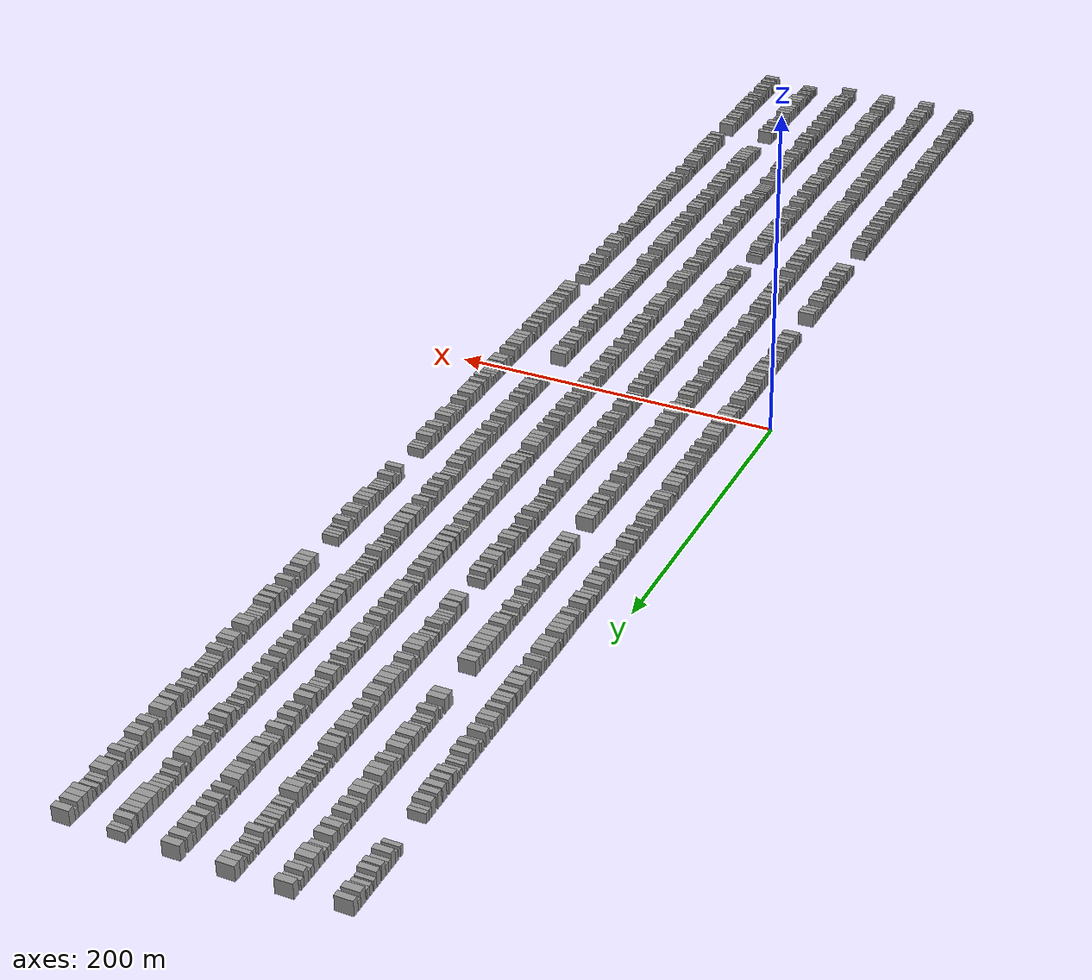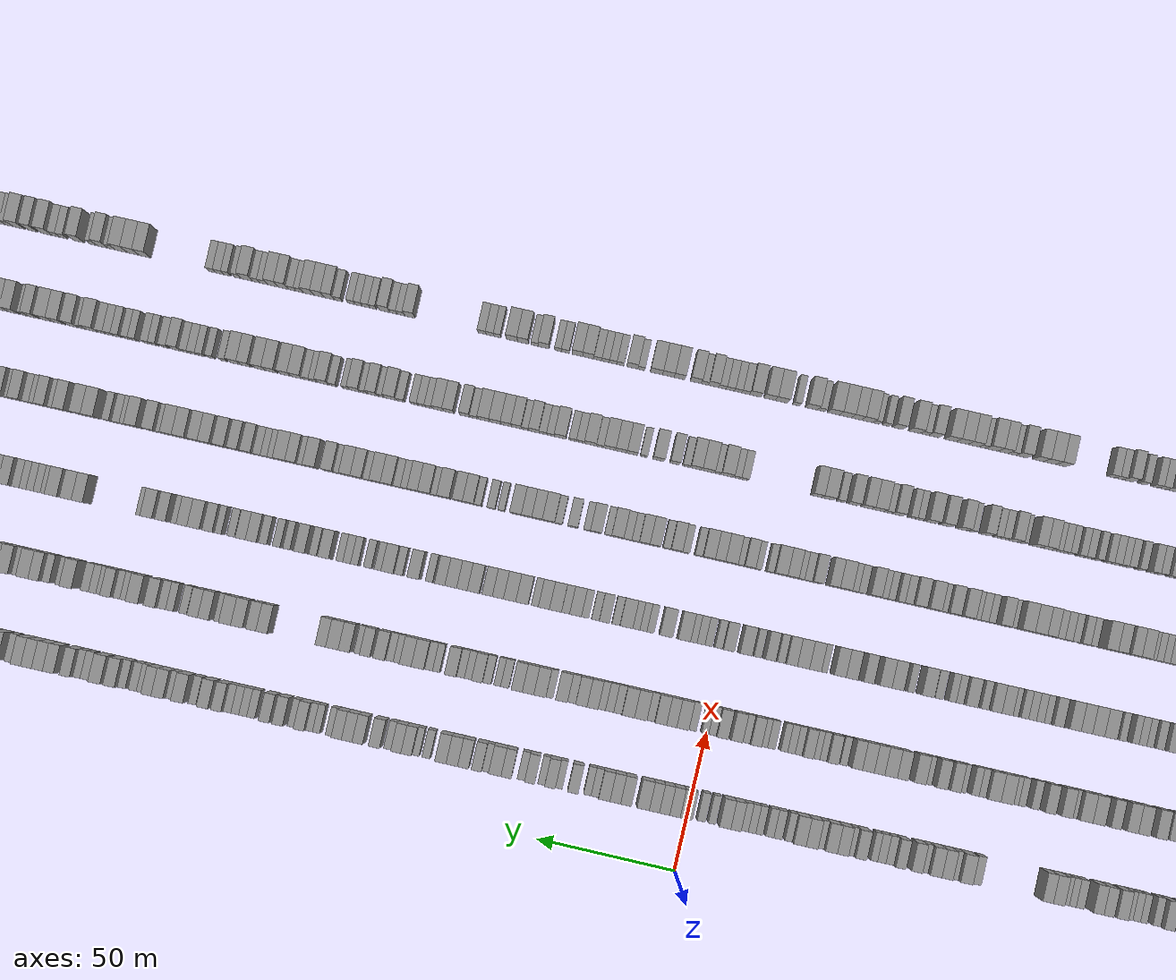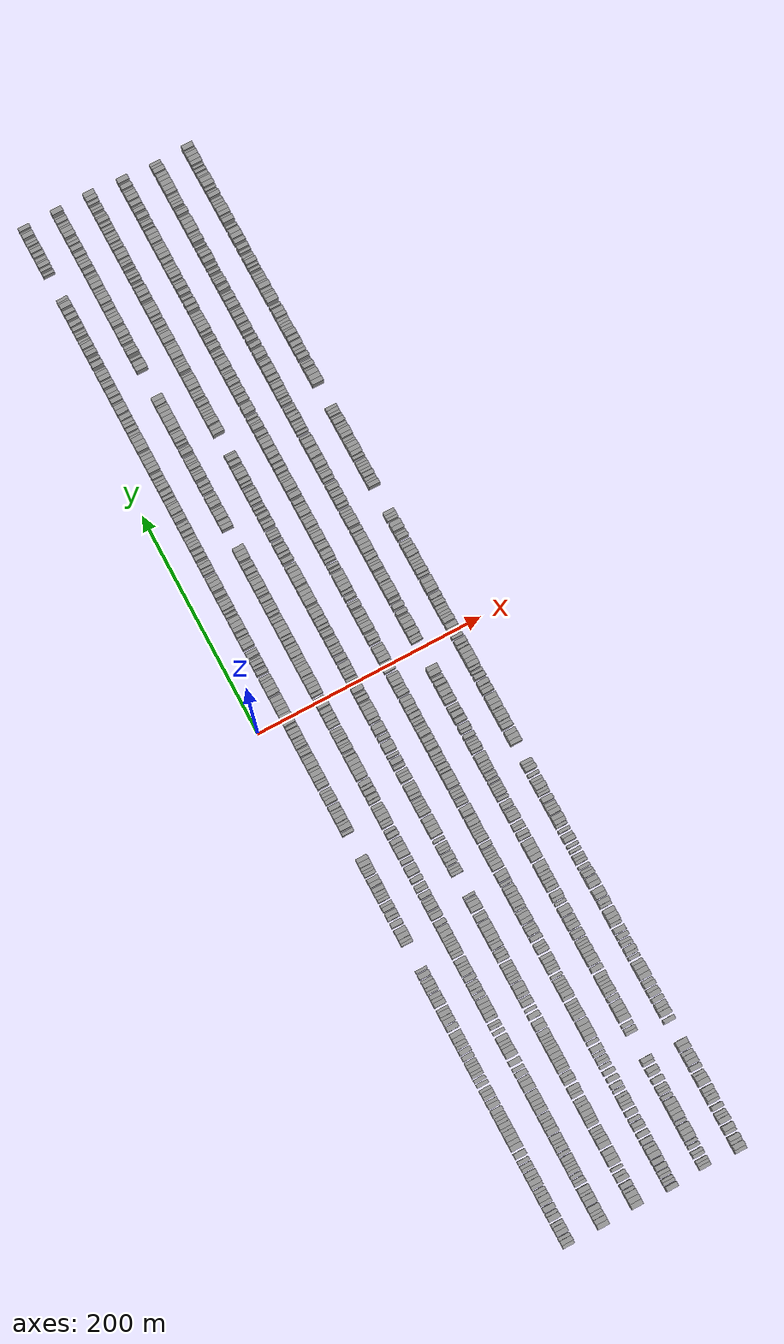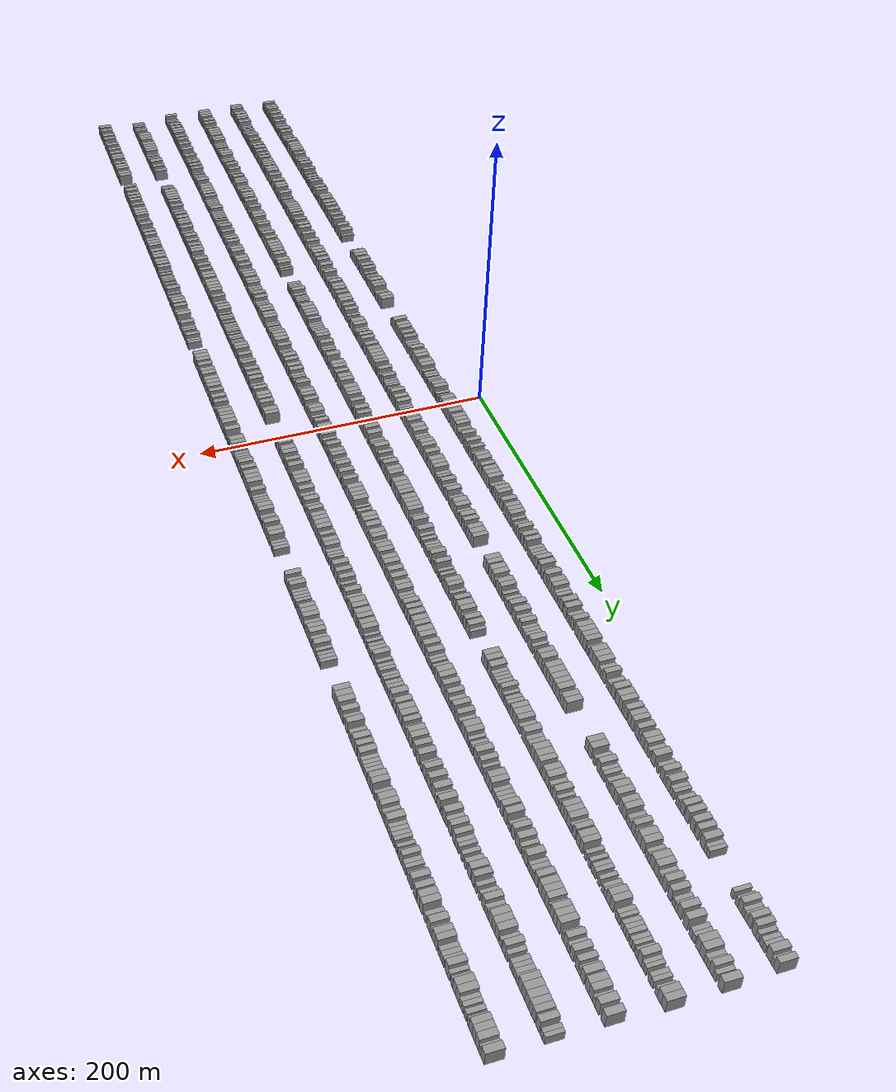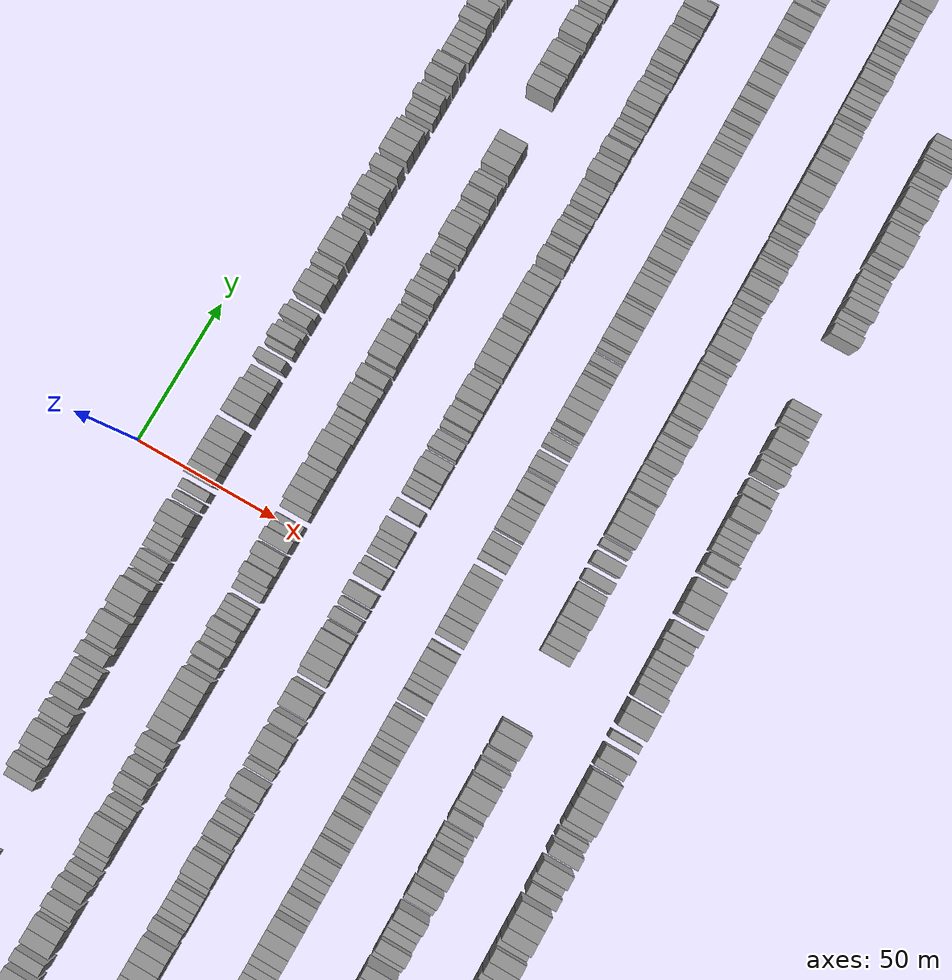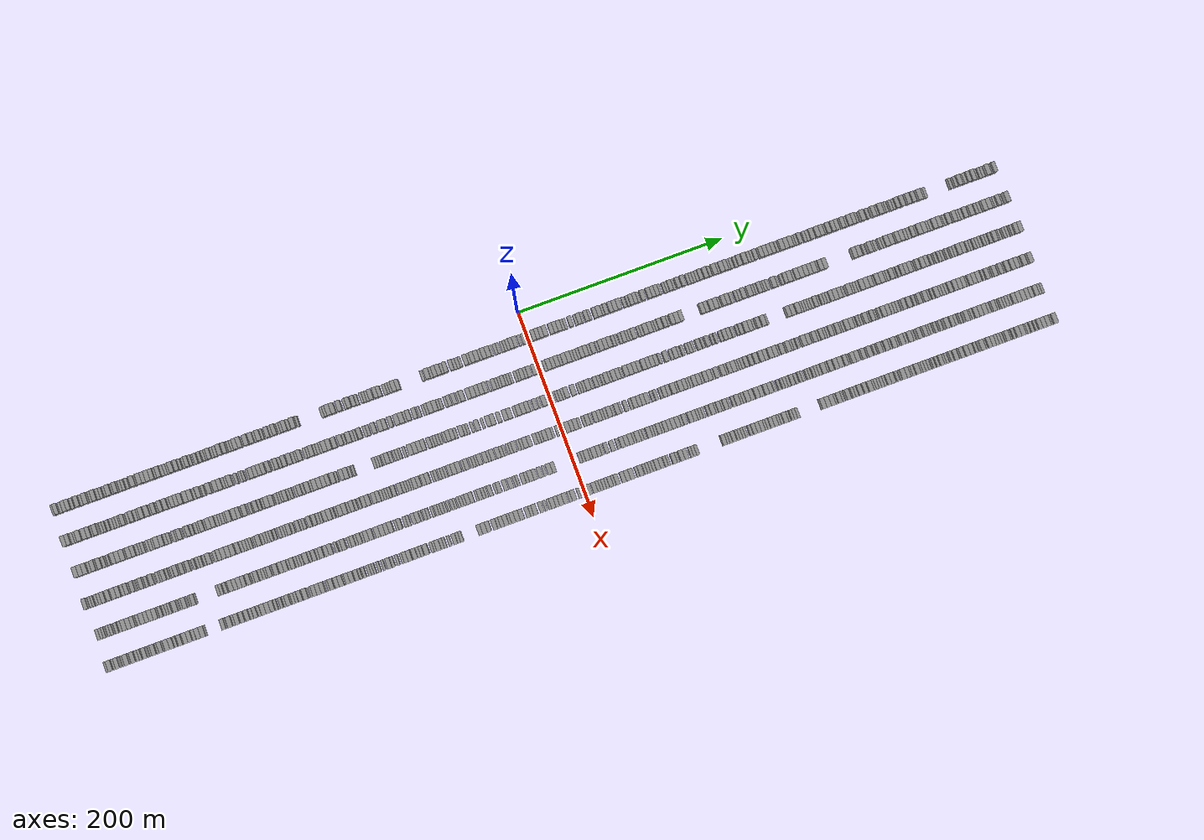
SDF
<sdf version="1.6">
 <world name="default">
  <scene>
   <sky><clouds><speed>12</speed></clouds></sky>
   <ambient>0.4 0.4 0.4 1</ambient>
   <background>0.7 0.7 0.7 1</background>
   <shadows>1</shadows>
  </scene>
  <gravity>0 0 -9.8066</gravity>
  <magnetic_field>6e-06 2.3e-05 -4.2e-05</magnetic_field>
  <physics default="0" name="default_physics" type="ode">
   <ode>
    <solver>
     <type>quick</type>
     <iters>10</iters>
     <sor>1.0</sor>
     <use_dynamic_moi_rescaling>0</use_dynamic_moi_rescaling>
    </solver>
    <constraints>
     <cfm>0</cfm>
     <erp>0.2</erp>
     <contact_max_correcting_vel>100</contact_max_correcting_vel>
     <contact_surface_layer>0.001</contact_surface_layer>
    </constraints>
   </ode>
   <max_step_size>0.004</max_step_size>
   <real_time_factor>1</real_time_factor>
   <real_time_update_rate>250</real_time_update_rate>
  </physics>
  <light name="sun" type="directional">
   <pose>0 0 10 0 0 0</pose>
   <diffuse>0.8 0.8 0.8 1</diffuse>
   <specular>0.2 0.2 0.2 1</specular>
   <attenuation>
    <range>1000</range>
    <constant>0.9</constant>
    <linear>0.01</linear>
    <quadratic>0.001</quadratic>
   </attenuation>
   <direction>-0.5 0.1 -0.9</direction>
  </light>
  <model name="building_1">
   <static>1</static>
   <pose>25.0000 -458.6283 0 0.000000 0.000000 0.000000</pose>
   <link name="link">
    <pose>0 0 3.00 0 0 0</pose>
    <collision name="collision"><geometry><box><size>10.0000 2.7434 6.0000</size></box></geometry></collision>
    <visual name="visual">
     <cast_shadows>0</cast_shadows>
     <geometry><box><size>10.0000 2.7434 6.0000</size></box></geometry>
     <material>
      <script>
       <uri>model://grey_wall/materials/scripts</uri>
       <uri>model://grey_wall/materials/textures</uri>
       <name>vrc/grey_wall</name>
      </script>
     </material>
    </visual>
   </link>
  </model>
  <model name="building_2">
   <static>1</static>
   <pose>25.0000 -455.3693 0 0.000000 0.000000 0.000000</pose>
   <link name="link">
    <pose>0 0 4.50 0 0 0</pose>
    <collision name="collision"><geometry><box><size>10.0000 3.7745 9.0000</size></box></geometry></collision>
    <visual name="visual">
     <cast_shadows>0</cast_shadows>
     <geometry><box><size>10.0000 3.7745 9.0000</size></box></geometry>
     <material>
      <script>
       <uri>model://grey_wall/materials/scripts</uri>
       <uri>model://grey_wall/materials/textures</uri>
       <name>vrc/grey_wall</name>
      </script>
     </material>
    </visual>
   </link>
  </model>
  <model name="building_3">
   <static>1</static>
   <pose>25.0000 -452.1495 0 0.000000 0.000000 0.000000</pose>
   <link name="link">
    <pose>0 0 3.00 0 0 0</pose>
    <collision name="collision"><geometry><box><size>10.0000 2.6650 6.0000</size></box></geometry></collision>
    <visual name="visual">
     <cast_shadows>0</cast_shadows>
     <geometry><box><size>10.0000 2.6650 6.0000</size></box></geometry>
     <material>
      <script>
       <uri>model://grey_wall/materials/scripts</uri>
       <uri>model://grey_wall/materials/textures</uri>
       <name>vrc/grey_wall</name>
      </script>
     </material>
    </visual>
   </link>
  </model>
  <model name="building_4">
   <static>1</static>
   <pose>25.0000 -447.9494 0 0.000000 0.000000 0.000000</pose>
   <link name="link">
    <pose>0 0 4.50 0 0 0</pose>
    <collision name="collision"><geometry><box><size>10.0000 3.7353 9.0000</size></box></geometry></collision>
    <visual name="visual">
     <cast_shadows>0</cast_shadows>
     <geometry><box><size>10.0000 3.7353 9.0000</size></box></geometry>
     <material>
      <script>
       <uri>model://grey_wall/materials/scripts</uri>
       <uri>model://grey_wall/materials/textures</uri>
       <name>vrc/grey_wall</name>
      </script>
     </material>
    </visual>
   </link>
  </model>
  <model name="building_5">
   <static>1</static>
   <pose>25.0000 -444.2583 0 0.000000 0.000000 0.000000</pose>
   <link name="link">
    <pose>0 0 4.50 0 0 0</pose>
    <collision name="collision"><geometry><box><size>10.0000 3.6470 9.0000</size></box></geometry></collision>
    <visual name="visual">
     <cast_shadows>0</cast_shadows>
     <geometry><box><size>10.0000 3.6470 9.0000</size></box></geometry>
     <material>
      <script>
       <uri>model://grey_wall/materials/scripts</uri>
       <uri>model://grey_wall/materials/textures</uri>
       <name>vrc/grey_wall</name>
      </script>
     </material>
    </visual>
   </link>
  </model>
  <model name="building_6">
   <static>1</static>
   <pose>25.0000 -441.0550 0 0.000000 0.000000 0.000000</pose>
   <link name="link">
    <pose>0 0 3.00 0 0 0</pose>
    <collision name="collision"><geometry><box><size>10.0000 2.7596 6.0000</size></box></geometry></collision>
    <visual name="visual">
     <cast_shadows>0</cast_shadows>
     <geometry><box><size>10.0000 2.7596 6.0000</size></box></geometry>
     <material>
      <script>
       <uri>model://grey_wall/materials/scripts</uri>
       <uri>model://grey_wall/materials/textures</uri>
       <name>vrc/grey_wall</name>
      </script>
     </material>
    </visual>
   </link>
  </model>
  <model name="building_7">
   <static>1</static>
   <pose>25.0000 -435.6190 0 0.000000 0.000000 0.000000</pose>
   <link name="link">
    <pose>0 0 4.50 0 0 0</pose>
    <collision name="collision"><geometry><box><size>10.0000 4.1124 9.0000</size></box></geometry></collision>
    <visual name="visual">
     <cast_shadows>0</cast_shadows>
     <geometry><box><size>10.0000 4.1124 9.0000</size></box></geometry>
     <material>
      <script>
       <uri>model://grey_wall/materials/scripts</uri>
       <uri>model://grey_wall/materials/textures</uri>
       <name>vrc/grey_wall</name>
      </script>
     </material>
    </visual>
   </link>
  </model>
  <model name="building_8">
   <static>1</static>
   <pose>25.0000 -432.2539 0 0.000000 0.000000 0.000000</pose>
   <link name="link">
    <pose>0 0 3.00 0 0 0</pose>
    <collision name="collision"><geometry><box><size>10.0000 2.6179 6.0000</size></box></geometry></collision>
    <visual name="visual">
     <cast_shadows>0</cast_shadows>
     <geometry><box><size>10.0000 2.6179 6.0000</size></box></geometry>
     <material>
      <script>
       <uri>model://grey_wall/materials/scripts</uri>
       <uri>model://grey_wall/materials/textures</uri>
       <name>vrc/grey_wall</name>
      </script>
     </material>
    </visual>
   </link>
  </model>
  <model name="building_9">
   <static>1</static>
   <pose>25.0000 -427.8353 0 0.000000 0.000000 0.000000</pose>
   <link name="link">
    <pose>0 0 4.50 0 0 0</pose>
    <collision name="collision"><geometry><box><size>10.0000 4.2192 9.0000</size></box></geometry></collision>
    <visual name="visual">
     <cast_shadows>0</cast_shadows>
     <geometry><box><size>10.0000 4.2192 9.0000</size></box></geometry>
     <material>
      <script>
       <uri>model://grey_wall/materials/scripts</uri>
       <uri>model://grey_wall/materials/textures</uri>
       <name>vrc/grey_wall</name>
      </script>
     </material>
    </visual>
   </link>
  </model>
  <model name="building_10">
   <static>1</static>
   <pose>25.0000 -423.2299 0 0.000000 0.000000 0.000000</pose>
   <link name="link">
    <pose>0 0 3.00 0 0 0</pose>
    <collision name="collision"><geometry><box><size>10.0000 2.9917 6.0000</size></box></geometry></collision>
    <visual name="visual">
     <cast_shadows>0</cast_shadows>
     <geometry><box><size>10.0000 2.9917 6.0000</size></box></geometry>
     <material>
      <script>
       <uri>model://grey_wall/materials/scripts</uri>
       <uri>model://grey_wall/materials/textures</uri>
       <name>vrc/grey_wall</name>
      </script>
     </material>
    </visual>
   </link>
  </model>
  <model name="building_11">
   <static>1</static>
   <pose>25.0000 -419.7063 0 0.000000 0.000000 0.000000</pose>
   <link name="link">
    <pose>0 0 4.50 0 0 0</pose>
    <collision name="collision"><geometry><box><size>10.0000 4.0556 9.0000</size></box></geometry></collision>
    <visual name="visual">
     <cast_shadows>0</cast_shadows>
     <geometry><box><size>10.0000 4.0556 9.0000</size></box></geometry>
     <material>
      <script>
       <uri>model://grey_wall/materials/scripts</uri>
       <uri>model://grey_wall/materials/textures</uri>
       <name>vrc/grey_wall</name>
      </script>
     </material>
    </visual>
   </link>
  </model>
  <model name="building_12">
   <static>1</static>
   <pose>25.0000 -416.2022 0 0.000000 0.000000 0.000000</pose>
   <link name="link">
    <pose>0 0 3.00 0 0 0</pose>
    <collision name="collision"><geometry><box><size>10.0000 2.9526 6.0000</size></box></geometry></collision>
    <visual name="visual">
     <cast_shadows>0</cast_shadows>
     <geometry><box><size>10.0000 2.9526 6.0000</size></box></geometry>
     <material>
      <script>
       <uri>model://grey_wall/materials/scripts</uri>
       <uri>model://grey_wall/materials/textures</uri>
       <name>vrc/grey_wall</name>
      </script>
     </material>
    </visual>
   </link>
  </model>
  <model name="building_13">
   <static>1</static>
   <pose>25.0000 -413.2810 0 0.000000 0.000000 0.000000</pose>
   <link name="link">
    <pose>0 0 3.00 0 0 0</pose>
    <collision name="collision"><geometry><box><size>10.0000 2.8898 6.0000</size></box></geometry></collision>
    <visual name="visual">
     <cast_shadows>0</cast_shadows>
     <geometry><box><size>10.0000 2.8898 6.0000</size></box></geometry>
     <material>
      <script>
       <uri>model://grey_wall/materials/scripts</uri>
       <uri>model://grey_wall/materials/textures</uri>
       <name>vrc/grey_wall</name>
      </script>
     </material>
    </visual>
   </link>
  </model>
  <model name="building_14">
   <static>1</static>
   <pose>25.0000 -409.3440 0 0.000000 0.000000 0.000000</pose>
   <link name="link">
    <pose>0 0 3.00 0 0 0</pose>
    <collision name="collision"><geometry><box><size>10.0000 2.9842 6.0000</size></box></geometry></collision>
    <visual name="visual">
     <cast_shadows>0</cast_shadows>
     <geometry><box><size>10.0000 2.9842 6.0000</size></box></geometry>
     <material>
      <script>
       <uri>model://grey_wall/materials/scripts</uri>
       <uri>model://grey_wall/materials/textures</uri>
       <name>vrc/grey_wall</name>
      </script>
     </material>
    </visual>
   </link>
  </model>
  <model name="building_15">
   <static>1</static>
   <pose>25.0000 -405.6760 0 0.000000 0.000000 0.000000</pose>
   <link name="link">
    <pose>0 0 4.50 0 0 0</pose>
    <collision name="collision"><geometry><box><size>10.0000 4.3517 9.0000</size></box></geometry></collision>
    <visual name="visual">
     <cast_shadows>0</cast_shadows>
     <geometry><box><size>10.0000 4.3517 9.0000</size></box></geometry>
     <material>
      <script>
       <uri>model://grey_wall/materials/scripts</uri>
       <uri>model://grey_wall/materials/textures</uri>
       <name>vrc/grey_wall</name>
      </script>
     </material>
    </visual>
   </link>
  </model>
  <model name="building_16">
   <static>1</static>
   <pose>25.0000 -402.2556 0 0.000000 0.000000 0.000000</pose>
   <link name="link">
    <pose>0 0 3.00 0 0 0</pose>
    <collision name="collision"><geometry><box><size>10.0000 2.4892 6.0000</size></box></geometry></collision>
    <visual name="visual">
     <cast_shadows>0</cast_shadows>
     <geometry><box><size>10.0000 2.4892 6.0000</size></box></geometry>
     <material>
      <script>
       <uri>model://grey_wall/materials/scripts</uri>
       <uri>model://grey_wall/materials/textures</uri>
       <name>vrc/grey_wall</name>
      </script>
     </material>
    </visual>
   </link>
  </model>
  <model name="building_17">
   <static>1</static>
   <pose>25.0000 -399.0806 0 0.000000 0.000000 0.000000</pose>
   <link name="link">
    <pose>0 0 4.50 0 0 0</pose>
    <collision name="collision"><geometry><box><size>10.0000 3.8608 9.0000</size></box></geometry></collision>
    <visual name="visual">
     <cast_shadows>0</cast_shadows>
     <geometry><box><size>10.0000 3.8608 9.0000</size></box></geometry>
     <material>
      <script>
       <uri>model://grey_wall/materials/scripts</uri>
       <uri>model://grey_wall/materials/textures</uri>
       <name>vrc/grey_wall</name>
      </script>
     </material>
    </visual>
   </link>
  </model>
  <model name="building_18">
   <static>1</static>
   <pose>25.0000 -394.8161 0 0.000000 0.000000 0.000000</pose>
   <link name="link">
    <pose>0 0 3.00 0 0 0</pose>
    <collision name="collision"><geometry><box><size>10.0000 2.6683 6.0000</size></box></geometry></collision>
    <visual name="visual">
     <cast_shadows>0</cast_shadows>
     <geometry><box><size>10.0000 2.6683 6.0000</size></box></geometry>
     <material>
      <script>
       <uri>model://grey_wall/materials/scripts</uri>
       <uri>model://grey_wall/materials/textures</uri>
       <name>vrc/grey_wall</name>
      </script>
     </material>
    </visual>
   </link>
  </model>
  <model name="building_19">
   <static>1</static>
   <pose>25.0000 -392.1013 0 0.000000 0.000000 0.000000</pose>
   <link name="link">
    <pose>0 0 3.00 0 0 0</pose>
    <collision name="collision"><geometry><box><size>10.0000 2.7613 6.0000</size></box></geometry></collision>
    <visual name="visual">
     <cast_shadows>0</cast_shadows>
     <geometry><box><size>10.0000 2.7613 6.0000</size></box></geometry>
     <material>
      <script>
       <uri>model://grey_wall/materials/scripts</uri>
       <uri>model://grey_wall/materials/textures</uri>
       <name>vrc/grey_wall</name>
      </script>
     </material>
    </visual>
   </link>
  </model>
  <model name="building_20">
   <static>1</static>
   <pose>25.0000 -388.2352 0 0.000000 0.000000 0.000000</pose>
   <link name="link">
    <pose>0 0 3.00 0 0 0</pose>
    <collision name="collision"><geometry><box><size>10.0000 2.9707 6.0000</size></box></geometry></collision>
    <visual name="visual">
     <cast_shadows>0</cast_shadows>
     <geometry><box><size>10.0000 2.9707 6.0000</size></box></geometry>
     <material>
      <script>
       <uri>model://grey_wall/materials/scripts</uri>
       <uri>model://grey_wall/materials/textures</uri>
       <name>vrc/grey_wall</name>
      </script>
     </material>
    </visual>
   </link>
  </model>
  <model name="building_21">
   <static>1</static>
   <pose>25.0000 -382.5106 0 0.000000 0.000000 0.000000</pose>
   <link name="link">
    <pose>0 0 4.50 0 0 0</pose>
    <collision name="collision"><geometry><box><size>10.0000 4.4785 9.0000</size></box></geometry></collision>
    <visual name="visual">
     <cast_shadows>0</cast_shadows>
     <geometry><box><size>10.0000 4.4785 9.0000</size></box></geometry>
     <material>
      <script>
       <uri>model://grey_wall/materials/scripts</uri>
       <uri>model://grey_wall/materials/textures</uri>
       <name>vrc/grey_wall</name>
      </script>
     </material>
    </visual>
   </link>
  </model>
  <model name="building_22">
   <static>1</static>
   <pose>25.0000 -376.1218 0 0.000000 0.000000 0.000000</pose>
   <link name="link">
    <pose>0 0 4.50 0 0 0</pose>
    <collision name="collision"><geometry><box><size>10.0000 4.2990 9.0000</size></box></geometry></collision>
    <visual name="visual">
     <cast_shadows>0</cast_shadows>
     <geometry><box><size>10.0000 4.2990 9.0000</size></box></geometry>
     <material>
      <script>
       <uri>model://grey_wall/materials/scripts</uri>
       <uri>model://grey_wall/materials/textures</uri>
       <name>vrc/grey_wall</name>
      </script>
     </material>
    </visual>
   </link>
  </model>
  <model name="building_23">
   <static>1</static>
   <pose>25.0000 -372.1706 0 0.000000 0.000000 0.000000</pose>
   <link name="link">
    <pose>0 0 4.50 0 0 0</pose>
    <collision name="collision"><geometry><box><size>10.0000 3.6033 9.0000</size></box></geometry></collision>
    <visual name="visual">
     <cast_shadows>0</cast_shadows>
     <geometry><box><size>10.0000 3.6033 9.0000</size></box></geometry>
     <material>
      <script>
       <uri>model://grey_wall/materials/scripts</uri>
       <uri>model://grey_wall/materials/textures</uri>
       <name>vrc/grey_wall</name>
      </script>
     </material>
    </visual>
   </link>
  </model>
  <model name="building_24">
   <static>1</static>
   <pose>25.0000 -368.2538 0 0.000000 0.000000 0.000000</pose>
   <link name="link">
    <pose>0 0 4.50 0 0 0</pose>
    <collision name="collision"><geometry><box><size>10.0000 4.2304 9.0000</size></box></geometry></collision>
    <visual name="visual">
     <cast_shadows>0</cast_shadows>
     <geometry><box><size>10.0000 4.2304 9.0000</size></box></geometry>
     <material>
      <script>
       <uri>model://grey_wall/materials/scripts</uri>
       <uri>model://grey_wall/materials/textures</uri>
       <name>vrc/grey_wall</name>
      </script>
     </material>
    </visual>
   </link>
  </model>
  <model name="building_25">
   <static>1</static>
   <pose>25.0000 -364.2365 0 0.000000 0.000000 0.000000</pose>
   <link name="link">
    <pose>0 0 4.50 0 0 0</pose>
    <collision name="collision"><geometry><box><size>10.0000 3.8043 9.0000</size></box></geometry></collision>
    <visual name="visual">
     <cast_shadows>0</cast_shadows>
     <geometry><box><size>10.0000 3.8043 9.0000</size></box></geometry>
     <material>
      <script>
       <uri>model://grey_wall/materials/scripts</uri>
       <uri>model://grey_wall/materials/textures</uri>
       <name>vrc/grey_wall</name>
      </script>
     </material>
    </visual>
   </link>
  </model>
  <model name="building_26">
   <static>1</static>
   <pose>25.0000 -361.0230 0 0.000000 0.000000 0.000000</pose>
   <link name="link">
    <pose>0 0 3.00 0 0 0</pose>
    <collision name="collision"><geometry><box><size>10.0000 2.6225 6.0000</size></box></geometry></collision>
    <visual name="visual">
     <cast_shadows>0</cast_shadows>
     <geometry><box><size>10.0000 2.6225 6.0000</size></box></geometry>
     <material>
      <script>
       <uri>model://grey_wall/materials/scripts</uri>
       <uri>model://grey_wall/materials/textures</uri>
       <name>vrc/grey_wall</name>
      </script>
     </material>
    </visual>
   </link>
  </model>
  <model name="building_27">
   <static>1</static>
   <pose>25.0000 -357.7749 0 0.000000 0.000000 0.000000</pose>
   <link name="link">
    <pose>0 0 4.50 0 0 0</pose>
    <collision name="collision"><geometry><box><size>10.0000 3.8737 9.0000</size></box></geometry></collision>
    <visual name="visual">
     <cast_shadows>0</cast_shadows>
     <geometry><box><size>10.0000 3.8737 9.0000</size></box></geometry>
     <material>
      <script>
       <uri>model://grey_wall/materials/scripts</uri>
       <uri>model://grey_wall/materials/textures</uri>
       <name>vrc/grey_wall</name>
      </script>
     </material>
    </visual>
   </link>
  </model>
  <model name="building_28">
   <static>1</static>
   <pose>25.0000 -354.3741 0 0.000000 0.000000 0.000000</pose>
   <link name="link">
    <pose>0 0 3.00 0 0 0</pose>
    <collision name="collision"><geometry><box><size>10.0000 2.9279 6.0000</size></box></geometry></collision>
    <visual name="visual">
     <cast_shadows>0</cast_shadows>
     <geometry><box><size>10.0000 2.9279 6.0000</size></box></geometry>
     <material>
      <script>
       <uri>model://grey_wall/materials/scripts</uri>
       <uri>model://grey_wall/materials/textures</uri>
       <name>vrc/grey_wall</name>
      </script>
     </material>
    </visual>
   </link>
  </model>
  <model name="building_29">
   <static>1</static>
   <pose>25.0000 -351.5762 0 0.000000 0.000000 0.000000</pose>
   <link name="link">
    <pose>0 0 3.00 0 0 0</pose>
    <collision name="collision"><geometry><box><size>10.0000 2.6679 6.0000</size></box></geometry></collision>
    <visual name="visual">
     <cast_shadows>0</cast_shadows>
     <geometry><box><size>10.0000 2.6679 6.0000</size></box></geometry>
     <material>
      <script>
       <uri>model://grey_wall/materials/scripts</uri>
       <uri>model://grey_wall/materials/textures</uri>
       <name>vrc/grey_wall</name>
      </script>
     </material>
    </visual>
   </link>
  </model>
  <model name="building_30">
   <static>1</static>
   <pose>25.0000 -348.9014 0 0.000000 0.000000 0.000000</pose>
   <link name="link">
    <pose>0 0 3.00 0 0 0</pose>
    <collision name="collision"><geometry><box><size>10.0000 2.6817 6.0000</size></box></geometry></collision>
    <visual name="visual">
     <cast_shadows>0</cast_shadows>
     <geometry><box><size>10.0000 2.6817 6.0000</size></box></geometry>
     <material>
      <script>
       <uri>model://grey_wall/materials/scripts</uri>
       <uri>model://grey_wall/materials/textures</uri>
       <name>vrc/grey_wall</name>
      </script>
     </material>
    </visual>
   </link>
  </model>
  <model name="building_31">
   <static>1</static>
   <pose>25.0000 -345.5263 0 0.000000 0.000000 0.000000</pose>
   <link name="link">
    <pose>0 0 4.50 0 0 0</pose>
    <collision name="collision"><geometry><box><size>10.0000 4.0684 9.0000</size></box></geometry></collision>
    <visual name="visual">
     <cast_shadows>0</cast_shadows>
     <geometry><box><size>10.0000 4.0684 9.0000</size></box></geometry>
     <material>
      <script>
       <uri>model://grey_wall/materials/scripts</uri>
       <uri>model://grey_wall/materials/textures</uri>
       <name>vrc/grey_wall</name>
      </script>
     </material>
    </visual>
   </link>
  </model>
  <model name="building_32">
   <static>1</static>
   <pose>25.0000 -340.5434 0 0.000000 0.000000 0.000000</pose>
   <link name="link">
    <pose>0 0 4.50 0 0 0</pose>
    <collision name="collision"><geometry><box><size>10.0000 3.8974 9.0000</size></box></geometry></collision>
    <visual name="visual">
     <cast_shadows>0</cast_shadows>
     <geometry><box><size>10.0000 3.8974 9.0000</size></box></geometry>
     <material>
      <script>
       <uri>model://grey_wall/materials/scripts</uri>
       <uri>model://grey_wall/materials/textures</uri>
       <name>vrc/grey_wall</name>
      </script>
     </material>
    </visual>
   </link>
  </model>
  <model name="building_33">
   <static>1</static>
   <pose>25.0000 -337.2817 0 0.000000 0.000000 0.000000</pose>
   <link name="link">
    <pose>0 0 3.00 0 0 0</pose>
    <collision name="collision"><geometry><box><size>10.0000 2.6259 6.0000</size></box></geometry></collision>
    <visual name="visual">
     <cast_shadows>0</cast_shadows>
     <geometry><box><size>10.0000 2.6259 6.0000</size></box></geometry>
     <material>
      <script>
       <uri>model://grey_wall/materials/scripts</uri>
       <uri>model://grey_wall/materials/textures</uri>
       <name>vrc/grey_wall</name>
      </script>
     </material>
    </visual>
   </link>
  </model>
  <model name="building_34">
   <static>1</static>
   <pose>25.0000 -333.5525 0 0.000000 0.000000 0.000000</pose>
   <link name="link">
    <pose>0 0 3.00 0 0 0</pose>
    <collision name="collision"><geometry><box><size>10.0000 2.8326 6.0000</size></box></geometry></collision>
    <visual name="visual">
     <cast_shadows>0</cast_shadows>
     <geometry><box><size>10.0000 2.8326 6.0000</size></box></geometry>
     <material>
      <script>
       <uri>model://grey_wall/materials/scripts</uri>
       <uri>model://grey_wall/materials/textures</uri>
       <name>vrc/grey_wall</name>
      </script>
     </material>
    </visual>
   </link>
  </model>
  <model name="building_35">
   <static>1</static>
   <pose>25.0000 -330.3303 0 0.000000 0.000000 0.000000</pose>
   <link name="link">
    <pose>0 0 4.50 0 0 0</pose>
    <collision name="collision"><geometry><box><size>10.0000 3.6116 9.0000</size></box></geometry></collision>
    <visual name="visual">
     <cast_shadows>0</cast_shadows>
     <geometry><box><size>10.0000 3.6116 9.0000</size></box></geometry>
     <material>
      <script>
       <uri>model://grey_wall/materials/scripts</uri>
       <uri>model://grey_wall/materials/textures</uri>
       <name>vrc/grey_wall</name>
      </script>
     </material>
    </visual>
   </link>
  </model>
  <model name="building_36">
   <static>1</static>
   <pose>25.0000 -327.2523 0 0.000000 0.000000 0.000000</pose>
   <link name="link">
    <pose>0 0 3.00 0 0 0</pose>
    <collision name="collision"><geometry><box><size>10.0000 2.5445 6.0000</size></box></geometry></collision>
    <visual name="visual">
     <cast_shadows>0</cast_shadows>
     <geometry><box><size>10.0000 2.5445 6.0000</size></box></geometry>
     <material>
      <script>
       <uri>model://grey_wall/materials/scripts</uri>
       <uri>model://grey_wall/materials/textures</uri>
       <name>vrc/grey_wall</name>
      </script>
     </material>
    </visual>
   </link>
  </model>
  <model name="building_37">
   <static>1</static>
   <pose>25.0000 -322.4861 0 0.000000 0.000000 0.000000</pose>
   <link name="link">
    <pose>0 0 3.00 0 0 0</pose>
    <collision name="collision"><geometry><box><size>10.0000 2.9878 6.0000</size></box></geometry></collision>
    <visual name="visual">
     <cast_shadows>0</cast_shadows>
     <geometry><box><size>10.0000 2.9878 6.0000</size></box></geometry>
     <material>
      <script>
       <uri>model://grey_wall/materials/scripts</uri>
       <uri>model://grey_wall/materials/textures</uri>
       <name>vrc/grey_wall</name>
      </script>
     </material>
    </visual>
   </link>
  </model>
  <model name="building_38">
   <static>1</static>
   <pose>25.0000 -318.5004 0 0.000000 0.000000 0.000000</pose>
   <link name="link">
    <pose>0 0 3.00 0 0 0</pose>
    <collision name="collision"><geometry><box><size>10.0000 2.9836 6.0000</size></box></geometry></collision>
    <visual name="visual">
     <cast_shadows>0</cast_shadows>
     <geometry><box><size>10.0000 2.9836 6.0000</size></box></geometry>
     <material>
      <script>
       <uri>model://grey_wall/materials/scripts</uri>
       <uri>model://grey_wall/materials/textures</uri>
       <name>vrc/grey_wall</name>
      </script>
     </material>
    </visual>
   </link>
  </model>
  <model name="building_39">
   <static>1</static>
   <pose>25.0000 -314.8002 0 0.000000 0.000000 0.000000</pose>
   <link name="link">
    <pose>0 0 3.00 0 0 0</pose>
    <collision name="collision"><geometry><box><size>10.0000 2.4167 6.0000</size></box></geometry></collision>
    <visual name="visual">
     <cast_shadows>0</cast_shadows>
     <geometry><box><size>10.0000 2.4167 6.0000</size></box></geometry>
     <material>
      <script>
       <uri>model://grey_wall/materials/scripts</uri>
       <uri>model://grey_wall/materials/textures</uri>
       <name>vrc/grey_wall</name>
      </script>
     </material>
    </visual>
   </link>
  </model>
  <model name="building_40">
   <static>1</static>
   <pose>25.0000 -312.3255 0 0.000000 0.000000 0.000000</pose>
   <link name="link">
    <pose>0 0 3.00 0 0 0</pose>
    <collision name="collision"><geometry><box><size>10.0000 2.5326 6.0000</size></box></geometry></collision>
    <visual name="visual">
     <cast_shadows>0</cast_shadows>
     <geometry><box><size>10.0000 2.5326 6.0000</size></box></geometry>
     <material>
      <script>
       <uri>model://grey_wall/materials/scripts</uri>
       <uri>model://grey_wall/materials/textures</uri>
       <name>vrc/grey_wall</name>
      </script>
     </material>
    </visual>
   </link>
  </model>
  <model name="building_41">
   <static>1</static>
   <pose>25.0000 -309.2463 0 0.000000 0.000000 0.000000</pose>
   <link name="link">
    <pose>0 0 4.50 0 0 0</pose>
    <collision name="collision"><geometry><box><size>10.0000 3.6259 9.0000</size></box></geometry></collision>
    <visual name="visual">
     <cast_shadows>0</cast_shadows>
     <geometry><box><size>10.0000 3.6259 9.0000</size></box></geometry>
     <material>
      <script>
       <uri>model://grey_wall/materials/scripts</uri>
       <uri>model://grey_wall/materials/textures</uri>
       <name>vrc/grey_wall</name>
      </script>
     </material>
    </visual>
   </link>
  </model>
  <model name="building_42">
   <static>1</static>
   <pose>25.0000 -306.2220 0 0.000000 0.000000 0.000000</pose>
   <link name="link">
    <pose>0 0 3.00 0 0 0</pose>
    <collision name="collision"><geometry><box><size>10.0000 2.4227 6.0000</size></box></geometry></collision>
    <visual name="visual">
     <cast_shadows>0</cast_shadows>
     <geometry><box><size>10.0000 2.4227 6.0000</size></box></geometry>
     <material>
      <script>
       <uri>model://grey_wall/materials/scripts</uri>
       <uri>model://grey_wall/materials/textures</uri>
       <name>vrc/grey_wall</name>
      </script>
     </material>
    </visual>
   </link>
  </model>
  <model name="building_43">
   <static>1</static>
   <pose>25.0000 -303.6362 0 0.000000 0.000000 0.000000</pose>
   <link name="link">
    <pose>0 0 3.00 0 0 0</pose>
    <collision name="collision"><geometry><box><size>10.0000 2.7490 6.0000</size></box></geometry></collision>
    <visual name="visual">
     <cast_shadows>0</cast_shadows>
     <geometry><box><size>10.0000 2.7490 6.0000</size></box></geometry>
     <material>
      <script>
       <uri>model://grey_wall/materials/scripts</uri>
       <uri>model://grey_wall/materials/textures</uri>
       <name>vrc/grey_wall</name>
      </script>
     </material>
    </visual>
   </link>
  </model>
  <model name="building_44">
   <static>1</static>
   <pose>25.0000 -299.2667 0 0.000000 0.000000 0.000000</pose>
   <link name="link">
    <pose>0 0 4.50 0 0 0</pose>
    <collision name="collision"><geometry><box><size>10.0000 3.9901 9.0000</size></box></geometry></collision>
    <visual name="visual">
     <cast_shadows>0</cast_shadows>
     <geometry><box><size>10.0000 3.9901 9.0000</size></box></geometry>
     <material>
      <script>
       <uri>model://grey_wall/materials/scripts</uri>
       <uri>model://grey_wall/materials/textures</uri>
       <name>vrc/grey_wall</name>
      </script>
     </material>
    </visual>
   </link>
  </model>
  <model name="building_45">
   <static>1</static>
   <pose>25.0000 -294.3375 0 0.000000 0.000000 0.000000</pose>
   <link name="link">
    <pose>0 0 4.50 0 0 0</pose>
    <collision name="collision"><geometry><box><size>10.0000 3.8683 9.0000</size></box></geometry></collision>
    <visual name="visual">
     <cast_shadows>0</cast_shadows>
     <geometry><box><size>10.0000 3.8683 9.0000</size></box></geometry>
     <material>
      <script>
       <uri>model://grey_wall/materials/scripts</uri>
       <uri>model://grey_wall/materials/textures</uri>
       <name>vrc/grey_wall</name>
      </script>
     </material>
    </visual>
   </link>
  </model>
  <model name="building_46">
   <static>1</static>
   <pose>25.0000 -290.1583 0 0.000000 0.000000 0.000000</pose>
   <link name="link">
    <pose>0 0 3.00 0 0 0</pose>
    <collision name="collision"><geometry><box><size>10.0000 2.4899 6.0000</size></box></geometry></collision>
    <visual name="visual">
     <cast_shadows>0</cast_shadows>
     <geometry><box><size>10.0000 2.4899 6.0000</size></box></geometry>
     <material>
      <script>
       <uri>model://grey_wall/materials/scripts</uri>
       <uri>model://grey_wall/materials/textures</uri>
       <name>vrc/grey_wall</name>
      </script>
     </material>
    </visual>
   </link>
  </model>
  <model name="building_47">
   <static>1</static>
   <pose>25.0000 -287.4162 0 0.000000 0.000000 0.000000</pose>
   <link name="link">
    <pose>0 0 3.00 0 0 0</pose>
    <collision name="collision"><geometry><box><size>10.0000 2.9943 6.0000</size></box></geometry></collision>
    <visual name="visual">
     <cast_shadows>0</cast_shadows>
     <geometry><box><size>10.0000 2.9943 6.0000</size></box></geometry>
     <material>
      <script>
       <uri>model://grey_wall/materials/scripts</uri>
       <uri>model://grey_wall/materials/textures</uri>
       <name>vrc/grey_wall</name>
      </script>
     </material>
    </visual>
   </link>
  </model>
  <model name="building_48">
   <static>1</static>
   <pose>25.0000 -283.9546 0 0.000000 0.000000 0.000000</pose>
   <link name="link">
    <pose>0 0 4.50 0 0 0</pose>
    <collision name="collision"><geometry><box><size>10.0000 3.9290 9.0000</size></box></geometry></collision>
    <visual name="visual">
     <cast_shadows>0</cast_shadows>
     <geometry><box><size>10.0000 3.9290 9.0000</size></box></geometry>
     <material>
      <script>
       <uri>model://grey_wall/materials/scripts</uri>
       <uri>model://grey_wall/materials/textures</uri>
       <name>vrc/grey_wall</name>
      </script>
     </material>
    </visual>
   </link>
  </model>
  <model name="building_49">
   <static>1</static>
   <pose>25.0000 -279.9491 0 0.000000 0.000000 0.000000</pose>
   <link name="link">
    <pose>0 0 4.50 0 0 0</pose>
    <collision name="collision"><geometry><box><size>10.0000 4.0820 9.0000</size></box></geometry></collision>
    <visual name="visual">
     <cast_shadows>0</cast_shadows>
     <geometry><box><size>10.0000 4.0820 9.0000</size></box></geometry>
     <material>
      <script>
       <uri>model://grey_wall/materials/scripts</uri>
       <uri>model://grey_wall/materials/textures</uri>
       <name>vrc/grey_wall</name>
      </script>
     </material>
    </visual>
   </link>
  </model>
  <model name="building_50">
   <static>1</static>
   <pose>25.0000 -273.7268 0 0.000000 0.000000 0.000000</pose>
   <link name="link">
    <pose>0 0 4.50 0 0 0</pose>
    <collision name="collision"><geometry><box><size>10.0000 4.3626 9.0000</size></box></geometry></collision>
    <visual name="visual">
     <cast_shadows>0</cast_shadows>
     <geometry><box><size>10.0000 4.3626 9.0000</size></box></geometry>
     <material>
      <script>
       <uri>model://grey_wall/materials/scripts</uri>
       <uri>model://grey_wall/materials/textures</uri>
       <name>vrc/grey_wall</name>
      </script>
     </material>
    </visual>
   </link>
  </model>
  <model name="building_51">
   <static>1</static>
   <pose>25.0000 -268.4411 0 0.000000 0.000000 0.000000</pose>
   <link name="link">
    <pose>0 0 4.50 0 0 0</pose>
    <collision name="collision"><geometry><box><size>10.0000 4.2088 9.0000</size></box></geometry></collision>
    <visual name="visual">
     <cast_shadows>0</cast_shadows>
     <geometry><box><size>10.0000 4.2088 9.0000</size></box></geometry>
     <material>
      <script>
       <uri>model://grey_wall/materials/scripts</uri>
       <uri>model://grey_wall/materials/textures</uri>
       <name>vrc/grey_wall</name>
      </script>
     </material>
    </visual>
   </link>
  </model>
  <model name="building_52">
   <static>1</static>
   <pose>25.0000 -264.9910 0 0.000000 0.000000 0.000000</pose>
   <link name="link">
    <pose>0 0 3.00 0 0 0</pose>
    <collision name="collision"><geometry><box><size>10.0000 2.6913 6.0000</size></box></geometry></collision>
    <visual name="visual">
     <cast_shadows>0</cast_shadows>
     <geometry><box><size>10.0000 2.6913 6.0000</size></box></geometry>
     <material>
      <script>
       <uri>model://grey_wall/materials/scripts</uri>
       <uri>model://grey_wall/materials/textures</uri>
       <name>vrc/grey_wall</name>
      </script>
     </material>
    </visual>
   </link>
  </model>
  <model name="building_53">
   <static>1</static>
   <pose>25.0000 -261.5494 0 0.000000 0.000000 0.000000</pose>
   <link name="link">
    <pose>0 0 4.50 0 0 0</pose>
    <collision name="collision"><geometry><box><size>10.0000 4.1920 9.0000</size></box></geometry></collision>
    <visual name="visual">
     <cast_shadows>0</cast_shadows>
     <geometry><box><size>10.0000 4.1920 9.0000</size></box></geometry>
     <material>
      <script>
       <uri>model://grey_wall/materials/scripts</uri>
       <uri>model://grey_wall/materials/textures</uri>
       <name>vrc/grey_wall</name>
      </script>
     </material>
    </visual>
   </link>
  </model>
  <model name="building_54">
   <static>1</static>
   <pose>25.0000 -258.2401 0 0.000000 0.000000 0.000000</pose>
   <link name="link">
    <pose>0 0 3.00 0 0 0</pose>
    <collision name="collision"><geometry><box><size>10.0000 2.4267 6.0000</size></box></geometry></collision>
    <visual name="visual">
     <cast_shadows>0</cast_shadows>
     <geometry><box><size>10.0000 2.4267 6.0000</size></box></geometry>
     <material>
      <script>
       <uri>model://grey_wall/materials/scripts</uri>
       <uri>model://grey_wall/materials/textures</uri>
       <name>vrc/grey_wall</name>
      </script>
     </material>
    </visual>
   </link>
  </model>
  <model name="building_55">
   <static>1</static>
   <pose>25.0000 -253.1030 0 0.000000 0.000000 0.000000</pose>
   <link name="link">
    <pose>0 0 4.50 0 0 0</pose>
    <collision name="collision"><geometry><box><size>10.0000 3.8475 9.0000</size></box></geometry></collision>
    <visual name="visual">
     <cast_shadows>0</cast_shadows>
     <geometry><box><size>10.0000 3.8475 9.0000</size></box></geometry>
     <material>
      <script>
       <uri>model://grey_wall/materials/scripts</uri>
       <uri>model://grey_wall/materials/textures</uri>
       <name>vrc/grey_wall</name>
      </script>
     </material>
    </visual>
   </link>
  </model>
  <model name="building_56">
   <static>1</static>
   <pose>25.0000 -249.7106 0 0.000000 0.000000 0.000000</pose>
   <link name="link">
    <pose>0 0 3.00 0 0 0</pose>
    <collision name="collision"><geometry><box><size>10.0000 2.9372 6.0000</size></box></geometry></collision>
    <visual name="visual">
     <cast_shadows>0</cast_shadows>
     <geometry><box><size>10.0000 2.9372 6.0000</size></box></geometry>
     <material>
      <script>
       <uri>model://grey_wall/materials/scripts</uri>
       <uri>model://grey_wall/materials/textures</uri>
       <name>vrc/grey_wall</name>
      </script>
     </material>
    </visual>
   </link>
  </model>
  <model name="building_57">
   <static>1</static>
   <pose>25.0000 -246.4095 0 0.000000 0.000000 0.000000</pose>
   <link name="link">
    <pose>0 0 4.50 0 0 0</pose>
    <collision name="collision"><geometry><box><size>10.0000 3.6650 9.0000</size></box></geometry></collision>
    <visual name="visual">
     <cast_shadows>0</cast_shadows>
     <geometry><box><size>10.0000 3.6650 9.0000</size></box></geometry>
     <material>
      <script>
       <uri>model://grey_wall/materials/scripts</uri>
       <uri>model://grey_wall/materials/textures</uri>
       <name>vrc/grey_wall</name>
      </script>
     </material>
    </visual>
   </link>
  </model>
  <model name="building_58">
   <static>1</static>
   <pose>25.0000 -242.3506 0 0.000000 0.000000 0.000000</pose>
   <link name="link">
    <pose>0 0 3.00 0 0 0</pose>
    <collision name="collision"><geometry><box><size>10.0000 2.4527 6.0000</size></box></geometry></collision>
    <visual name="visual">
     <cast_shadows>0</cast_shadows>
     <geometry><box><size>10.0000 2.4527 6.0000</size></box></geometry>
     <material>
      <script>
       <uri>model://grey_wall/materials/scripts</uri>
       <uri>model://grey_wall/materials/textures</uri>
       <name>vrc/grey_wall</name>
      </script>
     </material>
    </visual>
   </link>
  </model>
  <model name="building_59">
   <static>1</static>
   <pose>25.0000 -239.7100 0 0.000000 0.000000 0.000000</pose>
   <link name="link">
    <pose>0 0 3.00 0 0 0</pose>
    <collision name="collision"><geometry><box><size>10.0000 2.8286 6.0000</size></box></geometry></collision>
    <visual name="visual">
     <cast_shadows>0</cast_shadows>
     <geometry><box><size>10.0000 2.8286 6.0000</size></box></geometry>
     <material>
      <script>
       <uri>model://grey_wall/materials/scripts</uri>
       <uri>model://grey_wall/materials/textures</uri>
       <name>vrc/grey_wall</name>
      </script>
     </material>
    </visual>
   </link>
  </model>
  <model name="building_60">
   <static>1</static>
   <pose>25.0000 -236.3252 0 0.000000 0.000000 0.000000</pose>
   <link name="link">
    <pose>0 0 4.50 0 0 0</pose>
    <collision name="collision"><geometry><box><size>10.0000 3.9409 9.0000</size></box></geometry></collision>
    <visual name="visual">
     <cast_shadows>0</cast_shadows>
     <geometry><box><size>10.0000 3.9409 9.0000</size></box></geometry>
     <material>
      <script>
       <uri>model://grey_wall/materials/scripts</uri>
       <uri>model://grey_wall/materials/textures</uri>
       <name>vrc/grey_wall</name>
      </script>
     </material>
    </visual>
   </link>
  </model>
  <model name="building_61">
   <static>1</static>
   <pose>25.0000 -232.9921 0 0.000000 0.000000 0.000000</pose>
   <link name="link">
    <pose>0 0 3.00 0 0 0</pose>
    <collision name="collision"><geometry><box><size>10.0000 2.7253 6.0000</size></box></geometry></collision>
    <visual name="visual">
     <cast_shadows>0</cast_shadows>
     <geometry><box><size>10.0000 2.7253 6.0000</size></box></geometry>
     <material>
      <script>
       <uri>model://grey_wall/materials/scripts</uri>
       <uri>model://grey_wall/materials/textures</uri>
       <name>vrc/grey_wall</name>
      </script>
     </material>
    </visual>
   </link>
  </model>
  <model name="building_62">
   <static>1</static>
   <pose>25.0000 -228.4462 0 0.000000 0.000000 0.000000</pose>
   <link name="link">
    <pose>0 0 4.50 0 0 0</pose>
    <collision name="collision"><geometry><box><size>10.0000 4.3666 9.0000</size></box></geometry></collision>
    <visual name="visual">
     <cast_shadows>0</cast_shadows>
     <geometry><box><size>10.0000 4.3666 9.0000</size></box></geometry>
     <material>
      <script>
       <uri>model://grey_wall/materials/scripts</uri>
       <uri>model://grey_wall/materials/textures</uri>
       <name>vrc/grey_wall</name>
      </script>
     </material>
    </visual>
   </link>
  </model>
  <model name="building_63">
   <static>1</static>
   <pose>25.0000 -224.0433 0 0.000000 0.000000 0.000000</pose>
   <link name="link">
    <pose>0 0 3.00 0 0 0</pose>
    <collision name="collision"><geometry><box><size>10.0000 2.4392 6.0000</size></box></geometry></collision>
    <visual name="visual">
     <cast_shadows>0</cast_shadows>
     <geometry><box><size>10.0000 2.4392 6.0000</size></box></geometry>
     <material>
      <script>
       <uri>model://grey_wall/materials/scripts</uri>
       <uri>model://grey_wall/materials/textures</uri>
       <name>vrc/grey_wall</name>
      </script>
     </material>
    </visual>
   </link>
  </model>
  <model name="building_64">
   <static>1</static>
   <pose>25.0000 -200.1337 0 0.000000 0.000000 0.000000</pose>
   <link name="link">
    <pose>0 0 3.00 0 0 0</pose>
    <collision name="collision"><geometry><box><size>10.0000 2.4600 6.0000</size></box></geometry></collision>
    <visual name="visual">
     <cast_shadows>0</cast_shadows>
     <geometry><box><size>10.0000 2.4600 6.0000</size></box></geometry>
     <material>
      <script>
       <uri>model://grey_wall/materials/scripts</uri>
       <uri>model://grey_wall/materials/textures</uri>
       <name>vrc/grey_wall</name>
      </script>
     </material>
    </visual>
   </link>
  </model>
  <model name="building_65">
   <static>1</static>
   <pose>25.0000 -197.5099 0 0.000000 0.000000 0.000000</pose>
   <link name="link">
    <pose>0 0 3.00 0 0 0</pose>
    <collision name="collision"><geometry><box><size>10.0000 2.7876 6.0000</size></box></geometry></collision>
    <visual name="visual">
     <cast_shadows>0</cast_shadows>
     <geometry><box><size>10.0000 2.7876 6.0000</size></box></geometry>
     <material>
      <script>
       <uri>model://grey_wall/materials/scripts</uri>
       <uri>model://grey_wall/materials/textures</uri>
       <name>vrc/grey_wall</name>
      </script>
     </material>
    </visual>
   </link>
  </model>
  <model name="building_66">
   <static>1</static>
   <pose>25.0000 -193.9670 0 0.000000 0.000000 0.000000</pose>
   <link name="link">
    <pose>0 0 4.50 0 0 0</pose>
    <collision name="collision"><geometry><box><size>10.0000 4.2983 9.0000</size></box></geometry></collision>
    <visual name="visual">
     <cast_shadows>0</cast_shadows>
     <geometry><box><size>10.0000 4.2983 9.0000</size></box></geometry>
     <material>
      <script>
       <uri>model://grey_wall/materials/scripts</uri>
       <uri>model://grey_wall/materials/textures</uri>
       <name>vrc/grey_wall</name>
      </script>
     </material>
    </visual>
   </link>
  </model>
  <model name="building_67">
   <static>1</static>
   <pose>25.0000 -189.7206 0 0.000000 0.000000 0.000000</pose>
   <link name="link">
    <pose>0 0 4.50 0 0 0</pose>
    <collision name="collision"><geometry><box><size>10.0000 4.1945 9.0000</size></box></geometry></collision>
    <visual name="visual">
     <cast_shadows>0</cast_shadows>
     <geometry><box><size>10.0000 4.1945 9.0000</size></box></geometry>
     <material>
      <script>
       <uri>model://grey_wall/materials/scripts</uri>
       <uri>model://grey_wall/materials/textures</uri>
       <name>vrc/grey_wall</name>
      </script>
     </material>
    </visual>
   </link>
  </model>
  <model name="building_68">
   <static>1</static>
   <pose>25.0000 -183.4657 0 0.000000 0.000000 0.000000</pose>
   <link name="link">
    <pose>0 0 4.50 0 0 0</pose>
    <collision name="collision"><geometry><box><size>10.0000 4.3154 9.0000</size></box></geometry></collision>
    <visual name="visual">
     <cast_shadows>0</cast_shadows>
     <geometry><box><size>10.0000 4.3154 9.0000</size></box></geometry>
     <material>
      <script>
       <uri>model://grey_wall/materials/scripts</uri>
       <uri>model://grey_wall/materials/textures</uri>
       <name>vrc/grey_wall</name>
      </script>
     </material>
    </visual>
   </link>
  </model>
  <model name="building_69">
   <static>1</static>
   <pose>25.0000 -177.9456 0 0.000000 0.000000 0.000000</pose>
   <link name="link">
    <pose>0 0 3.00 0 0 0</pose>
    <collision name="collision"><geometry><box><size>10.0000 2.7247 6.0000</size></box></geometry></collision>
    <visual name="visual">
     <cast_shadows>0</cast_shadows>
     <geometry><box><size>10.0000 2.7247 6.0000</size></box></geometry>
     <material>
      <script>
       <uri>model://grey_wall/materials/scripts</uri>
       <uri>model://grey_wall/materials/textures</uri>
       <name>vrc/grey_wall</name>
      </script>
     </material>
    </visual>
   </link>
  </model>
  <model name="building_70">
   <static>1</static>
   <pose>25.0000 -174.6141 0 0.000000 0.000000 0.000000</pose>
   <link name="link">
    <pose>0 0 4.50 0 0 0</pose>
    <collision name="collision"><geometry><box><size>10.0000 3.9383 9.0000</size></box></geometry></collision>
    <visual name="visual">
     <cast_shadows>0</cast_shadows>
     <geometry><box><size>10.0000 3.9383 9.0000</size></box></geometry>
     <material>
      <script>
       <uri>model://grey_wall/materials/scripts</uri>
       <uri>model://grey_wall/materials/textures</uri>
       <name>vrc/grey_wall</name>
      </script>
     </material>
    </visual>
   </link>
  </model>
  <model name="building_71">
   <static>1</static>
   <pose>25.0000 -169.7939 0 0.000000 0.000000 0.000000</pose>
   <link name="link">
    <pose>0 0 4.50 0 0 0</pose>
    <collision name="collision"><geometry><box><size>10.0000 3.7021 9.0000</size></box></geometry></collision>
    <visual name="visual">
     <cast_shadows>0</cast_shadows>
     <geometry><box><size>10.0000 3.7021 9.0000</size></box></geometry>
     <material>
      <script>
       <uri>model://grey_wall/materials/scripts</uri>
       <uri>model://grey_wall/materials/textures</uri>
       <name>vrc/grey_wall</name>
      </script>
     </material>
    </visual>
   </link>
  </model>
  <model name="building_72">
   <static>1</static>
   <pose>25.0000 -166.5571 0 0.000000 0.000000 0.000000</pose>
   <link name="link">
    <pose>0 0 3.00 0 0 0</pose>
    <collision name="collision"><geometry><box><size>10.0000 2.7716 6.0000</size></box></geometry></collision>
    <visual name="visual">
     <cast_shadows>0</cast_shadows>
     <geometry><box><size>10.0000 2.7716 6.0000</size></box></geometry>
     <material>
      <script>
       <uri>model://grey_wall/materials/scripts</uri>
       <uri>model://grey_wall/materials/textures</uri>
       <name>vrc/grey_wall</name>
      </script>
     </material>
    </visual>
   </link>
  </model>
  <model name="building_73">
   <static>1</static>
   <pose>25.0000 -161.9348 0 0.000000 0.000000 0.000000</pose>
   <link name="link">
    <pose>0 0 3.00 0 0 0</pose>
    <collision name="collision"><geometry><box><size>10.0000 2.4730 6.0000</size></box></geometry></collision>
    <visual name="visual">
     <cast_shadows>0</cast_shadows>
     <geometry><box><size>10.0000 2.4730 6.0000</size></box></geometry>
     <material>
      <script>
       <uri>model://grey_wall/materials/scripts</uri>
       <uri>model://grey_wall/materials/textures</uri>
       <name>vrc/grey_wall</name>
      </script>
     </material>
    </visual>
   </link>
  </model>
  <model name="building_74">
   <static>1</static>
   <pose>25.0000 -159.3661 0 0.000000 0.000000 0.000000</pose>
   <link name="link">
    <pose>0 0 3.00 0 0 0</pose>
    <collision name="collision"><geometry><box><size>10.0000 2.6644 6.0000</size></box></geometry></collision>
    <visual name="visual">
     <cast_shadows>0</cast_shadows>
     <geometry><box><size>10.0000 2.6644 6.0000</size></box></geometry>
     <material>
      <script>
       <uri>model://grey_wall/materials/scripts</uri>
       <uri>model://grey_wall/materials/textures</uri>
       <name>vrc/grey_wall</name>
      </script>
     </material>
    </visual>
   </link>
  </model>
  <model name="building_75">
   <static>1</static>
   <pose>25.0000 -156.6147 0 0.000000 0.000000 0.000000</pose>
   <link name="link">
    <pose>0 0 3.00 0 0 0</pose>
    <collision name="collision"><geometry><box><size>10.0000 2.8384 6.0000</size></box></geometry></collision>
    <visual name="visual">
     <cast_shadows>0</cast_shadows>
     <geometry><box><size>10.0000 2.8384 6.0000</size></box></geometry>
     <material>
      <script>
       <uri>model://grey_wall/materials/scripts</uri>
       <uri>model://grey_wall/materials/textures</uri>
       <name>vrc/grey_wall</name>
      </script>
     </material>
    </visual>
   </link>
  </model>
  <model name="building_76">
   <static>1</static>
   <pose>25.0000 -153.2039 0 0.000000 0.000000 0.000000</pose>
   <link name="link">
    <pose>0 0 4.50 0 0 0</pose>
    <collision name="collision"><geometry><box><size>10.0000 3.9831 9.0000</size></box></geometry></collision>
    <visual name="visual">
     <cast_shadows>0</cast_shadows>
     <geometry><box><size>10.0000 3.9831 9.0000</size></box></geometry>
     <material>
      <script>
       <uri>model://grey_wall/materials/scripts</uri>
       <uri>model://grey_wall/materials/textures</uri>
       <name>vrc/grey_wall</name>
      </script>
     </material>
    </visual>
   </link>
  </model>
  <model name="building_77">
   <static>1</static>
   <pose>25.0000 -148.3667 0 0.000000 0.000000 0.000000</pose>
   <link name="link">
    <pose>0 0 4.50 0 0 0</pose>
    <collision name="collision"><geometry><box><size>10.0000 3.6914 9.0000</size></box></geometry></collision>
    <visual name="visual">
     <cast_shadows>0</cast_shadows>
     <geometry><box><size>10.0000 3.6914 9.0000</size></box></geometry>
     <material>
      <script>
       <uri>model://grey_wall/materials/scripts</uri>
       <uri>model://grey_wall/materials/textures</uri>
       <name>vrc/grey_wall</name>
      </script>
     </material>
    </visual>
   </link>
  </model>
  <model name="building_78">
   <static>1</static>
   <pose>25.0000 -144.6795 0 0.000000 0.000000 0.000000</pose>
   <link name="link">
    <pose>0 0 4.50 0 0 0</pose>
    <collision name="collision"><geometry><box><size>10.0000 3.6830 9.0000</size></box></geometry></collision>
    <visual name="visual">
     <cast_shadows>0</cast_shadows>
     <geometry><box><size>10.0000 3.6830 9.0000</size></box></geometry>
     <material>
      <script>
       <uri>model://grey_wall/materials/scripts</uri>
       <uri>model://grey_wall/materials/textures</uri>
       <name>vrc/grey_wall</name>
      </script>
     </material>
    </visual>
   </link>
  </model>
  <model name="building_79">
   <static>1</static>
   <pose>25.0000 -139.3445 0 0.000000 0.000000 0.000000</pose>
   <link name="link">
    <pose>0 0 3.00 0 0 0</pose>
    <collision name="collision"><geometry><box><size>10.0000 2.9870 6.0000</size></box></geometry></collision>
    <visual name="visual">
     <cast_shadows>0</cast_shadows>
     <geometry><box><size>10.0000 2.9870 6.0000</size></box></geometry>
     <material>
      <script>
       <uri>model://grey_wall/materials/scripts</uri>
       <uri>model://grey_wall/materials/textures</uri>
       <name>vrc/grey_wall</name>
      </script>
     </material>
    </visual>
   </link>
  </model>
  <model name="building_80">
   <static>1</static>
   <pose>25.0000 -136.6400 0 0.000000 0.000000 0.000000</pose>
   <link name="link">
    <pose>0 0 3.00 0 0 0</pose>
    <collision name="collision"><geometry><box><size>10.0000 2.4220 6.0000</size></box></geometry></collision>
    <visual name="visual">
     <cast_shadows>0</cast_shadows>
     <geometry><box><size>10.0000 2.4220 6.0000</size></box></geometry>
     <material>
      <script>
       <uri>model://grey_wall/materials/scripts</uri>
       <uri>model://grey_wall/materials/textures</uri>
       <name>vrc/grey_wall</name>
      </script>
     </material>
    </visual>
   </link>
  </model>
  <model name="building_81">
   <static>1</static>
   <pose>25.0000 -134.1019 0 0.000000 0.000000 0.000000</pose>
   <link name="link">
    <pose>0 0 3.00 0 0 0</pose>
    <collision name="collision"><geometry><box><size>10.0000 2.6541 6.0000</size></box></geometry></collision>
    <visual name="visual">
     <cast_shadows>0</cast_shadows>
     <geometry><box><size>10.0000 2.6541 6.0000</size></box></geometry>
     <material>
      <script>
       <uri>model://grey_wall/materials/scripts</uri>
       <uri>model://grey_wall/materials/textures</uri>
       <name>vrc/grey_wall</name>
      </script>
     </material>
    </visual>
   </link>
  </model>
  <model name="building_82">
   <static>1</static>
   <pose>25.0000 -130.7191 0 0.000000 0.000000 0.000000</pose>
   <link name="link">
    <pose>0 0 4.50 0 0 0</pose>
    <collision name="collision"><geometry><box><size>10.0000 4.1116 9.0000</size></box></geometry></collision>
    <visual name="visual">
     <cast_shadows>0</cast_shadows>
     <geometry><box><size>10.0000 4.1116 9.0000</size></box></geometry>
     <material>
      <script>
       <uri>model://grey_wall/materials/scripts</uri>
       <uri>model://grey_wall/materials/textures</uri>
       <name>vrc/grey_wall</name>
      </script>
     </material>
    </visual>
   </link>
  </model>
  <model name="building_83">
   <static>1</static>
   <pose>25.0000 -126.7990 0 0.000000 0.000000 0.000000</pose>
   <link name="link">
    <pose>0 0 4.50 0 0 0</pose>
    <collision name="collision"><geometry><box><size>10.0000 3.7284 9.0000</size></box></geometry></collision>
    <visual name="visual">
     <cast_shadows>0</cast_shadows>
     <geometry><box><size>10.0000 3.7284 9.0000</size></box></geometry>
     <material>
      <script>
       <uri>model://grey_wall/materials/scripts</uri>
       <uri>model://grey_wall/materials/textures</uri>
       <name>vrc/grey_wall</name>
      </script>
     </material>
    </visual>
   </link>
  </model>
  <model name="building_84">
   <static>1</static>
   <pose>25.0000 -102.6723 0 0.000000 0.000000 0.000000</pose>
   <link name="link">
    <pose>0 0 3.00 0 0 0</pose>
    <collision name="collision"><geometry><box><size>10.0000 2.8417 6.0000</size></box></geometry></collision>
    <visual name="visual">
     <cast_shadows>0</cast_shadows>
     <geometry><box><size>10.0000 2.8417 6.0000</size></box></geometry>
     <material>
      <script>
       <uri>model://grey_wall/materials/scripts</uri>
       <uri>model://grey_wall/materials/textures</uri>
       <name>vrc/grey_wall</name>
      </script>
     </material>
    </visual>
   </link>
  </model>
  <model name="building_85">
   <static>1</static>
   <pose>25.0000 -98.0793 0 0.000000 0.000000 0.000000</pose>
   <link name="link">
    <pose>0 0 4.50 0 0 0</pose>
    <collision name="collision"><geometry><box><size>10.0000 4.3443 9.0000</size></box></geometry></collision>
    <visual name="visual">
     <cast_shadows>0</cast_shadows>
     <geometry><box><size>10.0000 4.3443 9.0000</size></box></geometry>
     <material>
      <script>
       <uri>model://grey_wall/materials/scripts</uri>
       <uri>model://grey_wall/materials/textures</uri>
       <name>vrc/grey_wall</name>
      </script>
     </material>
    </visual>
   </link>
  </model>
  <model name="building_86">
   <static>1</static>
   <pose>25.0000 -94.5464 0 0.000000 0.000000 0.000000</pose>
   <link name="link">
    <pose>0 0 3.00 0 0 0</pose>
    <collision name="collision"><geometry><box><size>10.0000 2.7215 6.0000</size></box></geometry></collision>
    <visual name="visual">
     <cast_shadows>0</cast_shadows>
     <geometry><box><size>10.0000 2.7215 6.0000</size></box></geometry>
     <material>
      <script>
       <uri>model://grey_wall/materials/scripts</uri>
       <uri>model://grey_wall/materials/textures</uri>
       <name>vrc/grey_wall</name>
      </script>
     </material>
    </visual>
   </link>
  </model>
  <model name="building_87">
   <static>1</static>
   <pose>25.0000 -91.2247 0 0.000000 0.000000 0.000000</pose>
   <link name="link">
    <pose>0 0 4.50 0 0 0</pose>
    <collision name="collision"><geometry><box><size>10.0000 3.9218 9.0000</size></box></geometry></collision>
    <visual name="visual">
     <cast_shadows>0</cast_shadows>
     <geometry><box><size>10.0000 3.9218 9.0000</size></box></geometry>
     <material>
      <script>
       <uri>model://grey_wall/materials/scripts</uri>
       <uri>model://grey_wall/materials/textures</uri>
       <name>vrc/grey_wall</name>
      </script>
     </material>
    </visual>
   </link>
  </model>
  <model name="building_88">
   <static>1</static>
   <pose>25.0000 -87.2081 0 0.000000 0.000000 0.000000</pose>
   <link name="link">
    <pose>0 0 4.50 0 0 0</pose>
    <collision name="collision"><geometry><box><size>10.0000 4.1115 9.0000</size></box></geometry></collision>
    <visual name="visual">
     <cast_shadows>0</cast_shadows>
     <geometry><box><size>10.0000 4.1115 9.0000</size></box></geometry>
     <material>
      <script>
       <uri>model://grey_wall/materials/scripts</uri>
       <uri>model://grey_wall/materials/textures</uri>
       <name>vrc/grey_wall</name>
      </script>
     </material>
    </visual>
   </link>
  </model>
  <model name="building_89">
   <static>1</static>
   <pose>25.0000 -83.7811 0 0.000000 0.000000 0.000000</pose>
   <link name="link">
    <pose>0 0 3.00 0 0 0</pose>
    <collision name="collision"><geometry><box><size>10.0000 2.7424 6.0000</size></box></geometry></collision>
    <visual name="visual">
     <cast_shadows>0</cast_shadows>
     <geometry><box><size>10.0000 2.7424 6.0000</size></box></geometry>
     <material>
      <script>
       <uri>model://grey_wall/materials/scripts</uri>
       <uri>model://grey_wall/materials/textures</uri>
       <name>vrc/grey_wall</name>
      </script>
     </material>
    </visual>
   </link>
  </model>
  <model name="building_90">
   <static>1</static>
   <pose>25.0000 -80.4978 0 0.000000 0.000000 0.000000</pose>
   <link name="link">
    <pose>0 0 4.50 0 0 0</pose>
    <collision name="collision"><geometry><box><size>10.0000 3.8243 9.0000</size></box></geometry></collision>
    <visual name="visual">
     <cast_shadows>0</cast_shadows>
     <geometry><box><size>10.0000 3.8243 9.0000</size></box></geometry>
     <material>
      <script>
       <uri>model://grey_wall/materials/scripts</uri>
       <uri>model://grey_wall/materials/textures</uri>
       <name>vrc/grey_wall</name>
      </script>
     </material>
    </visual>
   </link>
  </model>
  <model name="building_91">
   <static>1</static>
   <pose>25.0000 -74.7809 0 0.000000 0.000000 0.000000</pose>
   <link name="link">
    <pose>0 0 4.50 0 0 0</pose>
    <collision name="collision"><geometry><box><size>10.0000 3.6095 9.0000</size></box></geometry></collision>
    <visual name="visual">
     <cast_shadows>0</cast_shadows>
     <geometry><box><size>10.0000 3.6095 9.0000</size></box></geometry>
     <material>
      <script>
       <uri>model://grey_wall/materials/scripts</uri>
       <uri>model://grey_wall/materials/textures</uri>
       <name>vrc/grey_wall</name>
      </script>
     </material>
    </visual>
   </link>
  </model>
  <model name="building_92">
   <static>1</static>
   <pose>25.0000 -71.5406 0 0.000000 0.000000 0.000000</pose>
   <link name="link">
    <pose>0 0 3.00 0 0 0</pose>
    <collision name="collision"><geometry><box><size>10.0000 2.8711 6.0000</size></box></geometry></collision>
    <visual name="visual">
     <cast_shadows>0</cast_shadows>
     <geometry><box><size>10.0000 2.8711 6.0000</size></box></geometry>
     <material>
      <script>
       <uri>model://grey_wall/materials/scripts</uri>
       <uri>model://grey_wall/materials/textures</uri>
       <name>vrc/grey_wall</name>
      </script>
     </material>
    </visual>
   </link>
  </model>
  <model name="building_93">
   <static>1</static>
   <pose>25.0000 -68.6193 0 0.000000 0.000000 0.000000</pose>
   <link name="link">
    <pose>0 0 3.00 0 0 0</pose>
    <collision name="collision"><geometry><box><size>10.0000 2.9713 6.0000</size></box></geometry></collision>
    <visual name="visual">
     <cast_shadows>0</cast_shadows>
     <geometry><box><size>10.0000 2.9713 6.0000</size></box></geometry>
     <material>
      <script>
       <uri>model://grey_wall/materials/scripts</uri>
       <uri>model://grey_wall/materials/textures</uri>
       <name>vrc/grey_wall</name>
      </script>
     </material>
    </visual>
   </link>
  </model>
  <model name="building_94">
   <static>1</static>
   <pose>25.0000 -65.9273 0 0.000000 0.000000 0.000000</pose>
   <link name="link">
    <pose>0 0 3.00 0 0 0</pose>
    <collision name="collision"><geometry><box><size>10.0000 2.4127 6.0000</size></box></geometry></collision>
    <visual name="visual">
     <cast_shadows>0</cast_shadows>
     <geometry><box><size>10.0000 2.4127 6.0000</size></box></geometry>
     <material>
      <script>
       <uri>model://grey_wall/materials/scripts</uri>
       <uri>model://grey_wall/materials/textures</uri>
       <name>vrc/grey_wall</name>
      </script>
     </material>
    </visual>
   </link>
  </model>
  <model name="building_95">
   <static>1</static>
   <pose>25.0000 -60.7367 0 0.000000 0.000000 0.000000</pose>
   <link name="link">
    <pose>0 0 4.50 0 0 0</pose>
    <collision name="collision"><geometry><box><size>10.0000 3.9686 9.0000</size></box></geometry></collision>
    <visual name="visual">
     <cast_shadows>0</cast_shadows>
     <geometry><box><size>10.0000 3.9686 9.0000</size></box></geometry>
     <material>
      <script>
       <uri>model://grey_wall/materials/scripts</uri>
       <uri>model://grey_wall/materials/textures</uri>
       <name>vrc/grey_wall</name>
      </script>
     </material>
    </visual>
   </link>
  </model>
  <model name="building_96">
   <static>1</static>
   <pose>25.0000 -57.4942 0 0.000000 0.000000 0.000000</pose>
   <link name="link">
    <pose>0 0 3.00 0 0 0</pose>
    <collision name="collision"><geometry><box><size>10.0000 2.5164 6.0000</size></box></geometry></collision>
    <visual name="visual">
     <cast_shadows>0</cast_shadows>
     <geometry><box><size>10.0000 2.5164 6.0000</size></box></geometry>
     <material>
      <script>
       <uri>model://grey_wall/materials/scripts</uri>
       <uri>model://grey_wall/materials/textures</uri>
       <name>vrc/grey_wall</name>
      </script>
     </material>
    </visual>
   </link>
  </model>
  <model name="building_97">
   <static>1</static>
   <pose>25.0000 -54.2413 0 0.000000 0.000000 0.000000</pose>
   <link name="link">
    <pose>0 0 4.50 0 0 0</pose>
    <collision name="collision"><geometry><box><size>10.0000 3.9895 9.0000</size></box></geometry></collision>
    <visual name="visual">
     <cast_shadows>0</cast_shadows>
     <geometry><box><size>10.0000 3.9895 9.0000</size></box></geometry>
     <material>
      <script>
       <uri>model://grey_wall/materials/scripts</uri>
       <uri>model://grey_wall/materials/textures</uri>
       <name>vrc/grey_wall</name>
      </script>
     </material>
    </visual>
   </link>
  </model>
  <model name="building_98">
   <static>1</static>
   <pose>25.0000 -50.1621 0 0.000000 0.000000 0.000000</pose>
   <link name="link">
    <pose>0 0 4.50 0 0 0</pose>
    <collision name="collision"><geometry><box><size>10.0000 4.1689 9.0000</size></box></geometry></collision>
    <visual name="visual">
     <cast_shadows>0</cast_shadows>
     <geometry><box><size>10.0000 4.1689 9.0000</size></box></geometry>
     <material>
      <script>
       <uri>model://grey_wall/materials/scripts</uri>
       <uri>model://grey_wall/materials/textures</uri>
       <name>vrc/grey_wall</name>
      </script>
     </material>
    </visual>
   </link>
  </model>
  <model name="building_99">
   <static>1</static>
   <pose>25.0000 -46.7278 0 0.000000 0.000000 0.000000</pose>
   <link name="link">
    <pose>0 0 3.00 0 0 0</pose>
    <collision name="collision"><geometry><box><size>10.0000 2.6997 6.0000</size></box></geometry></collision>
    <visual name="visual">
     <cast_shadows>0</cast_shadows>
     <geometry><box><size>10.0000 2.6997 6.0000</size></box></geometry>
     <material>
      <script>
       <uri>model://grey_wall/materials/scripts</uri>
       <uri>model://grey_wall/materials/textures</uri>
       <name>vrc/grey_wall</name>
      </script>
     </material>
    </visual>
   </link>
  </model>
  <model name="building_100">
   <static>1</static>
   <pose>25.0000 -43.2693 0 0.000000 0.000000 0.000000</pose>
   <link name="link">
    <pose>0 0 4.50 0 0 0</pose>
    <collision name="collision"><geometry><box><size>10.0000 4.2172 9.0000</size></box></geometry></collision>
    <visual name="visual">
     <cast_shadows>0</cast_shadows>
     <geometry><box><size>10.0000 4.2172 9.0000</size></box></geometry>
     <material>
      <script>
       <uri>model://grey_wall/materials/scripts</uri>
       <uri>model://grey_wall/materials/textures</uri>
       <name>vrc/grey_wall</name>
      </script>
     </material>
    </visual>
   </link>
  </model>
  <model name="building_101">
   <static>1</static>
   <pose>25.0000 -38.9895 0 0.000000 0.000000 0.000000</pose>
   <link name="link">
    <pose>0 0 4.50 0 0 0</pose>
    <collision name="collision"><geometry><box><size>10.0000 4.3423 9.0000</size></box></geometry></collision>
    <visual name="visual">
     <cast_shadows>0</cast_shadows>
     <geometry><box><size>10.0000 4.3423 9.0000</size></box></geometry>
     <material>
      <script>
       <uri>model://grey_wall/materials/scripts</uri>
       <uri>model://grey_wall/materials/textures</uri>
       <name>vrc/grey_wall</name>
      </script>
     </material>
    </visual>
   </link>
  </model>
  <model name="building_102">
   <static>1</static>
   <pose>25.0000 -35.5010 0 0.000000 0.000000 0.000000</pose>
   <link name="link">
    <pose>0 0 3.00 0 0 0</pose>
    <collision name="collision"><geometry><box><size>10.0000 2.6348 6.0000</size></box></geometry></collision>
    <visual name="visual">
     <cast_shadows>0</cast_shadows>
     <geometry><box><size>10.0000 2.6348 6.0000</size></box></geometry>
     <material>
      <script>
       <uri>model://grey_wall/materials/scripts</uri>
       <uri>model://grey_wall/materials/textures</uri>
       <name>vrc/grey_wall</name>
      </script>
     </material>
    </visual>
   </link>
  </model>
  <model name="building_103">
   <static>1</static>
   <pose>25.0000 -31.6841 0 0.000000 0.000000 0.000000</pose>
   <link name="link">
    <pose>0 0 3.00 0 0 0</pose>
    <collision name="collision"><geometry><box><size>10.0000 2.9989 6.0000</size></box></geometry></collision>
    <visual name="visual">
     <cast_shadows>0</cast_shadows>
     <geometry><box><size>10.0000 2.9989 6.0000</size></box></geometry>
     <material>
      <script>
       <uri>model://grey_wall/materials/scripts</uri>
       <uri>model://grey_wall/materials/textures</uri>
       <name>vrc/grey_wall</name>
      </script>
     </material>
    </visual>
   </link>
  </model>
  <model name="building_104">
   <static>1</static>
   <pose>25.0000 -28.7432 0 0.000000 0.000000 0.000000</pose>
   <link name="link">
    <pose>0 0 3.00 0 0 0</pose>
    <collision name="collision"><geometry><box><size>10.0000 2.8830 6.0000</size></box></geometry></collision>
    <visual name="visual">
     <cast_shadows>0</cast_shadows>
     <geometry><box><size>10.0000 2.8830 6.0000</size></box></geometry>
     <material>
      <script>
       <uri>model://grey_wall/materials/scripts</uri>
       <uri>model://grey_wall/materials/textures</uri>
       <name>vrc/grey_wall</name>
      </script>
     </material>
    </visual>
   </link>
  </model>
  <model name="building_105">
   <static>1</static>
   <pose>25.0000 -25.0118 0 0.000000 0.000000 0.000000</pose>
   <link name="link">
    <pose>0 0 3.00 0 0 0</pose>
    <collision name="collision"><geometry><box><size>10.0000 2.5798 6.0000</size></box></geometry></collision>
    <visual name="visual">
     <cast_shadows>0</cast_shadows>
     <geometry><box><size>10.0000 2.5798 6.0000</size></box></geometry>
     <material>
      <script>
       <uri>model://grey_wall/materials/scripts</uri>
       <uri>model://grey_wall/materials/textures</uri>
       <name>vrc/grey_wall</name>
      </script>
     </material>
    </visual>
   </link>
  </model>
  <model name="building_106">
   <static>1</static>
   <pose>25.0000 -22.3956 0 0.000000 0.000000 0.000000</pose>
   <link name="link">
    <pose>0 0 3.00 0 0 0</pose>
    <collision name="collision"><geometry><box><size>10.0000 2.6527 6.0000</size></box></geometry></collision>
    <visual name="visual">
     <cast_shadows>0</cast_shadows>
     <geometry><box><size>10.0000 2.6527 6.0000</size></box></geometry>
     <material>
      <script>
       <uri>model://grey_wall/materials/scripts</uri>
       <uri>model://grey_wall/materials/textures</uri>
       <name>vrc/grey_wall</name>
      </script>
     </material>
    </visual>
   </link>
  </model>
  <model name="building_107">
   <static>1</static>
   <pose>25.0000 -19.6067 0 0.000000 0.000000 0.000000</pose>
   <link name="link">
    <pose>0 0 3.00 0 0 0</pose>
    <collision name="collision"><geometry><box><size>10.0000 2.9250 6.0000</size></box></geometry></collision>
    <visual name="visual">
     <cast_shadows>0</cast_shadows>
     <geometry><box><size>10.0000 2.9250 6.0000</size></box></geometry>
     <material>
      <script>
       <uri>model://grey_wall/materials/scripts</uri>
       <uri>model://grey_wall/materials/textures</uri>
       <name>vrc/grey_wall</name>
      </script>
     </material>
    </visual>
   </link>
  </model>
  <model name="building_108">
   <static>1</static>
   <pose>25.0000 -16.3152 0 0.000000 0.000000 0.000000</pose>
   <link name="link">
    <pose>0 0 4.50 0 0 0</pose>
    <collision name="collision"><geometry><box><size>10.0000 3.6581 9.0000</size></box></geometry></collision>
    <visual name="visual">
     <cast_shadows>0</cast_shadows>
     <geometry><box><size>10.0000 3.6581 9.0000</size></box></geometry>
     <material>
      <script>
       <uri>model://grey_wall/materials/scripts</uri>
       <uri>model://grey_wall/materials/textures</uri>
       <name>vrc/grey_wall</name>
      </script>
     </material>
    </visual>
   </link>
  </model>
  <model name="building_109">
   <static>1</static>
   <pose>25.0000 -12.4879 0 0.000000 0.000000 0.000000</pose>
   <link name="link">
    <pose>0 0 4.50 0 0 0</pose>
    <collision name="collision"><geometry><box><size>10.0000 3.9965 9.0000</size></box></geometry></collision>
    <visual name="visual">
     <cast_shadows>0</cast_shadows>
     <geometry><box><size>10.0000 3.9965 9.0000</size></box></geometry>
     <material>
      <script>
       <uri>model://grey_wall/materials/scripts</uri>
       <uri>model://grey_wall/materials/textures</uri>
       <name>vrc/grey_wall</name>
      </script>
     </material>
    </visual>
   </link>
  </model>
  <model name="building_110">
   <static>1</static>
   <pose>25.0000 -8.1685 0 0.000000 0.000000 0.000000</pose>
   <link name="link">
    <pose>0 0 3.00 0 0 0</pose>
    <collision name="collision"><geometry><box><size>10.0000 2.6422 6.0000</size></box></geometry></collision>
    <visual name="visual">
     <cast_shadows>0</cast_shadows>
     <geometry><box><size>10.0000 2.6422 6.0000</size></box></geometry>
     <material>
      <script>
       <uri>model://grey_wall/materials/scripts</uri>
       <uri>model://grey_wall/materials/textures</uri>
       <name>vrc/grey_wall</name>
      </script>
     </material>
    </visual>
   </link>
  </model>
  <model name="building_111">
   <static>1</static>
   <pose>25.0000 -4.3697 0 0.000000 0.000000 0.000000</pose>
   <link name="link">
    <pose>0 0 3.00 0 0 0</pose>
    <collision name="collision"><geometry><box><size>10.0000 2.9555 6.0000</size></box></geometry></collision>
    <visual name="visual">
     <cast_shadows>0</cast_shadows>
     <geometry><box><size>10.0000 2.9555 6.0000</size></box></geometry>
     <material>
      <script>
       <uri>model://grey_wall/materials/scripts</uri>
       <uri>model://grey_wall/materials/textures</uri>
       <name>vrc/grey_wall</name>
      </script>
     </material>
    </visual>
   </link>
  </model>
  <model name="building_112">
   <static>1</static>
   <pose>25.0000 1.2695 0 0.000000 0.000000 0.000000</pose>
   <link name="link">
    <pose>0 0 4.50 0 0 0</pose>
    <collision name="collision"><geometry><box><size>10.0000 4.3230 9.0000</size></box></geometry></collision>
    <visual name="visual">
     <cast_shadows>0</cast_shadows>
     <geometry><box><size>10.0000 4.3230 9.0000</size></box></geometry>
     <material>
      <script>
       <uri>model://grey_wall/materials/scripts</uri>
       <uri>model://grey_wall/materials/textures</uri>
       <name>vrc/grey_wall</name>
      </script>
     </material>
    </visual>
   </link>
  </model>
  <model name="building_113">
   <static>1</static>
   <pose>25.0000 5.2965 0 0.000000 0.000000 0.000000</pose>
   <link name="link">
    <pose>0 0 4.50 0 0 0</pose>
    <collision name="collision"><geometry><box><size>10.0000 3.7311 9.0000</size></box></geometry></collision>
    <visual name="visual">
     <cast_shadows>0</cast_shadows>
     <geometry><box><size>10.0000 3.7311 9.0000</size></box></geometry>
     <material>
      <script>
       <uri>model://grey_wall/materials/scripts</uri>
       <uri>model://grey_wall/materials/textures</uri>
       <name>vrc/grey_wall</name>
      </script>
     </material>
    </visual>
   </link>
  </model>
  <model name="building_114">
   <static>1</static>
   <pose>25.0000 8.9844 0 0.000000 0.000000 0.000000</pose>
   <link name="link">
    <pose>0 0 4.50 0 0 0</pose>
    <collision name="collision"><geometry><box><size>10.0000 3.6447 9.0000</size></box></geometry></collision>
    <visual name="visual">
     <cast_shadows>0</cast_shadows>
     <geometry><box><size>10.0000 3.6447 9.0000</size></box></geometry>
     <material>
      <script>
       <uri>model://grey_wall/materials/scripts</uri>
       <uri>model://grey_wall/materials/textures</uri>
       <name>vrc/grey_wall</name>
      </script>
     </material>
    </visual>
   </link>
  </model>
  <model name="building_115">
   <static>1</static>
   <pose>25.0000 12.6082 0 0.000000 0.000000 0.000000</pose>
   <link name="link">
    <pose>0 0 4.50 0 0 0</pose>
    <collision name="collision"><geometry><box><size>10.0000 3.6028 9.0000</size></box></geometry></collision>
    <visual name="visual">
     <cast_shadows>0</cast_shadows>
     <geometry><box><size>10.0000 3.6028 9.0000</size></box></geometry>
     <material>
      <script>
       <uri>model://grey_wall/materials/scripts</uri>
       <uri>model://grey_wall/materials/textures</uri>
       <name>vrc/grey_wall</name>
      </script>
     </material>
    </visual>
   </link>
  </model>
  <model name="building_116">
   <static>1</static>
   <pose>25.0000 16.5729 0 0.000000 0.000000 0.000000</pose>
   <link name="link">
    <pose>0 0 4.50 0 0 0</pose>
    <collision name="collision"><geometry><box><size>10.0000 4.3267 9.0000</size></box></geometry></collision>
    <visual name="visual">
     <cast_shadows>0</cast_shadows>
     <geometry><box><size>10.0000 4.3267 9.0000</size></box></geometry>
     <material>
      <script>
       <uri>model://grey_wall/materials/scripts</uri>
       <uri>model://grey_wall/materials/textures</uri>
       <name>vrc/grey_wall</name>
      </script>
     </material>
    </visual>
   </link>
  </model>
  <model name="building_117">
   <static>1</static>
   <pose>25.0000 22.6590 0 0.000000 0.000000 0.000000</pose>
   <link name="link">
    <pose>0 0 4.50 0 0 0</pose>
    <collision name="collision"><geometry><box><size>10.0000 3.8454 9.0000</size></box></geometry></collision>
    <visual name="visual">
     <cast_shadows>0</cast_shadows>
     <geometry><box><size>10.0000 3.8454 9.0000</size></box></geometry>
     <material>
      <script>
       <uri>model://grey_wall/materials/scripts</uri>
       <uri>model://grey_wall/materials/textures</uri>
       <name>vrc/grey_wall</name>
      </script>
     </material>
    </visual>
   </link>
  </model>
  <model name="building_118">
   <static>1</static>
   <pose>25.0000 26.4753 0 0.000000 0.000000 0.000000</pose>
   <link name="link">
    <pose>0 0 4.50 0 0 0</pose>
    <collision name="collision"><geometry><box><size>10.0000 3.7873 9.0000</size></box></geometry></collision>
    <visual name="visual">
     <cast_shadows>0</cast_shadows>
     <geometry><box><size>10.0000 3.7873 9.0000</size></box></geometry>
     <material>
      <script>
       <uri>model://grey_wall/materials/scripts</uri>
       <uri>model://grey_wall/materials/textures</uri>
       <name>vrc/grey_wall</name>
      </script>
     </material>
    </visual>
   </link>
  </model>
  <model name="building_119">
   <static>1</static>
   <pose>25.0000 30.3570 0 0.000000 0.000000 0.000000</pose>
   <link name="link">
    <pose>0 0 4.50 0 0 0</pose>
    <collision name="collision"><geometry><box><size>10.0000 3.9761 9.0000</size></box></geometry></collision>
    <visual name="visual">
     <cast_shadows>0</cast_shadows>
     <geometry><box><size>10.0000 3.9761 9.0000</size></box></geometry>
     <material>
      <script>
       <uri>model://grey_wall/materials/scripts</uri>
       <uri>model://grey_wall/materials/textures</uri>
       <name>vrc/grey_wall</name>
      </script>
     </material>
    </visual>
   </link>
  </model>
  <model name="building_120">
   <static>1</static>
   <pose>25.0000 33.7043 0 0.000000 0.000000 0.000000</pose>
   <link name="link">
    <pose>0 0 3.00 0 0 0</pose>
    <collision name="collision"><geometry><box><size>10.0000 2.7185 6.0000</size></box></geometry></collision>
    <visual name="visual">
     <cast_shadows>0</cast_shadows>
     <geometry><box><size>10.0000 2.7185 6.0000</size></box></geometry>
     <material>
      <script>
       <uri>model://grey_wall/materials/scripts</uri>
       <uri>model://grey_wall/materials/textures</uri>
       <name>vrc/grey_wall</name>
      </script>
     </material>
    </visual>
   </link>
  </model>
  <model name="building_121">
   <static>1</static>
   <pose>25.0000 36.3696 0 0.000000 0.000000 0.000000</pose>
   <link name="link">
    <pose>0 0 3.00 0 0 0</pose>
    <collision name="collision"><geometry><box><size>10.0000 2.6121 6.0000</size></box></geometry></collision>
    <visual name="visual">
     <cast_shadows>0</cast_shadows>
     <geometry><box><size>10.0000 2.6121 6.0000</size></box></geometry>
     <material>
      <script>
       <uri>model://grey_wall/materials/scripts</uri>
       <uri>model://grey_wall/materials/textures</uri>
       <name>vrc/grey_wall</name>
      </script>
     </material>
    </visual>
   </link>
  </model>
  <model name="building_122">
   <static>1</static>
   <pose>25.0000 41.5032 0 0.000000 0.000000 0.000000</pose>
   <link name="link">
    <pose>0 0 4.50 0 0 0</pose>
    <collision name="collision"><geometry><box><size>10.0000 3.6550 9.0000</size></box></geometry></collision>
    <visual name="visual">
     <cast_shadows>0</cast_shadows>
     <geometry><box><size>10.0000 3.6550 9.0000</size></box></geometry>
     <material>
      <script>
       <uri>model://grey_wall/materials/scripts</uri>
       <uri>model://grey_wall/materials/textures</uri>
       <name>vrc/grey_wall</name>
      </script>
     </material>
    </visual>
   </link>
  </model>
  <model name="building_123">
   <static>1</static>
   <pose>25.0000 46.5540 0 0.000000 0.000000 0.000000</pose>
   <link name="link">
    <pose>0 0 3.00 0 0 0</pose>
    <collision name="collision"><geometry><box><size>10.0000 2.4467 6.0000</size></box></geometry></collision>
    <visual name="visual">
     <cast_shadows>0</cast_shadows>
     <geometry><box><size>10.0000 2.4467 6.0000</size></box></geometry>
     <material>
      <script>
       <uri>model://grey_wall/materials/scripts</uri>
       <uri>model://grey_wall/materials/textures</uri>
       <name>vrc/grey_wall</name>
      </script>
     </material>
    </visual>
   </link>
  </model>
  <model name="building_124">
   <static>1</static>
   <pose>25.0000 49.6722 0 0.000000 0.000000 0.000000</pose>
   <link name="link">
    <pose>0 0 4.50 0 0 0</pose>
    <collision name="collision"><geometry><box><size>10.0000 3.7896 9.0000</size></box></geometry></collision>
    <visual name="visual">
     <cast_shadows>0</cast_shadows>
     <geometry><box><size>10.0000 3.7896 9.0000</size></box></geometry>
     <material>
      <script>
       <uri>model://grey_wall/materials/scripts</uri>
       <uri>model://grey_wall/materials/textures</uri>
       <name>vrc/grey_wall</name>
      </script>
     </material>
    </visual>
   </link>
  </model>
  <model name="building_125">
   <static>1</static>
   <pose>25.0000 52.8365 0 0.000000 0.000000 0.000000</pose>
   <link name="link">
    <pose>0 0 3.00 0 0 0</pose>
    <collision name="collision"><geometry><box><size>10.0000 2.5389 6.0000</size></box></geometry></collision>
    <visual name="visual">
     <cast_shadows>0</cast_shadows>
     <geometry><box><size>10.0000 2.5389 6.0000</size></box></geometry>
     <material>
      <script>
       <uri>model://grey_wall/materials/scripts</uri>
       <uri>model://grey_wall/materials/textures</uri>
       <name>vrc/grey_wall</name>
      </script>
     </material>
    </visual>
   </link>
  </model>
  <model name="building_126">
   <static>1</static>
   <pose>25.0000 56.9098 0 0.000000 0.000000 0.000000</pose>
   <link name="link">
    <pose>0 0 4.50 0 0 0</pose>
    <collision name="collision"><geometry><box><size>10.0000 3.6077 9.0000</size></box></geometry></collision>
    <visual name="visual">
     <cast_shadows>0</cast_shadows>
     <geometry><box><size>10.0000 3.6077 9.0000</size></box></geometry>
     <material>
      <script>
       <uri>model://grey_wall/materials/scripts</uri>
       <uri>model://grey_wall/materials/textures</uri>
       <name>vrc/grey_wall</name>
      </script>
     </material>
    </visual>
   </link>
  </model>
  <model name="building_127">
   <static>1</static>
   <pose>25.0000 60.0769 0 0.000000 0.000000 0.000000</pose>
   <link name="link">
    <pose>0 0 3.00 0 0 0</pose>
    <collision name="collision"><geometry><box><size>10.0000 2.7265 6.0000</size></box></geometry></collision>
    <visual name="visual">
     <cast_shadows>0</cast_shadows>
     <geometry><box><size>10.0000 2.7265 6.0000</size></box></geometry>
     <material>
      <script>
       <uri>model://grey_wall/materials/scripts</uri>
       <uri>model://grey_wall/materials/textures</uri>
       <name>vrc/grey_wall</name>
      </script>
     </material>
    </visual>
   </link>
  </model>
  <model name="building_128">
   <static>1</static>
   <pose>25.0000 65.2477 0 0.000000 0.000000 0.000000</pose>
   <link name="link">
    <pose>0 0 4.50 0 0 0</pose>
    <collision name="collision"><geometry><box><size>10.0000 3.6151 9.0000</size></box></geometry></collision>
    <visual name="visual">
     <cast_shadows>0</cast_shadows>
     <geometry><box><size>10.0000 3.6151 9.0000</size></box></geometry>
     <material>
      <script>
       <uri>model://grey_wall/materials/scripts</uri>
       <uri>model://grey_wall/materials/textures</uri>
       <name>vrc/grey_wall</name>
      </script>
     </material>
    </visual>
   </link>
  </model>
  <model name="building_129">
   <static>1</static>
   <pose>25.0000 69.2814 0 0.000000 0.000000 0.000000</pose>
   <link name="link">
    <pose>0 0 4.50 0 0 0</pose>
    <collision name="collision"><geometry><box><size>10.0000 4.4523 9.0000</size></box></geometry></collision>
    <visual name="visual">
     <cast_shadows>0</cast_shadows>
     <geometry><box><size>10.0000 4.4523 9.0000</size></box></geometry>
     <material>
      <script>
       <uri>model://grey_wall/materials/scripts</uri>
       <uri>model://grey_wall/materials/textures</uri>
       <name>vrc/grey_wall</name>
      </script>
     </material>
    </visual>
   </link>
  </model>
  <model name="building_130">
   <static>1</static>
   <pose>25.0000 72.7541 0 0.000000 0.000000 0.000000</pose>
   <link name="link">
    <pose>0 0 3.00 0 0 0</pose>
    <collision name="collision"><geometry><box><size>10.0000 2.4931 6.0000</size></box></geometry></collision>
    <visual name="visual">
     <cast_shadows>0</cast_shadows>
     <geometry><box><size>10.0000 2.4931 6.0000</size></box></geometry>
     <material>
      <script>
       <uri>model://grey_wall/materials/scripts</uri>
       <uri>model://grey_wall/materials/textures</uri>
       <name>vrc/grey_wall</name>
      </script>
     </material>
    </visual>
   </link>
  </model>
  <model name="building_131">
   <static>1</static>
   <pose>25.0000 75.8027 0 0.000000 0.000000 0.000000</pose>
   <link name="link">
    <pose>0 0 4.50 0 0 0</pose>
    <collision name="collision"><geometry><box><size>10.0000 3.6041 9.0000</size></box></geometry></collision>
    <visual name="visual">
     <cast_shadows>0</cast_shadows>
     <geometry><box><size>10.0000 3.6041 9.0000</size></box></geometry>
     <material>
      <script>
       <uri>model://grey_wall/materials/scripts</uri>
       <uri>model://grey_wall/materials/textures</uri>
       <name>vrc/grey_wall</name>
      </script>
     </material>
    </visual>
   </link>
  </model>
  <model name="building_132">
   <static>1</static>
   <pose>25.0000 80.5470 0 0.000000 0.000000 0.000000</pose>
   <link name="link">
    <pose>0 0 4.50 0 0 0</pose>
    <collision name="collision"><geometry><box><size>10.0000 3.8845 9.0000</size></box></geometry></collision>
    <visual name="visual">
     <cast_shadows>0</cast_shadows>
     <geometry><box><size>10.0000 3.8845 9.0000</size></box></geometry>
     <material>
      <script>
       <uri>model://grey_wall/materials/scripts</uri>
       <uri>model://grey_wall/materials/textures</uri>
       <name>vrc/grey_wall</name>
      </script>
     </material>
    </visual>
   </link>
  </model>
  <model name="building_133">
   <static>1</static>
   <pose>25.0000 84.5289 0 0.000000 0.000000 0.000000</pose>
   <link name="link">
    <pose>0 0 4.50 0 0 0</pose>
    <collision name="collision"><geometry><box><size>10.0000 4.0794 9.0000</size></box></geometry></collision>
    <visual name="visual">
     <cast_shadows>0</cast_shadows>
     <geometry><box><size>10.0000 4.0794 9.0000</size></box></geometry>
     <material>
      <script>
       <uri>model://grey_wall/materials/scripts</uri>
       <uri>model://grey_wall/materials/textures</uri>
       <name>vrc/grey_wall</name>
      </script>
     </material>
    </visual>
   </link>
  </model>
  <model name="building_134">
   <static>1</static>
   <pose>25.0000 88.5929 0 0.000000 0.000000 0.000000</pose>
   <link name="link">
    <pose>0 0 4.50 0 0 0</pose>
    <collision name="collision"><geometry><box><size>10.0000 4.0486 9.0000</size></box></geometry></collision>
    <visual name="visual">
     <cast_shadows>0</cast_shadows>
     <geometry><box><size>10.0000 4.0486 9.0000</size></box></geometry>
     <material>
      <script>
       <uri>model://grey_wall/materials/scripts</uri>
       <uri>model://grey_wall/materials/textures</uri>
       <name>vrc/grey_wall</name>
      </script>
     </material>
    </visual>
   </link>
  </model>
  <model name="building_135">
   <static>1</static>
   <pose>25.0000 94.0541 0 0.000000 0.000000 0.000000</pose>
   <link name="link">
    <pose>0 0 3.00 0 0 0</pose>
    <collision name="collision"><geometry><box><size>10.0000 2.8739 6.0000</size></box></geometry></collision>
    <visual name="visual">
     <cast_shadows>0</cast_shadows>
     <geometry><box><size>10.0000 2.8739 6.0000</size></box></geometry>
     <material>
      <script>
       <uri>model://grey_wall/materials/scripts</uri>
       <uri>model://grey_wall/materials/textures</uri>
       <name>vrc/grey_wall</name>
      </script>
     </material>
    </visual>
   </link>
  </model>
  <model name="building_136">
   <static>1</static>
   <pose>25.0000 97.6984 0 0.000000 0.000000 0.000000</pose>
   <link name="link">
    <pose>0 0 3.00 0 0 0</pose>
    <collision name="collision"><geometry><box><size>10.0000 2.4146 6.0000</size></box></geometry></collision>
    <visual name="visual">
     <cast_shadows>0</cast_shadows>
     <geometry><box><size>10.0000 2.4146 6.0000</size></box></geometry>
     <material>
      <script>
       <uri>model://grey_wall/materials/scripts</uri>
       <uri>model://grey_wall/materials/textures</uri>
       <name>vrc/grey_wall</name>
      </script>
     </material>
    </visual>
   </link>
  </model>
  <model name="building_137">
   <static>1</static>
   <pose>25.0000 100.7655 0 0.000000 0.000000 0.000000</pose>
   <link name="link">
    <pose>0 0 4.50 0 0 0</pose>
    <collision name="collision"><geometry><box><size>10.0000 3.7197 9.0000</size></box></geometry></collision>
    <visual name="visual">
     <cast_shadows>0</cast_shadows>
     <geometry><box><size>10.0000 3.7197 9.0000</size></box></geometry>
     <material>
      <script>
       <uri>model://grey_wall/materials/scripts</uri>
       <uri>model://grey_wall/materials/textures</uri>
       <name>vrc/grey_wall</name>
      </script>
     </material>
    </visual>
   </link>
  </model>
  <model name="building_138">
   <static>1</static>
   <pose>25.0000 104.4394 0 0.000000 0.000000 0.000000</pose>
   <link name="link">
    <pose>0 0 4.50 0 0 0</pose>
    <collision name="collision"><geometry><box><size>10.0000 3.6281 9.0000</size></box></geometry></collision>
    <visual name="visual">
     <cast_shadows>0</cast_shadows>
     <geometry><box><size>10.0000 3.6281 9.0000</size></box></geometry>
     <material>
      <script>
       <uri>model://grey_wall/materials/scripts</uri>
       <uri>model://grey_wall/materials/textures</uri>
       <name>vrc/grey_wall</name>
      </script>
     </material>
    </visual>
   </link>
  </model>
  <model name="building_139">
   <static>1</static>
   <pose>25.0000 107.7183 0 0.000000 0.000000 0.000000</pose>
   <link name="link">
    <pose>0 0 3.00 0 0 0</pose>
    <collision name="collision"><geometry><box><size>10.0000 2.9297 6.0000</size></box></geometry></collision>
    <visual name="visual">
     <cast_shadows>0</cast_shadows>
     <geometry><box><size>10.0000 2.9297 6.0000</size></box></geometry>
     <material>
      <script>
       <uri>model://grey_wall/materials/scripts</uri>
       <uri>model://grey_wall/materials/textures</uri>
       <name>vrc/grey_wall</name>
      </script>
     </material>
    </visual>
   </link>
  </model>
  <model name="building_140">
   <static>1</static>
   <pose>25.0000 112.2010 0 0.000000 0.000000 0.000000</pose>
   <link name="link">
    <pose>0 0 4.50 0 0 0</pose>
    <collision name="collision"><geometry><box><size>10.0000 4.0358 9.0000</size></box></geometry></collision>
    <visual name="visual">
     <cast_shadows>0</cast_shadows>
     <geometry><box><size>10.0000 4.0358 9.0000</size></box></geometry>
     <material>
      <script>
       <uri>model://grey_wall/materials/scripts</uri>
       <uri>model://grey_wall/materials/textures</uri>
       <name>vrc/grey_wall</name>
      </script>
     </material>
    </visual>
   </link>
  </model>
  <model name="building_141">
   <static>1</static>
   <pose>25.0000 118.1037 0 0.000000 0.000000 0.000000</pose>
   <link name="link">
    <pose>0 0 4.50 0 0 0</pose>
    <collision name="collision"><geometry><box><size>10.0000 3.7697 9.0000</size></box></geometry></collision>
    <visual name="visual">
     <cast_shadows>0</cast_shadows>
     <geometry><box><size>10.0000 3.7697 9.0000</size></box></geometry>
     <material>
      <script>
       <uri>model://grey_wall/materials/scripts</uri>
       <uri>model://grey_wall/materials/textures</uri>
       <name>vrc/grey_wall</name>
      </script>
     </material>
    </visual>
   </link>
  </model>
  <model name="building_142">
   <static>1</static>
   <pose>25.0000 121.8712 0 0.000000 0.000000 0.000000</pose>
   <link name="link">
    <pose>0 0 4.50 0 0 0</pose>
    <collision name="collision"><geometry><box><size>10.0000 3.7653 9.0000</size></box></geometry></collision>
    <visual name="visual">
     <cast_shadows>0</cast_shadows>
     <geometry><box><size>10.0000 3.7653 9.0000</size></box></geometry>
     <material>
      <script>
       <uri>model://grey_wall/materials/scripts</uri>
       <uri>model://grey_wall/materials/textures</uri>
       <name>vrc/grey_wall</name>
      </script>
     </material>
    </visual>
   </link>
  </model>
  <model name="building_143">
   <static>1</static>
   <pose>25.0000 125.5896 0 0.000000 0.000000 0.000000</pose>
   <link name="link">
    <pose>0 0 4.50 0 0 0</pose>
    <collision name="collision"><geometry><box><size>10.0000 3.6714 9.0000</size></box></geometry></collision>
    <visual name="visual">
     <cast_shadows>0</cast_shadows>
     <geometry><box><size>10.0000 3.6714 9.0000</size></box></geometry>
     <material>
      <script>
       <uri>model://grey_wall/materials/scripts</uri>
       <uri>model://grey_wall/materials/textures</uri>
       <name>vrc/grey_wall</name>
      </script>
     </material>
    </visual>
   </link>
  </model>
  <model name="building_144">
   <static>1</static>
   <pose>25.0000 128.7429 0 0.000000 0.000000 0.000000</pose>
   <link name="link">
    <pose>0 0 3.00 0 0 0</pose>
    <collision name="collision"><geometry><box><size>10.0000 2.6352 6.0000</size></box></geometry></collision>
    <visual name="visual">
     <cast_shadows>0</cast_shadows>
     <geometry><box><size>10.0000 2.6352 6.0000</size></box></geometry>
     <material>
      <script>
       <uri>model://grey_wall/materials/scripts</uri>
       <uri>model://grey_wall/materials/textures</uri>
       <name>vrc/grey_wall</name>
      </script>
     </material>
    </visual>
   </link>
  </model>
  <model name="building_145">
   <static>1</static>
   <pose>25.0000 133.3503 0 0.000000 0.000000 0.000000</pose>
   <link name="link">
    <pose>0 0 3.00 0 0 0</pose>
    <collision name="collision"><geometry><box><size>10.0000 2.5795 6.0000</size></box></geometry></collision>
    <visual name="visual">
     <cast_shadows>0</cast_shadows>
     <geometry><box><size>10.0000 2.5795 6.0000</size></box></geometry>
     <material>
      <script>
       <uri>model://grey_wall/materials/scripts</uri>
       <uri>model://grey_wall/materials/textures</uri>
       <name>vrc/grey_wall</name>
      </script>
     </material>
    </visual>
   </link>
  </model>
  <model name="building_146">
   <static>1</static>
   <pose>25.0000 135.8666 0 0.000000 0.000000 0.000000</pose>
   <link name="link">
    <pose>0 0 3.00 0 0 0</pose>
    <collision name="collision"><geometry><box><size>10.0000 2.4532 6.0000</size></box></geometry></collision>
    <visual name="visual">
     <cast_shadows>0</cast_shadows>
     <geometry><box><size>10.0000 2.4532 6.0000</size></box></geometry>
     <material>
      <script>
       <uri>model://grey_wall/materials/scripts</uri>
       <uri>model://grey_wall/materials/textures</uri>
       <name>vrc/grey_wall</name>
      </script>
     </material>
    </visual>
   </link>
  </model>
  <model name="building_147">
   <static>1</static>
   <pose>25.0000 138.9893 0 0.000000 0.000000 0.000000</pose>
   <link name="link">
    <pose>0 0 4.50 0 0 0</pose>
    <collision name="collision"><geometry><box><size>10.0000 3.7920 9.0000</size></box></geometry></collision>
    <visual name="visual">
     <cast_shadows>0</cast_shadows>
     <geometry><box><size>10.0000 3.7920 9.0000</size></box></geometry>
     <material>
      <script>
       <uri>model://grey_wall/materials/scripts</uri>
       <uri>model://grey_wall/materials/textures</uri>
       <name>vrc/grey_wall</name>
      </script>
     </material>
    </visual>
   </link>
  </model>
  <model name="building_148">
   <static>1</static>
   <pose>25.0000 142.2802 0 0.000000 0.000000 0.000000</pose>
   <link name="link">
    <pose>0 0 3.00 0 0 0</pose>
    <collision name="collision"><geometry><box><size>10.0000 2.7898 6.0000</size></box></geometry></collision>
    <visual name="visual">
     <cast_shadows>0</cast_shadows>
     <geometry><box><size>10.0000 2.7898 6.0000</size></box></geometry>
     <material>
      <script>
       <uri>model://grey_wall/materials/scripts</uri>
       <uri>model://grey_wall/materials/textures</uri>
       <name>vrc/grey_wall</name>
      </script>
     </material>
    </visual>
   </link>
  </model>
  <model name="building_149">
   <static>1</static>
   <pose>25.0000 146.5891 0 0.000000 0.000000 0.000000</pose>
   <link name="link">
    <pose>0 0 4.50 0 0 0</pose>
    <collision name="collision"><geometry><box><size>10.0000 3.8281 9.0000</size></box></geometry></collision>
    <visual name="visual">
     <cast_shadows>0</cast_shadows>
     <geometry><box><size>10.0000 3.8281 9.0000</size></box></geometry>
     <material>
      <script>
       <uri>model://grey_wall/materials/scripts</uri>
       <uri>model://grey_wall/materials/textures</uri>
       <name>vrc/grey_wall</name>
      </script>
     </material>
    </visual>
   </link>
  </model>
  <model name="building_150">
   <static>1</static>
   <pose>25.0000 151.3993 0 0.000000 0.000000 0.000000</pose>
   <link name="link">
    <pose>0 0 4.50 0 0 0</pose>
    <collision name="collision"><geometry><box><size>10.0000 3.7922 9.0000</size></box></geometry></collision>
    <visual name="visual">
     <cast_shadows>0</cast_shadows>
     <geometry><box><size>10.0000 3.7922 9.0000</size></box></geometry>
     <material>
      <script>
       <uri>model://grey_wall/materials/scripts</uri>
       <uri>model://grey_wall/materials/textures</uri>
       <name>vrc/grey_wall</name>
      </script>
     </material>
    </visual>
   </link>
  </model>
  <model name="building_151">
   <static>1</static>
   <pose>25.0000 156.7412 0 0.000000 0.000000 0.000000</pose>
   <link name="link">
    <pose>0 0 3.00 0 0 0</pose>
    <collision name="collision"><geometry><box><size>10.0000 2.8915 6.0000</size></box></geometry></collision>
    <visual name="visual">
     <cast_shadows>0</cast_shadows>
     <geometry><box><size>10.0000 2.8915 6.0000</size></box></geometry>
     <material>
      <script>
       <uri>model://grey_wall/materials/scripts</uri>
       <uri>model://grey_wall/materials/textures</uri>
       <name>vrc/grey_wall</name>
      </script>
     </material>
    </visual>
   </link>
  </model>
  <model name="building_152">
   <static>1</static>
   <pose>25.0000 159.6117 0 0.000000 0.000000 0.000000</pose>
   <link name="link">
    <pose>0 0 3.00 0 0 0</pose>
    <collision name="collision"><geometry><box><size>10.0000 2.8495 6.0000</size></box></geometry></collision>
    <visual name="visual">
     <cast_shadows>0</cast_shadows>
     <geometry><box><size>10.0000 2.8495 6.0000</size></box></geometry>
     <material>
      <script>
       <uri>model://grey_wall/materials/scripts</uri>
       <uri>model://grey_wall/materials/textures</uri>
       <name>vrc/grey_wall</name>
      </script>
     </material>
    </visual>
   </link>
  </model>
  <model name="building_153">
   <static>1</static>
   <pose>25.0000 162.4431 0 0.000000 0.000000 0.000000</pose>
   <link name="link">
    <pose>0 0 3.00 0 0 0</pose>
    <collision name="collision"><geometry><box><size>10.0000 2.8133 6.0000</size></box></geometry></collision>
    <visual name="visual">
     <cast_shadows>0</cast_shadows>
     <geometry><box><size>10.0000 2.8133 6.0000</size></box></geometry>
     <material>
      <script>
       <uri>model://grey_wall/materials/scripts</uri>
       <uri>model://grey_wall/materials/textures</uri>
       <name>vrc/grey_wall</name>
      </script>
     </material>
    </visual>
   </link>
  </model>
  <model name="building_154">
   <static>1</static>
   <pose>25.0000 165.2211 0 0.000000 0.000000 0.000000</pose>
   <link name="link">
    <pose>0 0 3.00 0 0 0</pose>
    <collision name="collision"><geometry><box><size>10.0000 2.7429 6.0000</size></box></geometry></collision>
    <visual name="visual">
     <cast_shadows>0</cast_shadows>
     <geometry><box><size>10.0000 2.7429 6.0000</size></box></geometry>
     <material>
      <script>
       <uri>model://grey_wall/materials/scripts</uri>
       <uri>model://grey_wall/materials/textures</uri>
       <name>vrc/grey_wall</name>
      </script>
     </material>
    </visual>
   </link>
  </model>
  <model name="building_155">
   <static>1</static>
   <pose>25.0000 168.4414 0 0.000000 0.000000 0.000000</pose>
   <link name="link">
    <pose>0 0 4.50 0 0 0</pose>
    <collision name="collision"><geometry><box><size>10.0000 3.6978 9.0000</size></box></geometry></collision>
    <visual name="visual">
     <cast_shadows>0</cast_shadows>
     <geometry><box><size>10.0000 3.6978 9.0000</size></box></geometry>
     <material>
      <script>
       <uri>model://grey_wall/materials/scripts</uri>
       <uri>model://grey_wall/materials/textures</uri>
       <name>vrc/grey_wall</name>
      </script>
     </material>
    </visual>
   </link>
  </model>
  <model name="building_156">
   <static>1</static>
   <pose>25.0000 173.3247 0 0.000000 0.000000 0.000000</pose>
   <link name="link">
    <pose>0 0 4.50 0 0 0</pose>
    <collision name="collision"><geometry><box><size>10.0000 4.0687 9.0000</size></box></geometry></collision>
    <visual name="visual">
     <cast_shadows>0</cast_shadows>
     <geometry><box><size>10.0000 4.0687 9.0000</size></box></geometry>
     <material>
      <script>
       <uri>model://grey_wall/materials/scripts</uri>
       <uri>model://grey_wall/materials/textures</uri>
       <name>vrc/grey_wall</name>
      </script>
     </material>
    </visual>
   </link>
  </model>
  <model name="building_157">
   <static>1</static>
   <pose>25.0000 177.7720 0 0.000000 0.000000 0.000000</pose>
   <link name="link">
    <pose>0 0 3.00 0 0 0</pose>
    <collision name="collision"><geometry><box><size>10.0000 2.8260 6.0000</size></box></geometry></collision>
    <visual name="visual">
     <cast_shadows>0</cast_shadows>
     <geometry><box><size>10.0000 2.8260 6.0000</size></box></geometry>
     <material>
      <script>
       <uri>model://grey_wall/materials/scripts</uri>
       <uri>model://grey_wall/materials/textures</uri>
       <name>vrc/grey_wall</name>
      </script>
     </material>
    </visual>
   </link>
  </model>
  <model name="building_158">
   <static>1</static>
   <pose>25.0000 182.3525 0 0.000000 0.000000 0.000000</pose>
   <link name="link">
    <pose>0 0 4.50 0 0 0</pose>
    <collision name="collision"><geometry><box><size>10.0000 4.3351 9.0000</size></box></geometry></collision>
    <visual name="visual">
     <cast_shadows>0</cast_shadows>
     <geometry><box><size>10.0000 4.3351 9.0000</size></box></geometry>
     <material>
      <script>
       <uri>model://grey_wall/materials/scripts</uri>
       <uri>model://grey_wall/materials/textures</uri>
       <name>vrc/grey_wall</name>
      </script>
     </material>
    </visual>
   </link>
  </model>
  <model name="building_159">
   <static>1</static>
   <pose>25.0000 185.8761 0 0.000000 0.000000 0.000000</pose>
   <link name="link">
    <pose>0 0 3.00 0 0 0</pose>
    <collision name="collision"><geometry><box><size>10.0000 2.7121 6.0000</size></box></geometry></collision>
    <visual name="visual">
     <cast_shadows>0</cast_shadows>
     <geometry><box><size>10.0000 2.7121 6.0000</size></box></geometry>
     <material>
      <script>
       <uri>model://grey_wall/materials/scripts</uri>
       <uri>model://grey_wall/materials/textures</uri>
       <name>vrc/grey_wall</name>
      </script>
     </material>
    </visual>
   </link>
  </model>
  <model name="building_160">
   <static>1</static>
   <pose>25.0000 189.3635 0 0.000000 0.000000 0.000000</pose>
   <link name="link">
    <pose>0 0 4.50 0 0 0</pose>
    <collision name="collision"><geometry><box><size>10.0000 4.2626 9.0000</size></box></geometry></collision>
    <visual name="visual">
     <cast_shadows>0</cast_shadows>
     <geometry><box><size>10.0000 4.2626 9.0000</size></box></geometry>
     <material>
      <script>
       <uri>model://grey_wall/materials/scripts</uri>
       <uri>model://grey_wall/materials/textures</uri>
       <name>vrc/grey_wall</name>
      </script>
     </material>
    </visual>
   </link>
  </model>
  <model name="building_161">
   <static>1</static>
   <pose>25.0000 193.3025 0 0.000000 0.000000 0.000000</pose>
   <link name="link">
    <pose>0 0 4.50 0 0 0</pose>
    <collision name="collision"><geometry><box><size>10.0000 3.6154 9.0000</size></box></geometry></collision>
    <visual name="visual">
     <cast_shadows>0</cast_shadows>
     <geometry><box><size>10.0000 3.6154 9.0000</size></box></geometry>
     <material>
      <script>
       <uri>model://grey_wall/materials/scripts</uri>
       <uri>model://grey_wall/materials/textures</uri>
       <name>vrc/grey_wall</name>
      </script>
     </material>
    </visual>
   </link>
  </model>
  <model name="building_162">
   <static>1</static>
   <pose>25.0000 196.4172 0 0.000000 0.000000 0.000000</pose>
   <link name="link">
    <pose>0 0 3.00 0 0 0</pose>
    <collision name="collision"><geometry><box><size>10.0000 2.6140 6.0000</size></box></geometry></collision>
    <visual name="visual">
     <cast_shadows>0</cast_shadows>
     <geometry><box><size>10.0000 2.6140 6.0000</size></box></geometry>
     <material>
      <script>
       <uri>model://grey_wall/materials/scripts</uri>
       <uri>model://grey_wall/materials/textures</uri>
       <name>vrc/grey_wall</name>
      </script>
     </material>
    </visual>
   </link>
  </model>
  <model name="building_163">
   <static>1</static>
   <pose>25.0000 199.1887 0 0.000000 0.000000 0.000000</pose>
   <link name="link">
    <pose>0 0 3.00 0 0 0</pose>
    <collision name="collision"><geometry><box><size>10.0000 2.9288 6.0000</size></box></geometry></collision>
    <visual name="visual">
     <cast_shadows>0</cast_shadows>
     <geometry><box><size>10.0000 2.9288 6.0000</size></box></geometry>
     <material>
      <script>
       <uri>model://grey_wall/materials/scripts</uri>
       <uri>model://grey_wall/materials/textures</uri>
       <name>vrc/grey_wall</name>
      </script>
     </material>
    </visual>
   </link>
  </model>
  <model name="building_164">
   <static>1</static>
   <pose>25.0000 203.0898 0 0.000000 0.000000 0.000000</pose>
   <link name="link">
    <pose>0 0 3.00 0 0 0</pose>
    <collision name="collision"><geometry><box><size>10.0000 2.8734 6.0000</size></box></geometry></collision>
    <visual name="visual">
     <cast_shadows>0</cast_shadows>
     <geometry><box><size>10.0000 2.8734 6.0000</size></box></geometry>
     <material>
      <script>
       <uri>model://grey_wall/materials/scripts</uri>
       <uri>model://grey_wall/materials/textures</uri>
       <name>vrc/grey_wall</name>
      </script>
     </material>
    </visual>
   </link>
  </model>
  <model name="building_165">
   <static>1</static>
   <pose>25.0000 206.5728 0 0.000000 0.000000 0.000000</pose>
   <link name="link">
    <pose>0 0 4.50 0 0 0</pose>
    <collision name="collision"><geometry><box><size>10.0000 4.0927 9.0000</size></box></geometry></collision>
    <visual name="visual">
     <cast_shadows>0</cast_shadows>
     <geometry><box><size>10.0000 4.0927 9.0000</size></box></geometry>
     <material>
      <script>
       <uri>model://grey_wall/materials/scripts</uri>
       <uri>model://grey_wall/materials/textures</uri>
       <name>vrc/grey_wall</name>
      </script>
     </material>
    </visual>
   </link>
  </model>
  <model name="building_166">
   <static>1</static>
   <pose>25.0000 211.8139 0 0.000000 0.000000 0.000000</pose>
   <link name="link">
    <pose>0 0 4.50 0 0 0</pose>
    <collision name="collision"><geometry><box><size>10.0000 4.3896 9.0000</size></box></geometry></collision>
    <visual name="visual">
     <cast_shadows>0</cast_shadows>
     <geometry><box><size>10.0000 4.3896 9.0000</size></box></geometry>
     <material>
      <script>
       <uri>model://grey_wall/materials/scripts</uri>
       <uri>model://grey_wall/materials/textures</uri>
       <name>vrc/grey_wall</name>
      </script>
     </material>
    </visual>
   </link>
  </model>
  <model name="building_167">
   <static>1</static>
   <pose>25.0000 216.4538 0 0.000000 0.000000 0.000000</pose>
   <link name="link">
    <pose>0 0 3.00 0 0 0</pose>
    <collision name="collision"><geometry><box><size>10.0000 2.8901 6.0000</size></box></geometry></collision>
    <visual name="visual">
     <cast_shadows>0</cast_shadows>
     <geometry><box><size>10.0000 2.8901 6.0000</size></box></geometry>
     <material>
      <script>
       <uri>model://grey_wall/materials/scripts</uri>
       <uri>model://grey_wall/materials/textures</uri>
       <name>vrc/grey_wall</name>
      </script>
     </material>
    </visual>
   </link>
  </model>
  <model name="building_168">
   <static>1</static>
   <pose>25.0000 219.1875 0 0.000000 0.000000 0.000000</pose>
   <link name="link">
    <pose>0 0 3.00 0 0 0</pose>
    <collision name="collision"><geometry><box><size>10.0000 2.5773 6.0000</size></box></geometry></collision>
    <visual name="visual">
     <cast_shadows>0</cast_shadows>
     <geometry><box><size>10.0000 2.5773 6.0000</size></box></geometry>
     <material>
      <script>
       <uri>model://grey_wall/materials/scripts</uri>
       <uri>model://grey_wall/materials/textures</uri>
       <name>vrc/grey_wall</name>
      </script>
     </material>
    </visual>
   </link>
  </model>
  <model name="building_169">
   <static>1</static>
   <pose>25.0000 222.3309 0 0.000000 0.000000 0.000000</pose>
   <link name="link">
    <pose>0 0 4.50 0 0 0</pose>
    <collision name="collision"><geometry><box><size>10.0000 3.7097 9.0000</size></box></geometry></collision>
    <visual name="visual">
     <cast_shadows>0</cast_shadows>
     <geometry><box><size>10.0000 3.7097 9.0000</size></box></geometry>
     <material>
      <script>
       <uri>model://grey_wall/materials/scripts</uri>
       <uri>model://grey_wall/materials/textures</uri>
       <name>vrc/grey_wall</name>
      </script>
     </material>
    </visual>
   </link>
  </model>
  <model name="building_170">
   <static>1</static>
   <pose>25.0000 228.1628 0 0.000000 0.000000 0.000000</pose>
   <link name="link">
    <pose>0 0 4.50 0 0 0</pose>
    <collision name="collision"><geometry><box><size>10.0000 3.9540 9.0000</size></box></geometry></collision>
    <visual name="visual">
     <cast_shadows>0</cast_shadows>
     <geometry><box><size>10.0000 3.9540 9.0000</size></box></geometry>
     <material>
      <script>
       <uri>model://grey_wall/materials/scripts</uri>
       <uri>model://grey_wall/materials/textures</uri>
       <name>vrc/grey_wall</name>
      </script>
     </material>
    </visual>
   </link>
  </model>
  <model name="building_171">
   <static>1</static>
   <pose>25.0000 232.1003 0 0.000000 0.000000 0.000000</pose>
   <link name="link">
    <pose>0 0 4.50 0 0 0</pose>
    <collision name="collision"><geometry><box><size>10.0000 3.9212 9.0000</size></box></geometry></collision>
    <visual name="visual">
     <cast_shadows>0</cast_shadows>
     <geometry><box><size>10.0000 3.9212 9.0000</size></box></geometry>
     <material>
      <script>
       <uri>model://grey_wall/materials/scripts</uri>
       <uri>model://grey_wall/materials/textures</uri>
       <name>vrc/grey_wall</name>
      </script>
     </material>
    </visual>
   </link>
  </model>
  <model name="building_172">
   <static>1</static>
   <pose>25.0000 235.9805 0 0.000000 0.000000 0.000000</pose>
   <link name="link">
    <pose>0 0 4.50 0 0 0</pose>
    <collision name="collision"><geometry><box><size>10.0000 3.8391 9.0000</size></box></geometry></collision>
    <visual name="visual">
     <cast_shadows>0</cast_shadows>
     <geometry><box><size>10.0000 3.8391 9.0000</size></box></geometry>
     <material>
      <script>
       <uri>model://grey_wall/materials/scripts</uri>
       <uri>model://grey_wall/materials/textures</uri>
       <name>vrc/grey_wall</name>
      </script>
     </material>
    </visual>
   </link>
  </model>
  <model name="building_173">
   <static>1</static>
   <pose>25.0000 239.7694 0 0.000000 0.000000 0.000000</pose>
   <link name="link">
    <pose>0 0 4.50 0 0 0</pose>
    <collision name="collision"><geometry><box><size>10.0000 3.7388 9.0000</size></box></geometry></collision>
    <visual name="visual">
     <cast_shadows>0</cast_shadows>
     <geometry><box><size>10.0000 3.7388 9.0000</size></box></geometry>
     <material>
      <script>
       <uri>model://grey_wall/materials/scripts</uri>
       <uri>model://grey_wall/materials/textures</uri>
       <name>vrc/grey_wall</name>
      </script>
     </material>
    </visual>
   </link>
  </model>
  <model name="building_174">
   <static>1</static>
   <pose>25.0000 243.9170 0 0.000000 0.000000 0.000000</pose>
   <link name="link">
    <pose>0 0 3.00 0 0 0</pose>
    <collision name="collision"><geometry><box><size>10.0000 2.5564 6.0000</size></box></geometry></collision>
    <visual name="visual">
     <cast_shadows>0</cast_shadows>
     <geometry><box><size>10.0000 2.5564 6.0000</size></box></geometry>
     <material>
      <script>
       <uri>model://grey_wall/materials/scripts</uri>
       <uri>model://grey_wall/materials/textures</uri>
       <name>vrc/grey_wall</name>
      </script>
     </material>
    </visual>
   </link>
  </model>
  <model name="building_175">
   <static>1</static>
   <pose>25.0000 248.3666 0 0.000000 0.000000 0.000000</pose>
   <link name="link">
    <pose>0 0 4.50 0 0 0</pose>
    <collision name="collision"><geometry><box><size>10.0000 4.3428 9.0000</size></box></geometry></collision>
    <visual name="visual">
     <cast_shadows>0</cast_shadows>
     <geometry><box><size>10.0000 4.3428 9.0000</size></box></geometry>
     <material>
      <script>
       <uri>model://grey_wall/materials/scripts</uri>
       <uri>model://grey_wall/materials/textures</uri>
       <name>vrc/grey_wall</name>
      </script>
     </material>
    </visual>
   </link>
  </model>
  <model name="building_176">
   <static>1</static>
   <pose>25.0000 252.6427 0 0.000000 0.000000 0.000000</pose>
   <link name="link">
    <pose>0 0 4.50 0 0 0</pose>
    <collision name="collision"><geometry><box><size>10.0000 4.2095 9.0000</size></box></geometry></collision>
    <visual name="visual">
     <cast_shadows>0</cast_shadows>
     <geometry><box><size>10.0000 4.2095 9.0000</size></box></geometry>
     <material>
      <script>
       <uri>model://grey_wall/materials/scripts</uri>
       <uri>model://grey_wall/materials/textures</uri>
       <name>vrc/grey_wall</name>
      </script>
     </material>
    </visual>
   </link>
  </model>
  <model name="building_177">
   <static>1</static>
   <pose>25.0000 256.8588 0 0.000000 0.000000 0.000000</pose>
   <link name="link">
    <pose>0 0 4.50 0 0 0</pose>
    <collision name="collision"><geometry><box><size>10.0000 4.2226 9.0000</size></box></geometry></collision>
    <visual name="visual">
     <cast_shadows>0</cast_shadows>
     <geometry><box><size>10.0000 4.2226 9.0000</size></box></geometry>
     <material>
      <script>
       <uri>model://grey_wall/materials/scripts</uri>
       <uri>model://grey_wall/materials/textures</uri>
       <name>vrc/grey_wall</name>
      </script>
     </material>
    </visual>
   </link>
  </model>
  <model name="building_178">
   <static>1</static>
   <pose>25.0000 260.3360 0 0.000000 0.000000 0.000000</pose>
   <link name="link">
    <pose>0 0 3.00 0 0 0</pose>
    <collision name="collision"><geometry><box><size>10.0000 2.7318 6.0000</size></box></geometry></collision>
    <visual name="visual">
     <cast_shadows>0</cast_shadows>
     <geometry><box><size>10.0000 2.7318 6.0000</size></box></geometry>
     <material>
      <script>
       <uri>model://grey_wall/materials/scripts</uri>
       <uri>model://grey_wall/materials/textures</uri>
       <name>vrc/grey_wall</name>
      </script>
     </material>
    </visual>
   </link>
  </model>
  <model name="building_179">
   <static>1</static>
   <pose>25.0000 262.9987 0 0.000000 0.000000 0.000000</pose>
   <link name="link">
    <pose>0 0 3.00 0 0 0</pose>
    <collision name="collision"><geometry><box><size>10.0000 2.5936 6.0000</size></box></geometry></collision>
    <visual name="visual">
     <cast_shadows>0</cast_shadows>
     <geometry><box><size>10.0000 2.5936 6.0000</size></box></geometry>
     <material>
      <script>
       <uri>model://grey_wall/materials/scripts</uri>
       <uri>model://grey_wall/materials/textures</uri>
       <name>vrc/grey_wall</name>
      </script>
     </material>
    </visual>
   </link>
  </model>
  <model name="building_180">
   <static>1</static>
   <pose>25.0000 266.1414 0 0.000000 0.000000 0.000000</pose>
   <link name="link">
    <pose>0 0 4.50 0 0 0</pose>
    <collision name="collision"><geometry><box><size>10.0000 3.6918 9.0000</size></box></geometry></collision>
    <visual name="visual">
     <cast_shadows>0</cast_shadows>
     <geometry><box><size>10.0000 3.6918 9.0000</size></box></geometry>
     <material>
      <script>
       <uri>model://grey_wall/materials/scripts</uri>
       <uri>model://grey_wall/materials/textures</uri>
       <name>vrc/grey_wall</name>
      </script>
     </material>
    </visual>
   </link>
  </model>
  <model name="building_181">
   <static>1</static>
   <pose>25.0000 271.4257 0 0.000000 0.000000 0.000000</pose>
   <link name="link">
    <pose>0 0 3.00 0 0 0</pose>
    <collision name="collision"><geometry><box><size>10.0000 2.8769 6.0000</size></box></geometry></collision>
    <visual name="visual">
     <cast_shadows>0</cast_shadows>
     <geometry><box><size>10.0000 2.8769 6.0000</size></box></geometry>
     <material>
      <script>
       <uri>model://grey_wall/materials/scripts</uri>
       <uri>model://grey_wall/materials/textures</uri>
       <name>vrc/grey_wall</name>
      </script>
     </material>
    </visual>
   </link>
  </model>
  <model name="building_182">
   <static>1</static>
   <pose>25.0000 274.3621 0 0.000000 0.000000 0.000000</pose>
   <link name="link">
    <pose>0 0 3.00 0 0 0</pose>
    <collision name="collision"><geometry><box><size>10.0000 2.9959 6.0000</size></box></geometry></collision>
    <visual name="visual">
     <cast_shadows>0</cast_shadows>
     <geometry><box><size>10.0000 2.9959 6.0000</size></box></geometry>
     <material>
      <script>
       <uri>model://grey_wall/materials/scripts</uri>
       <uri>model://grey_wall/materials/textures</uri>
       <name>vrc/grey_wall</name>
      </script>
     </material>
    </visual>
   </link>
  </model>
  <model name="building_183">
   <static>1</static>
   <pose>25.0000 278.0585 0 0.000000 0.000000 0.000000</pose>
   <link name="link">
    <pose>0 0 4.50 0 0 0</pose>
    <collision name="collision"><geometry><box><size>10.0000 4.3968 9.0000</size></box></geometry></collision>
    <visual name="visual">
     <cast_shadows>0</cast_shadows>
     <geometry><box><size>10.0000 4.3968 9.0000</size></box></geometry>
     <material>
      <script>
       <uri>model://grey_wall/materials/scripts</uri>
       <uri>model://grey_wall/materials/textures</uri>
       <name>vrc/grey_wall</name>
      </script>
     </material>
    </visual>
   </link>
  </model>
  <model name="building_184">
   <static>1</static>
   <pose>25.0000 283.3996 0 0.000000 0.000000 0.000000</pose>
   <link name="link">
    <pose>0 0 4.50 0 0 0</pose>
    <collision name="collision"><geometry><box><size>10.0000 4.2855 9.0000</size></box></geometry></collision>
    <visual name="visual">
     <cast_shadows>0</cast_shadows>
     <geometry><box><size>10.0000 4.2855 9.0000</size></box></geometry>
     <material>
      <script>
       <uri>model://grey_wall/materials/scripts</uri>
       <uri>model://grey_wall/materials/textures</uri>
       <name>vrc/grey_wall</name>
      </script>
     </material>
    </visual>
   </link>
  </model>
  <model name="building_185">
   <static>1</static>
   <pose>25.0000 287.5723 0 0.000000 0.000000 0.000000</pose>
   <link name="link">
    <pose>0 0 4.50 0 0 0</pose>
    <collision name="collision"><geometry><box><size>10.0000 4.0598 9.0000</size></box></geometry></collision>
    <visual name="visual">
     <cast_shadows>0</cast_shadows>
     <geometry><box><size>10.0000 4.0598 9.0000</size></box></geometry>
     <material>
      <script>
       <uri>model://grey_wall/materials/scripts</uri>
       <uri>model://grey_wall/materials/textures</uri>
       <name>vrc/grey_wall</name>
      </script>
     </material>
    </visual>
   </link>
  </model>
  <model name="building_186">
   <static>1</static>
   <pose>25.0000 290.8370 0 0.000000 0.000000 0.000000</pose>
   <link name="link">
    <pose>0 0 3.00 0 0 0</pose>
    <collision name="collision"><geometry><box><size>10.0000 2.4697 6.0000</size></box></geometry></collision>
    <visual name="visual">
     <cast_shadows>0</cast_shadows>
     <geometry><box><size>10.0000 2.4697 6.0000</size></box></geometry>
     <material>
      <script>
       <uri>model://grey_wall/materials/scripts</uri>
       <uri>model://grey_wall/materials/textures</uri>
       <name>vrc/grey_wall</name>
      </script>
     </material>
    </visual>
   </link>
  </model>
  <model name="building_187">
   <static>1</static>
   <pose>25.0000 294.0807 0 0.000000 0.000000 0.000000</pose>
   <link name="link">
    <pose>0 0 4.50 0 0 0</pose>
    <collision name="collision"><geometry><box><size>10.0000 4.0177 9.0000</size></box></geometry></collision>
    <visual name="visual">
     <cast_shadows>0</cast_shadows>
     <geometry><box><size>10.0000 4.0177 9.0000</size></box></geometry>
     <material>
      <script>
       <uri>model://grey_wall/materials/scripts</uri>
       <uri>model://grey_wall/materials/textures</uri>
       <name>vrc/grey_wall</name>
      </script>
     </material>
    </visual>
   </link>
  </model>
  <model name="building_188">
   <static>1</static>
   <pose>25.0000 298.9088 0 0.000000 0.000000 0.000000</pose>
   <link name="link">
    <pose>0 0 4.50 0 0 0</pose>
    <collision name="collision"><geometry><box><size>10.0000 3.6384 9.0000</size></box></geometry></collision>
    <visual name="visual">
     <cast_shadows>0</cast_shadows>
     <geometry><box><size>10.0000 3.6384 9.0000</size></box></geometry>
     <material>
      <script>
       <uri>model://grey_wall/materials/scripts</uri>
       <uri>model://grey_wall/materials/textures</uri>
       <name>vrc/grey_wall</name>
      </script>
     </material>
    </visual>
   </link>
  </model>
  <model name="building_189">
   <static>1</static>
   <pose>25.0000 302.6043 0 0.000000 0.000000 0.000000</pose>
   <link name="link">
    <pose>0 0 4.50 0 0 0</pose>
    <collision name="collision"><geometry><box><size>10.0000 3.7527 9.0000</size></box></geometry></collision>
    <visual name="visual">
     <cast_shadows>0</cast_shadows>
     <geometry><box><size>10.0000 3.7527 9.0000</size></box></geometry>
     <material>
      <script>
       <uri>model://grey_wall/materials/scripts</uri>
       <uri>model://grey_wall/materials/textures</uri>
       <name>vrc/grey_wall</name>
      </script>
     </material>
    </visual>
   </link>
  </model>
  <model name="building_190">
   <static>1</static>
   <pose>25.0000 308.3782 0 0.000000 0.000000 0.000000</pose>
   <link name="link">
    <pose>0 0 4.50 0 0 0</pose>
    <collision name="collision"><geometry><box><size>10.0000 3.7952 9.0000</size></box></geometry></collision>
    <visual name="visual">
     <cast_shadows>0</cast_shadows>
     <geometry><box><size>10.0000 3.7952 9.0000</size></box></geometry>
     <material>
      <script>
       <uri>model://grey_wall/materials/scripts</uri>
       <uri>model://grey_wall/materials/textures</uri>
       <name>vrc/grey_wall</name>
      </script>
     </material>
    </visual>
   </link>
  </model>
  <model name="building_191">
   <static>1</static>
   <pose>25.0000 311.7015 0 0.000000 0.000000 0.000000</pose>
   <link name="link">
    <pose>0 0 3.00 0 0 0</pose>
    <collision name="collision"><geometry><box><size>10.0000 2.8514 6.0000</size></box></geometry></collision>
    <visual name="visual">
     <cast_shadows>0</cast_shadows>
     <geometry><box><size>10.0000 2.8514 6.0000</size></box></geometry>
     <material>
      <script>
       <uri>model://grey_wall/materials/scripts</uri>
       <uri>model://grey_wall/materials/textures</uri>
       <name>vrc/grey_wall</name>
      </script>
     </material>
    </visual>
   </link>
  </model>
  <model name="building_192">
   <static>1</static>
   <pose>25.0000 315.1863 0 0.000000 0.000000 0.000000</pose>
   <link name="link">
    <pose>0 0 4.50 0 0 0</pose>
    <collision name="collision"><geometry><box><size>10.0000 4.1181 9.0000</size></box></geometry></collision>
    <visual name="visual">
     <cast_shadows>0</cast_shadows>
     <geometry><box><size>10.0000 4.1181 9.0000</size></box></geometry>
     <material>
      <script>
       <uri>model://grey_wall/materials/scripts</uri>
       <uri>model://grey_wall/materials/textures</uri>
       <name>vrc/grey_wall</name>
      </script>
     </material>
    </visual>
   </link>
  </model>
  <model name="building_193">
   <static>1</static>
   <pose>25.0000 319.1088 0 0.000000 0.000000 0.000000</pose>
   <link name="link">
    <pose>0 0 4.50 0 0 0</pose>
    <collision name="collision"><geometry><box><size>10.0000 3.7270 9.0000</size></box></geometry></collision>
    <visual name="visual">
     <cast_shadows>0</cast_shadows>
     <geometry><box><size>10.0000 3.7270 9.0000</size></box></geometry>
     <material>
      <script>
       <uri>model://grey_wall/materials/scripts</uri>
       <uri>model://grey_wall/materials/textures</uri>
       <name>vrc/grey_wall</name>
      </script>
     </material>
    </visual>
   </link>
  </model>
  <model name="building_194">
   <static>1</static>
   <pose>25.0000 322.3653 0 0.000000 0.000000 0.000000</pose>
   <link name="link">
    <pose>0 0 3.00 0 0 0</pose>
    <collision name="collision"><geometry><box><size>10.0000 2.7860 6.0000</size></box></geometry></collision>
    <visual name="visual">
     <cast_shadows>0</cast_shadows>
     <geometry><box><size>10.0000 2.7860 6.0000</size></box></geometry>
     <material>
      <script>
       <uri>model://grey_wall/materials/scripts</uri>
       <uri>model://grey_wall/materials/textures</uri>
       <name>vrc/grey_wall</name>
      </script>
     </material>
    </visual>
   </link>
  </model>
  <model name="building_195">
   <static>1</static>
   <pose>25.0000 327.9862 0 0.000000 0.000000 0.000000</pose>
   <link name="link">
    <pose>0 0 4.50 0 0 0</pose>
    <collision name="collision"><geometry><box><size>10.0000 4.4557 9.0000</size></box></geometry></collision>
    <visual name="visual">
     <cast_shadows>0</cast_shadows>
     <geometry><box><size>10.0000 4.4557 9.0000</size></box></geometry>
     <material>
      <script>
       <uri>model://grey_wall/materials/scripts</uri>
       <uri>model://grey_wall/materials/textures</uri>
       <name>vrc/grey_wall</name>
      </script>
     </material>
    </visual>
   </link>
  </model>
  <model name="building_196">
   <static>1</static>
   <pose>25.0000 333.5713 0 0.000000 0.000000 0.000000</pose>
   <link name="link">
    <pose>0 0 3.00 0 0 0</pose>
    <collision name="collision"><geometry><box><size>10.0000 2.7145 6.0000</size></box></geometry></collision>
    <visual name="visual">
     <cast_shadows>0</cast_shadows>
     <geometry><box><size>10.0000 2.7145 6.0000</size></box></geometry>
     <material>
      <script>
       <uri>model://grey_wall/materials/scripts</uri>
       <uri>model://grey_wall/materials/textures</uri>
       <name>vrc/grey_wall</name>
      </script>
     </material>
    </visual>
   </link>
  </model>
  <model name="building_197">
   <static>1</static>
   <pose>25.0000 338.8458 0 0.000000 0.000000 0.000000</pose>
   <link name="link">
    <pose>0 0 4.50 0 0 0</pose>
    <collision name="collision"><geometry><box><size>10.0000 3.8346 9.0000</size></box></geometry></collision>
    <visual name="visual">
     <cast_shadows>0</cast_shadows>
     <geometry><box><size>10.0000 3.8346 9.0000</size></box></geometry>
     <material>
      <script>
       <uri>model://grey_wall/materials/scripts</uri>
       <uri>model://grey_wall/materials/textures</uri>
       <name>vrc/grey_wall</name>
      </script>
     </material>
    </visual>
   </link>
  </model>
  <model name="building_198">
   <static>1</static>
   <pose>25.0000 342.1753 0 0.000000 0.000000 0.000000</pose>
   <link name="link">
    <pose>0 0 3.00 0 0 0</pose>
    <collision name="collision"><geometry><box><size>10.0000 2.8244 6.0000</size></box></geometry></collision>
    <visual name="visual">
     <cast_shadows>0</cast_shadows>
     <geometry><box><size>10.0000 2.8244 6.0000</size></box></geometry>
     <material>
      <script>
       <uri>model://grey_wall/materials/scripts</uri>
       <uri>model://grey_wall/materials/textures</uri>
       <name>vrc/grey_wall</name>
      </script>
     </material>
    </visual>
   </link>
  </model>
  <model name="building_199">
   <static>1</static>
   <pose>25.0000 345.7808 0 0.000000 0.000000 0.000000</pose>
   <link name="link">
    <pose>0 0 4.50 0 0 0</pose>
    <collision name="collision"><geometry><box><size>10.0000 4.3867 9.0000</size></box></geometry></collision>
    <visual name="visual">
     <cast_shadows>0</cast_shadows>
     <geometry><box><size>10.0000 4.3867 9.0000</size></box></geometry>
     <material>
      <script>
       <uri>model://grey_wall/materials/scripts</uri>
       <uri>model://grey_wall/materials/textures</uri>
       <name>vrc/grey_wall</name>
      </script>
     </material>
    </visual>
   </link>
  </model>
  <model name="building_200">
   <static>1</static>
   <pose>25.0000 349.3085 0 0.000000 0.000000 0.000000</pose>
   <link name="link">
    <pose>0 0 3.00 0 0 0</pose>
    <collision name="collision"><geometry><box><size>10.0000 2.6686 6.0000</size></box></geometry></collision>
    <visual name="visual">
     <cast_shadows>0</cast_shadows>
     <geometry><box><size>10.0000 2.6686 6.0000</size></box></geometry>
     <material>
      <script>
       <uri>model://grey_wall/materials/scripts</uri>
       <uri>model://grey_wall/materials/textures</uri>
       <name>vrc/grey_wall</name>
      </script>
     </material>
    </visual>
   </link>
  </model>
  <model name="building_201">
   <static>1</static>
   <pose>25.0000 351.8510 0 0.000000 0.000000 0.000000</pose>
   <link name="link">
    <pose>0 0 3.00 0 0 0</pose>
    <collision name="collision"><geometry><box><size>10.0000 2.4166 6.0000</size></box></geometry></collision>
    <visual name="visual">
     <cast_shadows>0</cast_shadows>
     <geometry><box><size>10.0000 2.4166 6.0000</size></box></geometry>
     <material>
      <script>
       <uri>model://grey_wall/materials/scripts</uri>
       <uri>model://grey_wall/materials/textures</uri>
       <name>vrc/grey_wall</name>
      </script>
     </material>
    </visual>
   </link>
  </model>
  <model name="building_202">
   <static>1</static>
   <pose>25.0000 356.4657 0 0.000000 0.000000 0.000000</pose>
   <link name="link">
    <pose>0 0 3.00 0 0 0</pose>
    <collision name="collision"><geometry><box><size>10.0000 2.8127 6.0000</size></box></geometry></collision>
    <visual name="visual">
     <cast_shadows>0</cast_shadows>
     <geometry><box><size>10.0000 2.8127 6.0000</size></box></geometry>
     <material>
      <script>
       <uri>model://grey_wall/materials/scripts</uri>
       <uri>model://grey_wall/materials/textures</uri>
       <name>vrc/grey_wall</name>
      </script>
     </material>
    </visual>
   </link>
  </model>
  <model name="building_203">
   <static>1</static>
   <pose>25.0000 359.0736 0 0.000000 0.000000 0.000000</pose>
   <link name="link">
    <pose>0 0 3.00 0 0 0</pose>
    <collision name="collision"><geometry><box><size>10.0000 2.4030 6.0000</size></box></geometry></collision>
    <visual name="visual">
     <cast_shadows>0</cast_shadows>
     <geometry><box><size>10.0000 2.4030 6.0000</size></box></geometry>
     <material>
      <script>
       <uri>model://grey_wall/materials/scripts</uri>
       <uri>model://grey_wall/materials/textures</uri>
       <name>vrc/grey_wall</name>
      </script>
     </material>
    </visual>
   </link>
  </model>
  <model name="building_204">
   <static>1</static>
   <pose>25.0000 362.1849 0 0.000000 0.000000 0.000000</pose>
   <link name="link">
    <pose>0 0 4.50 0 0 0</pose>
    <collision name="collision"><geometry><box><size>10.0000 3.8196 9.0000</size></box></geometry></collision>
    <visual name="visual">
     <cast_shadows>0</cast_shadows>
     <geometry><box><size>10.0000 3.8196 9.0000</size></box></geometry>
     <material>
      <script>
       <uri>model://grey_wall/materials/scripts</uri>
       <uri>model://grey_wall/materials/textures</uri>
       <name>vrc/grey_wall</name>
      </script>
     </material>
    </visual>
   </link>
  </model>
  <model name="building_205">
   <static>1</static>
   <pose>25.0000 367.0878 0 0.000000 0.000000 0.000000</pose>
   <link name="link">
    <pose>0 0 4.50 0 0 0</pose>
    <collision name="collision"><geometry><box><size>10.0000 3.9863 9.0000</size></box></geometry></collision>
    <visual name="visual">
     <cast_shadows>0</cast_shadows>
     <geometry><box><size>10.0000 3.9863 9.0000</size></box></geometry>
     <material>
      <script>
       <uri>model://grey_wall/materials/scripts</uri>
       <uri>model://grey_wall/materials/textures</uri>
       <name>vrc/grey_wall</name>
      </script>
     </material>
    </visual>
   </link>
  </model>
  <model name="building_206">
   <static>1</static>
   <pose>25.0000 373.1792 0 0.000000 0.000000 0.000000</pose>
   <link name="link">
    <pose>0 0 4.50 0 0 0</pose>
    <collision name="collision"><geometry><box><size>10.0000 4.1966 9.0000</size></box></geometry></collision>
    <visual name="visual">
     <cast_shadows>0</cast_shadows>
     <geometry><box><size>10.0000 4.1966 9.0000</size></box></geometry>
     <material>
      <script>
       <uri>model://grey_wall/materials/scripts</uri>
       <uri>model://grey_wall/materials/textures</uri>
       <name>vrc/grey_wall</name>
      </script>
     </material>
    </visual>
   </link>
  </model>
  <model name="building_207">
   <static>1</static>
   <pose>25.0000 378.1912 0 0.000000 0.000000 0.000000</pose>
   <link name="link">
    <pose>0 0 4.50 0 0 0</pose>
    <collision name="collision"><geometry><box><size>10.0000 3.8272 9.0000</size></box></geometry></collision>
    <visual name="visual">
     <cast_shadows>0</cast_shadows>
     <geometry><box><size>10.0000 3.8272 9.0000</size></box></geometry>
     <material>
      <script>
       <uri>model://grey_wall/materials/scripts</uri>
       <uri>model://grey_wall/materials/textures</uri>
       <name>vrc/grey_wall</name>
      </script>
     </material>
    </visual>
   </link>
  </model>
  <model name="building_208">
   <static>1</static>
   <pose>25.0000 384.3517 0 0.000000 0.000000 0.000000</pose>
   <link name="link">
    <pose>0 0 4.50 0 0 0</pose>
    <collision name="collision"><geometry><box><size>10.0000 4.4937 9.0000</size></box></geometry></collision>
    <visual name="visual">
     <cast_shadows>0</cast_shadows>
     <geometry><box><size>10.0000 4.4937 9.0000</size></box></geometry>
     <material>
      <script>
       <uri>model://grey_wall/materials/scripts</uri>
       <uri>model://grey_wall/materials/textures</uri>
       <name>vrc/grey_wall</name>
      </script>
     </material>
    </visual>
   </link>
  </model>
  <model name="building_209">
   <static>1</static>
   <pose>25.0000 387.8900 0 0.000000 0.000000 0.000000</pose>
   <link name="link">
    <pose>0 0 3.00 0 0 0</pose>
    <collision name="collision"><geometry><box><size>10.0000 2.5828 6.0000</size></box></geometry></collision>
    <visual name="visual">
     <cast_shadows>0</cast_shadows>
     <geometry><box><size>10.0000 2.5828 6.0000</size></box></geometry>
     <material>
      <script>
       <uri>model://grey_wall/materials/scripts</uri>
       <uri>model://grey_wall/materials/textures</uri>
       <name>vrc/grey_wall</name>
      </script>
     </material>
    </visual>
   </link>
  </model>
  <model name="building_210">
   <static>1</static>
   <pose>25.0000 390.4834 0 0.000000 0.000000 0.000000</pose>
   <link name="link">
    <pose>0 0 3.00 0 0 0</pose>
    <collision name="collision"><geometry><box><size>10.0000 2.6040 6.0000</size></box></geometry></collision>
    <visual name="visual">
     <cast_shadows>0</cast_shadows>
     <geometry><box><size>10.0000 2.6040 6.0000</size></box></geometry>
     <material>
      <script>
       <uri>model://grey_wall/materials/scripts</uri>
       <uri>model://grey_wall/materials/textures</uri>
       <name>vrc/grey_wall</name>
      </script>
     </material>
    </visual>
   </link>
  </model>
  <model name="building_211">
   <static>1</static>
   <pose>25.0000 415.7562 0 0.000000 0.000000 0.000000</pose>
   <link name="link">
    <pose>0 0 3.00 0 0 0</pose>
    <collision name="collision"><geometry><box><size>10.0000 2.6472 6.0000</size></box></geometry></collision>
    <visual name="visual">
     <cast_shadows>0</cast_shadows>
     <geometry><box><size>10.0000 2.6472 6.0000</size></box></geometry>
     <material>
      <script>
       <uri>model://grey_wall/materials/scripts</uri>
       <uri>model://grey_wall/materials/textures</uri>
       <name>vrc/grey_wall</name>
      </script>
     </material>
    </visual>
   </link>
  </model>
  <model name="building_212">
   <static>1</static>
   <pose>25.0000 420.4960 0 0.000000 0.000000 0.000000</pose>
   <link name="link">
    <pose>0 0 3.00 0 0 0</pose>
    <collision name="collision"><geometry><box><size>10.0000 2.8325 6.0000</size></box></geometry></collision>
    <visual name="visual">
     <cast_shadows>0</cast_shadows>
     <geometry><box><size>10.0000 2.8325 6.0000</size></box></geometry>
     <material>
      <script>
       <uri>model://grey_wall/materials/scripts</uri>
       <uri>model://grey_wall/materials/textures</uri>
       <name>vrc/grey_wall</name>
      </script>
     </material>
    </visual>
   </link>
  </model>
  <model name="building_213">
   <static>1</static>
   <pose>25.0000 423.8719 0 0.000000 0.000000 0.000000</pose>
   <link name="link">
    <pose>0 0 4.50 0 0 0</pose>
    <collision name="collision"><geometry><box><size>10.0000 3.9193 9.0000</size></box></geometry></collision>
    <visual name="visual">
     <cast_shadows>0</cast_shadows>
     <geometry><box><size>10.0000 3.9193 9.0000</size></box></geometry>
     <material>
      <script>
       <uri>model://grey_wall/materials/scripts</uri>
       <uri>model://grey_wall/materials/textures</uri>
       <name>vrc/grey_wall</name>
      </script>
     </material>
    </visual>
   </link>
  </model>
  <model name="building_214">
   <static>1</static>
   <pose>25.0000 427.0435 0 0.000000 0.000000 0.000000</pose>
   <link name="link">
    <pose>0 0 3.00 0 0 0</pose>
    <collision name="collision"><geometry><box><size>10.0000 2.4238 6.0000</size></box></geometry></collision>
    <visual name="visual">
     <cast_shadows>0</cast_shadows>
     <geometry><box><size>10.0000 2.4238 6.0000</size></box></geometry>
     <material>
      <script>
       <uri>model://grey_wall/materials/scripts</uri>
       <uri>model://grey_wall/materials/textures</uri>
       <name>vrc/grey_wall</name>
      </script>
     </material>
    </visual>
   </link>
  </model>
  <model name="building_215">
   <static>1</static>
   <pose>25.0000 429.6931 0 0.000000 0.000000 0.000000</pose>
   <link name="link">
    <pose>0 0 3.00 0 0 0</pose>
    <collision name="collision"><geometry><box><size>10.0000 2.8754 6.0000</size></box></geometry></collision>
    <visual name="visual">
     <cast_shadows>0</cast_shadows>
     <geometry><box><size>10.0000 2.8754 6.0000</size></box></geometry>
     <material>
      <script>
       <uri>model://grey_wall/materials/scripts</uri>
       <uri>model://grey_wall/materials/textures</uri>
       <name>vrc/grey_wall</name>
      </script>
     </material>
    </visual>
   </link>
  </model>
  <model name="building_216">
   <static>1</static>
   <pose>25.0000 432.9404 0 0.000000 0.000000 0.000000</pose>
   <link name="link">
    <pose>0 0 4.50 0 0 0</pose>
    <collision name="collision"><geometry><box><size>10.0000 3.6192 9.0000</size></box></geometry></collision>
    <visual name="visual">
     <cast_shadows>0</cast_shadows>
     <geometry><box><size>10.0000 3.6192 9.0000</size></box></geometry>
     <material>
      <script>
       <uri>model://grey_wall/materials/scripts</uri>
       <uri>model://grey_wall/materials/textures</uri>
       <name>vrc/grey_wall</name>
      </script>
     </material>
    </visual>
   </link>
  </model>
  <model name="building_217">
   <static>1</static>
   <pose>25.0000 437.6071 0 0.000000 0.000000 0.000000</pose>
   <link name="link">
    <pose>0 0 4.50 0 0 0</pose>
    <collision name="collision"><geometry><box><size>10.0000 3.7142 9.0000</size></box></geometry></collision>
    <visual name="visual">
     <cast_shadows>0</cast_shadows>
     <geometry><box><size>10.0000 3.7142 9.0000</size></box></geometry>
     <material>
      <script>
       <uri>model://grey_wall/materials/scripts</uri>
       <uri>model://grey_wall/materials/textures</uri>
       <name>vrc/grey_wall</name>
      </script>
     </material>
    </visual>
   </link>
  </model>
  <model name="building_218">
   <static>1</static>
   <pose>25.0000 440.8571 0 0.000000 0.000000 0.000000</pose>
   <link name="link">
    <pose>0 0 3.00 0 0 0</pose>
    <collision name="collision"><geometry><box><size>10.0000 2.7859 6.0000</size></box></geometry></collision>
    <visual name="visual">
     <cast_shadows>0</cast_shadows>
     <geometry><box><size>10.0000 2.7859 6.0000</size></box></geometry>
     <material>
      <script>
       <uri>model://grey_wall/materials/scripts</uri>
       <uri>model://grey_wall/materials/textures</uri>
       <name>vrc/grey_wall</name>
      </script>
     </material>
    </visual>
   </link>
  </model>
  <model name="building_219">
   <static>1</static>
   <pose>25.0000 444.5986 0 0.000000 0.000000 0.000000</pose>
   <link name="link">
    <pose>0 0 3.00 0 0 0</pose>
    <collision name="collision"><geometry><box><size>10.0000 2.6970 6.0000</size></box></geometry></collision>
    <visual name="visual">
     <cast_shadows>0</cast_shadows>
     <geometry><box><size>10.0000 2.6970 6.0000</size></box></geometry>
     <material>
      <script>
       <uri>model://grey_wall/materials/scripts</uri>
       <uri>model://grey_wall/materials/textures</uri>
       <name>vrc/grey_wall</name>
      </script>
     </material>
    </visual>
   </link>
  </model>
  <model name="building_220">
   <static>1</static>
   <pose>25.0000 447.3444 0 0.000000 0.000000 0.000000</pose>
   <link name="link">
    <pose>0 0 3.00 0 0 0</pose>
    <collision name="collision"><geometry><box><size>10.0000 2.7946 6.0000</size></box></geometry></collision>
    <visual name="visual">
     <cast_shadows>0</cast_shadows>
     <geometry><box><size>10.0000 2.7946 6.0000</size></box></geometry>
     <material>
      <script>
       <uri>model://grey_wall/materials/scripts</uri>
       <uri>model://grey_wall/materials/textures</uri>
       <name>vrc/grey_wall</name>
      </script>
     </material>
    </visual>
   </link>
  </model>
  <model name="building_221">
   <static>1</static>
   <pose>25.0000 451.9371 0 0.000000 0.000000 0.000000</pose>
   <link name="link">
    <pose>0 0 4.50 0 0 0</pose>
    <collision name="collision"><geometry><box><size>10.0000 4.3908 9.0000</size></box></geometry></collision>
    <visual name="visual">
     <cast_shadows>0</cast_shadows>
     <geometry><box><size>10.0000 4.3908 9.0000</size></box></geometry>
     <material>
      <script>
       <uri>model://grey_wall/materials/scripts</uri>
       <uri>model://grey_wall/materials/textures</uri>
       <name>vrc/grey_wall</name>
      </script>
     </material>
    </visual>
   </link>
  </model>
  <model name="building_222">
   <static>1</static>
   <pose>25.0000 455.4033 0 0.000000 0.000000 0.000000</pose>
   <link name="link">
    <pose>0 0 3.00 0 0 0</pose>
    <collision name="collision"><geometry><box><size>10.0000 2.5416 6.0000</size></box></geometry></collision>
    <visual name="visual">
     <cast_shadows>0</cast_shadows>
     <geometry><box><size>10.0000 2.5416 6.0000</size></box></geometry>
     <material>
      <script>
       <uri>model://grey_wall/materials/scripts</uri>
       <uri>model://grey_wall/materials/textures</uri>
       <name>vrc/grey_wall</name>
      </script>
     </material>
    </visual>
   </link>
  </model>
  <model name="building_223">
   <static>1</static>
   <pose>25.0000 458.5246 0 0.000000 0.000000 0.000000</pose>
   <link name="link">
    <pose>0 0 4.50 0 0 0</pose>
    <collision name="collision"><geometry><box><size>10.0000 3.7010 9.0000</size></box></geometry></collision>
    <visual name="visual">
     <cast_shadows>0</cast_shadows>
     <geometry><box><size>10.0000 3.7010 9.0000</size></box></geometry>
     <material>
      <script>
       <uri>model://grey_wall/materials/scripts</uri>
       <uri>model://grey_wall/materials/textures</uri>
       <name>vrc/grey_wall</name>
      </script>
     </material>
    </visual>
   </link>
  </model>
  <model name="building_224">
   <static>1</static>
   <pose>55.0000 -458.0700 0 0.000000 0.000000 0.000000</pose>
   <link name="link">
    <pose>0 0 4.50 0 0 0</pose>
    <collision name="collision"><geometry><box><size>10.0000 3.8600 9.0000</size></box></geometry></collision>
    <visual name="visual">
     <cast_shadows>0</cast_shadows>
     <geometry><box><size>10.0000 3.8600 9.0000</size></box></geometry>
     <material>
      <script>
       <uri>model://grey_wall/materials/scripts</uri>
       <uri>model://grey_wall/materials/textures</uri>
       <name>vrc/grey_wall</name>
      </script>
     </material>
    </visual>
   </link>
  </model>
  <model name="building_225">
   <static>1</static>
   <pose>55.0000 -454.1727 0 0.000000 0.000000 0.000000</pose>
   <link name="link">
    <pose>0 0 4.50 0 0 0</pose>
    <collision name="collision"><geometry><box><size>10.0000 3.9346 9.0000</size></box></geometry></collision>
    <visual name="visual">
     <cast_shadows>0</cast_shadows>
     <geometry><box><size>10.0000 3.9346 9.0000</size></box></geometry>
     <material>
      <script>
       <uri>model://grey_wall/materials/scripts</uri>
       <uri>model://grey_wall/materials/textures</uri>
       <name>vrc/grey_wall</name>
      </script>
     </material>
    </visual>
   </link>
  </model>
  <model name="building_226">
   <static>1</static>
   <pose>55.0000 -450.7074 0 0.000000 0.000000 0.000000</pose>
   <link name="link">
    <pose>0 0 3.00 0 0 0</pose>
    <collision name="collision"><geometry><box><size>10.0000 2.9962 6.0000</size></box></geometry></collision>
    <visual name="visual">
     <cast_shadows>0</cast_shadows>
     <geometry><box><size>10.0000 2.9962 6.0000</size></box></geometry>
     <material>
      <script>
       <uri>model://grey_wall/materials/scripts</uri>
       <uri>model://grey_wall/materials/textures</uri>
       <name>vrc/grey_wall</name>
      </script>
     </material>
    </visual>
   </link>
  </model>
  <model name="building_227">
   <static>1</static>
   <pose>55.0000 -447.7494 0 0.000000 0.000000 0.000000</pose>
   <link name="link">
    <pose>0 0 3.00 0 0 0</pose>
    <collision name="collision"><geometry><box><size>10.0000 2.9198 6.0000</size></box></geometry></collision>
    <visual name="visual">
     <cast_shadows>0</cast_shadows>
     <geometry><box><size>10.0000 2.9198 6.0000</size></box></geometry>
     <material>
      <script>
       <uri>model://grey_wall/materials/scripts</uri>
       <uri>model://grey_wall/materials/textures</uri>
       <name>vrc/grey_wall</name>
      </script>
     </material>
    </visual>
   </link>
  </model>
  <model name="building_228">
   <static>1</static>
   <pose>55.0000 -444.1027 0 0.000000 0.000000 0.000000</pose>
   <link name="link">
    <pose>0 0 4.50 0 0 0</pose>
    <collision name="collision"><geometry><box><size>10.0000 4.3736 9.0000</size></box></geometry></collision>
    <visual name="visual">
     <cast_shadows>0</cast_shadows>
     <geometry><box><size>10.0000 4.3736 9.0000</size></box></geometry>
     <material>
      <script>
       <uri>model://grey_wall/materials/scripts</uri>
       <uri>model://grey_wall/materials/textures</uri>
       <name>vrc/grey_wall</name>
      </script>
     </material>
    </visual>
   </link>
  </model>
  <model name="building_229">
   <static>1</static>
   <pose>55.0000 -438.7463 0 0.000000 0.000000 0.000000</pose>
   <link name="link">
    <pose>0 0 4.50 0 0 0</pose>
    <collision name="collision"><geometry><box><size>10.0000 4.3390 9.0000</size></box></geometry></collision>
    <visual name="visual">
     <cast_shadows>0</cast_shadows>
     <geometry><box><size>10.0000 4.3390 9.0000</size></box></geometry>
     <material>
      <script>
       <uri>model://grey_wall/materials/scripts</uri>
       <uri>model://grey_wall/materials/textures</uri>
       <name>vrc/grey_wall</name>
      </script>
     </material>
    </visual>
   </link>
  </model>
  <model name="building_230">
   <static>1</static>
   <pose>55.0000 -434.7219 0 0.000000 0.000000 0.000000</pose>
   <link name="link">
    <pose>0 0 4.50 0 0 0</pose>
    <collision name="collision"><geometry><box><size>10.0000 3.7099 9.0000</size></box></geometry></collision>
    <visual name="visual">
     <cast_shadows>0</cast_shadows>
     <geometry><box><size>10.0000 3.7099 9.0000</size></box></geometry>
     <material>
      <script>
       <uri>model://grey_wall/materials/scripts</uri>
       <uri>model://grey_wall/materials/textures</uri>
       <name>vrc/grey_wall</name>
      </script>
     </material>
    </visual>
   </link>
  </model>
  <model name="building_231">
   <static>1</static>
   <pose>55.0000 -431.5479 0 0.000000 0.000000 0.000000</pose>
   <link name="link">
    <pose>0 0 3.00 0 0 0</pose>
    <collision name="collision"><geometry><box><size>10.0000 2.6380 6.0000</size></box></geometry></collision>
    <visual name="visual">
     <cast_shadows>0</cast_shadows>
     <geometry><box><size>10.0000 2.6380 6.0000</size></box></geometry>
     <material>
      <script>
       <uri>model://grey_wall/materials/scripts</uri>
       <uri>model://grey_wall/materials/textures</uri>
       <name>vrc/grey_wall</name>
      </script>
     </material>
    </visual>
   </link>
  </model>
  <model name="building_232">
   <static>1</static>
   <pose>55.0000 -428.1583 0 0.000000 0.000000 0.000000</pose>
   <link name="link">
    <pose>0 0 4.50 0 0 0</pose>
    <collision name="collision"><geometry><box><size>10.0000 4.1413 9.0000</size></box></geometry></collision>
    <visual name="visual">
     <cast_shadows>0</cast_shadows>
     <geometry><box><size>10.0000 4.1413 9.0000</size></box></geometry>
     <material>
      <script>
       <uri>model://grey_wall/materials/scripts</uri>
       <uri>model://grey_wall/materials/textures</uri>
       <name>vrc/grey_wall</name>
      </script>
     </material>
    </visual>
   </link>
  </model>
  <model name="building_233">
   <static>1</static>
   <pose>55.0000 -422.8069 0 0.000000 0.000000 0.000000</pose>
   <link name="link">
    <pose>0 0 3.00 0 0 0</pose>
    <collision name="collision"><geometry><box><size>10.0000 2.5613 6.0000</size></box></geometry></collision>
    <visual name="visual">
     <cast_shadows>0</cast_shadows>
     <geometry><box><size>10.0000 2.5613 6.0000</size></box></geometry>
     <material>
      <script>
       <uri>model://grey_wall/materials/scripts</uri>
       <uri>model://grey_wall/materials/textures</uri>
       <name>vrc/grey_wall</name>
      </script>
     </material>
    </visual>
   </link>
  </model>
  <model name="building_234">
   <static>1</static>
   <pose>55.0000 -420.2516 0 0.000000 0.000000 0.000000</pose>
   <link name="link">
    <pose>0 0 3.00 0 0 0</pose>
    <collision name="collision"><geometry><box><size>10.0000 2.5493 6.0000</size></box></geometry></collision>
    <visual name="visual">
     <cast_shadows>0</cast_shadows>
     <geometry><box><size>10.0000 2.5493 6.0000</size></box></geometry>
     <material>
      <script>
       <uri>model://grey_wall/materials/scripts</uri>
       <uri>model://grey_wall/materials/textures</uri>
       <name>vrc/grey_wall</name>
      </script>
     </material>
    </visual>
   </link>
  </model>
  <model name="building_235">
   <static>1</static>
   <pose>55.0000 -416.5926 0 0.000000 0.000000 0.000000</pose>
   <link name="link">
    <pose>0 0 3.00 0 0 0</pose>
    <collision name="collision"><geometry><box><size>10.0000 2.7689 6.0000</size></box></geometry></collision>
    <visual name="visual">
     <cast_shadows>0</cast_shadows>
     <geometry><box><size>10.0000 2.7689 6.0000</size></box></geometry>
     <material>
      <script>
       <uri>model://grey_wall/materials/scripts</uri>
       <uri>model://grey_wall/materials/textures</uri>
       <name>vrc/grey_wall</name>
      </script>
     </material>
    </visual>
   </link>
  </model>
  <model name="building_236">
   <static>1</static>
   <pose>55.0000 -412.8328 0 0.000000 0.000000 0.000000</pose>
   <link name="link">
    <pose>0 0 3.00 0 0 0</pose>
    <collision name="collision"><geometry><box><size>10.0000 2.7507 6.0000</size></box></geometry></collision>
    <visual name="visual">
     <cast_shadows>0</cast_shadows>
     <geometry><box><size>10.0000 2.7507 6.0000</size></box></geometry>
     <material>
      <script>
       <uri>model://grey_wall/materials/scripts</uri>
       <uri>model://grey_wall/materials/textures</uri>
       <name>vrc/grey_wall</name>
      </script>
     </material>
    </visual>
   </link>
  </model>
  <model name="building_237">
   <static>1</static>
   <pose>55.0000 -410.1594 0 0.000000 0.000000 0.000000</pose>
   <link name="link">
    <pose>0 0 3.00 0 0 0</pose>
    <collision name="collision"><geometry><box><size>10.0000 2.5962 6.0000</size></box></geometry></collision>
    <visual name="visual">
     <cast_shadows>0</cast_shadows>
     <geometry><box><size>10.0000 2.5962 6.0000</size></box></geometry>
     <material>
      <script>
       <uri>model://grey_wall/materials/scripts</uri>
       <uri>model://grey_wall/materials/textures</uri>
       <name>vrc/grey_wall</name>
      </script>
     </material>
    </visual>
   </link>
  </model>
  <model name="building_238">
   <static>1</static>
   <pose>55.0000 -407.5185 0 0.000000 0.000000 0.000000</pose>
   <link name="link">
    <pose>0 0 3.00 0 0 0</pose>
    <collision name="collision"><geometry><box><size>10.0000 2.6857 6.0000</size></box></geometry></collision>
    <visual name="visual">
     <cast_shadows>0</cast_shadows>
     <geometry><box><size>10.0000 2.6857 6.0000</size></box></geometry>
     <material>
      <script>
       <uri>model://grey_wall/materials/scripts</uri>
       <uri>model://grey_wall/materials/textures</uri>
       <name>vrc/grey_wall</name>
      </script>
     </material>
    </visual>
   </link>
  </model>
  <model name="building_239">
   <static>1</static>
   <pose>55.0000 -404.9559 0 0.000000 0.000000 0.000000</pose>
   <link name="link">
    <pose>0 0 3.00 0 0 0</pose>
    <collision name="collision"><geometry><box><size>10.0000 2.4395 6.0000</size></box></geometry></collision>
    <visual name="visual">
     <cast_shadows>0</cast_shadows>
     <geometry><box><size>10.0000 2.4395 6.0000</size></box></geometry>
     <material>
      <script>
       <uri>model://grey_wall/materials/scripts</uri>
       <uri>model://grey_wall/materials/textures</uri>
       <name>vrc/grey_wall</name>
      </script>
     </material>
    </visual>
   </link>
  </model>
  <model name="building_240">
   <static>1</static>
   <pose>55.0000 -401.8536 0 0.000000 0.000000 0.000000</pose>
   <link name="link">
    <pose>0 0 4.50 0 0 0</pose>
    <collision name="collision"><geometry><box><size>10.0000 3.7651 9.0000</size></box></geometry></collision>
    <visual name="visual">
     <cast_shadows>0</cast_shadows>
     <geometry><box><size>10.0000 3.7651 9.0000</size></box></geometry>
     <material>
      <script>
       <uri>model://grey_wall/materials/scripts</uri>
       <uri>model://grey_wall/materials/textures</uri>
       <name>vrc/grey_wall</name>
      </script>
     </material>
    </visual>
   </link>
  </model>
  <model name="building_241">
   <static>1</static>
   <pose>55.0000 -397.6453 0 0.000000 0.000000 0.000000</pose>
   <link name="link">
    <pose>0 0 3.00 0 0 0</pose>
    <collision name="collision"><geometry><box><size>10.0000 2.6514 6.0000</size></box></geometry></collision>
    <visual name="visual">
     <cast_shadows>0</cast_shadows>
     <geometry><box><size>10.0000 2.6514 6.0000</size></box></geometry>
     <material>
      <script>
       <uri>model://grey_wall/materials/scripts</uri>
       <uri>model://grey_wall/materials/textures</uri>
       <name>vrc/grey_wall</name>
      </script>
     </material>
    </visual>
   </link>
  </model>
  <model name="building_242">
   <static>1</static>
   <pose>55.0000 -393.5048 0 0.000000 0.000000 0.000000</pose>
   <link name="link">
    <pose>0 0 4.50 0 0 0</pose>
    <collision name="collision"><geometry><box><size>10.0000 3.6295 9.0000</size></box></geometry></collision>
    <visual name="visual">
     <cast_shadows>0</cast_shadows>
     <geometry><box><size>10.0000 3.6295 9.0000</size></box></geometry>
     <material>
      <script>
       <uri>model://grey_wall/materials/scripts</uri>
       <uri>model://grey_wall/materials/textures</uri>
       <name>vrc/grey_wall</name>
      </script>
     </material>
    </visual>
   </link>
  </model>
  <model name="building_243">
   <static>1</static>
   <pose>55.0000 -390.2352 0 0.000000 0.000000 0.000000</pose>
   <link name="link">
    <pose>0 0 3.00 0 0 0</pose>
    <collision name="collision"><geometry><box><size>10.0000 2.9099 6.0000</size></box></geometry></collision>
    <visual name="visual">
     <cast_shadows>0</cast_shadows>
     <geometry><box><size>10.0000 2.9099 6.0000</size></box></geometry>
     <material>
      <script>
       <uri>model://grey_wall/materials/scripts</uri>
       <uri>model://grey_wall/materials/textures</uri>
       <name>vrc/grey_wall</name>
      </script>
     </material>
    </visual>
   </link>
  </model>
  <model name="building_244">
   <static>1</static>
   <pose>55.0000 -387.4516 0 0.000000 0.000000 0.000000</pose>
   <link name="link">
    <pose>0 0 3.00 0 0 0</pose>
    <collision name="collision"><geometry><box><size>10.0000 2.6573 6.0000</size></box></geometry></collision>
    <visual name="visual">
     <cast_shadows>0</cast_shadows>
     <geometry><box><size>10.0000 2.6573 6.0000</size></box></geometry>
     <material>
      <script>
       <uri>model://grey_wall/materials/scripts</uri>
       <uri>model://grey_wall/materials/textures</uri>
       <name>vrc/grey_wall</name>
      </script>
     </material>
    </visual>
   </link>
  </model>
  <model name="building_245">
   <static>1</static>
   <pose>55.0000 -384.1329 0 0.000000 0.000000 0.000000</pose>
   <link name="link">
    <pose>0 0 4.50 0 0 0</pose>
    <collision name="collision"><geometry><box><size>10.0000 3.9801 9.0000</size></box></geometry></collision>
    <visual name="visual">
     <cast_shadows>0</cast_shadows>
     <geometry><box><size>10.0000 3.9801 9.0000</size></box></geometry>
     <material>
      <script>
       <uri>model://grey_wall/materials/scripts</uri>
       <uri>model://grey_wall/materials/textures</uri>
       <name>vrc/grey_wall</name>
      </script>
     </material>
    </visual>
   </link>
  </model>
  <model name="building_246">
   <static>1</static>
   <pose>55.0000 -378.9392 0 0.000000 0.000000 0.000000</pose>
   <link name="link">
    <pose>0 0 4.50 0 0 0</pose>
    <collision name="collision"><geometry><box><size>10.0000 4.4073 9.0000</size></box></geometry></collision>
    <visual name="visual">
     <cast_shadows>0</cast_shadows>
     <geometry><box><size>10.0000 4.4073 9.0000</size></box></geometry>
     <material>
      <script>
       <uri>model://grey_wall/materials/scripts</uri>
       <uri>model://grey_wall/materials/textures</uri>
       <name>vrc/grey_wall</name>
      </script>
     </material>
    </visual>
   </link>
  </model>
  <model name="building_247">
   <static>1</static>
   <pose>55.0000 -375.5166 0 0.000000 0.000000 0.000000</pose>
   <link name="link">
    <pose>0 0 3.00 0 0 0</pose>
    <collision name="collision"><geometry><box><size>10.0000 2.4381 6.0000</size></box></geometry></collision>
    <visual name="visual">
     <cast_shadows>0</cast_shadows>
     <geometry><box><size>10.0000 2.4381 6.0000</size></box></geometry>
     <material>
      <script>
       <uri>model://grey_wall/materials/scripts</uri>
       <uri>model://grey_wall/materials/textures</uri>
       <name>vrc/grey_wall</name>
      </script>
     </material>
    </visual>
   </link>
  </model>
  <model name="building_248">
   <static>1</static>
   <pose>55.0000 -372.3489 0 0.000000 0.000000 0.000000</pose>
   <link name="link">
    <pose>0 0 4.50 0 0 0</pose>
    <collision name="collision"><geometry><box><size>10.0000 3.8971 9.0000</size></box></geometry></collision>
    <visual name="visual">
     <cast_shadows>0</cast_shadows>
     <geometry><box><size>10.0000 3.8971 9.0000</size></box></geometry>
     <material>
      <script>
       <uri>model://grey_wall/materials/scripts</uri>
       <uri>model://grey_wall/materials/textures</uri>
       <name>vrc/grey_wall</name>
      </script>
     </material>
    </visual>
   </link>
  </model>
  <model name="building_249">
   <static>1</static>
   <pose>55.0000 -369.1740 0 0.000000 0.000000 0.000000</pose>
   <link name="link">
    <pose>0 0 3.00 0 0 0</pose>
    <collision name="collision"><geometry><box><size>10.0000 2.4528 6.0000</size></box></geometry></collision>
    <visual name="visual">
     <cast_shadows>0</cast_shadows>
     <geometry><box><size>10.0000 2.4528 6.0000</size></box></geometry>
     <material>
      <script>
       <uri>model://grey_wall/materials/scripts</uri>
       <uri>model://grey_wall/materials/textures</uri>
       <name>vrc/grey_wall</name>
      </script>
     </material>
    </visual>
   </link>
  </model>
  <model name="building_250">
   <static>1</static>
   <pose>55.0000 -366.1276 0 0.000000 0.000000 0.000000</pose>
   <link name="link">
    <pose>0 0 4.50 0 0 0</pose>
    <collision name="collision"><geometry><box><size>10.0000 3.6400 9.0000</size></box></geometry></collision>
    <visual name="visual">
     <cast_shadows>0</cast_shadows>
     <geometry><box><size>10.0000 3.6400 9.0000</size></box></geometry>
     <material>
      <script>
       <uri>model://grey_wall/materials/scripts</uri>
       <uri>model://grey_wall/materials/textures</uri>
       <name>vrc/grey_wall</name>
      </script>
     </material>
    </visual>
   </link>
  </model>
  <model name="building_251">
   <static>1</static>
   <pose>55.0000 -361.2225 0 0.000000 0.000000 0.000000</pose>
   <link name="link">
    <pose>0 0 4.50 0 0 0</pose>
    <collision name="collision"><geometry><box><size>10.0000 4.1702 9.0000</size></box></geometry></collision>
    <visual name="visual">
     <cast_shadows>0</cast_shadows>
     <geometry><box><size>10.0000 4.1702 9.0000</size></box></geometry>
     <material>
      <script>
       <uri>model://grey_wall/materials/scripts</uri>
       <uri>model://grey_wall/materials/textures</uri>
       <name>vrc/grey_wall</name>
      </script>
     </material>
    </visual>
   </link>
  </model>
  <model name="building_252">
   <static>1</static>
   <pose>55.0000 -357.7024 0 0.000000 0.000000 0.000000</pose>
   <link name="link">
    <pose>0 0 3.00 0 0 0</pose>
    <collision name="collision"><geometry><box><size>10.0000 2.8701 6.0000</size></box></geometry></collision>
    <visual name="visual">
     <cast_shadows>0</cast_shadows>
     <geometry><box><size>10.0000 2.8701 6.0000</size></box></geometry>
     <material>
      <script>
       <uri>model://grey_wall/materials/scripts</uri>
       <uri>model://grey_wall/materials/textures</uri>
       <name>vrc/grey_wall</name>
      </script>
     </material>
    </visual>
   </link>
  </model>
  <model name="building_253">
   <static>1</static>
   <pose>55.0000 -354.4376 0 0.000000 0.000000 0.000000</pose>
   <link name="link">
    <pose>0 0 4.50 0 0 0</pose>
    <collision name="collision"><geometry><box><size>10.0000 3.6593 9.0000</size></box></geometry></collision>
    <visual name="visual">
     <cast_shadows>0</cast_shadows>
     <geometry><box><size>10.0000 3.6593 9.0000</size></box></geometry>
     <material>
      <script>
       <uri>model://grey_wall/materials/scripts</uri>
       <uri>model://grey_wall/materials/textures</uri>
       <name>vrc/grey_wall</name>
      </script>
     </material>
    </visual>
   </link>
  </model>
  <model name="building_254">
   <static>1</static>
   <pose>55.0000 -350.7460 0 0.000000 0.000000 0.000000</pose>
   <link name="link">
    <pose>0 0 4.50 0 0 0</pose>
    <collision name="collision"><geometry><box><size>10.0000 3.7240 9.0000</size></box></geometry></collision>
    <visual name="visual">
     <cast_shadows>0</cast_shadows>
     <geometry><box><size>10.0000 3.7240 9.0000</size></box></geometry>
     <material>
      <script>
       <uri>model://grey_wall/materials/scripts</uri>
       <uri>model://grey_wall/materials/textures</uri>
       <name>vrc/grey_wall</name>
      </script>
     </material>
    </visual>
   </link>
  </model>
  <model name="building_255">
   <static>1</static>
   <pose>55.0000 -346.9394 0 0.000000 0.000000 0.000000</pose>
   <link name="link">
    <pose>0 0 4.50 0 0 0</pose>
    <collision name="collision"><geometry><box><size>10.0000 3.8892 9.0000</size></box></geometry></collision>
    <visual name="visual">
     <cast_shadows>0</cast_shadows>
     <geometry><box><size>10.0000 3.8892 9.0000</size></box></geometry>
     <material>
      <script>
       <uri>model://grey_wall/materials/scripts</uri>
       <uri>model://grey_wall/materials/textures</uri>
       <name>vrc/grey_wall</name>
      </script>
     </material>
    </visual>
   </link>
  </model>
  <model name="building_256">
   <static>1</static>
   <pose>55.0000 -341.8030 0 0.000000 0.000000 0.000000</pose>
   <link name="link">
    <pose>0 0 4.50 0 0 0</pose>
    <collision name="collision"><geometry><box><size>10.0000 4.3836 9.0000</size></box></geometry></collision>
    <visual name="visual">
     <cast_shadows>0</cast_shadows>
     <geometry><box><size>10.0000 4.3836 9.0000</size></box></geometry>
     <material>
      <script>
       <uri>model://grey_wall/materials/scripts</uri>
       <uri>model://grey_wall/materials/textures</uri>
       <name>vrc/grey_wall</name>
      </script>
     </material>
    </visual>
   </link>
  </model>
  <model name="building_257">
   <static>1</static>
   <pose>55.0000 -337.4171 0 0.000000 0.000000 0.000000</pose>
   <link name="link">
    <pose>0 0 4.50 0 0 0</pose>
    <collision name="collision"><geometry><box><size>10.0000 4.3882 9.0000</size></box></geometry></collision>
    <visual name="visual">
     <cast_shadows>0</cast_shadows>
     <geometry><box><size>10.0000 4.3882 9.0000</size></box></geometry>
     <material>
      <script>
       <uri>model://grey_wall/materials/scripts</uri>
       <uri>model://grey_wall/materials/textures</uri>
       <name>vrc/grey_wall</name>
      </script>
     </material>
    </visual>
   </link>
  </model>
  <model name="building_258">
   <static>1</static>
   <pose>55.0000 -333.9358 0 0.000000 0.000000 0.000000</pose>
   <link name="link">
    <pose>0 0 3.00 0 0 0</pose>
    <collision name="collision"><geometry><box><size>10.0000 2.5744 6.0000</size></box></geometry></collision>
    <visual name="visual">
     <cast_shadows>0</cast_shadows>
     <geometry><box><size>10.0000 2.5744 6.0000</size></box></geometry>
     <material>
      <script>
       <uri>model://grey_wall/materials/scripts</uri>
       <uri>model://grey_wall/materials/textures</uri>
       <name>vrc/grey_wall</name>
      </script>
     </material>
    </visual>
   </link>
  </model>
  <model name="building_259">
   <static>1</static>
   <pose>55.0000 -329.5795 0 0.000000 0.000000 0.000000</pose>
   <link name="link">
    <pose>0 0 4.50 0 0 0</pose>
    <collision name="collision"><geometry><box><size>10.0000 4.1382 9.0000</size></box></geometry></collision>
    <visual name="visual">
     <cast_shadows>0</cast_shadows>
     <geometry><box><size>10.0000 4.1382 9.0000</size></box></geometry>
     <material>
      <script>
       <uri>model://grey_wall/materials/scripts</uri>
       <uri>model://grey_wall/materials/textures</uri>
       <name>vrc/grey_wall</name>
      </script>
     </material>
    </visual>
   </link>
  </model>
  <model name="building_260">
   <static>1</static>
   <pose>55.0000 -325.0869 0 0.000000 0.000000 0.000000</pose>
   <link name="link">
    <pose>0 0 3.00 0 0 0</pose>
    <collision name="collision"><geometry><box><size>10.0000 2.8469 6.0000</size></box></geometry></collision>
    <visual name="visual">
     <cast_shadows>0</cast_shadows>
     <geometry><box><size>10.0000 2.8469 6.0000</size></box></geometry>
     <material>
      <script>
       <uri>model://grey_wall/materials/scripts</uri>
       <uri>model://grey_wall/materials/textures</uri>
       <name>vrc/grey_wall</name>
      </script>
     </material>
    </visual>
   </link>
  </model>
  <model name="building_261">
   <static>1</static>
   <pose>55.0000 -319.4490 0 0.000000 0.000000 0.000000</pose>
   <link name="link">
    <pose>0 0 4.50 0 0 0</pose>
    <collision name="collision"><geometry><box><size>10.0000 4.4290 9.0000</size></box></geometry></collision>
    <visual name="visual">
     <cast_shadows>0</cast_shadows>
     <geometry><box><size>10.0000 4.4290 9.0000</size></box></geometry>
     <material>
      <script>
       <uri>model://grey_wall/materials/scripts</uri>
       <uri>model://grey_wall/materials/textures</uri>
       <name>vrc/grey_wall</name>
      </script>
     </material>
    </visual>
   </link>
  </model>
  <model name="building_262">
   <static>1</static>
   <pose>55.0000 -313.1427 0 0.000000 0.000000 0.000000</pose>
   <link name="link">
    <pose>0 0 4.50 0 0 0</pose>
    <collision name="collision"><geometry><box><size>10.0000 4.1835 9.0000</size></box></geometry></collision>
    <visual name="visual">
     <cast_shadows>0</cast_shadows>
     <geometry><box><size>10.0000 4.1835 9.0000</size></box></geometry>
     <material>
      <script>
       <uri>model://grey_wall/materials/scripts</uri>
       <uri>model://grey_wall/materials/textures</uri>
       <name>vrc/grey_wall</name>
      </script>
     </material>
    </visual>
   </link>
  </model>
  <model name="building_263">
   <static>1</static>
   <pose>55.0000 -308.9392 0 0.000000 0.000000 0.000000</pose>
   <link name="link">
    <pose>0 0 4.50 0 0 0</pose>
    <collision name="collision"><geometry><box><size>10.0000 4.2237 9.0000</size></box></geometry></collision>
    <visual name="visual">
     <cast_shadows>0</cast_shadows>
     <geometry><box><size>10.0000 4.2237 9.0000</size></box></geometry>
     <material>
      <script>
       <uri>model://grey_wall/materials/scripts</uri>
       <uri>model://grey_wall/materials/textures</uri>
       <name>vrc/grey_wall</name>
      </script>
     </material>
    </visual>
   </link>
  </model>
  <model name="building_264">
   <static>1</static>
   <pose>55.0000 -305.5668 0 0.000000 0.000000 0.000000</pose>
   <link name="link">
    <pose>0 0 3.00 0 0 0</pose>
    <collision name="collision"><geometry><box><size>10.0000 2.5210 6.0000</size></box></geometry></collision>
    <visual name="visual">
     <cast_shadows>0</cast_shadows>
     <geometry><box><size>10.0000 2.5210 6.0000</size></box></geometry>
     <material>
      <script>
       <uri>model://grey_wall/materials/scripts</uri>
       <uri>model://grey_wall/materials/textures</uri>
       <name>vrc/grey_wall</name>
      </script>
     </material>
    </visual>
   </link>
  </model>
  <model name="building_265">
   <static>1</static>
   <pose>55.0000 -302.8274 0 0.000000 0.000000 0.000000</pose>
   <link name="link">
    <pose>0 0 3.00 0 0 0</pose>
    <collision name="collision"><geometry><box><size>10.0000 2.9578 6.0000</size></box></geometry></collision>
    <visual name="visual">
     <cast_shadows>0</cast_shadows>
     <geometry><box><size>10.0000 2.9578 6.0000</size></box></geometry>
     <material>
      <script>
       <uri>model://grey_wall/materials/scripts</uri>
       <uri>model://grey_wall/materials/textures</uri>
       <name>vrc/grey_wall</name>
      </script>
     </material>
    </visual>
   </link>
  </model>
  <model name="building_266">
   <static>1</static>
   <pose>55.0000 -299.2006 0 0.000000 0.000000 0.000000</pose>
   <link name="link">
    <pose>0 0 4.50 0 0 0</pose>
    <collision name="collision"><geometry><box><size>10.0000 4.2959 9.0000</size></box></geometry></collision>
    <visual name="visual">
     <cast_shadows>0</cast_shadows>
     <geometry><box><size>10.0000 4.2959 9.0000</size></box></geometry>
     <material>
      <script>
       <uri>model://grey_wall/materials/scripts</uri>
       <uri>model://grey_wall/materials/textures</uri>
       <name>vrc/grey_wall</name>
      </script>
     </material>
    </visual>
   </link>
  </model>
  <model name="building_267">
   <static>1</static>
   <pose>55.0000 -293.5896 0 0.000000 0.000000 0.000000</pose>
   <link name="link">
    <pose>0 0 3.00 0 0 0</pose>
    <collision name="collision"><geometry><box><size>10.0000 2.9260 6.0000</size></box></geometry></collision>
    <visual name="visual">
     <cast_shadows>0</cast_shadows>
     <geometry><box><size>10.0000 2.9260 6.0000</size></box></geometry>
     <material>
      <script>
       <uri>model://grey_wall/materials/scripts</uri>
       <uri>model://grey_wall/materials/textures</uri>
       <name>vrc/grey_wall</name>
      </script>
     </material>
    </visual>
   </link>
  </model>
  <model name="building_268">
   <static>1</static>
   <pose>55.0000 -288.9006 0 0.000000 0.000000 0.000000</pose>
   <link name="link">
    <pose>0 0 3.00 0 0 0</pose>
    <collision name="collision"><geometry><box><size>10.0000 2.4520 6.0000</size></box></geometry></collision>
    <visual name="visual">
     <cast_shadows>0</cast_shadows>
     <geometry><box><size>10.0000 2.4520 6.0000</size></box></geometry>
     <material>
      <script>
       <uri>model://grey_wall/materials/scripts</uri>
       <uri>model://grey_wall/materials/textures</uri>
       <name>vrc/grey_wall</name>
      </script>
     </material>
    </visual>
   </link>
  </model>
  <model name="building_269">
   <static>1</static>
   <pose>55.0000 -286.4538 0 0.000000 0.000000 0.000000</pose>
   <link name="link">
    <pose>0 0 3.00 0 0 0</pose>
    <collision name="collision"><geometry><box><size>10.0000 2.4414 6.0000</size></box></geometry></collision>
    <visual name="visual">
     <cast_shadows>0</cast_shadows>
     <geometry><box><size>10.0000 2.4414 6.0000</size></box></geometry>
     <material>
      <script>
       <uri>model://grey_wall/materials/scripts</uri>
       <uri>model://grey_wall/materials/textures</uri>
       <name>vrc/grey_wall</name>
      </script>
     </material>
    </visual>
   </link>
  </model>
  <model name="building_270">
   <static>1</static>
   <pose>55.0000 -281.9396 0 0.000000 0.000000 0.000000</pose>
   <link name="link">
    <pose>0 0 3.00 0 0 0</pose>
    <collision name="collision"><geometry><box><size>10.0000 2.5870 6.0000</size></box></geometry></collision>
    <visual name="visual">
     <cast_shadows>0</cast_shadows>
     <geometry><box><size>10.0000 2.5870 6.0000</size></box></geometry>
     <material>
      <script>
       <uri>model://grey_wall/materials/scripts</uri>
       <uri>model://grey_wall/materials/textures</uri>
       <name>vrc/grey_wall</name>
      </script>
     </material>
    </visual>
   </link>
  </model>
  <model name="building_271">
   <static>1</static>
   <pose>55.0000 -278.5847 0 0.000000 0.000000 0.000000</pose>
   <link name="link">
    <pose>0 0 4.50 0 0 0</pose>
    <collision name="collision"><geometry><box><size>10.0000 4.1227 9.0000</size></box></geometry></collision>
    <visual name="visual">
     <cast_shadows>0</cast_shadows>
     <geometry><box><size>10.0000 4.1227 9.0000</size></box></geometry>
     <material>
      <script>
       <uri>model://grey_wall/materials/scripts</uri>
       <uri>model://grey_wall/materials/textures</uri>
       <name>vrc/grey_wall</name>
      </script>
     </material>
    </visual>
   </link>
  </model>
  <model name="building_272">
   <static>1</static>
   <pose>55.0000 -274.6930 0 0.000000 0.000000 0.000000</pose>
   <link name="link">
    <pose>0 0 4.50 0 0 0</pose>
    <collision name="collision"><geometry><box><size>10.0000 3.6607 9.0000</size></box></geometry></collision>
    <visual name="visual">
     <cast_shadows>0</cast_shadows>
     <geometry><box><size>10.0000 3.6607 9.0000</size></box></geometry>
     <material>
      <script>
       <uri>model://grey_wall/materials/scripts</uri>
       <uri>model://grey_wall/materials/textures</uri>
       <name>vrc/grey_wall</name>
      </script>
     </material>
    </visual>
   </link>
  </model>
  <model name="building_273">
   <static>1</static>
   <pose>55.0000 -270.9660 0 0.000000 0.000000 0.000000</pose>
   <link name="link">
    <pose>0 0 4.50 0 0 0</pose>
    <collision name="collision"><geometry><box><size>10.0000 3.7934 9.0000</size></box></geometry></collision>
    <visual name="visual">
     <cast_shadows>0</cast_shadows>
     <geometry><box><size>10.0000 3.7934 9.0000</size></box></geometry>
     <material>
      <script>
       <uri>model://grey_wall/materials/scripts</uri>
       <uri>model://grey_wall/materials/textures</uri>
       <name>vrc/grey_wall</name>
      </script>
     </material>
    </visual>
   </link>
  </model>
  <model name="building_274">
   <static>1</static>
   <pose>55.0000 -267.1604 0 0.000000 0.000000 0.000000</pose>
   <link name="link">
    <pose>0 0 4.50 0 0 0</pose>
    <collision name="collision"><geometry><box><size>10.0000 3.8178 9.0000</size></box></geometry></collision>
    <visual name="visual">
     <cast_shadows>0</cast_shadows>
     <geometry><box><size>10.0000 3.8178 9.0000</size></box></geometry>
     <material>
      <script>
       <uri>model://grey_wall/materials/scripts</uri>
       <uri>model://grey_wall/materials/textures</uri>
       <name>vrc/grey_wall</name>
      </script>
     </material>
    </visual>
   </link>
  </model>
  <model name="building_275">
   <static>1</static>
   <pose>55.0000 -262.3525 0 0.000000 0.000000 0.000000</pose>
   <link name="link">
    <pose>0 0 4.50 0 0 0</pose>
    <collision name="collision"><geometry><box><size>10.0000 3.7981 9.0000</size></box></geometry></collision>
    <visual name="visual">
     <cast_shadows>0</cast_shadows>
     <geometry><box><size>10.0000 3.7981 9.0000</size></box></geometry>
     <material>
      <script>
       <uri>model://grey_wall/materials/scripts</uri>
       <uri>model://grey_wall/materials/textures</uri>
       <name>vrc/grey_wall</name>
      </script>
     </material>
    </visual>
   </link>
  </model>
  <model name="building_276">
   <static>1</static>
   <pose>55.0000 -258.0051 0 0.000000 0.000000 0.000000</pose>
   <link name="link">
    <pose>0 0 3.00 0 0 0</pose>
    <collision name="collision"><geometry><box><size>10.0000 2.8965 6.0000</size></box></geometry></collision>
    <visual name="visual">
     <cast_shadows>0</cast_shadows>
     <geometry><box><size>10.0000 2.8965 6.0000</size></box></geometry>
     <material>
      <script>
       <uri>model://grey_wall/materials/scripts</uri>
       <uri>model://grey_wall/materials/textures</uri>
       <name>vrc/grey_wall</name>
      </script>
     </material>
    </visual>
   </link>
  </model>
  <model name="building_277">
   <static>1</static>
   <pose>55.0000 -254.7035 0 0.000000 0.000000 0.000000</pose>
   <link name="link">
    <pose>0 0 4.50 0 0 0</pose>
    <collision name="collision"><geometry><box><size>10.0000 3.7068 9.0000</size></box></geometry></collision>
    <visual name="visual">
     <cast_shadows>0</cast_shadows>
     <geometry><box><size>10.0000 3.7068 9.0000</size></box></geometry>
     <material>
      <script>
       <uri>model://grey_wall/materials/scripts</uri>
       <uri>model://grey_wall/materials/textures</uri>
       <name>vrc/grey_wall</name>
      </script>
     </material>
    </visual>
   </link>
  </model>
  <model name="building_278">
   <static>1</static>
   <pose>55.0000 -251.4921 0 0.000000 0.000000 0.000000</pose>
   <link name="link">
    <pose>0 0 3.00 0 0 0</pose>
    <collision name="collision"><geometry><box><size>10.0000 2.7159 6.0000</size></box></geometry></collision>
    <visual name="visual">
     <cast_shadows>0</cast_shadows>
     <geometry><box><size>10.0000 2.7159 6.0000</size></box></geometry>
     <material>
      <script>
       <uri>model://grey_wall/materials/scripts</uri>
       <uri>model://grey_wall/materials/textures</uri>
       <name>vrc/grey_wall</name>
      </script>
     </material>
    </visual>
   </link>
  </model>
  <model name="building_279">
   <static>1</static>
   <pose>55.0000 -247.1035 0 0.000000 0.000000 0.000000</pose>
   <link name="link">
    <pose>0 0 4.50 0 0 0</pose>
    <collision name="collision"><geometry><box><size>10.0000 4.0614 9.0000</size></box></geometry></collision>
    <visual name="visual">
     <cast_shadows>0</cast_shadows>
     <geometry><box><size>10.0000 4.0614 9.0000</size></box></geometry>
     <material>
      <script>
       <uri>model://grey_wall/materials/scripts</uri>
       <uri>model://grey_wall/materials/textures</uri>
       <name>vrc/grey_wall</name>
      </script>
     </material>
    </visual>
   </link>
  </model>
  <model name="building_280">
   <static>1</static>
   <pose>55.0000 -241.8878 0 0.000000 0.000000 0.000000</pose>
   <link name="link">
    <pose>0 0 4.50 0 0 0</pose>
    <collision name="collision"><geometry><box><size>10.0000 4.3700 9.0000</size></box></geometry></collision>
    <visual name="visual">
     <cast_shadows>0</cast_shadows>
     <geometry><box><size>10.0000 4.3700 9.0000</size></box></geometry>
     <material>
      <script>
       <uri>model://grey_wall/materials/scripts</uri>
       <uri>model://grey_wall/materials/textures</uri>
       <name>vrc/grey_wall</name>
      </script>
     </material>
    </visual>
   </link>
  </model>
  <model name="building_281">
   <static>1</static>
   <pose>55.0000 -238.2404 0 0.000000 0.000000 0.000000</pose>
   <link name="link">
    <pose>0 0 3.00 0 0 0</pose>
    <collision name="collision"><geometry><box><size>10.0000 2.9246 6.0000</size></box></geometry></collision>
    <visual name="visual">
     <cast_shadows>0</cast_shadows>
     <geometry><box><size>10.0000 2.9246 6.0000</size></box></geometry>
     <material>
      <script>
       <uri>model://grey_wall/materials/scripts</uri>
       <uri>model://grey_wall/materials/textures</uri>
       <name>vrc/grey_wall</name>
      </script>
     </material>
    </visual>
   </link>
  </model>
  <model name="building_282">
   <static>1</static>
   <pose>55.0000 -235.5116 0 0.000000 0.000000 0.000000</pose>
   <link name="link">
    <pose>0 0 3.00 0 0 0</pose>
    <collision name="collision"><geometry><box><size>10.0000 2.5330 6.0000</size></box></geometry></collision>
    <visual name="visual">
     <cast_shadows>0</cast_shadows>
     <geometry><box><size>10.0000 2.5330 6.0000</size></box></geometry>
     <material>
      <script>
       <uri>model://grey_wall/materials/scripts</uri>
       <uri>model://grey_wall/materials/textures</uri>
       <name>vrc/grey_wall</name>
      </script>
     </material>
    </visual>
   </link>
  </model>
  <model name="building_283">
   <static>1</static>
   <pose>55.0000 -232.2417 0 0.000000 0.000000 0.000000</pose>
   <link name="link">
    <pose>0 0 4.50 0 0 0</pose>
    <collision name="collision"><geometry><box><size>10.0000 4.0069 9.0000</size></box></geometry></collision>
    <visual name="visual">
     <cast_shadows>0</cast_shadows>
     <geometry><box><size>10.0000 4.0069 9.0000</size></box></geometry>
     <material>
      <script>
       <uri>model://grey_wall/materials/scripts</uri>
       <uri>model://grey_wall/materials/textures</uri>
       <name>vrc/grey_wall</name>
      </script>
     </material>
    </visual>
   </link>
  </model>
  <model name="building_284">
   <static>1</static>
   <pose>55.0000 -226.9097 0 0.000000 0.000000 0.000000</pose>
   <link name="link">
    <pose>0 0 3.00 0 0 0</pose>
    <collision name="collision"><geometry><box><size>10.0000 2.6571 6.0000</size></box></geometry></collision>
    <visual name="visual">
     <cast_shadows>0</cast_shadows>
     <geometry><box><size>10.0000 2.6571 6.0000</size></box></geometry>
     <material>
      <script>
       <uri>model://grey_wall/materials/scripts</uri>
       <uri>model://grey_wall/materials/textures</uri>
       <name>vrc/grey_wall</name>
      </script>
     </material>
    </visual>
   </link>
  </model>
  <model name="building_285">
   <static>1</static>
   <pose>55.0000 -224.1643 0 0.000000 0.000000 0.000000</pose>
   <link name="link">
    <pose>0 0 3.00 0 0 0</pose>
    <collision name="collision"><geometry><box><size>10.0000 2.8337 6.0000</size></box></geometry></collision>
    <visual name="visual">
     <cast_shadows>0</cast_shadows>
     <geometry><box><size>10.0000 2.8337 6.0000</size></box></geometry>
     <material>
      <script>
       <uri>model://grey_wall/materials/scripts</uri>
       <uri>model://grey_wall/materials/textures</uri>
       <name>vrc/grey_wall</name>
      </script>
     </material>
    </visual>
   </link>
  </model>
  <model name="building_286">
   <static>1</static>
   <pose>55.0000 -220.6817 0 0.000000 0.000000 0.000000</pose>
   <link name="link">
    <pose>0 0 4.50 0 0 0</pose>
    <collision name="collision"><geometry><box><size>10.0000 4.1314 9.0000</size></box></geometry></collision>
    <visual name="visual">
     <cast_shadows>0</cast_shadows>
     <geometry><box><size>10.0000 4.1314 9.0000</size></box></geometry>
     <material>
      <script>
       <uri>model://grey_wall/materials/scripts</uri>
       <uri>model://grey_wall/materials/textures</uri>
       <name>vrc/grey_wall</name>
      </script>
     </material>
    </visual>
   </link>
  </model>
  <model name="building_287">
   <static>1</static>
   <pose>55.0000 -217.3906 0 0.000000 0.000000 0.000000</pose>
   <link name="link">
    <pose>0 0 3.00 0 0 0</pose>
    <collision name="collision"><geometry><box><size>10.0000 2.4509 6.0000</size></box></geometry></collision>
    <visual name="visual">
     <cast_shadows>0</cast_shadows>
     <geometry><box><size>10.0000 2.4509 6.0000</size></box></geometry>
     <material>
      <script>
       <uri>model://grey_wall/materials/scripts</uri>
       <uri>model://grey_wall/materials/textures</uri>
       <name>vrc/grey_wall</name>
      </script>
     </material>
    </visual>
   </link>
  </model>
  <model name="building_288">
   <static>1</static>
   <pose>55.0000 -214.7523 0 0.000000 0.000000 0.000000</pose>
   <link name="link">
    <pose>0 0 3.00 0 0 0</pose>
    <collision name="collision"><geometry><box><size>10.0000 2.8257 6.0000</size></box></geometry></collision>
    <visual name="visual">
     <cast_shadows>0</cast_shadows>
     <geometry><box><size>10.0000 2.8257 6.0000</size></box></geometry>
     <material>
      <script>
       <uri>model://grey_wall/materials/scripts</uri>
       <uri>model://grey_wall/materials/textures</uri>
       <name>vrc/grey_wall</name>
      </script>
     </material>
    </visual>
   </link>
  </model>
  <model name="building_289">
   <static>1</static>
   <pose>55.0000 -211.9487 0 0.000000 0.000000 0.000000</pose>
   <link name="link">
    <pose>0 0 3.00 0 0 0</pose>
    <collision name="collision"><geometry><box><size>10.0000 2.7816 6.0000</size></box></geometry></collision>
    <visual name="visual">
     <cast_shadows>0</cast_shadows>
     <geometry><box><size>10.0000 2.7816 6.0000</size></box></geometry>
     <material>
      <script>
       <uri>model://grey_wall/materials/scripts</uri>
       <uri>model://grey_wall/materials/textures</uri>
       <name>vrc/grey_wall</name>
      </script>
     </material>
    </visual>
   </link>
  </model>
  <model name="building_290">
   <static>1</static>
   <pose>55.0000 -208.3423 0 0.000000 0.000000 0.000000</pose>
   <link name="link">
    <pose>0 0 4.50 0 0 0</pose>
    <collision name="collision"><geometry><box><size>10.0000 4.4313 9.0000</size></box></geometry></collision>
    <visual name="visual">
     <cast_shadows>0</cast_shadows>
     <geometry><box><size>10.0000 4.4313 9.0000</size></box></geometry>
     <material>
      <script>
       <uri>model://grey_wall/materials/scripts</uri>
       <uri>model://grey_wall/materials/textures</uri>
       <name>vrc/grey_wall</name>
      </script>
     </material>
    </visual>
   </link>
  </model>
  <model name="building_291">
   <static>1</static>
   <pose>55.0000 -203.9882 0 0.000000 0.000000 0.000000</pose>
   <link name="link">
    <pose>0 0 4.50 0 0 0</pose>
    <collision name="collision"><geometry><box><size>10.0000 4.2769 9.0000</size></box></geometry></collision>
    <visual name="visual">
     <cast_shadows>0</cast_shadows>
     <geometry><box><size>10.0000 4.2769 9.0000</size></box></geometry>
     <material>
      <script>
       <uri>model://grey_wall/materials/scripts</uri>
       <uri>model://grey_wall/materials/textures</uri>
       <name>vrc/grey_wall</name>
      </script>
     </material>
    </visual>
   </link>
  </model>
  <model name="building_292">
   <static>1</static>
   <pose>55.0000 -198.7844 0 0.000000 0.000000 0.000000</pose>
   <link name="link">
    <pose>0 0 4.50 0 0 0</pose>
    <collision name="collision"><geometry><box><size>10.0000 4.1308 9.0000</size></box></geometry></collision>
    <visual name="visual">
     <cast_shadows>0</cast_shadows>
     <geometry><box><size>10.0000 4.1308 9.0000</size></box></geometry>
     <material>
      <script>
       <uri>model://grey_wall/materials/scripts</uri>
       <uri>model://grey_wall/materials/textures</uri>
       <name>vrc/grey_wall</name>
      </script>
     </material>
    </visual>
   </link>
  </model>
  <model name="building_293">
   <static>1</static>
   <pose>55.0000 -192.5557 0 0.000000 0.000000 0.000000</pose>
   <link name="link">
    <pose>0 0 4.50 0 0 0</pose>
    <collision name="collision"><geometry><box><size>10.0000 4.3266 9.0000</size></box></geometry></collision>
    <visual name="visual">
     <cast_shadows>0</cast_shadows>
     <geometry><box><size>10.0000 4.3266 9.0000</size></box></geometry>
     <material>
      <script>
       <uri>model://grey_wall/materials/scripts</uri>
       <uri>model://grey_wall/materials/textures</uri>
       <name>vrc/grey_wall</name>
      </script>
     </material>
    </visual>
   </link>
  </model>
  <model name="building_294">
   <static>1</static>
   <pose>55.0000 -189.1878 0 0.000000 0.000000 0.000000</pose>
   <link name="link">
    <pose>0 0 3.00 0 0 0</pose>
    <collision name="collision"><geometry><box><size>10.0000 2.4092 6.0000</size></box></geometry></collision>
    <visual name="visual">
     <cast_shadows>0</cast_shadows>
     <geometry><box><size>10.0000 2.4092 6.0000</size></box></geometry>
     <material>
      <script>
       <uri>model://grey_wall/materials/scripts</uri>
       <uri>model://grey_wall/materials/textures</uri>
       <name>vrc/grey_wall</name>
      </script>
     </material>
    </visual>
   </link>
  </model>
  <model name="building_295">
   <static>1</static>
   <pose>55.0000 -184.7825 0 0.000000 0.000000 0.000000</pose>
   <link name="link">
    <pose>0 0 4.50 0 0 0</pose>
    <collision name="collision"><geometry><box><size>10.0000 4.4012 9.0000</size></box></geometry></collision>
    <visual name="visual">
     <cast_shadows>0</cast_shadows>
     <geometry><box><size>10.0000 4.4012 9.0000</size></box></geometry>
     <material>
      <script>
       <uri>model://grey_wall/materials/scripts</uri>
       <uri>model://grey_wall/materials/textures</uri>
       <name>vrc/grey_wall</name>
      </script>
     </material>
    </visual>
   </link>
  </model>
  <model name="building_296">
   <static>1</static>
   <pose>55.0000 -181.1320 0 0.000000 0.000000 0.000000</pose>
   <link name="link">
    <pose>0 0 3.00 0 0 0</pose>
    <collision name="collision"><geometry><box><size>10.0000 2.8998 6.0000</size></box></geometry></collision>
    <visual name="visual">
     <cast_shadows>0</cast_shadows>
     <geometry><box><size>10.0000 2.8998 6.0000</size></box></geometry>
     <material>
      <script>
       <uri>model://grey_wall/materials/scripts</uri>
       <uri>model://grey_wall/materials/textures</uri>
       <name>vrc/grey_wall</name>
      </script>
     </material>
    </visual>
   </link>
  </model>
  <model name="building_297">
   <static>1</static>
   <pose>55.0000 -178.4665 0 0.000000 0.000000 0.000000</pose>
   <link name="link">
    <pose>0 0 3.00 0 0 0</pose>
    <collision name="collision"><geometry><box><size>10.0000 2.4311 6.0000</size></box></geometry></collision>
    <visual name="visual">
     <cast_shadows>0</cast_shadows>
     <geometry><box><size>10.0000 2.4311 6.0000</size></box></geometry>
     <material>
      <script>
       <uri>model://grey_wall/materials/scripts</uri>
       <uri>model://grey_wall/materials/textures</uri>
       <name>vrc/grey_wall</name>
      </script>
     </material>
    </visual>
   </link>
  </model>
  <model name="building_298">
   <static>1</static>
   <pose>55.0000 -174.2325 0 0.000000 0.000000 0.000000</pose>
   <link name="link">
    <pose>0 0 4.50 0 0 0</pose>
    <collision name="collision"><geometry><box><size>10.0000 4.0370 9.0000</size></box></geometry></collision>
    <visual name="visual">
     <cast_shadows>0</cast_shadows>
     <geometry><box><size>10.0000 4.0370 9.0000</size></box></geometry>
     <material>
      <script>
       <uri>model://grey_wall/materials/scripts</uri>
       <uri>model://grey_wall/materials/textures</uri>
       <name>vrc/grey_wall</name>
      </script>
     </material>
    </visual>
   </link>
  </model>
  <model name="building_299">
   <static>1</static>
   <pose>55.0000 -168.8327 0 0.000000 0.000000 0.000000</pose>
   <link name="link">
    <pose>0 0 3.00 0 0 0</pose>
    <collision name="collision"><geometry><box><size>10.0000 2.7624 6.0000</size></box></geometry></collision>
    <visual name="visual">
     <cast_shadows>0</cast_shadows>
     <geometry><box><size>10.0000 2.7624 6.0000</size></box></geometry>
     <material>
      <script>
       <uri>model://grey_wall/materials/scripts</uri>
       <uri>model://grey_wall/materials/textures</uri>
       <name>vrc/grey_wall</name>
      </script>
     </material>
    </visual>
   </link>
  </model>
  <model name="building_300">
   <static>1</static>
   <pose>55.0000 -165.9658 0 0.000000 0.000000 0.000000</pose>
   <link name="link">
    <pose>0 0 3.00 0 0 0</pose>
    <collision name="collision"><geometry><box><size>10.0000 2.9714 6.0000</size></box></geometry></collision>
    <visual name="visual">
     <cast_shadows>0</cast_shadows>
     <geometry><box><size>10.0000 2.9714 6.0000</size></box></geometry>
     <material>
      <script>
       <uri>model://grey_wall/materials/scripts</uri>
       <uri>model://grey_wall/materials/textures</uri>
       <name>vrc/grey_wall</name>
      </script>
     </material>
    </visual>
   </link>
  </model>
  <model name="building_301">
   <static>1</static>
   <pose>55.0000 -160.4457 0 0.000000 0.000000 0.000000</pose>
   <link name="link">
    <pose>0 0 4.50 0 0 0</pose>
    <collision name="collision"><geometry><box><size>10.0000 4.0690 9.0000</size></box></geometry></collision>
    <visual name="visual">
     <cast_shadows>0</cast_shadows>
     <geometry><box><size>10.0000 4.0690 9.0000</size></box></geometry>
     <material>
      <script>
       <uri>model://grey_wall/materials/scripts</uri>
       <uri>model://grey_wall/materials/textures</uri>
       <name>vrc/grey_wall</name>
      </script>
     </material>
    </visual>
   </link>
  </model>
  <model name="building_302">
   <static>1</static>
   <pose>55.0000 -154.2493 0 0.000000 0.000000 0.000000</pose>
   <link name="link">
    <pose>0 0 4.50 0 0 0</pose>
    <collision name="collision"><geometry><box><size>10.0000 4.3237 9.0000</size></box></geometry></collision>
    <visual name="visual">
     <cast_shadows>0</cast_shadows>
     <geometry><box><size>10.0000 4.3237 9.0000</size></box></geometry>
     <material>
      <script>
       <uri>model://grey_wall/materials/scripts</uri>
       <uri>model://grey_wall/materials/textures</uri>
       <name>vrc/grey_wall</name>
      </script>
     </material>
    </visual>
   </link>
  </model>
  <model name="building_303">
   <static>1</static>
   <pose>55.0000 -150.1040 0 0.000000 0.000000 0.000000</pose>
   <link name="link">
    <pose>0 0 4.50 0 0 0</pose>
    <collision name="collision"><geometry><box><size>10.0000 3.9669 9.0000</size></box></geometry></collision>
    <visual name="visual">
     <cast_shadows>0</cast_shadows>
     <geometry><box><size>10.0000 3.9669 9.0000</size></box></geometry>
     <material>
      <script>
       <uri>model://grey_wall/materials/scripts</uri>
       <uri>model://grey_wall/materials/textures</uri>
       <name>vrc/grey_wall</name>
      </script>
     </material>
    </visual>
   </link>
  </model>
  <model name="building_304">
   <static>1</static>
   <pose>55.0000 -144.2978 0 0.000000 0.000000 0.000000</pose>
   <link name="link">
    <pose>0 0 4.50 0 0 0</pose>
    <collision name="collision"><geometry><box><size>10.0000 3.6456 9.0000</size></box></geometry></collision>
    <visual name="visual">
     <cast_shadows>0</cast_shadows>
     <geometry><box><size>10.0000 3.6456 9.0000</size></box></geometry>
     <material>
      <script>
       <uri>model://grey_wall/materials/scripts</uri>
       <uri>model://grey_wall/materials/textures</uri>
       <name>vrc/grey_wall</name>
      </script>
     </material>
    </visual>
   </link>
  </model>
  <model name="building_305">
   <static>1</static>
   <pose>55.0000 -138.2495 0 0.000000 0.000000 0.000000</pose>
   <link name="link">
    <pose>0 0 4.50 0 0 0</pose>
    <collision name="collision"><geometry><box><size>10.0000 4.4509 9.0000</size></box></geometry></collision>
    <visual name="visual">
     <cast_shadows>0</cast_shadows>
     <geometry><box><size>10.0000 4.4509 9.0000</size></box></geometry>
     <material>
      <script>
       <uri>model://grey_wall/materials/scripts</uri>
       <uri>model://grey_wall/materials/textures</uri>
       <name>vrc/grey_wall</name>
      </script>
     </material>
    </visual>
   </link>
  </model>
  <model name="building_306">
   <static>1</static>
   <pose>55.0000 -133.7833 0 0.000000 0.000000 0.000000</pose>
   <link name="link">
    <pose>0 0 4.50 0 0 0</pose>
    <collision name="collision"><geometry><box><size>10.0000 4.4816 9.0000</size></box></geometry></collision>
    <visual name="visual">
     <cast_shadows>0</cast_shadows>
     <geometry><box><size>10.0000 4.4816 9.0000</size></box></geometry>
     <material>
      <script>
       <uri>model://grey_wall/materials/scripts</uri>
       <uri>model://grey_wall/materials/textures</uri>
       <name>vrc/grey_wall</name>
      </script>
     </material>
    </visual>
   </link>
  </model>
  <model name="building_307">
   <static>1</static>
   <pose>55.0000 -130.2400 0 0.000000 0.000000 0.000000</pose>
   <link name="link">
    <pose>0 0 3.00 0 0 0</pose>
    <collision name="collision"><geometry><box><size>10.0000 2.6049 6.0000</size></box></geometry></collision>
    <visual name="visual">
     <cast_shadows>0</cast_shadows>
     <geometry><box><size>10.0000 2.6049 6.0000</size></box></geometry>
     <material>
      <script>
       <uri>model://grey_wall/materials/scripts</uri>
       <uri>model://grey_wall/materials/textures</uri>
       <name>vrc/grey_wall</name>
      </script>
     </material>
    </visual>
   </link>
  </model>
  <model name="building_308">
   <static>1</static>
   <pose>55.0000 -126.9658 0 0.000000 0.000000 0.000000</pose>
   <link name="link">
    <pose>0 0 4.50 0 0 0</pose>
    <collision name="collision"><geometry><box><size>10.0000 3.9435 9.0000</size></box></geometry></collision>
    <visual name="visual">
     <cast_shadows>0</cast_shadows>
     <geometry><box><size>10.0000 3.9435 9.0000</size></box></geometry>
     <material>
      <script>
       <uri>model://grey_wall/materials/scripts</uri>
       <uri>model://grey_wall/materials/textures</uri>
       <name>vrc/grey_wall</name>
      </script>
     </material>
    </visual>
   </link>
  </model>
  <model name="building_309">
   <static>1</static>
   <pose>55.0000 -121.0502 0 0.000000 0.000000 0.000000</pose>
   <link name="link">
    <pose>0 0 4.50 0 0 0</pose>
    <collision name="collision"><geometry><box><size>10.0000 3.8877 9.0000</size></box></geometry></collision>
    <visual name="visual">
     <cast_shadows>0</cast_shadows>
     <geometry><box><size>10.0000 3.8877 9.0000</size></box></geometry>
     <material>
      <script>
       <uri>model://grey_wall/materials/scripts</uri>
       <uri>model://grey_wall/materials/textures</uri>
       <name>vrc/grey_wall</name>
      </script>
     </material>
    </visual>
   </link>
  </model>
  <model name="building_310">
   <static>1</static>
   <pose>55.0000 -116.6937 0 0.000000 0.000000 0.000000</pose>
   <link name="link">
    <pose>0 0 3.00 0 0 0</pose>
    <collision name="collision"><geometry><box><size>10.0000 2.8252 6.0000</size></box></geometry></collision>
    <visual name="visual">
     <cast_shadows>0</cast_shadows>
     <geometry><box><size>10.0000 2.8252 6.0000</size></box></geometry>
     <material>
      <script>
       <uri>model://grey_wall/materials/scripts</uri>
       <uri>model://grey_wall/materials/textures</uri>
       <name>vrc/grey_wall</name>
      </script>
     </material>
    </visual>
   </link>
  </model>
  <model name="building_311">
   <static>1</static>
   <pose>55.0000 -111.9999 0 0.000000 0.000000 0.000000</pose>
   <link name="link">
    <pose>0 0 3.00 0 0 0</pose>
    <collision name="collision"><geometry><box><size>10.0000 2.5624 6.0000</size></box></geometry></collision>
    <visual name="visual">
     <cast_shadows>0</cast_shadows>
     <geometry><box><size>10.0000 2.5624 6.0000</size></box></geometry>
     <material>
      <script>
       <uri>model://grey_wall/materials/scripts</uri>
       <uri>model://grey_wall/materials/textures</uri>
       <name>vrc/grey_wall</name>
      </script>
     </material>
    </visual>
   </link>
  </model>
  <model name="building_312">
   <static>1</static>
   <pose>55.0000 -109.3338 0 0.000000 0.000000 0.000000</pose>
   <link name="link">
    <pose>0 0 3.00 0 0 0</pose>
    <collision name="collision"><geometry><box><size>10.0000 2.7698 6.0000</size></box></geometry></collision>
    <visual name="visual">
     <cast_shadows>0</cast_shadows>
     <geometry><box><size>10.0000 2.7698 6.0000</size></box></geometry>
     <material>
      <script>
       <uri>model://grey_wall/materials/scripts</uri>
       <uri>model://grey_wall/materials/textures</uri>
       <name>vrc/grey_wall</name>
      </script>
     </material>
    </visual>
   </link>
  </model>
  <model name="building_313">
   <static>1</static>
   <pose>55.0000 -105.7177 0 0.000000 0.000000 0.000000</pose>
   <link name="link">
    <pose>0 0 4.50 0 0 0</pose>
    <collision name="collision"><geometry><box><size>10.0000 4.4625 9.0000</size></box></geometry></collision>
    <visual name="visual">
     <cast_shadows>0</cast_shadows>
     <geometry><box><size>10.0000 4.4625 9.0000</size></box></geometry>
     <material>
      <script>
       <uri>model://grey_wall/materials/scripts</uri>
       <uri>model://grey_wall/materials/textures</uri>
       <name>vrc/grey_wall</name>
      </script>
     </material>
    </visual>
   </link>
  </model>
  <model name="building_314">
   <static>1</static>
   <pose>55.0000 -101.2758 0 0.000000 0.000000 0.000000</pose>
   <link name="link">
    <pose>0 0 4.50 0 0 0</pose>
    <collision name="collision"><geometry><box><size>10.0000 4.4213 9.0000</size></box></geometry></collision>
    <visual name="visual">
     <cast_shadows>0</cast_shadows>
     <geometry><box><size>10.0000 4.4213 9.0000</size></box></geometry>
     <material>
      <script>
       <uri>model://grey_wall/materials/scripts</uri>
       <uri>model://grey_wall/materials/textures</uri>
       <name>vrc/grey_wall</name>
      </script>
     </material>
    </visual>
   </link>
  </model>
  <model name="building_315">
   <static>1</static>
   <pose>55.0000 -97.8367 0 0.000000 0.000000 0.000000</pose>
   <link name="link">
    <pose>0 0 3.00 0 0 0</pose>
    <collision name="collision"><geometry><box><size>10.0000 2.4569 6.0000</size></box></geometry></collision>
    <visual name="visual">
     <cast_shadows>0</cast_shadows>
     <geometry><box><size>10.0000 2.4569 6.0000</size></box></geometry>
     <material>
      <script>
       <uri>model://grey_wall/materials/scripts</uri>
       <uri>model://grey_wall/materials/textures</uri>
       <name>vrc/grey_wall</name>
      </script>
     </material>
    </visual>
   </link>
  </model>
  <model name="building_316">
   <static>1</static>
   <pose>55.0000 -95.2933 0 0.000000 0.000000 0.000000</pose>
   <link name="link">
    <pose>0 0 3.00 0 0 0</pose>
    <collision name="collision"><geometry><box><size>10.0000 2.6299 6.0000</size></box></geometry></collision>
    <visual name="visual">
     <cast_shadows>0</cast_shadows>
     <geometry><box><size>10.0000 2.6299 6.0000</size></box></geometry>
     <material>
      <script>
       <uri>model://grey_wall/materials/scripts</uri>
       <uri>model://grey_wall/materials/textures</uri>
       <name>vrc/grey_wall</name>
      </script>
     </material>
    </visual>
   </link>
  </model>
  <model name="building_317">
   <static>1</static>
   <pose>55.0000 -90.6626 0 0.000000 0.000000 0.000000</pose>
   <link name="link">
    <pose>0 0 3.00 0 0 0</pose>
    <collision name="collision"><geometry><box><size>10.0000 2.6313 6.0000</size></box></geometry></collision>
    <visual name="visual">
     <cast_shadows>0</cast_shadows>
     <geometry><box><size>10.0000 2.6313 6.0000</size></box></geometry>
     <material>
      <script>
       <uri>model://grey_wall/materials/scripts</uri>
       <uri>model://grey_wall/materials/textures</uri>
       <name>vrc/grey_wall</name>
      </script>
     </material>
    </visual>
   </link>
  </model>
  <model name="building_318">
   <static>1</static>
   <pose>55.0000 -87.5331 0 0.000000 0.000000 0.000000</pose>
   <link name="link">
    <pose>0 0 4.50 0 0 0</pose>
    <collision name="collision"><geometry><box><size>10.0000 3.6277 9.0000</size></box></geometry></collision>
    <visual name="visual">
     <cast_shadows>0</cast_shadows>
     <geometry><box><size>10.0000 3.6277 9.0000</size></box></geometry>
     <material>
      <script>
       <uri>model://grey_wall/materials/scripts</uri>
       <uri>model://grey_wall/materials/textures</uri>
       <name>vrc/grey_wall</name>
      </script>
     </material>
    </visual>
   </link>
  </model>
  <model name="building_319">
   <static>1</static>
   <pose>55.0000 -82.7217 0 0.000000 0.000000 0.000000</pose>
   <link name="link">
    <pose>0 0 4.50 0 0 0</pose>
    <collision name="collision"><geometry><box><size>10.0000 3.9952 9.0000</size></box></geometry></collision>
    <visual name="visual">
     <cast_shadows>0</cast_shadows>
     <geometry><box><size>10.0000 3.9952 9.0000</size></box></geometry>
     <material>
      <script>
       <uri>model://grey_wall/materials/scripts</uri>
       <uri>model://grey_wall/materials/textures</uri>
       <name>vrc/grey_wall</name>
      </script>
     </material>
    </visual>
   </link>
  </model>
  <model name="building_320">
   <static>1</static>
   <pose>55.0000 -78.3541 0 0.000000 0.000000 0.000000</pose>
   <link name="link">
    <pose>0 0 3.00 0 0 0</pose>
    <collision name="collision"><geometry><box><size>10.0000 2.7401 6.0000</size></box></geometry></collision>
    <visual name="visual">
     <cast_shadows>0</cast_shadows>
     <geometry><box><size>10.0000 2.7401 6.0000</size></box></geometry>
     <material>
      <script>
       <uri>model://grey_wall/materials/scripts</uri>
       <uri>model://grey_wall/materials/textures</uri>
       <name>vrc/grey_wall</name>
      </script>
     </material>
    </visual>
   </link>
  </model>
  <model name="building_321">
   <static>1</static>
   <pose>55.0000 -74.8721 0 0.000000 0.000000 0.000000</pose>
   <link name="link">
    <pose>0 0 4.50 0 0 0</pose>
    <collision name="collision"><geometry><box><size>10.0000 4.2240 9.0000</size></box></geometry></collision>
    <visual name="visual">
     <cast_shadows>0</cast_shadows>
     <geometry><box><size>10.0000 4.2240 9.0000</size></box></geometry>
     <material>
      <script>
       <uri>model://grey_wall/materials/scripts</uri>
       <uri>model://grey_wall/materials/textures</uri>
       <name>vrc/grey_wall</name>
      </script>
     </material>
    </visual>
   </link>
  </model>
  <model name="building_322">
   <static>1</static>
   <pose>55.0000 -68.7531 0 0.000000 0.000000 0.000000</pose>
   <link name="link">
    <pose>0 0 4.50 0 0 0</pose>
    <collision name="collision"><geometry><box><size>10.0000 4.0139 9.0000</size></box></geometry></collision>
    <visual name="visual">
     <cast_shadows>0</cast_shadows>
     <geometry><box><size>10.0000 4.0139 9.0000</size></box></geometry>
     <material>
      <script>
       <uri>model://grey_wall/materials/scripts</uri>
       <uri>model://grey_wall/materials/textures</uri>
       <name>vrc/grey_wall</name>
      </script>
     </material>
    </visual>
   </link>
  </model>
  <model name="building_323">
   <static>1</static>
   <pose>55.0000 -64.5259 0 0.000000 0.000000 0.000000</pose>
   <link name="link">
    <pose>0 0 4.50 0 0 0</pose>
    <collision name="collision"><geometry><box><size>10.0000 4.4404 9.0000</size></box></geometry></collision>
    <visual name="visual">
     <cast_shadows>0</cast_shadows>
     <geometry><box><size>10.0000 4.4404 9.0000</size></box></geometry>
     <material>
      <script>
       <uri>model://grey_wall/materials/scripts</uri>
       <uri>model://grey_wall/materials/textures</uri>
       <name>vrc/grey_wall</name>
      </script>
     </material>
    </visual>
   </link>
  </model>
  <model name="building_324">
   <static>1</static>
   <pose>55.0000 -60.4232 0 0.000000 0.000000 0.000000</pose>
   <link name="link">
    <pose>0 0 4.50 0 0 0</pose>
    <collision name="collision"><geometry><box><size>10.0000 3.7650 9.0000</size></box></geometry></collision>
    <visual name="visual">
     <cast_shadows>0</cast_shadows>
     <geometry><box><size>10.0000 3.7650 9.0000</size></box></geometry>
     <material>
      <script>
       <uri>model://grey_wall/materials/scripts</uri>
       <uri>model://grey_wall/materials/textures</uri>
       <name>vrc/grey_wall</name>
      </script>
     </material>
    </visual>
   </link>
  </model>
  <model name="building_325">
   <static>1</static>
   <pose>55.0000 -56.4733 0 0.000000 0.000000 0.000000</pose>
   <link name="link">
    <pose>0 0 4.50 0 0 0</pose>
    <collision name="collision"><geometry><box><size>10.0000 4.1348 9.0000</size></box></geometry></collision>
    <visual name="visual">
     <cast_shadows>0</cast_shadows>
     <geometry><box><size>10.0000 4.1348 9.0000</size></box></geometry>
     <material>
      <script>
       <uri>model://grey_wall/materials/scripts</uri>
       <uri>model://grey_wall/materials/textures</uri>
       <name>vrc/grey_wall</name>
      </script>
     </material>
    </visual>
   </link>
  </model>
  <model name="building_326">
   <static>1</static>
   <pose>55.0000 -52.5371 0 0.000000 0.000000 0.000000</pose>
   <link name="link">
    <pose>0 0 4.50 0 0 0</pose>
    <collision name="collision"><geometry><box><size>10.0000 3.7377 9.0000</size></box></geometry></collision>
    <visual name="visual">
     <cast_shadows>0</cast_shadows>
     <geometry><box><size>10.0000 3.7377 9.0000</size></box></geometry>
     <material>
      <script>
       <uri>model://grey_wall/materials/scripts</uri>
       <uri>model://grey_wall/materials/textures</uri>
       <name>vrc/grey_wall</name>
      </script>
     </material>
    </visual>
   </link>
  </model>
  <model name="building_327">
   <static>1</static>
   <pose>55.0000 -48.3605 0 0.000000 0.000000 0.000000</pose>
   <link name="link">
    <pose>0 0 3.00 0 0 0</pose>
    <collision name="collision"><geometry><box><size>10.0000 2.6154 6.0000</size></box></geometry></collision>
    <visual name="visual">
     <cast_shadows>0</cast_shadows>
     <geometry><box><size>10.0000 2.6154 6.0000</size></box></geometry>
     <material>
      <script>
       <uri>model://grey_wall/materials/scripts</uri>
       <uri>model://grey_wall/materials/textures</uri>
       <name>vrc/grey_wall</name>
      </script>
     </material>
    </visual>
   </link>
  </model>
  <model name="building_328">
   <static>1</static>
   <pose>55.0000 -44.1535 0 0.000000 0.000000 0.000000</pose>
   <link name="link">
    <pose>0 0 4.50 0 0 0</pose>
    <collision name="collision"><geometry><box><size>10.0000 3.7986 9.0000</size></box></geometry></collision>
    <visual name="visual">
     <cast_shadows>0</cast_shadows>
     <geometry><box><size>10.0000 3.7986 9.0000</size></box></geometry>
     <material>
      <script>
       <uri>model://grey_wall/materials/scripts</uri>
       <uri>model://grey_wall/materials/textures</uri>
       <name>vrc/grey_wall</name>
      </script>
     </material>
    </visual>
   </link>
  </model>
  <model name="building_329">
   <static>1</static>
   <pose>55.0000 -41.0393 0 0.000000 0.000000 0.000000</pose>
   <link name="link">
    <pose>0 0 3.00 0 0 0</pose>
    <collision name="collision"><geometry><box><size>10.0000 2.4299 6.0000</size></box></geometry></collision>
    <visual name="visual">
     <cast_shadows>0</cast_shadows>
     <geometry><box><size>10.0000 2.4299 6.0000</size></box></geometry>
     <material>
      <script>
       <uri>model://grey_wall/materials/scripts</uri>
       <uri>model://grey_wall/materials/textures</uri>
       <name>vrc/grey_wall</name>
      </script>
     </material>
    </visual>
   </link>
  </model>
  <model name="building_330">
   <static>1</static>
   <pose>55.0000 -38.4575 0 0.000000 0.000000 0.000000</pose>
   <link name="link">
    <pose>0 0 3.00 0 0 0</pose>
    <collision name="collision"><geometry><box><size>10.0000 2.7336 6.0000</size></box></geometry></collision>
    <visual name="visual">
     <cast_shadows>0</cast_shadows>
     <geometry><box><size>10.0000 2.7336 6.0000</size></box></geometry>
     <material>
      <script>
       <uri>model://grey_wall/materials/scripts</uri>
       <uri>model://grey_wall/materials/textures</uri>
       <name>vrc/grey_wall</name>
      </script>
     </material>
    </visual>
   </link>
  </model>
  <model name="building_331">
   <static>1</static>
   <pose>55.0000 -35.2826 0 0.000000 0.000000 0.000000</pose>
   <link name="link">
    <pose>0 0 4.50 0 0 0</pose>
    <collision name="collision"><geometry><box><size>10.0000 3.6162 9.0000</size></box></geometry></collision>
    <visual name="visual">
     <cast_shadows>0</cast_shadows>
     <geometry><box><size>10.0000 3.6162 9.0000</size></box></geometry>
     <material>
      <script>
       <uri>model://grey_wall/materials/scripts</uri>
       <uri>model://grey_wall/materials/textures</uri>
       <name>vrc/grey_wall</name>
      </script>
     </material>
    </visual>
   </link>
  </model>
  <model name="building_332">
   <static>1</static>
   <pose>55.0000 -32.2305 0 0.000000 0.000000 0.000000</pose>
   <link name="link">
    <pose>0 0 3.00 0 0 0</pose>
    <collision name="collision"><geometry><box><size>10.0000 2.4881 6.0000</size></box></geometry></collision>
    <visual name="visual">
     <cast_shadows>0</cast_shadows>
     <geometry><box><size>10.0000 2.4881 6.0000</size></box></geometry>
     <material>
      <script>
       <uri>model://grey_wall/materials/scripts</uri>
       <uri>model://grey_wall/materials/textures</uri>
       <name>vrc/grey_wall</name>
      </script>
     </material>
    </visual>
   </link>
  </model>
  <model name="building_333">
   <static>1</static>
   <pose>55.0000 -29.6590 0 0.000000 0.000000 0.000000</pose>
   <link name="link">
    <pose>0 0 3.00 0 0 0</pose>
    <collision name="collision"><geometry><box><size>10.0000 2.6548 6.0000</size></box></geometry></collision>
    <visual name="visual">
     <cast_shadows>0</cast_shadows>
     <geometry><box><size>10.0000 2.6548 6.0000</size></box></geometry>
     <material>
      <script>
       <uri>model://grey_wall/materials/scripts</uri>
       <uri>model://grey_wall/materials/textures</uri>
       <name>vrc/grey_wall</name>
      </script>
     </material>
    </visual>
   </link>
  </model>
  <model name="building_334">
   <static>1</static>
   <pose>55.0000 -27.1176 0 0.000000 0.000000 0.000000</pose>
   <link name="link">
    <pose>0 0 3.00 0 0 0</pose>
    <collision name="collision"><geometry><box><size>10.0000 2.4280 6.0000</size></box></geometry></collision>
    <visual name="visual">
     <cast_shadows>0</cast_shadows>
     <geometry><box><size>10.0000 2.4280 6.0000</size></box></geometry>
     <material>
      <script>
       <uri>model://grey_wall/materials/scripts</uri>
       <uri>model://grey_wall/materials/textures</uri>
       <name>vrc/grey_wall</name>
      </script>
     </material>
    </visual>
   </link>
  </model>
  <model name="building_335">
   <static>1</static>
   <pose>55.0000 -22.5249 0 0.000000 0.000000 0.000000</pose>
   <link name="link">
    <pose>0 0 3.00 0 0 0</pose>
    <collision name="collision"><geometry><box><size>10.0000 2.7575 6.0000</size></box></geometry></collision>
    <visual name="visual">
     <cast_shadows>0</cast_shadows>
     <geometry><box><size>10.0000 2.7575 6.0000</size></box></geometry>
     <material>
      <script>
       <uri>model://grey_wall/materials/scripts</uri>
       <uri>model://grey_wall/materials/textures</uri>
       <name>vrc/grey_wall</name>
      </script>
     </material>
    </visual>
   </link>
  </model>
  <model name="building_336">
   <static>1</static>
   <pose>55.0000 -19.9061 0 0.000000 0.000000 0.000000</pose>
   <link name="link">
    <pose>0 0 3.00 0 0 0</pose>
    <collision name="collision"><geometry><box><size>10.0000 2.4801 6.0000</size></box></geometry></collision>
    <visual name="visual">
     <cast_shadows>0</cast_shadows>
     <geometry><box><size>10.0000 2.4801 6.0000</size></box></geometry>
     <material>
      <script>
       <uri>model://grey_wall/materials/scripts</uri>
       <uri>model://grey_wall/materials/textures</uri>
       <name>vrc/grey_wall</name>
      </script>
     </material>
    </visual>
   </link>
  </model>
  <model name="building_337">
   <static>1</static>
   <pose>55.0000 -16.7700 0 0.000000 0.000000 0.000000</pose>
   <link name="link">
    <pose>0 0 4.50 0 0 0</pose>
    <collision name="collision"><geometry><box><size>10.0000 3.7921 9.0000</size></box></geometry></collision>
    <visual name="visual">
     <cast_shadows>0</cast_shadows>
     <geometry><box><size>10.0000 3.7921 9.0000</size></box></geometry>
     <material>
      <script>
       <uri>model://grey_wall/materials/scripts</uri>
       <uri>model://grey_wall/materials/textures</uri>
       <name>vrc/grey_wall</name>
      </script>
     </material>
    </visual>
   </link>
  </model>
  <model name="building_338">
   <static>1</static>
   <pose>55.0000 -13.4149 0 0.000000 0.000000 0.000000</pose>
   <link name="link">
    <pose>0 0 3.00 0 0 0</pose>
    <collision name="collision"><geometry><box><size>10.0000 2.9180 6.0000</size></box></geometry></collision>
    <visual name="visual">
     <cast_shadows>0</cast_shadows>
     <geometry><box><size>10.0000 2.9180 6.0000</size></box></geometry>
     <material>
      <script>
       <uri>model://grey_wall/materials/scripts</uri>
       <uri>model://grey_wall/materials/textures</uri>
       <name>vrc/grey_wall</name>
      </script>
     </material>
    </visual>
   </link>
  </model>
  <model name="building_339">
   <static>1</static>
   <pose>55.0000 -9.9382 0 0.000000 0.000000 0.000000</pose>
   <link name="link">
    <pose>0 0 4.50 0 0 0</pose>
    <collision name="collision"><geometry><box><size>10.0000 4.0355 9.0000</size></box></geometry></collision>
    <visual name="visual">
     <cast_shadows>0</cast_shadows>
     <geometry><box><size>10.0000 4.0355 9.0000</size></box></geometry>
     <material>
      <script>
       <uri>model://grey_wall/materials/scripts</uri>
       <uri>model://grey_wall/materials/textures</uri>
       <name>vrc/grey_wall</name>
      </script>
     </material>
    </visual>
   </link>
  </model>
  <model name="building_340">
   <static>1</static>
   <pose>55.0000 -4.8952 0 0.000000 0.000000 0.000000</pose>
   <link name="link">
    <pose>0 0 4.50 0 0 0</pose>
    <collision name="collision"><geometry><box><size>10.0000 4.0504 9.0000</size></box></geometry></collision>
    <visual name="visual">
     <cast_shadows>0</cast_shadows>
     <geometry><box><size>10.0000 4.0504 9.0000</size></box></geometry>
     <material>
      <script>
       <uri>model://grey_wall/materials/scripts</uri>
       <uri>model://grey_wall/materials/textures</uri>
       <name>vrc/grey_wall</name>
      </script>
     </material>
    </visual>
   </link>
  </model>
  <model name="building_341">
   <static>1</static>
   <pose>55.0000 -1.5161 0 0.000000 0.000000 0.000000</pose>
   <link name="link">
    <pose>0 0 3.00 0 0 0</pose>
    <collision name="collision"><geometry><box><size>10.0000 2.7078 6.0000</size></box></geometry></collision>
    <visual name="visual">
     <cast_shadows>0</cast_shadows>
     <geometry><box><size>10.0000 2.7078 6.0000</size></box></geometry>
     <material>
      <script>
       <uri>model://grey_wall/materials/scripts</uri>
       <uri>model://grey_wall/materials/textures</uri>
       <name>vrc/grey_wall</name>
      </script>
     </material>
    </visual>
   </link>
  </model>
  <model name="building_342">
   <static>1</static>
   <pose>55.0000 1.0680 0 0.000000 0.000000 0.000000</pose>
   <link name="link">
    <pose>0 0 3.00 0 0 0</pose>
    <collision name="collision"><geometry><box><size>10.0000 2.4604 6.0000</size></box></geometry></collision>
    <visual name="visual">
     <cast_shadows>0</cast_shadows>
     <geometry><box><size>10.0000 2.4604 6.0000</size></box></geometry>
     <material>
      <script>
       <uri>model://grey_wall/materials/scripts</uri>
       <uri>model://grey_wall/materials/textures</uri>
       <name>vrc/grey_wall</name>
      </script>
     </material>
    </visual>
   </link>
  </model>
  <model name="building_343">
   <static>1</static>
   <pose>55.0000 5.7350 0 0.000000 0.000000 0.000000</pose>
   <link name="link">
    <pose>0 0 3.00 0 0 0</pose>
    <collision name="collision"><geometry><box><size>10.0000 2.8736 6.0000</size></box></geometry></collision>
    <visual name="visual">
     <cast_shadows>0</cast_shadows>
     <geometry><box><size>10.0000 2.8736 6.0000</size></box></geometry>
     <material>
      <script>
       <uri>model://grey_wall/materials/scripts</uri>
       <uri>model://grey_wall/materials/textures</uri>
       <name>vrc/grey_wall</name>
      </script>
     </material>
    </visual>
   </link>
  </model>
  <model name="building_344">
   <static>1</static>
   <pose>55.0000 9.3259 0 0.000000 0.000000 0.000000</pose>
   <link name="link">
    <pose>0 0 4.50 0 0 0</pose>
    <collision name="collision"><geometry><box><size>10.0000 4.3081 9.0000</size></box></geometry></collision>
    <visual name="visual">
     <cast_shadows>0</cast_shadows>
     <geometry><box><size>10.0000 4.3081 9.0000</size></box></geometry>
     <material>
      <script>
       <uri>model://grey_wall/materials/scripts</uri>
       <uri>model://grey_wall/materials/textures</uri>
       <name>vrc/grey_wall</name>
      </script>
     </material>
    </visual>
   </link>
  </model>
  <model name="building_345">
   <static>1</static>
   <pose>55.0000 13.2983 0 0.000000 0.000000 0.000000</pose>
   <link name="link">
    <pose>0 0 4.50 0 0 0</pose>
    <collision name="collision"><geometry><box><size>10.0000 3.6367 9.0000</size></box></geometry></collision>
    <visual name="visual">
     <cast_shadows>0</cast_shadows>
     <geometry><box><size>10.0000 3.6367 9.0000</size></box></geometry>
     <material>
      <script>
       <uri>model://grey_wall/materials/scripts</uri>
       <uri>model://grey_wall/materials/textures</uri>
       <name>vrc/grey_wall</name>
      </script>
     </material>
    </visual>
   </link>
  </model>
  <model name="building_346">
   <static>1</static>
   <pose>55.0000 17.1340 0 0.000000 0.000000 0.000000</pose>
   <link name="link">
    <pose>0 0 4.50 0 0 0</pose>
    <collision name="collision"><geometry><box><size>10.0000 4.0348 9.0000</size></box></geometry></collision>
    <visual name="visual">
     <cast_shadows>0</cast_shadows>
     <geometry><box><size>10.0000 4.0348 9.0000</size></box></geometry>
     <material>
      <script>
       <uri>model://grey_wall/materials/scripts</uri>
       <uri>model://grey_wall/materials/textures</uri>
       <name>vrc/grey_wall</name>
      </script>
     </material>
    </visual>
   </link>
  </model>
  <model name="building_347">
   <static>1</static>
   <pose>55.0000 20.6215 0 0.000000 0.000000 0.000000</pose>
   <link name="link">
    <pose>0 0 3.00 0 0 0</pose>
    <collision name="collision"><geometry><box><size>10.0000 2.9403 6.0000</size></box></geometry></collision>
    <visual name="visual">
     <cast_shadows>0</cast_shadows>
     <geometry><box><size>10.0000 2.9403 6.0000</size></box></geometry>
     <material>
      <script>
       <uri>model://grey_wall/materials/scripts</uri>
       <uri>model://grey_wall/materials/textures</uri>
       <name>vrc/grey_wall</name>
      </script>
     </material>
    </visual>
   </link>
  </model>
  <model name="building_348">
   <static>1</static>
   <pose>55.0000 24.3024 0 0.000000 0.000000 0.000000</pose>
   <link name="link">
    <pose>0 0 4.50 0 0 0</pose>
    <collision name="collision"><geometry><box><size>10.0000 4.4215 9.0000</size></box></geometry></collision>
    <visual name="visual">
     <cast_shadows>0</cast_shadows>
     <geometry><box><size>10.0000 4.4215 9.0000</size></box></geometry>
     <material>
      <script>
       <uri>model://grey_wall/materials/scripts</uri>
       <uri>model://grey_wall/materials/textures</uri>
       <name>vrc/grey_wall</name>
      </script>
     </material>
    </visual>
   </link>
  </model>
  <model name="building_349">
   <static>1</static>
   <pose>55.0000 28.7031 0 0.000000 0.000000 0.000000</pose>
   <link name="link">
    <pose>0 0 4.50 0 0 0</pose>
    <collision name="collision"><geometry><box><size>10.0000 4.3799 9.0000</size></box></geometry></collision>
    <visual name="visual">
     <cast_shadows>0</cast_shadows>
     <geometry><box><size>10.0000 4.3799 9.0000</size></box></geometry>
     <material>
      <script>
       <uri>model://grey_wall/materials/scripts</uri>
       <uri>model://grey_wall/materials/textures</uri>
       <name>vrc/grey_wall</name>
      </script>
     </material>
    </visual>
   </link>
  </model>
  <model name="building_350">
   <static>1</static>
   <pose>55.0000 32.3401 0 0.000000 0.000000 0.000000</pose>
   <link name="link">
    <pose>0 0 3.00 0 0 0</pose>
    <collision name="collision"><geometry><box><size>10.0000 2.8941 6.0000</size></box></geometry></collision>
    <visual name="visual">
     <cast_shadows>0</cast_shadows>
     <geometry><box><size>10.0000 2.8941 6.0000</size></box></geometry>
     <material>
      <script>
       <uri>model://grey_wall/materials/scripts</uri>
       <uri>model://grey_wall/materials/textures</uri>
       <name>vrc/grey_wall</name>
      </script>
     </material>
    </visual>
   </link>
  </model>
  <model name="building_351">
   <static>1</static>
   <pose>55.0000 35.2714 0 0.000000 0.000000 0.000000</pose>
   <link name="link">
    <pose>0 0 3.00 0 0 0</pose>
    <collision name="collision"><geometry><box><size>10.0000 2.9686 6.0000</size></box></geometry></collision>
    <visual name="visual">
     <cast_shadows>0</cast_shadows>
     <geometry><box><size>10.0000 2.9686 6.0000</size></box></geometry>
     <material>
      <script>
       <uri>model://grey_wall/materials/scripts</uri>
       <uri>model://grey_wall/materials/textures</uri>
       <name>vrc/grey_wall</name>
      </script>
     </material>
    </visual>
   </link>
  </model>
  <model name="building_352">
   <static>1</static>
   <pose>55.0000 38.0929 0 0.000000 0.000000 0.000000</pose>
   <link name="link">
    <pose>0 0 3.00 0 0 0</pose>
    <collision name="collision"><geometry><box><size>10.0000 2.6744 6.0000</size></box></geometry></collision>
    <visual name="visual">
     <cast_shadows>0</cast_shadows>
     <geometry><box><size>10.0000 2.6744 6.0000</size></box></geometry>
     <material>
      <script>
       <uri>model://grey_wall/materials/scripts</uri>
       <uri>model://grey_wall/materials/textures</uri>
       <name>vrc/grey_wall</name>
      </script>
     </material>
    </visual>
   </link>
  </model>
  <model name="building_353">
   <static>1</static>
   <pose>55.0000 41.4033 0 0.000000 0.000000 0.000000</pose>
   <link name="link">
    <pose>0 0 4.50 0 0 0</pose>
    <collision name="collision"><geometry><box><size>10.0000 3.9463 9.0000</size></box></geometry></collision>
    <visual name="visual">
     <cast_shadows>0</cast_shadows>
     <geometry><box><size>10.0000 3.9463 9.0000</size></box></geometry>
     <material>
      <script>
       <uri>model://grey_wall/materials/scripts</uri>
       <uri>model://grey_wall/materials/textures</uri>
       <name>vrc/grey_wall</name>
      </script>
     </material>
    </visual>
   </link>
  </model>
  <model name="building_354">
   <static>1</static>
   <pose>55.0000 45.3855 0 0.000000 0.000000 0.000000</pose>
   <link name="link">
    <pose>0 0 4.50 0 0 0</pose>
    <collision name="collision"><geometry><box><size>10.0000 4.0182 9.0000</size></box></geometry></collision>
    <visual name="visual">
     <cast_shadows>0</cast_shadows>
     <geometry><box><size>10.0000 4.0182 9.0000</size></box></geometry>
     <material>
      <script>
       <uri>model://grey_wall/materials/scripts</uri>
       <uri>model://grey_wall/materials/textures</uri>
       <name>vrc/grey_wall</name>
      </script>
     </material>
    </visual>
   </link>
  </model>
  <model name="building_355">
   <static>1</static>
   <pose>55.0000 48.8639 0 0.000000 0.000000 0.000000</pose>
   <link name="link">
    <pose>0 0 3.00 0 0 0</pose>
    <collision name="collision"><geometry><box><size>10.0000 2.9387 6.0000</size></box></geometry></collision>
    <visual name="visual">
     <cast_shadows>0</cast_shadows>
     <geometry><box><size>10.0000 2.9387 6.0000</size></box></geometry>
     <material>
      <script>
       <uri>model://grey_wall/materials/scripts</uri>
       <uri>model://grey_wall/materials/textures</uri>
       <name>vrc/grey_wall</name>
      </script>
     </material>
    </visual>
   </link>
  </model>
  <model name="building_356">
   <static>1</static>
   <pose>55.0000 52.4426 0 0.000000 0.000000 0.000000</pose>
   <link name="link">
    <pose>0 0 4.50 0 0 0</pose>
    <collision name="collision"><geometry><box><size>10.0000 4.2188 9.0000</size></box></geometry></collision>
    <visual name="visual">
     <cast_shadows>0</cast_shadows>
     <geometry><box><size>10.0000 4.2188 9.0000</size></box></geometry>
     <material>
      <script>
       <uri>model://grey_wall/materials/scripts</uri>
       <uri>model://grey_wall/materials/textures</uri>
       <name>vrc/grey_wall</name>
      </script>
     </material>
    </visual>
   </link>
  </model>
  <model name="building_357">
   <static>1</static>
   <pose>55.0000 56.7901 0 0.000000 0.000000 0.000000</pose>
   <link name="link">
    <pose>0 0 3.00 0 0 0</pose>
    <collision name="collision"><geometry><box><size>10.0000 2.4763 6.0000</size></box></geometry></collision>
    <visual name="visual">
     <cast_shadows>0</cast_shadows>
     <geometry><box><size>10.0000 2.4763 6.0000</size></box></geometry>
     <material>
      <script>
       <uri>model://grey_wall/materials/scripts</uri>
       <uri>model://grey_wall/materials/textures</uri>
       <name>vrc/grey_wall</name>
      </script>
     </material>
    </visual>
   </link>
  </model>
  <model name="building_358">
   <static>1</static>
   <pose>55.0000 60.1651 0 0.000000 0.000000 0.000000</pose>
   <link name="link">
    <pose>0 0 4.50 0 0 0</pose>
    <collision name="collision"><geometry><box><size>10.0000 4.2736 9.0000</size></box></geometry></collision>
    <visual name="visual">
     <cast_shadows>0</cast_shadows>
     <geometry><box><size>10.0000 4.2736 9.0000</size></box></geometry>
     <material>
      <script>
       <uri>model://grey_wall/materials/scripts</uri>
       <uri>model://grey_wall/materials/textures</uri>
       <name>vrc/grey_wall</name>
      </script>
     </material>
    </visual>
   </link>
  </model>
  <model name="building_359">
   <static>1</static>
   <pose>55.0000 64.3447 0 0.000000 0.000000 0.000000</pose>
   <link name="link">
    <pose>0 0 4.50 0 0 0</pose>
    <collision name="collision"><geometry><box><size>10.0000 4.0857 9.0000</size></box></geometry></collision>
    <visual name="visual">
     <cast_shadows>0</cast_shadows>
     <geometry><box><size>10.0000 4.0857 9.0000</size></box></geometry>
     <material>
      <script>
       <uri>model://grey_wall/materials/scripts</uri>
       <uri>model://grey_wall/materials/textures</uri>
       <name>vrc/grey_wall</name>
      </script>
     </material>
    </visual>
   </link>
  </model>
  <model name="building_360">
   <static>1</static>
   <pose>55.0000 68.3667 0 0.000000 0.000000 0.000000</pose>
   <link name="link">
    <pose>0 0 4.50 0 0 0</pose>
    <collision name="collision"><geometry><box><size>10.0000 3.9582 9.0000</size></box></geometry></collision>
    <visual name="visual">
     <cast_shadows>0</cast_shadows>
     <geometry><box><size>10.0000 3.9582 9.0000</size></box></geometry>
     <material>
      <script>
       <uri>model://grey_wall/materials/scripts</uri>
       <uri>model://grey_wall/materials/textures</uri>
       <name>vrc/grey_wall</name>
      </script>
     </material>
    </visual>
   </link>
  </model>
  <model name="building_361">
   <static>1</static>
   <pose>55.0000 72.8158 0 0.000000 0.000000 0.000000</pose>
   <link name="link">
    <pose>0 0 3.00 0 0 0</pose>
    <collision name="collision"><geometry><box><size>10.0000 2.9400 6.0000</size></box></geometry></collision>
    <visual name="visual">
     <cast_shadows>0</cast_shadows>
     <geometry><box><size>10.0000 2.9400 6.0000</size></box></geometry>
     <material>
      <script>
       <uri>model://grey_wall/materials/scripts</uri>
       <uri>model://grey_wall/materials/textures</uri>
       <name>vrc/grey_wall</name>
      </script>
     </material>
    </visual>
   </link>
  </model>
  <model name="building_362">
   <static>1</static>
   <pose>55.0000 75.5017 0 0.000000 0.000000 0.000000</pose>
   <link name="link">
    <pose>0 0 3.00 0 0 0</pose>
    <collision name="collision"><geometry><box><size>10.0000 2.4318 6.0000</size></box></geometry></collision>
    <visual name="visual">
     <cast_shadows>0</cast_shadows>
     <geometry><box><size>10.0000 2.4318 6.0000</size></box></geometry>
     <material>
      <script>
       <uri>model://grey_wall/materials/scripts</uri>
       <uri>model://grey_wall/materials/textures</uri>
       <name>vrc/grey_wall</name>
      </script>
     </material>
    </visual>
   </link>
  </model>
  <model name="building_363">
   <static>1</static>
   <pose>55.0000 79.1953 0 0.000000 0.000000 0.000000</pose>
   <link name="link">
    <pose>0 0 3.00 0 0 0</pose>
    <collision name="collision"><geometry><box><size>10.0000 2.9554 6.0000</size></box></geometry></collision>
    <visual name="visual">
     <cast_shadows>0</cast_shadows>
     <geometry><box><size>10.0000 2.9554 6.0000</size></box></geometry>
     <material>
      <script>
       <uri>model://grey_wall/materials/scripts</uri>
       <uri>model://grey_wall/materials/textures</uri>
       <name>vrc/grey_wall</name>
      </script>
     </material>
    </visual>
   </link>
  </model>
  <model name="building_364">
   <static>1</static>
   <pose>55.0000 82.5966 0 0.000000 0.000000 0.000000</pose>
   <link name="link">
    <pose>0 0 4.50 0 0 0</pose>
    <collision name="collision"><geometry><box><size>10.0000 3.8473 9.0000</size></box></geometry></collision>
    <visual name="visual">
     <cast_shadows>0</cast_shadows>
     <geometry><box><size>10.0000 3.8473 9.0000</size></box></geometry>
     <material>
      <script>
       <uri>model://grey_wall/materials/scripts</uri>
       <uri>model://grey_wall/materials/textures</uri>
       <name>vrc/grey_wall</name>
      </script>
     </material>
    </visual>
   </link>
  </model>
  <model name="building_365">
   <static>1</static>
   <pose>55.0000 85.8889 0 0.000000 0.000000 0.000000</pose>
   <link name="link">
    <pose>0 0 3.00 0 0 0</pose>
    <collision name="collision"><geometry><box><size>10.0000 2.7373 6.0000</size></box></geometry></collision>
    <visual name="visual">
     <cast_shadows>0</cast_shadows>
     <geometry><box><size>10.0000 2.7373 6.0000</size></box></geometry>
     <material>
      <script>
       <uri>model://grey_wall/materials/scripts</uri>
       <uri>model://grey_wall/materials/textures</uri>
       <name>vrc/grey_wall</name>
      </script>
     </material>
    </visual>
   </link>
  </model>
  <model name="building_366">
   <static>1</static>
   <pose>55.0000 88.6237 0 0.000000 0.000000 0.000000</pose>
   <link name="link">
    <pose>0 0 3.00 0 0 0</pose>
    <collision name="collision"><geometry><box><size>10.0000 2.7322 6.0000</size></box></geometry></collision>
    <visual name="visual">
     <cast_shadows>0</cast_shadows>
     <geometry><box><size>10.0000 2.7322 6.0000</size></box></geometry>
     <material>
      <script>
       <uri>model://grey_wall/materials/scripts</uri>
       <uri>model://grey_wall/materials/textures</uri>
       <name>vrc/grey_wall</name>
      </script>
     </material>
    </visual>
   </link>
  </model>
  <model name="building_367">
   <static>1</static>
   <pose>55.0000 92.0488 0 0.000000 0.000000 0.000000</pose>
   <link name="link">
    <pose>0 0 4.50 0 0 0</pose>
    <collision name="collision"><geometry><box><size>10.0000 4.1180 9.0000</size></box></geometry></collision>
    <visual name="visual">
     <cast_shadows>0</cast_shadows>
     <geometry><box><size>10.0000 4.1180 9.0000</size></box></geometry>
     <material>
      <script>
       <uri>model://grey_wall/materials/scripts</uri>
       <uri>model://grey_wall/materials/textures</uri>
       <name>vrc/grey_wall</name>
      </script>
     </material>
    </visual>
   </link>
  </model>
  <model name="building_368">
   <static>1</static>
   <pose>55.0000 97.3756 0 0.000000 0.000000 0.000000</pose>
   <link name="link">
    <pose>0 0 3.00 0 0 0</pose>
    <collision name="collision"><geometry><box><size>10.0000 2.5355 6.0000</size></box></geometry></collision>
    <visual name="visual">
     <cast_shadows>0</cast_shadows>
     <geometry><box><size>10.0000 2.5355 6.0000</size></box></geometry>
     <material>
      <script>
       <uri>model://grey_wall/materials/scripts</uri>
       <uri>model://grey_wall/materials/textures</uri>
       <name>vrc/grey_wall</name>
      </script>
     </material>
    </visual>
   </link>
  </model>
  <model name="building_369">
   <static>1</static>
   <pose>55.0000 100.0454 0 0.000000 0.000000 0.000000</pose>
   <link name="link">
    <pose>0 0 3.00 0 0 0</pose>
    <collision name="collision"><geometry><box><size>10.0000 2.8041 6.0000</size></box></geometry></collision>
    <visual name="visual">
     <cast_shadows>0</cast_shadows>
     <geometry><box><size>10.0000 2.8041 6.0000</size></box></geometry>
     <material>
      <script>
       <uri>model://grey_wall/materials/scripts</uri>
       <uri>model://grey_wall/materials/textures</uri>
       <name>vrc/grey_wall</name>
      </script>
     </material>
    </visual>
   </link>
  </model>
  <model name="building_370">
   <static>1</static>
   <pose>55.0000 103.6857 0 0.000000 0.000000 0.000000</pose>
   <link name="link">
    <pose>0 0 4.50 0 0 0</pose>
    <collision name="collision"><geometry><box><size>10.0000 4.4764 9.0000</size></box></geometry></collision>
    <visual name="visual">
     <cast_shadows>0</cast_shadows>
     <geometry><box><size>10.0000 4.4764 9.0000</size></box></geometry>
     <material>
      <script>
       <uri>model://grey_wall/materials/scripts</uri>
       <uri>model://grey_wall/materials/textures</uri>
       <name>vrc/grey_wall</name>
      </script>
     </material>
    </visual>
   </link>
  </model>
  <model name="building_371">
   <static>1</static>
   <pose>55.0000 108.0365 0 0.000000 0.000000 0.000000</pose>
   <link name="link">
    <pose>0 0 4.50 0 0 0</pose>
    <collision name="collision"><geometry><box><size>10.0000 4.2252 9.0000</size></box></geometry></collision>
    <visual name="visual">
     <cast_shadows>0</cast_shadows>
     <geometry><box><size>10.0000 4.2252 9.0000</size></box></geometry>
     <material>
      <script>
       <uri>model://grey_wall/materials/scripts</uri>
       <uri>model://grey_wall/materials/textures</uri>
       <name>vrc/grey_wall</name>
      </script>
     </material>
    </visual>
   </link>
  </model>
  <model name="building_372">
   <static>1</static>
   <pose>55.0000 111.4424 0 0.000000 0.000000 0.000000</pose>
   <link name="link">
    <pose>0 0 3.00 0 0 0</pose>
    <collision name="collision"><geometry><box><size>10.0000 2.5867 6.0000</size></box></geometry></collision>
    <visual name="visual">
     <cast_shadows>0</cast_shadows>
     <geometry><box><size>10.0000 2.5867 6.0000</size></box></geometry>
     <material>
      <script>
       <uri>model://grey_wall/materials/scripts</uri>
       <uri>model://grey_wall/materials/textures</uri>
       <name>vrc/grey_wall</name>
      </script>
     </material>
    </visual>
   </link>
  </model>
  <model name="building_373">
   <static>1</static>
   <pose>55.0000 114.0791 0 0.000000 0.000000 0.000000</pose>
   <link name="link">
    <pose>0 0 3.00 0 0 0</pose>
    <collision name="collision"><geometry><box><size>10.0000 2.6866 6.0000</size></box></geometry></collision>
    <visual name="visual">
     <cast_shadows>0</cast_shadows>
     <geometry><box><size>10.0000 2.6866 6.0000</size></box></geometry>
     <material>
      <script>
       <uri>model://grey_wall/materials/scripts</uri>
       <uri>model://grey_wall/materials/textures</uri>
       <name>vrc/grey_wall</name>
      </script>
     </material>
    </visual>
   </link>
  </model>
  <model name="building_374">
   <static>1</static>
   <pose>55.0000 117.5157 0 0.000000 0.000000 0.000000</pose>
   <link name="link">
    <pose>0 0 4.50 0 0 0</pose>
    <collision name="collision"><geometry><box><size>10.0000 4.1865 9.0000</size></box></geometry></collision>
    <visual name="visual">
     <cast_shadows>0</cast_shadows>
     <geometry><box><size>10.0000 4.1865 9.0000</size></box></geometry>
     <material>
      <script>
       <uri>model://grey_wall/materials/scripts</uri>
       <uri>model://grey_wall/materials/textures</uri>
       <name>vrc/grey_wall</name>
      </script>
     </material>
    </visual>
   </link>
  </model>
  <model name="building_375">
   <static>1</static>
   <pose>55.0000 122.4770 0 0.000000 0.000000 0.000000</pose>
   <link name="link">
    <pose>0 0 4.50 0 0 0</pose>
    <collision name="collision"><geometry><box><size>10.0000 3.7361 9.0000</size></box></geometry></collision>
    <visual name="visual">
     <cast_shadows>0</cast_shadows>
     <geometry><box><size>10.0000 3.7361 9.0000</size></box></geometry>
     <material>
      <script>
       <uri>model://grey_wall/materials/scripts</uri>
       <uri>model://grey_wall/materials/textures</uri>
       <name>vrc/grey_wall</name>
      </script>
     </material>
    </visual>
   </link>
  </model>
  <model name="building_376">
   <static>1</static>
   <pose>55.0000 125.6084 0 0.000000 0.000000 0.000000</pose>
   <link name="link">
    <pose>0 0 3.00 0 0 0</pose>
    <collision name="collision"><geometry><box><size>10.0000 2.5267 6.0000</size></box></geometry></collision>
    <visual name="visual">
     <cast_shadows>0</cast_shadows>
     <geometry><box><size>10.0000 2.5267 6.0000</size></box></geometry>
     <material>
      <script>
       <uri>model://grey_wall/materials/scripts</uri>
       <uri>model://grey_wall/materials/textures</uri>
       <name>vrc/grey_wall</name>
      </script>
     </material>
    </visual>
   </link>
  </model>
  <model name="building_377">
   <static>1</static>
   <pose>55.0000 129.8895 0 0.000000 0.000000 0.000000</pose>
   <link name="link">
    <pose>0 0 4.50 0 0 0</pose>
    <collision name="collision"><geometry><box><size>10.0000 4.0354 9.0000</size></box></geometry></collision>
    <visual name="visual">
     <cast_shadows>0</cast_shadows>
     <geometry><box><size>10.0000 4.0354 9.0000</size></box></geometry>
     <material>
      <script>
       <uri>model://grey_wall/materials/scripts</uri>
       <uri>model://grey_wall/materials/textures</uri>
       <name>vrc/grey_wall</name>
      </script>
     </material>
    </visual>
   </link>
  </model>
  <model name="building_378">
   <static>1</static>
   <pose>55.0000 134.1321 0 0.000000 0.000000 0.000000</pose>
   <link name="link">
    <pose>0 0 4.50 0 0 0</pose>
    <collision name="collision"><geometry><box><size>10.0000 4.4498 9.0000</size></box></geometry></collision>
    <visual name="visual">
     <cast_shadows>0</cast_shadows>
     <geometry><box><size>10.0000 4.4498 9.0000</size></box></geometry>
     <material>
      <script>
       <uri>model://grey_wall/materials/scripts</uri>
       <uri>model://grey_wall/materials/textures</uri>
       <name>vrc/grey_wall</name>
      </script>
     </material>
    </visual>
   </link>
  </model>
  <model name="building_379">
   <static>1</static>
   <pose>55.0000 138.2415 0 0.000000 0.000000 0.000000</pose>
   <link name="link">
    <pose>0 0 4.50 0 0 0</pose>
    <collision name="collision"><geometry><box><size>10.0000 3.7690 9.0000</size></box></geometry></collision>
    <visual name="visual">
     <cast_shadows>0</cast_shadows>
     <geometry><box><size>10.0000 3.7690 9.0000</size></box></geometry>
     <material>
      <script>
       <uri>model://grey_wall/materials/scripts</uri>
       <uri>model://grey_wall/materials/textures</uri>
       <name>vrc/grey_wall</name>
      </script>
     </material>
    </visual>
   </link>
  </model>
  <model name="building_380">
   <static>1</static>
   <pose>55.0000 159.1921 0 0.000000 0.000000 0.000000</pose>
   <link name="link">
    <pose>0 0 4.50 0 0 0</pose>
    <collision name="collision"><geometry><box><size>10.0000 4.0441 9.0000</size></box></geometry></collision>
    <visual name="visual">
     <cast_shadows>0</cast_shadows>
     <geometry><box><size>10.0000 4.0441 9.0000</size></box></geometry>
     <material>
      <script>
       <uri>model://grey_wall/materials/scripts</uri>
       <uri>model://grey_wall/materials/textures</uri>
       <name>vrc/grey_wall</name>
      </script>
     </material>
    </visual>
   </link>
  </model>
  <model name="building_381">
   <static>1</static>
   <pose>55.0000 163.0787 0 0.000000 0.000000 0.000000</pose>
   <link name="link">
    <pose>0 0 4.50 0 0 0</pose>
    <collision name="collision"><geometry><box><size>10.0000 3.7289 9.0000</size></box></geometry></collision>
    <visual name="visual">
     <cast_shadows>0</cast_shadows>
     <geometry><box><size>10.0000 3.7289 9.0000</size></box></geometry>
     <material>
      <script>
       <uri>model://grey_wall/materials/scripts</uri>
       <uri>model://grey_wall/materials/textures</uri>
       <name>vrc/grey_wall</name>
      </script>
     </material>
    </visual>
   </link>
  </model>
  <model name="building_382">
   <static>1</static>
   <pose>55.0000 168.0696 0 0.000000 0.000000 0.000000</pose>
   <link name="link">
    <pose>0 0 4.50 0 0 0</pose>
    <collision name="collision"><geometry><box><size>10.0000 4.2529 9.0000</size></box></geometry></collision>
    <visual name="visual">
     <cast_shadows>0</cast_shadows>
     <geometry><box><size>10.0000 4.2529 9.0000</size></box></geometry>
     <material>
      <script>
       <uri>model://grey_wall/materials/scripts</uri>
       <uri>model://grey_wall/materials/textures</uri>
       <name>vrc/grey_wall</name>
      </script>
     </material>
    </visual>
   </link>
  </model>
  <model name="building_383">
   <static>1</static>
   <pose>55.0000 172.3552 0 0.000000 0.000000 0.000000</pose>
   <link name="link">
    <pose>0 0 4.50 0 0 0</pose>
    <collision name="collision"><geometry><box><size>10.0000 4.3184 9.0000</size></box></geometry></collision>
    <visual name="visual">
     <cast_shadows>0</cast_shadows>
     <geometry><box><size>10.0000 4.3184 9.0000</size></box></geometry>
     <material>
      <script>
       <uri>model://grey_wall/materials/scripts</uri>
       <uri>model://grey_wall/materials/textures</uri>
       <name>vrc/grey_wall</name>
      </script>
     </material>
    </visual>
   </link>
  </model>
  <model name="building_384">
   <static>1</static>
   <pose>55.0000 175.7939 0 0.000000 0.000000 0.000000</pose>
   <link name="link">
    <pose>0 0 3.00 0 0 0</pose>
    <collision name="collision"><geometry><box><size>10.0000 2.5589 6.0000</size></box></geometry></collision>
    <visual name="visual">
     <cast_shadows>0</cast_shadows>
     <geometry><box><size>10.0000 2.5589 6.0000</size></box></geometry>
     <material>
      <script>
       <uri>model://grey_wall/materials/scripts</uri>
       <uri>model://grey_wall/materials/textures</uri>
       <name>vrc/grey_wall</name>
      </script>
     </material>
    </visual>
   </link>
  </model>
  <model name="building_385">
   <static>1</static>
   <pose>55.0000 180.0310 0 0.000000 0.000000 0.000000</pose>
   <link name="link">
    <pose>0 0 4.50 0 0 0</pose>
    <collision name="collision"><geometry><box><size>10.0000 3.9152 9.0000</size></box></geometry></collision>
    <visual name="visual">
     <cast_shadows>0</cast_shadows>
     <geometry><box><size>10.0000 3.9152 9.0000</size></box></geometry>
     <material>
      <script>
       <uri>model://grey_wall/materials/scripts</uri>
       <uri>model://grey_wall/materials/textures</uri>
       <name>vrc/grey_wall</name>
      </script>
     </material>
    </visual>
   </link>
  </model>
  <model name="building_386">
   <static>1</static>
   <pose>55.0000 183.8805 0 0.000000 0.000000 0.000000</pose>
   <link name="link">
    <pose>0 0 4.50 0 0 0</pose>
    <collision name="collision"><geometry><box><size>10.0000 3.7838 9.0000</size></box></geometry></collision>
    <visual name="visual">
     <cast_shadows>0</cast_shadows>
     <geometry><box><size>10.0000 3.7838 9.0000</size></box></geometry>
     <material>
      <script>
       <uri>model://grey_wall/materials/scripts</uri>
       <uri>model://grey_wall/materials/textures</uri>
       <name>vrc/grey_wall</name>
      </script>
     </material>
    </visual>
   </link>
  </model>
  <model name="building_387">
   <static>1</static>
   <pose>55.0000 188.1859 0 0.000000 0.000000 0.000000</pose>
   <link name="link">
    <pose>0 0 3.00 0 0 0</pose>
    <collision name="collision"><geometry><box><size>10.0000 2.8272 6.0000</size></box></geometry></collision>
    <visual name="visual">
     <cast_shadows>0</cast_shadows>
     <geometry><box><size>10.0000 2.8272 6.0000</size></box></geometry>
     <material>
      <script>
       <uri>model://grey_wall/materials/scripts</uri>
       <uri>model://grey_wall/materials/textures</uri>
       <name>vrc/grey_wall</name>
      </script>
     </material>
    </visual>
   </link>
  </model>
  <model name="building_388">
   <static>1</static>
   <pose>55.0000 192.9753 0 0.000000 0.000000 0.000000</pose>
   <link name="link">
    <pose>0 0 3.00 0 0 0</pose>
    <collision name="collision"><geometry><box><size>10.0000 2.7516 6.0000</size></box></geometry></collision>
    <visual name="visual">
     <cast_shadows>0</cast_shadows>
     <geometry><box><size>10.0000 2.7516 6.0000</size></box></geometry>
     <material>
      <script>
       <uri>model://grey_wall/materials/scripts</uri>
       <uri>model://grey_wall/materials/textures</uri>
       <name>vrc/grey_wall</name>
      </script>
     </material>
    </visual>
   </link>
  </model>
  <model name="building_389">
   <static>1</static>
   <pose>55.0000 195.8152 0 0.000000 0.000000 0.000000</pose>
   <link name="link">
    <pose>0 0 3.00 0 0 0</pose>
    <collision name="collision"><geometry><box><size>10.0000 2.9281 6.0000</size></box></geometry></collision>
    <visual name="visual">
     <cast_shadows>0</cast_shadows>
     <geometry><box><size>10.0000 2.9281 6.0000</size></box></geometry>
     <material>
      <script>
       <uri>model://grey_wall/materials/scripts</uri>
       <uri>model://grey_wall/materials/textures</uri>
       <name>vrc/grey_wall</name>
      </script>
     </material>
    </visual>
   </link>
  </model>
  <model name="building_390">
   <static>1</static>
   <pose>55.0000 199.3055 0 0.000000 0.000000 0.000000</pose>
   <link name="link">
    <pose>0 0 4.50 0 0 0</pose>
    <collision name="collision"><geometry><box><size>10.0000 4.0526 9.0000</size></box></geometry></collision>
    <visual name="visual">
     <cast_shadows>0</cast_shadows>
     <geometry><box><size>10.0000 4.0526 9.0000</size></box></geometry>
     <material>
      <script>
       <uri>model://grey_wall/materials/scripts</uri>
       <uri>model://grey_wall/materials/textures</uri>
       <name>vrc/grey_wall</name>
      </script>
     </material>
    </visual>
   </link>
  </model>
  <model name="building_391">
   <static>1</static>
   <pose>55.0000 205.5749 0 0.000000 0.000000 0.000000</pose>
   <link name="link">
    <pose>0 0 4.50 0 0 0</pose>
    <collision name="collision"><geometry><box><size>10.0000 4.4862 9.0000</size></box></geometry></collision>
    <visual name="visual">
     <cast_shadows>0</cast_shadows>
     <geometry><box><size>10.0000 4.4862 9.0000</size></box></geometry>
     <material>
      <script>
       <uri>model://grey_wall/materials/scripts</uri>
       <uri>model://grey_wall/materials/textures</uri>
       <name>vrc/grey_wall</name>
      </script>
     </material>
    </visual>
   </link>
  </model>
  <model name="building_392">
   <static>1</static>
   <pose>55.0000 209.3038 0 0.000000 0.000000 0.000000</pose>
   <link name="link">
    <pose>0 0 3.00 0 0 0</pose>
    <collision name="collision"><geometry><box><size>10.0000 2.9714 6.0000</size></box></geometry></collision>
    <visual name="visual">
     <cast_shadows>0</cast_shadows>
     <geometry><box><size>10.0000 2.9714 6.0000</size></box></geometry>
     <material>
      <script>
       <uri>model://grey_wall/materials/scripts</uri>
       <uri>model://grey_wall/materials/textures</uri>
       <name>vrc/grey_wall</name>
      </script>
     </material>
    </visual>
   </link>
  </model>
  <model name="building_393">
   <static>1</static>
   <pose>55.0000 211.9977 0 0.000000 0.000000 0.000000</pose>
   <link name="link">
    <pose>0 0 3.00 0 0 0</pose>
    <collision name="collision"><geometry><box><size>10.0000 2.4164 6.0000</size></box></geometry></collision>
    <visual name="visual">
     <cast_shadows>0</cast_shadows>
     <geometry><box><size>10.0000 2.4164 6.0000</size></box></geometry>
     <material>
      <script>
       <uri>model://grey_wall/materials/scripts</uri>
       <uri>model://grey_wall/materials/textures</uri>
       <name>vrc/grey_wall</name>
      </script>
     </material>
    </visual>
   </link>
  </model>
  <model name="building_394">
   <static>1</static>
   <pose>55.0000 215.0221 0 0.000000 0.000000 0.000000</pose>
   <link name="link">
    <pose>0 0 4.50 0 0 0</pose>
    <collision name="collision"><geometry><box><size>10.0000 3.6324 9.0000</size></box></geometry></collision>
    <visual name="visual">
     <cast_shadows>0</cast_shadows>
     <geometry><box><size>10.0000 3.6324 9.0000</size></box></geometry>
     <material>
      <script>
       <uri>model://grey_wall/materials/scripts</uri>
       <uri>model://grey_wall/materials/textures</uri>
       <name>vrc/grey_wall</name>
      </script>
     </material>
    </visual>
   </link>
  </model>
  <model name="building_395">
   <static>1</static>
   <pose>55.0000 218.0904 0 0.000000 0.000000 0.000000</pose>
   <link name="link">
    <pose>0 0 3.00 0 0 0</pose>
    <collision name="collision"><geometry><box><size>10.0000 2.5042 6.0000</size></box></geometry></collision>
    <visual name="visual">
     <cast_shadows>0</cast_shadows>
     <geometry><box><size>10.0000 2.5042 6.0000</size></box></geometry>
     <material>
      <script>
       <uri>model://grey_wall/materials/scripts</uri>
       <uri>model://grey_wall/materials/textures</uri>
       <name>vrc/grey_wall</name>
      </script>
     </material>
    </visual>
   </link>
  </model>
  <model name="building_396">
   <static>1</static>
   <pose>55.0000 220.6976 0 0.000000 0.000000 0.000000</pose>
   <link name="link">
    <pose>0 0 3.00 0 0 0</pose>
    <collision name="collision"><geometry><box><size>10.0000 2.7101 6.0000</size></box></geometry></collision>
    <visual name="visual">
     <cast_shadows>0</cast_shadows>
     <geometry><box><size>10.0000 2.7101 6.0000</size></box></geometry>
     <material>
      <script>
       <uri>model://grey_wall/materials/scripts</uri>
       <uri>model://grey_wall/materials/textures</uri>
       <name>vrc/grey_wall</name>
      </script>
     </material>
    </visual>
   </link>
  </model>
  <model name="building_397">
   <static>1</static>
   <pose>55.0000 223.5245 0 0.000000 0.000000 0.000000</pose>
   <link name="link">
    <pose>0 0 3.00 0 0 0</pose>
    <collision name="collision"><geometry><box><size>10.0000 2.9437 6.0000</size></box></geometry></collision>
    <visual name="visual">
     <cast_shadows>0</cast_shadows>
     <geometry><box><size>10.0000 2.9437 6.0000</size></box></geometry>
     <material>
      <script>
       <uri>model://grey_wall/materials/scripts</uri>
       <uri>model://grey_wall/materials/textures</uri>
       <name>vrc/grey_wall</name>
      </script>
     </material>
    </visual>
   </link>
  </model>
  <model name="building_398">
   <static>1</static>
   <pose>55.0000 229.1892 0 0.000000 0.000000 0.000000</pose>
   <link name="link">
    <pose>0 0 4.50 0 0 0</pose>
    <collision name="collision"><geometry><box><size>10.0000 4.3858 9.0000</size></box></geometry></collision>
    <visual name="visual">
     <cast_shadows>0</cast_shadows>
     <geometry><box><size>10.0000 4.3858 9.0000</size></box></geometry>
     <material>
      <script>
       <uri>model://grey_wall/materials/scripts</uri>
       <uri>model://grey_wall/materials/textures</uri>
       <name>vrc/grey_wall</name>
      </script>
     </material>
    </visual>
   </link>
  </model>
  <model name="building_399">
   <static>1</static>
   <pose>55.0000 232.7506 0 0.000000 0.000000 0.000000</pose>
   <link name="link">
    <pose>0 0 3.00 0 0 0</pose>
    <collision name="collision"><geometry><box><size>10.0000 2.7369 6.0000</size></box></geometry></collision>
    <visual name="visual">
     <cast_shadows>0</cast_shadows>
     <geometry><box><size>10.0000 2.7369 6.0000</size></box></geometry>
     <material>
      <script>
       <uri>model://grey_wall/materials/scripts</uri>
       <uri>model://grey_wall/materials/textures</uri>
       <name>vrc/grey_wall</name>
      </script>
     </material>
    </visual>
   </link>
  </model>
  <model name="building_400">
   <static>1</static>
   <pose>55.0000 237.4791 0 0.000000 0.000000 0.000000</pose>
   <link name="link">
    <pose>0 0 3.00 0 0 0</pose>
    <collision name="collision"><geometry><box><size>10.0000 2.7201 6.0000</size></box></geometry></collision>
    <visual name="visual">
     <cast_shadows>0</cast_shadows>
     <geometry><box><size>10.0000 2.7201 6.0000</size></box></geometry>
     <material>
      <script>
       <uri>model://grey_wall/materials/scripts</uri>
       <uri>model://grey_wall/materials/textures</uri>
       <name>vrc/grey_wall</name>
      </script>
     </material>
    </visual>
   </link>
  </model>
  <model name="building_401">
   <static>1</static>
   <pose>55.0000 240.6522 0 0.000000 0.000000 0.000000</pose>
   <link name="link">
    <pose>0 0 4.50 0 0 0</pose>
    <collision name="collision"><geometry><box><size>10.0000 3.6261 9.0000</size></box></geometry></collision>
    <visual name="visual">
     <cast_shadows>0</cast_shadows>
     <geometry><box><size>10.0000 3.6261 9.0000</size></box></geometry>
     <material>
      <script>
       <uri>model://grey_wall/materials/scripts</uri>
       <uri>model://grey_wall/materials/textures</uri>
       <name>vrc/grey_wall</name>
      </script>
     </material>
    </visual>
   </link>
  </model>
  <model name="building_402">
   <static>1</static>
   <pose>55.0000 244.6636 0 0.000000 0.000000 0.000000</pose>
   <link name="link">
    <pose>0 0 4.50 0 0 0</pose>
    <collision name="collision"><geometry><box><size>10.0000 4.3966 9.0000</size></box></geometry></collision>
    <visual name="visual">
     <cast_shadows>0</cast_shadows>
     <geometry><box><size>10.0000 4.3966 9.0000</size></box></geometry>
     <material>
      <script>
       <uri>model://grey_wall/materials/scripts</uri>
       <uri>model://grey_wall/materials/textures</uri>
       <name>vrc/grey_wall</name>
      </script>
     </material>
    </visual>
   </link>
  </model>
  <model name="building_403">
   <static>1</static>
   <pose>55.0000 248.2671 0 0.000000 0.000000 0.000000</pose>
   <link name="link">
    <pose>0 0 3.00 0 0 0</pose>
    <collision name="collision"><geometry><box><size>10.0000 2.8104 6.0000</size></box></geometry></collision>
    <visual name="visual">
     <cast_shadows>0</cast_shadows>
     <geometry><box><size>10.0000 2.8104 6.0000</size></box></geometry>
     <material>
      <script>
       <uri>model://grey_wall/materials/scripts</uri>
       <uri>model://grey_wall/materials/textures</uri>
       <name>vrc/grey_wall</name>
      </script>
     </material>
    </visual>
   </link>
  </model>
  <model name="building_404">
   <static>1</static>
   <pose>55.0000 251.7853 0 0.000000 0.000000 0.000000</pose>
   <link name="link">
    <pose>0 0 4.50 0 0 0</pose>
    <collision name="collision"><geometry><box><size>10.0000 4.2259 9.0000</size></box></geometry></collision>
    <visual name="visual">
     <cast_shadows>0</cast_shadows>
     <geometry><box><size>10.0000 4.2259 9.0000</size></box></geometry>
     <material>
      <script>
       <uri>model://grey_wall/materials/scripts</uri>
       <uri>model://grey_wall/materials/textures</uri>
       <name>vrc/grey_wall</name>
      </script>
     </material>
    </visual>
   </link>
  </model>
  <model name="building_405">
   <static>1</static>
   <pose>55.0000 256.1286 0 0.000000 0.000000 0.000000</pose>
   <link name="link">
    <pose>0 0 4.50 0 0 0</pose>
    <collision name="collision"><geometry><box><size>10.0000 4.4607 9.0000</size></box></geometry></collision>
    <visual name="visual">
     <cast_shadows>0</cast_shadows>
     <geometry><box><size>10.0000 4.4607 9.0000</size></box></geometry>
     <material>
      <script>
       <uri>model://grey_wall/materials/scripts</uri>
       <uri>model://grey_wall/materials/textures</uri>
       <name>vrc/grey_wall</name>
      </script>
     </material>
    </visual>
   </link>
  </model>
  <model name="building_406">
   <static>1</static>
   <pose>55.0000 260.5075 0 0.000000 0.000000 0.000000</pose>
   <link name="link">
    <pose>0 0 4.50 0 0 0</pose>
    <collision name="collision"><geometry><box><size>10.0000 4.2970 9.0000</size></box></geometry></collision>
    <visual name="visual">
     <cast_shadows>0</cast_shadows>
     <geometry><box><size>10.0000 4.2970 9.0000</size></box></geometry>
     <material>
      <script>
       <uri>model://grey_wall/materials/scripts</uri>
       <uri>model://grey_wall/materials/textures</uri>
       <name>vrc/grey_wall</name>
      </script>
     </material>
    </visual>
   </link>
  </model>
  <model name="building_407">
   <static>1</static>
   <pose>55.0000 264.5413 0 0.000000 0.000000 0.000000</pose>
   <link name="link">
    <pose>0 0 4.50 0 0 0</pose>
    <collision name="collision"><geometry><box><size>10.0000 3.7707 9.0000</size></box></geometry></collision>
    <visual name="visual">
     <cast_shadows>0</cast_shadows>
     <geometry><box><size>10.0000 3.7707 9.0000</size></box></geometry>
     <material>
      <script>
       <uri>model://grey_wall/materials/scripts</uri>
       <uri>model://grey_wall/materials/textures</uri>
       <name>vrc/grey_wall</name>
      </script>
     </material>
    </visual>
   </link>
  </model>
  <model name="building_408">
   <static>1</static>
   <pose>55.0000 268.6738 0 0.000000 0.000000 0.000000</pose>
   <link name="link">
    <pose>0 0 4.50 0 0 0</pose>
    <collision name="collision"><geometry><box><size>10.0000 4.4942 9.0000</size></box></geometry></collision>
    <visual name="visual">
     <cast_shadows>0</cast_shadows>
     <geometry><box><size>10.0000 4.4942 9.0000</size></box></geometry>
     <material>
      <script>
       <uri>model://grey_wall/materials/scripts</uri>
       <uri>model://grey_wall/materials/textures</uri>
       <name>vrc/grey_wall</name>
      </script>
     </material>
    </visual>
   </link>
  </model>
  <model name="building_409">
   <static>1</static>
   <pose>55.0000 272.1300 0 0.000000 0.000000 0.000000</pose>
   <link name="link">
    <pose>0 0 3.00 0 0 0</pose>
    <collision name="collision"><geometry><box><size>10.0000 2.4181 6.0000</size></box></geometry></collision>
    <visual name="visual">
     <cast_shadows>0</cast_shadows>
     <geometry><box><size>10.0000 2.4181 6.0000</size></box></geometry>
     <material>
      <script>
       <uri>model://grey_wall/materials/scripts</uri>
       <uri>model://grey_wall/materials/textures</uri>
       <name>vrc/grey_wall</name>
      </script>
     </material>
    </visual>
   </link>
  </model>
  <model name="building_410">
   <static>1</static>
   <pose>55.0000 275.3015 0 0.000000 0.000000 0.000000</pose>
   <link name="link">
    <pose>0 0 4.50 0 0 0</pose>
    <collision name="collision"><geometry><box><size>10.0000 3.9250 9.0000</size></box></geometry></collision>
    <visual name="visual">
     <cast_shadows>0</cast_shadows>
     <geometry><box><size>10.0000 3.9250 9.0000</size></box></geometry>
     <material>
      <script>
       <uri>model://grey_wall/materials/scripts</uri>
       <uri>model://grey_wall/materials/textures</uri>
       <name>vrc/grey_wall</name>
      </script>
     </material>
    </visual>
   </link>
  </model>
  <model name="building_411">
   <static>1</static>
   <pose>55.0000 279.3459 0 0.000000 0.000000 0.000000</pose>
   <link name="link">
    <pose>0 0 4.50 0 0 0</pose>
    <collision name="collision"><geometry><box><size>10.0000 4.1639 9.0000</size></box></geometry></collision>
    <visual name="visual">
     <cast_shadows>0</cast_shadows>
     <geometry><box><size>10.0000 4.1639 9.0000</size></box></geometry>
     <material>
      <script>
       <uri>model://grey_wall/materials/scripts</uri>
       <uri>model://grey_wall/materials/textures</uri>
       <name>vrc/grey_wall</name>
      </script>
     </material>
    </visual>
   </link>
  </model>
  <model name="building_412">
   <static>1</static>
   <pose>55.0000 308.6479 0 0.000000 0.000000 0.000000</pose>
   <link name="link">
    <pose>0 0 4.50 0 0 0</pose>
    <collision name="collision"><geometry><box><size>10.0000 4.1467 9.0000</size></box></geometry></collision>
    <visual name="visual">
     <cast_shadows>0</cast_shadows>
     <geometry><box><size>10.0000 4.1467 9.0000</size></box></geometry>
     <material>
      <script>
       <uri>model://grey_wall/materials/scripts</uri>
       <uri>model://grey_wall/materials/textures</uri>
       <name>vrc/grey_wall</name>
      </script>
     </material>
    </visual>
   </link>
  </model>
  <model name="building_413">
   <static>1</static>
   <pose>55.0000 312.9088 0 0.000000 0.000000 0.000000</pose>
   <link name="link">
    <pose>0 0 4.50 0 0 0</pose>
    <collision name="collision"><geometry><box><size>10.0000 4.3750 9.0000</size></box></geometry></collision>
    <visual name="visual">
     <cast_shadows>0</cast_shadows>
     <geometry><box><size>10.0000 4.3750 9.0000</size></box></geometry>
     <material>
      <script>
       <uri>model://grey_wall/materials/scripts</uri>
       <uri>model://grey_wall/materials/textures</uri>
       <name>vrc/grey_wall</name>
      </script>
     </material>
    </visual>
   </link>
  </model>
  <model name="building_414">
   <static>1</static>
   <pose>55.0000 318.4285 0 0.000000 0.000000 0.000000</pose>
   <link name="link">
    <pose>0 0 3.00 0 0 0</pose>
    <collision name="collision"><geometry><box><size>10.0000 2.6645 6.0000</size></box></geometry></collision>
    <visual name="visual">
     <cast_shadows>0</cast_shadows>
     <geometry><box><size>10.0000 2.6645 6.0000</size></box></geometry>
     <material>
      <script>
       <uri>model://grey_wall/materials/scripts</uri>
       <uri>model://grey_wall/materials/textures</uri>
       <name>vrc/grey_wall</name>
      </script>
     </material>
    </visual>
   </link>
  </model>
  <model name="building_415">
   <static>1</static>
   <pose>55.0000 323.6907 0 0.000000 0.000000 0.000000</pose>
   <link name="link">
    <pose>0 0 4.50 0 0 0</pose>
    <collision name="collision"><geometry><box><size>10.0000 3.8598 9.0000</size></box></geometry></collision>
    <visual name="visual">
     <cast_shadows>0</cast_shadows>
     <geometry><box><size>10.0000 3.8598 9.0000</size></box></geometry>
     <material>
      <script>
       <uri>model://grey_wall/materials/scripts</uri>
       <uri>model://grey_wall/materials/textures</uri>
       <name>vrc/grey_wall</name>
      </script>
     </material>
    </visual>
   </link>
  </model>
  <model name="building_416">
   <static>1</static>
   <pose>55.0000 326.9384 0 0.000000 0.000000 0.000000</pose>
   <link name="link">
    <pose>0 0 3.00 0 0 0</pose>
    <collision name="collision"><geometry><box><size>10.0000 2.6358 6.0000</size></box></geometry></collision>
    <visual name="visual">
     <cast_shadows>0</cast_shadows>
     <geometry><box><size>10.0000 2.6358 6.0000</size></box></geometry>
     <material>
      <script>
       <uri>model://grey_wall/materials/scripts</uri>
       <uri>model://grey_wall/materials/textures</uri>
       <name>vrc/grey_wall</name>
      </script>
     </material>
    </visual>
   </link>
  </model>
  <model name="building_417">
   <static>1</static>
   <pose>55.0000 329.7284 0 0.000000 0.000000 0.000000</pose>
   <link name="link">
    <pose>0 0 3.00 0 0 0</pose>
    <collision name="collision"><geometry><box><size>10.0000 2.9442 6.0000</size></box></geometry></collision>
    <visual name="visual">
     <cast_shadows>0</cast_shadows>
     <geometry><box><size>10.0000 2.9442 6.0000</size></box></geometry>
     <material>
      <script>
       <uri>model://grey_wall/materials/scripts</uri>
       <uri>model://grey_wall/materials/textures</uri>
       <name>vrc/grey_wall</name>
      </script>
     </material>
    </visual>
   </link>
  </model>
  <model name="building_418">
   <static>1</static>
   <pose>55.0000 334.5457 0 0.000000 0.000000 0.000000</pose>
   <link name="link">
    <pose>0 0 3.00 0 0 0</pose>
    <collision name="collision"><geometry><box><size>10.0000 2.6904 6.0000</size></box></geometry></collision>
    <visual name="visual">
     <cast_shadows>0</cast_shadows>
     <geometry><box><size>10.0000 2.6904 6.0000</size></box></geometry>
     <material>
      <script>
       <uri>model://grey_wall/materials/scripts</uri>
       <uri>model://grey_wall/materials/textures</uri>
       <name>vrc/grey_wall</name>
      </script>
     </material>
    </visual>
   </link>
  </model>
  <model name="building_419">
   <static>1</static>
   <pose>55.0000 337.1266 0 0.000000 0.000000 0.000000</pose>
   <link name="link">
    <pose>0 0 3.00 0 0 0</pose>
    <collision name="collision"><geometry><box><size>10.0000 2.4715 6.0000</size></box></geometry></collision>
    <visual name="visual">
     <cast_shadows>0</cast_shadows>
     <geometry><box><size>10.0000 2.4715 6.0000</size></box></geometry>
     <material>
      <script>
       <uri>model://grey_wall/materials/scripts</uri>
       <uri>model://grey_wall/materials/textures</uri>
       <name>vrc/grey_wall</name>
      </script>
     </material>
    </visual>
   </link>
  </model>
  <model name="building_420">
   <static>1</static>
   <pose>55.0000 340.5083 0 0.000000 0.000000 0.000000</pose>
   <link name="link">
    <pose>0 0 4.50 0 0 0</pose>
    <collision name="collision"><geometry><box><size>10.0000 4.2918 9.0000</size></box></geometry></collision>
    <visual name="visual">
     <cast_shadows>0</cast_shadows>
     <geometry><box><size>10.0000 4.2918 9.0000</size></box></geometry>
     <material>
      <script>
       <uri>model://grey_wall/materials/scripts</uri>
       <uri>model://grey_wall/materials/textures</uri>
       <name>vrc/grey_wall</name>
      </script>
     </material>
    </visual>
   </link>
  </model>
  <model name="building_421">
   <static>1</static>
   <pose>55.0000 344.8352 0 0.000000 0.000000 0.000000</pose>
   <link name="link">
    <pose>0 0 4.50 0 0 0</pose>
    <collision name="collision"><geometry><box><size>10.0000 4.3620 9.0000</size></box></geometry></collision>
    <visual name="visual">
     <cast_shadows>0</cast_shadows>
     <geometry><box><size>10.0000 4.3620 9.0000</size></box></geometry>
     <material>
      <script>
       <uri>model://grey_wall/materials/scripts</uri>
       <uri>model://grey_wall/materials/textures</uri>
       <name>vrc/grey_wall</name>
      </script>
     </material>
    </visual>
   </link>
  </model>
  <model name="building_422">
   <static>1</static>
   <pose>55.0000 350.9352 0 0.000000 0.000000 0.000000</pose>
   <link name="link">
    <pose>0 0 4.50 0 0 0</pose>
    <collision name="collision"><geometry><box><size>10.0000 3.8379 9.0000</size></box></geometry></collision>
    <visual name="visual">
     <cast_shadows>0</cast_shadows>
     <geometry><box><size>10.0000 3.8379 9.0000</size></box></geometry>
     <material>
      <script>
       <uri>model://grey_wall/materials/scripts</uri>
       <uri>model://grey_wall/materials/textures</uri>
       <name>vrc/grey_wall</name>
      </script>
     </material>
    </visual>
   </link>
  </model>
  <model name="building_423">
   <static>1</static>
   <pose>55.0000 354.9702 0 0.000000 0.000000 0.000000</pose>
   <link name="link">
    <pose>0 0 4.50 0 0 0</pose>
    <collision name="collision"><geometry><box><size>10.0000 4.2323 9.0000</size></box></geometry></collision>
    <visual name="visual">
     <cast_shadows>0</cast_shadows>
     <geometry><box><size>10.0000 4.2323 9.0000</size></box></geometry>
     <material>
      <script>
       <uri>model://grey_wall/materials/scripts</uri>
       <uri>model://grey_wall/materials/textures</uri>
       <name>vrc/grey_wall</name>
      </script>
     </material>
    </visual>
   </link>
  </model>
  <model name="building_424">
   <static>1</static>
   <pose>55.0000 359.5411 0 0.000000 0.000000 0.000000</pose>
   <link name="link">
    <pose>0 0 3.00 0 0 0</pose>
    <collision name="collision"><geometry><box><size>10.0000 2.9094 6.0000</size></box></geometry></collision>
    <visual name="visual">
     <cast_shadows>0</cast_shadows>
     <geometry><box><size>10.0000 2.9094 6.0000</size></box></geometry>
     <material>
      <script>
       <uri>model://grey_wall/materials/scripts</uri>
       <uri>model://grey_wall/materials/textures</uri>
       <name>vrc/grey_wall</name>
      </script>
     </material>
    </visual>
   </link>
  </model>
  <model name="building_425">
   <static>1</static>
   <pose>55.0000 362.4667 0 0.000000 0.000000 0.000000</pose>
   <link name="link">
    <pose>0 0 3.00 0 0 0</pose>
    <collision name="collision"><geometry><box><size>10.0000 2.9417 6.0000</size></box></geometry></collision>
    <visual name="visual">
     <cast_shadows>0</cast_shadows>
     <geometry><box><size>10.0000 2.9417 6.0000</size></box></geometry>
     <material>
      <script>
       <uri>model://grey_wall/materials/scripts</uri>
       <uri>model://grey_wall/materials/textures</uri>
       <name>vrc/grey_wall</name>
      </script>
     </material>
    </visual>
   </link>
  </model>
  <model name="building_426">
   <static>1</static>
   <pose>55.0000 365.7749 0 0.000000 0.000000 0.000000</pose>
   <link name="link">
    <pose>0 0 4.50 0 0 0</pose>
    <collision name="collision"><geometry><box><size>10.0000 3.6748 9.0000</size></box></geometry></collision>
    <visual name="visual">
     <cast_shadows>0</cast_shadows>
     <geometry><box><size>10.0000 3.6748 9.0000</size></box></geometry>
     <material>
      <script>
       <uri>model://grey_wall/materials/scripts</uri>
       <uri>model://grey_wall/materials/textures</uri>
       <name>vrc/grey_wall</name>
      </script>
     </material>
    </visual>
   </link>
  </model>
  <model name="building_427">
   <static>1</static>
   <pose>55.0000 368.9834 0 0.000000 0.000000 0.000000</pose>
   <link name="link">
    <pose>0 0 3.00 0 0 0</pose>
    <collision name="collision"><geometry><box><size>10.0000 2.7420 6.0000</size></box></geometry></collision>
    <visual name="visual">
     <cast_shadows>0</cast_shadows>
     <geometry><box><size>10.0000 2.7420 6.0000</size></box></geometry>
     <material>
      <script>
       <uri>model://grey_wall/materials/scripts</uri>
       <uri>model://grey_wall/materials/textures</uri>
       <name>vrc/grey_wall</name>
      </script>
     </material>
    </visual>
   </link>
  </model>
  <model name="building_428">
   <static>1</static>
   <pose>55.0000 372.6005 0 0.000000 0.000000 0.000000</pose>
   <link name="link">
    <pose>0 0 4.50 0 0 0</pose>
    <collision name="collision"><geometry><box><size>10.0000 4.4923 9.0000</size></box></geometry></collision>
    <visual name="visual">
     <cast_shadows>0</cast_shadows>
     <geometry><box><size>10.0000 4.4923 9.0000</size></box></geometry>
     <material>
      <script>
       <uri>model://grey_wall/materials/scripts</uri>
       <uri>model://grey_wall/materials/textures</uri>
       <name>vrc/grey_wall</name>
      </script>
     </material>
    </visual>
   </link>
  </model>
  <model name="building_429">
   <static>1</static>
   <pose>55.0000 377.0536 0 0.000000 0.000000 0.000000</pose>
   <link name="link">
    <pose>0 0 4.50 0 0 0</pose>
    <collision name="collision"><geometry><box><size>10.0000 4.4139 9.0000</size></box></geometry></collision>
    <visual name="visual">
     <cast_shadows>0</cast_shadows>
     <geometry><box><size>10.0000 4.4139 9.0000</size></box></geometry>
     <material>
      <script>
       <uri>model://grey_wall/materials/scripts</uri>
       <uri>model://grey_wall/materials/textures</uri>
       <name>vrc/grey_wall</name>
      </script>
     </material>
    </visual>
   </link>
  </model>
  <model name="building_430">
   <static>1</static>
   <pose>55.0000 381.4723 0 0.000000 0.000000 0.000000</pose>
   <link name="link">
    <pose>0 0 3.00 0 0 0</pose>
    <collision name="collision"><geometry><box><size>10.0000 2.4236 6.0000</size></box></geometry></collision>
    <visual name="visual">
     <cast_shadows>0</cast_shadows>
     <geometry><box><size>10.0000 2.4236 6.0000</size></box></geometry>
     <material>
      <script>
       <uri>model://grey_wall/materials/scripts</uri>
       <uri>model://grey_wall/materials/textures</uri>
       <name>vrc/grey_wall</name>
      </script>
     </material>
    </visual>
   </link>
  </model>
  <model name="building_431">
   <static>1</static>
   <pose>55.0000 384.0136 0 0.000000 0.000000 0.000000</pose>
   <link name="link">
    <pose>0 0 3.00 0 0 0</pose>
    <collision name="collision"><geometry><box><size>10.0000 2.6590 6.0000</size></box></geometry></collision>
    <visual name="visual">
     <cast_shadows>0</cast_shadows>
     <geometry><box><size>10.0000 2.6590 6.0000</size></box></geometry>
     <material>
      <script>
       <uri>model://grey_wall/materials/scripts</uri>
       <uri>model://grey_wall/materials/textures</uri>
       <name>vrc/grey_wall</name>
      </script>
     </material>
    </visual>
   </link>
  </model>
  <model name="building_432">
   <static>1</static>
   <pose>55.0000 387.5551 0 0.000000 0.000000 0.000000</pose>
   <link name="link">
    <pose>0 0 4.50 0 0 0</pose>
    <collision name="collision"><geometry><box><size>10.0000 4.4239 9.0000</size></box></geometry></collision>
    <visual name="visual">
     <cast_shadows>0</cast_shadows>
     <geometry><box><size>10.0000 4.4239 9.0000</size></box></geometry>
     <material>
      <script>
       <uri>model://grey_wall/materials/scripts</uri>
       <uri>model://grey_wall/materials/textures</uri>
       <name>vrc/grey_wall</name>
      </script>
     </material>
    </visual>
   </link>
  </model>
  <model name="building_433">
   <static>1</static>
   <pose>55.0000 391.8734 0 0.000000 0.000000 0.000000</pose>
   <link name="link">
    <pose>0 0 4.50 0 0 0</pose>
    <collision name="collision"><geometry><box><size>10.0000 4.2128 9.0000</size></box></geometry></collision>
    <visual name="visual">
     <cast_shadows>0</cast_shadows>
     <geometry><box><size>10.0000 4.2128 9.0000</size></box></geometry>
     <material>
      <script>
       <uri>model://grey_wall/materials/scripts</uri>
       <uri>model://grey_wall/materials/textures</uri>
       <name>vrc/grey_wall</name>
      </script>
     </material>
    </visual>
   </link>
  </model>
  <model name="building_434">
   <static>1</static>
   <pose>55.0000 395.2429 0 0.000000 0.000000 0.000000</pose>
   <link name="link">
    <pose>0 0 3.00 0 0 0</pose>
    <collision name="collision"><geometry><box><size>10.0000 2.5262 6.0000</size></box></geometry></collision>
    <visual name="visual">
     <cast_shadows>0</cast_shadows>
     <geometry><box><size>10.0000 2.5262 6.0000</size></box></geometry>
     <material>
      <script>
       <uri>model://grey_wall/materials/scripts</uri>
       <uri>model://grey_wall/materials/textures</uri>
       <name>vrc/grey_wall</name>
      </script>
     </material>
    </visual>
   </link>
  </model>
  <model name="building_435">
   <static>1</static>
   <pose>55.0000 397.7979 0 0.000000 0.000000 0.000000</pose>
   <link name="link">
    <pose>0 0 3.00 0 0 0</pose>
    <collision name="collision"><geometry><box><size>10.0000 2.5838 6.0000</size></box></geometry></collision>
    <visual name="visual">
     <cast_shadows>0</cast_shadows>
     <geometry><box><size>10.0000 2.5838 6.0000</size></box></geometry>
     <material>
      <script>
       <uri>model://grey_wall/materials/scripts</uri>
       <uri>model://grey_wall/materials/textures</uri>
       <name>vrc/grey_wall</name>
      </script>
     </material>
    </visual>
   </link>
  </model>
  <model name="building_436">
   <static>1</static>
   <pose>55.0000 401.1469 0 0.000000 0.000000 0.000000</pose>
   <link name="link">
    <pose>0 0 4.50 0 0 0</pose>
    <collision name="collision"><geometry><box><size>10.0000 4.1142 9.0000</size></box></geometry></collision>
    <visual name="visual">
     <cast_shadows>0</cast_shadows>
     <geometry><box><size>10.0000 4.1142 9.0000</size></box></geometry>
     <material>
      <script>
       <uri>model://grey_wall/materials/scripts</uri>
       <uri>model://grey_wall/materials/textures</uri>
       <name>vrc/grey_wall</name>
      </script>
     </material>
    </visual>
   </link>
  </model>
  <model name="building_437">
   <static>1</static>
   <pose>55.0000 407.1651 0 0.000000 0.000000 0.000000</pose>
   <link name="link">
    <pose>0 0 4.50 0 0 0</pose>
    <collision name="collision"><geometry><box><size>10.0000 3.9222 9.0000</size></box></geometry></collision>
    <visual name="visual">
     <cast_shadows>0</cast_shadows>
     <geometry><box><size>10.0000 3.9222 9.0000</size></box></geometry>
     <material>
      <script>
       <uri>model://grey_wall/materials/scripts</uri>
       <uri>model://grey_wall/materials/textures</uri>
       <name>vrc/grey_wall</name>
      </script>
     </material>
    </visual>
   </link>
  </model>
  <model name="building_438">
   <static>1</static>
   <pose>55.0000 411.4570 0 0.000000 0.000000 0.000000</pose>
   <link name="link">
    <pose>0 0 3.00 0 0 0</pose>
    <collision name="collision"><geometry><box><size>10.0000 2.6616 6.0000</size></box></geometry></collision>
    <visual name="visual">
     <cast_shadows>0</cast_shadows>
     <geometry><box><size>10.0000 2.6616 6.0000</size></box></geometry>
     <material>
      <script>
       <uri>model://grey_wall/materials/scripts</uri>
       <uri>model://grey_wall/materials/textures</uri>
       <name>vrc/grey_wall</name>
      </script>
     </material>
    </visual>
   </link>
  </model>
  <model name="building_439">
   <static>1</static>
   <pose>55.0000 414.1908 0 0.000000 0.000000 0.000000</pose>
   <link name="link">
    <pose>0 0 3.00 0 0 0</pose>
    <collision name="collision"><geometry><box><size>10.0000 2.8060 6.0000</size></box></geometry></collision>
    <visual name="visual">
     <cast_shadows>0</cast_shadows>
     <geometry><box><size>10.0000 2.8060 6.0000</size></box></geometry>
     <material>
      <script>
       <uri>model://grey_wall/materials/scripts</uri>
       <uri>model://grey_wall/materials/textures</uri>
       <name>vrc/grey_wall</name>
      </script>
     </material>
    </visual>
   </link>
  </model>
  <model name="building_440">
   <static>1</static>
   <pose>55.0000 417.6356 0 0.000000 0.000000 0.000000</pose>
   <link name="link">
    <pose>0 0 4.50 0 0 0</pose>
    <collision name="collision"><geometry><box><size>10.0000 4.0837 9.0000</size></box></geometry></collision>
    <visual name="visual">
     <cast_shadows>0</cast_shadows>
     <geometry><box><size>10.0000 4.0837 9.0000</size></box></geometry>
     <material>
      <script>
       <uri>model://grey_wall/materials/scripts</uri>
       <uri>model://grey_wall/materials/textures</uri>
       <name>vrc/grey_wall</name>
      </script>
     </material>
    </visual>
   </link>
  </model>
  <model name="building_441">
   <static>1</static>
   <pose>55.0000 423.8455 0 0.000000 0.000000 0.000000</pose>
   <link name="link">
    <pose>0 0 4.50 0 0 0</pose>
    <collision name="collision"><geometry><box><size>10.0000 4.3362 9.0000</size></box></geometry></collision>
    <visual name="visual">
     <cast_shadows>0</cast_shadows>
     <geometry><box><size>10.0000 4.3362 9.0000</size></box></geometry>
     <material>
      <script>
       <uri>model://grey_wall/materials/scripts</uri>
       <uri>model://grey_wall/materials/textures</uri>
       <name>vrc/grey_wall</name>
      </script>
     </material>
    </visual>
   </link>
  </model>
  <model name="building_442">
   <static>1</static>
   <pose>55.0000 429.4548 0 0.000000 0.000000 0.000000</pose>
   <link name="link">
    <pose>0 0 3.00 0 0 0</pose>
    <collision name="collision"><geometry><box><size>10.0000 2.8824 6.0000</size></box></geometry></collision>
    <visual name="visual">
     <cast_shadows>0</cast_shadows>
     <geometry><box><size>10.0000 2.8824 6.0000</size></box></geometry>
     <material>
      <script>
       <uri>model://grey_wall/materials/scripts</uri>
       <uri>model://grey_wall/materials/textures</uri>
       <name>vrc/grey_wall</name>
      </script>
     </material>
    </visual>
   </link>
  </model>
  <model name="building_443">
   <static>1</static>
   <pose>55.0000 432.3584 0 0.000000 0.000000 0.000000</pose>
   <link name="link">
    <pose>0 0 3.00 0 0 0</pose>
    <collision name="collision"><geometry><box><size>10.0000 2.9247 6.0000</size></box></geometry></collision>
    <visual name="visual">
     <cast_shadows>0</cast_shadows>
     <geometry><box><size>10.0000 2.9247 6.0000</size></box></geometry>
     <material>
      <script>
       <uri>model://grey_wall/materials/scripts</uri>
       <uri>model://grey_wall/materials/textures</uri>
       <name>vrc/grey_wall</name>
      </script>
     </material>
    </visual>
   </link>
  </model>
  <model name="building_444">
   <static>1</static>
   <pose>55.0000 436.9179 0 0.000000 0.000000 0.000000</pose>
   <link name="link">
    <pose>0 0 4.50 0 0 0</pose>
    <collision name="collision"><geometry><box><size>10.0000 4.1944 9.0000</size></box></geometry></collision>
    <visual name="visual">
     <cast_shadows>0</cast_shadows>
     <geometry><box><size>10.0000 4.1944 9.0000</size></box></geometry>
     <material>
      <script>
       <uri>model://grey_wall/materials/scripts</uri>
       <uri>model://grey_wall/materials/textures</uri>
       <name>vrc/grey_wall</name>
      </script>
     </material>
    </visual>
   </link>
  </model>
  <model name="building_445">
   <static>1</static>
   <pose>55.0000 441.2170 0 0.000000 0.000000 0.000000</pose>
   <link name="link">
    <pose>0 0 4.50 0 0 0</pose>
    <collision name="collision"><geometry><box><size>10.0000 4.4039 9.0000</size></box></geometry></collision>
    <visual name="visual">
     <cast_shadows>0</cast_shadows>
     <geometry><box><size>10.0000 4.4039 9.0000</size></box></geometry>
     <material>
      <script>
       <uri>model://grey_wall/materials/scripts</uri>
       <uri>model://grey_wall/materials/textures</uri>
       <name>vrc/grey_wall</name>
      </script>
     </material>
    </visual>
   </link>
  </model>
  <model name="building_446">
   <static>1</static>
   <pose>55.0000 444.8077 0 0.000000 0.000000 0.000000</pose>
   <link name="link">
    <pose>0 0 3.00 0 0 0</pose>
    <collision name="collision"><geometry><box><size>10.0000 2.7775 6.0000</size></box></geometry></collision>
    <visual name="visual">
     <cast_shadows>0</cast_shadows>
     <geometry><box><size>10.0000 2.7775 6.0000</size></box></geometry>
     <material>
      <script>
       <uri>model://grey_wall/materials/scripts</uri>
       <uri>model://grey_wall/materials/textures</uri>
       <name>vrc/grey_wall</name>
      </script>
     </material>
    </visual>
   </link>
  </model>
  <model name="building_447">
   <static>1</static>
   <pose>55.0000 447.4312 0 0.000000 0.000000 0.000000</pose>
   <link name="link">
    <pose>0 0 3.00 0 0 0</pose>
    <collision name="collision"><geometry><box><size>10.0000 2.4694 6.0000</size></box></geometry></collision>
    <visual name="visual">
     <cast_shadows>0</cast_shadows>
     <geometry><box><size>10.0000 2.4694 6.0000</size></box></geometry>
     <material>
      <script>
       <uri>model://grey_wall/materials/scripts</uri>
       <uri>model://grey_wall/materials/textures</uri>
       <name>vrc/grey_wall</name>
      </script>
     </material>
    </visual>
   </link>
  </model>
  <model name="building_448">
   <static>1</static>
   <pose>55.0000 450.5668 0 0.000000 0.000000 0.000000</pose>
   <link name="link">
    <pose>0 0 4.50 0 0 0</pose>
    <collision name="collision"><geometry><box><size>10.0000 3.8019 9.0000</size></box></geometry></collision>
    <visual name="visual">
     <cast_shadows>0</cast_shadows>
     <geometry><box><size>10.0000 3.8019 9.0000</size></box></geometry>
     <material>
      <script>
       <uri>model://grey_wall/materials/scripts</uri>
       <uri>model://grey_wall/materials/textures</uri>
       <name>vrc/grey_wall</name>
      </script>
     </material>
    </visual>
   </link>
  </model>
  <model name="building_449">
   <static>1</static>
   <pose>55.0000 453.8438 0 0.000000 0.000000 0.000000</pose>
   <link name="link">
    <pose>0 0 3.00 0 0 0</pose>
    <collision name="collision"><geometry><box><size>10.0000 2.7522 6.0000</size></box></geometry></collision>
    <visual name="visual">
     <cast_shadows>0</cast_shadows>
     <geometry><box><size>10.0000 2.7522 6.0000</size></box></geometry>
     <material>
      <script>
       <uri>model://grey_wall/materials/scripts</uri>
       <uri>model://grey_wall/materials/textures</uri>
       <name>vrc/grey_wall</name>
      </script>
     </material>
    </visual>
   </link>
  </model>
  <model name="building_450">
   <static>1</static>
   <pose>55.0000 459.4276 0 0.000000 0.000000 0.000000</pose>
   <link name="link">
    <pose>0 0 4.50 0 0 0</pose>
    <collision name="collision"><geometry><box><size>10.0000 4.4154 9.0000</size></box></geometry></collision>
    <visual name="visual">
     <cast_shadows>0</cast_shadows>
     <geometry><box><size>10.0000 4.4154 9.0000</size></box></geometry>
     <material>
      <script>
       <uri>model://grey_wall/materials/scripts</uri>
       <uri>model://grey_wall/materials/textures</uri>
       <name>vrc/grey_wall</name>
      </script>
     </material>
    </visual>
   </link>
  </model>
  <model name="building_451">
   <static>1</static>
   <pose>85.0000 -456.9362 0 0.000000 0.000000 0.000000</pose>
   <link name="link">
    <pose>0 0 4.50 0 0 0</pose>
    <collision name="collision"><geometry><box><size>10.0000 4.1275 9.0000</size></box></geometry></collision>
    <visual name="visual">
     <cast_shadows>0</cast_shadows>
     <geometry><box><size>10.0000 4.1275 9.0000</size></box></geometry>
     <material>
      <script>
       <uri>model://grey_wall/materials/scripts</uri>
       <uri>model://grey_wall/materials/textures</uri>
       <name>vrc/grey_wall</name>
      </script>
     </material>
    </visual>
   </link>
  </model>
  <model name="building_452">
   <static>1</static>
   <pose>85.0000 -452.7031 0 0.000000 0.000000 0.000000</pose>
   <link name="link">
    <pose>0 0 4.50 0 0 0</pose>
    <collision name="collision"><geometry><box><size>10.0000 4.3387 9.0000</size></box></geometry></collision>
    <visual name="visual">
     <cast_shadows>0</cast_shadows>
     <geometry><box><size>10.0000 4.3387 9.0000</size></box></geometry>
     <material>
      <script>
       <uri>model://grey_wall/materials/scripts</uri>
       <uri>model://grey_wall/materials/textures</uri>
       <name>vrc/grey_wall</name>
      </script>
     </material>
    </visual>
   </link>
  </model>
  <model name="building_453">
   <static>1</static>
   <pose>85.0000 -448.3382 0 0.000000 0.000000 0.000000</pose>
   <link name="link">
    <pose>0 0 4.50 0 0 0</pose>
    <collision name="collision"><geometry><box><size>10.0000 4.3913 9.0000</size></box></geometry></collision>
    <visual name="visual">
     <cast_shadows>0</cast_shadows>
     <geometry><box><size>10.0000 4.3913 9.0000</size></box></geometry>
     <material>
      <script>
       <uri>model://grey_wall/materials/scripts</uri>
       <uri>model://grey_wall/materials/textures</uri>
       <name>vrc/grey_wall</name>
      </script>
     </material>
    </visual>
   </link>
  </model>
  <model name="building_454">
   <static>1</static>
   <pose>85.0000 -444.7998 0 0.000000 0.000000 0.000000</pose>
   <link name="link">
    <pose>0 0 3.00 0 0 0</pose>
    <collision name="collision"><geometry><box><size>10.0000 2.6854 6.0000</size></box></geometry></collision>
    <visual name="visual">
     <cast_shadows>0</cast_shadows>
     <geometry><box><size>10.0000 2.6854 6.0000</size></box></geometry>
     <material>
      <script>
       <uri>model://grey_wall/materials/scripts</uri>
       <uri>model://grey_wall/materials/textures</uri>
       <name>vrc/grey_wall</name>
      </script>
     </material>
    </visual>
   </link>
  </model>
  <model name="building_455">
   <static>1</static>
   <pose>85.0000 -440.4530 0 0.000000 0.000000 0.000000</pose>
   <link name="link">
    <pose>0 0 4.50 0 0 0</pose>
    <collision name="collision"><geometry><box><size>10.0000 4.0082 9.0000</size></box></geometry></collision>
    <visual name="visual">
     <cast_shadows>0</cast_shadows>
     <geometry><box><size>10.0000 4.0082 9.0000</size></box></geometry>
     <material>
      <script>
       <uri>model://grey_wall/materials/scripts</uri>
       <uri>model://grey_wall/materials/textures</uri>
       <name>vrc/grey_wall</name>
      </script>
     </material>
    </visual>
   </link>
  </model>
  <model name="building_456">
   <static>1</static>
   <pose>85.0000 -434.5060 0 0.000000 0.000000 0.000000</pose>
   <link name="link">
    <pose>0 0 4.50 0 0 0</pose>
    <collision name="collision"><geometry><box><size>10.0000 3.8859 9.0000</size></box></geometry></collision>
    <visual name="visual">
     <cast_shadows>0</cast_shadows>
     <geometry><box><size>10.0000 3.8859 9.0000</size></box></geometry>
     <material>
      <script>
       <uri>model://grey_wall/materials/scripts</uri>
       <uri>model://grey_wall/materials/textures</uri>
       <name>vrc/grey_wall</name>
      </script>
     </material>
    </visual>
   </link>
  </model>
  <model name="building_457">
   <static>1</static>
   <pose>85.0000 -431.0664 0 0.000000 0.000000 0.000000</pose>
   <link name="link">
    <pose>0 0 3.00 0 0 0</pose>
    <collision name="collision"><geometry><box><size>10.0000 2.9934 6.0000</size></box></geometry></collision>
    <visual name="visual">
     <cast_shadows>0</cast_shadows>
     <geometry><box><size>10.0000 2.9934 6.0000</size></box></geometry>
     <material>
      <script>
       <uri>model://grey_wall/materials/scripts</uri>
       <uri>model://grey_wall/materials/textures</uri>
       <name>vrc/grey_wall</name>
      </script>
     </material>
    </visual>
   </link>
  </model>
  <model name="building_458">
   <static>1</static>
   <pose>85.0000 -426.3385 0 0.000000 0.000000 0.000000</pose>
   <link name="link">
    <pose>0 0 3.00 0 0 0</pose>
    <collision name="collision"><geometry><box><size>10.0000 2.4623 6.0000</size></box></geometry></collision>
    <visual name="visual">
     <cast_shadows>0</cast_shadows>
     <geometry><box><size>10.0000 2.4623 6.0000</size></box></geometry>
     <material>
      <script>
       <uri>model://grey_wall/materials/scripts</uri>
       <uri>model://grey_wall/materials/textures</uri>
       <name>vrc/grey_wall</name>
      </script>
     </material>
    </visual>
   </link>
  </model>
  <model name="building_459">
   <static>1</static>
   <pose>85.0000 -420.9932 0 0.000000 0.000000 0.000000</pose>
   <link name="link">
    <pose>0 0 4.50 0 0 0</pose>
    <collision name="collision"><geometry><box><size>10.0000 4.2284 9.0000</size></box></geometry></collision>
    <visual name="visual">
     <cast_shadows>0</cast_shadows>
     <geometry><box><size>10.0000 4.2284 9.0000</size></box></geometry>
     <material>
      <script>
       <uri>model://grey_wall/materials/scripts</uri>
       <uri>model://grey_wall/materials/textures</uri>
       <name>vrc/grey_wall</name>
      </script>
     </material>
    </visual>
   </link>
  </model>
  <model name="building_460">
   <static>1</static>
   <pose>85.0000 -416.7753 0 0.000000 0.000000 0.000000</pose>
   <link name="link">
    <pose>0 0 4.50 0 0 0</pose>
    <collision name="collision"><geometry><box><size>10.0000 4.2073 9.0000</size></box></geometry></collision>
    <visual name="visual">
     <cast_shadows>0</cast_shadows>
     <geometry><box><size>10.0000 4.2073 9.0000</size></box></geometry>
     <material>
      <script>
       <uri>model://grey_wall/materials/scripts</uri>
       <uri>model://grey_wall/materials/textures</uri>
       <name>vrc/grey_wall</name>
      </script>
     </material>
    </visual>
   </link>
  </model>
  <model name="building_461">
   <static>1</static>
   <pose>85.0000 -412.4688 0 0.000000 0.000000 0.000000</pose>
   <link name="link">
    <pose>0 0 4.50 0 0 0</pose>
    <collision name="collision"><geometry><box><size>10.0000 4.4057 9.0000</size></box></geometry></collision>
    <visual name="visual">
     <cast_shadows>0</cast_shadows>
     <geometry><box><size>10.0000 4.4057 9.0000</size></box></geometry>
     <material>
      <script>
       <uri>model://grey_wall/materials/scripts</uri>
       <uri>model://grey_wall/materials/textures</uri>
       <name>vrc/grey_wall</name>
      </script>
     </material>
    </visual>
   </link>
  </model>
  <model name="building_462">
   <static>1</static>
   <pose>85.0000 -406.1920 0 0.000000 0.000000 0.000000</pose>
   <link name="link">
    <pose>0 0 4.50 0 0 0</pose>
    <collision name="collision"><geometry><box><size>10.0000 4.1480 9.0000</size></box></geometry></collision>
    <visual name="visual">
     <cast_shadows>0</cast_shadows>
     <geometry><box><size>10.0000 4.1480 9.0000</size></box></geometry>
     <material>
      <script>
       <uri>model://grey_wall/materials/scripts</uri>
       <uri>model://grey_wall/materials/textures</uri>
       <name>vrc/grey_wall</name>
      </script>
     </material>
    </visual>
   </link>
  </model>
  <model name="building_463">
   <static>1</static>
   <pose>85.0000 -402.1736 0 0.000000 0.000000 0.000000</pose>
   <link name="link">
    <pose>0 0 4.50 0 0 0</pose>
    <collision name="collision"><geometry><box><size>10.0000 3.8886 9.0000</size></box></geometry></collision>
    <visual name="visual">
     <cast_shadows>0</cast_shadows>
     <geometry><box><size>10.0000 3.8886 9.0000</size></box></geometry>
     <material>
      <script>
       <uri>model://grey_wall/materials/scripts</uri>
       <uri>model://grey_wall/materials/textures</uri>
       <name>vrc/grey_wall</name>
      </script>
     </material>
    </visual>
   </link>
  </model>
  <model name="building_464">
   <static>1</static>
   <pose>85.0000 -398.8236 0 0.000000 0.000000 0.000000</pose>
   <link name="link">
    <pose>0 0 3.00 0 0 0</pose>
    <collision name="collision"><geometry><box><size>10.0000 2.8115 6.0000</size></box></geometry></collision>
    <visual name="visual">
     <cast_shadows>0</cast_shadows>
     <geometry><box><size>10.0000 2.8115 6.0000</size></box></geometry>
     <material>
      <script>
       <uri>model://grey_wall/materials/scripts</uri>
       <uri>model://grey_wall/materials/textures</uri>
       <name>vrc/grey_wall</name>
      </script>
     </material>
    </visual>
   </link>
  </model>
  <model name="building_465">
   <static>1</static>
   <pose>85.0000 -396.1281 0 0.000000 0.000000 0.000000</pose>
   <link name="link">
    <pose>0 0 3.00 0 0 0</pose>
    <collision name="collision"><geometry><box><size>10.0000 2.5794 6.0000</size></box></geometry></collision>
    <visual name="visual">
     <cast_shadows>0</cast_shadows>
     <geometry><box><size>10.0000 2.5794 6.0000</size></box></geometry>
     <material>
      <script>
       <uri>model://grey_wall/materials/scripts</uri>
       <uri>model://grey_wall/materials/textures</uri>
       <name>vrc/grey_wall</name>
      </script>
     </material>
    </visual>
   </link>
  </model>
  <model name="building_466">
   <static>1</static>
   <pose>85.0000 -393.3754 0 0.000000 0.000000 0.000000</pose>
   <link name="link">
    <pose>0 0 3.00 0 0 0</pose>
    <collision name="collision"><geometry><box><size>10.0000 2.9261 6.0000</size></box></geometry></collision>
    <visual name="visual">
     <cast_shadows>0</cast_shadows>
     <geometry><box><size>10.0000 2.9261 6.0000</size></box></geometry>
     <material>
      <script>
       <uri>model://grey_wall/materials/scripts</uri>
       <uri>model://grey_wall/materials/textures</uri>
       <name>vrc/grey_wall</name>
      </script>
     </material>
    </visual>
   </link>
  </model>
  <model name="building_467">
   <static>1</static>
   <pose>85.0000 -388.6073 0 0.000000 0.000000 0.000000</pose>
   <link name="link">
    <pose>0 0 3.00 0 0 0</pose>
    <collision name="collision"><geometry><box><size>10.0000 2.6100 6.0000</size></box></geometry></collision>
    <visual name="visual">
     <cast_shadows>0</cast_shadows>
     <geometry><box><size>10.0000 2.6100 6.0000</size></box></geometry>
     <material>
      <script>
       <uri>model://grey_wall/materials/scripts</uri>
       <uri>model://grey_wall/materials/textures</uri>
       <name>vrc/grey_wall</name>
      </script>
     </material>
    </visual>
   </link>
  </model>
  <model name="building_468">
   <static>1</static>
   <pose>85.0000 -385.8640 0 0.000000 0.000000 0.000000</pose>
   <link name="link">
    <pose>0 0 3.00 0 0 0</pose>
    <collision name="collision"><geometry><box><size>10.0000 2.8767 6.0000</size></box></geometry></collision>
    <visual name="visual">
     <cast_shadows>0</cast_shadows>
     <geometry><box><size>10.0000 2.8767 6.0000</size></box></geometry>
     <material>
      <script>
       <uri>model://grey_wall/materials/scripts</uri>
       <uri>model://grey_wall/materials/textures</uri>
       <name>vrc/grey_wall</name>
      </script>
     </material>
    </visual>
   </link>
  </model>
  <model name="building_469">
   <static>1</static>
   <pose>85.0000 -383.0455 0 0.000000 0.000000 0.000000</pose>
   <link name="link">
    <pose>0 0 3.00 0 0 0</pose>
    <collision name="collision"><geometry><box><size>10.0000 2.7603 6.0000</size></box></geometry></collision>
    <visual name="visual">
     <cast_shadows>0</cast_shadows>
     <geometry><box><size>10.0000 2.7603 6.0000</size></box></geometry>
     <material>
      <script>
       <uri>model://grey_wall/materials/scripts</uri>
       <uri>model://grey_wall/materials/textures</uri>
       <name>vrc/grey_wall</name>
      </script>
     </material>
    </visual>
   </link>
  </model>
  <model name="building_470">
   <static>1</static>
   <pose>85.0000 -379.4283 0 0.000000 0.000000 0.000000</pose>
   <link name="link">
    <pose>0 0 4.50 0 0 0</pose>
    <collision name="collision"><geometry><box><size>10.0000 4.4741 9.0000</size></box></geometry></collision>
    <visual name="visual">
     <cast_shadows>0</cast_shadows>
     <geometry><box><size>10.0000 4.4741 9.0000</size></box></geometry>
     <material>
      <script>
       <uri>model://grey_wall/materials/scripts</uri>
       <uri>model://grey_wall/materials/textures</uri>
       <name>vrc/grey_wall</name>
      </script>
     </material>
    </visual>
   </link>
  </model>
  <model name="building_471">
   <static>1</static>
   <pose>85.0000 -375.1002 0 0.000000 0.000000 0.000000</pose>
   <link name="link">
    <pose>0 0 4.50 0 0 0</pose>
    <collision name="collision"><geometry><box><size>10.0000 4.1822 9.0000</size></box></geometry></collision>
    <visual name="visual">
     <cast_shadows>0</cast_shadows>
     <geometry><box><size>10.0000 4.1822 9.0000</size></box></geometry>
     <material>
      <script>
       <uri>model://grey_wall/materials/scripts</uri>
       <uri>model://grey_wall/materials/textures</uri>
       <name>vrc/grey_wall</name>
      </script>
     </material>
    </visual>
   </link>
  </model>
  <model name="building_472">
   <static>1</static>
   <pose>85.0000 -371.5227 0 0.000000 0.000000 0.000000</pose>
   <link name="link">
    <pose>0 0 3.00 0 0 0</pose>
    <collision name="collision"><geometry><box><size>10.0000 2.9728 6.0000</size></box></geometry></collision>
    <visual name="visual">
     <cast_shadows>0</cast_shadows>
     <geometry><box><size>10.0000 2.9728 6.0000</size></box></geometry>
     <material>
      <script>
       <uri>model://grey_wall/materials/scripts</uri>
       <uri>model://grey_wall/materials/textures</uri>
       <name>vrc/grey_wall</name>
      </script>
     </material>
    </visual>
   </link>
  </model>
  <model name="building_473">
   <static>1</static>
   <pose>85.0000 -368.5415 0 0.000000 0.000000 0.000000</pose>
   <link name="link">
    <pose>0 0 3.00 0 0 0</pose>
    <collision name="collision"><geometry><box><size>10.0000 2.9896 6.0000</size></box></geometry></collision>
    <visual name="visual">
     <cast_shadows>0</cast_shadows>
     <geometry><box><size>10.0000 2.9896 6.0000</size></box></geometry>
     <material>
      <script>
       <uri>model://grey_wall/materials/scripts</uri>
       <uri>model://grey_wall/materials/textures</uri>
       <name>vrc/grey_wall</name>
      </script>
     </material>
    </visual>
   </link>
  </model>
  <model name="building_474">
   <static>1</static>
   <pose>85.0000 -363.6792 0 0.000000 0.000000 0.000000</pose>
   <link name="link">
    <pose>0 0 3.00 0 0 0</pose>
    <collision name="collision"><geometry><box><size>10.0000 2.7351 6.0000</size></box></geometry></collision>
    <visual name="visual">
     <cast_shadows>0</cast_shadows>
     <geometry><box><size>10.0000 2.7351 6.0000</size></box></geometry>
     <material>
      <script>
       <uri>model://grey_wall/materials/scripts</uri>
       <uri>model://grey_wall/materials/textures</uri>
       <name>vrc/grey_wall</name>
      </script>
     </material>
    </visual>
   </link>
  </model>
  <model name="building_475">
   <static>1</static>
   <pose>85.0000 -361.0152 0 0.000000 0.000000 0.000000</pose>
   <link name="link">
    <pose>0 0 3.00 0 0 0</pose>
    <collision name="collision"><geometry><box><size>10.0000 2.5928 6.0000</size></box></geometry></collision>
    <visual name="visual">
     <cast_shadows>0</cast_shadows>
     <geometry><box><size>10.0000 2.5928 6.0000</size></box></geometry>
     <material>
      <script>
       <uri>model://grey_wall/materials/scripts</uri>
       <uri>model://grey_wall/materials/textures</uri>
       <name>vrc/grey_wall</name>
      </script>
     </material>
    </visual>
   </link>
  </model>
  <model name="building_476">
   <static>1</static>
   <pose>85.0000 -357.7732 0 0.000000 0.000000 0.000000</pose>
   <link name="link">
    <pose>0 0 4.50 0 0 0</pose>
    <collision name="collision"><geometry><box><size>10.0000 3.8912 9.0000</size></box></geometry></collision>
    <visual name="visual">
     <cast_shadows>0</cast_shadows>
     <geometry><box><size>10.0000 3.8912 9.0000</size></box></geometry>
     <material>
      <script>
       <uri>model://grey_wall/materials/scripts</uri>
       <uri>model://grey_wall/materials/textures</uri>
       <name>vrc/grey_wall</name>
      </script>
     </material>
    </visual>
   </link>
  </model>
  <model name="building_477">
   <static>1</static>
   <pose>85.0000 -352.5855 0 0.000000 0.000000 0.000000</pose>
   <link name="link">
    <pose>0 0 3.00 0 0 0</pose>
    <collision name="collision"><geometry><box><size>10.0000 2.4843 6.0000</size></box></geometry></collision>
    <visual name="visual">
     <cast_shadows>0</cast_shadows>
     <geometry><box><size>10.0000 2.4843 6.0000</size></box></geometry>
     <material>
      <script>
       <uri>model://grey_wall/materials/scripts</uri>
       <uri>model://grey_wall/materials/textures</uri>
       <name>vrc/grey_wall</name>
      </script>
     </material>
    </visual>
   </link>
  </model>
  <model name="building_478">
   <static>1</static>
   <pose>85.0000 -349.5431 0 0.000000 0.000000 0.000000</pose>
   <link name="link">
    <pose>0 0 4.50 0 0 0</pose>
    <collision name="collision"><geometry><box><size>10.0000 3.6006 9.0000</size></box></geometry></collision>
    <visual name="visual">
     <cast_shadows>0</cast_shadows>
     <geometry><box><size>10.0000 3.6006 9.0000</size></box></geometry>
     <material>
      <script>
       <uri>model://grey_wall/materials/scripts</uri>
       <uri>model://grey_wall/materials/textures</uri>
       <name>vrc/grey_wall</name>
      </script>
     </material>
    </visual>
   </link>
  </model>
  <model name="building_479">
   <static>1</static>
   <pose>85.0000 -346.2757 0 0.000000 0.000000 0.000000</pose>
   <link name="link">
    <pose>0 0 3.00 0 0 0</pose>
    <collision name="collision"><geometry><box><size>10.0000 2.9342 6.0000</size></box></geometry></collision>
    <visual name="visual">
     <cast_shadows>0</cast_shadows>
     <geometry><box><size>10.0000 2.9342 6.0000</size></box></geometry>
     <material>
      <script>
       <uri>model://grey_wall/materials/scripts</uri>
       <uri>model://grey_wall/materials/textures</uri>
       <name>vrc/grey_wall</name>
      </script>
     </material>
    </visual>
   </link>
  </model>
  <model name="building_480">
   <static>1</static>
   <pose>85.0000 -342.3983 0 0.000000 0.000000 0.000000</pose>
   <link name="link">
    <pose>0 0 3.00 0 0 0</pose>
    <collision name="collision"><geometry><box><size>10.0000 2.8207 6.0000</size></box></geometry></collision>
    <visual name="visual">
     <cast_shadows>0</cast_shadows>
     <geometry><box><size>10.0000 2.8207 6.0000</size></box></geometry>
     <material>
      <script>
       <uri>model://grey_wall/materials/scripts</uri>
       <uri>model://grey_wall/materials/textures</uri>
       <name>vrc/grey_wall</name>
      </script>
     </material>
    </visual>
   </link>
  </model>
  <model name="building_481">
   <static>1</static>
   <pose>85.0000 -339.6779 0 0.000000 0.000000 0.000000</pose>
   <link name="link">
    <pose>0 0 3.00 0 0 0</pose>
    <collision name="collision"><geometry><box><size>10.0000 2.6201 6.0000</size></box></geometry></collision>
    <visual name="visual">
     <cast_shadows>0</cast_shadows>
     <geometry><box><size>10.0000 2.6201 6.0000</size></box></geometry>
     <material>
      <script>
       <uri>model://grey_wall/materials/scripts</uri>
       <uri>model://grey_wall/materials/textures</uri>
       <name>vrc/grey_wall</name>
      </script>
     </material>
    </visual>
   </link>
  </model>
  <model name="building_482">
   <static>1</static>
   <pose>85.0000 -336.4980 0 0.000000 0.000000 0.000000</pose>
   <link name="link">
    <pose>0 0 4.50 0 0 0</pose>
    <collision name="collision"><geometry><box><size>10.0000 3.7398 9.0000</size></box></geometry></collision>
    <visual name="visual">
     <cast_shadows>0</cast_shadows>
     <geometry><box><size>10.0000 3.7398 9.0000</size></box></geometry>
     <material>
      <script>
       <uri>model://grey_wall/materials/scripts</uri>
       <uri>model://grey_wall/materials/textures</uri>
       <name>vrc/grey_wall</name>
      </script>
     </material>
    </visual>
   </link>
  </model>
  <model name="building_483">
   <static>1</static>
   <pose>85.0000 -333.3863 0 0.000000 0.000000 0.000000</pose>
   <link name="link">
    <pose>0 0 3.00 0 0 0</pose>
    <collision name="collision"><geometry><box><size>10.0000 2.4836 6.0000</size></box></geometry></collision>
    <visual name="visual">
     <cast_shadows>0</cast_shadows>
     <geometry><box><size>10.0000 2.4836 6.0000</size></box></geometry>
     <material>
      <script>
       <uri>model://grey_wall/materials/scripts</uri>
       <uri>model://grey_wall/materials/textures</uri>
       <name>vrc/grey_wall</name>
      </script>
     </material>
    </visual>
   </link>
  </model>
  <model name="building_484">
   <static>1</static>
   <pose>85.0000 -330.0502 0 0.000000 0.000000 0.000000</pose>
   <link name="link">
    <pose>0 0 4.50 0 0 0</pose>
    <collision name="collision"><geometry><box><size>10.0000 4.1887 9.0000</size></box></geometry></collision>
    <visual name="visual">
     <cast_shadows>0</cast_shadows>
     <geometry><box><size>10.0000 4.1887 9.0000</size></box></geometry>
     <material>
      <script>
       <uri>model://grey_wall/materials/scripts</uri>
       <uri>model://grey_wall/materials/textures</uri>
       <name>vrc/grey_wall</name>
      </script>
     </material>
    </visual>
   </link>
  </model>
  <model name="building_485">
   <static>1</static>
   <pose>85.0000 -325.8889 0 0.000000 0.000000 0.000000</pose>
   <link name="link">
    <pose>0 0 4.50 0 0 0</pose>
    <collision name="collision"><geometry><box><size>10.0000 4.1338 9.0000</size></box></geometry></collision>
    <visual name="visual">
     <cast_shadows>0</cast_shadows>
     <geometry><box><size>10.0000 4.1338 9.0000</size></box></geometry>
     <material>
      <script>
       <uri>model://grey_wall/materials/scripts</uri>
       <uri>model://grey_wall/materials/textures</uri>
       <name>vrc/grey_wall</name>
      </script>
     </material>
    </visual>
   </link>
  </model>
  <model name="building_486">
   <static>1</static>
   <pose>85.0000 -322.3608 0 0.000000 0.000000 0.000000</pose>
   <link name="link">
    <pose>0 0 3.00 0 0 0</pose>
    <collision name="collision"><geometry><box><size>10.0000 2.9224 6.0000</size></box></geometry></collision>
    <visual name="visual">
     <cast_shadows>0</cast_shadows>
     <geometry><box><size>10.0000 2.9224 6.0000</size></box></geometry>
     <material>
      <script>
       <uri>model://grey_wall/materials/scripts</uri>
       <uri>model://grey_wall/materials/textures</uri>
       <name>vrc/grey_wall</name>
      </script>
     </material>
    </visual>
   </link>
  </model>
  <model name="building_487">
   <static>1</static>
   <pose>85.0000 -319.6344 0 0.000000 0.000000 0.000000</pose>
   <link name="link">
    <pose>0 0 3.00 0 0 0</pose>
    <collision name="collision"><geometry><box><size>10.0000 2.5304 6.0000</size></box></geometry></collision>
    <visual name="visual">
     <cast_shadows>0</cast_shadows>
     <geometry><box><size>10.0000 2.5304 6.0000</size></box></geometry>
     <material>
      <script>
       <uri>model://grey_wall/materials/scripts</uri>
       <uri>model://grey_wall/materials/textures</uri>
       <name>vrc/grey_wall</name>
      </script>
     </material>
    </visual>
   </link>
  </model>
  <model name="building_488">
   <static>1</static>
   <pose>85.0000 -316.9001 0 0.000000 0.000000 0.000000</pose>
   <link name="link">
    <pose>0 0 3.00 0 0 0</pose>
    <collision name="collision"><geometry><box><size>10.0000 2.9382 6.0000</size></box></geometry></collision>
    <visual name="visual">
     <cast_shadows>0</cast_shadows>
     <geometry><box><size>10.0000 2.9382 6.0000</size></box></geometry>
     <material>
      <script>
       <uri>model://grey_wall/materials/scripts</uri>
       <uri>model://grey_wall/materials/textures</uri>
       <name>vrc/grey_wall</name>
      </script>
     </material>
    </visual>
   </link>
  </model>
  <model name="building_489">
   <static>1</static>
   <pose>85.0000 -314.1015 0 0.000000 0.000000 0.000000</pose>
   <link name="link">
    <pose>0 0 3.00 0 0 0</pose>
    <collision name="collision"><geometry><box><size>10.0000 2.6589 6.0000</size></box></geometry></collision>
    <visual name="visual">
     <cast_shadows>0</cast_shadows>
     <geometry><box><size>10.0000 2.6589 6.0000</size></box></geometry>
     <material>
      <script>
       <uri>model://grey_wall/materials/scripts</uri>
       <uri>model://grey_wall/materials/textures</uri>
       <name>vrc/grey_wall</name>
      </script>
     </material>
    </visual>
   </link>
  </model>
  <model name="building_490">
   <static>1</static>
   <pose>85.0000 -310.6886 0 0.000000 0.000000 0.000000</pose>
   <link name="link">
    <pose>0 0 4.50 0 0 0</pose>
    <collision name="collision"><geometry><box><size>10.0000 4.1670 9.0000</size></box></geometry></collision>
    <visual name="visual">
     <cast_shadows>0</cast_shadows>
     <geometry><box><size>10.0000 4.1670 9.0000</size></box></geometry>
     <material>
      <script>
       <uri>model://grey_wall/materials/scripts</uri>
       <uri>model://grey_wall/materials/textures</uri>
       <name>vrc/grey_wall</name>
      </script>
     </material>
    </visual>
   </link>
  </model>
  <model name="building_491">
   <static>1</static>
   <pose>85.0000 -305.4552 0 0.000000 0.000000 0.000000</pose>
   <link name="link">
    <pose>0 0 4.50 0 0 0</pose>
    <collision name="collision"><geometry><box><size>10.0000 4.2997 9.0000</size></box></geometry></collision>
    <visual name="visual">
     <cast_shadows>0</cast_shadows>
     <geometry><box><size>10.0000 4.2997 9.0000</size></box></geometry>
     <material>
      <script>
       <uri>model://grey_wall/materials/scripts</uri>
       <uri>model://grey_wall/materials/textures</uri>
       <name>vrc/grey_wall</name>
      </script>
     </material>
    </visual>
   </link>
  </model>
  <model name="building_492">
   <static>1</static>
   <pose>85.0000 -301.4481 0 0.000000 0.000000 0.000000</pose>
   <link name="link">
    <pose>0 0 4.50 0 0 0</pose>
    <collision name="collision"><geometry><box><size>10.0000 3.7144 9.0000</size></box></geometry></collision>
    <visual name="visual">
     <cast_shadows>0</cast_shadows>
     <geometry><box><size>10.0000 3.7144 9.0000</size></box></geometry>
     <material>
      <script>
       <uri>model://grey_wall/materials/scripts</uri>
       <uri>model://grey_wall/materials/textures</uri>
       <name>vrc/grey_wall</name>
      </script>
     </material>
    </visual>
   </link>
  </model>
  <model name="building_493">
   <static>1</static>
   <pose>85.0000 -295.4100 0 0.000000 0.000000 0.000000</pose>
   <link name="link">
    <pose>0 0 4.50 0 0 0</pose>
    <collision name="collision"><geometry><box><size>10.0000 4.3618 9.0000</size></box></geometry></collision>
    <visual name="visual">
     <cast_shadows>0</cast_shadows>
     <geometry><box><size>10.0000 4.3618 9.0000</size></box></geometry>
     <material>
      <script>
       <uri>model://grey_wall/materials/scripts</uri>
       <uri>model://grey_wall/materials/textures</uri>
       <name>vrc/grey_wall</name>
      </script>
     </material>
    </visual>
   </link>
  </model>
  <model name="building_494">
   <static>1</static>
   <pose>85.0000 -289.9608 0 0.000000 0.000000 0.000000</pose>
   <link name="link">
    <pose>0 0 3.00 0 0 0</pose>
    <collision name="collision"><geometry><box><size>10.0000 2.5366 6.0000</size></box></geometry></collision>
    <visual name="visual">
     <cast_shadows>0</cast_shadows>
     <geometry><box><size>10.0000 2.5366 6.0000</size></box></geometry>
     <material>
      <script>
       <uri>model://grey_wall/materials/scripts</uri>
       <uri>model://grey_wall/materials/textures</uri>
       <name>vrc/grey_wall</name>
      </script>
     </material>
    </visual>
   </link>
  </model>
  <model name="building_495">
   <static>1</static>
   <pose>85.0000 -284.6804 0 0.000000 0.000000 0.000000</pose>
   <link name="link">
    <pose>0 0 4.50 0 0 0</pose>
    <collision name="collision"><geometry><box><size>10.0000 4.0243 9.0000</size></box></geometry></collision>
    <visual name="visual">
     <cast_shadows>0</cast_shadows>
     <geometry><box><size>10.0000 4.0243 9.0000</size></box></geometry>
     <material>
      <script>
       <uri>model://grey_wall/materials/scripts</uri>
       <uri>model://grey_wall/materials/textures</uri>
       <name>vrc/grey_wall</name>
      </script>
     </material>
    </visual>
   </link>
  </model>
  <model name="building_496">
   <static>1</static>
   <pose>85.0000 -281.3502 0 0.000000 0.000000 0.000000</pose>
   <link name="link">
    <pose>0 0 3.00 0 0 0</pose>
    <collision name="collision"><geometry><box><size>10.0000 2.6359 6.0000</size></box></geometry></collision>
    <visual name="visual">
     <cast_shadows>0</cast_shadows>
     <geometry><box><size>10.0000 2.6359 6.0000</size></box></geometry>
     <material>
      <script>
       <uri>model://grey_wall/materials/scripts</uri>
       <uri>model://grey_wall/materials/textures</uri>
       <name>vrc/grey_wall</name>
      </script>
     </material>
    </visual>
   </link>
  </model>
  <model name="building_497">
   <static>1</static>
   <pose>85.0000 -277.6531 0 0.000000 0.000000 0.000000</pose>
   <link name="link">
    <pose>0 0 3.00 0 0 0</pose>
    <collision name="collision"><geometry><box><size>10.0000 2.7583 6.0000</size></box></geometry></collision>
    <visual name="visual">
     <cast_shadows>0</cast_shadows>
     <geometry><box><size>10.0000 2.7583 6.0000</size></box></geometry>
     <material>
      <script>
       <uri>model://grey_wall/materials/scripts</uri>
       <uri>model://grey_wall/materials/textures</uri>
       <name>vrc/grey_wall</name>
      </script>
     </material>
    </visual>
   </link>
  </model>
  <model name="building_498">
   <static>1</static>
   <pose>85.0000 -274.0389 0 0.000000 0.000000 0.000000</pose>
   <link name="link">
    <pose>0 0 4.50 0 0 0</pose>
    <collision name="collision"><geometry><box><size>10.0000 4.4701 9.0000</size></box></geometry></collision>
    <visual name="visual">
     <cast_shadows>0</cast_shadows>
     <geometry><box><size>10.0000 4.4701 9.0000</size></box></geometry>
     <material>
      <script>
       <uri>model://grey_wall/materials/scripts</uri>
       <uri>model://grey_wall/materials/textures</uri>
       <name>vrc/grey_wall</name>
      </script>
     </material>
    </visual>
   </link>
  </model>
  <model name="building_499">
   <static>1</static>
   <pose>85.0000 -269.6318 0 0.000000 0.000000 0.000000</pose>
   <link name="link">
    <pose>0 0 4.50 0 0 0</pose>
    <collision name="collision"><geometry><box><size>10.0000 4.3442 9.0000</size></box></geometry></collision>
    <visual name="visual">
     <cast_shadows>0</cast_shadows>
     <geometry><box><size>10.0000 4.3442 9.0000</size></box></geometry>
     <material>
      <script>
       <uri>model://grey_wall/materials/scripts</uri>
       <uri>model://grey_wall/materials/textures</uri>
       <name>vrc/grey_wall</name>
      </script>
     </material>
    </visual>
   </link>
  </model>
  <model name="building_500">
   <static>1</static>
   <pose>85.0000 -265.0269 0 0.000000 0.000000 0.000000</pose>
   <link name="link">
    <pose>0 0 3.00 0 0 0</pose>
    <collision name="collision"><geometry><box><size>10.0000 2.8655 6.0000</size></box></geometry></collision>
    <visual name="visual">
     <cast_shadows>0</cast_shadows>
     <geometry><box><size>10.0000 2.8655 6.0000</size></box></geometry>
     <material>
      <script>
       <uri>model://grey_wall/materials/scripts</uri>
       <uri>model://grey_wall/materials/textures</uri>
       <name>vrc/grey_wall</name>
      </script>
     </material>
    </visual>
   </link>
  </model>
  <model name="building_501">
   <static>1</static>
   <pose>85.0000 -262.3243 0 0.000000 0.000000 0.000000</pose>
   <link name="link">
    <pose>0 0 3.00 0 0 0</pose>
    <collision name="collision"><geometry><box><size>10.0000 2.5398 6.0000</size></box></geometry></collision>
    <visual name="visual">
     <cast_shadows>0</cast_shadows>
     <geometry><box><size>10.0000 2.5398 6.0000</size></box></geometry>
     <material>
      <script>
       <uri>model://grey_wall/materials/scripts</uri>
       <uri>model://grey_wall/materials/textures</uri>
       <name>vrc/grey_wall</name>
      </script>
     </material>
    </visual>
   </link>
  </model>
  <model name="building_502">
   <static>1</static>
   <pose>85.0000 -259.6791 0 0.000000 0.000000 0.000000</pose>
   <link name="link">
    <pose>0 0 3.00 0 0 0</pose>
    <collision name="collision"><geometry><box><size>10.0000 2.7506 6.0000</size></box></geometry></collision>
    <visual name="visual">
     <cast_shadows>0</cast_shadows>
     <geometry><box><size>10.0000 2.7506 6.0000</size></box></geometry>
     <material>
      <script>
       <uri>model://grey_wall/materials/scripts</uri>
       <uri>model://grey_wall/materials/textures</uri>
       <name>vrc/grey_wall</name>
      </script>
     </material>
    </visual>
   </link>
  </model>
  <model name="building_503">
   <static>1</static>
   <pose>85.0000 -256.4132 0 0.000000 0.000000 0.000000</pose>
   <link name="link">
    <pose>0 0 4.50 0 0 0</pose>
    <collision name="collision"><geometry><box><size>10.0000 3.7813 9.0000</size></box></geometry></collision>
    <visual name="visual">
     <cast_shadows>0</cast_shadows>
     <geometry><box><size>10.0000 3.7813 9.0000</size></box></geometry>
     <material>
      <script>
       <uri>model://grey_wall/materials/scripts</uri>
       <uri>model://grey_wall/materials/textures</uri>
       <name>vrc/grey_wall</name>
      </script>
     </material>
    </visual>
   </link>
  </model>
  <model name="building_504">
   <static>1</static>
   <pose>85.0000 -253.3120 0 0.000000 0.000000 0.000000</pose>
   <link name="link">
    <pose>0 0 3.00 0 0 0</pose>
    <collision name="collision"><geometry><box><size>10.0000 2.4211 6.0000</size></box></geometry></collision>
    <visual name="visual">
     <cast_shadows>0</cast_shadows>
     <geometry><box><size>10.0000 2.4211 6.0000</size></box></geometry>
     <material>
      <script>
       <uri>model://grey_wall/materials/scripts</uri>
       <uri>model://grey_wall/materials/textures</uri>
       <name>vrc/grey_wall</name>
      </script>
     </material>
    </visual>
   </link>
  </model>
  <model name="building_505">
   <static>1</static>
   <pose>85.0000 -250.7532 0 0.000000 0.000000 0.000000</pose>
   <link name="link">
    <pose>0 0 3.00 0 0 0</pose>
    <collision name="collision"><geometry><box><size>10.0000 2.6965 6.0000</size></box></geometry></collision>
    <visual name="visual">
     <cast_shadows>0</cast_shadows>
     <geometry><box><size>10.0000 2.6965 6.0000</size></box></geometry>
     <material>
      <script>
       <uri>model://grey_wall/materials/scripts</uri>
       <uri>model://grey_wall/materials/textures</uri>
       <name>vrc/grey_wall</name>
      </script>
     </material>
    </visual>
   </link>
  </model>
  <model name="building_506">
   <static>1</static>
   <pose>85.0000 -245.9302 0 0.000000 0.000000 0.000000</pose>
   <link name="link">
    <pose>0 0 3.00 0 0 0</pose>
    <collision name="collision"><geometry><box><size>10.0000 2.9495 6.0000</size></box></geometry></collision>
    <visual name="visual">
     <cast_shadows>0</cast_shadows>
     <geometry><box><size>10.0000 2.9495 6.0000</size></box></geometry>
     <material>
      <script>
       <uri>model://grey_wall/materials/scripts</uri>
       <uri>model://grey_wall/materials/textures</uri>
       <name>vrc/grey_wall</name>
      </script>
     </material>
    </visual>
   </link>
  </model>
  <model name="building_507">
   <static>1</static>
   <pose>85.0000 -242.5491 0 0.000000 0.000000 0.000000</pose>
   <link name="link">
    <pose>0 0 4.50 0 0 0</pose>
    <collision name="collision"><geometry><box><size>10.0000 3.8126 9.0000</size></box></geometry></collision>
    <visual name="visual">
     <cast_shadows>0</cast_shadows>
     <geometry><box><size>10.0000 3.8126 9.0000</size></box></geometry>
     <material>
      <script>
       <uri>model://grey_wall/materials/scripts</uri>
       <uri>model://grey_wall/materials/textures</uri>
       <name>vrc/grey_wall</name>
      </script>
     </material>
    </visual>
   </link>
  </model>
  <model name="building_508">
   <static>1</static>
   <pose>85.0000 -239.3296 0 0.000000 0.000000 0.000000</pose>
   <link name="link">
    <pose>0 0 3.00 0 0 0</pose>
    <collision name="collision"><geometry><box><size>10.0000 2.6264 6.0000</size></box></geometry></collision>
    <visual name="visual">
     <cast_shadows>0</cast_shadows>
     <geometry><box><size>10.0000 2.6264 6.0000</size></box></geometry>
     <material>
      <script>
       <uri>model://grey_wall/materials/scripts</uri>
       <uri>model://grey_wall/materials/textures</uri>
       <name>vrc/grey_wall</name>
      </script>
     </material>
    </visual>
   </link>
  </model>
  <model name="building_509">
   <static>1</static>
   <pose>85.0000 -234.9002 0 0.000000 0.000000 0.000000</pose>
   <link name="link">
    <pose>0 0 4.50 0 0 0</pose>
    <collision name="collision"><geometry><box><size>10.0000 4.2324 9.0000</size></box></geometry></collision>
    <visual name="visual">
     <cast_shadows>0</cast_shadows>
     <geometry><box><size>10.0000 4.2324 9.0000</size></box></geometry>
     <material>
      <script>
       <uri>model://grey_wall/materials/scripts</uri>
       <uri>model://grey_wall/materials/textures</uri>
       <name>vrc/grey_wall</name>
      </script>
     </material>
    </visual>
   </link>
  </model>
  <model name="building_510">
   <static>1</static>
   <pose>85.0000 -231.4675 0 0.000000 0.000000 0.000000</pose>
   <link name="link">
    <pose>0 0 3.00 0 0 0</pose>
    <collision name="collision"><geometry><box><size>10.0000 2.6330 6.0000</size></box></geometry></collision>
    <visual name="visual">
     <cast_shadows>0</cast_shadows>
     <geometry><box><size>10.0000 2.6330 6.0000</size></box></geometry>
     <material>
      <script>
       <uri>model://grey_wall/materials/scripts</uri>
       <uri>model://grey_wall/materials/textures</uri>
       <name>vrc/grey_wall</name>
      </script>
     </material>
    </visual>
   </link>
  </model>
  <model name="building_511">
   <static>1</static>
   <pose>85.0000 -227.9701 0 0.000000 0.000000 0.000000</pose>
   <link name="link">
    <pose>0 0 4.50 0 0 0</pose>
    <collision name="collision"><geometry><box><size>10.0000 4.3618 9.0000</size></box></geometry></collision>
    <visual name="visual">
     <cast_shadows>0</cast_shadows>
     <geometry><box><size>10.0000 4.3618 9.0000</size></box></geometry>
     <material>
      <script>
       <uri>model://grey_wall/materials/scripts</uri>
       <uri>model://grey_wall/materials/textures</uri>
       <name>vrc/grey_wall</name>
      </script>
     </material>
    </visual>
   </link>
  </model>
  <model name="building_512">
   <static>1</static>
   <pose>85.0000 -223.6549 0 0.000000 0.000000 0.000000</pose>
   <link name="link">
    <pose>0 0 4.50 0 0 0</pose>
    <collision name="collision"><geometry><box><size>10.0000 4.2687 9.0000</size></box></geometry></collision>
    <visual name="visual">
     <cast_shadows>0</cast_shadows>
     <geometry><box><size>10.0000 4.2687 9.0000</size></box></geometry>
     <material>
      <script>
       <uri>model://grey_wall/materials/scripts</uri>
       <uri>model://grey_wall/materials/textures</uri>
       <name>vrc/grey_wall</name>
      </script>
     </material>
    </visual>
   </link>
  </model>
  <model name="building_513">
   <static>1</static>
   <pose>85.0000 -219.4665 0 0.000000 0.000000 0.000000</pose>
   <link name="link">
    <pose>0 0 4.50 0 0 0</pose>
    <collision name="collision"><geometry><box><size>10.0000 4.1081 9.0000</size></box></geometry></collision>
    <visual name="visual">
     <cast_shadows>0</cast_shadows>
     <geometry><box><size>10.0000 4.1081 9.0000</size></box></geometry>
     <material>
      <script>
       <uri>model://grey_wall/materials/scripts</uri>
       <uri>model://grey_wall/materials/textures</uri>
       <name>vrc/grey_wall</name>
      </script>
     </material>
    </visual>
   </link>
  </model>
  <model name="building_514">
   <static>1</static>
   <pose>85.0000 -215.5626 0 0.000000 0.000000 0.000000</pose>
   <link name="link">
    <pose>0 0 4.50 0 0 0</pose>
    <collision name="collision"><geometry><box><size>10.0000 3.6996 9.0000</size></box></geometry></collision>
    <visual name="visual">
     <cast_shadows>0</cast_shadows>
     <geometry><box><size>10.0000 3.6996 9.0000</size></box></geometry>
     <material>
      <script>
       <uri>model://grey_wall/materials/scripts</uri>
       <uri>model://grey_wall/materials/textures</uri>
       <name>vrc/grey_wall</name>
      </script>
     </material>
    </visual>
   </link>
  </model>
  <model name="building_515">
   <static>1</static>
   <pose>85.0000 -210.5380 0 0.000000 0.000000 0.000000</pose>
   <link name="link">
    <pose>0 0 4.50 0 0 0</pose>
    <collision name="collision"><geometry><box><size>10.0000 4.3496 9.0000</size></box></geometry></collision>
    <visual name="visual">
     <cast_shadows>0</cast_shadows>
     <geometry><box><size>10.0000 4.3496 9.0000</size></box></geometry>
     <material>
      <script>
       <uri>model://grey_wall/materials/scripts</uri>
       <uri>model://grey_wall/materials/textures</uri>
       <name>vrc/grey_wall</name>
      </script>
     </material>
    </visual>
   </link>
  </model>
  <model name="building_516">
   <static>1</static>
   <pose>85.0000 -207.1569 0 0.000000 0.000000 0.000000</pose>
   <link name="link">
    <pose>0 0 3.00 0 0 0</pose>
    <collision name="collision"><geometry><box><size>10.0000 2.4126 6.0000</size></box></geometry></collision>
    <visual name="visual">
     <cast_shadows>0</cast_shadows>
     <geometry><box><size>10.0000 2.4126 6.0000</size></box></geometry>
     <material>
      <script>
       <uri>model://grey_wall/materials/scripts</uri>
       <uri>model://grey_wall/materials/textures</uri>
       <name>vrc/grey_wall</name>
      </script>
     </material>
    </visual>
   </link>
  </model>
  <model name="building_517">
   <static>1</static>
   <pose>85.0000 -201.9711 0 0.000000 0.000000 0.000000</pose>
   <link name="link">
    <pose>0 0 4.50 0 0 0</pose>
    <collision name="collision"><geometry><box><size>10.0000 3.9590 9.0000</size></box></geometry></collision>
    <visual name="visual">
     <cast_shadows>0</cast_shadows>
     <geometry><box><size>10.0000 3.9590 9.0000</size></box></geometry>
     <material>
      <script>
       <uri>model://grey_wall/materials/scripts</uri>
       <uri>model://grey_wall/materials/textures</uri>
       <name>vrc/grey_wall</name>
      </script>
     </material>
    </visual>
   </link>
  </model>
  <model name="building_518">
   <static>1</static>
   <pose>85.0000 -197.8100 0 0.000000 0.000000 0.000000</pose>
   <link name="link">
    <pose>0 0 4.50 0 0 0</pose>
    <collision name="collision"><geometry><box><size>10.0000 4.3631 9.0000</size></box></geometry></collision>
    <visual name="visual">
     <cast_shadows>0</cast_shadows>
     <geometry><box><size>10.0000 4.3631 9.0000</size></box></geometry>
     <material>
      <script>
       <uri>model://grey_wall/materials/scripts</uri>
       <uri>model://grey_wall/materials/textures</uri>
       <name>vrc/grey_wall</name>
      </script>
     </material>
    </visual>
   </link>
  </model>
  <model name="building_519">
   <static>1</static>
   <pose>85.0000 -194.3244 0 0.000000 0.000000 0.000000</pose>
   <link name="link">
    <pose>0 0 3.00 0 0 0</pose>
    <collision name="collision"><geometry><box><size>10.0000 2.6081 6.0000</size></box></geometry></collision>
    <visual name="visual">
     <cast_shadows>0</cast_shadows>
     <geometry><box><size>10.0000 2.6081 6.0000</size></box></geometry>
     <material>
      <script>
       <uri>model://grey_wall/materials/scripts</uri>
       <uri>model://grey_wall/materials/textures</uri>
       <name>vrc/grey_wall</name>
      </script>
     </material>
    </visual>
   </link>
  </model>
  <model name="building_520">
   <static>1</static>
   <pose>85.0000 -190.8183 0 0.000000 0.000000 0.000000</pose>
   <link name="link">
    <pose>0 0 3.00 0 0 0</pose>
    <collision name="collision"><geometry><box><size>10.0000 2.4041 6.0000</size></box></geometry></collision>
    <visual name="visual">
     <cast_shadows>0</cast_shadows>
     <geometry><box><size>10.0000 2.4041 6.0000</size></box></geometry>
     <material>
      <script>
       <uri>model://grey_wall/materials/scripts</uri>
       <uri>model://grey_wall/materials/textures</uri>
       <name>vrc/grey_wall</name>
      </script>
     </material>
    </visual>
   </link>
  </model>
  <model name="building_521">
   <static>1</static>
   <pose>85.0000 -170.5357 0 0.000000 0.000000 0.000000</pose>
   <link name="link">
    <pose>0 0 3.00 0 0 0</pose>
    <collision name="collision"><geometry><box><size>10.0000 2.7203 6.0000</size></box></geometry></collision>
    <visual name="visual">
     <cast_shadows>0</cast_shadows>
     <geometry><box><size>10.0000 2.7203 6.0000</size></box></geometry>
     <material>
      <script>
       <uri>model://grey_wall/materials/scripts</uri>
       <uri>model://grey_wall/materials/textures</uri>
       <name>vrc/grey_wall</name>
      </script>
     </material>
    </visual>
   </link>
  </model>
  <model name="building_522">
   <static>1</static>
   <pose>85.0000 -167.8874 0 0.000000 0.000000 0.000000</pose>
   <link name="link">
    <pose>0 0 3.00 0 0 0</pose>
    <collision name="collision"><geometry><box><size>10.0000 2.5763 6.0000</size></box></geometry></collision>
    <visual name="visual">
     <cast_shadows>0</cast_shadows>
     <geometry><box><size>10.0000 2.5763 6.0000</size></box></geometry>
     <material>
      <script>
       <uri>model://grey_wall/materials/scripts</uri>
       <uri>model://grey_wall/materials/textures</uri>
       <name>vrc/grey_wall</name>
      </script>
     </material>
    </visual>
   </link>
  </model>
  <model name="building_523">
   <static>1</static>
   <pose>85.0000 -165.3419 0 0.000000 0.000000 0.000000</pose>
   <link name="link">
    <pose>0 0 3.00 0 0 0</pose>
    <collision name="collision"><geometry><box><size>10.0000 2.5147 6.0000</size></box></geometry></collision>
    <visual name="visual">
     <cast_shadows>0</cast_shadows>
     <geometry><box><size>10.0000 2.5147 6.0000</size></box></geometry>
     <material>
      <script>
       <uri>model://grey_wall/materials/scripts</uri>
       <uri>model://grey_wall/materials/textures</uri>
       <name>vrc/grey_wall</name>
      </script>
     </material>
    </visual>
   </link>
  </model>
  <model name="building_524">
   <static>1</static>
   <pose>85.0000 -161.6139 0 0.000000 0.000000 0.000000</pose>
   <link name="link">
    <pose>0 0 3.00 0 0 0</pose>
    <collision name="collision"><geometry><box><size>10.0000 2.9412 6.0000</size></box></geometry></collision>
    <visual name="visual">
     <cast_shadows>0</cast_shadows>
     <geometry><box><size>10.0000 2.9412 6.0000</size></box></geometry>
     <material>
      <script>
       <uri>model://grey_wall/materials/scripts</uri>
       <uri>model://grey_wall/materials/textures</uri>
       <name>vrc/grey_wall</name>
      </script>
     </material>
    </visual>
   </link>
  </model>
  <model name="building_525">
   <static>1</static>
   <pose>85.0000 -158.1546 0 0.000000 0.000000 0.000000</pose>
   <link name="link">
    <pose>0 0 4.50 0 0 0</pose>
    <collision name="collision"><geometry><box><size>10.0000 3.9774 9.0000</size></box></geometry></collision>
    <visual name="visual">
     <cast_shadows>0</cast_shadows>
     <geometry><box><size>10.0000 3.9774 9.0000</size></box></geometry>
     <material>
      <script>
       <uri>model://grey_wall/materials/scripts</uri>
       <uri>model://grey_wall/materials/textures</uri>
       <name>vrc/grey_wall</name>
      </script>
     </material>
    </visual>
   </link>
  </model>
  <model name="building_526">
   <static>1</static>
   <pose>85.0000 -154.6946 0 0.000000 0.000000 0.000000</pose>
   <link name="link">
    <pose>0 0 3.00 0 0 0</pose>
    <collision name="collision"><geometry><box><size>10.0000 2.9424 6.0000</size></box></geometry></collision>
    <visual name="visual">
     <cast_shadows>0</cast_shadows>
     <geometry><box><size>10.0000 2.9424 6.0000</size></box></geometry>
     <material>
      <script>
       <uri>model://grey_wall/materials/scripts</uri>
       <uri>model://grey_wall/materials/textures</uri>
       <name>vrc/grey_wall</name>
      </script>
     </material>
    </visual>
   </link>
  </model>
  <model name="building_527">
   <static>1</static>
   <pose>85.0000 -151.0069 0 0.000000 0.000000 0.000000</pose>
   <link name="link">
    <pose>0 0 3.00 0 0 0</pose>
    <collision name="collision"><geometry><box><size>10.0000 2.4330 6.0000</size></box></geometry></collision>
    <visual name="visual">
     <cast_shadows>0</cast_shadows>
     <geometry><box><size>10.0000 2.4330 6.0000</size></box></geometry>
     <material>
      <script>
       <uri>model://grey_wall/materials/scripts</uri>
       <uri>model://grey_wall/materials/textures</uri>
       <name>vrc/grey_wall</name>
      </script>
     </material>
    </visual>
   </link>
  </model>
  <model name="building_528">
   <static>1</static>
   <pose>85.0000 -148.4101 0 0.000000 0.000000 0.000000</pose>
   <link name="link">
    <pose>0 0 3.00 0 0 0</pose>
    <collision name="collision"><geometry><box><size>10.0000 2.7606 6.0000</size></box></geometry></collision>
    <visual name="visual">
     <cast_shadows>0</cast_shadows>
     <geometry><box><size>10.0000 2.7606 6.0000</size></box></geometry>
     <material>
      <script>
       <uri>model://grey_wall/materials/scripts</uri>
       <uri>model://grey_wall/materials/textures</uri>
       <name>vrc/grey_wall</name>
      </script>
     </material>
    </visual>
   </link>
  </model>
  <model name="building_529">
   <static>1</static>
   <pose>85.0000 -145.8207 0 0.000000 0.000000 0.000000</pose>
   <link name="link">
    <pose>0 0 3.00 0 0 0</pose>
    <collision name="collision"><geometry><box><size>10.0000 2.4183 6.0000</size></box></geometry></collision>
    <visual name="visual">
     <cast_shadows>0</cast_shadows>
     <geometry><box><size>10.0000 2.4183 6.0000</size></box></geometry>
     <material>
      <script>
       <uri>model://grey_wall/materials/scripts</uri>
       <uri>model://grey_wall/materials/textures</uri>
       <name>vrc/grey_wall</name>
      </script>
     </material>
    </visual>
   </link>
  </model>
  <model name="building_530">
   <static>1</static>
   <pose>85.0000 -141.3487 0 0.000000 0.000000 0.000000</pose>
   <link name="link">
    <pose>0 0 3.00 0 0 0</pose>
    <collision name="collision"><geometry><box><size>10.0000 2.5257 6.0000</size></box></geometry></collision>
    <visual name="visual">
     <cast_shadows>0</cast_shadows>
     <geometry><box><size>10.0000 2.5257 6.0000</size></box></geometry>
     <material>
      <script>
       <uri>model://grey_wall/materials/scripts</uri>
       <uri>model://grey_wall/materials/textures</uri>
       <name>vrc/grey_wall</name>
      </script>
     </material>
    </visual>
   </link>
  </model>
  <model name="building_531">
   <static>1</static>
   <pose>85.0000 -135.8415 0 0.000000 0.000000 0.000000</pose>
   <link name="link">
    <pose>0 0 4.50 0 0 0</pose>
    <collision name="collision"><geometry><box><size>10.0000 4.4888 9.0000</size></box></geometry></collision>
    <visual name="visual">
     <cast_shadows>0</cast_shadows>
     <geometry><box><size>10.0000 4.4888 9.0000</size></box></geometry>
     <material>
      <script>
       <uri>model://grey_wall/materials/scripts</uri>
       <uri>model://grey_wall/materials/textures</uri>
       <name>vrc/grey_wall</name>
      </script>
     </material>
    </visual>
   </link>
  </model>
  <model name="building_532">
   <static>1</static>
   <pose>85.0000 -131.4497 0 0.000000 0.000000 0.000000</pose>
   <link name="link">
    <pose>0 0 4.50 0 0 0</pose>
    <collision name="collision"><geometry><box><size>10.0000 4.2947 9.0000</size></box></geometry></collision>
    <visual name="visual">
     <cast_shadows>0</cast_shadows>
     <geometry><box><size>10.0000 4.2947 9.0000</size></box></geometry>
     <material>
      <script>
       <uri>model://grey_wall/materials/scripts</uri>
       <uri>model://grey_wall/materials/textures</uri>
       <name>vrc/grey_wall</name>
      </script>
     </material>
    </visual>
   </link>
  </model>
  <model name="building_533">
   <static>1</static>
   <pose>85.0000 -127.2906 0 0.000000 0.000000 0.000000</pose>
   <link name="link">
    <pose>0 0 4.50 0 0 0</pose>
    <collision name="collision"><geometry><box><size>10.0000 4.0234 9.0000</size></box></geometry></collision>
    <visual name="visual">
     <cast_shadows>0</cast_shadows>
     <geometry><box><size>10.0000 4.0234 9.0000</size></box></geometry>
     <material>
      <script>
       <uri>model://grey_wall/materials/scripts</uri>
       <uri>model://grey_wall/materials/textures</uri>
       <name>vrc/grey_wall</name>
      </script>
     </material>
    </visual>
   </link>
  </model>
  <model name="building_534">
   <static>1</static>
   <pose>85.0000 -123.2667 0 0.000000 0.000000 0.000000</pose>
   <link name="link">
    <pose>0 0 4.50 0 0 0</pose>
    <collision name="collision"><geometry><box><size>10.0000 4.0244 9.0000</size></box></geometry></collision>
    <visual name="visual">
     <cast_shadows>0</cast_shadows>
     <geometry><box><size>10.0000 4.0244 9.0000</size></box></geometry>
     <material>
      <script>
       <uri>model://grey_wall/materials/scripts</uri>
       <uri>model://grey_wall/materials/textures</uri>
       <name>vrc/grey_wall</name>
      </script>
     </material>
    </visual>
   </link>
  </model>
  <model name="building_535">
   <static>1</static>
   <pose>85.0000 -117.4367 0 0.000000 0.000000 0.000000</pose>
   <link name="link">
    <pose>0 0 4.50 0 0 0</pose>
    <collision name="collision"><geometry><box><size>10.0000 3.6356 9.0000</size></box></geometry></collision>
    <visual name="visual">
     <cast_shadows>0</cast_shadows>
     <geometry><box><size>10.0000 3.6356 9.0000</size></box></geometry>
     <material>
      <script>
       <uri>model://grey_wall/materials/scripts</uri>
       <uri>model://grey_wall/materials/textures</uri>
       <name>vrc/grey_wall</name>
      </script>
     </material>
    </visual>
   </link>
  </model>
  <model name="building_536">
   <static>1</static>
   <pose>85.0000 -114.4151 0 0.000000 0.000000 0.000000</pose>
   <link name="link">
    <pose>0 0 3.00 0 0 0</pose>
    <collision name="collision"><geometry><box><size>10.0000 2.4075 6.0000</size></box></geometry></collision>
    <visual name="visual">
     <cast_shadows>0</cast_shadows>
     <geometry><box><size>10.0000 2.4075 6.0000</size></box></geometry>
     <material>
      <script>
       <uri>model://grey_wall/materials/scripts</uri>
       <uri>model://grey_wall/materials/textures</uri>
       <name>vrc/grey_wall</name>
      </script>
     </material>
    </visual>
   </link>
  </model>
  <model name="building_537">
   <static>1</static>
   <pose>85.0000 -111.8186 0 0.000000 0.000000 0.000000</pose>
   <link name="link">
    <pose>0 0 3.00 0 0 0</pose>
    <collision name="collision"><geometry><box><size>10.0000 2.7854 6.0000</size></box></geometry></collision>
    <visual name="visual">
     <cast_shadows>0</cast_shadows>
     <geometry><box><size>10.0000 2.7854 6.0000</size></box></geometry>
     <material>
      <script>
       <uri>model://grey_wall/materials/scripts</uri>
       <uri>model://grey_wall/materials/textures</uri>
       <name>vrc/grey_wall</name>
      </script>
     </material>
    </visual>
   </link>
  </model>
  <model name="building_538">
   <static>1</static>
   <pose>85.0000 -109.0393 0 0.000000 0.000000 0.000000</pose>
   <link name="link">
    <pose>0 0 3.00 0 0 0</pose>
    <collision name="collision"><geometry><box><size>10.0000 2.7732 6.0000</size></box></geometry></collision>
    <visual name="visual">
     <cast_shadows>0</cast_shadows>
     <geometry><box><size>10.0000 2.7732 6.0000</size></box></geometry>
     <material>
      <script>
       <uri>model://grey_wall/materials/scripts</uri>
       <uri>model://grey_wall/materials/textures</uri>
       <name>vrc/grey_wall</name>
      </script>
     </material>
    </visual>
   </link>
  </model>
  <model name="building_539">
   <static>1</static>
   <pose>85.0000 -106.3439 0 0.000000 0.000000 0.000000</pose>
   <link name="link">
    <pose>0 0 3.00 0 0 0</pose>
    <collision name="collision"><geometry><box><size>10.0000 2.6176 6.0000</size></box></geometry></collision>
    <visual name="visual">
     <cast_shadows>0</cast_shadows>
     <geometry><box><size>10.0000 2.6176 6.0000</size></box></geometry>
     <material>
      <script>
       <uri>model://grey_wall/materials/scripts</uri>
       <uri>model://grey_wall/materials/textures</uri>
       <name>vrc/grey_wall</name>
      </script>
     </material>
    </visual>
   </link>
  </model>
  <model name="building_540">
   <static>1</static>
   <pose>85.0000 -102.5625 0 0.000000 0.000000 0.000000</pose>
   <link name="link">
    <pose>0 0 3.00 0 0 0</pose>
    <collision name="collision"><geometry><box><size>10.0000 2.9451 6.0000</size></box></geometry></collision>
    <visual name="visual">
     <cast_shadows>0</cast_shadows>
     <geometry><box><size>10.0000 2.9451 6.0000</size></box></geometry>
     <material>
      <script>
       <uri>model://grey_wall/materials/scripts</uri>
       <uri>model://grey_wall/materials/textures</uri>
       <name>vrc/grey_wall</name>
      </script>
     </material>
    </visual>
   </link>
  </model>
  <model name="building_541">
   <static>1</static>
   <pose>85.0000 -99.1441 0 0.000000 0.000000 0.000000</pose>
   <link name="link">
    <pose>0 0 4.50 0 0 0</pose>
    <collision name="collision"><geometry><box><size>10.0000 3.8917 9.0000</size></box></geometry></collision>
    <visual name="visual">
     <cast_shadows>0</cast_shadows>
     <geometry><box><size>10.0000 3.8917 9.0000</size></box></geometry>
     <material>
      <script>
       <uri>model://grey_wall/materials/scripts</uri>
       <uri>model://grey_wall/materials/textures</uri>
       <name>vrc/grey_wall</name>
      </script>
     </material>
    </visual>
   </link>
  </model>
  <model name="building_542">
   <static>1</static>
   <pose>85.0000 -95.3361 0 0.000000 0.000000 0.000000</pose>
   <link name="link">
    <pose>0 0 4.50 0 0 0</pose>
    <collision name="collision"><geometry><box><size>10.0000 3.7243 9.0000</size></box></geometry></collision>
    <visual name="visual">
     <cast_shadows>0</cast_shadows>
     <geometry><box><size>10.0000 3.7243 9.0000</size></box></geometry>
     <material>
      <script>
       <uri>model://grey_wall/materials/scripts</uri>
       <uri>model://grey_wall/materials/textures</uri>
       <name>vrc/grey_wall</name>
      </script>
     </material>
    </visual>
   </link>
  </model>
  <model name="building_543">
   <static>1</static>
   <pose>85.0000 -92.1031 0 0.000000 0.000000 0.000000</pose>
   <link name="link">
    <pose>0 0 3.00 0 0 0</pose>
    <collision name="collision"><geometry><box><size>10.0000 2.7416 6.0000</size></box></geometry></collision>
    <visual name="visual">
     <cast_shadows>0</cast_shadows>
     <geometry><box><size>10.0000 2.7416 6.0000</size></box></geometry>
     <material>
      <script>
       <uri>model://grey_wall/materials/scripts</uri>
       <uri>model://grey_wall/materials/textures</uri>
       <name>vrc/grey_wall</name>
      </script>
     </material>
    </visual>
   </link>
  </model>
  <model name="building_544">
   <static>1</static>
   <pose>85.0000 -86.6067 0 0.000000 0.000000 0.000000</pose>
   <link name="link">
    <pose>0 0 4.50 0 0 0</pose>
    <collision name="collision"><geometry><box><size>10.0000 4.2513 9.0000</size></box></geometry></collision>
    <visual name="visual">
     <cast_shadows>0</cast_shadows>
     <geometry><box><size>10.0000 4.2513 9.0000</size></box></geometry>
     <material>
      <script>
       <uri>model://grey_wall/materials/scripts</uri>
       <uri>model://grey_wall/materials/textures</uri>
       <name>vrc/grey_wall</name>
      </script>
     </material>
    </visual>
   </link>
  </model>
  <model name="building_545">
   <static>1</static>
   <pose>85.0000 -83.1458 0 0.000000 0.000000 0.000000</pose>
   <link name="link">
    <pose>0 0 3.00 0 0 0</pose>
    <collision name="collision"><geometry><box><size>10.0000 2.6704 6.0000</size></box></geometry></collision>
    <visual name="visual">
     <cast_shadows>0</cast_shadows>
     <geometry><box><size>10.0000 2.6704 6.0000</size></box></geometry>
     <material>
      <script>
       <uri>model://grey_wall/materials/scripts</uri>
       <uri>model://grey_wall/materials/textures</uri>
       <name>vrc/grey_wall</name>
      </script>
     </material>
    </visual>
   </link>
  </model>
  <model name="building_546">
   <static>1</static>
   <pose>85.0000 -80.5166 0 0.000000 0.000000 0.000000</pose>
   <link name="link">
    <pose>0 0 3.00 0 0 0</pose>
    <collision name="collision"><geometry><box><size>10.0000 2.5880 6.0000</size></box></geometry></collision>
    <visual name="visual">
     <cast_shadows>0</cast_shadows>
     <geometry><box><size>10.0000 2.5880 6.0000</size></box></geometry>
     <material>
      <script>
       <uri>model://grey_wall/materials/scripts</uri>
       <uri>model://grey_wall/materials/textures</uri>
       <name>vrc/grey_wall</name>
      </script>
     </material>
    </visual>
   </link>
  </model>
  <model name="building_547">
   <static>1</static>
   <pose>85.0000 -75.7582 0 0.000000 0.000000 0.000000</pose>
   <link name="link">
    <pose>0 0 3.00 0 0 0</pose>
    <collision name="collision"><geometry><box><size>10.0000 2.9287 6.0000</size></box></geometry></collision>
    <visual name="visual">
     <cast_shadows>0</cast_shadows>
     <geometry><box><size>10.0000 2.9287 6.0000</size></box></geometry>
     <material>
      <script>
       <uri>model://grey_wall/materials/scripts</uri>
       <uri>model://grey_wall/materials/textures</uri>
       <name>vrc/grey_wall</name>
      </script>
     </material>
    </visual>
   </link>
  </model>
  <model name="building_548">
   <static>1</static>
   <pose>85.0000 -71.0945 0 0.000000 0.000000 0.000000</pose>
   <link name="link">
    <pose>0 0 4.50 0 0 0</pose>
    <collision name="collision"><geometry><box><size>10.0000 4.3988 9.0000</size></box></geometry></collision>
    <visual name="visual">
     <cast_shadows>0</cast_shadows>
     <geometry><box><size>10.0000 4.3988 9.0000</size></box></geometry>
     <material>
      <script>
       <uri>model://grey_wall/materials/scripts</uri>
       <uri>model://grey_wall/materials/textures</uri>
       <name>vrc/grey_wall</name>
      </script>
     </material>
    </visual>
   </link>
  </model>
  <model name="building_549">
   <static>1</static>
   <pose>85.0000 -65.6777 0 0.000000 0.000000 0.000000</pose>
   <link name="link">
    <pose>0 0 3.00 0 0 0</pose>
    <collision name="collision"><geometry><box><size>10.0000 2.4347 6.0000</size></box></geometry></collision>
    <visual name="visual">
     <cast_shadows>0</cast_shadows>
     <geometry><box><size>10.0000 2.4347 6.0000</size></box></geometry>
     <material>
      <script>
       <uri>model://grey_wall/materials/scripts</uri>
       <uri>model://grey_wall/materials/textures</uri>
       <name>vrc/grey_wall</name>
      </script>
     </material>
    </visual>
   </link>
  </model>
  <model name="building_550">
   <static>1</static>
   <pose>85.0000 -60.3130 0 0.000000 0.000000 0.000000</pose>
   <link name="link">
    <pose>0 0 4.50 0 0 0</pose>
    <collision name="collision"><geometry><box><size>10.0000 4.2946 9.0000</size></box></geometry></collision>
    <visual name="visual">
     <cast_shadows>0</cast_shadows>
     <geometry><box><size>10.0000 4.2946 9.0000</size></box></geometry>
     <material>
      <script>
       <uri>model://grey_wall/materials/scripts</uri>
       <uri>model://grey_wall/materials/textures</uri>
       <name>vrc/grey_wall</name>
      </script>
     </material>
    </visual>
   </link>
  </model>
  <model name="building_551">
   <static>1</static>
   <pose>85.0000 -56.0261 0 0.000000 0.000000 0.000000</pose>
   <link name="link">
    <pose>0 0 4.50 0 0 0</pose>
    <collision name="collision"><geometry><box><size>10.0000 4.2793 9.0000</size></box></geometry></collision>
    <visual name="visual">
     <cast_shadows>0</cast_shadows>
     <geometry><box><size>10.0000 4.2793 9.0000</size></box></geometry>
     <material>
      <script>
       <uri>model://grey_wall/materials/scripts</uri>
       <uri>model://grey_wall/materials/textures</uri>
       <name>vrc/grey_wall</name>
      </script>
     </material>
    </visual>
   </link>
  </model>
  <model name="building_552">
   <static>1</static>
   <pose>85.0000 -50.0215 0 0.000000 0.000000 0.000000</pose>
   <link name="link">
    <pose>0 0 4.50 0 0 0</pose>
    <collision name="collision"><geometry><box><size>10.0000 3.7298 9.0000</size></box></geometry></collision>
    <visual name="visual">
     <cast_shadows>0</cast_shadows>
     <geometry><box><size>10.0000 3.7298 9.0000</size></box></geometry>
     <material>
      <script>
       <uri>model://grey_wall/materials/scripts</uri>
       <uri>model://grey_wall/materials/textures</uri>
       <name>vrc/grey_wall</name>
      </script>
     </material>
    </visual>
   </link>
  </model>
  <model name="building_553">
   <static>1</static>
   <pose>85.0000 -44.0218 0 0.000000 0.000000 0.000000</pose>
   <link name="link">
    <pose>0 0 4.50 0 0 0</pose>
    <collision name="collision"><geometry><box><size>10.0000 4.2697 9.0000</size></box></geometry></collision>
    <visual name="visual">
     <cast_shadows>0</cast_shadows>
     <geometry><box><size>10.0000 4.2697 9.0000</size></box></geometry>
     <material>
      <script>
       <uri>model://grey_wall/materials/scripts</uri>
       <uri>model://grey_wall/materials/textures</uri>
       <name>vrc/grey_wall</name>
      </script>
     </material>
    </visual>
   </link>
  </model>
  <model name="building_554">
   <static>1</static>
   <pose>85.0000 -39.8189 0 0.000000 0.000000 0.000000</pose>
   <link name="link">
    <pose>0 0 4.50 0 0 0</pose>
    <collision name="collision"><geometry><box><size>10.0000 4.1361 9.0000</size></box></geometry></collision>
    <visual name="visual">
     <cast_shadows>0</cast_shadows>
     <geometry><box><size>10.0000 4.1361 9.0000</size></box></geometry>
     <material>
      <script>
       <uri>model://grey_wall/materials/scripts</uri>
       <uri>model://grey_wall/materials/textures</uri>
       <name>vrc/grey_wall</name>
      </script>
     </material>
    </visual>
   </link>
  </model>
  <model name="building_555">
   <static>1</static>
   <pose>85.0000 -34.4273 0 0.000000 0.000000 0.000000</pose>
   <link name="link">
    <pose>0 0 3.00 0 0 0</pose>
    <collision name="collision"><geometry><box><size>10.0000 2.6471 6.0000</size></box></geometry></collision>
    <visual name="visual">
     <cast_shadows>0</cast_shadows>
     <geometry><box><size>10.0000 2.6471 6.0000</size></box></geometry>
     <material>
      <script>
       <uri>model://grey_wall/materials/scripts</uri>
       <uri>model://grey_wall/materials/textures</uri>
       <name>vrc/grey_wall</name>
      </script>
     </material>
    </visual>
   </link>
  </model>
  <model name="building_556">
   <static>1</static>
   <pose>85.0000 -30.9911 0 0.000000 0.000000 0.000000</pose>
   <link name="link">
    <pose>0 0 4.50 0 0 0</pose>
    <collision name="collision"><geometry><box><size>10.0000 4.2252 9.0000</size></box></geometry></collision>
    <visual name="visual">
     <cast_shadows>0</cast_shadows>
     <geometry><box><size>10.0000 4.2252 9.0000</size></box></geometry>
     <material>
      <script>
       <uri>model://grey_wall/materials/scripts</uri>
       <uri>model://grey_wall/materials/textures</uri>
       <name>vrc/grey_wall</name>
      </script>
     </material>
    </visual>
   </link>
  </model>
  <model name="building_557">
   <static>1</static>
   <pose>85.0000 -26.7187 0 0.000000 0.000000 0.000000</pose>
   <link name="link">
    <pose>0 0 4.50 0 0 0</pose>
    <collision name="collision"><geometry><box><size>10.0000 4.3197 9.0000</size></box></geometry></collision>
    <visual name="visual">
     <cast_shadows>0</cast_shadows>
     <geometry><box><size>10.0000 4.3197 9.0000</size></box></geometry>
     <material>
      <script>
       <uri>model://grey_wall/materials/scripts</uri>
       <uri>model://grey_wall/materials/textures</uri>
       <name>vrc/grey_wall</name>
      </script>
     </material>
    </visual>
   </link>
  </model>
  <model name="building_558">
   <static>1</static>
   <pose>85.0000 -22.6541 0 0.000000 0.000000 0.000000</pose>
   <link name="link">
    <pose>0 0 4.50 0 0 0</pose>
    <collision name="collision"><geometry><box><size>10.0000 3.8094 9.0000</size></box></geometry></collision>
    <visual name="visual">
     <cast_shadows>0</cast_shadows>
     <geometry><box><size>10.0000 3.8094 9.0000</size></box></geometry>
     <material>
      <script>
       <uri>model://grey_wall/materials/scripts</uri>
       <uri>model://grey_wall/materials/textures</uri>
       <name>vrc/grey_wall</name>
      </script>
     </material>
    </visual>
   </link>
  </model>
  <model name="building_559">
   <static>1</static>
   <pose>85.0000 -19.3549 0 0.000000 0.000000 0.000000</pose>
   <link name="link">
    <pose>0 0 3.00 0 0 0</pose>
    <collision name="collision"><geometry><box><size>10.0000 2.7888 6.0000</size></box></geometry></collision>
    <visual name="visual">
     <cast_shadows>0</cast_shadows>
     <geometry><box><size>10.0000 2.7888 6.0000</size></box></geometry>
     <material>
      <script>
       <uri>model://grey_wall/materials/scripts</uri>
       <uri>model://grey_wall/materials/textures</uri>
       <name>vrc/grey_wall</name>
      </script>
     </material>
    </visual>
   </link>
  </model>
  <model name="building_560">
   <static>1</static>
   <pose>85.0000 -15.1041 0 0.000000 0.000000 0.000000</pose>
   <link name="link">
    <pose>0 0 4.50 0 0 0</pose>
    <collision name="collision"><geometry><box><size>10.0000 3.7129 9.0000</size></box></geometry></collision>
    <visual name="visual">
     <cast_shadows>0</cast_shadows>
     <geometry><box><size>10.0000 3.7129 9.0000</size></box></geometry>
     <material>
      <script>
       <uri>model://grey_wall/materials/scripts</uri>
       <uri>model://grey_wall/materials/textures</uri>
       <name>vrc/grey_wall</name>
      </script>
     </material>
    </visual>
   </link>
  </model>
  <model name="building_561">
   <static>1</static>
   <pose>85.0000 -10.9359 0 0.000000 0.000000 0.000000</pose>
   <link name="link">
    <pose>0 0 3.00 0 0 0</pose>
    <collision name="collision"><geometry><box><size>10.0000 2.6234 6.0000</size></box></geometry></collision>
    <visual name="visual">
     <cast_shadows>0</cast_shadows>
     <geometry><box><size>10.0000 2.6234 6.0000</size></box></geometry>
     <material>
      <script>
       <uri>model://grey_wall/materials/scripts</uri>
       <uri>model://grey_wall/materials/textures</uri>
       <name>vrc/grey_wall</name>
      </script>
     </material>
    </visual>
   </link>
  </model>
  <model name="building_562">
   <static>1</static>
   <pose>85.0000 -6.4386 0 0.000000 0.000000 0.000000</pose>
   <link name="link">
    <pose>0 0 4.50 0 0 0</pose>
    <collision name="collision"><geometry><box><size>10.0000 4.3713 9.0000</size></box></geometry></collision>
    <visual name="visual">
     <cast_shadows>0</cast_shadows>
     <geometry><box><size>10.0000 4.3713 9.0000</size></box></geometry>
     <material>
      <script>
       <uri>model://grey_wall/materials/scripts</uri>
       <uri>model://grey_wall/materials/textures</uri>
       <name>vrc/grey_wall</name>
      </script>
     </material>
    </visual>
   </link>
  </model>
  <model name="building_563">
   <static>1</static>
   <pose>85.0000 -0.3180 0 0.000000 0.000000 0.000000</pose>
   <link name="link">
    <pose>0 0 4.50 0 0 0</pose>
    <collision name="collision"><geometry><box><size>10.0000 3.8699 9.0000</size></box></geometry></collision>
    <visual name="visual">
     <cast_shadows>0</cast_shadows>
     <geometry><box><size>10.0000 3.8699 9.0000</size></box></geometry>
     <material>
      <script>
       <uri>model://grey_wall/materials/scripts</uri>
       <uri>model://grey_wall/materials/textures</uri>
       <name>vrc/grey_wall</name>
      </script>
     </material>
    </visual>
   </link>
  </model>
  <model name="building_564">
   <static>1</static>
   <pose>85.0000 2.9668 0 0.000000 0.000000 0.000000</pose>
   <link name="link">
    <pose>0 0 3.00 0 0 0</pose>
    <collision name="collision"><geometry><box><size>10.0000 2.6997 6.0000</size></box></geometry></collision>
    <visual name="visual">
     <cast_shadows>0</cast_shadows>
     <geometry><box><size>10.0000 2.6997 6.0000</size></box></geometry>
     <material>
      <script>
       <uri>model://grey_wall/materials/scripts</uri>
       <uri>model://grey_wall/materials/textures</uri>
       <name>vrc/grey_wall</name>
      </script>
     </material>
    </visual>
   </link>
  </model>
  <model name="building_565">
   <static>1</static>
   <pose>85.0000 6.6432 0 0.000000 0.000000 0.000000</pose>
   <link name="link">
    <pose>0 0 3.00 0 0 0</pose>
    <collision name="collision"><geometry><box><size>10.0000 2.6533 6.0000</size></box></geometry></collision>
    <visual name="visual">
     <cast_shadows>0</cast_shadows>
     <geometry><box><size>10.0000 2.6533 6.0000</size></box></geometry>
     <material>
      <script>
       <uri>model://grey_wall/materials/scripts</uri>
       <uri>model://grey_wall/materials/textures</uri>
       <name>vrc/grey_wall</name>
      </script>
     </material>
    </visual>
   </link>
  </model>
  <model name="building_566">
   <static>1</static>
   <pose>85.0000 9.4047 0 0.000000 0.000000 0.000000</pose>
   <link name="link">
    <pose>0 0 3.00 0 0 0</pose>
    <collision name="collision"><geometry><box><size>10.0000 2.8697 6.0000</size></box></geometry></collision>
    <visual name="visual">
     <cast_shadows>0</cast_shadows>
     <geometry><box><size>10.0000 2.8697 6.0000</size></box></geometry>
     <material>
      <script>
       <uri>model://grey_wall/materials/scripts</uri>
       <uri>model://grey_wall/materials/textures</uri>
       <name>vrc/grey_wall</name>
      </script>
     </material>
    </visual>
   </link>
  </model>
  <model name="building_567">
   <static>1</static>
   <pose>85.0000 12.1131 0 0.000000 0.000000 0.000000</pose>
   <link name="link">
    <pose>0 0 3.00 0 0 0</pose>
    <collision name="collision"><geometry><box><size>10.0000 2.5470 6.0000</size></box></geometry></collision>
    <visual name="visual">
     <cast_shadows>0</cast_shadows>
     <geometry><box><size>10.0000 2.5470 6.0000</size></box></geometry>
     <material>
      <script>
       <uri>model://grey_wall/materials/scripts</uri>
       <uri>model://grey_wall/materials/textures</uri>
       <name>vrc/grey_wall</name>
      </script>
     </material>
    </visual>
   </link>
  </model>
  <model name="building_568">
   <static>1</static>
   <pose>85.0000 15.5543 0 0.000000 0.000000 0.000000</pose>
   <link name="link">
    <pose>0 0 4.50 0 0 0</pose>
    <collision name="collision"><geometry><box><size>10.0000 4.3354 9.0000</size></box></geometry></collision>
    <visual name="visual">
     <cast_shadows>0</cast_shadows>
     <geometry><box><size>10.0000 4.3354 9.0000</size></box></geometry>
     <material>
      <script>
       <uri>model://grey_wall/materials/scripts</uri>
       <uri>model://grey_wall/materials/textures</uri>
       <name>vrc/grey_wall</name>
      </script>
     </material>
    </visual>
   </link>
  </model>
  <model name="building_569">
   <static>1</static>
   <pose>85.0000 21.9650 0 0.000000 0.000000 0.000000</pose>
   <link name="link">
    <pose>0 0 4.50 0 0 0</pose>
    <collision name="collision"><geometry><box><size>10.0000 4.4860 9.0000</size></box></geometry></collision>
    <visual name="visual">
     <cast_shadows>0</cast_shadows>
     <geometry><box><size>10.0000 4.4860 9.0000</size></box></geometry>
     <material>
      <script>
       <uri>model://grey_wall/materials/scripts</uri>
       <uri>model://grey_wall/materials/textures</uri>
       <name>vrc/grey_wall</name>
      </script>
     </material>
    </visual>
   </link>
  </model>
  <model name="building_570">
   <static>1</static>
   <pose>85.0000 27.4811 0 0.000000 0.000000 0.000000</pose>
   <link name="link">
    <pose>0 0 3.00 0 0 0</pose>
    <collision name="collision"><geometry><box><size>10.0000 2.5462 6.0000</size></box></geometry></collision>
    <visual name="visual">
     <cast_shadows>0</cast_shadows>
     <geometry><box><size>10.0000 2.5462 6.0000</size></box></geometry>
     <material>
      <script>
       <uri>model://grey_wall/materials/scripts</uri>
       <uri>model://grey_wall/materials/textures</uri>
       <name>vrc/grey_wall</name>
      </script>
     </material>
    </visual>
   </link>
  </model>
  <model name="building_571">
   <static>1</static>
   <pose>85.0000 30.0181 0 0.000000 0.000000 0.000000</pose>
   <link name="link">
    <pose>0 0 3.00 0 0 0</pose>
    <collision name="collision"><geometry><box><size>10.0000 2.5278 6.0000</size></box></geometry></collision>
    <visual name="visual">
     <cast_shadows>0</cast_shadows>
     <geometry><box><size>10.0000 2.5278 6.0000</size></box></geometry>
     <material>
      <script>
       <uri>model://grey_wall/materials/scripts</uri>
       <uri>model://grey_wall/materials/textures</uri>
       <name>vrc/grey_wall</name>
      </script>
     </material>
    </visual>
   </link>
  </model>
  <model name="building_572">
   <static>1</static>
   <pose>85.0000 32.6056 0 0.000000 0.000000 0.000000</pose>
   <link name="link">
    <pose>0 0 3.00 0 0 0</pose>
    <collision name="collision"><geometry><box><size>10.0000 2.6473 6.0000</size></box></geometry></collision>
    <visual name="visual">
     <cast_shadows>0</cast_shadows>
     <geometry><box><size>10.0000 2.6473 6.0000</size></box></geometry>
     <material>
      <script>
       <uri>model://grey_wall/materials/scripts</uri>
       <uri>model://grey_wall/materials/textures</uri>
       <name>vrc/grey_wall</name>
      </script>
     </material>
    </visual>
   </link>
  </model>
  <model name="building_573">
   <static>1</static>
   <pose>85.0000 36.1781 0 0.000000 0.000000 0.000000</pose>
   <link name="link">
    <pose>0 0 4.50 0 0 0</pose>
    <collision name="collision"><geometry><box><size>10.0000 4.4976 9.0000</size></box></geometry></collision>
    <visual name="visual">
     <cast_shadows>0</cast_shadows>
     <geometry><box><size>10.0000 4.4976 9.0000</size></box></geometry>
     <material>
      <script>
       <uri>model://grey_wall/materials/scripts</uri>
       <uri>model://grey_wall/materials/textures</uri>
       <name>vrc/grey_wall</name>
      </script>
     </material>
    </visual>
   </link>
  </model>
  <model name="building_574">
   <static>1</static>
   <pose>85.0000 39.8345 0 0.000000 0.000000 0.000000</pose>
   <link name="link">
    <pose>0 0 3.00 0 0 0</pose>
    <collision name="collision"><geometry><box><size>10.0000 2.8154 6.0000</size></box></geometry></collision>
    <visual name="visual">
     <cast_shadows>0</cast_shadows>
     <geometry><box><size>10.0000 2.8154 6.0000</size></box></geometry>
     <material>
      <script>
       <uri>model://grey_wall/materials/scripts</uri>
       <uri>model://grey_wall/materials/textures</uri>
       <name>vrc/grey_wall</name>
      </script>
     </material>
    </visual>
   </link>
  </model>
  <model name="building_575">
   <static>1</static>
   <pose>85.0000 44.0432 0 0.000000 0.000000 0.000000</pose>
   <link name="link">
    <pose>0 0 4.50 0 0 0</pose>
    <collision name="collision"><geometry><box><size>10.0000 3.6020 9.0000</size></box></geometry></collision>
    <visual name="visual">
     <cast_shadows>0</cast_shadows>
     <geometry><box><size>10.0000 3.6020 9.0000</size></box></geometry>
     <material>
      <script>
       <uri>model://grey_wall/materials/scripts</uri>
       <uri>model://grey_wall/materials/textures</uri>
       <name>vrc/grey_wall</name>
      </script>
     </material>
    </visual>
   </link>
  </model>
  <model name="building_576">
   <static>1</static>
   <pose>85.0000 47.2178 0 0.000000 0.000000 0.000000</pose>
   <link name="link">
    <pose>0 0 3.00 0 0 0</pose>
    <collision name="collision"><geometry><box><size>10.0000 2.7472 6.0000</size></box></geometry></collision>
    <visual name="visual">
     <cast_shadows>0</cast_shadows>
     <geometry><box><size>10.0000 2.7472 6.0000</size></box></geometry>
     <material>
      <script>
       <uri>model://grey_wall/materials/scripts</uri>
       <uri>model://grey_wall/materials/textures</uri>
       <name>vrc/grey_wall</name>
      </script>
     </material>
    </visual>
   </link>
  </model>
  <model name="building_577">
   <static>1</static>
   <pose>85.0000 50.9079 0 0.000000 0.000000 0.000000</pose>
   <link name="link">
    <pose>0 0 3.00 0 0 0</pose>
    <collision name="collision"><geometry><box><size>10.0000 2.6329 6.0000</size></box></geometry></collision>
    <visual name="visual">
     <cast_shadows>0</cast_shadows>
     <geometry><box><size>10.0000 2.6329 6.0000</size></box></geometry>
     <material>
      <script>
       <uri>model://grey_wall/materials/scripts</uri>
       <uri>model://grey_wall/materials/textures</uri>
       <name>vrc/grey_wall</name>
      </script>
     </material>
    </visual>
   </link>
  </model>
  <model name="building_578">
   <static>1</static>
   <pose>85.0000 54.3342 0 0.000000 0.000000 0.000000</pose>
   <link name="link">
    <pose>0 0 4.50 0 0 0</pose>
    <collision name="collision"><geometry><box><size>10.0000 4.2196 9.0000</size></box></geometry></collision>
    <visual name="visual">
     <cast_shadows>0</cast_shadows>
     <geometry><box><size>10.0000 4.2196 9.0000</size></box></geometry>
     <material>
      <script>
       <uri>model://grey_wall/materials/scripts</uri>
       <uri>model://grey_wall/materials/textures</uri>
       <name>vrc/grey_wall</name>
      </script>
     </material>
    </visual>
   </link>
  </model>
  <model name="building_579">
   <static>1</static>
   <pose>85.0000 57.8778 0 0.000000 0.000000 0.000000</pose>
   <link name="link">
    <pose>0 0 3.00 0 0 0</pose>
    <collision name="collision"><geometry><box><size>10.0000 2.8677 6.0000</size></box></geometry></collision>
    <visual name="visual">
     <cast_shadows>0</cast_shadows>
     <geometry><box><size>10.0000 2.8677 6.0000</size></box></geometry>
     <material>
      <script>
       <uri>model://grey_wall/materials/scripts</uri>
       <uri>model://grey_wall/materials/textures</uri>
       <name>vrc/grey_wall</name>
      </script>
     </material>
    </visual>
   </link>
  </model>
  <model name="building_580">
   <static>1</static>
   <pose>85.0000 61.4691 0 0.000000 0.000000 0.000000</pose>
   <link name="link">
    <pose>0 0 4.50 0 0 0</pose>
    <collision name="collision"><geometry><box><size>10.0000 4.3151 9.0000</size></box></geometry></collision>
    <visual name="visual">
     <cast_shadows>0</cast_shadows>
     <geometry><box><size>10.0000 4.3151 9.0000</size></box></geometry>
     <material>
      <script>
       <uri>model://grey_wall/materials/scripts</uri>
       <uri>model://grey_wall/materials/textures</uri>
       <name>vrc/grey_wall</name>
      </script>
     </material>
    </visual>
   </link>
  </model>
  <model name="building_581">
   <static>1</static>
   <pose>85.0000 65.6026 0 0.000000 0.000000 0.000000</pose>
   <link name="link">
    <pose>0 0 4.50 0 0 0</pose>
    <collision name="collision"><geometry><box><size>10.0000 3.9518 9.0000</size></box></geometry></collision>
    <visual name="visual">
     <cast_shadows>0</cast_shadows>
     <geometry><box><size>10.0000 3.9518 9.0000</size></box></geometry>
     <material>
      <script>
       <uri>model://grey_wall/materials/scripts</uri>
       <uri>model://grey_wall/materials/textures</uri>
       <name>vrc/grey_wall</name>
      </script>
     </material>
    </visual>
   </link>
  </model>
  <model name="building_582">
   <static>1</static>
   <pose>85.0000 68.8892 0 0.000000 0.000000 0.000000</pose>
   <link name="link">
    <pose>0 0 3.00 0 0 0</pose>
    <collision name="collision"><geometry><box><size>10.0000 2.6215 6.0000</size></box></geometry></collision>
    <visual name="visual">
     <cast_shadows>0</cast_shadows>
     <geometry><box><size>10.0000 2.6215 6.0000</size></box></geometry>
     <material>
      <script>
       <uri>model://grey_wall/materials/scripts</uri>
       <uri>model://grey_wall/materials/textures</uri>
       <name>vrc/grey_wall</name>
      </script>
     </material>
    </visual>
   </link>
  </model>
  <model name="building_583">
   <static>1</static>
   <pose>85.0000 73.4147 0 0.000000 0.000000 0.000000</pose>
   <link name="link">
    <pose>0 0 4.50 0 0 0</pose>
    <collision name="collision"><geometry><box><size>10.0000 4.4294 9.0000</size></box></geometry></collision>
    <visual name="visual">
     <cast_shadows>0</cast_shadows>
     <geometry><box><size>10.0000 4.4294 9.0000</size></box></geometry>
     <material>
      <script>
       <uri>model://grey_wall/materials/scripts</uri>
       <uri>model://grey_wall/materials/textures</uri>
       <name>vrc/grey_wall</name>
      </script>
     </material>
    </visual>
   </link>
  </model>
  <model name="building_584">
   <static>1</static>
   <pose>85.0000 77.8162 0 0.000000 0.000000 0.000000</pose>
   <link name="link">
    <pose>0 0 4.50 0 0 0</pose>
    <collision name="collision"><geometry><box><size>10.0000 4.3735 9.0000</size></box></geometry></collision>
    <visual name="visual">
     <cast_shadows>0</cast_shadows>
     <geometry><box><size>10.0000 4.3735 9.0000</size></box></geometry>
     <material>
      <script>
       <uri>model://grey_wall/materials/scripts</uri>
       <uri>model://grey_wall/materials/textures</uri>
       <name>vrc/grey_wall</name>
      </script>
     </material>
    </visual>
   </link>
  </model>
  <model name="building_585">
   <static>1</static>
   <pose>85.0000 81.9807 0 0.000000 0.000000 0.000000</pose>
   <link name="link">
    <pose>0 0 4.50 0 0 0</pose>
    <collision name="collision"><geometry><box><size>10.0000 3.9555 9.0000</size></box></geometry></collision>
    <visual name="visual">
     <cast_shadows>0</cast_shadows>
     <geometry><box><size>10.0000 3.9555 9.0000</size></box></geometry>
     <material>
      <script>
       <uri>model://grey_wall/materials/scripts</uri>
       <uri>model://grey_wall/materials/textures</uri>
       <name>vrc/grey_wall</name>
      </script>
     </material>
    </visual>
   </link>
  </model>
  <model name="building_586">
   <static>1</static>
   <pose>85.0000 85.8132 0 0.000000 0.000000 0.000000</pose>
   <link name="link">
    <pose>0 0 4.50 0 0 0</pose>
    <collision name="collision"><geometry><box><size>10.0000 3.7095 9.0000</size></box></geometry></collision>
    <visual name="visual">
     <cast_shadows>0</cast_shadows>
     <geometry><box><size>10.0000 3.7095 9.0000</size></box></geometry>
     <material>
      <script>
       <uri>model://grey_wall/materials/scripts</uri>
       <uri>model://grey_wall/materials/textures</uri>
       <name>vrc/grey_wall</name>
      </script>
     </material>
    </visual>
   </link>
  </model>
  <model name="building_587">
   <static>1</static>
   <pose>85.0000 90.7983 0 0.000000 0.000000 0.000000</pose>
   <link name="link">
    <pose>0 0 4.50 0 0 0</pose>
    <collision name="collision"><geometry><box><size>10.0000 4.2608 9.0000</size></box></geometry></collision>
    <visual name="visual">
     <cast_shadows>0</cast_shadows>
     <geometry><box><size>10.0000 4.2608 9.0000</size></box></geometry>
     <material>
      <script>
       <uri>model://grey_wall/materials/scripts</uri>
       <uri>model://grey_wall/materials/textures</uri>
       <name>vrc/grey_wall</name>
      </script>
     </material>
    </visual>
   </link>
  </model>
  <model name="building_588">
   <static>1</static>
   <pose>85.0000 94.8040 0 0.000000 0.000000 0.000000</pose>
   <link name="link">
    <pose>0 0 4.50 0 0 0</pose>
    <collision name="collision"><geometry><box><size>10.0000 3.7506 9.0000</size></box></geometry></collision>
    <visual name="visual">
     <cast_shadows>0</cast_shadows>
     <geometry><box><size>10.0000 3.7506 9.0000</size></box></geometry>
     <material>
      <script>
       <uri>model://grey_wall/materials/scripts</uri>
       <uri>model://grey_wall/materials/textures</uri>
       <name>vrc/grey_wall</name>
      </script>
     </material>
    </visual>
   </link>
  </model>
  <model name="building_589">
   <static>1</static>
   <pose>85.0000 98.7727 0 0.000000 0.000000 0.000000</pose>
   <link name="link">
    <pose>0 0 4.50 0 0 0</pose>
    <collision name="collision"><geometry><box><size>10.0000 4.1867 9.0000</size></box></geometry></collision>
    <visual name="visual">
     <cast_shadows>0</cast_shadows>
     <geometry><box><size>10.0000 4.1867 9.0000</size></box></geometry>
     <material>
      <script>
       <uri>model://grey_wall/materials/scripts</uri>
       <uri>model://grey_wall/materials/textures</uri>
       <name>vrc/grey_wall</name>
      </script>
     </material>
    </visual>
   </link>
  </model>
  <model name="building_590">
   <static>1</static>
   <pose>85.0000 102.7034 0 0.000000 0.000000 0.000000</pose>
   <link name="link">
    <pose>0 0 4.50 0 0 0</pose>
    <collision name="collision"><geometry><box><size>10.0000 3.6746 9.0000</size></box></geometry></collision>
    <visual name="visual">
     <cast_shadows>0</cast_shadows>
     <geometry><box><size>10.0000 3.6746 9.0000</size></box></geometry>
     <material>
      <script>
       <uri>model://grey_wall/materials/scripts</uri>
       <uri>model://grey_wall/materials/textures</uri>
       <name>vrc/grey_wall</name>
      </script>
     </material>
    </visual>
   </link>
  </model>
  <model name="building_591">
   <static>1</static>
   <pose>85.0000 106.8733 0 0.000000 0.000000 0.000000</pose>
   <link name="link">
    <pose>0 0 3.00 0 0 0</pose>
    <collision name="collision"><geometry><box><size>10.0000 2.6653 6.0000</size></box></geometry></collision>
    <visual name="visual">
     <cast_shadows>0</cast_shadows>
     <geometry><box><size>10.0000 2.6653 6.0000</size></box></geometry>
     <material>
      <script>
       <uri>model://grey_wall/materials/scripts</uri>
       <uri>model://grey_wall/materials/textures</uri>
       <name>vrc/grey_wall</name>
      </script>
     </material>
    </visual>
   </link>
  </model>
  <model name="building_592">
   <static>1</static>
   <pose>85.0000 112.3079 0 0.000000 0.000000 0.000000</pose>
   <link name="link">
    <pose>0 0 4.50 0 0 0</pose>
    <collision name="collision"><geometry><box><size>10.0000 4.2038 9.0000</size></box></geometry></collision>
    <visual name="visual">
     <cast_shadows>0</cast_shadows>
     <geometry><box><size>10.0000 4.2038 9.0000</size></box></geometry>
     <material>
      <script>
       <uri>model://grey_wall/materials/scripts</uri>
       <uri>model://grey_wall/materials/textures</uri>
       <name>vrc/grey_wall</name>
      </script>
     </material>
    </visual>
   </link>
  </model>
  <model name="building_593">
   <static>1</static>
   <pose>85.0000 117.8714 0 0.000000 0.000000 0.000000</pose>
   <link name="link">
    <pose>0 0 3.00 0 0 0</pose>
    <collision name="collision"><geometry><box><size>10.0000 2.9232 6.0000</size></box></geometry></collision>
    <visual name="visual">
     <cast_shadows>0</cast_shadows>
     <geometry><box><size>10.0000 2.9232 6.0000</size></box></geometry>
     <material>
      <script>
       <uri>model://grey_wall/materials/scripts</uri>
       <uri>model://grey_wall/materials/textures</uri>
       <name>vrc/grey_wall</name>
      </script>
     </material>
    </visual>
   </link>
  </model>
  <model name="building_594">
   <static>1</static>
   <pose>85.0000 121.4868 0 0.000000 0.000000 0.000000</pose>
   <link name="link">
    <pose>0 0 4.50 0 0 0</pose>
    <collision name="collision"><geometry><box><size>10.0000 4.3075 9.0000</size></box></geometry></collision>
    <visual name="visual">
     <cast_shadows>0</cast_shadows>
     <geometry><box><size>10.0000 4.3075 9.0000</size></box></geometry>
     <material>
      <script>
       <uri>model://grey_wall/materials/scripts</uri>
       <uri>model://grey_wall/materials/textures</uri>
       <name>vrc/grey_wall</name>
      </script>
     </material>
    </visual>
   </link>
  </model>
  <model name="building_595">
   <static>1</static>
   <pose>85.0000 125.0924 0 0.000000 0.000000 0.000000</pose>
   <link name="link">
    <pose>0 0 3.00 0 0 0</pose>
    <collision name="collision"><geometry><box><size>10.0000 2.9038 6.0000</size></box></geometry></collision>
    <visual name="visual">
     <cast_shadows>0</cast_shadows>
     <geometry><box><size>10.0000 2.9038 6.0000</size></box></geometry>
     <material>
      <script>
       <uri>model://grey_wall/materials/scripts</uri>
       <uri>model://grey_wall/materials/textures</uri>
       <name>vrc/grey_wall</name>
      </script>
     </material>
    </visual>
   </link>
  </model>
  <model name="building_596">
   <static>1</static>
   <pose>85.0000 128.9632 0 0.000000 0.000000 0.000000</pose>
   <link name="link">
    <pose>0 0 3.00 0 0 0</pose>
    <collision name="collision"><geometry><box><size>10.0000 2.8377 6.0000</size></box></geometry></collision>
    <visual name="visual">
     <cast_shadows>0</cast_shadows>
     <geometry><box><size>10.0000 2.8377 6.0000</size></box></geometry>
     <material>
      <script>
       <uri>model://grey_wall/materials/scripts</uri>
       <uri>model://grey_wall/materials/textures</uri>
       <name>vrc/grey_wall</name>
      </script>
     </material>
    </visual>
   </link>
  </model>
  <model name="building_597">
   <static>1</static>
   <pose>85.0000 133.7087 0 0.000000 0.000000 0.000000</pose>
   <link name="link">
    <pose>0 0 3.00 0 0 0</pose>
    <collision name="collision"><geometry><box><size>10.0000 2.6532 6.0000</size></box></geometry></collision>
    <visual name="visual">
     <cast_shadows>0</cast_shadows>
     <geometry><box><size>10.0000 2.6532 6.0000</size></box></geometry>
     <material>
      <script>
       <uri>model://grey_wall/materials/scripts</uri>
       <uri>model://grey_wall/materials/textures</uri>
       <name>vrc/grey_wall</name>
      </script>
     </material>
    </visual>
   </link>
  </model>
  <model name="building_598">
   <static>1</static>
   <pose>85.0000 136.4201 0 0.000000 0.000000 0.000000</pose>
   <link name="link">
    <pose>0 0 3.00 0 0 0</pose>
    <collision name="collision"><geometry><box><size>10.0000 2.7697 6.0000</size></box></geometry></collision>
    <visual name="visual">
     <cast_shadows>0</cast_shadows>
     <geometry><box><size>10.0000 2.7697 6.0000</size></box></geometry>
     <material>
      <script>
       <uri>model://grey_wall/materials/scripts</uri>
       <uri>model://grey_wall/materials/textures</uri>
       <name>vrc/grey_wall</name>
      </script>
     </material>
    </visual>
   </link>
  </model>
  <model name="building_599">
   <static>1</static>
   <pose>85.0000 139.0581 0 0.000000 0.000000 0.000000</pose>
   <link name="link">
    <pose>0 0 3.00 0 0 0</pose>
    <collision name="collision"><geometry><box><size>10.0000 2.5061 6.0000</size></box></geometry></collision>
    <visual name="visual">
     <cast_shadows>0</cast_shadows>
     <geometry><box><size>10.0000 2.5061 6.0000</size></box></geometry>
     <material>
      <script>
       <uri>model://grey_wall/materials/scripts</uri>
       <uri>model://grey_wall/materials/textures</uri>
       <name>vrc/grey_wall</name>
      </script>
     </material>
    </visual>
   </link>
  </model>
  <model name="building_600">
   <static>1</static>
   <pose>85.0000 144.2989 0 0.000000 0.000000 0.000000</pose>
   <link name="link">
    <pose>0 0 4.50 0 0 0</pose>
    <collision name="collision"><geometry><box><size>10.0000 3.9755 9.0000</size></box></geometry></collision>
    <visual name="visual">
     <cast_shadows>0</cast_shadows>
     <geometry><box><size>10.0000 3.9755 9.0000</size></box></geometry>
     <material>
      <script>
       <uri>model://grey_wall/materials/scripts</uri>
       <uri>model://grey_wall/materials/textures</uri>
       <name>vrc/grey_wall</name>
      </script>
     </material>
    </visual>
   </link>
  </model>
  <model name="building_601">
   <static>1</static>
   <pose>85.0000 148.6307 0 0.000000 0.000000 0.000000</pose>
   <link name="link">
    <pose>0 0 3.00 0 0 0</pose>
    <collision name="collision"><geometry><box><size>10.0000 2.6881 6.0000</size></box></geometry></collision>
    <visual name="visual">
     <cast_shadows>0</cast_shadows>
     <geometry><box><size>10.0000 2.6881 6.0000</size></box></geometry>
     <material>
      <script>
       <uri>model://grey_wall/materials/scripts</uri>
       <uri>model://grey_wall/materials/textures</uri>
       <name>vrc/grey_wall</name>
      </script>
     </material>
    </visual>
   </link>
  </model>
  <model name="building_602">
   <static>1</static>
   <pose>85.0000 152.8820 0 0.000000 0.000000 0.000000</pose>
   <link name="link">
    <pose>0 0 4.50 0 0 0</pose>
    <collision name="collision"><geometry><box><size>10.0000 3.8146 9.0000</size></box></geometry></collision>
    <visual name="visual">
     <cast_shadows>0</cast_shadows>
     <geometry><box><size>10.0000 3.8146 9.0000</size></box></geometry>
     <material>
      <script>
       <uri>model://grey_wall/materials/scripts</uri>
       <uri>model://grey_wall/materials/textures</uri>
       <name>vrc/grey_wall</name>
      </script>
     </material>
    </visual>
   </link>
  </model>
  <model name="building_603">
   <static>1</static>
   <pose>85.0000 158.0551 0 0.000000 0.000000 0.000000</pose>
   <link name="link">
    <pose>0 0 3.00 0 0 0</pose>
    <collision name="collision"><geometry><box><size>10.0000 2.5314 6.0000</size></box></geometry></collision>
    <visual name="visual">
     <cast_shadows>0</cast_shadows>
     <geometry><box><size>10.0000 2.5314 6.0000</size></box></geometry>
     <material>
      <script>
       <uri>model://grey_wall/materials/scripts</uri>
       <uri>model://grey_wall/materials/textures</uri>
       <name>vrc/grey_wall</name>
      </script>
     </material>
    </visual>
   </link>
  </model>
  <model name="building_604">
   <static>1</static>
   <pose>85.0000 161.7190 0 0.000000 0.000000 0.000000</pose>
   <link name="link">
    <pose>0 0 3.00 0 0 0</pose>
    <collision name="collision"><geometry><box><size>10.0000 2.7965 6.0000</size></box></geometry></collision>
    <visual name="visual">
     <cast_shadows>0</cast_shadows>
     <geometry><box><size>10.0000 2.7965 6.0000</size></box></geometry>
     <material>
      <script>
       <uri>model://grey_wall/materials/scripts</uri>
       <uri>model://grey_wall/materials/textures</uri>
       <name>vrc/grey_wall</name>
      </script>
     </material>
    </visual>
   </link>
  </model>
  <model name="building_605">
   <static>1</static>
   <pose>85.0000 166.6057 0 0.000000 0.000000 0.000000</pose>
   <link name="link">
    <pose>0 0 3.00 0 0 0</pose>
    <collision name="collision"><geometry><box><size>10.0000 2.9768 6.0000</size></box></geometry></collision>
    <visual name="visual">
     <cast_shadows>0</cast_shadows>
     <geometry><box><size>10.0000 2.9768 6.0000</size></box></geometry>
     <material>
      <script>
       <uri>model://grey_wall/materials/scripts</uri>
       <uri>model://grey_wall/materials/textures</uri>
       <name>vrc/grey_wall</name>
      </script>
     </material>
    </visual>
   </link>
  </model>
  <model name="building_606">
   <static>1</static>
   <pose>85.0000 170.0463 0 0.000000 0.000000 0.000000</pose>
   <link name="link">
    <pose>0 0 4.50 0 0 0</pose>
    <collision name="collision"><geometry><box><size>10.0000 3.9045 9.0000</size></box></geometry></collision>
    <visual name="visual">
     <cast_shadows>0</cast_shadows>
     <geometry><box><size>10.0000 3.9045 9.0000</size></box></geometry>
     <material>
      <script>
       <uri>model://grey_wall/materials/scripts</uri>
       <uri>model://grey_wall/materials/textures</uri>
       <name>vrc/grey_wall</name>
      </script>
     </material>
    </visual>
   </link>
  </model>
  <model name="building_607">
   <static>1</static>
   <pose>85.0000 173.8142 0 0.000000 0.000000 0.000000</pose>
   <link name="link">
    <pose>0 0 4.50 0 0 0</pose>
    <collision name="collision"><geometry><box><size>10.0000 3.6312 9.0000</size></box></geometry></collision>
    <visual name="visual">
     <cast_shadows>0</cast_shadows>
     <geometry><box><size>10.0000 3.6312 9.0000</size></box></geometry>
     <material>
      <script>
       <uri>model://grey_wall/materials/scripts</uri>
       <uri>model://grey_wall/materials/textures</uri>
       <name>vrc/grey_wall</name>
      </script>
     </material>
    </visual>
   </link>
  </model>
  <model name="building_608">
   <static>1</static>
   <pose>85.0000 178.0280 0 0.000000 0.000000 0.000000</pose>
   <link name="link">
    <pose>0 0 3.00 0 0 0</pose>
    <collision name="collision"><geometry><box><size>10.0000 2.7964 6.0000</size></box></geometry></collision>
    <visual name="visual">
     <cast_shadows>0</cast_shadows>
     <geometry><box><size>10.0000 2.7964 6.0000</size></box></geometry>
     <material>
      <script>
       <uri>model://grey_wall/materials/scripts</uri>
       <uri>model://grey_wall/materials/textures</uri>
       <name>vrc/grey_wall</name>
      </script>
     </material>
    </visual>
   </link>
  </model>
  <model name="building_609">
   <static>1</static>
   <pose>85.0000 182.6353 0 0.000000 0.000000 0.000000</pose>
   <link name="link">
    <pose>0 0 3.00 0 0 0</pose>
    <collision name="collision"><geometry><box><size>10.0000 2.4182 6.0000</size></box></geometry></collision>
    <visual name="visual">
     <cast_shadows>0</cast_shadows>
     <geometry><box><size>10.0000 2.4182 6.0000</size></box></geometry>
     <material>
      <script>
       <uri>model://grey_wall/materials/scripts</uri>
       <uri>model://grey_wall/materials/textures</uri>
       <name>vrc/grey_wall</name>
      </script>
     </material>
    </visual>
   </link>
  </model>
  <model name="building_610">
   <static>1</static>
   <pose>85.0000 185.6487 0 0.000000 0.000000 0.000000</pose>
   <link name="link">
    <pose>0 0 4.50 0 0 0</pose>
    <collision name="collision"><geometry><box><size>10.0000 3.6085 9.0000</size></box></geometry></collision>
    <visual name="visual">
     <cast_shadows>0</cast_shadows>
     <geometry><box><size>10.0000 3.6085 9.0000</size></box></geometry>
     <material>
      <script>
       <uri>model://grey_wall/materials/scripts</uri>
       <uri>model://grey_wall/materials/textures</uri>
       <name>vrc/grey_wall</name>
      </script>
     </material>
    </visual>
   </link>
  </model>
  <model name="building_611">
   <static>1</static>
   <pose>85.0000 190.6667 0 0.000000 0.000000 0.000000</pose>
   <link name="link">
    <pose>0 0 4.50 0 0 0</pose>
    <collision name="collision"><geometry><box><size>10.0000 4.4275 9.0000</size></box></geometry></collision>
    <visual name="visual">
     <cast_shadows>0</cast_shadows>
     <geometry><box><size>10.0000 4.4275 9.0000</size></box></geometry>
     <material>
      <script>
       <uri>model://grey_wall/materials/scripts</uri>
       <uri>model://grey_wall/materials/textures</uri>
       <name>vrc/grey_wall</name>
      </script>
     </material>
    </visual>
   </link>
  </model>
  <model name="building_612">
   <static>1</static>
   <pose>85.0000 194.8038 0 0.000000 0.000000 0.000000</pose>
   <link name="link">
    <pose>0 0 4.50 0 0 0</pose>
    <collision name="collision"><geometry><box><size>10.0000 3.8467 9.0000</size></box></geometry></collision>
    <visual name="visual">
     <cast_shadows>0</cast_shadows>
     <geometry><box><size>10.0000 3.8467 9.0000</size></box></geometry>
     <material>
      <script>
       <uri>model://grey_wall/materials/scripts</uri>
       <uri>model://grey_wall/materials/textures</uri>
       <name>vrc/grey_wall</name>
      </script>
     </material>
    </visual>
   </link>
  </model>
  <model name="building_613">
   <static>1</static>
   <pose>85.0000 198.1628 0 0.000000 0.000000 0.000000</pose>
   <link name="link">
    <pose>0 0 3.00 0 0 0</pose>
    <collision name="collision"><geometry><box><size>10.0000 2.8713 6.0000</size></box></geometry></collision>
    <visual name="visual">
     <cast_shadows>0</cast_shadows>
     <geometry><box><size>10.0000 2.8713 6.0000</size></box></geometry>
     <material>
      <script>
       <uri>model://grey_wall/materials/scripts</uri>
       <uri>model://grey_wall/materials/textures</uri>
       <name>vrc/grey_wall</name>
      </script>
     </material>
    </visual>
   </link>
  </model>
  <model name="building_614">
   <static>1</static>
   <pose>85.0000 202.4825 0 0.000000 0.000000 0.000000</pose>
   <link name="link">
    <pose>0 0 4.50 0 0 0</pose>
    <collision name="collision"><geometry><box><size>10.0000 3.7681 9.0000</size></box></geometry></collision>
    <visual name="visual">
     <cast_shadows>0</cast_shadows>
     <geometry><box><size>10.0000 3.7681 9.0000</size></box></geometry>
     <material>
      <script>
       <uri>model://grey_wall/materials/scripts</uri>
       <uri>model://grey_wall/materials/textures</uri>
       <name>vrc/grey_wall</name>
      </script>
     </material>
    </visual>
   </link>
  </model>
  <model name="building_615">
   <static>1</static>
   <pose>85.0000 207.5140 0 0.000000 0.000000 0.000000</pose>
   <link name="link">
    <pose>0 0 4.50 0 0 0</pose>
    <collision name="collision"><geometry><box><size>10.0000 4.2949 9.0000</size></box></geometry></collision>
    <visual name="visual">
     <cast_shadows>0</cast_shadows>
     <geometry><box><size>10.0000 4.2949 9.0000</size></box></geometry>
     <material>
      <script>
       <uri>model://grey_wall/materials/scripts</uri>
       <uri>model://grey_wall/materials/textures</uri>
       <name>vrc/grey_wall</name>
      </script>
     </material>
    </visual>
   </link>
  </model>
  <model name="building_616">
   <static>1</static>
   <pose>85.0000 210.9217 0 0.000000 0.000000 0.000000</pose>
   <link name="link">
    <pose>0 0 3.00 0 0 0</pose>
    <collision name="collision"><geometry><box><size>10.0000 2.5206 6.0000</size></box></geometry></collision>
    <visual name="visual">
     <cast_shadows>0</cast_shadows>
     <geometry><box><size>10.0000 2.5206 6.0000</size></box></geometry>
     <material>
      <script>
       <uri>model://grey_wall/materials/scripts</uri>
       <uri>model://grey_wall/materials/textures</uri>
       <name>vrc/grey_wall</name>
      </script>
     </material>
    </visual>
   </link>
  </model>
  <model name="building_617">
   <static>1</static>
   <pose>85.0000 232.1619 0 0.000000 0.000000 0.000000</pose>
   <link name="link">
    <pose>0 0 4.50 0 0 0</pose>
    <collision name="collision"><geometry><box><size>10.0000 3.9866 9.0000</size></box></geometry></collision>
    <visual name="visual">
     <cast_shadows>0</cast_shadows>
     <geometry><box><size>10.0000 3.9866 9.0000</size></box></geometry>
     <material>
      <script>
       <uri>model://grey_wall/materials/scripts</uri>
       <uri>model://grey_wall/materials/textures</uri>
       <name>vrc/grey_wall</name>
      </script>
     </material>
    </visual>
   </link>
  </model>
  <model name="building_618">
   <static>1</static>
   <pose>85.0000 236.2580 0 0.000000 0.000000 0.000000</pose>
   <link name="link">
    <pose>0 0 4.50 0 0 0</pose>
    <collision name="collision"><geometry><box><size>10.0000 4.2057 9.0000</size></box></geometry></collision>
    <visual name="visual">
     <cast_shadows>0</cast_shadows>
     <geometry><box><size>10.0000 4.2057 9.0000</size></box></geometry>
     <material>
      <script>
       <uri>model://grey_wall/materials/scripts</uri>
       <uri>model://grey_wall/materials/textures</uri>
       <name>vrc/grey_wall</name>
      </script>
     </material>
    </visual>
   </link>
  </model>
  <model name="building_619">
   <static>1</static>
   <pose>85.0000 241.5610 0 0.000000 0.000000 0.000000</pose>
   <link name="link">
    <pose>0 0 4.50 0 0 0</pose>
    <collision name="collision"><geometry><box><size>10.0000 4.4003 9.0000</size></box></geometry></collision>
    <visual name="visual">
     <cast_shadows>0</cast_shadows>
     <geometry><box><size>10.0000 4.4003 9.0000</size></box></geometry>
     <material>
      <script>
       <uri>model://grey_wall/materials/scripts</uri>
       <uri>model://grey_wall/materials/textures</uri>
       <name>vrc/grey_wall</name>
      </script>
     </material>
    </visual>
   </link>
  </model>
  <model name="building_620">
   <static>1</static>
   <pose>85.0000 245.1350 0 0.000000 0.000000 0.000000</pose>
   <link name="link">
    <pose>0 0 3.00 0 0 0</pose>
    <collision name="collision"><geometry><box><size>10.0000 2.7478 6.0000</size></box></geometry></collision>
    <visual name="visual">
     <cast_shadows>0</cast_shadows>
     <geometry><box><size>10.0000 2.7478 6.0000</size></box></geometry>
     <material>
      <script>
       <uri>model://grey_wall/materials/scripts</uri>
       <uri>model://grey_wall/materials/textures</uri>
       <name>vrc/grey_wall</name>
      </script>
     </material>
    </visual>
   </link>
  </model>
  <model name="building_621">
   <static>1</static>
   <pose>85.0000 247.7705 0 0.000000 0.000000 0.000000</pose>
   <link name="link">
    <pose>0 0 3.00 0 0 0</pose>
    <collision name="collision"><geometry><box><size>10.0000 2.5231 6.0000</size></box></geometry></collision>
    <visual name="visual">
     <cast_shadows>0</cast_shadows>
     <geometry><box><size>10.0000 2.5231 6.0000</size></box></geometry>
     <material>
      <script>
       <uri>model://grey_wall/materials/scripts</uri>
       <uri>model://grey_wall/materials/textures</uri>
       <name>vrc/grey_wall</name>
      </script>
     </material>
    </visual>
   </link>
  </model>
  <model name="building_622">
   <static>1</static>
   <pose>85.0000 250.3237 0 0.000000 0.000000 0.000000</pose>
   <link name="link">
    <pose>0 0 3.00 0 0 0</pose>
    <collision name="collision"><geometry><box><size>10.0000 2.5832 6.0000</size></box></geometry></collision>
    <visual name="visual">
     <cast_shadows>0</cast_shadows>
     <geometry><box><size>10.0000 2.5832 6.0000</size></box></geometry>
     <material>
      <script>
       <uri>model://grey_wall/materials/scripts</uri>
       <uri>model://grey_wall/materials/textures</uri>
       <name>vrc/grey_wall</name>
      </script>
     </material>
    </visual>
   </link>
  </model>
  <model name="building_623">
   <static>1</static>
   <pose>85.0000 252.8603 0 0.000000 0.000000 0.000000</pose>
   <link name="link">
    <pose>0 0 3.00 0 0 0</pose>
    <collision name="collision"><geometry><box><size>10.0000 2.4901 6.0000</size></box></geometry></collision>
    <visual name="visual">
     <cast_shadows>0</cast_shadows>
     <geometry><box><size>10.0000 2.4901 6.0000</size></box></geometry>
     <material>
      <script>
       <uri>model://grey_wall/materials/scripts</uri>
       <uri>model://grey_wall/materials/textures</uri>
       <name>vrc/grey_wall</name>
      </script>
     </material>
    </visual>
   </link>
  </model>
  <model name="building_624">
   <static>1</static>
   <pose>85.0000 255.4836 0 0.000000 0.000000 0.000000</pose>
   <link name="link">
    <pose>0 0 3.00 0 0 0</pose>
    <collision name="collision"><geometry><box><size>10.0000 2.7565 6.0000</size></box></geometry></collision>
    <visual name="visual">
     <cast_shadows>0</cast_shadows>
     <geometry><box><size>10.0000 2.7565 6.0000</size></box></geometry>
     <material>
      <script>
       <uri>model://grey_wall/materials/scripts</uri>
       <uri>model://grey_wall/materials/textures</uri>
       <name>vrc/grey_wall</name>
      </script>
     </material>
    </visual>
   </link>
  </model>
  <model name="building_625">
   <static>1</static>
   <pose>85.0000 258.6762 0 0.000000 0.000000 0.000000</pose>
   <link name="link">
    <pose>0 0 4.50 0 0 0</pose>
    <collision name="collision"><geometry><box><size>10.0000 3.6286 9.0000</size></box></geometry></collision>
    <visual name="visual">
     <cast_shadows>0</cast_shadows>
     <geometry><box><size>10.0000 3.6286 9.0000</size></box></geometry>
     <material>
      <script>
       <uri>model://grey_wall/materials/scripts</uri>
       <uri>model://grey_wall/materials/textures</uri>
       <name>vrc/grey_wall</name>
      </script>
     </material>
    </visual>
   </link>
  </model>
  <model name="building_626">
   <static>1</static>
   <pose>85.0000 261.8162 0 0.000000 0.000000 0.000000</pose>
   <link name="link">
    <pose>0 0 3.00 0 0 0</pose>
    <collision name="collision"><geometry><box><size>10.0000 2.6514 6.0000</size></box></geometry></collision>
    <visual name="visual">
     <cast_shadows>0</cast_shadows>
     <geometry><box><size>10.0000 2.6514 6.0000</size></box></geometry>
     <material>
      <script>
       <uri>model://grey_wall/materials/scripts</uri>
       <uri>model://grey_wall/materials/textures</uri>
       <name>vrc/grey_wall</name>
      </script>
     </material>
    </visual>
   </link>
  </model>
  <model name="building_627">
   <static>1</static>
   <pose>85.0000 265.5164 0 0.000000 0.000000 0.000000</pose>
   <link name="link">
    <pose>0 0 3.00 0 0 0</pose>
    <collision name="collision"><geometry><box><size>10.0000 2.7490 6.0000</size></box></geometry></collision>
    <visual name="visual">
     <cast_shadows>0</cast_shadows>
     <geometry><box><size>10.0000 2.7490 6.0000</size></box></geometry>
     <material>
      <script>
       <uri>model://grey_wall/materials/scripts</uri>
       <uri>model://grey_wall/materials/textures</uri>
       <name>vrc/grey_wall</name>
      </script>
     </material>
    </visual>
   </link>
  </model>
  <model name="building_628">
   <static>1</static>
   <pose>85.0000 268.2564 0 0.000000 0.000000 0.000000</pose>
   <link name="link">
    <pose>0 0 3.00 0 0 0</pose>
    <collision name="collision"><geometry><box><size>10.0000 2.7310 6.0000</size></box></geometry></collision>
    <visual name="visual">
     <cast_shadows>0</cast_shadows>
     <geometry><box><size>10.0000 2.7310 6.0000</size></box></geometry>
     <material>
      <script>
       <uri>model://grey_wall/materials/scripts</uri>
       <uri>model://grey_wall/materials/textures</uri>
       <name>vrc/grey_wall</name>
      </script>
     </material>
    </visual>
   </link>
  </model>
  <model name="building_629">
   <static>1</static>
   <pose>85.0000 270.9801 0 0.000000 0.000000 0.000000</pose>
   <link name="link">
    <pose>0 0 3.00 0 0 0</pose>
    <collision name="collision"><geometry><box><size>10.0000 2.7163 6.0000</size></box></geometry></collision>
    <visual name="visual">
     <cast_shadows>0</cast_shadows>
     <geometry><box><size>10.0000 2.7163 6.0000</size></box></geometry>
     <material>
      <script>
       <uri>model://grey_wall/materials/scripts</uri>
       <uri>model://grey_wall/materials/textures</uri>
       <name>vrc/grey_wall</name>
      </script>
     </material>
    </visual>
   </link>
  </model>
  <model name="building_630">
   <static>1</static>
   <pose>85.0000 274.2190 0 0.000000 0.000000 0.000000</pose>
   <link name="link">
    <pose>0 0 4.50 0 0 0</pose>
    <collision name="collision"><geometry><box><size>10.0000 3.7616 9.0000</size></box></geometry></collision>
    <visual name="visual">
     <cast_shadows>0</cast_shadows>
     <geometry><box><size>10.0000 3.7616 9.0000</size></box></geometry>
     <material>
      <script>
       <uri>model://grey_wall/materials/scripts</uri>
       <uri>model://grey_wall/materials/textures</uri>
       <name>vrc/grey_wall</name>
      </script>
     </material>
    </visual>
   </link>
  </model>
  <model name="building_631">
   <static>1</static>
   <pose>85.0000 278.3481 0 0.000000 0.000000 0.000000</pose>
   <link name="link">
    <pose>0 0 4.50 0 0 0</pose>
    <collision name="collision"><geometry><box><size>10.0000 4.4965 9.0000</size></box></geometry></collision>
    <visual name="visual">
     <cast_shadows>0</cast_shadows>
     <geometry><box><size>10.0000 4.4965 9.0000</size></box></geometry>
     <material>
      <script>
       <uri>model://grey_wall/materials/scripts</uri>
       <uri>model://grey_wall/materials/textures</uri>
       <name>vrc/grey_wall</name>
      </script>
     </material>
    </visual>
   </link>
  </model>
  <model name="building_632">
   <static>1</static>
   <pose>85.0000 282.5165 0 0.000000 0.000000 0.000000</pose>
   <link name="link">
    <pose>0 0 4.50 0 0 0</pose>
    <collision name="collision"><geometry><box><size>10.0000 3.8402 9.0000</size></box></geometry></collision>
    <visual name="visual">
     <cast_shadows>0</cast_shadows>
     <geometry><box><size>10.0000 3.8402 9.0000</size></box></geometry>
     <material>
      <script>
       <uri>model://grey_wall/materials/scripts</uri>
       <uri>model://grey_wall/materials/textures</uri>
       <name>vrc/grey_wall</name>
      </script>
     </material>
    </visual>
   </link>
  </model>
  <model name="building_633">
   <static>1</static>
   <pose>85.0000 285.8984 0 0.000000 0.000000 0.000000</pose>
   <link name="link">
    <pose>0 0 3.00 0 0 0</pose>
    <collision name="collision"><geometry><box><size>10.0000 2.9236 6.0000</size></box></geometry></collision>
    <visual name="visual">
     <cast_shadows>0</cast_shadows>
     <geometry><box><size>10.0000 2.9236 6.0000</size></box></geometry>
     <material>
      <script>
       <uri>model://grey_wall/materials/scripts</uri>
       <uri>model://grey_wall/materials/textures</uri>
       <name>vrc/grey_wall</name>
      </script>
     </material>
    </visual>
   </link>
  </model>
  <model name="building_634">
   <static>1</static>
   <pose>85.0000 291.5830 0 0.000000 0.000000 0.000000</pose>
   <link name="link">
    <pose>0 0 4.50 0 0 0</pose>
    <collision name="collision"><geometry><box><size>10.0000 4.4458 9.0000</size></box></geometry></collision>
    <visual name="visual">
     <cast_shadows>0</cast_shadows>
     <geometry><box><size>10.0000 4.4458 9.0000</size></box></geometry>
     <material>
      <script>
       <uri>model://grey_wall/materials/scripts</uri>
       <uri>model://grey_wall/materials/textures</uri>
       <name>vrc/grey_wall</name>
      </script>
     </material>
    </visual>
   </link>
  </model>
  <model name="building_635">
   <static>1</static>
   <pose>85.0000 295.3032 0 0.000000 0.000000 0.000000</pose>
   <link name="link">
    <pose>0 0 3.00 0 0 0</pose>
    <collision name="collision"><geometry><box><size>10.0000 2.9946 6.0000</size></box></geometry></collision>
    <visual name="visual">
     <cast_shadows>0</cast_shadows>
     <geometry><box><size>10.0000 2.9946 6.0000</size></box></geometry>
     <material>
      <script>
       <uri>model://grey_wall/materials/scripts</uri>
       <uri>model://grey_wall/materials/textures</uri>
       <name>vrc/grey_wall</name>
      </script>
     </material>
    </visual>
   </link>
  </model>
  <model name="building_636">
   <static>1</static>
   <pose>85.0000 298.2219 0 0.000000 0.000000 0.000000</pose>
   <link name="link">
    <pose>0 0 3.00 0 0 0</pose>
    <collision name="collision"><geometry><box><size>10.0000 2.8429 6.0000</size></box></geometry></collision>
    <visual name="visual">
     <cast_shadows>0</cast_shadows>
     <geometry><box><size>10.0000 2.8429 6.0000</size></box></geometry>
     <material>
      <script>
       <uri>model://grey_wall/materials/scripts</uri>
       <uri>model://grey_wall/materials/textures</uri>
       <name>vrc/grey_wall</name>
      </script>
     </material>
    </visual>
   </link>
  </model>
  <model name="building_637">
   <static>1</static>
   <pose>85.0000 300.8736 0 0.000000 0.000000 0.000000</pose>
   <link name="link">
    <pose>0 0 3.00 0 0 0</pose>
    <collision name="collision"><geometry><box><size>10.0000 2.4604 6.0000</size></box></geometry></collision>
    <visual name="visual">
     <cast_shadows>0</cast_shadows>
     <geometry><box><size>10.0000 2.4604 6.0000</size></box></geometry>
     <material>
      <script>
       <uri>model://grey_wall/materials/scripts</uri>
       <uri>model://grey_wall/materials/textures</uri>
       <name>vrc/grey_wall</name>
      </script>
     </material>
    </visual>
   </link>
  </model>
  <model name="building_638">
   <static>1</static>
   <pose>85.0000 304.3029 0 0.000000 0.000000 0.000000</pose>
   <link name="link">
    <pose>0 0 4.50 0 0 0</pose>
    <collision name="collision"><geometry><box><size>10.0000 4.3980 9.0000</size></box></geometry></collision>
    <visual name="visual">
     <cast_shadows>0</cast_shadows>
     <geometry><box><size>10.0000 4.3980 9.0000</size></box></geometry>
     <material>
      <script>
       <uri>model://grey_wall/materials/scripts</uri>
       <uri>model://grey_wall/materials/textures</uri>
       <name>vrc/grey_wall</name>
      </script>
     </material>
    </visual>
   </link>
  </model>
  <model name="building_639">
   <static>1</static>
   <pose>85.0000 308.7445 0 0.000000 0.000000 0.000000</pose>
   <link name="link">
    <pose>0 0 4.50 0 0 0</pose>
    <collision name="collision"><geometry><box><size>10.0000 4.4852 9.0000</size></box></geometry></collision>
    <visual name="visual">
     <cast_shadows>0</cast_shadows>
     <geometry><box><size>10.0000 4.4852 9.0000</size></box></geometry>
     <material>
      <script>
       <uri>model://grey_wall/materials/scripts</uri>
       <uri>model://grey_wall/materials/textures</uri>
       <name>vrc/grey_wall</name>
      </script>
     </material>
    </visual>
   </link>
  </model>
  <model name="building_640">
   <static>1</static>
   <pose>85.0000 312.8681 0 0.000000 0.000000 0.000000</pose>
   <link name="link">
    <pose>0 0 4.50 0 0 0</pose>
    <collision name="collision"><geometry><box><size>10.0000 3.7620 9.0000</size></box></geometry></collision>
    <visual name="visual">
     <cast_shadows>0</cast_shadows>
     <geometry><box><size>10.0000 3.7620 9.0000</size></box></geometry>
     <material>
      <script>
       <uri>model://grey_wall/materials/scripts</uri>
       <uri>model://grey_wall/materials/textures</uri>
       <name>vrc/grey_wall</name>
      </script>
     </material>
    </visual>
   </link>
  </model>
  <model name="building_641">
   <static>1</static>
   <pose>85.0000 316.0205 0 0.000000 0.000000 0.000000</pose>
   <link name="link">
    <pose>0 0 3.00 0 0 0</pose>
    <collision name="collision"><geometry><box><size>10.0000 2.5429 6.0000</size></box></geometry></collision>
    <visual name="visual">
     <cast_shadows>0</cast_shadows>
     <geometry><box><size>10.0000 2.5429 6.0000</size></box></geometry>
     <material>
      <script>
       <uri>model://grey_wall/materials/scripts</uri>
       <uri>model://grey_wall/materials/textures</uri>
       <name>vrc/grey_wall</name>
      </script>
     </material>
    </visual>
   </link>
  </model>
  <model name="building_642">
   <static>1</static>
   <pose>85.0000 319.3682 0 0.000000 0.000000 0.000000</pose>
   <link name="link">
    <pose>0 0 4.50 0 0 0</pose>
    <collision name="collision"><geometry><box><size>10.0000 4.1524 9.0000</size></box></geometry></collision>
    <visual name="visual">
     <cast_shadows>0</cast_shadows>
     <geometry><box><size>10.0000 4.1524 9.0000</size></box></geometry>
     <material>
      <script>
       <uri>model://grey_wall/materials/scripts</uri>
       <uri>model://grey_wall/materials/textures</uri>
       <name>vrc/grey_wall</name>
      </script>
     </material>
    </visual>
   </link>
  </model>
  <model name="building_643">
   <static>1</static>
   <pose>85.0000 323.6767 0 0.000000 0.000000 0.000000</pose>
   <link name="link">
    <pose>0 0 4.50 0 0 0</pose>
    <collision name="collision"><geometry><box><size>10.0000 4.4646 9.0000</size></box></geometry></collision>
    <visual name="visual">
     <cast_shadows>0</cast_shadows>
     <geometry><box><size>10.0000 4.4646 9.0000</size></box></geometry>
     <material>
      <script>
       <uri>model://grey_wall/materials/scripts</uri>
       <uri>model://grey_wall/materials/textures</uri>
       <name>vrc/grey_wall</name>
      </script>
     </material>
    </visual>
   </link>
  </model>
  <model name="building_644">
   <static>1</static>
   <pose>85.0000 327.3431 0 0.000000 0.000000 0.000000</pose>
   <link name="link">
    <pose>0 0 3.00 0 0 0</pose>
    <collision name="collision"><geometry><box><size>10.0000 2.8683 6.0000</size></box></geometry></collision>
    <visual name="visual">
     <cast_shadows>0</cast_shadows>
     <geometry><box><size>10.0000 2.8683 6.0000</size></box></geometry>
     <material>
      <script>
       <uri>model://grey_wall/materials/scripts</uri>
       <uri>model://grey_wall/materials/textures</uri>
       <name>vrc/grey_wall</name>
      </script>
     </material>
    </visual>
   </link>
  </model>
  <model name="building_645">
   <static>1</static>
   <pose>85.0000 330.0767 0 0.000000 0.000000 0.000000</pose>
   <link name="link">
    <pose>0 0 3.00 0 0 0</pose>
    <collision name="collision"><geometry><box><size>10.0000 2.5989 6.0000</size></box></geometry></collision>
    <visual name="visual">
     <cast_shadows>0</cast_shadows>
     <geometry><box><size>10.0000 2.5989 6.0000</size></box></geometry>
     <material>
      <script>
       <uri>model://grey_wall/materials/scripts</uri>
       <uri>model://grey_wall/materials/textures</uri>
       <name>vrc/grey_wall</name>
      </script>
     </material>
    </visual>
   </link>
  </model>
  <model name="building_646">
   <static>1</static>
   <pose>85.0000 333.4798 0 0.000000 0.000000 0.000000</pose>
   <link name="link">
    <pose>0 0 4.50 0 0 0</pose>
    <collision name="collision"><geometry><box><size>10.0000 4.2072 9.0000</size></box></geometry></collision>
    <visual name="visual">
     <cast_shadows>0</cast_shadows>
     <geometry><box><size>10.0000 4.2072 9.0000</size></box></geometry>
     <material>
      <script>
       <uri>model://grey_wall/materials/scripts</uri>
       <uri>model://grey_wall/materials/textures</uri>
       <name>vrc/grey_wall</name>
      </script>
     </material>
    </visual>
   </link>
  </model>
  <model name="building_647">
   <static>1</static>
   <pose>85.0000 336.9117 0 0.000000 0.000000 0.000000</pose>
   <link name="link">
    <pose>0 0 3.00 0 0 0</pose>
    <collision name="collision"><geometry><box><size>10.0000 2.6565 6.0000</size></box></geometry></collision>
    <visual name="visual">
     <cast_shadows>0</cast_shadows>
     <geometry><box><size>10.0000 2.6565 6.0000</size></box></geometry>
     <material>
      <script>
       <uri>model://grey_wall/materials/scripts</uri>
       <uri>model://grey_wall/materials/textures</uri>
       <name>vrc/grey_wall</name>
      </script>
     </material>
    </visual>
   </link>
  </model>
  <model name="building_648">
   <static>1</static>
   <pose>85.0000 340.6097 0 0.000000 0.000000 0.000000</pose>
   <link name="link">
    <pose>0 0 3.00 0 0 0</pose>
    <collision name="collision"><geometry><box><size>10.0000 2.7394 6.0000</size></box></geometry></collision>
    <visual name="visual">
     <cast_shadows>0</cast_shadows>
     <geometry><box><size>10.0000 2.7394 6.0000</size></box></geometry>
     <material>
      <script>
       <uri>model://grey_wall/materials/scripts</uri>
       <uri>model://grey_wall/materials/textures</uri>
       <name>vrc/grey_wall</name>
      </script>
     </material>
    </visual>
   </link>
  </model>
  <model name="building_649">
   <static>1</static>
   <pose>85.0000 343.8292 0 0.000000 0.000000 0.000000</pose>
   <link name="link">
    <pose>0 0 4.50 0 0 0</pose>
    <collision name="collision"><geometry><box><size>10.0000 3.6997 9.0000</size></box></geometry></collision>
    <visual name="visual">
     <cast_shadows>0</cast_shadows>
     <geometry><box><size>10.0000 3.6997 9.0000</size></box></geometry>
     <material>
      <script>
       <uri>model://grey_wall/materials/scripts</uri>
       <uri>model://grey_wall/materials/textures</uri>
       <name>vrc/grey_wall</name>
      </script>
     </material>
    </visual>
   </link>
  </model>
  <model name="building_650">
   <static>1</static>
   <pose>85.0000 347.5577 0 0.000000 0.000000 0.000000</pose>
   <link name="link">
    <pose>0 0 4.50 0 0 0</pose>
    <collision name="collision"><geometry><box><size>10.0000 3.7573 9.0000</size></box></geometry></collision>
    <visual name="visual">
     <cast_shadows>0</cast_shadows>
     <geometry><box><size>10.0000 3.7573 9.0000</size></box></geometry>
     <material>
      <script>
       <uri>model://grey_wall/materials/scripts</uri>
       <uri>model://grey_wall/materials/textures</uri>
       <name>vrc/grey_wall</name>
      </script>
     </material>
    </visual>
   </link>
  </model>
  <model name="building_651">
   <static>1</static>
   <pose>85.0000 351.5161 0 0.000000 0.000000 0.000000</pose>
   <link name="link">
    <pose>0 0 4.50 0 0 0</pose>
    <collision name="collision"><geometry><box><size>10.0000 4.1595 9.0000</size></box></geometry></collision>
    <visual name="visual">
     <cast_shadows>0</cast_shadows>
     <geometry><box><size>10.0000 4.1595 9.0000</size></box></geometry>
     <material>
      <script>
       <uri>model://grey_wall/materials/scripts</uri>
       <uri>model://grey_wall/materials/textures</uri>
       <name>vrc/grey_wall</name>
      </script>
     </material>
    </visual>
   </link>
  </model>
  <model name="building_652">
   <static>1</static>
   <pose>85.0000 354.8378 0 0.000000 0.000000 0.000000</pose>
   <link name="link">
    <pose>0 0 3.00 0 0 0</pose>
    <collision name="collision"><geometry><box><size>10.0000 2.4839 6.0000</size></box></geometry></collision>
    <visual name="visual">
     <cast_shadows>0</cast_shadows>
     <geometry><box><size>10.0000 2.4839 6.0000</size></box></geometry>
     <material>
      <script>
       <uri>model://grey_wall/materials/scripts</uri>
       <uri>model://grey_wall/materials/textures</uri>
       <name>vrc/grey_wall</name>
      </script>
     </material>
    </visual>
   </link>
  </model>
  <model name="building_653">
   <static>1</static>
   <pose>85.0000 358.8807 0 0.000000 0.000000 0.000000</pose>
   <link name="link">
    <pose>0 0 4.50 0 0 0</pose>
    <collision name="collision"><geometry><box><size>10.0000 3.6019 9.0000</size></box></geometry></collision>
    <visual name="visual">
     <cast_shadows>0</cast_shadows>
     <geometry><box><size>10.0000 3.6019 9.0000</size></box></geometry>
     <material>
      <script>
       <uri>model://grey_wall/materials/scripts</uri>
       <uri>model://grey_wall/materials/textures</uri>
       <name>vrc/grey_wall</name>
      </script>
     </material>
    </visual>
   </link>
  </model>
  <model name="building_654">
   <static>1</static>
   <pose>85.0000 363.8014 0 0.000000 0.000000 0.000000</pose>
   <link name="link">
    <pose>0 0 4.50 0 0 0</pose>
    <collision name="collision"><geometry><box><size>10.0000 4.2394 9.0000</size></box></geometry></collision>
    <visual name="visual">
     <cast_shadows>0</cast_shadows>
     <geometry><box><size>10.0000 4.2394 9.0000</size></box></geometry>
     <material>
      <script>
       <uri>model://grey_wall/materials/scripts</uri>
       <uri>model://grey_wall/materials/textures</uri>
       <name>vrc/grey_wall</name>
      </script>
     </material>
    </visual>
   </link>
  </model>
  <model name="building_655">
   <static>1</static>
   <pose>85.0000 367.7282 0 0.000000 0.000000 0.000000</pose>
   <link name="link">
    <pose>0 0 4.50 0 0 0</pose>
    <collision name="collision"><geometry><box><size>10.0000 3.6144 9.0000</size></box></geometry></collision>
    <visual name="visual">
     <cast_shadows>0</cast_shadows>
     <geometry><box><size>10.0000 3.6144 9.0000</size></box></geometry>
     <material>
      <script>
       <uri>model://grey_wall/materials/scripts</uri>
       <uri>model://grey_wall/materials/textures</uri>
       <name>vrc/grey_wall</name>
      </script>
     </material>
    </visual>
   </link>
  </model>
  <model name="building_656">
   <static>1</static>
   <pose>85.0000 372.8891 0 0.000000 0.000000 0.000000</pose>
   <link name="link">
    <pose>0 0 3.00 0 0 0</pose>
    <collision name="collision"><geometry><box><size>10.0000 2.7073 6.0000</size></box></geometry></collision>
    <visual name="visual">
     <cast_shadows>0</cast_shadows>
     <geometry><box><size>10.0000 2.7073 6.0000</size></box></geometry>
     <material>
      <script>
       <uri>model://grey_wall/materials/scripts</uri>
       <uri>model://grey_wall/materials/textures</uri>
       <name>vrc/grey_wall</name>
      </script>
     </material>
    </visual>
   </link>
  </model>
  <model name="building_657">
   <static>1</static>
   <pose>85.0000 377.5576 0 0.000000 0.000000 0.000000</pose>
   <link name="link">
    <pose>0 0 3.00 0 0 0</pose>
    <collision name="collision"><geometry><box><size>10.0000 2.6298 6.0000</size></box></geometry></collision>
    <visual name="visual">
     <cast_shadows>0</cast_shadows>
     <geometry><box><size>10.0000 2.6298 6.0000</size></box></geometry>
     <material>
      <script>
       <uri>model://grey_wall/materials/scripts</uri>
       <uri>model://grey_wall/materials/textures</uri>
       <name>vrc/grey_wall</name>
      </script>
     </material>
    </visual>
   </link>
  </model>
  <model name="building_658">
   <static>1</static>
   <pose>85.0000 381.2581 0 0.000000 0.000000 0.000000</pose>
   <link name="link">
    <pose>0 0 3.00 0 0 0</pose>
    <collision name="collision"><geometry><box><size>10.0000 2.7710 6.0000</size></box></geometry></collision>
    <visual name="visual">
     <cast_shadows>0</cast_shadows>
     <geometry><box><size>10.0000 2.7710 6.0000</size></box></geometry>
     <material>
      <script>
       <uri>model://grey_wall/materials/scripts</uri>
       <uri>model://grey_wall/materials/textures</uri>
       <name>vrc/grey_wall</name>
      </script>
     </material>
    </visual>
   </link>
  </model>
  <model name="building_659">
   <static>1</static>
   <pose>85.0000 384.0614 0 0.000000 0.000000 0.000000</pose>
   <link name="link">
    <pose>0 0 3.00 0 0 0</pose>
    <collision name="collision"><geometry><box><size>10.0000 2.8356 6.0000</size></box></geometry></collision>
    <visual name="visual">
     <cast_shadows>0</cast_shadows>
     <geometry><box><size>10.0000 2.8356 6.0000</size></box></geometry>
     <material>
      <script>
       <uri>model://grey_wall/materials/scripts</uri>
       <uri>model://grey_wall/materials/textures</uri>
       <name>vrc/grey_wall</name>
      </script>
     </material>
    </visual>
   </link>
  </model>
  <model name="building_660">
   <static>1</static>
   <pose>85.0000 388.8547 0 0.000000 0.000000 0.000000</pose>
   <link name="link">
    <pose>0 0 3.00 0 0 0</pose>
    <collision name="collision"><geometry><box><size>10.0000 2.7510 6.0000</size></box></geometry></collision>
    <visual name="visual">
     <cast_shadows>0</cast_shadows>
     <geometry><box><size>10.0000 2.7510 6.0000</size></box></geometry>
     <material>
      <script>
       <uri>model://grey_wall/materials/scripts</uri>
       <uri>model://grey_wall/materials/textures</uri>
       <name>vrc/grey_wall</name>
      </script>
     </material>
    </visual>
   </link>
  </model>
  <model name="building_661">
   <static>1</static>
   <pose>85.0000 393.5579 0 0.000000 0.000000 0.000000</pose>
   <link name="link">
    <pose>0 0 3.00 0 0 0</pose>
    <collision name="collision"><geometry><box><size>10.0000 2.6555 6.0000</size></box></geometry></collision>
    <visual name="visual">
     <cast_shadows>0</cast_shadows>
     <geometry><box><size>10.0000 2.6555 6.0000</size></box></geometry>
     <material>
      <script>
       <uri>model://grey_wall/materials/scripts</uri>
       <uri>model://grey_wall/materials/textures</uri>
       <name>vrc/grey_wall</name>
      </script>
     </material>
    </visual>
   </link>
  </model>
  <model name="building_662">
   <static>1</static>
   <pose>85.0000 396.3360 0 0.000000 0.000000 0.000000</pose>
   <link name="link">
    <pose>0 0 3.00 0 0 0</pose>
    <collision name="collision"><geometry><box><size>10.0000 2.9007 6.0000</size></box></geometry></collision>
    <visual name="visual">
     <cast_shadows>0</cast_shadows>
     <geometry><box><size>10.0000 2.9007 6.0000</size></box></geometry>
     <material>
      <script>
       <uri>model://grey_wall/materials/scripts</uri>
       <uri>model://grey_wall/materials/textures</uri>
       <name>vrc/grey_wall</name>
      </script>
     </material>
    </visual>
   </link>
  </model>
  <model name="building_663">
   <static>1</static>
   <pose>85.0000 399.8499 0 0.000000 0.000000 0.000000</pose>
   <link name="link">
    <pose>0 0 4.50 0 0 0</pose>
    <collision name="collision"><geometry><box><size>10.0000 4.1272 9.0000</size></box></geometry></collision>
    <visual name="visual">
     <cast_shadows>0</cast_shadows>
     <geometry><box><size>10.0000 4.1272 9.0000</size></box></geometry>
     <material>
      <script>
       <uri>model://grey_wall/materials/scripts</uri>
       <uri>model://grey_wall/materials/textures</uri>
       <name>vrc/grey_wall</name>
      </script>
     </material>
    </visual>
   </link>
  </model>
  <model name="building_664">
   <static>1</static>
   <pose>85.0000 403.9608 0 0.000000 0.000000 0.000000</pose>
   <link name="link">
    <pose>0 0 4.50 0 0 0</pose>
    <collision name="collision"><geometry><box><size>10.0000 4.0947 9.0000</size></box></geometry></collision>
    <visual name="visual">
     <cast_shadows>0</cast_shadows>
     <geometry><box><size>10.0000 4.0947 9.0000</size></box></geometry>
     <material>
      <script>
       <uri>model://grey_wall/materials/scripts</uri>
       <uri>model://grey_wall/materials/textures</uri>
       <name>vrc/grey_wall</name>
      </script>
     </material>
    </visual>
   </link>
  </model>
  <model name="building_665">
   <static>1</static>
   <pose>85.0000 409.4031 0 0.000000 0.000000 0.000000</pose>
   <link name="link">
    <pose>0 0 3.00 0 0 0</pose>
    <collision name="collision"><geometry><box><size>10.0000 2.7898 6.0000</size></box></geometry></collision>
    <visual name="visual">
     <cast_shadows>0</cast_shadows>
     <geometry><box><size>10.0000 2.7898 6.0000</size></box></geometry>
     <material>
      <script>
       <uri>model://grey_wall/materials/scripts</uri>
       <uri>model://grey_wall/materials/textures</uri>
       <name>vrc/grey_wall</name>
      </script>
     </material>
    </visual>
   </link>
  </model>
  <model name="building_666">
   <static>1</static>
   <pose>85.0000 412.0648 0 0.000000 0.000000 0.000000</pose>
   <link name="link">
    <pose>0 0 3.00 0 0 0</pose>
    <collision name="collision"><geometry><box><size>10.0000 2.5337 6.0000</size></box></geometry></collision>
    <visual name="visual">
     <cast_shadows>0</cast_shadows>
     <geometry><box><size>10.0000 2.5337 6.0000</size></box></geometry>
     <material>
      <script>
       <uri>model://grey_wall/materials/scripts</uri>
       <uri>model://grey_wall/materials/textures</uri>
       <name>vrc/grey_wall</name>
      </script>
     </material>
    </visual>
   </link>
  </model>
  <model name="building_667">
   <static>1</static>
   <pose>85.0000 415.7203 0 0.000000 0.000000 0.000000</pose>
   <link name="link">
    <pose>0 0 3.00 0 0 0</pose>
    <collision name="collision"><geometry><box><size>10.0000 2.7773 6.0000</size></box></geometry></collision>
    <visual name="visual">
     <cast_shadows>0</cast_shadows>
     <geometry><box><size>10.0000 2.7773 6.0000</size></box></geometry>
     <material>
      <script>
       <uri>model://grey_wall/materials/scripts</uri>
       <uri>model://grey_wall/materials/textures</uri>
       <name>vrc/grey_wall</name>
      </script>
     </material>
    </visual>
   </link>
  </model>
  <model name="building_668">
   <static>1</static>
   <pose>85.0000 418.4652 0 0.000000 0.000000 0.000000</pose>
   <link name="link">
    <pose>0 0 3.00 0 0 0</pose>
    <collision name="collision"><geometry><box><size>10.0000 2.7123 6.0000</size></box></geometry></collision>
    <visual name="visual">
     <cast_shadows>0</cast_shadows>
     <geometry><box><size>10.0000 2.7123 6.0000</size></box></geometry>
     <material>
      <script>
       <uri>model://grey_wall/materials/scripts</uri>
       <uri>model://grey_wall/materials/textures</uri>
       <name>vrc/grey_wall</name>
      </script>
     </material>
    </visual>
   </link>
  </model>
  <model name="building_669">
   <static>1</static>
   <pose>85.0000 421.2909 0 0.000000 0.000000 0.000000</pose>
   <link name="link">
    <pose>0 0 3.00 0 0 0</pose>
    <collision name="collision"><geometry><box><size>10.0000 2.9391 6.0000</size></box></geometry></collision>
    <visual name="visual">
     <cast_shadows>0</cast_shadows>
     <geometry><box><size>10.0000 2.9391 6.0000</size></box></geometry>
     <material>
      <script>
       <uri>model://grey_wall/materials/scripts</uri>
       <uri>model://grey_wall/materials/textures</uri>
       <name>vrc/grey_wall</name>
      </script>
     </material>
    </visual>
   </link>
  </model>
  <model name="building_670">
   <static>1</static>
   <pose>85.0000 425.1434 0 0.000000 0.000000 0.000000</pose>
   <link name="link">
    <pose>0 0 3.00 0 0 0</pose>
    <collision name="collision"><geometry><box><size>10.0000 2.7660 6.0000</size></box></geometry></collision>
    <visual name="visual">
     <cast_shadows>0</cast_shadows>
     <geometry><box><size>10.0000 2.7660 6.0000</size></box></geometry>
     <material>
      <script>
       <uri>model://grey_wall/materials/scripts</uri>
       <uri>model://grey_wall/materials/textures</uri>
       <name>vrc/grey_wall</name>
      </script>
     </material>
    </visual>
   </link>
  </model>
  <model name="building_671">
   <static>1</static>
   <pose>85.0000 427.7820 0 0.000000 0.000000 0.000000</pose>
   <link name="link">
    <pose>0 0 3.00 0 0 0</pose>
    <collision name="collision"><geometry><box><size>10.0000 2.5112 6.0000</size></box></geometry></collision>
    <visual name="visual">
     <cast_shadows>0</cast_shadows>
     <geometry><box><size>10.0000 2.5112 6.0000</size></box></geometry>
     <material>
      <script>
       <uri>model://grey_wall/materials/scripts</uri>
       <uri>model://grey_wall/materials/textures</uri>
       <name>vrc/grey_wall</name>
      </script>
     </material>
    </visual>
   </link>
  </model>
  <model name="building_672">
   <static>1</static>
   <pose>85.0000 431.5215 0 0.000000 0.000000 0.000000</pose>
   <link name="link">
    <pose>0 0 3.00 0 0 0</pose>
    <collision name="collision"><geometry><box><size>10.0000 2.9678 6.0000</size></box></geometry></collision>
    <visual name="visual">
     <cast_shadows>0</cast_shadows>
     <geometry><box><size>10.0000 2.9678 6.0000</size></box></geometry>
     <material>
      <script>
       <uri>model://grey_wall/materials/scripts</uri>
       <uri>model://grey_wall/materials/textures</uri>
       <name>vrc/grey_wall</name>
      </script>
     </material>
    </visual>
   </link>
  </model>
  <model name="building_673">
   <static>1</static>
   <pose>85.0000 435.0747 0 0.000000 0.000000 0.000000</pose>
   <link name="link">
    <pose>0 0 4.50 0 0 0</pose>
    <collision name="collision"><geometry><box><size>10.0000 4.1387 9.0000</size></box></geometry></collision>
    <visual name="visual">
     <cast_shadows>0</cast_shadows>
     <geometry><box><size>10.0000 4.1387 9.0000</size></box></geometry>
     <material>
      <script>
       <uri>model://grey_wall/materials/scripts</uri>
       <uri>model://grey_wall/materials/textures</uri>
       <name>vrc/grey_wall</name>
      </script>
     </material>
    </visual>
   </link>
  </model>
  <model name="building_674">
   <static>1</static>
   <pose>85.0000 438.4006 0 0.000000 0.000000 0.000000</pose>
   <link name="link">
    <pose>0 0 3.00 0 0 0</pose>
    <collision name="collision"><geometry><box><size>10.0000 2.5131 6.0000</size></box></geometry></collision>
    <visual name="visual">
     <cast_shadows>0</cast_shadows>
     <geometry><box><size>10.0000 2.5131 6.0000</size></box></geometry>
     <material>
      <script>
       <uri>model://grey_wall/materials/scripts</uri>
       <uri>model://grey_wall/materials/textures</uri>
       <name>vrc/grey_wall</name>
      </script>
     </material>
    </visual>
   </link>
  </model>
  <model name="building_675">
   <static>1</static>
   <pose>85.0000 440.9042 0 0.000000 0.000000 0.000000</pose>
   <link name="link">
    <pose>0 0 3.00 0 0 0</pose>
    <collision name="collision"><geometry><box><size>10.0000 2.4942 6.0000</size></box></geometry></collision>
    <visual name="visual">
     <cast_shadows>0</cast_shadows>
     <geometry><box><size>10.0000 2.4942 6.0000</size></box></geometry>
     <material>
      <script>
       <uri>model://grey_wall/materials/scripts</uri>
       <uri>model://grey_wall/materials/textures</uri>
       <name>vrc/grey_wall</name>
      </script>
     </material>
    </visual>
   </link>
  </model>
  <model name="building_676">
   <static>1</static>
   <pose>85.0000 445.5110 0 0.000000 0.000000 0.000000</pose>
   <link name="link">
    <pose>0 0 3.00 0 0 0</pose>
    <collision name="collision"><geometry><box><size>10.0000 2.7194 6.0000</size></box></geometry></collision>
    <visual name="visual">
     <cast_shadows>0</cast_shadows>
     <geometry><box><size>10.0000 2.7194 6.0000</size></box></geometry>
     <material>
      <script>
       <uri>model://grey_wall/materials/scripts</uri>
       <uri>model://grey_wall/materials/textures</uri>
       <name>vrc/grey_wall</name>
      </script>
     </material>
    </visual>
   </link>
  </model>
  <model name="building_677">
   <static>1</static>
   <pose>85.0000 448.1878 0 0.000000 0.000000 0.000000</pose>
   <link name="link">
    <pose>0 0 3.00 0 0 0</pose>
    <collision name="collision"><geometry><box><size>10.0000 2.6342 6.0000</size></box></geometry></collision>
    <visual name="visual">
     <cast_shadows>0</cast_shadows>
     <geometry><box><size>10.0000 2.6342 6.0000</size></box></geometry>
     <material>
      <script>
       <uri>model://grey_wall/materials/scripts</uri>
       <uri>model://grey_wall/materials/textures</uri>
       <name>vrc/grey_wall</name>
      </script>
     </material>
    </visual>
   </link>
  </model>
  <model name="building_678">
   <static>1</static>
   <pose>85.0000 452.8680 0 0.000000 0.000000 0.000000</pose>
   <link name="link">
    <pose>0 0 3.00 0 0 0</pose>
    <collision name="collision"><geometry><box><size>10.0000 2.7262 6.0000</size></box></geometry></collision>
    <visual name="visual">
     <cast_shadows>0</cast_shadows>
     <geometry><box><size>10.0000 2.7262 6.0000</size></box></geometry>
     <material>
      <script>
       <uri>model://grey_wall/materials/scripts</uri>
       <uri>model://grey_wall/materials/textures</uri>
       <name>vrc/grey_wall</name>
      </script>
     </material>
    </visual>
   </link>
  </model>
  <model name="building_679">
   <static>1</static>
   <pose>85.0000 456.1625 0 0.000000 0.000000 0.000000</pose>
   <link name="link">
    <pose>0 0 4.50 0 0 0</pose>
    <collision name="collision"><geometry><box><size>10.0000 3.8630 9.0000</size></box></geometry></collision>
    <visual name="visual">
     <cast_shadows>0</cast_shadows>
     <geometry><box><size>10.0000 3.8630 9.0000</size></box></geometry>
     <material>
      <script>
       <uri>model://grey_wall/materials/scripts</uri>
       <uri>model://grey_wall/materials/textures</uri>
       <name>vrc/grey_wall</name>
      </script>
     </material>
    </visual>
   </link>
  </model>
  <model name="building_680">
   <static>1</static>
   <pose>85.0000 460.1552 0 0.000000 0.000000 0.000000</pose>
   <link name="link">
    <pose>0 0 4.50 0 0 0</pose>
    <collision name="collision"><geometry><box><size>10.0000 4.1223 9.0000</size></box></geometry></collision>
    <visual name="visual">
     <cast_shadows>0</cast_shadows>
     <geometry><box><size>10.0000 4.1223 9.0000</size></box></geometry>
     <material>
      <script>
       <uri>model://grey_wall/materials/scripts</uri>
       <uri>model://grey_wall/materials/textures</uri>
       <name>vrc/grey_wall</name>
      </script>
     </material>
    </visual>
   </link>
  </model>
  <model name="building_681">
   <static>1</static>
   <pose>115.0000 -458.0410 0 0.000000 0.000000 0.000000</pose>
   <link name="link">
    <pose>0 0 4.50 0 0 0</pose>
    <collision name="collision"><geometry><box><size>10.0000 3.9179 9.0000</size></box></geometry></collision>
    <visual name="visual">
     <cast_shadows>0</cast_shadows>
     <geometry><box><size>10.0000 3.9179 9.0000</size></box></geometry>
     <material>
      <script>
       <uri>model://grey_wall/materials/scripts</uri>
       <uri>model://grey_wall/materials/textures</uri>
       <name>vrc/grey_wall</name>
      </script>
     </material>
    </visual>
   </link>
  </model>
  <model name="building_682">
   <static>1</static>
   <pose>115.0000 -453.8759 0 0.000000 0.000000 0.000000</pose>
   <link name="link">
    <pose>0 0 3.00 0 0 0</pose>
    <collision name="collision"><geometry><box><size>10.0000 2.4124 6.0000</size></box></geometry></collision>
    <visual name="visual">
     <cast_shadows>0</cast_shadows>
     <geometry><box><size>10.0000 2.4124 6.0000</size></box></geometry>
     <material>
      <script>
       <uri>model://grey_wall/materials/scripts</uri>
       <uri>model://grey_wall/materials/textures</uri>
       <name>vrc/grey_wall</name>
      </script>
     </material>
    </visual>
   </link>
  </model>
  <model name="building_683">
   <static>1</static>
   <pose>115.0000 -451.4616 0 0.000000 0.000000 0.000000</pose>
   <link name="link">
    <pose>0 0 3.00 0 0 0</pose>
    <collision name="collision"><geometry><box><size>10.0000 2.4162 6.0000</size></box></geometry></collision>
    <visual name="visual">
     <cast_shadows>0</cast_shadows>
     <geometry><box><size>10.0000 2.4162 6.0000</size></box></geometry>
     <material>
      <script>
       <uri>model://grey_wall/materials/scripts</uri>
       <uri>model://grey_wall/materials/textures</uri>
       <name>vrc/grey_wall</name>
      </script>
     </material>
    </visual>
   </link>
  </model>
  <model name="building_684">
   <static>1</static>
   <pose>115.0000 -448.0197 0 0.000000 0.000000 0.000000</pose>
   <link name="link">
    <pose>0 0 3.00 0 0 0</pose>
    <collision name="collision"><geometry><box><size>10.0000 2.4676 6.0000</size></box></geometry></collision>
    <visual name="visual">
     <cast_shadows>0</cast_shadows>
     <geometry><box><size>10.0000 2.4676 6.0000</size></box></geometry>
     <material>
      <script>
       <uri>model://grey_wall/materials/scripts</uri>
       <uri>model://grey_wall/materials/textures</uri>
       <name>vrc/grey_wall</name>
      </script>
     </material>
    </visual>
   </link>
  </model>
  <model name="building_685">
   <static>1</static>
   <pose>115.0000 -445.3713 0 0.000000 0.000000 0.000000</pose>
   <link name="link">
    <pose>0 0 3.00 0 0 0</pose>
    <collision name="collision"><geometry><box><size>10.0000 2.8291 6.0000</size></box></geometry></collision>
    <visual name="visual">
     <cast_shadows>0</cast_shadows>
     <geometry><box><size>10.0000 2.8291 6.0000</size></box></geometry>
     <material>
      <script>
       <uri>model://grey_wall/materials/scripts</uri>
       <uri>model://grey_wall/materials/textures</uri>
       <name>vrc/grey_wall</name>
      </script>
     </material>
    </visual>
   </link>
  </model>
  <model name="building_686">
   <static>1</static>
   <pose>115.0000 -440.9901 0 0.000000 0.000000 0.000000</pose>
   <link name="link">
    <pose>0 0 4.50 0 0 0</pose>
    <collision name="collision"><geometry><box><size>10.0000 3.9334 9.0000</size></box></geometry></collision>
    <visual name="visual">
     <cast_shadows>0</cast_shadows>
     <geometry><box><size>10.0000 3.9334 9.0000</size></box></geometry>
     <material>
      <script>
       <uri>model://grey_wall/materials/scripts</uri>
       <uri>model://grey_wall/materials/textures</uri>
       <name>vrc/grey_wall</name>
      </script>
     </material>
    </visual>
   </link>
  </model>
  <model name="building_687">
   <static>1</static>
   <pose>115.0000 -436.0256 0 0.000000 0.000000 0.000000</pose>
   <link name="link">
    <pose>0 0 4.50 0 0 0</pose>
    <collision name="collision"><geometry><box><size>10.0000 3.9956 9.0000</size></box></geometry></collision>
    <visual name="visual">
     <cast_shadows>0</cast_shadows>
     <geometry><box><size>10.0000 3.9956 9.0000</size></box></geometry>
     <material>
      <script>
       <uri>model://grey_wall/materials/scripts</uri>
       <uri>model://grey_wall/materials/textures</uri>
       <name>vrc/grey_wall</name>
      </script>
     </material>
    </visual>
   </link>
  </model>
  <model name="building_688">
   <static>1</static>
   <pose>115.0000 -430.8906 0 0.000000 0.000000 0.000000</pose>
   <link name="link">
    <pose>0 0 4.50 0 0 0</pose>
    <collision name="collision"><geometry><box><size>10.0000 4.2745 9.0000</size></box></geometry></collision>
    <visual name="visual">
     <cast_shadows>0</cast_shadows>
     <geometry><box><size>10.0000 4.2745 9.0000</size></box></geometry>
     <material>
      <script>
       <uri>model://grey_wall/materials/scripts</uri>
       <uri>model://grey_wall/materials/textures</uri>
       <name>vrc/grey_wall</name>
      </script>
     </material>
    </visual>
   </link>
  </model>
  <model name="building_689">
   <static>1</static>
   <pose>115.0000 -426.6959 0 0.000000 0.000000 0.000000</pose>
   <link name="link">
    <pose>0 0 4.50 0 0 0</pose>
    <collision name="collision"><geometry><box><size>10.0000 4.1149 9.0000</size></box></geometry></collision>
    <visual name="visual">
     <cast_shadows>0</cast_shadows>
     <geometry><box><size>10.0000 4.1149 9.0000</size></box></geometry>
     <material>
      <script>
       <uri>model://grey_wall/materials/scripts</uri>
       <uri>model://grey_wall/materials/textures</uri>
       <name>vrc/grey_wall</name>
      </script>
     </material>
    </visual>
   </link>
  </model>
  <model name="building_690">
   <static>1</static>
   <pose>115.0000 -423.1592 0 0.000000 0.000000 0.000000</pose>
   <link name="link">
    <pose>0 0 3.00 0 0 0</pose>
    <collision name="collision"><geometry><box><size>10.0000 2.9584 6.0000</size></box></geometry></collision>
    <visual name="visual">
     <cast_shadows>0</cast_shadows>
     <geometry><box><size>10.0000 2.9584 6.0000</size></box></geometry>
     <material>
      <script>
       <uri>model://grey_wall/materials/scripts</uri>
       <uri>model://grey_wall/materials/textures</uri>
       <name>vrc/grey_wall</name>
      </script>
     </material>
    </visual>
   </link>
  </model>
  <model name="building_691">
   <static>1</static>
   <pose>115.0000 -418.8055 0 0.000000 0.000000 0.000000</pose>
   <link name="link">
    <pose>0 0 4.50 0 0 0</pose>
    <collision name="collision"><geometry><box><size>10.0000 3.7490 9.0000</size></box></geometry></collision>
    <visual name="visual">
     <cast_shadows>0</cast_shadows>
     <geometry><box><size>10.0000 3.7490 9.0000</size></box></geometry>
     <material>
      <script>
       <uri>model://grey_wall/materials/scripts</uri>
       <uri>model://grey_wall/materials/textures</uri>
       <name>vrc/grey_wall</name>
      </script>
     </material>
    </visual>
   </link>
  </model>
  <model name="building_692">
   <static>1</static>
   <pose>115.0000 -413.0000 0 0.000000 0.000000 0.000000</pose>
   <link name="link">
    <pose>0 0 4.50 0 0 0</pose>
    <collision name="collision"><geometry><box><size>10.0000 3.8620 9.0000</size></box></geometry></collision>
    <visual name="visual">
     <cast_shadows>0</cast_shadows>
     <geometry><box><size>10.0000 3.8620 9.0000</size></box></geometry>
     <material>
      <script>
       <uri>model://grey_wall/materials/scripts</uri>
       <uri>model://grey_wall/materials/textures</uri>
       <name>vrc/grey_wall</name>
      </script>
     </material>
    </visual>
   </link>
  </model>
  <model name="building_693">
   <static>1</static>
   <pose>115.0000 -407.8495 0 0.000000 0.000000 0.000000</pose>
   <link name="link">
    <pose>0 0 3.00 0 0 0</pose>
    <collision name="collision"><geometry><box><size>10.0000 2.4389 6.0000</size></box></geometry></collision>
    <visual name="visual">
     <cast_shadows>0</cast_shadows>
     <geometry><box><size>10.0000 2.4389 6.0000</size></box></geometry>
     <material>
      <script>
       <uri>model://grey_wall/materials/scripts</uri>
       <uri>model://grey_wall/materials/textures</uri>
       <name>vrc/grey_wall</name>
      </script>
     </material>
    </visual>
   </link>
  </model>
  <model name="building_694">
   <static>1</static>
   <pose>115.0000 -404.7226 0 0.000000 0.000000 0.000000</pose>
   <link name="link">
    <pose>0 0 4.50 0 0 0</pose>
    <collision name="collision"><geometry><box><size>10.0000 3.8150 9.0000</size></box></geometry></collision>
    <visual name="visual">
     <cast_shadows>0</cast_shadows>
     <geometry><box><size>10.0000 3.8150 9.0000</size></box></geometry>
     <material>
      <script>
       <uri>model://grey_wall/materials/scripts</uri>
       <uri>model://grey_wall/materials/textures</uri>
       <name>vrc/grey_wall</name>
      </script>
     </material>
    </visual>
   </link>
  </model>
  <model name="building_695">
   <static>1</static>
   <pose>115.0000 -400.3689 0 0.000000 0.000000 0.000000</pose>
   <link name="link">
    <pose>0 0 3.00 0 0 0</pose>
    <collision name="collision"><geometry><box><size>10.0000 2.8924 6.0000</size></box></geometry></collision>
    <visual name="visual">
     <cast_shadows>0</cast_shadows>
     <geometry><box><size>10.0000 2.8924 6.0000</size></box></geometry>
     <material>
      <script>
       <uri>model://grey_wall/materials/scripts</uri>
       <uri>model://grey_wall/materials/textures</uri>
       <name>vrc/grey_wall</name>
      </script>
     </material>
    </visual>
   </link>
  </model>
  <model name="building_696">
   <static>1</static>
   <pose>115.0000 -394.8308 0 0.000000 0.000000 0.000000</pose>
   <link name="link">
    <pose>0 0 4.50 0 0 0</pose>
    <collision name="collision"><geometry><box><size>10.0000 4.1839 9.0000</size></box></geometry></collision>
    <visual name="visual">
     <cast_shadows>0</cast_shadows>
     <geometry><box><size>10.0000 4.1839 9.0000</size></box></geometry>
     <material>
      <script>
       <uri>model://grey_wall/materials/scripts</uri>
       <uri>model://grey_wall/materials/textures</uri>
       <name>vrc/grey_wall</name>
      </script>
     </material>
    </visual>
   </link>
  </model>
  <model name="building_697">
   <static>1</static>
   <pose>115.0000 -389.2907 0 0.000000 0.000000 0.000000</pose>
   <link name="link">
    <pose>0 0 3.00 0 0 0</pose>
    <collision name="collision"><geometry><box><size>10.0000 2.8963 6.0000</size></box></geometry></collision>
    <visual name="visual">
     <cast_shadows>0</cast_shadows>
     <geometry><box><size>10.0000 2.8963 6.0000</size></box></geometry>
     <material>
      <script>
       <uri>model://grey_wall/materials/scripts</uri>
       <uri>model://grey_wall/materials/textures</uri>
       <name>vrc/grey_wall</name>
      </script>
     </material>
    </visual>
   </link>
  </model>
  <model name="building_698">
   <static>1</static>
   <pose>115.0000 -386.4846 0 0.000000 0.000000 0.000000</pose>
   <link name="link">
    <pose>0 0 3.00 0 0 0</pose>
    <collision name="collision"><geometry><box><size>10.0000 2.7159 6.0000</size></box></geometry></collision>
    <visual name="visual">
     <cast_shadows>0</cast_shadows>
     <geometry><box><size>10.0000 2.7159 6.0000</size></box></geometry>
     <material>
      <script>
       <uri>model://grey_wall/materials/scripts</uri>
       <uri>model://grey_wall/materials/textures</uri>
       <name>vrc/grey_wall</name>
      </script>
     </material>
    </visual>
   </link>
  </model>
  <model name="building_699">
   <static>1</static>
   <pose>115.0000 -383.2274 0 0.000000 0.000000 0.000000</pose>
   <link name="link">
    <pose>0 0 4.50 0 0 0</pose>
    <collision name="collision"><geometry><box><size>10.0000 3.7985 9.0000</size></box></geometry></collision>
    <visual name="visual">
     <cast_shadows>0</cast_shadows>
     <geometry><box><size>10.0000 3.7985 9.0000</size></box></geometry>
     <material>
      <script>
       <uri>model://grey_wall/materials/scripts</uri>
       <uri>model://grey_wall/materials/textures</uri>
       <name>vrc/grey_wall</name>
      </script>
     </material>
    </visual>
   </link>
  </model>
  <model name="building_700">
   <static>1</static>
   <pose>115.0000 -380.1148 0 0.000000 0.000000 0.000000</pose>
   <link name="link">
    <pose>0 0 3.00 0 0 0</pose>
    <collision name="collision"><geometry><box><size>10.0000 2.4266 6.0000</size></box></geometry></collision>
    <visual name="visual">
     <cast_shadows>0</cast_shadows>
     <geometry><box><size>10.0000 2.4266 6.0000</size></box></geometry>
     <material>
      <script>
       <uri>model://grey_wall/materials/scripts</uri>
       <uri>model://grey_wall/materials/textures</uri>
       <name>vrc/grey_wall</name>
      </script>
     </material>
    </visual>
   </link>
  </model>
  <model name="building_701">
   <static>1</static>
   <pose>115.0000 -375.6931 0 0.000000 0.000000 0.000000</pose>
   <link name="link">
    <pose>0 0 3.00 0 0 0</pose>
    <collision name="collision"><geometry><box><size>10.0000 2.4169 6.0000</size></box></geometry></collision>
    <visual name="visual">
     <cast_shadows>0</cast_shadows>
     <geometry><box><size>10.0000 2.4169 6.0000</size></box></geometry>
     <material>
      <script>
       <uri>model://grey_wall/materials/scripts</uri>
       <uri>model://grey_wall/materials/textures</uri>
       <name>vrc/grey_wall</name>
      </script>
     </material>
    </visual>
   </link>
  </model>
  <model name="building_702">
   <static>1</static>
   <pose>115.0000 -371.5677 0 0.000000 0.000000 0.000000</pose>
   <link name="link">
    <pose>0 0 4.50 0 0 0</pose>
    <collision name="collision"><geometry><box><size>10.0000 3.8339 9.0000</size></box></geometry></collision>
    <visual name="visual">
     <cast_shadows>0</cast_shadows>
     <geometry><box><size>10.0000 3.8339 9.0000</size></box></geometry>
     <material>
      <script>
       <uri>model://grey_wall/materials/scripts</uri>
       <uri>model://grey_wall/materials/textures</uri>
       <name>vrc/grey_wall</name>
      </script>
     </material>
    </visual>
   </link>
  </model>
  <model name="building_703">
   <static>1</static>
   <pose>115.0000 -365.7231 0 0.000000 0.000000 0.000000</pose>
   <link name="link">
    <pose>0 0 4.50 0 0 0</pose>
    <collision name="collision"><geometry><box><size>10.0000 3.8551 9.0000</size></box></geometry></collision>
    <visual name="visual">
     <cast_shadows>0</cast_shadows>
     <geometry><box><size>10.0000 3.8551 9.0000</size></box></geometry>
     <material>
      <script>
       <uri>model://grey_wall/materials/scripts</uri>
       <uri>model://grey_wall/materials/textures</uri>
       <name>vrc/grey_wall</name>
      </script>
     </material>
    </visual>
   </link>
  </model>
  <model name="building_704">
   <static>1</static>
   <pose>115.0000 -359.9059 0 0.000000 0.000000 0.000000</pose>
   <link name="link">
    <pose>0 0 4.50 0 0 0</pose>
    <collision name="collision"><geometry><box><size>10.0000 3.7793 9.0000</size></box></geometry></collision>
    <visual name="visual">
     <cast_shadows>0</cast_shadows>
     <geometry><box><size>10.0000 3.7793 9.0000</size></box></geometry>
     <material>
      <script>
       <uri>model://grey_wall/materials/scripts</uri>
       <uri>model://grey_wall/materials/textures</uri>
       <name>vrc/grey_wall</name>
      </script>
     </material>
    </visual>
   </link>
  </model>
  <model name="building_705">
   <static>1</static>
   <pose>115.0000 -354.7191 0 0.000000 0.000000 0.000000</pose>
   <link name="link">
    <pose>0 0 3.00 0 0 0</pose>
    <collision name="collision"><geometry><box><size>10.0000 2.5943 6.0000</size></box></geometry></collision>
    <visual name="visual">
     <cast_shadows>0</cast_shadows>
     <geometry><box><size>10.0000 2.5943 6.0000</size></box></geometry>
     <material>
      <script>
       <uri>model://grey_wall/materials/scripts</uri>
       <uri>model://grey_wall/materials/textures</uri>
       <name>vrc/grey_wall</name>
      </script>
     </material>
    </visual>
   </link>
  </model>
  <model name="building_706">
   <static>1</static>
   <pose>115.0000 -351.0671 0 0.000000 0.000000 0.000000</pose>
   <link name="link">
    <pose>0 0 3.00 0 0 0</pose>
    <collision name="collision"><geometry><box><size>10.0000 2.7098 6.0000</size></box></geometry></collision>
    <visual name="visual">
     <cast_shadows>0</cast_shadows>
     <geometry><box><size>10.0000 2.7098 6.0000</size></box></geometry>
     <material>
      <script>
       <uri>model://grey_wall/materials/scripts</uri>
       <uri>model://grey_wall/materials/textures</uri>
       <name>vrc/grey_wall</name>
      </script>
     </material>
    </visual>
   </link>
  </model>
  <model name="building_707">
   <static>1</static>
   <pose>115.0000 -348.2497 0 0.000000 0.000000 0.000000</pose>
   <link name="link">
    <pose>0 0 3.00 0 0 0</pose>
    <collision name="collision"><geometry><box><size>10.0000 2.9250 6.0000</size></box></geometry></collision>
    <visual name="visual">
     <cast_shadows>0</cast_shadows>
     <geometry><box><size>10.0000 2.9250 6.0000</size></box></geometry>
     <material>
      <script>
       <uri>model://grey_wall/materials/scripts</uri>
       <uri>model://grey_wall/materials/textures</uri>
       <name>vrc/grey_wall</name>
      </script>
     </material>
    </visual>
   </link>
  </model>
  <model name="building_708">
   <static>1</static>
   <pose>115.0000 -344.5595 0 0.000000 0.000000 0.000000</pose>
   <link name="link">
    <pose>0 0 3.00 0 0 0</pose>
    <collision name="collision"><geometry><box><size>10.0000 2.4555 6.0000</size></box></geometry></collision>
    <visual name="visual">
     <cast_shadows>0</cast_shadows>
     <geometry><box><size>10.0000 2.4555 6.0000</size></box></geometry>
     <material>
      <script>
       <uri>model://grey_wall/materials/scripts</uri>
       <uri>model://grey_wall/materials/textures</uri>
       <name>vrc/grey_wall</name>
      </script>
     </material>
    </visual>
   </link>
  </model>
  <model name="building_709">
   <static>1</static>
   <pose>115.0000 -340.1063 0 0.000000 0.000000 0.000000</pose>
   <link name="link">
    <pose>0 0 4.50 0 0 0</pose>
    <collision name="collision"><geometry><box><size>10.0000 4.4509 9.0000</size></box></geometry></collision>
    <visual name="visual">
     <cast_shadows>0</cast_shadows>
     <geometry><box><size>10.0000 4.4509 9.0000</size></box></geometry>
     <material>
      <script>
       <uri>model://grey_wall/materials/scripts</uri>
       <uri>model://grey_wall/materials/textures</uri>
       <name>vrc/grey_wall</name>
      </script>
     </material>
    </visual>
   </link>
  </model>
  <model name="building_710">
   <static>1</static>
   <pose>115.0000 -334.4318 0 0.000000 0.000000 0.000000</pose>
   <link name="link">
    <pose>0 0 3.00 0 0 0</pose>
    <collision name="collision"><geometry><box><size>10.0000 2.8983 6.0000</size></box></geometry></collision>
    <visual name="visual">
     <cast_shadows>0</cast_shadows>
     <geometry><box><size>10.0000 2.8983 6.0000</size></box></geometry>
     <material>
      <script>
       <uri>model://grey_wall/materials/scripts</uri>
       <uri>model://grey_wall/materials/textures</uri>
       <name>vrc/grey_wall</name>
      </script>
     </material>
    </visual>
   </link>
  </model>
  <model name="building_711">
   <static>1</static>
   <pose>115.0000 -330.1557 0 0.000000 0.000000 0.000000</pose>
   <link name="link">
    <pose>0 0 4.50 0 0 0</pose>
    <collision name="collision"><geometry><box><size>10.0000 3.6538 9.0000</size></box></geometry></collision>
    <visual name="visual">
     <cast_shadows>0</cast_shadows>
     <geometry><box><size>10.0000 3.6538 9.0000</size></box></geometry>
     <material>
      <script>
       <uri>model://grey_wall/materials/scripts</uri>
       <uri>model://grey_wall/materials/textures</uri>
       <name>vrc/grey_wall</name>
      </script>
     </material>
    </visual>
   </link>
  </model>
  <model name="building_712">
   <static>1</static>
   <pose>115.0000 -326.1679 0 0.000000 0.000000 0.000000</pose>
   <link name="link">
    <pose>0 0 4.50 0 0 0</pose>
    <collision name="collision"><geometry><box><size>10.0000 4.3219 9.0000</size></box></geometry></collision>
    <visual name="visual">
     <cast_shadows>0</cast_shadows>
     <geometry><box><size>10.0000 4.3219 9.0000</size></box></geometry>
     <material>
      <script>
       <uri>model://grey_wall/materials/scripts</uri>
       <uri>model://grey_wall/materials/textures</uri>
       <name>vrc/grey_wall</name>
      </script>
     </material>
    </visual>
   </link>
  </model>
  <model name="building_713">
   <static>1</static>
   <pose>115.0000 -321.7997 0 0.000000 0.000000 0.000000</pose>
   <link name="link">
    <pose>0 0 4.50 0 0 0</pose>
    <collision name="collision"><geometry><box><size>10.0000 4.4145 9.0000</size></box></geometry></collision>
    <visual name="visual">
     <cast_shadows>0</cast_shadows>
     <geometry><box><size>10.0000 4.4145 9.0000</size></box></geometry>
     <material>
      <script>
       <uri>model://grey_wall/materials/scripts</uri>
       <uri>model://grey_wall/materials/textures</uri>
       <name>vrc/grey_wall</name>
      </script>
     </material>
    </visual>
   </link>
  </model>
  <model name="building_714">
   <static>1</static>
   <pose>115.0000 -317.4049 0 0.000000 0.000000 0.000000</pose>
   <link name="link">
    <pose>0 0 4.50 0 0 0</pose>
    <collision name="collision"><geometry><box><size>10.0000 4.3752 9.0000</size></box></geometry></collision>
    <visual name="visual">
     <cast_shadows>0</cast_shadows>
     <geometry><box><size>10.0000 4.3752 9.0000</size></box></geometry>
     <material>
      <script>
       <uri>model://grey_wall/materials/scripts</uri>
       <uri>model://grey_wall/materials/textures</uri>
       <name>vrc/grey_wall</name>
      </script>
     </material>
    </visual>
   </link>
  </model>
  <model name="building_715">
   <static>1</static>
   <pose>115.0000 -312.2226 0 0.000000 0.000000 0.000000</pose>
   <link name="link">
    <pose>0 0 4.50 0 0 0</pose>
    <collision name="collision"><geometry><box><size>10.0000 3.9893 9.0000</size></box></geometry></collision>
    <visual name="visual">
     <cast_shadows>0</cast_shadows>
     <geometry><box><size>10.0000 3.9893 9.0000</size></box></geometry>
     <material>
      <script>
       <uri>model://grey_wall/materials/scripts</uri>
       <uri>model://grey_wall/materials/textures</uri>
       <name>vrc/grey_wall</name>
      </script>
     </material>
    </visual>
   </link>
  </model>
  <model name="building_716">
   <static>1</static>
   <pose>115.0000 -308.8053 0 0.000000 0.000000 0.000000</pose>
   <link name="link">
    <pose>0 0 3.00 0 0 0</pose>
    <collision name="collision"><geometry><box><size>10.0000 2.8454 6.0000</size></box></geometry></collision>
    <visual name="visual">
     <cast_shadows>0</cast_shadows>
     <geometry><box><size>10.0000 2.8454 6.0000</size></box></geometry>
     <material>
      <script>
       <uri>model://grey_wall/materials/scripts</uri>
       <uri>model://grey_wall/materials/textures</uri>
       <name>vrc/grey_wall</name>
      </script>
     </material>
    </visual>
   </link>
  </model>
  <model name="building_717">
   <static>1</static>
   <pose>115.0000 -305.8995 0 0.000000 0.000000 0.000000</pose>
   <link name="link">
    <pose>0 0 3.00 0 0 0</pose>
    <collision name="collision"><geometry><box><size>10.0000 2.9662 6.0000</size></box></geometry></collision>
    <visual name="visual">
     <cast_shadows>0</cast_shadows>
     <geometry><box><size>10.0000 2.9662 6.0000</size></box></geometry>
     <material>
      <script>
       <uri>model://grey_wall/materials/scripts</uri>
       <uri>model://grey_wall/materials/textures</uri>
       <name>vrc/grey_wall</name>
      </script>
     </material>
    </visual>
   </link>
  </model>
  <model name="building_718">
   <static>1</static>
   <pose>115.0000 -303.1260 0 0.000000 0.000000 0.000000</pose>
   <link name="link">
    <pose>0 0 3.00 0 0 0</pose>
    <collision name="collision"><geometry><box><size>10.0000 2.5808 6.0000</size></box></geometry></collision>
    <visual name="visual">
     <cast_shadows>0</cast_shadows>
     <geometry><box><size>10.0000 2.5808 6.0000</size></box></geometry>
     <material>
      <script>
       <uri>model://grey_wall/materials/scripts</uri>
       <uri>model://grey_wall/materials/textures</uri>
       <name>vrc/grey_wall</name>
      </script>
     </material>
    </visual>
   </link>
  </model>
  <model name="building_719">
   <static>1</static>
   <pose>115.0000 -300.4857 0 0.000000 0.000000 0.000000</pose>
   <link name="link">
    <pose>0 0 3.00 0 0 0</pose>
    <collision name="collision"><geometry><box><size>10.0000 2.6998 6.0000</size></box></geometry></collision>
    <visual name="visual">
     <cast_shadows>0</cast_shadows>
     <geometry><box><size>10.0000 2.6998 6.0000</size></box></geometry>
     <material>
      <script>
       <uri>model://grey_wall/materials/scripts</uri>
       <uri>model://grey_wall/materials/textures</uri>
       <name>vrc/grey_wall</name>
      </script>
     </material>
    </visual>
   </link>
  </model>
  <model name="building_720">
   <static>1</static>
   <pose>115.0000 -295.8877 0 0.000000 0.000000 0.000000</pose>
   <link name="link">
    <pose>0 0 3.00 0 0 0</pose>
    <collision name="collision"><geometry><box><size>10.0000 2.4961 6.0000</size></box></geometry></collision>
    <visual name="visual">
     <cast_shadows>0</cast_shadows>
     <geometry><box><size>10.0000 2.4961 6.0000</size></box></geometry>
     <material>
      <script>
       <uri>model://grey_wall/materials/scripts</uri>
       <uri>model://grey_wall/materials/textures</uri>
       <name>vrc/grey_wall</name>
      </script>
     </material>
    </visual>
   </link>
  </model>
  <model name="building_721">
   <static>1</static>
   <pose>115.0000 -292.5048 0 0.000000 0.000000 0.000000</pose>
   <link name="link">
    <pose>0 0 4.50 0 0 0</pose>
    <collision name="collision"><geometry><box><size>10.0000 4.2696 9.0000</size></box></geometry></collision>
    <visual name="visual">
     <cast_shadows>0</cast_shadows>
     <geometry><box><size>10.0000 4.2696 9.0000</size></box></geometry>
     <material>
      <script>
       <uri>model://grey_wall/materials/scripts</uri>
       <uri>model://grey_wall/materials/textures</uri>
       <name>vrc/grey_wall</name>
      </script>
     </material>
    </visual>
   </link>
  </model>
  <model name="building_722">
   <static>1</static>
   <pose>115.0000 -288.9304 0 0.000000 0.000000 0.000000</pose>
   <link name="link">
    <pose>0 0 3.00 0 0 0</pose>
    <collision name="collision"><geometry><box><size>10.0000 2.8792 6.0000</size></box></geometry></collision>
    <visual name="visual">
     <cast_shadows>0</cast_shadows>
     <geometry><box><size>10.0000 2.8792 6.0000</size></box></geometry>
     <material>
      <script>
       <uri>model://grey_wall/materials/scripts</uri>
       <uri>model://grey_wall/materials/textures</uri>
       <name>vrc/grey_wall</name>
      </script>
     </material>
    </visual>
   </link>
  </model>
  <model name="building_723">
   <static>1</static>
   <pose>115.0000 -286.1569 0 0.000000 0.000000 0.000000</pose>
   <link name="link">
    <pose>0 0 3.00 0 0 0</pose>
    <collision name="collision"><geometry><box><size>10.0000 2.6676 6.0000</size></box></geometry></collision>
    <visual name="visual">
     <cast_shadows>0</cast_shadows>
     <geometry><box><size>10.0000 2.6676 6.0000</size></box></geometry>
     <material>
      <script>
       <uri>model://grey_wall/materials/scripts</uri>
       <uri>model://grey_wall/materials/textures</uri>
       <name>vrc/grey_wall</name>
      </script>
     </material>
    </visual>
   </link>
  </model>
  <model name="building_724">
   <static>1</static>
   <pose>115.0000 -283.4551 0 0.000000 0.000000 0.000000</pose>
   <link name="link">
    <pose>0 0 3.00 0 0 0</pose>
    <collision name="collision"><geometry><box><size>10.0000 2.7359 6.0000</size></box></geometry></collision>
    <visual name="visual">
     <cast_shadows>0</cast_shadows>
     <geometry><box><size>10.0000 2.7359 6.0000</size></box></geometry>
     <material>
      <script>
       <uri>model://grey_wall/materials/scripts</uri>
       <uri>model://grey_wall/materials/textures</uri>
       <name>vrc/grey_wall</name>
      </script>
     </material>
    </visual>
   </link>
  </model>
  <model name="building_725">
   <static>1</static>
   <pose>115.0000 -280.7016 0 0.000000 0.000000 0.000000</pose>
   <link name="link">
    <pose>0 0 3.00 0 0 0</pose>
    <collision name="collision"><geometry><box><size>10.0000 2.7712 6.0000</size></box></geometry></collision>
    <visual name="visual">
     <cast_shadows>0</cast_shadows>
     <geometry><box><size>10.0000 2.7712 6.0000</size></box></geometry>
     <material>
      <script>
       <uri>model://grey_wall/materials/scripts</uri>
       <uri>model://grey_wall/materials/textures</uri>
       <name>vrc/grey_wall</name>
      </script>
     </material>
    </visual>
   </link>
  </model>
  <model name="building_726">
   <static>1</static>
   <pose>115.0000 -277.0410 0 0.000000 0.000000 0.000000</pose>
   <link name="link">
    <pose>0 0 3.00 0 0 0</pose>
    <collision name="collision"><geometry><box><size>10.0000 2.5501 6.0000</size></box></geometry></collision>
    <visual name="visual">
     <cast_shadows>0</cast_shadows>
     <geometry><box><size>10.0000 2.5501 6.0000</size></box></geometry>
     <material>
      <script>
       <uri>model://grey_wall/materials/scripts</uri>
       <uri>model://grey_wall/materials/textures</uri>
       <name>vrc/grey_wall</name>
      </script>
     </material>
    </visual>
   </link>
  </model>
  <model name="building_727">
   <static>1</static>
   <pose>115.0000 -272.3829 0 0.000000 0.000000 0.000000</pose>
   <link name="link">
    <pose>0 0 3.00 0 0 0</pose>
    <collision name="collision"><geometry><box><size>10.0000 2.7660 6.0000</size></box></geometry></collision>
    <visual name="visual">
     <cast_shadows>0</cast_shadows>
     <geometry><box><size>10.0000 2.7660 6.0000</size></box></geometry>
     <material>
      <script>
       <uri>model://grey_wall/materials/scripts</uri>
       <uri>model://grey_wall/materials/textures</uri>
       <name>vrc/grey_wall</name>
      </script>
     </material>
    </visual>
   </link>
  </model>
  <model name="building_728">
   <static>1</static>
   <pose>115.0000 -269.5935 0 0.000000 0.000000 0.000000</pose>
   <link name="link">
    <pose>0 0 3.00 0 0 0</pose>
    <collision name="collision"><geometry><box><size>10.0000 2.8128 6.0000</size></box></geometry></collision>
    <visual name="visual">
     <cast_shadows>0</cast_shadows>
     <geometry><box><size>10.0000 2.8128 6.0000</size></box></geometry>
     <material>
      <script>
       <uri>model://grey_wall/materials/scripts</uri>
       <uri>model://grey_wall/materials/textures</uri>
       <name>vrc/grey_wall</name>
      </script>
     </material>
    </visual>
   </link>
  </model>
  <model name="building_729">
   <static>1</static>
   <pose>115.0000 -266.7671 0 0.000000 0.000000 0.000000</pose>
   <link name="link">
    <pose>0 0 3.00 0 0 0</pose>
    <collision name="collision"><geometry><box><size>10.0000 2.8401 6.0000</size></box></geometry></collision>
    <visual name="visual">
     <cast_shadows>0</cast_shadows>
     <geometry><box><size>10.0000 2.8401 6.0000</size></box></geometry>
     <material>
      <script>
       <uri>model://grey_wall/materials/scripts</uri>
       <uri>model://grey_wall/materials/textures</uri>
       <name>vrc/grey_wall</name>
      </script>
     </material>
    </visual>
   </link>
  </model>
  <model name="building_730">
   <static>1</static>
   <pose>115.0000 -263.3945 0 0.000000 0.000000 0.000000</pose>
   <link name="link">
    <pose>0 0 4.50 0 0 0</pose>
    <collision name="collision"><geometry><box><size>10.0000 3.9050 9.0000</size></box></geometry></collision>
    <visual name="visual">
     <cast_shadows>0</cast_shadows>
     <geometry><box><size>10.0000 3.9050 9.0000</size></box></geometry>
     <material>
      <script>
       <uri>model://grey_wall/materials/scripts</uri>
       <uri>model://grey_wall/materials/textures</uri>
       <name>vrc/grey_wall</name>
      </script>
     </material>
    </visual>
   </link>
  </model>
  <model name="building_731">
   <static>1</static>
   <pose>115.0000 -259.9989 0 0.000000 0.000000 0.000000</pose>
   <link name="link">
    <pose>0 0 3.00 0 0 0</pose>
    <collision name="collision"><geometry><box><size>10.0000 2.8863 6.0000</size></box></geometry></collision>
    <visual name="visual">
     <cast_shadows>0</cast_shadows>
     <geometry><box><size>10.0000 2.8863 6.0000</size></box></geometry>
     <material>
      <script>
       <uri>model://grey_wall/materials/scripts</uri>
       <uri>model://grey_wall/materials/textures</uri>
       <name>vrc/grey_wall</name>
      </script>
     </material>
    </visual>
   </link>
  </model>
  <model name="building_732">
   <static>1</static>
   <pose>115.0000 -254.7527 0 0.000000 0.000000 0.000000</pose>
   <link name="link">
    <pose>0 0 4.50 0 0 0</pose>
    <collision name="collision"><geometry><box><size>10.0000 3.6062 9.0000</size></box></geometry></collision>
    <visual name="visual">
     <cast_shadows>0</cast_shadows>
     <geometry><box><size>10.0000 3.6062 9.0000</size></box></geometry>
     <material>
      <script>
       <uri>model://grey_wall/materials/scripts</uri>
       <uri>model://grey_wall/materials/textures</uri>
       <name>vrc/grey_wall</name>
      </script>
     </material>
    </visual>
   </link>
  </model>
  <model name="building_733">
   <static>1</static>
   <pose>115.0000 -251.7416 0 0.000000 0.000000 0.000000</pose>
   <link name="link">
    <pose>0 0 3.00 0 0 0</pose>
    <collision name="collision"><geometry><box><size>10.0000 2.4159 6.0000</size></box></geometry></collision>
    <visual name="visual">
     <cast_shadows>0</cast_shadows>
     <geometry><box><size>10.0000 2.4159 6.0000</size></box></geometry>
     <material>
      <script>
       <uri>model://grey_wall/materials/scripts</uri>
       <uri>model://grey_wall/materials/textures</uri>
       <name>vrc/grey_wall</name>
      </script>
     </material>
    </visual>
   </link>
  </model>
  <model name="building_734">
   <static>1</static>
   <pose>115.0000 -249.0655 0 0.000000 0.000000 0.000000</pose>
   <link name="link">
    <pose>0 0 3.00 0 0 0</pose>
    <collision name="collision"><geometry><box><size>10.0000 2.9362 6.0000</size></box></geometry></collision>
    <visual name="visual">
     <cast_shadows>0</cast_shadows>
     <geometry><box><size>10.0000 2.9362 6.0000</size></box></geometry>
     <material>
      <script>
       <uri>model://grey_wall/materials/scripts</uri>
       <uri>model://grey_wall/materials/textures</uri>
       <name>vrc/grey_wall</name>
      </script>
     </material>
    </visual>
   </link>
  </model>
  <model name="building_735">
   <static>1</static>
   <pose>115.0000 -243.6967 0 0.000000 0.000000 0.000000</pose>
   <link name="link">
    <pose>0 0 4.50 0 0 0</pose>
    <collision name="collision"><geometry><box><size>10.0000 3.8016 9.0000</size></box></geometry></collision>
    <visual name="visual">
     <cast_shadows>0</cast_shadows>
     <geometry><box><size>10.0000 3.8016 9.0000</size></box></geometry>
     <material>
      <script>
       <uri>model://grey_wall/materials/scripts</uri>
       <uri>model://grey_wall/materials/textures</uri>
       <name>vrc/grey_wall</name>
      </script>
     </material>
    </visual>
   </link>
  </model>
  <model name="building_736">
   <static>1</static>
   <pose>115.0000 -238.8446 0 0.000000 0.000000 0.000000</pose>
   <link name="link">
    <pose>0 0 4.50 0 0 0</pose>
    <collision name="collision"><geometry><box><size>10.0000 3.9025 9.0000</size></box></geometry></collision>
    <visual name="visual">
     <cast_shadows>0</cast_shadows>
     <geometry><box><size>10.0000 3.9025 9.0000</size></box></geometry>
     <material>
      <script>
       <uri>model://grey_wall/materials/scripts</uri>
       <uri>model://grey_wall/materials/textures</uri>
       <name>vrc/grey_wall</name>
      </script>
     </material>
    </visual>
   </link>
  </model>
  <model name="building_737">
   <static>1</static>
   <pose>115.0000 -235.4712 0 0.000000 0.000000 0.000000</pose>
   <link name="link">
    <pose>0 0 3.00 0 0 0</pose>
    <collision name="collision"><geometry><box><size>10.0000 2.8444 6.0000</size></box></geometry></collision>
    <visual name="visual">
     <cast_shadows>0</cast_shadows>
     <geometry><box><size>10.0000 2.8444 6.0000</size></box></geometry>
     <material>
      <script>
       <uri>model://grey_wall/materials/scripts</uri>
       <uri>model://grey_wall/materials/textures</uri>
       <name>vrc/grey_wall</name>
      </script>
     </material>
    </visual>
   </link>
  </model>
  <model name="building_738">
   <static>1</static>
   <pose>115.0000 -232.8266 0 0.000000 0.000000 0.000000</pose>
   <link name="link">
    <pose>0 0 3.00 0 0 0</pose>
    <collision name="collision"><geometry><box><size>10.0000 2.4447 6.0000</size></box></geometry></collision>
    <visual name="visual">
     <cast_shadows>0</cast_shadows>
     <geometry><box><size>10.0000 2.4447 6.0000</size></box></geometry>
     <material>
      <script>
       <uri>model://grey_wall/materials/scripts</uri>
       <uri>model://grey_wall/materials/textures</uri>
       <name>vrc/grey_wall</name>
      </script>
     </material>
    </visual>
   </link>
  </model>
  <model name="building_739">
   <static>1</static>
   <pose>115.0000 -228.6803 0 0.000000 0.000000 0.000000</pose>
   <link name="link">
    <pose>0 0 4.50 0 0 0</pose>
    <collision name="collision"><geometry><box><size>10.0000 3.8478 9.0000</size></box></geometry></collision>
    <visual name="visual">
     <cast_shadows>0</cast_shadows>
     <geometry><box><size>10.0000 3.8478 9.0000</size></box></geometry>
     <material>
      <script>
       <uri>model://grey_wall/materials/scripts</uri>
       <uri>model://grey_wall/materials/textures</uri>
       <name>vrc/grey_wall</name>
      </script>
     </material>
    </visual>
   </link>
  </model>
  <model name="building_740">
   <static>1</static>
   <pose>115.0000 -224.5407 0 0.000000 0.000000 0.000000</pose>
   <link name="link">
    <pose>0 0 4.50 0 0 0</pose>
    <collision name="collision"><geometry><box><size>10.0000 4.4315 9.0000</size></box></geometry></collision>
    <visual name="visual">
     <cast_shadows>0</cast_shadows>
     <geometry><box><size>10.0000 4.4315 9.0000</size></box></geometry>
     <material>
      <script>
       <uri>model://grey_wall/materials/scripts</uri>
       <uri>model://grey_wall/materials/textures</uri>
       <name>vrc/grey_wall</name>
      </script>
     </material>
    </visual>
   </link>
  </model>
  <model name="building_741">
   <static>1</static>
   <pose>115.0000 -221.0815 0 0.000000 0.000000 0.000000</pose>
   <link name="link">
    <pose>0 0 3.00 0 0 0</pose>
    <collision name="collision"><geometry><box><size>10.0000 2.4870 6.0000</size></box></geometry></collision>
    <visual name="visual">
     <cast_shadows>0</cast_shadows>
     <geometry><box><size>10.0000 2.4870 6.0000</size></box></geometry>
     <material>
      <script>
       <uri>model://grey_wall/materials/scripts</uri>
       <uri>model://grey_wall/materials/textures</uri>
       <name>vrc/grey_wall</name>
      </script>
     </material>
    </visual>
   </link>
  </model>
  <model name="building_742">
   <static>1</static>
   <pose>115.0000 -217.5802 0 0.000000 0.000000 0.000000</pose>
   <link name="link">
    <pose>0 0 3.00 0 0 0</pose>
    <collision name="collision"><geometry><box><size>10.0000 2.5156 6.0000</size></box></geometry></collision>
    <visual name="visual">
     <cast_shadows>0</cast_shadows>
     <geometry><box><size>10.0000 2.5156 6.0000</size></box></geometry>
     <material>
      <script>
       <uri>model://grey_wall/materials/scripts</uri>
       <uri>model://grey_wall/materials/textures</uri>
       <name>vrc/grey_wall</name>
      </script>
     </material>
    </visual>
   </link>
  </model>
  <model name="building_743">
   <static>1</static>
   <pose>115.0000 -214.2358 0 0.000000 0.000000 0.000000</pose>
   <link name="link">
    <pose>0 0 4.50 0 0 0</pose>
    <collision name="collision"><geometry><box><size>10.0000 4.1732 9.0000</size></box></geometry></collision>
    <visual name="visual">
     <cast_shadows>0</cast_shadows>
     <geometry><box><size>10.0000 4.1732 9.0000</size></box></geometry>
     <material>
      <script>
       <uri>model://grey_wall/materials/scripts</uri>
       <uri>model://grey_wall/materials/textures</uri>
       <name>vrc/grey_wall</name>
      </script>
     </material>
    </visual>
   </link>
  </model>
  <model name="building_744">
   <static>1</static>
   <pose>115.0000 -209.9317 0 0.000000 0.000000 0.000000</pose>
   <link name="link">
    <pose>0 0 4.50 0 0 0</pose>
    <collision name="collision"><geometry><box><size>10.0000 4.4350 9.0000</size></box></geometry></collision>
    <visual name="visual">
     <cast_shadows>0</cast_shadows>
     <geometry><box><size>10.0000 4.4350 9.0000</size></box></geometry>
     <material>
      <script>
       <uri>model://grey_wall/materials/scripts</uri>
       <uri>model://grey_wall/materials/textures</uri>
       <name>vrc/grey_wall</name>
      </script>
     </material>
    </visual>
   </link>
  </model>
  <model name="building_745">
   <static>1</static>
   <pose>115.0000 -206.2329 0 0.000000 0.000000 0.000000</pose>
   <link name="link">
    <pose>0 0 3.00 0 0 0</pose>
    <collision name="collision"><geometry><box><size>10.0000 2.9625 6.0000</size></box></geometry></collision>
    <visual name="visual">
     <cast_shadows>0</cast_shadows>
     <geometry><box><size>10.0000 2.9625 6.0000</size></box></geometry>
     <material>
      <script>
       <uri>model://grey_wall/materials/scripts</uri>
       <uri>model://grey_wall/materials/textures</uri>
       <name>vrc/grey_wall</name>
      </script>
     </material>
    </visual>
   </link>
  </model>
  <model name="building_746">
   <static>1</static>
   <pose>115.0000 -202.7717 0 0.000000 0.000000 0.000000</pose>
   <link name="link">
    <pose>0 0 4.50 0 0 0</pose>
    <collision name="collision"><geometry><box><size>10.0000 3.9598 9.0000</size></box></geometry></collision>
    <visual name="visual">
     <cast_shadows>0</cast_shadows>
     <geometry><box><size>10.0000 3.9598 9.0000</size></box></geometry>
     <material>
      <script>
       <uri>model://grey_wall/materials/scripts</uri>
       <uri>model://grey_wall/materials/textures</uri>
       <name>vrc/grey_wall</name>
      </script>
     </material>
    </visual>
   </link>
  </model>
  <model name="building_747">
   <static>1</static>
   <pose>115.0000 -199.3987 0 0.000000 0.000000 0.000000</pose>
   <link name="link">
    <pose>0 0 3.00 0 0 0</pose>
    <collision name="collision"><geometry><box><size>10.0000 2.7863 6.0000</size></box></geometry></collision>
    <visual name="visual">
     <cast_shadows>0</cast_shadows>
     <geometry><box><size>10.0000 2.7863 6.0000</size></box></geometry>
     <material>
      <script>
       <uri>model://grey_wall/materials/scripts</uri>
       <uri>model://grey_wall/materials/textures</uri>
       <name>vrc/grey_wall</name>
      </script>
     </material>
    </visual>
   </link>
  </model>
  <model name="building_748">
   <static>1</static>
   <pose>115.0000 -195.6941 0 0.000000 0.000000 0.000000</pose>
   <link name="link">
    <pose>0 0 3.00 0 0 0</pose>
    <collision name="collision"><geometry><box><size>10.0000 2.6227 6.0000</size></box></geometry></collision>
    <visual name="visual">
     <cast_shadows>0</cast_shadows>
     <geometry><box><size>10.0000 2.6227 6.0000</size></box></geometry>
     <material>
      <script>
       <uri>model://grey_wall/materials/scripts</uri>
       <uri>model://grey_wall/materials/textures</uri>
       <name>vrc/grey_wall</name>
      </script>
     </material>
    </visual>
   </link>
  </model>
  <model name="building_749">
   <static>1</static>
   <pose>115.0000 -191.4624 0 0.000000 0.000000 0.000000</pose>
   <link name="link">
    <pose>0 0 4.50 0 0 0</pose>
    <collision name="collision"><geometry><box><size>10.0000 3.8408 9.0000</size></box></geometry></collision>
    <visual name="visual">
     <cast_shadows>0</cast_shadows>
     <geometry><box><size>10.0000 3.8408 9.0000</size></box></geometry>
     <material>
      <script>
       <uri>model://grey_wall/materials/scripts</uri>
       <uri>model://grey_wall/materials/textures</uri>
       <name>vrc/grey_wall</name>
      </script>
     </material>
    </visual>
   </link>
  </model>
  <model name="building_750">
   <static>1</static>
   <pose>115.0000 -187.4349 0 0.000000 0.000000 0.000000</pose>
   <link name="link">
    <pose>0 0 4.50 0 0 0</pose>
    <collision name="collision"><geometry><box><size>10.0000 4.2141 9.0000</size></box></geometry></collision>
    <visual name="visual">
     <cast_shadows>0</cast_shadows>
     <geometry><box><size>10.0000 4.2141 9.0000</size></box></geometry>
     <material>
      <script>
       <uri>model://grey_wall/materials/scripts</uri>
       <uri>model://grey_wall/materials/textures</uri>
       <name>vrc/grey_wall</name>
      </script>
     </material>
    </visual>
   </link>
  </model>
  <model name="building_751">
   <static>1</static>
   <pose>115.0000 -181.3214 0 0.000000 0.000000 0.000000</pose>
   <link name="link">
    <pose>0 0 4.50 0 0 0</pose>
    <collision name="collision"><geometry><box><size>10.0000 4.0129 9.0000</size></box></geometry></collision>
    <visual name="visual">
     <cast_shadows>0</cast_shadows>
     <geometry><box><size>10.0000 4.0129 9.0000</size></box></geometry>
     <material>
      <script>
       <uri>model://grey_wall/materials/scripts</uri>
       <uri>model://grey_wall/materials/textures</uri>
       <name>vrc/grey_wall</name>
      </script>
     </material>
    </visual>
   </link>
  </model>
  <model name="building_752">
   <static>1</static>
   <pose>115.0000 -177.4345 0 0.000000 0.000000 0.000000</pose>
   <link name="link">
    <pose>0 0 4.50 0 0 0</pose>
    <collision name="collision"><geometry><box><size>10.0000 3.7611 9.0000</size></box></geometry></collision>
    <visual name="visual">
     <cast_shadows>0</cast_shadows>
     <geometry><box><size>10.0000 3.7611 9.0000</size></box></geometry>
     <material>
      <script>
       <uri>model://grey_wall/materials/scripts</uri>
       <uri>model://grey_wall/materials/textures</uri>
       <name>vrc/grey_wall</name>
      </script>
     </material>
    </visual>
   </link>
  </model>
  <model name="building_753">
   <static>1</static>
   <pose>115.0000 -174.2421 0 0.000000 0.000000 0.000000</pose>
   <link name="link">
    <pose>0 0 3.00 0 0 0</pose>
    <collision name="collision"><geometry><box><size>10.0000 2.6236 6.0000</size></box></geometry></collision>
    <visual name="visual">
     <cast_shadows>0</cast_shadows>
     <geometry><box><size>10.0000 2.6236 6.0000</size></box></geometry>
     <material>
      <script>
       <uri>model://grey_wall/materials/scripts</uri>
       <uri>model://grey_wall/materials/textures</uri>
       <name>vrc/grey_wall</name>
      </script>
     </material>
    </visual>
   </link>
  </model>
  <model name="building_754">
   <static>1</static>
   <pose>115.0000 -171.6511 0 0.000000 0.000000 0.000000</pose>
   <link name="link">
    <pose>0 0 3.00 0 0 0</pose>
    <collision name="collision"><geometry><box><size>10.0000 2.5583 6.0000</size></box></geometry></collision>
    <visual name="visual">
     <cast_shadows>0</cast_shadows>
     <geometry><box><size>10.0000 2.5583 6.0000</size></box></geometry>
     <material>
      <script>
       <uri>model://grey_wall/materials/scripts</uri>
       <uri>model://grey_wall/materials/textures</uri>
       <name>vrc/grey_wall</name>
      </script>
     </material>
    </visual>
   </link>
  </model>
  <model name="building_755">
   <static>1</static>
   <pose>115.0000 -169.1493 0 0.000000 0.000000 0.000000</pose>
   <link name="link">
    <pose>0 0 3.00 0 0 0</pose>
    <collision name="collision"><geometry><box><size>10.0000 2.4453 6.0000</size></box></geometry></collision>
    <visual name="visual">
     <cast_shadows>0</cast_shadows>
     <geometry><box><size>10.0000 2.4453 6.0000</size></box></geometry>
     <material>
      <script>
       <uri>model://grey_wall/materials/scripts</uri>
       <uri>model://grey_wall/materials/textures</uri>
       <name>vrc/grey_wall</name>
      </script>
     </material>
    </visual>
   </link>
  </model>
  <model name="building_756">
   <static>1</static>
   <pose>115.0000 -166.5942 0 0.000000 0.000000 0.000000</pose>
   <link name="link">
    <pose>0 0 3.00 0 0 0</pose>
    <collision name="collision"><geometry><box><size>10.0000 2.6651 6.0000</size></box></geometry></collision>
    <visual name="visual">
     <cast_shadows>0</cast_shadows>
     <geometry><box><size>10.0000 2.6651 6.0000</size></box></geometry>
     <material>
      <script>
       <uri>model://grey_wall/materials/scripts</uri>
       <uri>model://grey_wall/materials/textures</uri>
       <name>vrc/grey_wall</name>
      </script>
     </material>
    </visual>
   </link>
  </model>
  <model name="building_757">
   <static>1</static>
   <pose>115.0000 -162.4197 0 0.000000 0.000000 0.000000</pose>
   <link name="link">
    <pose>0 0 4.50 0 0 0</pose>
    <collision name="collision"><geometry><box><size>10.0000 3.6839 9.0000</size></box></geometry></collision>
    <visual name="visual">
     <cast_shadows>0</cast_shadows>
     <geometry><box><size>10.0000 3.6839 9.0000</size></box></geometry>
     <material>
      <script>
       <uri>model://grey_wall/materials/scripts</uri>
       <uri>model://grey_wall/materials/textures</uri>
       <name>vrc/grey_wall</name>
      </script>
     </material>
    </visual>
   </link>
  </model>
  <model name="building_758">
   <static>1</static>
   <pose>115.0000 -156.5883 0 0.000000 0.000000 0.000000</pose>
   <link name="link">
    <pose>0 0 4.50 0 0 0</pose>
    <collision name="collision"><geometry><box><size>10.0000 3.9788 9.0000</size></box></geometry></collision>
    <visual name="visual">
     <cast_shadows>0</cast_shadows>
     <geometry><box><size>10.0000 3.9788 9.0000</size></box></geometry>
     <material>
      <script>
       <uri>model://grey_wall/materials/scripts</uri>
       <uri>model://grey_wall/materials/textures</uri>
       <name>vrc/grey_wall</name>
      </script>
     </material>
    </visual>
   </link>
  </model>
  <model name="building_759">
   <static>1</static>
   <pose>115.0000 -153.1398 0 0.000000 0.000000 0.000000</pose>
   <link name="link">
    <pose>0 0 3.00 0 0 0</pose>
    <collision name="collision"><geometry><box><size>10.0000 2.9182 6.0000</size></box></geometry></collision>
    <visual name="visual">
     <cast_shadows>0</cast_shadows>
     <geometry><box><size>10.0000 2.9182 6.0000</size></box></geometry>
     <material>
      <script>
       <uri>model://grey_wall/materials/scripts</uri>
       <uri>model://grey_wall/materials/textures</uri>
       <name>vrc/grey_wall</name>
      </script>
     </material>
    </visual>
   </link>
  </model>
  <model name="building_760">
   <static>1</static>
   <pose>115.0000 -150.4507 0 0.000000 0.000000 0.000000</pose>
   <link name="link">
    <pose>0 0 3.00 0 0 0</pose>
    <collision name="collision"><geometry><box><size>10.0000 2.4600 6.0000</size></box></geometry></collision>
    <visual name="visual">
     <cast_shadows>0</cast_shadows>
     <geometry><box><size>10.0000 2.4600 6.0000</size></box></geometry>
     <material>
      <script>
       <uri>model://grey_wall/materials/scripts</uri>
       <uri>model://grey_wall/materials/textures</uri>
       <name>vrc/grey_wall</name>
      </script>
     </material>
    </visual>
   </link>
  </model>
  <model name="building_761">
   <static>1</static>
   <pose>115.0000 -148.0131 0 0.000000 0.000000 0.000000</pose>
   <link name="link">
    <pose>0 0 3.00 0 0 0</pose>
    <collision name="collision"><geometry><box><size>10.0000 2.4152 6.0000</size></box></geometry></collision>
    <visual name="visual">
     <cast_shadows>0</cast_shadows>
     <geometry><box><size>10.0000 2.4152 6.0000</size></box></geometry>
     <material>
      <script>
       <uri>model://grey_wall/materials/scripts</uri>
       <uri>model://grey_wall/materials/textures</uri>
       <name>vrc/grey_wall</name>
      </script>
     </material>
    </visual>
   </link>
  </model>
  <model name="building_762">
   <static>1</static>
   <pose>115.0000 -145.5561 0 0.000000 0.000000 0.000000</pose>
   <link name="link">
    <pose>0 0 3.00 0 0 0</pose>
    <collision name="collision"><geometry><box><size>10.0000 2.4988 6.0000</size></box></geometry></collision>
    <visual name="visual">
     <cast_shadows>0</cast_shadows>
     <geometry><box><size>10.0000 2.4988 6.0000</size></box></geometry>
     <material>
      <script>
       <uri>model://grey_wall/materials/scripts</uri>
       <uri>model://grey_wall/materials/textures</uri>
       <name>vrc/grey_wall</name>
      </script>
     </material>
    </visual>
   </link>
  </model>
  <model name="building_763">
   <static>1</static>
   <pose>115.0000 -142.3222 0 0.000000 0.000000 0.000000</pose>
   <link name="link">
    <pose>0 0 4.50 0 0 0</pose>
    <collision name="collision"><geometry><box><size>10.0000 3.9689 9.0000</size></box></geometry></collision>
    <visual name="visual">
     <cast_shadows>0</cast_shadows>
     <geometry><box><size>10.0000 3.9689 9.0000</size></box></geometry>
     <material>
      <script>
       <uri>model://grey_wall/materials/scripts</uri>
       <uri>model://grey_wall/materials/textures</uri>
       <name>vrc/grey_wall</name>
      </script>
     </material>
    </visual>
   </link>
  </model>
  <model name="building_764">
   <static>1</static>
   <pose>115.0000 -138.5128 0 0.000000 0.000000 0.000000</pose>
   <link name="link">
    <pose>0 0 4.50 0 0 0</pose>
    <collision name="collision"><geometry><box><size>10.0000 3.6499 9.0000</size></box></geometry></collision>
    <visual name="visual">
     <cast_shadows>0</cast_shadows>
     <geometry><box><size>10.0000 3.6499 9.0000</size></box></geometry>
     <material>
      <script>
       <uri>model://grey_wall/materials/scripts</uri>
       <uri>model://grey_wall/materials/textures</uri>
       <name>vrc/grey_wall</name>
      </script>
     </material>
    </visual>
   </link>
  </model>
  <model name="building_765">
   <static>1</static>
   <pose>115.0000 -133.7959 0 0.000000 0.000000 0.000000</pose>
   <link name="link">
    <pose>0 0 4.50 0 0 0</pose>
    <collision name="collision"><geometry><box><size>10.0000 3.7840 9.0000</size></box></geometry></collision>
    <visual name="visual">
     <cast_shadows>0</cast_shadows>
     <geometry><box><size>10.0000 3.7840 9.0000</size></box></geometry>
     <material>
      <script>
       <uri>model://grey_wall/materials/scripts</uri>
       <uri>model://grey_wall/materials/textures</uri>
       <name>vrc/grey_wall</name>
      </script>
     </material>
    </visual>
   </link>
  </model>
  <model name="building_766">
   <static>1</static>
   <pose>115.0000 -129.8573 0 0.000000 0.000000 0.000000</pose>
   <link name="link">
    <pose>0 0 4.50 0 0 0</pose>
    <collision name="collision"><geometry><box><size>10.0000 4.0932 9.0000</size></box></geometry></collision>
    <visual name="visual">
     <cast_shadows>0</cast_shadows>
     <geometry><box><size>10.0000 4.0932 9.0000</size></box></geometry>
     <material>
      <script>
       <uri>model://grey_wall/materials/scripts</uri>
       <uri>model://grey_wall/materials/textures</uri>
       <name>vrc/grey_wall</name>
      </script>
     </material>
    </visual>
   </link>
  </model>
  <model name="building_767">
   <static>1</static>
   <pose>115.0000 -124.6095 0 0.000000 0.000000 0.000000</pose>
   <link name="link">
    <pose>0 0 3.00 0 0 0</pose>
    <collision name="collision"><geometry><box><size>10.0000 2.4023 6.0000</size></box></geometry></collision>
    <visual name="visual">
     <cast_shadows>0</cast_shadows>
     <geometry><box><size>10.0000 2.4023 6.0000</size></box></geometry>
     <material>
      <script>
       <uri>model://grey_wall/materials/scripts</uri>
       <uri>model://grey_wall/materials/textures</uri>
       <name>vrc/grey_wall</name>
      </script>
     </material>
    </visual>
   </link>
  </model>
  <model name="building_768">
   <static>1</static>
   <pose>115.0000 -121.9651 0 0.000000 0.000000 0.000000</pose>
   <link name="link">
    <pose>0 0 3.00 0 0 0</pose>
    <collision name="collision"><geometry><box><size>10.0000 2.8866 6.0000</size></box></geometry></collision>
    <visual name="visual">
     <cast_shadows>0</cast_shadows>
     <geometry><box><size>10.0000 2.8866 6.0000</size></box></geometry>
     <material>
      <script>
       <uri>model://grey_wall/materials/scripts</uri>
       <uri>model://grey_wall/materials/textures</uri>
       <name>vrc/grey_wall</name>
      </script>
     </material>
    </visual>
   </link>
  </model>
  <model name="building_769">
   <static>1</static>
   <pose>115.0000 -118.2222 0 0.000000 0.000000 0.000000</pose>
   <link name="link">
    <pose>0 0 3.00 0 0 0</pose>
    <collision name="collision"><geometry><box><size>10.0000 2.5993 6.0000</size></box></geometry></collision>
    <visual name="visual">
     <cast_shadows>0</cast_shadows>
     <geometry><box><size>10.0000 2.5993 6.0000</size></box></geometry>
     <material>
      <script>
       <uri>model://grey_wall/materials/scripts</uri>
       <uri>model://grey_wall/materials/textures</uri>
       <name>vrc/grey_wall</name>
      </script>
     </material>
    </visual>
   </link>
  </model>
  <model name="building_770">
   <static>1</static>
   <pose>115.0000 -115.5178 0 0.000000 0.000000 0.000000</pose>
   <link name="link">
    <pose>0 0 3.00 0 0 0</pose>
    <collision name="collision"><geometry><box><size>10.0000 2.8096 6.0000</size></box></geometry></collision>
    <visual name="visual">
     <cast_shadows>0</cast_shadows>
     <geometry><box><size>10.0000 2.8096 6.0000</size></box></geometry>
     <material>
      <script>
       <uri>model://grey_wall/materials/scripts</uri>
       <uri>model://grey_wall/materials/textures</uri>
       <name>vrc/grey_wall</name>
      </script>
     </material>
    </visual>
   </link>
  </model>
  <model name="building_771">
   <static>1</static>
   <pose>115.0000 -112.7918 0 0.000000 0.000000 0.000000</pose>
   <link name="link">
    <pose>0 0 3.00 0 0 0</pose>
    <collision name="collision"><geometry><box><size>10.0000 2.6424 6.0000</size></box></geometry></collision>
    <visual name="visual">
     <cast_shadows>0</cast_shadows>
     <geometry><box><size>10.0000 2.6424 6.0000</size></box></geometry>
     <material>
      <script>
       <uri>model://grey_wall/materials/scripts</uri>
       <uri>model://grey_wall/materials/textures</uri>
       <name>vrc/grey_wall</name>
      </script>
     </material>
    </visual>
   </link>
  </model>
  <model name="building_772">
   <static>1</static>
   <pose>115.0000 -108.6575 0 0.000000 0.000000 0.000000</pose>
   <link name="link">
    <pose>0 0 4.50 0 0 0</pose>
    <collision name="collision"><geometry><box><size>10.0000 3.6263 9.0000</size></box></geometry></collision>
    <visual name="visual">
     <cast_shadows>0</cast_shadows>
     <geometry><box><size>10.0000 3.6263 9.0000</size></box></geometry>
     <material>
      <script>
       <uri>model://grey_wall/materials/scripts</uri>
       <uri>model://grey_wall/materials/textures</uri>
       <name>vrc/grey_wall</name>
      </script>
     </material>
    </visual>
   </link>
  </model>
  <model name="building_773">
   <static>1</static>
   <pose>115.0000 -104.6255 0 0.000000 0.000000 0.000000</pose>
   <link name="link">
    <pose>0 0 4.50 0 0 0</pose>
    <collision name="collision"><geometry><box><size>10.0000 4.4377 9.0000</size></box></geometry></collision>
    <visual name="visual">
     <cast_shadows>0</cast_shadows>
     <geometry><box><size>10.0000 4.4377 9.0000</size></box></geometry>
     <material>
      <script>
       <uri>model://grey_wall/materials/scripts</uri>
       <uri>model://grey_wall/materials/textures</uri>
       <name>vrc/grey_wall</name>
      </script>
     </material>
    </visual>
   </link>
  </model>
  <model name="building_774">
   <static>1</static>
   <pose>115.0000 -100.1781 0 0.000000 0.000000 0.000000</pose>
   <link name="link">
    <pose>0 0 4.50 0 0 0</pose>
    <collision name="collision"><geometry><box><size>10.0000 4.4570 9.0000</size></box></geometry></collision>
    <visual name="visual">
     <cast_shadows>0</cast_shadows>
     <geometry><box><size>10.0000 4.4570 9.0000</size></box></geometry>
     <material>
      <script>
       <uri>model://grey_wall/materials/scripts</uri>
       <uri>model://grey_wall/materials/textures</uri>
       <name>vrc/grey_wall</name>
      </script>
     </material>
    </visual>
   </link>
  </model>
  <model name="building_775">
   <static>1</static>
   <pose>115.0000 -95.6564 0 0.000000 0.000000 0.000000</pose>
   <link name="link">
    <pose>0 0 3.00 0 0 0</pose>
    <collision name="collision"><geometry><box><size>10.0000 2.5863 6.0000</size></box></geometry></collision>
    <visual name="visual">
     <cast_shadows>0</cast_shadows>
     <geometry><box><size>10.0000 2.5863 6.0000</size></box></geometry>
     <material>
      <script>
       <uri>model://grey_wall/materials/scripts</uri>
       <uri>model://grey_wall/materials/textures</uri>
       <name>vrc/grey_wall</name>
      </script>
     </material>
    </visual>
   </link>
  </model>
  <model name="building_776">
   <static>1</static>
   <pose>115.0000 -92.3758 0 0.000000 0.000000 0.000000</pose>
   <link name="link">
    <pose>0 0 4.50 0 0 0</pose>
    <collision name="collision"><geometry><box><size>10.0000 3.9749 9.0000</size></box></geometry></collision>
    <visual name="visual">
     <cast_shadows>0</cast_shadows>
     <geometry><box><size>10.0000 3.9749 9.0000</size></box></geometry>
     <material>
      <script>
       <uri>model://grey_wall/materials/scripts</uri>
       <uri>model://grey_wall/materials/textures</uri>
       <name>vrc/grey_wall</name>
      </script>
     </material>
    </visual>
   </link>
  </model>
  <model name="building_777">
   <static>1</static>
   <pose>115.0000 -88.1288 0 0.000000 0.000000 0.000000</pose>
   <link name="link">
    <pose>0 0 3.00 0 0 0</pose>
    <collision name="collision"><geometry><box><size>10.0000 2.5192 6.0000</size></box></geometry></collision>
    <visual name="visual">
     <cast_shadows>0</cast_shadows>
     <geometry><box><size>10.0000 2.5192 6.0000</size></box></geometry>
     <material>
      <script>
       <uri>model://grey_wall/materials/scripts</uri>
       <uri>model://grey_wall/materials/textures</uri>
       <name>vrc/grey_wall</name>
      </script>
     </material>
    </visual>
   </link>
  </model>
  <model name="building_778">
   <static>1</static>
   <pose>115.0000 -85.4225 0 0.000000 0.000000 0.000000</pose>
   <link name="link">
    <pose>0 0 3.00 0 0 0</pose>
    <collision name="collision"><geometry><box><size>10.0000 2.8933 6.0000</size></box></geometry></collision>
    <visual name="visual">
     <cast_shadows>0</cast_shadows>
     <geometry><box><size>10.0000 2.8933 6.0000</size></box></geometry>
     <material>
      <script>
       <uri>model://grey_wall/materials/scripts</uri>
       <uri>model://grey_wall/materials/textures</uri>
       <name>vrc/grey_wall</name>
      </script>
     </material>
    </visual>
   </link>
  </model>
  <model name="building_779">
   <static>1</static>
   <pose>115.0000 -82.7348 0 0.000000 0.000000 0.000000</pose>
   <link name="link">
    <pose>0 0 3.00 0 0 0</pose>
    <collision name="collision"><geometry><box><size>10.0000 2.4821 6.0000</size></box></geometry></collision>
    <visual name="visual">
     <cast_shadows>0</cast_shadows>
     <geometry><box><size>10.0000 2.4821 6.0000</size></box></geometry>
     <material>
      <script>
       <uri>model://grey_wall/materials/scripts</uri>
       <uri>model://grey_wall/materials/textures</uri>
       <name>vrc/grey_wall</name>
      </script>
     </material>
    </visual>
   </link>
  </model>
  <model name="building_780">
   <static>1</static>
   <pose>115.0000 -79.3990 0 0.000000 0.000000 0.000000</pose>
   <link name="link">
    <pose>0 0 4.50 0 0 0</pose>
    <collision name="collision"><geometry><box><size>10.0000 4.1896 9.0000</size></box></geometry></collision>
    <visual name="visual">
     <cast_shadows>0</cast_shadows>
     <geometry><box><size>10.0000 4.1896 9.0000</size></box></geometry>
     <material>
      <script>
       <uri>model://grey_wall/materials/scripts</uri>
       <uri>model://grey_wall/materials/textures</uri>
       <name>vrc/grey_wall</name>
      </script>
     </material>
    </visual>
   </link>
  </model>
  <model name="building_781">
   <static>1</static>
   <pose>115.0000 -74.2405 0 0.000000 0.000000 0.000000</pose>
   <link name="link">
    <pose>0 0 4.50 0 0 0</pose>
    <collision name="collision"><geometry><box><size>10.0000 4.1274 9.0000</size></box></geometry></collision>
    <visual name="visual">
     <cast_shadows>0</cast_shadows>
     <geometry><box><size>10.0000 4.1274 9.0000</size></box></geometry>
     <material>
      <script>
       <uri>model://grey_wall/materials/scripts</uri>
       <uri>model://grey_wall/materials/textures</uri>
       <name>vrc/grey_wall</name>
      </script>
     </material>
    </visual>
   </link>
  </model>
  <model name="building_782">
   <static>1</static>
   <pose>115.0000 -70.8045 0 0.000000 0.000000 0.000000</pose>
   <link name="link">
    <pose>0 0 3.00 0 0 0</pose>
    <collision name="collision"><geometry><box><size>10.0000 2.7446 6.0000</size></box></geometry></collision>
    <visual name="visual">
     <cast_shadows>0</cast_shadows>
     <geometry><box><size>10.0000 2.7446 6.0000</size></box></geometry>
     <material>
      <script>
       <uri>model://grey_wall/materials/scripts</uri>
       <uri>model://grey_wall/materials/textures</uri>
       <name>vrc/grey_wall</name>
      </script>
     </material>
    </visual>
   </link>
  </model>
  <model name="building_783">
   <static>1</static>
   <pose>115.0000 -67.2941 0 0.000000 0.000000 0.000000</pose>
   <link name="link">
    <pose>0 0 4.50 0 0 0</pose>
    <collision name="collision"><geometry><box><size>10.0000 4.2762 9.0000</size></box></geometry></collision>
    <visual name="visual">
     <cast_shadows>0</cast_shadows>
     <geometry><box><size>10.0000 4.2762 9.0000</size></box></geometry>
     <material>
      <script>
       <uri>model://grey_wall/materials/scripts</uri>
       <uri>model://grey_wall/materials/textures</uri>
       <name>vrc/grey_wall</name>
      </script>
     </material>
    </visual>
   </link>
  </model>
  <model name="building_784">
   <static>1</static>
   <pose>115.0000 -62.0317 0 0.000000 0.000000 0.000000</pose>
   <link name="link">
    <pose>0 0 4.50 0 0 0</pose>
    <collision name="collision"><geometry><box><size>10.0000 4.2484 9.0000</size></box></geometry></collision>
    <visual name="visual">
     <cast_shadows>0</cast_shadows>
     <geometry><box><size>10.0000 4.2484 9.0000</size></box></geometry>
     <material>
      <script>
       <uri>model://grey_wall/materials/scripts</uri>
       <uri>model://grey_wall/materials/textures</uri>
       <name>vrc/grey_wall</name>
      </script>
     </material>
    </visual>
   </link>
  </model>
  <model name="building_785">
   <static>1</static>
   <pose>115.0000 -58.4320 0 0.000000 0.000000 0.000000</pose>
   <link name="link">
    <pose>0 0 3.00 0 0 0</pose>
    <collision name="collision"><geometry><box><size>10.0000 2.9511 6.0000</size></box></geometry></collision>
    <visual name="visual">
     <cast_shadows>0</cast_shadows>
     <geometry><box><size>10.0000 2.9511 6.0000</size></box></geometry>
     <material>
      <script>
       <uri>model://grey_wall/materials/scripts</uri>
       <uri>model://grey_wall/materials/textures</uri>
       <name>vrc/grey_wall</name>
      </script>
     </material>
    </visual>
   </link>
  </model>
  <model name="building_786">
   <static>1</static>
   <pose>115.0000 -55.7095 0 0.000000 0.000000 0.000000</pose>
   <link name="link">
    <pose>0 0 3.00 0 0 0</pose>
    <collision name="collision"><geometry><box><size>10.0000 2.4937 6.0000</size></box></geometry></collision>
    <visual name="visual">
     <cast_shadows>0</cast_shadows>
     <geometry><box><size>10.0000 2.4937 6.0000</size></box></geometry>
     <material>
      <script>
       <uri>model://grey_wall/materials/scripts</uri>
       <uri>model://grey_wall/materials/textures</uri>
       <name>vrc/grey_wall</name>
      </script>
     </material>
    </visual>
   </link>
  </model>
  <model name="building_787">
   <static>1</static>
   <pose>115.0000 -52.1789 0 0.000000 0.000000 0.000000</pose>
   <link name="link">
    <pose>0 0 3.00 0 0 0</pose>
    <collision name="collision"><geometry><box><size>10.0000 2.5676 6.0000</size></box></geometry></collision>
    <visual name="visual">
     <cast_shadows>0</cast_shadows>
     <geometry><box><size>10.0000 2.5676 6.0000</size></box></geometry>
     <material>
      <script>
       <uri>model://grey_wall/materials/scripts</uri>
       <uri>model://grey_wall/materials/textures</uri>
       <name>vrc/grey_wall</name>
      </script>
     </material>
    </visual>
   </link>
  </model>
  <model name="building_788">
   <static>1</static>
   <pose>115.0000 -49.5035 0 0.000000 0.000000 0.000000</pose>
   <link name="link">
    <pose>0 0 3.00 0 0 0</pose>
    <collision name="collision"><geometry><box><size>10.0000 2.7832 6.0000</size></box></geometry></collision>
    <visual name="visual">
     <cast_shadows>0</cast_shadows>
     <geometry><box><size>10.0000 2.7832 6.0000</size></box></geometry>
     <material>
      <script>
       <uri>model://grey_wall/materials/scripts</uri>
       <uri>model://grey_wall/materials/textures</uri>
       <name>vrc/grey_wall</name>
      </script>
     </material>
    </visual>
   </link>
  </model>
  <model name="building_789">
   <static>1</static>
   <pose>115.0000 -46.1153 0 0.000000 0.000000 0.000000</pose>
   <link name="link">
    <pose>0 0 4.50 0 0 0</pose>
    <collision name="collision"><geometry><box><size>10.0000 3.9932 9.0000</size></box></geometry></collision>
    <visual name="visual">
     <cast_shadows>0</cast_shadows>
     <geometry><box><size>10.0000 3.9932 9.0000</size></box></geometry>
     <material>
      <script>
       <uri>model://grey_wall/materials/scripts</uri>
       <uri>model://grey_wall/materials/textures</uri>
       <name>vrc/grey_wall</name>
      </script>
     </material>
    </visual>
   </link>
  </model>
  <model name="building_790">
   <static>1</static>
   <pose>115.0000 -41.7174 0 0.000000 0.000000 0.000000</pose>
   <link name="link">
    <pose>0 0 3.00 0 0 0</pose>
    <collision name="collision"><geometry><box><size>10.0000 2.8027 6.0000</size></box></geometry></collision>
    <visual name="visual">
     <cast_shadows>0</cast_shadows>
     <geometry><box><size>10.0000 2.8027 6.0000</size></box></geometry>
     <material>
      <script>
       <uri>model://grey_wall/materials/scripts</uri>
       <uri>model://grey_wall/materials/textures</uri>
       <name>vrc/grey_wall</name>
      </script>
     </material>
    </visual>
   </link>
  </model>
  <model name="building_791">
   <static>1</static>
   <pose>115.0000 -38.9551 0 0.000000 0.000000 0.000000</pose>
   <link name="link">
    <pose>0 0 3.00 0 0 0</pose>
    <collision name="collision"><geometry><box><size>10.0000 2.7219 6.0000</size></box></geometry></collision>
    <visual name="visual">
     <cast_shadows>0</cast_shadows>
     <geometry><box><size>10.0000 2.7219 6.0000</size></box></geometry>
     <material>
      <script>
       <uri>model://grey_wall/materials/scripts</uri>
       <uri>model://grey_wall/materials/textures</uri>
       <name>vrc/grey_wall</name>
      </script>
     </material>
    </visual>
   </link>
  </model>
  <model name="building_792">
   <static>1</static>
   <pose>115.0000 -35.3824 0 0.000000 0.000000 0.000000</pose>
   <link name="link">
    <pose>0 0 4.50 0 0 0</pose>
    <collision name="collision"><geometry><box><size>10.0000 4.4235 9.0000</size></box></geometry></collision>
    <visual name="visual">
     <cast_shadows>0</cast_shadows>
     <geometry><box><size>10.0000 4.4235 9.0000</size></box></geometry>
     <material>
      <script>
       <uri>model://grey_wall/materials/scripts</uri>
       <uri>model://grey_wall/materials/textures</uri>
       <name>vrc/grey_wall</name>
      </script>
     </material>
    </visual>
   </link>
  </model>
  <model name="building_793">
   <static>1</static>
   <pose>115.0000 -31.3342 0 0.000000 0.000000 0.000000</pose>
   <link name="link">
    <pose>0 0 4.50 0 0 0</pose>
    <collision name="collision"><geometry><box><size>10.0000 3.6728 9.0000</size></box></geometry></collision>
    <visual name="visual">
     <cast_shadows>0</cast_shadows>
     <geometry><box><size>10.0000 3.6728 9.0000</size></box></geometry>
     <material>
      <script>
       <uri>model://grey_wall/materials/scripts</uri>
       <uri>model://grey_wall/materials/textures</uri>
       <name>vrc/grey_wall</name>
      </script>
     </material>
    </visual>
   </link>
  </model>
  <model name="building_794">
   <static>1</static>
   <pose>115.0000 -25.6411 0 0.000000 0.000000 0.000000</pose>
   <link name="link">
    <pose>0 0 4.50 0 0 0</pose>
    <collision name="collision"><geometry><box><size>10.0000 3.7134 9.0000</size></box></geometry></collision>
    <visual name="visual">
     <cast_shadows>0</cast_shadows>
     <geometry><box><size>10.0000 3.7134 9.0000</size></box></geometry>
     <material>
      <script>
       <uri>model://grey_wall/materials/scripts</uri>
       <uri>model://grey_wall/materials/textures</uri>
       <name>vrc/grey_wall</name>
      </script>
     </material>
    </visual>
   </link>
  </model>
  <model name="building_795">
   <static>1</static>
   <pose>115.0000 -22.3687 0 0.000000 0.000000 0.000000</pose>
   <link name="link">
    <pose>0 0 3.00 0 0 0</pose>
    <collision name="collision"><geometry><box><size>10.0000 2.8315 6.0000</size></box></geometry></collision>
    <visual name="visual">
     <cast_shadows>0</cast_shadows>
     <geometry><box><size>10.0000 2.8315 6.0000</size></box></geometry>
     <material>
      <script>
       <uri>model://grey_wall/materials/scripts</uri>
       <uri>model://grey_wall/materials/textures</uri>
       <name>vrc/grey_wall</name>
      </script>
     </material>
    </visual>
   </link>
  </model>
  <model name="building_796">
   <static>1</static>
   <pose>115.0000 -19.7249 0 0.000000 0.000000 0.000000</pose>
   <link name="link">
    <pose>0 0 3.00 0 0 0</pose>
    <collision name="collision"><geometry><box><size>10.0000 2.4561 6.0000</size></box></geometry></collision>
    <visual name="visual">
     <cast_shadows>0</cast_shadows>
     <geometry><box><size>10.0000 2.4561 6.0000</size></box></geometry>
     <material>
      <script>
       <uri>model://grey_wall/materials/scripts</uri>
       <uri>model://grey_wall/materials/textures</uri>
       <name>vrc/grey_wall</name>
      </script>
     </material>
    </visual>
   </link>
  </model>
  <model name="building_797">
   <static>1</static>
   <pose>115.0000 -16.4858 0 0.000000 0.000000 0.000000</pose>
   <link name="link">
    <pose>0 0 4.50 0 0 0</pose>
    <collision name="collision"><geometry><box><size>10.0000 4.0220 9.0000</size></box></geometry></collision>
    <visual name="visual">
     <cast_shadows>0</cast_shadows>
     <geometry><box><size>10.0000 4.0220 9.0000</size></box></geometry>
     <material>
      <script>
       <uri>model://grey_wall/materials/scripts</uri>
       <uri>model://grey_wall/materials/textures</uri>
       <name>vrc/grey_wall</name>
      </script>
     </material>
    </visual>
   </link>
  </model>
  <model name="building_798">
   <static>1</static>
   <pose>115.0000 -12.3118 0 0.000000 0.000000 0.000000</pose>
   <link name="link">
    <pose>0 0 4.50 0 0 0</pose>
    <collision name="collision"><geometry><box><size>10.0000 4.3262 9.0000</size></box></geometry></collision>
    <visual name="visual">
     <cast_shadows>0</cast_shadows>
     <geometry><box><size>10.0000 4.3262 9.0000</size></box></geometry>
     <material>
      <script>
       <uri>model://grey_wall/materials/scripts</uri>
       <uri>model://grey_wall/materials/textures</uri>
       <name>vrc/grey_wall</name>
      </script>
     </material>
    </visual>
   </link>
  </model>
  <model name="building_799">
   <static>1</static>
   <pose>115.0000 -8.8650 0 0.000000 0.000000 0.000000</pose>
   <link name="link">
    <pose>0 0 3.00 0 0 0</pose>
    <collision name="collision"><geometry><box><size>10.0000 2.5674 6.0000</size></box></geometry></collision>
    <visual name="visual">
     <cast_shadows>0</cast_shadows>
     <geometry><box><size>10.0000 2.5674 6.0000</size></box></geometry>
     <material>
      <script>
       <uri>model://grey_wall/materials/scripts</uri>
       <uri>model://grey_wall/materials/textures</uri>
       <name>vrc/grey_wall</name>
      </script>
     </material>
    </visual>
   </link>
  </model>
  <model name="building_800">
   <static>1</static>
   <pose>115.0000 -4.3397 0 0.000000 0.000000 0.000000</pose>
   <link name="link">
    <pose>0 0 3.00 0 0 0</pose>
    <collision name="collision"><geometry><box><size>10.0000 2.4831 6.0000</size></box></geometry></collision>
    <visual name="visual">
     <cast_shadows>0</cast_shadows>
     <geometry><box><size>10.0000 2.4831 6.0000</size></box></geometry>
     <material>
      <script>
       <uri>model://grey_wall/materials/scripts</uri>
       <uri>model://grey_wall/materials/textures</uri>
       <name>vrc/grey_wall</name>
      </script>
     </material>
    </visual>
   </link>
  </model>
  <model name="building_801">
   <static>1</static>
   <pose>115.0000 -1.1976 0 0.000000 0.000000 0.000000</pose>
   <link name="link">
    <pose>0 0 4.50 0 0 0</pose>
    <collision name="collision"><geometry><box><size>10.0000 3.8011 9.0000</size></box></geometry></collision>
    <visual name="visual">
     <cast_shadows>0</cast_shadows>
     <geometry><box><size>10.0000 3.8011 9.0000</size></box></geometry>
     <material>
      <script>
       <uri>model://grey_wall/materials/scripts</uri>
       <uri>model://grey_wall/materials/textures</uri>
       <name>vrc/grey_wall</name>
      </script>
     </material>
    </visual>
   </link>
  </model>
  <model name="building_802">
   <static>1</static>
   <pose>115.0000 1.9521 0 0.000000 0.000000 0.000000</pose>
   <link name="link">
    <pose>0 0 3.00 0 0 0</pose>
    <collision name="collision"><geometry><box><size>10.0000 2.4983 6.0000</size></box></geometry></collision>
    <visual name="visual">
     <cast_shadows>0</cast_shadows>
     <geometry><box><size>10.0000 2.4983 6.0000</size></box></geometry>
     <material>
      <script>
       <uri>model://grey_wall/materials/scripts</uri>
       <uri>model://grey_wall/materials/textures</uri>
       <name>vrc/grey_wall</name>
      </script>
     </material>
    </visual>
   </link>
  </model>
  <model name="building_803">
   <static>1</static>
   <pose>115.0000 5.4259 0 0.000000 0.000000 0.000000</pose>
   <link name="link">
    <pose>0 0 4.50 0 0 0</pose>
    <collision name="collision"><geometry><box><size>10.0000 4.4494 9.0000</size></box></geometry></collision>
    <visual name="visual">
     <cast_shadows>0</cast_shadows>
     <geometry><box><size>10.0000 4.4494 9.0000</size></box></geometry>
     <material>
      <script>
       <uri>model://grey_wall/materials/scripts</uri>
       <uri>model://grey_wall/materials/textures</uri>
       <name>vrc/grey_wall</name>
      </script>
     </material>
    </visual>
   </link>
  </model>
  <model name="building_804">
   <static>1</static>
   <pose>115.0000 9.4767 0 0.000000 0.000000 0.000000</pose>
   <link name="link">
    <pose>0 0 4.50 0 0 0</pose>
    <collision name="collision"><geometry><box><size>10.0000 3.6522 9.0000</size></box></geometry></collision>
    <visual name="visual">
     <cast_shadows>0</cast_shadows>
     <geometry><box><size>10.0000 3.6522 9.0000</size></box></geometry>
     <material>
      <script>
       <uri>model://grey_wall/materials/scripts</uri>
       <uri>model://grey_wall/materials/textures</uri>
       <name>vrc/grey_wall</name>
      </script>
     </material>
    </visual>
   </link>
  </model>
  <model name="building_805">
   <static>1</static>
   <pose>115.0000 13.3908 0 0.000000 0.000000 0.000000</pose>
   <link name="link">
    <pose>0 0 4.50 0 0 0</pose>
    <collision name="collision"><geometry><box><size>10.0000 4.1760 9.0000</size></box></geometry></collision>
    <visual name="visual">
     <cast_shadows>0</cast_shadows>
     <geometry><box><size>10.0000 4.1760 9.0000</size></box></geometry>
     <material>
      <script>
       <uri>model://grey_wall/materials/scripts</uri>
       <uri>model://grey_wall/materials/textures</uri>
       <name>vrc/grey_wall</name>
      </script>
     </material>
    </visual>
   </link>
  </model>
  <model name="building_806">
   <static>1</static>
   <pose>115.0000 16.8415 0 0.000000 0.000000 0.000000</pose>
   <link name="link">
    <pose>0 0 3.00 0 0 0</pose>
    <collision name="collision"><geometry><box><size>10.0000 2.7253 6.0000</size></box></geometry></collision>
    <visual name="visual">
     <cast_shadows>0</cast_shadows>
     <geometry><box><size>10.0000 2.7253 6.0000</size></box></geometry>
     <material>
      <script>
       <uri>model://grey_wall/materials/scripts</uri>
       <uri>model://grey_wall/materials/textures</uri>
       <name>vrc/grey_wall</name>
      </script>
     </material>
    </visual>
   </link>
  </model>
  <model name="building_807">
   <static>1</static>
   <pose>115.0000 21.5611 0 0.000000 0.000000 0.000000</pose>
   <link name="link">
    <pose>0 0 3.00 0 0 0</pose>
    <collision name="collision"><geometry><box><size>10.0000 2.7140 6.0000</size></box></geometry></collision>
    <visual name="visual">
     <cast_shadows>0</cast_shadows>
     <geometry><box><size>10.0000 2.7140 6.0000</size></box></geometry>
     <material>
      <script>
       <uri>model://grey_wall/materials/scripts</uri>
       <uri>model://grey_wall/materials/textures</uri>
       <name>vrc/grey_wall</name>
      </script>
     </material>
    </visual>
   </link>
  </model>
  <model name="building_808">
   <static>1</static>
   <pose>115.0000 24.9270 0 0.000000 0.000000 0.000000</pose>
   <link name="link">
    <pose>0 0 4.50 0 0 0</pose>
    <collision name="collision"><geometry><box><size>10.0000 4.0179 9.0000</size></box></geometry></collision>
    <visual name="visual">
     <cast_shadows>0</cast_shadows>
     <geometry><box><size>10.0000 4.0179 9.0000</size></box></geometry>
     <material>
      <script>
       <uri>model://grey_wall/materials/scripts</uri>
       <uri>model://grey_wall/materials/textures</uri>
       <name>vrc/grey_wall</name>
      </script>
     </material>
    </visual>
   </link>
  </model>
  <model name="building_809">
   <static>1</static>
   <pose>115.0000 28.3049 0 0.000000 0.000000 0.000000</pose>
   <link name="link">
    <pose>0 0 3.00 0 0 0</pose>
    <collision name="collision"><geometry><box><size>10.0000 2.7380 6.0000</size></box></geometry></collision>
    <visual name="visual">
     <cast_shadows>0</cast_shadows>
     <geometry><box><size>10.0000 2.7380 6.0000</size></box></geometry>
     <material>
      <script>
       <uri>model://grey_wall/materials/scripts</uri>
       <uri>model://grey_wall/materials/textures</uri>
       <name>vrc/grey_wall</name>
      </script>
     </material>
    </visual>
   </link>
  </model>
  <model name="building_810">
   <static>1</static>
   <pose>115.0000 32.6317 0 0.000000 0.000000 0.000000</pose>
   <link name="link">
    <pose>0 0 4.50 0 0 0</pose>
    <collision name="collision"><geometry><box><size>10.0000 3.9155 9.0000</size></box></geometry></collision>
    <visual name="visual">
     <cast_shadows>0</cast_shadows>
     <geometry><box><size>10.0000 3.9155 9.0000</size></box></geometry>
     <material>
      <script>
       <uri>model://grey_wall/materials/scripts</uri>
       <uri>model://grey_wall/materials/textures</uri>
       <name>vrc/grey_wall</name>
      </script>
     </material>
    </visual>
   </link>
  </model>
  <model name="building_811">
   <static>1</static>
   <pose>115.0000 36.4364 0 0.000000 0.000000 0.000000</pose>
   <link name="link">
    <pose>0 0 4.50 0 0 0</pose>
    <collision name="collision"><geometry><box><size>10.0000 3.6940 9.0000</size></box></geometry></collision>
    <visual name="visual">
     <cast_shadows>0</cast_shadows>
     <geometry><box><size>10.0000 3.6940 9.0000</size></box></geometry>
     <material>
      <script>
       <uri>model://grey_wall/materials/scripts</uri>
       <uri>model://grey_wall/materials/textures</uri>
       <name>vrc/grey_wall</name>
      </script>
     </material>
    </visual>
   </link>
  </model>
  <model name="building_812">
   <static>1</static>
   <pose>115.0000 39.6289 0 0.000000 0.000000 0.000000</pose>
   <link name="link">
    <pose>0 0 3.00 0 0 0</pose>
    <collision name="collision"><geometry><box><size>10.0000 2.6909 6.0000</size></box></geometry></collision>
    <visual name="visual">
     <cast_shadows>0</cast_shadows>
     <geometry><box><size>10.0000 2.6909 6.0000</size></box></geometry>
     <material>
      <script>
       <uri>model://grey_wall/materials/scripts</uri>
       <uri>model://grey_wall/materials/textures</uri>
       <name>vrc/grey_wall</name>
      </script>
     </material>
    </visual>
   </link>
  </model>
  <model name="building_813">
   <static>1</static>
   <pose>115.0000 42.4456 0 0.000000 0.000000 0.000000</pose>
   <link name="link">
    <pose>0 0 3.00 0 0 0</pose>
    <collision name="collision"><geometry><box><size>10.0000 2.9425 6.0000</size></box></geometry></collision>
    <visual name="visual">
     <cast_shadows>0</cast_shadows>
     <geometry><box><size>10.0000 2.9425 6.0000</size></box></geometry>
     <material>
      <script>
       <uri>model://grey_wall/materials/scripts</uri>
       <uri>model://grey_wall/materials/textures</uri>
       <name>vrc/grey_wall</name>
      </script>
     </material>
    </visual>
   </link>
  </model>
  <model name="building_814">
   <static>1</static>
   <pose>115.0000 46.0729 0 0.000000 0.000000 0.000000</pose>
   <link name="link">
    <pose>0 0 4.50 0 0 0</pose>
    <collision name="collision"><geometry><box><size>10.0000 4.3121 9.0000</size></box></geometry></collision>
    <visual name="visual">
     <cast_shadows>0</cast_shadows>
     <geometry><box><size>10.0000 4.3121 9.0000</size></box></geometry>
     <material>
      <script>
       <uri>model://grey_wall/materials/scripts</uri>
       <uri>model://grey_wall/materials/textures</uri>
       <name>vrc/grey_wall</name>
      </script>
     </material>
    </visual>
   </link>
  </model>
  <model name="building_815">
   <static>1</static>
   <pose>115.0000 49.4881 0 0.000000 0.000000 0.000000</pose>
   <link name="link">
    <pose>0 0 3.00 0 0 0</pose>
    <collision name="collision"><geometry><box><size>10.0000 2.5183 6.0000</size></box></geometry></collision>
    <visual name="visual">
     <cast_shadows>0</cast_shadows>
     <geometry><box><size>10.0000 2.5183 6.0000</size></box></geometry>
     <material>
      <script>
       <uri>model://grey_wall/materials/scripts</uri>
       <uri>model://grey_wall/materials/textures</uri>
       <name>vrc/grey_wall</name>
      </script>
     </material>
    </visual>
   </link>
  </model>
  <model name="building_816">
   <static>1</static>
   <pose>115.0000 53.7925 0 0.000000 0.000000 0.000000</pose>
   <link name="link">
    <pose>0 0 4.50 0 0 0</pose>
    <collision name="collision"><geometry><box><size>10.0000 4.0904 9.0000</size></box></geometry></collision>
    <visual name="visual">
     <cast_shadows>0</cast_shadows>
     <geometry><box><size>10.0000 4.0904 9.0000</size></box></geometry>
     <material>
      <script>
       <uri>model://grey_wall/materials/scripts</uri>
       <uri>model://grey_wall/materials/textures</uri>
       <name>vrc/grey_wall</name>
      </script>
     </material>
    </visual>
   </link>
  </model>
  <model name="building_817">
   <static>1</static>
   <pose>115.0000 57.0676 0 0.000000 0.000000 0.000000</pose>
   <link name="link">
    <pose>0 0 3.00 0 0 0</pose>
    <collision name="collision"><geometry><box><size>10.0000 2.4599 6.0000</size></box></geometry></collision>
    <visual name="visual">
     <cast_shadows>0</cast_shadows>
     <geometry><box><size>10.0000 2.4599 6.0000</size></box></geometry>
     <material>
      <script>
       <uri>model://grey_wall/materials/scripts</uri>
       <uri>model://grey_wall/materials/textures</uri>
       <name>vrc/grey_wall</name>
      </script>
     </material>
    </visual>
   </link>
  </model>
  <model name="building_818">
   <static>1</static>
   <pose>115.0000 62.1087 0 0.000000 0.000000 0.000000</pose>
   <link name="link">
    <pose>0 0 4.50 0 0 0</pose>
    <collision name="collision"><geometry><box><size>10.0000 3.6224 9.0000</size></box></geometry></collision>
    <visual name="visual">
     <cast_shadows>0</cast_shadows>
     <geometry><box><size>10.0000 3.6224 9.0000</size></box></geometry>
     <material>
      <script>
       <uri>model://grey_wall/materials/scripts</uri>
       <uri>model://grey_wall/materials/textures</uri>
       <name>vrc/grey_wall</name>
      </script>
     </material>
    </visual>
   </link>
  </model>
  <model name="building_819">
   <static>1</static>
   <pose>115.0000 67.2672 0 0.000000 0.000000 0.000000</pose>
   <link name="link">
    <pose>0 0 3.00 0 0 0</pose>
    <collision name="collision"><geometry><box><size>10.0000 2.6947 6.0000</size></box></geometry></collision>
    <visual name="visual">
     <cast_shadows>0</cast_shadows>
     <geometry><box><size>10.0000 2.6947 6.0000</size></box></geometry>
     <material>
      <script>
       <uri>model://grey_wall/materials/scripts</uri>
       <uri>model://grey_wall/materials/textures</uri>
       <name>vrc/grey_wall</name>
      </script>
     </material>
    </visual>
   </link>
  </model>
  <model name="building_820">
   <static>1</static>
   <pose>115.0000 70.8242 0 0.000000 0.000000 0.000000</pose>
   <link name="link">
    <pose>0 0 4.50 0 0 0</pose>
    <collision name="collision"><geometry><box><size>10.0000 4.4193 9.0000</size></box></geometry></collision>
    <visual name="visual">
     <cast_shadows>0</cast_shadows>
     <geometry><box><size>10.0000 4.4193 9.0000</size></box></geometry>
     <material>
      <script>
       <uri>model://grey_wall/materials/scripts</uri>
       <uri>model://grey_wall/materials/textures</uri>
       <name>vrc/grey_wall</name>
      </script>
     </material>
    </visual>
   </link>
  </model>
  <model name="building_821">
   <static>1</static>
   <pose>115.0000 74.9214 0 0.000000 0.000000 0.000000</pose>
   <link name="link">
    <pose>0 0 4.50 0 0 0</pose>
    <collision name="collision"><geometry><box><size>10.0000 3.7750 9.0000</size></box></geometry></collision>
    <visual name="visual">
     <cast_shadows>0</cast_shadows>
     <geometry><box><size>10.0000 3.7750 9.0000</size></box></geometry>
     <material>
      <script>
       <uri>model://grey_wall/materials/scripts</uri>
       <uri>model://grey_wall/materials/textures</uri>
       <name>vrc/grey_wall</name>
      </script>
     </material>
    </visual>
   </link>
  </model>
  <model name="building_822">
   <static>1</static>
   <pose>115.0000 78.6602 0 0.000000 0.000000 0.000000</pose>
   <link name="link">
    <pose>0 0 4.50 0 0 0</pose>
    <collision name="collision"><geometry><box><size>10.0000 3.7027 9.0000</size></box></geometry></collision>
    <visual name="visual">
     <cast_shadows>0</cast_shadows>
     <geometry><box><size>10.0000 3.7027 9.0000</size></box></geometry>
     <material>
      <script>
       <uri>model://grey_wall/materials/scripts</uri>
       <uri>model://grey_wall/materials/textures</uri>
       <name>vrc/grey_wall</name>
      </script>
     </material>
    </visual>
   </link>
  </model>
  <model name="building_823">
   <static>1</static>
   <pose>115.0000 82.6124 0 0.000000 0.000000 0.000000</pose>
   <link name="link">
    <pose>0 0 4.50 0 0 0</pose>
    <collision name="collision"><geometry><box><size>10.0000 4.2018 9.0000</size></box></geometry></collision>
    <visual name="visual">
     <cast_shadows>0</cast_shadows>
     <geometry><box><size>10.0000 4.2018 9.0000</size></box></geometry>
     <material>
      <script>
       <uri>model://grey_wall/materials/scripts</uri>
       <uri>model://grey_wall/materials/textures</uri>
       <name>vrc/grey_wall</name>
      </script>
     </material>
    </visual>
   </link>
  </model>
  <model name="building_824">
   <static>1</static>
   <pose>115.0000 87.9239 0 0.000000 0.000000 0.000000</pose>
   <link name="link">
    <pose>0 0 3.00 0 0 0</pose>
    <collision name="collision"><geometry><box><size>10.0000 2.4211 6.0000</size></box></geometry></collision>
    <visual name="visual">
     <cast_shadows>0</cast_shadows>
     <geometry><box><size>10.0000 2.4211 6.0000</size></box></geometry>
     <material>
      <script>
       <uri>model://grey_wall/materials/scripts</uri>
       <uri>model://grey_wall/materials/textures</uri>
       <name>vrc/grey_wall</name>
      </script>
     </material>
    </visual>
   </link>
  </model>
  <model name="building_825">
   <static>1</static>
   <pose>115.0000 91.6122 0 0.000000 0.000000 0.000000</pose>
   <link name="link">
    <pose>0 0 3.00 0 0 0</pose>
    <collision name="collision"><geometry><box><size>10.0000 2.9556 6.0000</size></box></geometry></collision>
    <visual name="visual">
     <cast_shadows>0</cast_shadows>
     <geometry><box><size>10.0000 2.9556 6.0000</size></box></geometry>
     <material>
      <script>
       <uri>model://grey_wall/materials/scripts</uri>
       <uri>model://grey_wall/materials/textures</uri>
       <name>vrc/grey_wall</name>
      </script>
     </material>
    </visual>
   </link>
  </model>
  <model name="building_826">
   <static>1</static>
   <pose>115.0000 96.3514 0 0.000000 0.000000 0.000000</pose>
   <link name="link">
    <pose>0 0 3.00 0 0 0</pose>
    <collision name="collision"><geometry><box><size>10.0000 2.5227 6.0000</size></box></geometry></collision>
    <visual name="visual">
     <cast_shadows>0</cast_shadows>
     <geometry><box><size>10.0000 2.5227 6.0000</size></box></geometry>
     <material>
      <script>
       <uri>model://grey_wall/materials/scripts</uri>
       <uri>model://grey_wall/materials/textures</uri>
       <name>vrc/grey_wall</name>
      </script>
     </material>
    </visual>
   </link>
  </model>
  <model name="building_827">
   <static>1</static>
   <pose>115.0000 99.5895 0 0.000000 0.000000 0.000000</pose>
   <link name="link">
    <pose>0 0 4.50 0 0 0</pose>
    <collision name="collision"><geometry><box><size>10.0000 3.9535 9.0000</size></box></geometry></collision>
    <visual name="visual">
     <cast_shadows>0</cast_shadows>
     <geometry><box><size>10.0000 3.9535 9.0000</size></box></geometry>
     <material>
      <script>
       <uri>model://grey_wall/materials/scripts</uri>
       <uri>model://grey_wall/materials/textures</uri>
       <name>vrc/grey_wall</name>
      </script>
     </material>
    </visual>
   </link>
  </model>
  <model name="building_828">
   <static>1</static>
   <pose>115.0000 103.4253 0 0.000000 0.000000 0.000000</pose>
   <link name="link">
    <pose>0 0 4.50 0 0 0</pose>
    <collision name="collision"><geometry><box><size>10.0000 3.7182 9.0000</size></box></geometry></collision>
    <visual name="visual">
     <cast_shadows>0</cast_shadows>
     <geometry><box><size>10.0000 3.7182 9.0000</size></box></geometry>
     <material>
      <script>
       <uri>model://grey_wall/materials/scripts</uri>
       <uri>model://grey_wall/materials/textures</uri>
       <name>vrc/grey_wall</name>
      </script>
     </material>
    </visual>
   </link>
  </model>
  <model name="building_829">
   <static>1</static>
   <pose>115.0000 108.5336 0 0.000000 0.000000 0.000000</pose>
   <link name="link">
    <pose>0 0 4.50 0 0 0</pose>
    <collision name="collision"><geometry><box><size>10.0000 4.4983 9.0000</size></box></geometry></collision>
    <visual name="visual">
     <cast_shadows>0</cast_shadows>
     <geometry><box><size>10.0000 4.4983 9.0000</size></box></geometry>
     <material>
      <script>
       <uri>model://grey_wall/materials/scripts</uri>
       <uri>model://grey_wall/materials/textures</uri>
       <name>vrc/grey_wall</name>
      </script>
     </material>
    </visual>
   </link>
  </model>
  <model name="building_830">
   <static>1</static>
   <pose>115.0000 112.0397 0 0.000000 0.000000 0.000000</pose>
   <link name="link">
    <pose>0 0 3.00 0 0 0</pose>
    <collision name="collision"><geometry><box><size>10.0000 2.5139 6.0000</size></box></geometry></collision>
    <visual name="visual">
     <cast_shadows>0</cast_shadows>
     <geometry><box><size>10.0000 2.5139 6.0000</size></box></geometry>
     <material>
      <script>
       <uri>model://grey_wall/materials/scripts</uri>
       <uri>model://grey_wall/materials/textures</uri>
       <name>vrc/grey_wall</name>
      </script>
     </material>
    </visual>
   </link>
  </model>
  <model name="building_831">
   <static>1</static>
   <pose>115.0000 115.4475 0 0.000000 0.000000 0.000000</pose>
   <link name="link">
    <pose>0 0 4.50 0 0 0</pose>
    <collision name="collision"><geometry><box><size>10.0000 4.3017 9.0000</size></box></geometry></collision>
    <visual name="visual">
     <cast_shadows>0</cast_shadows>
     <geometry><box><size>10.0000 4.3017 9.0000</size></box></geometry>
     <material>
      <script>
       <uri>model://grey_wall/materials/scripts</uri>
       <uri>model://grey_wall/materials/textures</uri>
       <name>vrc/grey_wall</name>
      </script>
     </material>
    </visual>
   </link>
  </model>
  <model name="building_832">
   <static>1</static>
   <pose>115.0000 119.4709 0 0.000000 0.000000 0.000000</pose>
   <link name="link">
    <pose>0 0 4.50 0 0 0</pose>
    <collision name="collision"><geometry><box><size>10.0000 3.7450 9.0000</size></box></geometry></collision>
    <visual name="visual">
     <cast_shadows>0</cast_shadows>
     <geometry><box><size>10.0000 3.7450 9.0000</size></box></geometry>
     <material>
      <script>
       <uri>model://grey_wall/materials/scripts</uri>
       <uri>model://grey_wall/materials/textures</uri>
       <name>vrc/grey_wall</name>
      </script>
     </material>
    </visual>
   </link>
  </model>
  <model name="building_833">
   <static>1</static>
   <pose>115.0000 122.7456 0 0.000000 0.000000 0.000000</pose>
   <link name="link">
    <pose>0 0 3.00 0 0 0</pose>
    <collision name="collision"><geometry><box><size>10.0000 2.8045 6.0000</size></box></geometry></collision>
    <visual name="visual">
     <cast_shadows>0</cast_shadows>
     <geometry><box><size>10.0000 2.8045 6.0000</size></box></geometry>
     <material>
      <script>
       <uri>model://grey_wall/materials/scripts</uri>
       <uri>model://grey_wall/materials/textures</uri>
       <name>vrc/grey_wall</name>
      </script>
     </material>
    </visual>
   </link>
  </model>
  <model name="building_834">
   <static>1</static>
   <pose>115.0000 125.4901 0 0.000000 0.000000 0.000000</pose>
   <link name="link">
    <pose>0 0 3.00 0 0 0</pose>
    <collision name="collision"><geometry><box><size>10.0000 2.6846 6.0000</size></box></geometry></collision>
    <visual name="visual">
     <cast_shadows>0</cast_shadows>
     <geometry><box><size>10.0000 2.6846 6.0000</size></box></geometry>
     <material>
      <script>
       <uri>model://grey_wall/materials/scripts</uri>
       <uri>model://grey_wall/materials/textures</uri>
       <name>vrc/grey_wall</name>
      </script>
     </material>
    </visual>
   </link>
  </model>
  <model name="building_835">
   <static>1</static>
   <pose>115.0000 128.8598 0 0.000000 0.000000 0.000000</pose>
   <link name="link">
    <pose>0 0 4.50 0 0 0</pose>
    <collision name="collision"><geometry><box><size>10.0000 4.0548 9.0000</size></box></geometry></collision>
    <visual name="visual">
     <cast_shadows>0</cast_shadows>
     <geometry><box><size>10.0000 4.0548 9.0000</size></box></geometry>
     <material>
      <script>
       <uri>model://grey_wall/materials/scripts</uri>
       <uri>model://grey_wall/materials/textures</uri>
       <name>vrc/grey_wall</name>
      </script>
     </material>
    </visual>
   </link>
  </model>
  <model name="building_836">
   <static>1</static>
   <pose>115.0000 132.9206 0 0.000000 0.000000 0.000000</pose>
   <link name="link">
    <pose>0 0 4.50 0 0 0</pose>
    <collision name="collision"><geometry><box><size>10.0000 4.0668 9.0000</size></box></geometry></collision>
    <visual name="visual">
     <cast_shadows>0</cast_shadows>
     <geometry><box><size>10.0000 4.0668 9.0000</size></box></geometry>
     <material>
      <script>
       <uri>model://grey_wall/materials/scripts</uri>
       <uri>model://grey_wall/materials/textures</uri>
       <name>vrc/grey_wall</name>
      </script>
     </material>
    </visual>
   </link>
  </model>
  <model name="building_837">
   <static>1</static>
   <pose>115.0000 136.3347 0 0.000000 0.000000 0.000000</pose>
   <link name="link">
    <pose>0 0 3.00 0 0 0</pose>
    <collision name="collision"><geometry><box><size>10.0000 2.7615 6.0000</size></box></geometry></collision>
    <visual name="visual">
     <cast_shadows>0</cast_shadows>
     <geometry><box><size>10.0000 2.7615 6.0000</size></box></geometry>
     <material>
      <script>
       <uri>model://grey_wall/materials/scripts</uri>
       <uri>model://grey_wall/materials/textures</uri>
       <name>vrc/grey_wall</name>
      </script>
     </material>
    </visual>
   </link>
  </model>
  <model name="building_838">
   <static>1</static>
   <pose>115.0000 139.7034 0 0.000000 0.000000 0.000000</pose>
   <link name="link">
    <pose>0 0 4.50 0 0 0</pose>
    <collision name="collision"><geometry><box><size>10.0000 3.9759 9.0000</size></box></geometry></collision>
    <visual name="visual">
     <cast_shadows>0</cast_shadows>
     <geometry><box><size>10.0000 3.9759 9.0000</size></box></geometry>
     <material>
      <script>
       <uri>model://grey_wall/materials/scripts</uri>
       <uri>model://grey_wall/materials/textures</uri>
       <name>vrc/grey_wall</name>
      </script>
     </material>
    </visual>
   </link>
  </model>
  <model name="building_839">
   <static>1</static>
   <pose>115.0000 143.7420 0 0.000000 0.000000 0.000000</pose>
   <link name="link">
    <pose>0 0 4.50 0 0 0</pose>
    <collision name="collision"><geometry><box><size>10.0000 4.1013 9.0000</size></box></geometry></collision>
    <visual name="visual">
     <cast_shadows>0</cast_shadows>
     <geometry><box><size>10.0000 4.1013 9.0000</size></box></geometry>
     <material>
      <script>
       <uri>model://grey_wall/materials/scripts</uri>
       <uri>model://grey_wall/materials/textures</uri>
       <name>vrc/grey_wall</name>
      </script>
     </material>
    </visual>
   </link>
  </model>
  <model name="building_840">
   <static>1</static>
   <pose>115.0000 147.0474 0 0.000000 0.000000 0.000000</pose>
   <link name="link">
    <pose>0 0 3.00 0 0 0</pose>
    <collision name="collision"><geometry><box><size>10.0000 2.5094 6.0000</size></box></geometry></collision>
    <visual name="visual">
     <cast_shadows>0</cast_shadows>
     <geometry><box><size>10.0000 2.5094 6.0000</size></box></geometry>
     <material>
      <script>
       <uri>model://grey_wall/materials/scripts</uri>
       <uri>model://grey_wall/materials/textures</uri>
       <name>vrc/grey_wall</name>
      </script>
     </material>
    </visual>
   </link>
  </model>
  <model name="building_841">
   <static>1</static>
   <pose>115.0000 150.3736 0 0.000000 0.000000 0.000000</pose>
   <link name="link">
    <pose>0 0 4.50 0 0 0</pose>
    <collision name="collision"><geometry><box><size>10.0000 4.1431 9.0000</size></box></geometry></collision>
    <visual name="visual">
     <cast_shadows>0</cast_shadows>
     <geometry><box><size>10.0000 4.1431 9.0000</size></box></geometry>
     <material>
      <script>
       <uri>model://grey_wall/materials/scripts</uri>
       <uri>model://grey_wall/materials/textures</uri>
       <name>vrc/grey_wall</name>
      </script>
     </material>
    </visual>
   </link>
  </model>
  <model name="building_842">
   <static>1</static>
   <pose>115.0000 156.6178 0 0.000000 0.000000 0.000000</pose>
   <link name="link">
    <pose>0 0 4.50 0 0 0</pose>
    <collision name="collision"><geometry><box><size>10.0000 4.3454 9.0000</size></box></geometry></collision>
    <visual name="visual">
     <cast_shadows>0</cast_shadows>
     <geometry><box><size>10.0000 4.3454 9.0000</size></box></geometry>
     <material>
      <script>
       <uri>model://grey_wall/materials/scripts</uri>
       <uri>model://grey_wall/materials/textures</uri>
       <name>vrc/grey_wall</name>
      </script>
     </material>
    </visual>
   </link>
  </model>
  <model name="building_843">
   <static>1</static>
   <pose>115.0000 160.0603 0 0.000000 0.000000 0.000000</pose>
   <link name="link">
    <pose>0 0 3.00 0 0 0</pose>
    <collision name="collision"><geometry><box><size>10.0000 2.5395 6.0000</size></box></geometry></collision>
    <visual name="visual">
     <cast_shadows>0</cast_shadows>
     <geometry><box><size>10.0000 2.5395 6.0000</size></box></geometry>
     <material>
      <script>
       <uri>model://grey_wall/materials/scripts</uri>
       <uri>model://grey_wall/materials/textures</uri>
       <name>vrc/grey_wall</name>
      </script>
     </material>
    </visual>
   </link>
  </model>
  <model name="building_844">
   <static>1</static>
   <pose>115.0000 163.1608 0 0.000000 0.000000 0.000000</pose>
   <link name="link">
    <pose>0 0 4.50 0 0 0</pose>
    <collision name="collision"><geometry><box><size>10.0000 3.6616 9.0000</size></box></geometry></collision>
    <visual name="visual">
     <cast_shadows>0</cast_shadows>
     <geometry><box><size>10.0000 3.6616 9.0000</size></box></geometry>
     <material>
      <script>
       <uri>model://grey_wall/materials/scripts</uri>
       <uri>model://grey_wall/materials/textures</uri>
       <name>vrc/grey_wall</name>
      </script>
     </material>
    </visual>
   </link>
  </model>
  <model name="building_845">
   <static>1</static>
   <pose>115.0000 167.2056 0 0.000000 0.000000 0.000000</pose>
   <link name="link">
    <pose>0 0 4.50 0 0 0</pose>
    <collision name="collision"><geometry><box><size>10.0000 4.4280 9.0000</size></box></geometry></collision>
    <visual name="visual">
     <cast_shadows>0</cast_shadows>
     <geometry><box><size>10.0000 4.4280 9.0000</size></box></geometry>
     <material>
      <script>
       <uri>model://grey_wall/materials/scripts</uri>
       <uri>model://grey_wall/materials/textures</uri>
       <name>vrc/grey_wall</name>
      </script>
     </material>
    </visual>
   </link>
  </model>
  <model name="building_846">
   <static>1</static>
   <pose>115.0000 170.7500 0 0.000000 0.000000 0.000000</pose>
   <link name="link">
    <pose>0 0 3.00 0 0 0</pose>
    <collision name="collision"><geometry><box><size>10.0000 2.6607 6.0000</size></box></geometry></collision>
    <visual name="visual">
     <cast_shadows>0</cast_shadows>
     <geometry><box><size>10.0000 2.6607 6.0000</size></box></geometry>
     <material>
      <script>
       <uri>model://grey_wall/materials/scripts</uri>
       <uri>model://grey_wall/materials/textures</uri>
       <name>vrc/grey_wall</name>
      </script>
     </material>
    </visual>
   </link>
  </model>
  <model name="building_847">
   <static>1</static>
   <pose>115.0000 173.2971 0 0.000000 0.000000 0.000000</pose>
   <link name="link">
    <pose>0 0 3.00 0 0 0</pose>
    <collision name="collision"><geometry><box><size>10.0000 2.4335 6.0000</size></box></geometry></collision>
    <visual name="visual">
     <cast_shadows>0</cast_shadows>
     <geometry><box><size>10.0000 2.4335 6.0000</size></box></geometry>
     <material>
      <script>
       <uri>model://grey_wall/materials/scripts</uri>
       <uri>model://grey_wall/materials/textures</uri>
       <name>vrc/grey_wall</name>
      </script>
     </material>
    </visual>
   </link>
  </model>
  <model name="building_848">
   <static>1</static>
   <pose>115.0000 175.9272 0 0.000000 0.000000 0.000000</pose>
   <link name="link">
    <pose>0 0 3.00 0 0 0</pose>
    <collision name="collision"><geometry><box><size>10.0000 2.8268 6.0000</size></box></geometry></collision>
    <visual name="visual">
     <cast_shadows>0</cast_shadows>
     <geometry><box><size>10.0000 2.8268 6.0000</size></box></geometry>
     <material>
      <script>
       <uri>model://grey_wall/materials/scripts</uri>
       <uri>model://grey_wall/materials/textures</uri>
       <name>vrc/grey_wall</name>
      </script>
     </material>
    </visual>
   </link>
  </model>
  <model name="building_849">
   <static>1</static>
   <pose>115.0000 179.2525 0 0.000000 0.000000 0.000000</pose>
   <link name="link">
    <pose>0 0 4.50 0 0 0</pose>
    <collision name="collision"><geometry><box><size>10.0000 3.8237 9.0000</size></box></geometry></collision>
    <visual name="visual">
     <cast_shadows>0</cast_shadows>
     <geometry><box><size>10.0000 3.8237 9.0000</size></box></geometry>
     <material>
      <script>
       <uri>model://grey_wall/materials/scripts</uri>
       <uri>model://grey_wall/materials/textures</uri>
       <name>vrc/grey_wall</name>
      </script>
     </material>
    </visual>
   </link>
  </model>
  <model name="building_850">
   <static>1</static>
   <pose>115.0000 184.0211 0 0.000000 0.000000 0.000000</pose>
   <link name="link">
    <pose>0 0 4.50 0 0 0</pose>
    <collision name="collision"><geometry><box><size>10.0000 3.7135 9.0000</size></box></geometry></collision>
    <visual name="visual">
     <cast_shadows>0</cast_shadows>
     <geometry><box><size>10.0000 3.7135 9.0000</size></box></geometry>
     <material>
      <script>
       <uri>model://grey_wall/materials/scripts</uri>
       <uri>model://grey_wall/materials/textures</uri>
       <name>vrc/grey_wall</name>
      </script>
     </material>
    </visual>
   </link>
  </model>
  <model name="building_851">
   <static>1</static>
   <pose>115.0000 189.0105 0 0.000000 0.000000 0.000000</pose>
   <link name="link">
    <pose>0 0 4.50 0 0 0</pose>
    <collision name="collision"><geometry><box><size>10.0000 4.2654 9.0000</size></box></geometry></collision>
    <visual name="visual">
     <cast_shadows>0</cast_shadows>
     <geometry><box><size>10.0000 4.2654 9.0000</size></box></geometry>
     <material>
      <script>
       <uri>model://grey_wall/materials/scripts</uri>
       <uri>model://grey_wall/materials/textures</uri>
       <name>vrc/grey_wall</name>
      </script>
     </material>
    </visual>
   </link>
  </model>
  <model name="building_852">
   <static>1</static>
   <pose>115.0000 194.2148 0 0.000000 0.000000 0.000000</pose>
   <link name="link">
    <pose>0 0 4.50 0 0 0</pose>
    <collision name="collision"><geometry><box><size>10.0000 4.1433 9.0000</size></box></geometry></collision>
    <visual name="visual">
     <cast_shadows>0</cast_shadows>
     <geometry><box><size>10.0000 4.1433 9.0000</size></box></geometry>
     <material>
      <script>
       <uri>model://grey_wall/materials/scripts</uri>
       <uri>model://grey_wall/materials/textures</uri>
       <name>vrc/grey_wall</name>
      </script>
     </material>
    </visual>
   </link>
  </model>
  <model name="building_853">
   <static>1</static>
   <pose>115.0000 198.2055 0 0.000000 0.000000 0.000000</pose>
   <link name="link">
    <pose>0 0 4.50 0 0 0</pose>
    <collision name="collision"><geometry><box><size>10.0000 3.8381 9.0000</size></box></geometry></collision>
    <visual name="visual">
     <cast_shadows>0</cast_shadows>
     <geometry><box><size>10.0000 3.8381 9.0000</size></box></geometry>
     <material>
      <script>
       <uri>model://grey_wall/materials/scripts</uri>
       <uri>model://grey_wall/materials/textures</uri>
       <name>vrc/grey_wall</name>
      </script>
     </material>
    </visual>
   </link>
  </model>
  <model name="building_854">
   <static>1</static>
   <pose>115.0000 203.3235 0 0.000000 0.000000 0.000000</pose>
   <link name="link">
    <pose>0 0 4.50 0 0 0</pose>
    <collision name="collision"><geometry><box><size>10.0000 4.3979 9.0000</size></box></geometry></collision>
    <visual name="visual">
     <cast_shadows>0</cast_shadows>
     <geometry><box><size>10.0000 4.3979 9.0000</size></box></geometry>
     <material>
      <script>
       <uri>model://grey_wall/materials/scripts</uri>
       <uri>model://grey_wall/materials/textures</uri>
       <name>vrc/grey_wall</name>
      </script>
     </material>
    </visual>
   </link>
  </model>
  <model name="building_855">
   <static>1</static>
   <pose>115.0000 207.6446 0 0.000000 0.000000 0.000000</pose>
   <link name="link">
    <pose>0 0 4.50 0 0 0</pose>
    <collision name="collision"><geometry><box><size>10.0000 4.2443 9.0000</size></box></geometry></collision>
    <visual name="visual">
     <cast_shadows>0</cast_shadows>
     <geometry><box><size>10.0000 4.2443 9.0000</size></box></geometry>
     <material>
      <script>
       <uri>model://grey_wall/materials/scripts</uri>
       <uri>model://grey_wall/materials/textures</uri>
       <name>vrc/grey_wall</name>
      </script>
     </material>
    </visual>
   </link>
  </model>
  <model name="building_856">
   <static>1</static>
   <pose>115.0000 211.0184 0 0.000000 0.000000 0.000000</pose>
   <link name="link">
    <pose>0 0 3.00 0 0 0</pose>
    <collision name="collision"><geometry><box><size>10.0000 2.5033 6.0000</size></box></geometry></collision>
    <visual name="visual">
     <cast_shadows>0</cast_shadows>
     <geometry><box><size>10.0000 2.5033 6.0000</size></box></geometry>
     <material>
      <script>
       <uri>model://grey_wall/materials/scripts</uri>
       <uri>model://grey_wall/materials/textures</uri>
       <name>vrc/grey_wall</name>
      </script>
     </material>
    </visual>
   </link>
  </model>
  <model name="building_857">
   <static>1</static>
   <pose>115.0000 214.3514 0 0.000000 0.000000 0.000000</pose>
   <link name="link">
    <pose>0 0 4.50 0 0 0</pose>
    <collision name="collision"><geometry><box><size>10.0000 4.1627 9.0000</size></box></geometry></collision>
    <visual name="visual">
     <cast_shadows>0</cast_shadows>
     <geometry><box><size>10.0000 4.1627 9.0000</size></box></geometry>
     <material>
      <script>
       <uri>model://grey_wall/materials/scripts</uri>
       <uri>model://grey_wall/materials/textures</uri>
       <name>vrc/grey_wall</name>
      </script>
     </material>
    </visual>
   </link>
  </model>
  <model name="building_858">
   <static>1</static>
   <pose>115.0000 220.5506 0 0.000000 0.000000 0.000000</pose>
   <link name="link">
    <pose>0 0 4.50 0 0 0</pose>
    <collision name="collision"><geometry><box><size>10.0000 4.2356 9.0000</size></box></geometry></collision>
    <visual name="visual">
     <cast_shadows>0</cast_shadows>
     <geometry><box><size>10.0000 4.2356 9.0000</size></box></geometry>
     <material>
      <script>
       <uri>model://grey_wall/materials/scripts</uri>
       <uri>model://grey_wall/materials/textures</uri>
       <name>vrc/grey_wall</name>
      </script>
     </material>
    </visual>
   </link>
  </model>
  <model name="building_859">
   <static>1</static>
   <pose>115.0000 223.9564 0 0.000000 0.000000 0.000000</pose>
   <link name="link">
    <pose>0 0 3.00 0 0 0</pose>
    <collision name="collision"><geometry><box><size>10.0000 2.5760 6.0000</size></box></geometry></collision>
    <visual name="visual">
     <cast_shadows>0</cast_shadows>
     <geometry><box><size>10.0000 2.5760 6.0000</size></box></geometry>
     <material>
      <script>
       <uri>model://grey_wall/materials/scripts</uri>
       <uri>model://grey_wall/materials/textures</uri>
       <name>vrc/grey_wall</name>
      </script>
     </material>
    </visual>
   </link>
  </model>
  <model name="building_860">
   <static>1</static>
   <pose>115.0000 226.6384 0 0.000000 0.000000 0.000000</pose>
   <link name="link">
    <pose>0 0 3.00 0 0 0</pose>
    <collision name="collision"><geometry><box><size>10.0000 2.7881 6.0000</size></box></geometry></collision>
    <visual name="visual">
     <cast_shadows>0</cast_shadows>
     <geometry><box><size>10.0000 2.7881 6.0000</size></box></geometry>
     <material>
      <script>
       <uri>model://grey_wall/materials/scripts</uri>
       <uri>model://grey_wall/materials/textures</uri>
       <name>vrc/grey_wall</name>
      </script>
     </material>
    </visual>
   </link>
  </model>
  <model name="building_861">
   <static>1</static>
   <pose>115.0000 230.3403 0 0.000000 0.000000 0.000000</pose>
   <link name="link">
    <pose>0 0 3.00 0 0 0</pose>
    <collision name="collision"><geometry><box><size>10.0000 2.6157 6.0000</size></box></geometry></collision>
    <visual name="visual">
     <cast_shadows>0</cast_shadows>
     <geometry><box><size>10.0000 2.6157 6.0000</size></box></geometry>
     <material>
      <script>
       <uri>model://grey_wall/materials/scripts</uri>
       <uri>model://grey_wall/materials/textures</uri>
       <name>vrc/grey_wall</name>
      </script>
     </material>
    </visual>
   </link>
  </model>
  <model name="building_862">
   <static>1</static>
   <pose>115.0000 235.8751 0 0.000000 0.000000 0.000000</pose>
   <link name="link">
    <pose>0 0 4.50 0 0 0</pose>
    <collision name="collision"><geometry><box><size>10.0000 4.4538 9.0000</size></box></geometry></collision>
    <visual name="visual">
     <cast_shadows>0</cast_shadows>
     <geometry><box><size>10.0000 4.4538 9.0000</size></box></geometry>
     <material>
      <script>
       <uri>model://grey_wall/materials/scripts</uri>
       <uri>model://grey_wall/materials/textures</uri>
       <name>vrc/grey_wall</name>
      </script>
     </material>
    </visual>
   </link>
  </model>
  <model name="building_863">
   <static>1</static>
   <pose>115.0000 240.1814 0 0.000000 0.000000 0.000000</pose>
   <link name="link">
    <pose>0 0 4.50 0 0 0</pose>
    <collision name="collision"><geometry><box><size>10.0000 4.1587 9.0000</size></box></geometry></collision>
    <visual name="visual">
     <cast_shadows>0</cast_shadows>
     <geometry><box><size>10.0000 4.1587 9.0000</size></box></geometry>
     <material>
      <script>
       <uri>model://grey_wall/materials/scripts</uri>
       <uri>model://grey_wall/materials/textures</uri>
       <name>vrc/grey_wall</name>
      </script>
     </material>
    </visual>
   </link>
  </model>
  <model name="building_864">
   <static>1</static>
   <pose>115.0000 246.2962 0 0.000000 0.000000 0.000000</pose>
   <link name="link">
    <pose>0 0 4.50 0 0 0</pose>
    <collision name="collision"><geometry><box><size>10.0000 4.0710 9.0000</size></box></geometry></collision>
    <visual name="visual">
     <cast_shadows>0</cast_shadows>
     <geometry><box><size>10.0000 4.0710 9.0000</size></box></geometry>
     <material>
      <script>
       <uri>model://grey_wall/materials/scripts</uri>
       <uri>model://grey_wall/materials/textures</uri>
       <name>vrc/grey_wall</name>
      </script>
     </material>
    </visual>
   </link>
  </model>
  <model name="building_865">
   <static>1</static>
   <pose>115.0000 249.7714 0 0.000000 0.000000 0.000000</pose>
   <link name="link">
    <pose>0 0 3.00 0 0 0</pose>
    <collision name="collision"><geometry><box><size>10.0000 2.8792 6.0000</size></box></geometry></collision>
    <visual name="visual">
     <cast_shadows>0</cast_shadows>
     <geometry><box><size>10.0000 2.8792 6.0000</size></box></geometry>
     <material>
      <script>
       <uri>model://grey_wall/materials/scripts</uri>
       <uri>model://grey_wall/materials/textures</uri>
       <name>vrc/grey_wall</name>
      </script>
     </material>
    </visual>
   </link>
  </model>
  <model name="building_866">
   <static>1</static>
   <pose>115.0000 253.1033 0 0.000000 0.000000 0.000000</pose>
   <link name="link">
    <pose>0 0 4.50 0 0 0</pose>
    <collision name="collision"><geometry><box><size>10.0000 3.7846 9.0000</size></box></geometry></collision>
    <visual name="visual">
     <cast_shadows>0</cast_shadows>
     <geometry><box><size>10.0000 3.7846 9.0000</size></box></geometry>
     <material>
      <script>
       <uri>model://grey_wall/materials/scripts</uri>
       <uri>model://grey_wall/materials/textures</uri>
       <name>vrc/grey_wall</name>
      </script>
     </material>
    </visual>
   </link>
  </model>
  <model name="building_867">
   <static>1</static>
   <pose>115.0000 256.4600 0 0.000000 0.000000 0.000000</pose>
   <link name="link">
    <pose>0 0 3.00 0 0 0</pose>
    <collision name="collision"><geometry><box><size>10.0000 2.9288 6.0000</size></box></geometry></collision>
    <visual name="visual">
     <cast_shadows>0</cast_shadows>
     <geometry><box><size>10.0000 2.9288 6.0000</size></box></geometry>
     <material>
      <script>
       <uri>model://grey_wall/materials/scripts</uri>
       <uri>model://grey_wall/materials/textures</uri>
       <name>vrc/grey_wall</name>
      </script>
     </material>
    </visual>
   </link>
  </model>
  <model name="building_868">
   <static>1</static>
   <pose>115.0000 259.1666 0 0.000000 0.000000 0.000000</pose>
   <link name="link">
    <pose>0 0 3.00 0 0 0</pose>
    <collision name="collision"><geometry><box><size>10.0000 2.4843 6.0000</size></box></geometry></collision>
    <visual name="visual">
     <cast_shadows>0</cast_shadows>
     <geometry><box><size>10.0000 2.4843 6.0000</size></box></geometry>
     <material>
      <script>
       <uri>model://grey_wall/materials/scripts</uri>
       <uri>model://grey_wall/materials/textures</uri>
       <name>vrc/grey_wall</name>
      </script>
     </material>
    </visual>
   </link>
  </model>
  <model name="building_869">
   <static>1</static>
   <pose>115.0000 262.3758 0 0.000000 0.000000 0.000000</pose>
   <link name="link">
    <pose>0 0 4.50 0 0 0</pose>
    <collision name="collision"><geometry><box><size>10.0000 3.9342 9.0000</size></box></geometry></collision>
    <visual name="visual">
     <cast_shadows>0</cast_shadows>
     <geometry><box><size>10.0000 3.9342 9.0000</size></box></geometry>
     <material>
      <script>
       <uri>model://grey_wall/materials/scripts</uri>
       <uri>model://grey_wall/materials/textures</uri>
       <name>vrc/grey_wall</name>
      </script>
     </material>
    </visual>
   </link>
  </model>
  <model name="building_870">
   <static>1</static>
   <pose>115.0000 265.5719 0 0.000000 0.000000 0.000000</pose>
   <link name="link">
    <pose>0 0 3.00 0 0 0</pose>
    <collision name="collision"><geometry><box><size>10.0000 2.4580 6.0000</size></box></geometry></collision>
    <visual name="visual">
     <cast_shadows>0</cast_shadows>
     <geometry><box><size>10.0000 2.4580 6.0000</size></box></geometry>
     <material>
      <script>
       <uri>model://grey_wall/materials/scripts</uri>
       <uri>model://grey_wall/materials/textures</uri>
       <name>vrc/grey_wall</name>
      </script>
     </material>
    </visual>
   </link>
  </model>
  <model name="building_871">
   <static>1</static>
   <pose>115.0000 268.7473 0 0.000000 0.000000 0.000000</pose>
   <link name="link">
    <pose>0 0 4.50 0 0 0</pose>
    <collision name="collision"><geometry><box><size>10.0000 3.8926 9.0000</size></box></geometry></collision>
    <visual name="visual">
     <cast_shadows>0</cast_shadows>
     <geometry><box><size>10.0000 3.8926 9.0000</size></box></geometry>
     <material>
      <script>
       <uri>model://grey_wall/materials/scripts</uri>
       <uri>model://grey_wall/materials/textures</uri>
       <name>vrc/grey_wall</name>
      </script>
     </material>
    </visual>
   </link>
  </model>
  <model name="building_872">
   <static>1</static>
   <pose>115.0000 271.9599 0 0.000000 0.000000 0.000000</pose>
   <link name="link">
    <pose>0 0 3.00 0 0 0</pose>
    <collision name="collision"><geometry><box><size>10.0000 2.5327 6.0000</size></box></geometry></collision>
    <visual name="visual">
     <cast_shadows>0</cast_shadows>
     <geometry><box><size>10.0000 2.5327 6.0000</size></box></geometry>
     <material>
      <script>
       <uri>model://grey_wall/materials/scripts</uri>
       <uri>model://grey_wall/materials/textures</uri>
       <name>vrc/grey_wall</name>
      </script>
     </material>
    </visual>
   </link>
  </model>
  <model name="building_873">
   <static>1</static>
   <pose>115.0000 274.4878 0 0.000000 0.000000 0.000000</pose>
   <link name="link">
    <pose>0 0 3.00 0 0 0</pose>
    <collision name="collision"><geometry><box><size>10.0000 2.5231 6.0000</size></box></geometry></collision>
    <visual name="visual">
     <cast_shadows>0</cast_shadows>
     <geometry><box><size>10.0000 2.5231 6.0000</size></box></geometry>
     <material>
      <script>
       <uri>model://grey_wall/materials/scripts</uri>
       <uri>model://grey_wall/materials/textures</uri>
       <name>vrc/grey_wall</name>
      </script>
     </material>
    </visual>
   </link>
  </model>
  <model name="building_874">
   <static>1</static>
   <pose>115.0000 277.9775 0 0.000000 0.000000 0.000000</pose>
   <link name="link">
    <pose>0 0 4.50 0 0 0</pose>
    <collision name="collision"><geometry><box><size>10.0000 4.4563 9.0000</size></box></geometry></collision>
    <visual name="visual">
     <cast_shadows>0</cast_shadows>
     <geometry><box><size>10.0000 4.4563 9.0000</size></box></geometry>
     <material>
      <script>
       <uri>model://grey_wall/materials/scripts</uri>
       <uri>model://grey_wall/materials/textures</uri>
       <name>vrc/grey_wall</name>
      </script>
     </material>
    </visual>
   </link>
  </model>
  <model name="building_875">
   <static>1</static>
   <pose>115.0000 282.3492 0 0.000000 0.000000 0.000000</pose>
   <link name="link">
    <pose>0 0 4.50 0 0 0</pose>
    <collision name="collision"><geometry><box><size>10.0000 4.2870 9.0000</size></box></geometry></collision>
    <visual name="visual">
     <cast_shadows>0</cast_shadows>
     <geometry><box><size>10.0000 4.2870 9.0000</size></box></geometry>
     <material>
      <script>
       <uri>model://grey_wall/materials/scripts</uri>
       <uri>model://grey_wall/materials/textures</uri>
       <name>vrc/grey_wall</name>
      </script>
     </material>
    </visual>
   </link>
  </model>
  <model name="building_876">
   <static>1</static>
   <pose>115.0000 285.8791 0 0.000000 0.000000 0.000000</pose>
   <link name="link">
    <pose>0 0 3.00 0 0 0</pose>
    <collision name="collision"><geometry><box><size>10.0000 2.7729 6.0000</size></box></geometry></collision>
    <visual name="visual">
     <cast_shadows>0</cast_shadows>
     <geometry><box><size>10.0000 2.7729 6.0000</size></box></geometry>
     <material>
      <script>
       <uri>model://grey_wall/materials/scripts</uri>
       <uri>model://grey_wall/materials/textures</uri>
       <name>vrc/grey_wall</name>
      </script>
     </material>
    </visual>
   </link>
  </model>
  <model name="building_877">
   <static>1</static>
   <pose>115.0000 289.5782 0 0.000000 0.000000 0.000000</pose>
   <link name="link">
    <pose>0 0 3.00 0 0 0</pose>
    <collision name="collision"><geometry><box><size>10.0000 2.6253 6.0000</size></box></geometry></collision>
    <visual name="visual">
     <cast_shadows>0</cast_shadows>
     <geometry><box><size>10.0000 2.6253 6.0000</size></box></geometry>
     <material>
      <script>
       <uri>model://grey_wall/materials/scripts</uri>
       <uri>model://grey_wall/materials/textures</uri>
       <name>vrc/grey_wall</name>
      </script>
     </material>
    </visual>
   </link>
  </model>
  <model name="building_878">
   <static>1</static>
   <pose>115.0000 292.1133 0 0.000000 0.000000 0.000000</pose>
   <link name="link">
    <pose>0 0 3.00 0 0 0</pose>
    <collision name="collision"><geometry><box><size>10.0000 2.4450 6.0000</size></box></geometry></collision>
    <visual name="visual">
     <cast_shadows>0</cast_shadows>
     <geometry><box><size>10.0000 2.4450 6.0000</size></box></geometry>
     <material>
      <script>
       <uri>model://grey_wall/materials/scripts</uri>
       <uri>model://grey_wall/materials/textures</uri>
       <name>vrc/grey_wall</name>
      </script>
     </material>
    </visual>
   </link>
  </model>
  <model name="building_879">
   <static>1</static>
   <pose>115.0000 296.4549 0 0.000000 0.000000 0.000000</pose>
   <link name="link">
    <pose>0 0 4.50 0 0 0</pose>
    <collision name="collision"><geometry><box><size>10.0000 4.2381 9.0000</size></box></geometry></collision>
    <visual name="visual">
     <cast_shadows>0</cast_shadows>
     <geometry><box><size>10.0000 4.2381 9.0000</size></box></geometry>
     <material>
      <script>
       <uri>model://grey_wall/materials/scripts</uri>
       <uri>model://grey_wall/materials/textures</uri>
       <name>vrc/grey_wall</name>
      </script>
     </material>
    </visual>
   </link>
  </model>
  <model name="building_880">
   <static>1</static>
   <pose>115.0000 299.8351 0 0.000000 0.000000 0.000000</pose>
   <link name="link">
    <pose>0 0 3.00 0 0 0</pose>
    <collision name="collision"><geometry><box><size>10.0000 2.5222 6.0000</size></box></geometry></collision>
    <visual name="visual">
     <cast_shadows>0</cast_shadows>
     <geometry><box><size>10.0000 2.5222 6.0000</size></box></geometry>
     <material>
      <script>
       <uri>model://grey_wall/materials/scripts</uri>
       <uri>model://grey_wall/materials/textures</uri>
       <name>vrc/grey_wall</name>
      </script>
     </material>
    </visual>
   </link>
  </model>
  <model name="building_881">
   <static>1</static>
   <pose>115.0000 302.9856 0 0.000000 0.000000 0.000000</pose>
   <link name="link">
    <pose>0 0 4.50 0 0 0</pose>
    <collision name="collision"><geometry><box><size>10.0000 3.7789 9.0000</size></box></geometry></collision>
    <visual name="visual">
     <cast_shadows>0</cast_shadows>
     <geometry><box><size>10.0000 3.7789 9.0000</size></box></geometry>
     <material>
      <script>
       <uri>model://grey_wall/materials/scripts</uri>
       <uri>model://grey_wall/materials/textures</uri>
       <name>vrc/grey_wall</name>
      </script>
     </material>
    </visual>
   </link>
  </model>
  <model name="building_882">
   <static>1</static>
   <pose>115.0000 306.0848 0 0.000000 0.000000 0.000000</pose>
   <link name="link">
    <pose>0 0 3.00 0 0 0</pose>
    <collision name="collision"><geometry><box><size>10.0000 2.4195 6.0000</size></box></geometry></collision>
    <visual name="visual">
     <cast_shadows>0</cast_shadows>
     <geometry><box><size>10.0000 2.4195 6.0000</size></box></geometry>
     <material>
      <script>
       <uri>model://grey_wall/materials/scripts</uri>
       <uri>model://grey_wall/materials/textures</uri>
       <name>vrc/grey_wall</name>
      </script>
     </material>
    </visual>
   </link>
  </model>
  <model name="building_883">
   <static>1</static>
   <pose>115.0000 310.6423 0 0.000000 0.000000 0.000000</pose>
   <link name="link">
    <pose>0 0 3.00 0 0 0</pose>
    <collision name="collision"><geometry><box><size>10.0000 2.6955 6.0000</size></box></geometry></collision>
    <visual name="visual">
     <cast_shadows>0</cast_shadows>
     <geometry><box><size>10.0000 2.6955 6.0000</size></box></geometry>
     <material>
      <script>
       <uri>model://grey_wall/materials/scripts</uri>
       <uri>model://grey_wall/materials/textures</uri>
       <name>vrc/grey_wall</name>
      </script>
     </material>
    </visual>
   </link>
  </model>
  <model name="building_884">
   <static>1</static>
   <pose>115.0000 314.1331 0 0.000000 0.000000 0.000000</pose>
   <link name="link">
    <pose>0 0 4.50 0 0 0</pose>
    <collision name="collision"><geometry><box><size>10.0000 4.2861 9.0000</size></box></geometry></collision>
    <visual name="visual">
     <cast_shadows>0</cast_shadows>
     <geometry><box><size>10.0000 4.2861 9.0000</size></box></geometry>
     <material>
      <script>
       <uri>model://grey_wall/materials/scripts</uri>
       <uri>model://grey_wall/materials/textures</uri>
       <name>vrc/grey_wall</name>
      </script>
     </material>
    </visual>
   </link>
  </model>
  <model name="building_885">
   <static>1</static>
   <pose>115.0000 318.2274 0 0.000000 0.000000 0.000000</pose>
   <link name="link">
    <pose>0 0 4.50 0 0 0</pose>
    <collision name="collision"><geometry><box><size>10.0000 3.9025 9.0000</size></box></geometry></collision>
    <visual name="visual">
     <cast_shadows>0</cast_shadows>
     <geometry><box><size>10.0000 3.9025 9.0000</size></box></geometry>
     <material>
      <script>
       <uri>model://grey_wall/materials/scripts</uri>
       <uri>model://grey_wall/materials/textures</uri>
       <name>vrc/grey_wall</name>
      </script>
     </material>
    </visual>
   </link>
  </model>
  <model name="building_886">
   <static>1</static>
   <pose>115.0000 322.6109 0 0.000000 0.000000 0.000000</pose>
   <link name="link">
    <pose>0 0 3.00 0 0 0</pose>
    <collision name="collision"><geometry><box><size>10.0000 2.8645 6.0000</size></box></geometry></collision>
    <visual name="visual">
     <cast_shadows>0</cast_shadows>
     <geometry><box><size>10.0000 2.8645 6.0000</size></box></geometry>
     <material>
      <script>
       <uri>model://grey_wall/materials/scripts</uri>
       <uri>model://grey_wall/materials/textures</uri>
       <name>vrc/grey_wall</name>
      </script>
     </material>
    </visual>
   </link>
  </model>
  <model name="building_887">
   <static>1</static>
   <pose>115.0000 325.5426 0 0.000000 0.000000 0.000000</pose>
   <link name="link">
    <pose>0 0 3.00 0 0 0</pose>
    <collision name="collision"><geometry><box><size>10.0000 2.9990 6.0000</size></box></geometry></collision>
    <visual name="visual">
     <cast_shadows>0</cast_shadows>
     <geometry><box><size>10.0000 2.9990 6.0000</size></box></geometry>
     <material>
      <script>
       <uri>model://grey_wall/materials/scripts</uri>
       <uri>model://grey_wall/materials/textures</uri>
       <name>vrc/grey_wall</name>
      </script>
     </material>
    </visual>
   </link>
  </model>
  <model name="building_888">
   <static>1</static>
   <pose>115.0000 328.4643 0 0.000000 0.000000 0.000000</pose>
   <link name="link">
    <pose>0 0 3.00 0 0 0</pose>
    <collision name="collision"><geometry><box><size>10.0000 2.8444 6.0000</size></box></geometry></collision>
    <visual name="visual">
     <cast_shadows>0</cast_shadows>
     <geometry><box><size>10.0000 2.8444 6.0000</size></box></geometry>
     <material>
      <script>
       <uri>model://grey_wall/materials/scripts</uri>
       <uri>model://grey_wall/materials/textures</uri>
       <name>vrc/grey_wall</name>
      </script>
     </material>
    </visual>
   </link>
  </model>
  <model name="building_889">
   <static>1</static>
   <pose>115.0000 333.8182 0 0.000000 0.000000 0.000000</pose>
   <link name="link">
    <pose>0 0 4.50 0 0 0</pose>
    <collision name="collision"><geometry><box><size>10.0000 3.8633 9.0000</size></box></geometry></collision>
    <visual name="visual">
     <cast_shadows>0</cast_shadows>
     <geometry><box><size>10.0000 3.8633 9.0000</size></box></geometry>
     <material>
      <script>
       <uri>model://grey_wall/materials/scripts</uri>
       <uri>model://grey_wall/materials/textures</uri>
       <name>vrc/grey_wall</name>
      </script>
     </material>
    </visual>
   </link>
  </model>
  <model name="building_890">
   <static>1</static>
   <pose>115.0000 338.9547 0 0.000000 0.000000 0.000000</pose>
   <link name="link">
    <pose>0 0 4.50 0 0 0</pose>
    <collision name="collision"><geometry><box><size>10.0000 4.4098 9.0000</size></box></geometry></collision>
    <visual name="visual">
     <cast_shadows>0</cast_shadows>
     <geometry><box><size>10.0000 4.4098 9.0000</size></box></geometry>
     <material>
      <script>
       <uri>model://grey_wall/materials/scripts</uri>
       <uri>model://grey_wall/materials/textures</uri>
       <name>vrc/grey_wall</name>
      </script>
     </material>
    </visual>
   </link>
  </model>
  <model name="building_891">
   <static>1</static>
   <pose>115.0000 344.5963 0 0.000000 0.000000 0.000000</pose>
   <link name="link">
    <pose>0 0 3.00 0 0 0</pose>
    <collision name="collision"><geometry><box><size>10.0000 2.8732 6.0000</size></box></geometry></collision>
    <visual name="visual">
     <cast_shadows>0</cast_shadows>
     <geometry><box><size>10.0000 2.8732 6.0000</size></box></geometry>
     <material>
      <script>
       <uri>model://grey_wall/materials/scripts</uri>
       <uri>model://grey_wall/materials/textures</uri>
       <name>vrc/grey_wall</name>
      </script>
     </material>
    </visual>
   </link>
  </model>
  <model name="building_892">
   <static>1</static>
   <pose>115.0000 348.9524 0 0.000000 0.000000 0.000000</pose>
   <link name="link">
    <pose>0 0 4.50 0 0 0</pose>
    <collision name="collision"><geometry><box><size>10.0000 3.8391 9.0000</size></box></geometry></collision>
    <visual name="visual">
     <cast_shadows>0</cast_shadows>
     <geometry><box><size>10.0000 3.8391 9.0000</size></box></geometry>
     <material>
      <script>
       <uri>model://grey_wall/materials/scripts</uri>
       <uri>model://grey_wall/materials/textures</uri>
       <name>vrc/grey_wall</name>
      </script>
     </material>
    </visual>
   </link>
  </model>
  <model name="building_893">
   <static>1</static>
   <pose>115.0000 355.0720 0 0.000000 0.000000 0.000000</pose>
   <link name="link">
    <pose>0 0 4.50 0 0 0</pose>
    <collision name="collision"><geometry><box><size>10.0000 4.4001 9.0000</size></box></geometry></collision>
    <visual name="visual">
     <cast_shadows>0</cast_shadows>
     <geometry><box><size>10.0000 4.4001 9.0000</size></box></geometry>
     <material>
      <script>
       <uri>model://grey_wall/materials/scripts</uri>
       <uri>model://grey_wall/materials/textures</uri>
       <name>vrc/grey_wall</name>
      </script>
     </material>
    </visual>
   </link>
  </model>
  <model name="building_894">
   <static>1</static>
   <pose>115.0000 358.7644 0 0.000000 0.000000 0.000000</pose>
   <link name="link">
    <pose>0 0 3.00 0 0 0</pose>
    <collision name="collision"><geometry><box><size>10.0000 2.9847 6.0000</size></box></geometry></collision>
    <visual name="visual">
     <cast_shadows>0</cast_shadows>
     <geometry><box><size>10.0000 2.9847 6.0000</size></box></geometry>
     <material>
      <script>
       <uri>model://grey_wall/materials/scripts</uri>
       <uri>model://grey_wall/materials/textures</uri>
       <name>vrc/grey_wall</name>
      </script>
     </material>
    </visual>
   </link>
  </model>
  <model name="building_895">
   <static>1</static>
   <pose>115.0000 362.5402 0 0.000000 0.000000 0.000000</pose>
   <link name="link">
    <pose>0 0 3.00 0 0 0</pose>
    <collision name="collision"><geometry><box><size>10.0000 2.5668 6.0000</size></box></geometry></collision>
    <visual name="visual">
     <cast_shadows>0</cast_shadows>
     <geometry><box><size>10.0000 2.5668 6.0000</size></box></geometry>
     <material>
      <script>
       <uri>model://grey_wall/materials/scripts</uri>
       <uri>model://grey_wall/materials/textures</uri>
       <name>vrc/grey_wall</name>
      </script>
     </material>
    </visual>
   </link>
  </model>
  <model name="building_896">
   <static>1</static>
   <pose>115.0000 366.0227 0 0.000000 0.000000 0.000000</pose>
   <link name="link">
    <pose>0 0 4.50 0 0 0</pose>
    <collision name="collision"><geometry><box><size>10.0000 4.3983 9.0000</size></box></geometry></collision>
    <visual name="visual">
     <cast_shadows>0</cast_shadows>
     <geometry><box><size>10.0000 4.3983 9.0000</size></box></geometry>
     <material>
      <script>
       <uri>model://grey_wall/materials/scripts</uri>
       <uri>model://grey_wall/materials/textures</uri>
       <name>vrc/grey_wall</name>
      </script>
     </material>
    </visual>
   </link>
  </model>
  <model name="building_897">
   <static>1</static>
   <pose>115.0000 370.4817 0 0.000000 0.000000 0.000000</pose>
   <link name="link">
    <pose>0 0 3.00 0 0 0</pose>
    <collision name="collision"><geometry><box><size>10.0000 2.5195 6.0000</size></box></geometry></collision>
    <visual name="visual">
     <cast_shadows>0</cast_shadows>
     <geometry><box><size>10.0000 2.5195 6.0000</size></box></geometry>
     <material>
      <script>
       <uri>model://grey_wall/materials/scripts</uri>
       <uri>model://grey_wall/materials/textures</uri>
       <name>vrc/grey_wall</name>
      </script>
     </material>
    </visual>
   </link>
  </model>
  <model name="building_898">
   <static>1</static>
   <pose>115.0000 373.2117 0 0.000000 0.000000 0.000000</pose>
   <link name="link">
    <pose>0 0 3.00 0 0 0</pose>
    <collision name="collision"><geometry><box><size>10.0000 2.9405 6.0000</size></box></geometry></collision>
    <visual name="visual">
     <cast_shadows>0</cast_shadows>
     <geometry><box><size>10.0000 2.9405 6.0000</size></box></geometry>
     <material>
      <script>
       <uri>model://grey_wall/materials/scripts</uri>
       <uri>model://grey_wall/materials/textures</uri>
       <name>vrc/grey_wall</name>
      </script>
     </material>
    </visual>
   </link>
  </model>
  <model name="building_899">
   <static>1</static>
   <pose>115.0000 376.0161 0 0.000000 0.000000 0.000000</pose>
   <link name="link">
    <pose>0 0 3.00 0 0 0</pose>
    <collision name="collision"><geometry><box><size>10.0000 2.6683 6.0000</size></box></geometry></collision>
    <visual name="visual">
     <cast_shadows>0</cast_shadows>
     <geometry><box><size>10.0000 2.6683 6.0000</size></box></geometry>
     <material>
      <script>
       <uri>model://grey_wall/materials/scripts</uri>
       <uri>model://grey_wall/materials/textures</uri>
       <name>vrc/grey_wall</name>
      </script>
     </material>
    </visual>
   </link>
  </model>
  <model name="building_900">
   <static>1</static>
   <pose>115.0000 379.3204 0 0.000000 0.000000 0.000000</pose>
   <link name="link">
    <pose>0 0 4.50 0 0 0</pose>
    <collision name="collision"><geometry><box><size>10.0000 3.9404 9.0000</size></box></geometry></collision>
    <visual name="visual">
     <cast_shadows>0</cast_shadows>
     <geometry><box><size>10.0000 3.9404 9.0000</size></box></geometry>
     <material>
      <script>
       <uri>model://grey_wall/materials/scripts</uri>
       <uri>model://grey_wall/materials/textures</uri>
       <name>vrc/grey_wall</name>
      </script>
     </material>
    </visual>
   </link>
  </model>
  <model name="building_901">
   <static>1</static>
   <pose>115.0000 384.3310 0 0.000000 0.000000 0.000000</pose>
   <link name="link">
    <pose>0 0 4.50 0 0 0</pose>
    <collision name="collision"><geometry><box><size>10.0000 4.0807 9.0000</size></box></geometry></collision>
    <visual name="visual">
     <cast_shadows>0</cast_shadows>
     <geometry><box><size>10.0000 4.0807 9.0000</size></box></geometry>
     <material>
      <script>
       <uri>model://grey_wall/materials/scripts</uri>
       <uri>model://grey_wall/materials/textures</uri>
       <name>vrc/grey_wall</name>
      </script>
     </material>
    </visual>
   </link>
  </model>
  <model name="building_902">
   <static>1</static>
   <pose>115.0000 388.4228 0 0.000000 0.000000 0.000000</pose>
   <link name="link">
    <pose>0 0 4.50 0 0 0</pose>
    <collision name="collision"><geometry><box><size>10.0000 4.1030 9.0000</size></box></geometry></collision>
    <visual name="visual">
     <cast_shadows>0</cast_shadows>
     <geometry><box><size>10.0000 4.1030 9.0000</size></box></geometry>
     <material>
      <script>
       <uri>model://grey_wall/materials/scripts</uri>
       <uri>model://grey_wall/materials/textures</uri>
       <name>vrc/grey_wall</name>
      </script>
     </material>
    </visual>
   </link>
  </model>
  <model name="building_903">
   <static>1</static>
   <pose>115.0000 392.4527 0 0.000000 0.000000 0.000000</pose>
   <link name="link">
    <pose>0 0 4.50 0 0 0</pose>
    <collision name="collision"><geometry><box><size>10.0000 3.9569 9.0000</size></box></geometry></collision>
    <visual name="visual">
     <cast_shadows>0</cast_shadows>
     <geometry><box><size>10.0000 3.9569 9.0000</size></box></geometry>
     <material>
      <script>
       <uri>model://grey_wall/materials/scripts</uri>
       <uri>model://grey_wall/materials/textures</uri>
       <name>vrc/grey_wall</name>
      </script>
     </material>
    </visual>
   </link>
  </model>
  <model name="building_904">
   <static>1</static>
   <pose>115.0000 395.7468 0 0.000000 0.000000 0.000000</pose>
   <link name="link">
    <pose>0 0 3.00 0 0 0</pose>
    <collision name="collision"><geometry><box><size>10.0000 2.6313 6.0000</size></box></geometry></collision>
    <visual name="visual">
     <cast_shadows>0</cast_shadows>
     <geometry><box><size>10.0000 2.6313 6.0000</size></box></geometry>
     <material>
      <script>
       <uri>model://grey_wall/materials/scripts</uri>
       <uri>model://grey_wall/materials/textures</uri>
       <name>vrc/grey_wall</name>
      </script>
     </material>
    </visual>
   </link>
  </model>
  <model name="building_905">
   <static>1</static>
   <pose>115.0000 398.9806 0 0.000000 0.000000 0.000000</pose>
   <link name="link">
    <pose>0 0 4.50 0 0 0</pose>
    <collision name="collision"><geometry><box><size>10.0000 3.8362 9.0000</size></box></geometry></collision>
    <visual name="visual">
     <cast_shadows>0</cast_shadows>
     <geometry><box><size>10.0000 3.8362 9.0000</size></box></geometry>
     <material>
      <script>
       <uri>model://grey_wall/materials/scripts</uri>
       <uri>model://grey_wall/materials/textures</uri>
       <name>vrc/grey_wall</name>
      </script>
     </material>
    </visual>
   </link>
  </model>
  <model name="building_906">
   <static>1</static>
   <pose>115.0000 402.9096 0 0.000000 0.000000 0.000000</pose>
   <link name="link">
    <pose>0 0 4.50 0 0 0</pose>
    <collision name="collision"><geometry><box><size>10.0000 4.0219 9.0000</size></box></geometry></collision>
    <visual name="visual">
     <cast_shadows>0</cast_shadows>
     <geometry><box><size>10.0000 4.0219 9.0000</size></box></geometry>
     <material>
      <script>
       <uri>model://grey_wall/materials/scripts</uri>
       <uri>model://grey_wall/materials/textures</uri>
       <name>vrc/grey_wall</name>
      </script>
     </material>
    </visual>
   </link>
  </model>
  <model name="building_907">
   <static>1</static>
   <pose>115.0000 407.0328 0 0.000000 0.000000 0.000000</pose>
   <link name="link">
    <pose>0 0 4.50 0 0 0</pose>
    <collision name="collision"><geometry><box><size>10.0000 4.2246 9.0000</size></box></geometry></collision>
    <visual name="visual">
     <cast_shadows>0</cast_shadows>
     <geometry><box><size>10.0000 4.2246 9.0000</size></box></geometry>
     <material>
      <script>
       <uri>model://grey_wall/materials/scripts</uri>
       <uri>model://grey_wall/materials/textures</uri>
       <name>vrc/grey_wall</name>
      </script>
     </material>
    </visual>
   </link>
  </model>
  <model name="building_908">
   <static>1</static>
   <pose>115.0000 412.4163 0 0.000000 0.000000 0.000000</pose>
   <link name="link">
    <pose>0 0 3.00 0 0 0</pose>
    <collision name="collision"><geometry><box><size>10.0000 2.5422 6.0000</size></box></geometry></collision>
    <visual name="visual">
     <cast_shadows>0</cast_shadows>
     <geometry><box><size>10.0000 2.5422 6.0000</size></box></geometry>
     <material>
      <script>
       <uri>model://grey_wall/materials/scripts</uri>
       <uri>model://grey_wall/materials/textures</uri>
       <name>vrc/grey_wall</name>
      </script>
     </material>
    </visual>
   </link>
  </model>
  <model name="building_909">
   <static>1</static>
   <pose>115.0000 415.5724 0 0.000000 0.000000 0.000000</pose>
   <link name="link">
    <pose>0 0 4.50 0 0 0</pose>
    <collision name="collision"><geometry><box><size>10.0000 3.7701 9.0000</size></box></geometry></collision>
    <visual name="visual">
     <cast_shadows>0</cast_shadows>
     <geometry><box><size>10.0000 3.7701 9.0000</size></box></geometry>
     <material>
      <script>
       <uri>model://grey_wall/materials/scripts</uri>
       <uri>model://grey_wall/materials/textures</uri>
       <name>vrc/grey_wall</name>
      </script>
     </material>
    </visual>
   </link>
  </model>
  <model name="building_910">
   <static>1</static>
   <pose>115.0000 418.7434 0 0.000000 0.000000 0.000000</pose>
   <link name="link">
    <pose>0 0 3.00 0 0 0</pose>
    <collision name="collision"><geometry><box><size>10.0000 2.5719 6.0000</size></box></geometry></collision>
    <visual name="visual">
     <cast_shadows>0</cast_shadows>
     <geometry><box><size>10.0000 2.5719 6.0000</size></box></geometry>
     <material>
      <script>
       <uri>model://grey_wall/materials/scripts</uri>
       <uri>model://grey_wall/materials/textures</uri>
       <name>vrc/grey_wall</name>
      </script>
     </material>
    </visual>
   </link>
  </model>
  <model name="building_911">
   <static>1</static>
   <pose>115.0000 423.0607 0 0.000000 0.000000 0.000000</pose>
   <link name="link">
    <pose>0 0 4.50 0 0 0</pose>
    <collision name="collision"><geometry><box><size>10.0000 4.0627 9.0000</size></box></geometry></collision>
    <visual name="visual">
     <cast_shadows>0</cast_shadows>
     <geometry><box><size>10.0000 4.0627 9.0000</size></box></geometry>
     <material>
      <script>
       <uri>model://grey_wall/materials/scripts</uri>
       <uri>model://grey_wall/materials/textures</uri>
       <name>vrc/grey_wall</name>
      </script>
     </material>
    </visual>
   </link>
  </model>
  <model name="building_912">
   <static>1</static>
   <pose>115.0000 428.9340 0 0.000000 0.000000 0.000000</pose>
   <link name="link">
    <pose>0 0 4.50 0 0 0</pose>
    <collision name="collision"><geometry><box><size>10.0000 3.6838 9.0000</size></box></geometry></collision>
    <visual name="visual">
     <cast_shadows>0</cast_shadows>
     <geometry><box><size>10.0000 3.6838 9.0000</size></box></geometry>
     <material>
      <script>
       <uri>model://grey_wall/materials/scripts</uri>
       <uri>model://grey_wall/materials/textures</uri>
       <name>vrc/grey_wall</name>
      </script>
     </material>
    </visual>
   </link>
  </model>
  <model name="building_913">
   <static>1</static>
   <pose>115.0000 432.0807 0 0.000000 0.000000 0.000000</pose>
   <link name="link">
    <pose>0 0 3.00 0 0 0</pose>
    <collision name="collision"><geometry><box><size>10.0000 2.6095 6.0000</size></box></geometry></collision>
    <visual name="visual">
     <cast_shadows>0</cast_shadows>
     <geometry><box><size>10.0000 2.6095 6.0000</size></box></geometry>
     <material>
      <script>
       <uri>model://grey_wall/materials/scripts</uri>
       <uri>model://grey_wall/materials/textures</uri>
       <name>vrc/grey_wall</name>
      </script>
     </material>
    </visual>
   </link>
  </model>
  <model name="building_914">
   <static>1</static>
   <pose>115.0000 435.5246 0 0.000000 0.000000 0.000000</pose>
   <link name="link">
    <pose>0 0 4.50 0 0 0</pose>
    <collision name="collision"><geometry><box><size>10.0000 4.2783 9.0000</size></box></geometry></collision>
    <visual name="visual">
     <cast_shadows>0</cast_shadows>
     <geometry><box><size>10.0000 4.2783 9.0000</size></box></geometry>
     <material>
      <script>
       <uri>model://grey_wall/materials/scripts</uri>
       <uri>model://grey_wall/materials/textures</uri>
       <name>vrc/grey_wall</name>
      </script>
     </material>
    </visual>
   </link>
  </model>
  <model name="building_915">
   <static>1</static>
   <pose>115.0000 440.7452 0 0.000000 0.000000 0.000000</pose>
   <link name="link">
    <pose>0 0 4.50 0 0 0</pose>
    <collision name="collision"><geometry><box><size>10.0000 4.1629 9.0000</size></box></geometry></collision>
    <visual name="visual">
     <cast_shadows>0</cast_shadows>
     <geometry><box><size>10.0000 4.1629 9.0000</size></box></geometry>
     <material>
      <script>
       <uri>model://grey_wall/materials/scripts</uri>
       <uri>model://grey_wall/materials/textures</uri>
       <name>vrc/grey_wall</name>
      </script>
     </material>
    </visual>
   </link>
  </model>
  <model name="building_916">
   <static>1</static>
   <pose>115.0000 444.8431 0 0.000000 0.000000 0.000000</pose>
   <link name="link">
    <pose>0 0 4.50 0 0 0</pose>
    <collision name="collision"><geometry><box><size>10.0000 4.0330 9.0000</size></box></geometry></collision>
    <visual name="visual">
     <cast_shadows>0</cast_shadows>
     <geometry><box><size>10.0000 4.0330 9.0000</size></box></geometry>
     <material>
      <script>
       <uri>model://grey_wall/materials/scripts</uri>
       <uri>model://grey_wall/materials/textures</uri>
       <name>vrc/grey_wall</name>
      </script>
     </material>
    </visual>
   </link>
  </model>
  <model name="building_917">
   <static>1</static>
   <pose>115.0000 448.2803 0 0.000000 0.000000 0.000000</pose>
   <link name="link">
    <pose>0 0 3.00 0 0 0</pose>
    <collision name="collision"><geometry><box><size>10.0000 2.8413 6.0000</size></box></geometry></collision>
    <visual name="visual">
     <cast_shadows>0</cast_shadows>
     <geometry><box><size>10.0000 2.8413 6.0000</size></box></geometry>
     <material>
      <script>
       <uri>model://grey_wall/materials/scripts</uri>
       <uri>model://grey_wall/materials/textures</uri>
       <name>vrc/grey_wall</name>
      </script>
     </material>
    </visual>
   </link>
  </model>
  <model name="building_918">
   <static>1</static>
   <pose>115.0000 451.9478 0 0.000000 0.000000 0.000000</pose>
   <link name="link">
    <pose>0 0 4.50 0 0 0</pose>
    <collision name="collision"><geometry><box><size>10.0000 4.4936 9.0000</size></box></geometry></collision>
    <visual name="visual">
     <cast_shadows>0</cast_shadows>
     <geometry><box><size>10.0000 4.4936 9.0000</size></box></geometry>
     <material>
      <script>
       <uri>model://grey_wall/materials/scripts</uri>
       <uri>model://grey_wall/materials/textures</uri>
       <name>vrc/grey_wall</name>
      </script>
     </material>
    </visual>
   </link>
  </model>
  <model name="building_919">
   <static>1</static>
   <pose>115.0000 458.3902 0 0.000000 0.000000 0.000000</pose>
   <link name="link">
    <pose>0 0 4.50 0 0 0</pose>
    <collision name="collision"><geometry><box><size>10.0000 4.3913 9.0000</size></box></geometry></collision>
    <visual name="visual">
     <cast_shadows>0</cast_shadows>
     <geometry><box><size>10.0000 4.3913 9.0000</size></box></geometry>
     <material>
      <script>
       <uri>model://grey_wall/materials/scripts</uri>
       <uri>model://grey_wall/materials/textures</uri>
       <name>vrc/grey_wall</name>
      </script>
     </material>
    </visual>
   </link>
  </model>
  <model name="building_920">
   <static>1</static>
   <pose>145.0000 -456.5459 0 0.000000 0.000000 0.000000</pose>
   <link name="link">
    <pose>0 0 3.00 0 0 0</pose>
    <collision name="collision"><geometry><box><size>10.0000 2.9082 6.0000</size></box></geometry></collision>
    <visual name="visual">
     <cast_shadows>0</cast_shadows>
     <geometry><box><size>10.0000 2.9082 6.0000</size></box></geometry>
     <material>
      <script>
       <uri>model://grey_wall/materials/scripts</uri>
       <uri>model://grey_wall/materials/textures</uri>
       <name>vrc/grey_wall</name>
      </script>
     </material>
    </visual>
   </link>
  </model>
  <model name="building_921">
   <static>1</static>
   <pose>145.0000 -453.8123 0 0.000000 0.000000 0.000000</pose>
   <link name="link">
    <pose>0 0 3.00 0 0 0</pose>
    <collision name="collision"><geometry><box><size>10.0000 2.5590 6.0000</size></box></geometry></collision>
    <visual name="visual">
     <cast_shadows>0</cast_shadows>
     <geometry><box><size>10.0000 2.5590 6.0000</size></box></geometry>
     <material>
      <script>
       <uri>model://grey_wall/materials/scripts</uri>
       <uri>model://grey_wall/materials/textures</uri>
       <name>vrc/grey_wall</name>
      </script>
     </material>
    </visual>
   </link>
  </model>
  <model name="building_922">
   <static>1</static>
   <pose>145.0000 -451.3277 0 0.000000 0.000000 0.000000</pose>
   <link name="link">
    <pose>0 0 3.00 0 0 0</pose>
    <collision name="collision"><geometry><box><size>10.0000 2.4100 6.0000</size></box></geometry></collision>
    <visual name="visual">
     <cast_shadows>0</cast_shadows>
     <geometry><box><size>10.0000 2.4100 6.0000</size></box></geometry>
     <material>
      <script>
       <uri>model://grey_wall/materials/scripts</uri>
       <uri>model://grey_wall/materials/textures</uri>
       <name>vrc/grey_wall</name>
      </script>
     </material>
    </visual>
   </link>
  </model>
  <model name="building_923">
   <static>1</static>
   <pose>145.0000 -446.8149 0 0.000000 0.000000 0.000000</pose>
   <link name="link">
    <pose>0 0 3.00 0 0 0</pose>
    <collision name="collision"><geometry><box><size>10.0000 2.6157 6.0000</size></box></geometry></collision>
    <visual name="visual">
     <cast_shadows>0</cast_shadows>
     <geometry><box><size>10.0000 2.6157 6.0000</size></box></geometry>
     <material>
      <script>
       <uri>model://grey_wall/materials/scripts</uri>
       <uri>model://grey_wall/materials/textures</uri>
       <name>vrc/grey_wall</name>
      </script>
     </material>
    </visual>
   </link>
  </model>
  <model name="building_924">
   <static>1</static>
   <pose>145.0000 -444.1235 0 0.000000 0.000000 0.000000</pose>
   <link name="link">
    <pose>0 0 3.00 0 0 0</pose>
    <collision name="collision"><geometry><box><size>10.0000 2.7671 6.0000</size></box></geometry></collision>
    <visual name="visual">
     <cast_shadows>0</cast_shadows>
     <geometry><box><size>10.0000 2.7671 6.0000</size></box></geometry>
     <material>
      <script>
       <uri>model://grey_wall/materials/scripts</uri>
       <uri>model://grey_wall/materials/textures</uri>
       <name>vrc/grey_wall</name>
      </script>
     </material>
    </visual>
   </link>
  </model>
  <model name="building_925">
   <static>1</static>
   <pose>145.0000 -439.3240 0 0.000000 0.000000 0.000000</pose>
   <link name="link">
    <pose>0 0 3.00 0 0 0</pose>
    <collision name="collision"><geometry><box><size>10.0000 2.8319 6.0000</size></box></geometry></collision>
    <visual name="visual">
     <cast_shadows>0</cast_shadows>
     <geometry><box><size>10.0000 2.8319 6.0000</size></box></geometry>
     <material>
      <script>
       <uri>model://grey_wall/materials/scripts</uri>
       <uri>model://grey_wall/materials/textures</uri>
       <name>vrc/grey_wall</name>
      </script>
     </material>
    </visual>
   </link>
  </model>
  <model name="building_926">
   <static>1</static>
   <pose>145.0000 -435.6739 0 0.000000 0.000000 0.000000</pose>
   <link name="link">
    <pose>0 0 3.00 0 0 0</pose>
    <collision name="collision"><geometry><box><size>10.0000 2.4682 6.0000</size></box></geometry></collision>
    <visual name="visual">
     <cast_shadows>0</cast_shadows>
     <geometry><box><size>10.0000 2.4682 6.0000</size></box></geometry>
     <material>
      <script>
       <uri>model://grey_wall/materials/scripts</uri>
       <uri>model://grey_wall/materials/textures</uri>
       <name>vrc/grey_wall</name>
      </script>
     </material>
    </visual>
   </link>
  </model>
  <model name="building_927">
   <static>1</static>
   <pose>145.0000 -431.2378 0 0.000000 0.000000 0.000000</pose>
   <link name="link">
    <pose>0 0 4.50 0 0 0</pose>
    <collision name="collision"><geometry><box><size>10.0000 4.4040 9.0000</size></box></geometry></collision>
    <visual name="visual">
     <cast_shadows>0</cast_shadows>
     <geometry><box><size>10.0000 4.4040 9.0000</size></box></geometry>
     <material>
      <script>
       <uri>model://grey_wall/materials/scripts</uri>
       <uri>model://grey_wall/materials/textures</uri>
       <name>vrc/grey_wall</name>
      </script>
     </material>
    </visual>
   </link>
  </model>
  <model name="building_928">
   <static>1</static>
   <pose>145.0000 -426.8898 0 0.000000 0.000000 0.000000</pose>
   <link name="link">
    <pose>0 0 4.50 0 0 0</pose>
    <collision name="collision"><geometry><box><size>10.0000 4.2920 9.0000</size></box></geometry></collision>
    <visual name="visual">
     <cast_shadows>0</cast_shadows>
     <geometry><box><size>10.0000 4.2920 9.0000</size></box></geometry>
     <material>
      <script>
       <uri>model://grey_wall/materials/scripts</uri>
       <uri>model://grey_wall/materials/textures</uri>
       <name>vrc/grey_wall</name>
      </script>
     </material>
    </visual>
   </link>
  </model>
  <model name="building_929">
   <static>1</static>
   <pose>145.0000 -422.8724 0 0.000000 0.000000 0.000000</pose>
   <link name="link">
    <pose>0 0 4.50 0 0 0</pose>
    <collision name="collision"><geometry><box><size>10.0000 3.7428 9.0000</size></box></geometry></collision>
    <visual name="visual">
     <cast_shadows>0</cast_shadows>
     <geometry><box><size>10.0000 3.7428 9.0000</size></box></geometry>
     <material>
      <script>
       <uri>model://grey_wall/materials/scripts</uri>
       <uri>model://grey_wall/materials/textures</uri>
       <name>vrc/grey_wall</name>
      </script>
     </material>
    </visual>
   </link>
  </model>
  <model name="building_930">
   <static>1</static>
   <pose>145.0000 -418.6750 0 0.000000 0.000000 0.000000</pose>
   <link name="link">
    <pose>0 0 3.00 0 0 0</pose>
    <collision name="collision"><geometry><box><size>10.0000 2.6520 6.0000</size></box></geometry></collision>
    <visual name="visual">
     <cast_shadows>0</cast_shadows>
     <geometry><box><size>10.0000 2.6520 6.0000</size></box></geometry>
     <material>
      <script>
       <uri>model://grey_wall/materials/scripts</uri>
       <uri>model://grey_wall/materials/textures</uri>
       <name>vrc/grey_wall</name>
      </script>
     </material>
    </visual>
   </link>
  </model>
  <model name="building_931">
   <static>1</static>
   <pose>145.0000 -414.1032 0 0.000000 0.000000 0.000000</pose>
   <link name="link">
    <pose>0 0 4.50 0 0 0</pose>
    <collision name="collision"><geometry><box><size>10.0000 4.4917 9.0000</size></box></geometry></collision>
    <visual name="visual">
     <cast_shadows>0</cast_shadows>
     <geometry><box><size>10.0000 4.4917 9.0000</size></box></geometry>
     <material>
      <script>
       <uri>model://grey_wall/materials/scripts</uri>
       <uri>model://grey_wall/materials/textures</uri>
       <name>vrc/grey_wall</name>
      </script>
     </material>
    </visual>
   </link>
  </model>
  <model name="building_932">
   <static>1</static>
   <pose>145.0000 -410.0078 0 0.000000 0.000000 0.000000</pose>
   <link name="link">
    <pose>0 0 4.50 0 0 0</pose>
    <collision name="collision"><geometry><box><size>10.0000 3.6991 9.0000</size></box></geometry></collision>
    <visual name="visual">
     <cast_shadows>0</cast_shadows>
     <geometry><box><size>10.0000 3.6991 9.0000</size></box></geometry>
     <material>
      <script>
       <uri>model://grey_wall/materials/scripts</uri>
       <uri>model://grey_wall/materials/textures</uri>
       <name>vrc/grey_wall</name>
      </script>
     </material>
    </visual>
   </link>
  </model>
  <model name="building_933">
   <static>1</static>
   <pose>145.0000 -406.0698 0 0.000000 0.000000 0.000000</pose>
   <link name="link">
    <pose>0 0 4.50 0 0 0</pose>
    <collision name="collision"><geometry><box><size>10.0000 4.1769 9.0000</size></box></geometry></collision>
    <visual name="visual">
     <cast_shadows>0</cast_shadows>
     <geometry><box><size>10.0000 4.1769 9.0000</size></box></geometry>
     <material>
      <script>
       <uri>model://grey_wall/materials/scripts</uri>
       <uri>model://grey_wall/materials/textures</uri>
       <name>vrc/grey_wall</name>
      </script>
     </material>
    </visual>
   </link>
  </model>
  <model name="building_934">
   <static>1</static>
   <pose>145.0000 -401.8538 0 0.000000 0.000000 0.000000</pose>
   <link name="link">
    <pose>0 0 4.50 0 0 0</pose>
    <collision name="collision"><geometry><box><size>10.0000 4.2552 9.0000</size></box></geometry></collision>
    <visual name="visual">
     <cast_shadows>0</cast_shadows>
     <geometry><box><size>10.0000 4.2552 9.0000</size></box></geometry>
     <material>
      <script>
       <uri>model://grey_wall/materials/scripts</uri>
       <uri>model://grey_wall/materials/textures</uri>
       <name>vrc/grey_wall</name>
      </script>
     </material>
    </visual>
   </link>
  </model>
  <model name="building_935">
   <static>1</static>
   <pose>145.0000 -397.2430 0 0.000000 0.000000 0.000000</pose>
   <link name="link">
    <pose>0 0 3.00 0 0 0</pose>
    <collision name="collision"><geometry><box><size>10.0000 2.9664 6.0000</size></box></geometry></collision>
    <visual name="visual">
     <cast_shadows>0</cast_shadows>
     <geometry><box><size>10.0000 2.9664 6.0000</size></box></geometry>
     <material>
      <script>
       <uri>model://grey_wall/materials/scripts</uri>
       <uri>model://grey_wall/materials/textures</uri>
       <name>vrc/grey_wall</name>
      </script>
     </material>
    </visual>
   </link>
  </model>
  <model name="building_936">
   <static>1</static>
   <pose>145.0000 -393.4925 0 0.000000 0.000000 0.000000</pose>
   <link name="link">
    <pose>0 0 3.00 0 0 0</pose>
    <collision name="collision"><geometry><box><size>10.0000 2.5346 6.0000</size></box></geometry></collision>
    <visual name="visual">
     <cast_shadows>0</cast_shadows>
     <geometry><box><size>10.0000 2.5346 6.0000</size></box></geometry>
     <material>
      <script>
       <uri>model://grey_wall/materials/scripts</uri>
       <uri>model://grey_wall/materials/textures</uri>
       <name>vrc/grey_wall</name>
      </script>
     </material>
    </visual>
   </link>
  </model>
  <model name="building_937">
   <static>1</static>
   <pose>145.0000 -390.9748 0 0.000000 0.000000 0.000000</pose>
   <link name="link">
    <pose>0 0 3.00 0 0 0</pose>
    <collision name="collision"><geometry><box><size>10.0000 2.5007 6.0000</size></box></geometry></collision>
    <visual name="visual">
     <cast_shadows>0</cast_shadows>
     <geometry><box><size>10.0000 2.5007 6.0000</size></box></geometry>
     <material>
      <script>
       <uri>model://grey_wall/materials/scripts</uri>
       <uri>model://grey_wall/materials/textures</uri>
       <name>vrc/grey_wall</name>
      </script>
     </material>
    </visual>
   </link>
  </model>
  <model name="building_938">
   <static>1</static>
   <pose>145.0000 -388.3744 0 0.000000 0.000000 0.000000</pose>
   <link name="link">
    <pose>0 0 3.00 0 0 0</pose>
    <collision name="collision"><geometry><box><size>10.0000 2.7002 6.0000</size></box></geometry></collision>
    <visual name="visual">
     <cast_shadows>0</cast_shadows>
     <geometry><box><size>10.0000 2.7002 6.0000</size></box></geometry>
     <material>
      <script>
       <uri>model://grey_wall/materials/scripts</uri>
       <uri>model://grey_wall/materials/textures</uri>
       <name>vrc/grey_wall</name>
      </script>
     </material>
    </visual>
   </link>
  </model>
  <model name="building_939">
   <static>1</static>
   <pose>145.0000 -382.7848 0 0.000000 0.000000 0.000000</pose>
   <link name="link">
    <pose>0 0 4.50 0 0 0</pose>
    <collision name="collision"><geometry><box><size>10.0000 4.4790 9.0000</size></box></geometry></collision>
    <visual name="visual">
     <cast_shadows>0</cast_shadows>
     <geometry><box><size>10.0000 4.4790 9.0000</size></box></geometry>
     <material>
      <script>
       <uri>model://grey_wall/materials/scripts</uri>
       <uri>model://grey_wall/materials/textures</uri>
       <name>vrc/grey_wall</name>
      </script>
     </material>
    </visual>
   </link>
  </model>
  <model name="building_940">
   <static>1</static>
   <pose>145.0000 -377.1418 0 0.000000 0.000000 0.000000</pose>
   <link name="link">
    <pose>0 0 3.00 0 0 0</pose>
    <collision name="collision"><geometry><box><size>10.0000 2.8070 6.0000</size></box></geometry></collision>
    <visual name="visual">
     <cast_shadows>0</cast_shadows>
     <geometry><box><size>10.0000 2.8070 6.0000</size></box></geometry>
     <material>
      <script>
       <uri>model://grey_wall/materials/scripts</uri>
       <uri>model://grey_wall/materials/textures</uri>
       <name>vrc/grey_wall</name>
      </script>
     </material>
    </visual>
   </link>
  </model>
  <model name="building_941">
   <static>1</static>
   <pose>145.0000 -373.7698 0 0.000000 0.000000 0.000000</pose>
   <link name="link">
    <pose>0 0 4.50 0 0 0</pose>
    <collision name="collision"><geometry><box><size>10.0000 3.9369 9.0000</size></box></geometry></collision>
    <visual name="visual">
     <cast_shadows>0</cast_shadows>
     <geometry><box><size>10.0000 3.9369 9.0000</size></box></geometry>
     <material>
      <script>
       <uri>model://grey_wall/materials/scripts</uri>
       <uri>model://grey_wall/materials/textures</uri>
       <name>vrc/grey_wall</name>
      </script>
     </material>
    </visual>
   </link>
  </model>
  <model name="building_942">
   <static>1</static>
   <pose>145.0000 -368.5660 0 0.000000 0.000000 0.000000</pose>
   <link name="link">
    <pose>0 0 3.00 0 0 0</pose>
    <collision name="collision"><geometry><box><size>10.0000 2.4708 6.0000</size></box></geometry></collision>
    <visual name="visual">
     <cast_shadows>0</cast_shadows>
     <geometry><box><size>10.0000 2.4708 6.0000</size></box></geometry>
     <material>
      <script>
       <uri>model://grey_wall/materials/scripts</uri>
       <uri>model://grey_wall/materials/textures</uri>
       <name>vrc/grey_wall</name>
      </script>
     </material>
    </visual>
   </link>
  </model>
  <model name="building_943">
   <static>1</static>
   <pose>145.0000 -365.4192 0 0.000000 0.000000 0.000000</pose>
   <link name="link">
    <pose>0 0 4.50 0 0 0</pose>
    <collision name="collision"><geometry><box><size>10.0000 3.8228 9.0000</size></box></geometry></collision>
    <visual name="visual">
     <cast_shadows>0</cast_shadows>
     <geometry><box><size>10.0000 3.8228 9.0000</size></box></geometry>
     <material>
      <script>
       <uri>model://grey_wall/materials/scripts</uri>
       <uri>model://grey_wall/materials/textures</uri>
       <name>vrc/grey_wall</name>
      </script>
     </material>
    </visual>
   </link>
  </model>
  <model name="building_944">
   <static>1</static>
   <pose>145.0000 -341.8268 0 0.000000 0.000000 0.000000</pose>
   <link name="link">
    <pose>0 0 3.00 0 0 0</pose>
    <collision name="collision"><geometry><box><size>10.0000 2.4540 6.0000</size></box></geometry></collision>
    <visual name="visual">
     <cast_shadows>0</cast_shadows>
     <geometry><box><size>10.0000 2.4540 6.0000</size></box></geometry>
     <material>
      <script>
       <uri>model://grey_wall/materials/scripts</uri>
       <uri>model://grey_wall/materials/textures</uri>
       <name>vrc/grey_wall</name>
      </script>
     </material>
    </visual>
   </link>
  </model>
  <model name="building_945">
   <static>1</static>
   <pose>145.0000 -339.1513 0 0.000000 0.000000 0.000000</pose>
   <link name="link">
    <pose>0 0 3.00 0 0 0</pose>
    <collision name="collision"><geometry><box><size>10.0000 2.8970 6.0000</size></box></geometry></collision>
    <visual name="visual">
     <cast_shadows>0</cast_shadows>
     <geometry><box><size>10.0000 2.8970 6.0000</size></box></geometry>
     <material>
      <script>
       <uri>model://grey_wall/materials/scripts</uri>
       <uri>model://grey_wall/materials/textures</uri>
       <name>vrc/grey_wall</name>
      </script>
     </material>
    </visual>
   </link>
  </model>
  <model name="building_946">
   <static>1</static>
   <pose>145.0000 -335.2034 0 0.000000 0.000000 0.000000</pose>
   <link name="link">
    <pose>0 0 3.00 0 0 0</pose>
    <collision name="collision"><geometry><box><size>10.0000 2.9986 6.0000</size></box></geometry></collision>
    <visual name="visual">
     <cast_shadows>0</cast_shadows>
     <geometry><box><size>10.0000 2.9986 6.0000</size></box></geometry>
     <material>
      <script>
       <uri>model://grey_wall/materials/scripts</uri>
       <uri>model://grey_wall/materials/textures</uri>
       <name>vrc/grey_wall</name>
      </script>
     </material>
    </visual>
   </link>
  </model>
  <model name="building_947">
   <static>1</static>
   <pose>145.0000 -329.4924 0 0.000000 0.000000 0.000000</pose>
   <link name="link">
    <pose>0 0 4.50 0 0 0</pose>
    <collision name="collision"><geometry><box><size>10.0000 4.4235 9.0000</size></box></geometry></collision>
    <visual name="visual">
     <cast_shadows>0</cast_shadows>
     <geometry><box><size>10.0000 4.4235 9.0000</size></box></geometry>
     <material>
      <script>
       <uri>model://grey_wall/materials/scripts</uri>
       <uri>model://grey_wall/materials/textures</uri>
       <name>vrc/grey_wall</name>
      </script>
     </material>
    </visual>
   </link>
  </model>
  <model name="building_948">
   <static>1</static>
   <pose>145.0000 -325.3663 0 0.000000 0.000000 0.000000</pose>
   <link name="link">
    <pose>0 0 4.50 0 0 0</pose>
    <collision name="collision"><geometry><box><size>10.0000 3.8286 9.0000</size></box></geometry></collision>
    <visual name="visual">
     <cast_shadows>0</cast_shadows>
     <geometry><box><size>10.0000 3.8286 9.0000</size></box></geometry>
     <material>
      <script>
       <uri>model://grey_wall/materials/scripts</uri>
       <uri>model://grey_wall/materials/textures</uri>
       <name>vrc/grey_wall</name>
      </script>
     </material>
    </visual>
   </link>
  </model>
  <model name="building_949">
   <static>1</static>
   <pose>145.0000 -321.3636 0 0.000000 0.000000 0.000000</pose>
   <link name="link">
    <pose>0 0 4.50 0 0 0</pose>
    <collision name="collision"><geometry><box><size>10.0000 4.1767 9.0000</size></box></geometry></collision>
    <visual name="visual">
     <cast_shadows>0</cast_shadows>
     <geometry><box><size>10.0000 4.1767 9.0000</size></box></geometry>
     <material>
      <script>
       <uri>model://grey_wall/materials/scripts</uri>
       <uri>model://grey_wall/materials/textures</uri>
       <name>vrc/grey_wall</name>
      </script>
     </material>
    </visual>
   </link>
  </model>
  <model name="building_950">
   <static>1</static>
   <pose>145.0000 -317.3990 0 0.000000 0.000000 0.000000</pose>
   <link name="link">
    <pose>0 0 4.50 0 0 0</pose>
    <collision name="collision"><geometry><box><size>10.0000 3.7527 9.0000</size></box></geometry></collision>
    <visual name="visual">
     <cast_shadows>0</cast_shadows>
     <geometry><box><size>10.0000 3.7527 9.0000</size></box></geometry>
     <material>
      <script>
       <uri>model://grey_wall/materials/scripts</uri>
       <uri>model://grey_wall/materials/textures</uri>
       <name>vrc/grey_wall</name>
      </script>
     </material>
    </visual>
   </link>
  </model>
  <model name="building_951">
   <static>1</static>
   <pose>145.0000 -312.5853 0 0.000000 0.000000 0.000000</pose>
   <link name="link">
    <pose>0 0 4.50 0 0 0</pose>
    <collision name="collision"><geometry><box><size>10.0000 3.8747 9.0000</size></box></geometry></collision>
    <visual name="visual">
     <cast_shadows>0</cast_shadows>
     <geometry><box><size>10.0000 3.8747 9.0000</size></box></geometry>
     <material>
      <script>
       <uri>model://grey_wall/materials/scripts</uri>
       <uri>model://grey_wall/materials/textures</uri>
       <name>vrc/grey_wall</name>
      </script>
     </material>
    </visual>
   </link>
  </model>
  <model name="building_952">
   <static>1</static>
   <pose>145.0000 -308.3256 0 0.000000 0.000000 0.000000</pose>
   <link name="link">
    <pose>0 0 3.00 0 0 0</pose>
    <collision name="collision"><geometry><box><size>10.0000 2.6447 6.0000</size></box></geometry></collision>
    <visual name="visual">
     <cast_shadows>0</cast_shadows>
     <geometry><box><size>10.0000 2.6447 6.0000</size></box></geometry>
     <material>
      <script>
       <uri>model://grey_wall/materials/scripts</uri>
       <uri>model://grey_wall/materials/textures</uri>
       <name>vrc/grey_wall</name>
      </script>
     </material>
    </visual>
   </link>
  </model>
  <model name="building_953">
   <static>1</static>
   <pose>145.0000 -304.9459 0 0.000000 0.000000 0.000000</pose>
   <link name="link">
    <pose>0 0 4.50 0 0 0</pose>
    <collision name="collision"><geometry><box><size>10.0000 4.1147 9.0000</size></box></geometry></collision>
    <visual name="visual">
     <cast_shadows>0</cast_shadows>
     <geometry><box><size>10.0000 4.1147 9.0000</size></box></geometry>
     <material>
      <script>
       <uri>model://grey_wall/materials/scripts</uri>
       <uri>model://grey_wall/materials/textures</uri>
       <name>vrc/grey_wall</name>
      </script>
     </material>
    </visual>
   </link>
  </model>
  <model name="building_954">
   <static>1</static>
   <pose>145.0000 -301.4626 0 0.000000 0.000000 0.000000</pose>
   <link name="link">
    <pose>0 0 3.00 0 0 0</pose>
    <collision name="collision"><geometry><box><size>10.0000 2.8519 6.0000</size></box></geometry></collision>
    <visual name="visual">
     <cast_shadows>0</cast_shadows>
     <geometry><box><size>10.0000 2.8519 6.0000</size></box></geometry>
     <material>
      <script>
       <uri>model://grey_wall/materials/scripts</uri>
       <uri>model://grey_wall/materials/textures</uri>
       <name>vrc/grey_wall</name>
      </script>
     </material>
    </visual>
   </link>
  </model>
  <model name="building_955">
   <static>1</static>
   <pose>145.0000 -298.6347 0 0.000000 0.000000 0.000000</pose>
   <link name="link">
    <pose>0 0 3.00 0 0 0</pose>
    <collision name="collision"><geometry><box><size>10.0000 2.8041 6.0000</size></box></geometry></collision>
    <visual name="visual">
     <cast_shadows>0</cast_shadows>
     <geometry><box><size>10.0000 2.8041 6.0000</size></box></geometry>
     <material>
      <script>
       <uri>model://grey_wall/materials/scripts</uri>
       <uri>model://grey_wall/materials/textures</uri>
       <name>vrc/grey_wall</name>
      </script>
     </material>
    </visual>
   </link>
  </model>
  <model name="building_956">
   <static>1</static>
   <pose>145.0000 -295.8919 0 0.000000 0.000000 0.000000</pose>
   <link name="link">
    <pose>0 0 3.00 0 0 0</pose>
    <collision name="collision"><geometry><box><size>10.0000 2.6815 6.0000</size></box></geometry></collision>
    <visual name="visual">
     <cast_shadows>0</cast_shadows>
     <geometry><box><size>10.0000 2.6815 6.0000</size></box></geometry>
     <material>
      <script>
       <uri>model://grey_wall/materials/scripts</uri>
       <uri>model://grey_wall/materials/textures</uri>
       <name>vrc/grey_wall</name>
      </script>
     </material>
    </visual>
   </link>
  </model>
  <model name="building_957">
   <static>1</static>
   <pose>145.0000 -292.5998 0 0.000000 0.000000 0.000000</pose>
   <link name="link">
    <pose>0 0 4.50 0 0 0</pose>
    <collision name="collision"><geometry><box><size>10.0000 3.9026 9.0000</size></box></geometry></collision>
    <visual name="visual">
     <cast_shadows>0</cast_shadows>
     <geometry><box><size>10.0000 3.9026 9.0000</size></box></geometry>
     <material>
      <script>
       <uri>model://grey_wall/materials/scripts</uri>
       <uri>model://grey_wall/materials/textures</uri>
       <name>vrc/grey_wall</name>
      </script>
     </material>
    </visual>
   </link>
  </model>
  <model name="building_958">
   <static>1</static>
   <pose>145.0000 -286.4972 0 0.000000 0.000000 0.000000</pose>
   <link name="link">
    <pose>0 0 4.50 0 0 0</pose>
    <collision name="collision"><geometry><box><size>10.0000 4.3028 9.0000</size></box></geometry></collision>
    <visual name="visual">
     <cast_shadows>0</cast_shadows>
     <geometry><box><size>10.0000 4.3028 9.0000</size></box></geometry>
     <material>
      <script>
       <uri>model://grey_wall/materials/scripts</uri>
       <uri>model://grey_wall/materials/textures</uri>
       <name>vrc/grey_wall</name>
      </script>
     </material>
    </visual>
   </link>
  </model>
  <model name="building_959">
   <static>1</static>
   <pose>145.0000 -281.3899 0 0.000000 0.000000 0.000000</pose>
   <link name="link">
    <pose>0 0 4.50 0 0 0</pose>
    <collision name="collision"><geometry><box><size>10.0000 3.9116 9.0000</size></box></geometry></collision>
    <visual name="visual">
     <cast_shadows>0</cast_shadows>
     <geometry><box><size>10.0000 3.9116 9.0000</size></box></geometry>
     <material>
      <script>
       <uri>model://grey_wall/materials/scripts</uri>
       <uri>model://grey_wall/materials/textures</uri>
       <name>vrc/grey_wall</name>
      </script>
     </material>
    </visual>
   </link>
  </model>
  <model name="building_960">
   <static>1</static>
   <pose>145.0000 -277.3724 0 0.000000 0.000000 0.000000</pose>
   <link name="link">
    <pose>0 0 4.50 0 0 0</pose>
    <collision name="collision"><geometry><box><size>10.0000 4.1234 9.0000</size></box></geometry></collision>
    <visual name="visual">
     <cast_shadows>0</cast_shadows>
     <geometry><box><size>10.0000 4.1234 9.0000</size></box></geometry>
     <material>
      <script>
       <uri>model://grey_wall/materials/scripts</uri>
       <uri>model://grey_wall/materials/textures</uri>
       <name>vrc/grey_wall</name>
      </script>
     </material>
    </visual>
   </link>
  </model>
  <model name="building_961">
   <static>1</static>
   <pose>145.0000 -273.8785 0 0.000000 0.000000 0.000000</pose>
   <link name="link">
    <pose>0 0 3.00 0 0 0</pose>
    <collision name="collision"><geometry><box><size>10.0000 2.8644 6.0000</size></box></geometry></collision>
    <visual name="visual">
     <cast_shadows>0</cast_shadows>
     <geometry><box><size>10.0000 2.8644 6.0000</size></box></geometry>
     <material>
      <script>
       <uri>model://grey_wall/materials/scripts</uri>
       <uri>model://grey_wall/materials/textures</uri>
       <name>vrc/grey_wall</name>
      </script>
     </material>
    </visual>
   </link>
  </model>
  <model name="building_962">
   <static>1</static>
   <pose>145.0000 -270.4138 0 0.000000 0.000000 0.000000</pose>
   <link name="link">
    <pose>0 0 4.50 0 0 0</pose>
    <collision name="collision"><geometry><box><size>10.0000 4.0650 9.0000</size></box></geometry></collision>
    <visual name="visual">
     <cast_shadows>0</cast_shadows>
     <geometry><box><size>10.0000 4.0650 9.0000</size></box></geometry>
     <material>
      <script>
       <uri>model://grey_wall/materials/scripts</uri>
       <uri>model://grey_wall/materials/textures</uri>
       <name>vrc/grey_wall</name>
      </script>
     </material>
    </visual>
   </link>
  </model>
  <model name="building_963">
   <static>1</static>
   <pose>145.0000 -267.0906 0 0.000000 0.000000 0.000000</pose>
   <link name="link">
    <pose>0 0 3.00 0 0 0</pose>
    <collision name="collision"><geometry><box><size>10.0000 2.5813 6.0000</size></box></geometry></collision>
    <visual name="visual">
     <cast_shadows>0</cast_shadows>
     <geometry><box><size>10.0000 2.5813 6.0000</size></box></geometry>
     <material>
      <script>
       <uri>model://grey_wall/materials/scripts</uri>
       <uri>model://grey_wall/materials/textures</uri>
       <name>vrc/grey_wall</name>
      </script>
     </material>
    </visual>
   </link>
  </model>
  <model name="building_964">
   <static>1</static>
   <pose>145.0000 -264.4813 0 0.000000 0.000000 0.000000</pose>
   <link name="link">
    <pose>0 0 3.00 0 0 0</pose>
    <collision name="collision"><geometry><box><size>10.0000 2.6375 6.0000</size></box></geometry></collision>
    <visual name="visual">
     <cast_shadows>0</cast_shadows>
     <geometry><box><size>10.0000 2.6375 6.0000</size></box></geometry>
     <material>
      <script>
       <uri>model://grey_wall/materials/scripts</uri>
       <uri>model://grey_wall/materials/textures</uri>
       <name>vrc/grey_wall</name>
      </script>
     </material>
    </visual>
   </link>
  </model>
  <model name="building_965">
   <static>1</static>
   <pose>145.0000 -261.9536 0 0.000000 0.000000 0.000000</pose>
   <link name="link">
    <pose>0 0 3.00 0 0 0</pose>
    <collision name="collision"><geometry><box><size>10.0000 2.4178 6.0000</size></box></geometry></collision>
    <visual name="visual">
     <cast_shadows>0</cast_shadows>
     <geometry><box><size>10.0000 2.4178 6.0000</size></box></geometry>
     <material>
      <script>
       <uri>model://grey_wall/materials/scripts</uri>
       <uri>model://grey_wall/materials/textures</uri>
       <name>vrc/grey_wall</name>
      </script>
     </material>
    </visual>
   </link>
  </model>
  <model name="building_966">
   <static>1</static>
   <pose>145.0000 -257.5143 0 0.000000 0.000000 0.000000</pose>
   <link name="link">
    <pose>0 0 4.50 0 0 0</pose>
    <collision name="collision"><geometry><box><size>10.0000 4.4609 9.0000</size></box></geometry></collision>
    <visual name="visual">
     <cast_shadows>0</cast_shadows>
     <geometry><box><size>10.0000 4.4609 9.0000</size></box></geometry>
     <material>
      <script>
       <uri>model://grey_wall/materials/scripts</uri>
       <uri>model://grey_wall/materials/textures</uri>
       <name>vrc/grey_wall</name>
      </script>
     </material>
    </visual>
   </link>
  </model>
  <model name="building_967">
   <static>1</static>
   <pose>145.0000 -254.0142 0 0.000000 0.000000 0.000000</pose>
   <link name="link">
    <pose>0 0 3.00 0 0 0</pose>
    <collision name="collision"><geometry><box><size>10.0000 2.5393 6.0000</size></box></geometry></collision>
    <visual name="visual">
     <cast_shadows>0</cast_shadows>
     <geometry><box><size>10.0000 2.5393 6.0000</size></box></geometry>
     <material>
      <script>
       <uri>model://grey_wall/materials/scripts</uri>
       <uri>model://grey_wall/materials/textures</uri>
       <name>vrc/grey_wall</name>
      </script>
     </material>
    </visual>
   </link>
  </model>
  <model name="building_968">
   <static>1</static>
   <pose>145.0000 -249.8758 0 0.000000 0.000000 0.000000</pose>
   <link name="link">
    <pose>0 0 4.50 0 0 0</pose>
    <collision name="collision"><geometry><box><size>10.0000 3.7374 9.0000</size></box></geometry></collision>
    <visual name="visual">
     <cast_shadows>0</cast_shadows>
     <geometry><box><size>10.0000 3.7374 9.0000</size></box></geometry>
     <material>
      <script>
       <uri>model://grey_wall/materials/scripts</uri>
       <uri>model://grey_wall/materials/textures</uri>
       <name>vrc/grey_wall</name>
      </script>
     </material>
    </visual>
   </link>
  </model>
  <model name="building_969">
   <static>1</static>
   <pose>145.0000 -246.5088 0 0.000000 0.000000 0.000000</pose>
   <link name="link">
    <pose>0 0 3.00 0 0 0</pose>
    <collision name="collision"><geometry><box><size>10.0000 2.9966 6.0000</size></box></geometry></collision>
    <visual name="visual">
     <cast_shadows>0</cast_shadows>
     <geometry><box><size>10.0000 2.9966 6.0000</size></box></geometry>
     <material>
      <script>
       <uri>model://grey_wall/materials/scripts</uri>
       <uri>model://grey_wall/materials/textures</uri>
       <name>vrc/grey_wall</name>
      </script>
     </material>
    </visual>
   </link>
  </model>
  <model name="building_970">
   <static>1</static>
   <pose>145.0000 -243.0131 0 0.000000 0.000000 0.000000</pose>
   <link name="link">
    <pose>0 0 4.50 0 0 0</pose>
    <collision name="collision"><geometry><box><size>10.0000 3.9949 9.0000</size></box></geometry></collision>
    <visual name="visual">
     <cast_shadows>0</cast_shadows>
     <geometry><box><size>10.0000 3.9949 9.0000</size></box></geometry>
     <material>
      <script>
       <uri>model://grey_wall/materials/scripts</uri>
       <uri>model://grey_wall/materials/textures</uri>
       <name>vrc/grey_wall</name>
      </script>
     </material>
    </visual>
   </link>
  </model>
  <model name="building_971">
   <static>1</static>
   <pose>145.0000 -238.1634 0 0.000000 0.000000 0.000000</pose>
   <link name="link">
    <pose>0 0 4.50 0 0 0</pose>
    <collision name="collision"><geometry><box><size>10.0000 3.7045 9.0000</size></box></geometry></collision>
    <visual name="visual">
     <cast_shadows>0</cast_shadows>
     <geometry><box><size>10.0000 3.7045 9.0000</size></box></geometry>
     <material>
      <script>
       <uri>model://grey_wall/materials/scripts</uri>
       <uri>model://grey_wall/materials/textures</uri>
       <name>vrc/grey_wall</name>
      </script>
     </material>
    </visual>
   </link>
  </model>
  <model name="building_972">
   <static>1</static>
   <pose>145.0000 -234.2167 0 0.000000 0.000000 0.000000</pose>
   <link name="link">
    <pose>0 0 4.50 0 0 0</pose>
    <collision name="collision"><geometry><box><size>10.0000 4.1888 9.0000</size></box></geometry></collision>
    <visual name="visual">
     <cast_shadows>0</cast_shadows>
     <geometry><box><size>10.0000 4.1888 9.0000</size></box></geometry>
     <material>
      <script>
       <uri>model://grey_wall/materials/scripts</uri>
       <uri>model://grey_wall/materials/textures</uri>
       <name>vrc/grey_wall</name>
      </script>
     </material>
    </visual>
   </link>
  </model>
  <model name="building_973">
   <static>1</static>
   <pose>145.0000 -228.8308 0 0.000000 0.000000 0.000000</pose>
   <link name="link">
    <pose>0 0 3.00 0 0 0</pose>
    <collision name="collision"><geometry><box><size>10.0000 2.5831 6.0000</size></box></geometry></collision>
    <visual name="visual">
     <cast_shadows>0</cast_shadows>
     <geometry><box><size>10.0000 2.5831 6.0000</size></box></geometry>
     <material>
      <script>
       <uri>model://grey_wall/materials/scripts</uri>
       <uri>model://grey_wall/materials/textures</uri>
       <name>vrc/grey_wall</name>
      </script>
     </material>
    </visual>
   </link>
  </model>
  <model name="building_974">
   <static>1</static>
   <pose>145.0000 -225.0852 0 0.000000 0.000000 0.000000</pose>
   <link name="link">
    <pose>0 0 3.00 0 0 0</pose>
    <collision name="collision"><geometry><box><size>10.0000 2.9081 6.0000</size></box></geometry></collision>
    <visual name="visual">
     <cast_shadows>0</cast_shadows>
     <geometry><box><size>10.0000 2.9081 6.0000</size></box></geometry>
     <material>
      <script>
       <uri>model://grey_wall/materials/scripts</uri>
       <uri>model://grey_wall/materials/textures</uri>
       <name>vrc/grey_wall</name>
      </script>
     </material>
    </visual>
   </link>
  </model>
  <model name="building_975">
   <static>1</static>
   <pose>145.0000 -221.5434 0 0.000000 0.000000 0.000000</pose>
   <link name="link">
    <pose>0 0 4.50 0 0 0</pose>
    <collision name="collision"><geometry><box><size>10.0000 4.1755 9.0000</size></box></geometry></collision>
    <visual name="visual">
     <cast_shadows>0</cast_shadows>
     <geometry><box><size>10.0000 4.1755 9.0000</size></box></geometry>
     <material>
      <script>
       <uri>model://grey_wall/materials/scripts</uri>
       <uri>model://grey_wall/materials/textures</uri>
       <name>vrc/grey_wall</name>
      </script>
     </material>
    </visual>
   </link>
  </model>
  <model name="building_976">
   <static>1</static>
   <pose>145.0000 -216.0040 0 0.000000 0.000000 0.000000</pose>
   <link name="link">
    <pose>0 0 3.00 0 0 0</pose>
    <collision name="collision"><geometry><box><size>10.0000 2.9034 6.0000</size></box></geometry></collision>
    <visual name="visual">
     <cast_shadows>0</cast_shadows>
     <geometry><box><size>10.0000 2.9034 6.0000</size></box></geometry>
     <material>
      <script>
       <uri>model://grey_wall/materials/scripts</uri>
       <uri>model://grey_wall/materials/textures</uri>
       <name>vrc/grey_wall</name>
      </script>
     </material>
    </visual>
   </link>
  </model>
  <model name="building_977">
   <static>1</static>
   <pose>145.0000 -212.6769 0 0.000000 0.000000 0.000000</pose>
   <link name="link">
    <pose>0 0 4.50 0 0 0</pose>
    <collision name="collision"><geometry><box><size>10.0000 3.7507 9.0000</size></box></geometry></collision>
    <visual name="visual">
     <cast_shadows>0</cast_shadows>
     <geometry><box><size>10.0000 3.7507 9.0000</size></box></geometry>
     <material>
      <script>
       <uri>model://grey_wall/materials/scripts</uri>
       <uri>model://grey_wall/materials/textures</uri>
       <name>vrc/grey_wall</name>
      </script>
     </material>
    </visual>
   </link>
  </model>
  <model name="building_978">
   <static>1</static>
   <pose>145.0000 -209.3964 0 0.000000 0.000000 0.000000</pose>
   <link name="link">
    <pose>0 0 3.00 0 0 0</pose>
    <collision name="collision"><geometry><box><size>10.0000 2.8104 6.0000</size></box></geometry></collision>
    <visual name="visual">
     <cast_shadows>0</cast_shadows>
     <geometry><box><size>10.0000 2.8104 6.0000</size></box></geometry>
     <material>
      <script>
       <uri>model://grey_wall/materials/scripts</uri>
       <uri>model://grey_wall/materials/textures</uri>
       <name>vrc/grey_wall</name>
      </script>
     </material>
    </visual>
   </link>
  </model>
  <model name="building_979">
   <static>1</static>
   <pose>145.0000 -206.1566 0 0.000000 0.000000 0.000000</pose>
   <link name="link">
    <pose>0 0 4.50 0 0 0</pose>
    <collision name="collision"><geometry><box><size>10.0000 3.6693 9.0000</size></box></geometry></collision>
    <visual name="visual">
     <cast_shadows>0</cast_shadows>
     <geometry><box><size>10.0000 3.6693 9.0000</size></box></geometry>
     <material>
      <script>
       <uri>model://grey_wall/materials/scripts</uri>
       <uri>model://grey_wall/materials/textures</uri>
       <name>vrc/grey_wall</name>
      </script>
     </material>
    </visual>
   </link>
  </model>
  <model name="building_980">
   <static>1</static>
   <pose>145.0000 -202.9499 0 0.000000 0.000000 0.000000</pose>
   <link name="link">
    <pose>0 0 3.00 0 0 0</pose>
    <collision name="collision"><geometry><box><size>10.0000 2.7441 6.0000</size></box></geometry></collision>
    <visual name="visual">
     <cast_shadows>0</cast_shadows>
     <geometry><box><size>10.0000 2.7441 6.0000</size></box></geometry>
     <material>
      <script>
       <uri>model://grey_wall/materials/scripts</uri>
       <uri>model://grey_wall/materials/textures</uri>
       <name>vrc/grey_wall</name>
      </script>
     </material>
    </visual>
   </link>
  </model>
  <model name="building_981">
   <static>1</static>
   <pose>145.0000 -199.6139 0 0.000000 0.000000 0.000000</pose>
   <link name="link">
    <pose>0 0 4.50 0 0 0</pose>
    <collision name="collision"><geometry><box><size>10.0000 3.9278 9.0000</size></box></geometry></collision>
    <visual name="visual">
     <cast_shadows>0</cast_shadows>
     <geometry><box><size>10.0000 3.9278 9.0000</size></box></geometry>
     <material>
      <script>
       <uri>model://grey_wall/materials/scripts</uri>
       <uri>model://grey_wall/materials/textures</uri>
       <name>vrc/grey_wall</name>
      </script>
     </material>
    </visual>
   </link>
  </model>
  <model name="building_982">
   <static>1</static>
   <pose>145.0000 -195.4433 0 0.000000 0.000000 0.000000</pose>
   <link name="link">
    <pose>0 0 4.50 0 0 0</pose>
    <collision name="collision"><geometry><box><size>10.0000 4.4133 9.0000</size></box></geometry></collision>
    <visual name="visual">
     <cast_shadows>0</cast_shadows>
     <geometry><box><size>10.0000 4.4133 9.0000</size></box></geometry>
     <material>
      <script>
       <uri>model://grey_wall/materials/scripts</uri>
       <uri>model://grey_wall/materials/textures</uri>
       <name>vrc/grey_wall</name>
      </script>
     </material>
    </visual>
   </link>
  </model>
  <model name="building_983">
   <static>1</static>
   <pose>145.0000 -188.9990 0 0.000000 0.000000 0.000000</pose>
   <link name="link">
    <pose>0 0 4.50 0 0 0</pose>
    <collision name="collision"><geometry><box><size>10.0000 4.4754 9.0000</size></box></geometry></collision>
    <visual name="visual">
     <cast_shadows>0</cast_shadows>
     <geometry><box><size>10.0000 4.4754 9.0000</size></box></geometry>
     <material>
      <script>
       <uri>model://grey_wall/materials/scripts</uri>
       <uri>model://grey_wall/materials/textures</uri>
       <name>vrc/grey_wall</name>
      </script>
     </material>
    </visual>
   </link>
  </model>
  <model name="building_984">
   <static>1</static>
   <pose>145.0000 -184.5163 0 0.000000 0.000000 0.000000</pose>
   <link name="link">
    <pose>0 0 4.50 0 0 0</pose>
    <collision name="collision"><geometry><box><size>10.0000 4.4900 9.0000</size></box></geometry></collision>
    <visual name="visual">
     <cast_shadows>0</cast_shadows>
     <geometry><box><size>10.0000 4.4900 9.0000</size></box></geometry>
     <material>
      <script>
       <uri>model://grey_wall/materials/scripts</uri>
       <uri>model://grey_wall/materials/textures</uri>
       <name>vrc/grey_wall</name>
      </script>
     </material>
    </visual>
   </link>
  </model>
  <model name="building_985">
   <static>1</static>
   <pose>145.0000 -180.4124 0 0.000000 0.000000 0.000000</pose>
   <link name="link">
    <pose>0 0 4.50 0 0 0</pose>
    <collision name="collision"><geometry><box><size>10.0000 3.7178 9.0000</size></box></geometry></collision>
    <visual name="visual">
     <cast_shadows>0</cast_shadows>
     <geometry><box><size>10.0000 3.7178 9.0000</size></box></geometry>
     <material>
      <script>
       <uri>model://grey_wall/materials/scripts</uri>
       <uri>model://grey_wall/materials/textures</uri>
       <name>vrc/grey_wall</name>
      </script>
     </material>
    </visual>
   </link>
  </model>
  <model name="building_986">
   <static>1</static>
   <pose>145.0000 -176.3756 0 0.000000 0.000000 0.000000</pose>
   <link name="link">
    <pose>0 0 4.50 0 0 0</pose>
    <collision name="collision"><geometry><box><size>10.0000 4.3557 9.0000</size></box></geometry></collision>
    <visual name="visual">
     <cast_shadows>0</cast_shadows>
     <geometry><box><size>10.0000 4.3557 9.0000</size></box></geometry>
     <material>
      <script>
       <uri>model://grey_wall/materials/scripts</uri>
       <uri>model://grey_wall/materials/textures</uri>
       <name>vrc/grey_wall</name>
      </script>
     </material>
    </visual>
   </link>
  </model>
  <model name="building_987">
   <static>1</static>
   <pose>145.0000 -170.8051 0 0.000000 0.000000 0.000000</pose>
   <link name="link">
    <pose>0 0 3.00 0 0 0</pose>
    <collision name="collision"><geometry><box><size>10.0000 2.7853 6.0000</size></box></geometry></collision>
    <visual name="visual">
     <cast_shadows>0</cast_shadows>
     <geometry><box><size>10.0000 2.7853 6.0000</size></box></geometry>
     <material>
      <script>
       <uri>model://grey_wall/materials/scripts</uri>
       <uri>model://grey_wall/materials/textures</uri>
       <name>vrc/grey_wall</name>
      </script>
     </material>
    </visual>
   </link>
  </model>
  <model name="building_988">
   <static>1</static>
   <pose>145.0000 -167.5837 0 0.000000 0.000000 0.000000</pose>
   <link name="link">
    <pose>0 0 4.50 0 0 0</pose>
    <collision name="collision"><geometry><box><size>10.0000 3.6575 9.0000</size></box></geometry></collision>
    <visual name="visual">
     <cast_shadows>0</cast_shadows>
     <geometry><box><size>10.0000 3.6575 9.0000</size></box></geometry>
     <material>
      <script>
       <uri>model://grey_wall/materials/scripts</uri>
       <uri>model://grey_wall/materials/textures</uri>
       <name>vrc/grey_wall</name>
      </script>
     </material>
    </visual>
   </link>
  </model>
  <model name="building_989">
   <static>1</static>
   <pose>145.0000 -162.3077 0 0.000000 0.000000 0.000000</pose>
   <link name="link">
    <pose>0 0 3.00 0 0 0</pose>
    <collision name="collision"><geometry><box><size>10.0000 2.8943 6.0000</size></box></geometry></collision>
    <visual name="visual">
     <cast_shadows>0</cast_shadows>
     <geometry><box><size>10.0000 2.8943 6.0000</size></box></geometry>
     <material>
      <script>
       <uri>model://grey_wall/materials/scripts</uri>
       <uri>model://grey_wall/materials/textures</uri>
       <name>vrc/grey_wall</name>
      </script>
     </material>
    </visual>
   </link>
  </model>
  <model name="building_990">
   <static>1</static>
   <pose>145.0000 -159.3854 0 0.000000 0.000000 0.000000</pose>
   <link name="link">
    <pose>0 0 3.00 0 0 0</pose>
    <collision name="collision"><geometry><box><size>10.0000 2.9504 6.0000</size></box></geometry></collision>
    <visual name="visual">
     <cast_shadows>0</cast_shadows>
     <geometry><box><size>10.0000 2.9504 6.0000</size></box></geometry>
     <material>
      <script>
       <uri>model://grey_wall/materials/scripts</uri>
       <uri>model://grey_wall/materials/textures</uri>
       <name>vrc/grey_wall</name>
      </script>
     </material>
    </visual>
   </link>
  </model>
  <model name="building_991">
   <static>1</static>
   <pose>145.0000 -154.0916 0 0.000000 0.000000 0.000000</pose>
   <link name="link">
    <pose>0 0 4.50 0 0 0</pose>
    <collision name="collision"><geometry><box><size>10.0000 3.6371 9.0000</size></box></geometry></collision>
    <visual name="visual">
     <cast_shadows>0</cast_shadows>
     <geometry><box><size>10.0000 3.6371 9.0000</size></box></geometry>
     <material>
      <script>
       <uri>model://grey_wall/materials/scripts</uri>
       <uri>model://grey_wall/materials/textures</uri>
       <name>vrc/grey_wall</name>
      </script>
     </material>
    </visual>
   </link>
  </model>
  <model name="building_992">
   <static>1</static>
   <pose>145.0000 -150.2352 0 0.000000 0.000000 0.000000</pose>
   <link name="link">
    <pose>0 0 4.50 0 0 0</pose>
    <collision name="collision"><geometry><box><size>10.0000 4.0757 9.0000</size></box></geometry></collision>
    <visual name="visual">
     <cast_shadows>0</cast_shadows>
     <geometry><box><size>10.0000 4.0757 9.0000</size></box></geometry>
     <material>
      <script>
       <uri>model://grey_wall/materials/scripts</uri>
       <uri>model://grey_wall/materials/textures</uri>
       <name>vrc/grey_wall</name>
      </script>
     </material>
    </visual>
   </link>
  </model>
  <model name="building_993">
   <static>1</static>
   <pose>145.0000 -146.9902 0 0.000000 0.000000 0.000000</pose>
   <link name="link">
    <pose>0 0 3.00 0 0 0</pose>
    <collision name="collision"><geometry><box><size>10.0000 2.4142 6.0000</size></box></geometry></collision>
    <visual name="visual">
     <cast_shadows>0</cast_shadows>
     <geometry><box><size>10.0000 2.4142 6.0000</size></box></geometry>
     <material>
      <script>
       <uri>model://grey_wall/materials/scripts</uri>
       <uri>model://grey_wall/materials/textures</uri>
       <name>vrc/grey_wall</name>
      </script>
     </material>
    </visual>
   </link>
  </model>
  <model name="building_994">
   <static>1</static>
   <pose>145.0000 -143.3647 0 0.000000 0.000000 0.000000</pose>
   <link name="link">
    <pose>0 0 3.00 0 0 0</pose>
    <collision name="collision"><geometry><box><size>10.0000 2.8368 6.0000</size></box></geometry></collision>
    <visual name="visual">
     <cast_shadows>0</cast_shadows>
     <geometry><box><size>10.0000 2.8368 6.0000</size></box></geometry>
     <material>
      <script>
       <uri>model://grey_wall/materials/scripts</uri>
       <uri>model://grey_wall/materials/textures</uri>
       <name>vrc/grey_wall</name>
      </script>
     </material>
    </visual>
   </link>
  </model>
  <model name="building_995">
   <static>1</static>
   <pose>145.0000 -140.5082 0 0.000000 0.000000 0.000000</pose>
   <link name="link">
    <pose>0 0 3.00 0 0 0</pose>
    <collision name="collision"><geometry><box><size>10.0000 2.8763 6.0000</size></box></geometry></collision>
    <visual name="visual">
     <cast_shadows>0</cast_shadows>
     <geometry><box><size>10.0000 2.8763 6.0000</size></box></geometry>
     <material>
      <script>
       <uri>model://grey_wall/materials/scripts</uri>
       <uri>model://grey_wall/materials/textures</uri>
       <name>vrc/grey_wall</name>
      </script>
     </material>
    </visual>
   </link>
  </model>
  <model name="building_996">
   <static>1</static>
   <pose>145.0000 -135.7601 0 0.000000 0.000000 0.000000</pose>
   <link name="link">
    <pose>0 0 3.00 0 0 0</pose>
    <collision name="collision"><geometry><box><size>10.0000 2.6199 6.0000</size></box></geometry></collision>
    <visual name="visual">
     <cast_shadows>0</cast_shadows>
     <geometry><box><size>10.0000 2.6199 6.0000</size></box></geometry>
     <material>
      <script>
       <uri>model://grey_wall/materials/scripts</uri>
       <uri>model://grey_wall/materials/textures</uri>
       <name>vrc/grey_wall</name>
      </script>
     </material>
    </visual>
   </link>
  </model>
  <model name="building_997">
   <static>1</static>
   <pose>145.0000 -132.0538 0 0.000000 0.000000 0.000000</pose>
   <link name="link">
    <pose>0 0 3.00 0 0 0</pose>
    <collision name="collision"><geometry><box><size>10.0000 2.7929 6.0000</size></box></geometry></collision>
    <visual name="visual">
     <cast_shadows>0</cast_shadows>
     <geometry><box><size>10.0000 2.7929 6.0000</size></box></geometry>
     <material>
      <script>
       <uri>model://grey_wall/materials/scripts</uri>
       <uri>model://grey_wall/materials/textures</uri>
       <name>vrc/grey_wall</name>
      </script>
     </material>
    </visual>
   </link>
  </model>
  <model name="building_998">
   <static>1</static>
   <pose>145.0000 -129.4164 0 0.000000 0.000000 0.000000</pose>
   <link name="link">
    <pose>0 0 3.00 0 0 0</pose>
    <collision name="collision"><geometry><box><size>10.0000 2.4818 6.0000</size></box></geometry></collision>
    <visual name="visual">
     <cast_shadows>0</cast_shadows>
     <geometry><box><size>10.0000 2.4818 6.0000</size></box></geometry>
     <material>
      <script>
       <uri>model://grey_wall/materials/scripts</uri>
       <uri>model://grey_wall/materials/textures</uri>
       <name>vrc/grey_wall</name>
      </script>
     </material>
    </visual>
   </link>
  </model>
  <model name="building_999">
   <static>1</static>
   <pose>145.0000 -126.7420 0 0.000000 0.000000 0.000000</pose>
   <link name="link">
    <pose>0 0 3.00 0 0 0</pose>
    <collision name="collision"><geometry><box><size>10.0000 2.8670 6.0000</size></box></geometry></collision>
    <visual name="visual">
     <cast_shadows>0</cast_shadows>
     <geometry><box><size>10.0000 2.8670 6.0000</size></box></geometry>
     <material>
      <script>
       <uri>model://grey_wall/materials/scripts</uri>
       <uri>model://grey_wall/materials/textures</uri>
       <name>vrc/grey_wall</name>
      </script>
     </material>
    </visual>
   </link>
  </model>
  <model name="building_1000">
   <static>1</static>
   <pose>145.0000 -124.0667 0 0.000000 0.000000 0.000000</pose>
   <link name="link">
    <pose>0 0 3.00 0 0 0</pose>
    <collision name="collision"><geometry><box><size>10.0000 2.4837 6.0000</size></box></geometry></collision>
    <visual name="visual">
     <cast_shadows>0</cast_shadows>
     <geometry><box><size>10.0000 2.4837 6.0000</size></box></geometry>
     <material>
      <script>
       <uri>model://grey_wall/materials/scripts</uri>
       <uri>model://grey_wall/materials/textures</uri>
       <name>vrc/grey_wall</name>
      </script>
     </material>
    </visual>
   </link>
  </model>
  <model name="building_1001">
   <static>1</static>
   <pose>145.0000 -120.5698 0 0.000000 0.000000 0.000000</pose>
   <link name="link">
    <pose>0 0 3.00 0 0 0</pose>
    <collision name="collision"><geometry><box><size>10.0000 2.5101 6.0000</size></box></geometry></collision>
    <visual name="visual">
     <cast_shadows>0</cast_shadows>
     <geometry><box><size>10.0000 2.5101 6.0000</size></box></geometry>
     <material>
      <script>
       <uri>model://grey_wall/materials/scripts</uri>
       <uri>model://grey_wall/materials/textures</uri>
       <name>vrc/grey_wall</name>
      </script>
     </material>
    </visual>
   </link>
  </model>
  <model name="building_1002">
   <static>1</static>
   <pose>145.0000 -116.9222 0 0.000000 0.000000 0.000000</pose>
   <link name="link">
    <pose>0 0 3.00 0 0 0</pose>
    <collision name="collision"><geometry><box><size>10.0000 2.7850 6.0000</size></box></geometry></collision>
    <visual name="visual">
     <cast_shadows>0</cast_shadows>
     <geometry><box><size>10.0000 2.7850 6.0000</size></box></geometry>
     <material>
      <script>
       <uri>model://grey_wall/materials/scripts</uri>
       <uri>model://grey_wall/materials/textures</uri>
       <name>vrc/grey_wall</name>
      </script>
     </material>
    </visual>
   </link>
  </model>
  <model name="building_1003">
   <static>1</static>
   <pose>145.0000 -114.2777 0 0.000000 0.000000 0.000000</pose>
   <link name="link">
    <pose>0 0 3.00 0 0 0</pose>
    <collision name="collision"><geometry><box><size>10.0000 2.5041 6.0000</size></box></geometry></collision>
    <visual name="visual">
     <cast_shadows>0</cast_shadows>
     <geometry><box><size>10.0000 2.5041 6.0000</size></box></geometry>
     <material>
      <script>
       <uri>model://grey_wall/materials/scripts</uri>
       <uri>model://grey_wall/materials/textures</uri>
       <name>vrc/grey_wall</name>
      </script>
     </material>
    </visual>
   </link>
  </model>
  <model name="building_1004">
   <static>1</static>
   <pose>145.0000 -110.8161 0 0.000000 0.000000 0.000000</pose>
   <link name="link">
    <pose>0 0 3.00 0 0 0</pose>
    <collision name="collision"><geometry><box><size>10.0000 2.4190 6.0000</size></box></geometry></collision>
    <visual name="visual">
     <cast_shadows>0</cast_shadows>
     <geometry><box><size>10.0000 2.4190 6.0000</size></box></geometry>
     <material>
      <script>
       <uri>model://grey_wall/materials/scripts</uri>
       <uri>model://grey_wall/materials/textures</uri>
       <name>vrc/grey_wall</name>
      </script>
     </material>
    </visual>
   </link>
  </model>
  <model name="building_1005">
   <static>1</static>
   <pose>145.0000 -108.2437 0 0.000000 0.000000 0.000000</pose>
   <link name="link">
    <pose>0 0 3.00 0 0 0</pose>
    <collision name="collision"><geometry><box><size>10.0000 2.7259 6.0000</size></box></geometry></collision>
    <visual name="visual">
     <cast_shadows>0</cast_shadows>
     <geometry><box><size>10.0000 2.7259 6.0000</size></box></geometry>
     <material>
      <script>
       <uri>model://grey_wall/materials/scripts</uri>
       <uri>model://grey_wall/materials/textures</uri>
       <name>vrc/grey_wall</name>
      </script>
     </material>
    </visual>
   </link>
  </model>
  <model name="building_1006">
   <static>1</static>
   <pose>145.0000 -105.4901 0 0.000000 0.000000 0.000000</pose>
   <link name="link">
    <pose>0 0 3.00 0 0 0</pose>
    <collision name="collision"><geometry><box><size>10.0000 2.7812 6.0000</size></box></geometry></collision>
    <visual name="visual">
     <cast_shadows>0</cast_shadows>
     <geometry><box><size>10.0000 2.7812 6.0000</size></box></geometry>
     <material>
      <script>
       <uri>model://grey_wall/materials/scripts</uri>
       <uri>model://grey_wall/materials/textures</uri>
       <name>vrc/grey_wall</name>
      </script>
     </material>
    </visual>
   </link>
  </model>
  <model name="building_1007">
   <static>1</static>
   <pose>145.0000 -102.2036 0 0.000000 0.000000 0.000000</pose>
   <link name="link">
    <pose>0 0 4.50 0 0 0</pose>
    <collision name="collision"><geometry><box><size>10.0000 3.7918 9.0000</size></box></geometry></collision>
    <visual name="visual">
     <cast_shadows>0</cast_shadows>
     <geometry><box><size>10.0000 3.7918 9.0000</size></box></geometry>
     <material>
      <script>
       <uri>model://grey_wall/materials/scripts</uri>
       <uri>model://grey_wall/materials/textures</uri>
       <name>vrc/grey_wall</name>
      </script>
     </material>
    </visual>
   </link>
  </model>
  <model name="building_1008">
   <static>1</static>
   <pose>145.0000 -98.4480 0 0.000000 0.000000 0.000000</pose>
   <link name="link">
    <pose>0 0 4.50 0 0 0</pose>
    <collision name="collision"><geometry><box><size>10.0000 3.7194 9.0000</size></box></geometry></collision>
    <visual name="visual">
     <cast_shadows>0</cast_shadows>
     <geometry><box><size>10.0000 3.7194 9.0000</size></box></geometry>
     <material>
      <script>
       <uri>model://grey_wall/materials/scripts</uri>
       <uri>model://grey_wall/materials/textures</uri>
       <name>vrc/grey_wall</name>
      </script>
     </material>
    </visual>
   </link>
  </model>
  <model name="building_1009">
   <static>1</static>
   <pose>145.0000 -93.3875 0 0.000000 0.000000 0.000000</pose>
   <link name="link">
    <pose>0 0 3.00 0 0 0</pose>
    <collision name="collision"><geometry><box><size>10.0000 2.4016 6.0000</size></box></geometry></collision>
    <visual name="visual">
     <cast_shadows>0</cast_shadows>
     <geometry><box><size>10.0000 2.4016 6.0000</size></box></geometry>
     <material>
      <script>
       <uri>model://grey_wall/materials/scripts</uri>
       <uri>model://grey_wall/materials/textures</uri>
       <name>vrc/grey_wall</name>
      </script>
     </material>
    </visual>
   </link>
  </model>
  <model name="building_1010">
   <static>1</static>
   <pose>145.0000 -90.2736 0 0.000000 0.000000 0.000000</pose>
   <link name="link">
    <pose>0 0 4.50 0 0 0</pose>
    <collision name="collision"><geometry><box><size>10.0000 3.8262 9.0000</size></box></geometry></collision>
    <visual name="visual">
     <cast_shadows>0</cast_shadows>
     <geometry><box><size>10.0000 3.8262 9.0000</size></box></geometry>
     <material>
      <script>
       <uri>model://grey_wall/materials/scripts</uri>
       <uri>model://grey_wall/materials/textures</uri>
       <name>vrc/grey_wall</name>
      </script>
     </material>
    </visual>
   </link>
  </model>
  <model name="building_1011">
   <static>1</static>
   <pose>145.0000 -86.9529 0 0.000000 0.000000 0.000000</pose>
   <link name="link">
    <pose>0 0 3.00 0 0 0</pose>
    <collision name="collision"><geometry><box><size>10.0000 2.8152 6.0000</size></box></geometry></collision>
    <visual name="visual">
     <cast_shadows>0</cast_shadows>
     <geometry><box><size>10.0000 2.8152 6.0000</size></box></geometry>
     <material>
      <script>
       <uri>model://grey_wall/materials/scripts</uri>
       <uri>model://grey_wall/materials/textures</uri>
       <name>vrc/grey_wall</name>
      </script>
     </material>
    </visual>
   </link>
  </model>
  <model name="building_1012">
   <static>1</static>
   <pose>145.0000 -84.2981 0 0.000000 0.000000 0.000000</pose>
   <link name="link">
    <pose>0 0 3.00 0 0 0</pose>
    <collision name="collision"><geometry><box><size>10.0000 2.4945 6.0000</size></box></geometry></collision>
    <visual name="visual">
     <cast_shadows>0</cast_shadows>
     <geometry><box><size>10.0000 2.4945 6.0000</size></box></geometry>
     <material>
      <script>
       <uri>model://grey_wall/materials/scripts</uri>
       <uri>model://grey_wall/materials/textures</uri>
       <name>vrc/grey_wall</name>
      </script>
     </material>
    </visual>
   </link>
  </model>
  <model name="building_1013">
   <static>1</static>
   <pose>145.0000 -80.2375 0 0.000000 0.000000 0.000000</pose>
   <link name="link">
    <pose>0 0 4.50 0 0 0</pose>
    <collision name="collision"><geometry><box><size>10.0000 3.6266 9.0000</size></box></geometry></collision>
    <visual name="visual">
     <cast_shadows>0</cast_shadows>
     <geometry><box><size>10.0000 3.6266 9.0000</size></box></geometry>
     <material>
      <script>
       <uri>model://grey_wall/materials/scripts</uri>
       <uri>model://grey_wall/materials/textures</uri>
       <name>vrc/grey_wall</name>
      </script>
     </material>
    </visual>
   </link>
  </model>
  <model name="building_1014">
   <static>1</static>
   <pose>145.0000 -75.0963 0 0.000000 0.000000 0.000000</pose>
   <link name="link">
    <pose>0 0 3.00 0 0 0</pose>
    <collision name="collision"><geometry><box><size>10.0000 2.6558 6.0000</size></box></geometry></collision>
    <visual name="visual">
     <cast_shadows>0</cast_shadows>
     <geometry><box><size>10.0000 2.6558 6.0000</size></box></geometry>
     <material>
      <script>
       <uri>model://grey_wall/materials/scripts</uri>
       <uri>model://grey_wall/materials/textures</uri>
       <name>vrc/grey_wall</name>
      </script>
     </material>
    </visual>
   </link>
  </model>
  <model name="building_1015">
   <static>1</static>
   <pose>145.0000 -71.8394 0 0.000000 0.000000 0.000000</pose>
   <link name="link">
    <pose>0 0 4.50 0 0 0</pose>
    <collision name="collision"><geometry><box><size>10.0000 3.8580 9.0000</size></box></geometry></collision>
    <visual name="visual">
     <cast_shadows>0</cast_shadows>
     <geometry><box><size>10.0000 3.8580 9.0000</size></box></geometry>
     <material>
      <script>
       <uri>model://grey_wall/materials/scripts</uri>
       <uri>model://grey_wall/materials/textures</uri>
       <name>vrc/grey_wall</name>
      </script>
     </material>
    </visual>
   </link>
  </model>
  <model name="building_1016">
   <static>1</static>
   <pose>145.0000 -65.8280 0 0.000000 0.000000 0.000000</pose>
   <link name="link">
    <pose>0 0 4.50 0 0 0</pose>
    <collision name="collision"><geometry><box><size>10.0000 4.1648 9.0000</size></box></geometry></collision>
    <visual name="visual">
     <cast_shadows>0</cast_shadows>
     <geometry><box><size>10.0000 4.1648 9.0000</size></box></geometry>
     <material>
      <script>
       <uri>model://grey_wall/materials/scripts</uri>
       <uri>model://grey_wall/materials/textures</uri>
       <name>vrc/grey_wall</name>
      </script>
     </material>
    </visual>
   </link>
  </model>
  <model name="building_1017">
   <static>1</static>
   <pose>145.0000 -60.5591 0 0.000000 0.000000 0.000000</pose>
   <link name="link">
    <pose>0 0 4.50 0 0 0</pose>
    <collision name="collision"><geometry><box><size>10.0000 4.3730 9.0000</size></box></geometry></collision>
    <visual name="visual">
     <cast_shadows>0</cast_shadows>
     <geometry><box><size>10.0000 4.3730 9.0000</size></box></geometry>
     <material>
      <script>
       <uri>model://grey_wall/materials/scripts</uri>
       <uri>model://grey_wall/materials/textures</uri>
       <name>vrc/grey_wall</name>
      </script>
     </material>
    </visual>
   </link>
  </model>
  <model name="building_1018">
   <static>1</static>
   <pose>145.0000 -56.1542 0 0.000000 0.000000 0.000000</pose>
   <link name="link">
    <pose>0 0 3.00 0 0 0</pose>
    <collision name="collision"><geometry><box><size>10.0000 2.4368 6.0000</size></box></geometry></collision>
    <visual name="visual">
     <cast_shadows>0</cast_shadows>
     <geometry><box><size>10.0000 2.4368 6.0000</size></box></geometry>
     <material>
      <script>
       <uri>model://grey_wall/materials/scripts</uri>
       <uri>model://grey_wall/materials/textures</uri>
       <name>vrc/grey_wall</name>
      </script>
     </material>
    </visual>
   </link>
  </model>
  <model name="building_1019">
   <static>1</static>
   <pose>145.0000 -53.6908 0 0.000000 0.000000 0.000000</pose>
   <link name="link">
    <pose>0 0 3.00 0 0 0</pose>
    <collision name="collision"><geometry><box><size>10.0000 2.4900 6.0000</size></box></geometry></collision>
    <visual name="visual">
     <cast_shadows>0</cast_shadows>
     <geometry><box><size>10.0000 2.4900 6.0000</size></box></geometry>
     <material>
      <script>
       <uri>model://grey_wall/materials/scripts</uri>
       <uri>model://grey_wall/materials/textures</uri>
       <name>vrc/grey_wall</name>
      </script>
     </material>
    </visual>
   </link>
  </model>
  <model name="building_1020">
   <static>1</static>
   <pose>145.0000 -48.5083 0 0.000000 0.000000 0.000000</pose>
   <link name="link">
    <pose>0 0 4.50 0 0 0</pose>
    <collision name="collision"><geometry><box><size>10.0000 3.8751 9.0000</size></box></geometry></collision>
    <visual name="visual">
     <cast_shadows>0</cast_shadows>
     <geometry><box><size>10.0000 3.8751 9.0000</size></box></geometry>
     <material>
      <script>
       <uri>model://grey_wall/materials/scripts</uri>
       <uri>model://grey_wall/materials/textures</uri>
       <name>vrc/grey_wall</name>
      </script>
     </material>
    </visual>
   </link>
  </model>
  <model name="building_1021">
   <static>1</static>
   <pose>145.0000 -45.1075 0 0.000000 0.000000 0.000000</pose>
   <link name="link">
    <pose>0 0 3.00 0 0 0</pose>
    <collision name="collision"><geometry><box><size>10.0000 2.9265 6.0000</size></box></geometry></collision>
    <visual name="visual">
     <cast_shadows>0</cast_shadows>
     <geometry><box><size>10.0000 2.9265 6.0000</size></box></geometry>
     <material>
      <script>
       <uri>model://grey_wall/materials/scripts</uri>
       <uri>model://grey_wall/materials/textures</uri>
       <name>vrc/grey_wall</name>
      </script>
     </material>
    </visual>
   </link>
  </model>
  <model name="building_1022">
   <static>1</static>
   <pose>145.0000 -41.4114 0 0.000000 0.000000 0.000000</pose>
   <link name="link">
    <pose>0 0 4.50 0 0 0</pose>
    <collision name="collision"><geometry><box><size>10.0000 4.4658 9.0000</size></box></geometry></collision>
    <visual name="visual">
     <cast_shadows>0</cast_shadows>
     <geometry><box><size>10.0000 4.4658 9.0000</size></box></geometry>
     <material>
      <script>
       <uri>model://grey_wall/materials/scripts</uri>
       <uri>model://grey_wall/materials/textures</uri>
       <name>vrc/grey_wall</name>
      </script>
     </material>
    </visual>
   </link>
  </model>
  <model name="building_1023">
   <static>1</static>
   <pose>145.0000 -37.2599 0 0.000000 0.000000 0.000000</pose>
   <link name="link">
    <pose>0 0 4.50 0 0 0</pose>
    <collision name="collision"><geometry><box><size>10.0000 3.8371 9.0000</size></box></geometry></collision>
    <visual name="visual">
     <cast_shadows>0</cast_shadows>
     <geometry><box><size>10.0000 3.8371 9.0000</size></box></geometry>
     <material>
      <script>
       <uri>model://grey_wall/materials/scripts</uri>
       <uri>model://grey_wall/materials/textures</uri>
       <name>vrc/grey_wall</name>
      </script>
     </material>
    </visual>
   </link>
  </model>
  <model name="building_1024">
   <static>1</static>
   <pose>145.0000 -32.3259 0 0.000000 0.000000 0.000000</pose>
   <link name="link">
    <pose>0 0 4.50 0 0 0</pose>
    <collision name="collision"><geometry><box><size>10.0000 4.0309 9.0000</size></box></geometry></collision>
    <visual name="visual">
     <cast_shadows>0</cast_shadows>
     <geometry><box><size>10.0000 4.0309 9.0000</size></box></geometry>
     <material>
      <script>
       <uri>model://grey_wall/materials/scripts</uri>
       <uri>model://grey_wall/materials/textures</uri>
       <name>vrc/grey_wall</name>
      </script>
     </material>
    </visual>
   </link>
  </model>
  <model name="building_1025">
   <static>1</static>
   <pose>145.0000 -27.9084 0 0.000000 0.000000 0.000000</pose>
   <link name="link">
    <pose>0 0 3.00 0 0 0</pose>
    <collision name="collision"><geometry><box><size>10.0000 2.8042 6.0000</size></box></geometry></collision>
    <visual name="visual">
     <cast_shadows>0</cast_shadows>
     <geometry><box><size>10.0000 2.8042 6.0000</size></box></geometry>
     <material>
      <script>
       <uri>model://grey_wall/materials/scripts</uri>
       <uri>model://grey_wall/materials/textures</uri>
       <name>vrc/grey_wall</name>
      </script>
     </material>
    </visual>
   </link>
  </model>
  <model name="building_1026">
   <static>1</static>
   <pose>145.0000 -23.2688 0 0.000000 0.000000 0.000000</pose>
   <link name="link">
    <pose>0 0 4.50 0 0 0</pose>
    <collision name="collision"><geometry><box><size>10.0000 4.4751 9.0000</size></box></geometry></collision>
    <visual name="visual">
     <cast_shadows>0</cast_shadows>
     <geometry><box><size>10.0000 4.4751 9.0000</size></box></geometry>
     <material>
      <script>
       <uri>model://grey_wall/materials/scripts</uri>
       <uri>model://grey_wall/materials/textures</uri>
       <name>vrc/grey_wall</name>
      </script>
     </material>
    </visual>
   </link>
  </model>
  <model name="building_1027">
   <static>1</static>
   <pose>145.0000 -19.1681 0 0.000000 0.000000 0.000000</pose>
   <link name="link">
    <pose>0 0 4.50 0 0 0</pose>
    <collision name="collision"><geometry><box><size>10.0000 3.7262 9.0000</size></box></geometry></collision>
    <visual name="visual">
     <cast_shadows>0</cast_shadows>
     <geometry><box><size>10.0000 3.7262 9.0000</size></box></geometry>
     <material>
      <script>
       <uri>model://grey_wall/materials/scripts</uri>
       <uri>model://grey_wall/materials/textures</uri>
       <name>vrc/grey_wall</name>
      </script>
     </material>
    </visual>
   </link>
  </model>
  <model name="building_1028">
   <static>1</static>
   <pose>145.0000 6.8922 0 0.000000 0.000000 0.000000</pose>
   <link name="link">
    <pose>0 0 3.00 0 0 0</pose>
    <collision name="collision"><geometry><box><size>10.0000 2.7982 6.0000</size></box></geometry></collision>
    <visual name="visual">
     <cast_shadows>0</cast_shadows>
     <geometry><box><size>10.0000 2.7982 6.0000</size></box></geometry>
     <material>
      <script>
       <uri>model://grey_wall/materials/scripts</uri>
       <uri>model://grey_wall/materials/textures</uri>
       <name>vrc/grey_wall</name>
      </script>
     </material>
    </visual>
   </link>
  </model>
  <model name="building_1029">
   <static>1</static>
   <pose>145.0000 9.6502 0 0.000000 0.000000 0.000000</pose>
   <link name="link">
    <pose>0 0 3.00 0 0 0</pose>
    <collision name="collision"><geometry><box><size>10.0000 2.7179 6.0000</size></box></geometry></collision>
    <visual name="visual">
     <cast_shadows>0</cast_shadows>
     <geometry><box><size>10.0000 2.7179 6.0000</size></box></geometry>
     <material>
      <script>
       <uri>model://grey_wall/materials/scripts</uri>
       <uri>model://grey_wall/materials/textures</uri>
       <name>vrc/grey_wall</name>
      </script>
     </material>
    </visual>
   </link>
  </model>
  <model name="building_1030">
   <static>1</static>
   <pose>145.0000 13.2420 0 0.000000 0.000000 0.000000</pose>
   <link name="link">
    <pose>0 0 4.50 0 0 0</pose>
    <collision name="collision"><geometry><box><size>10.0000 4.4655 9.0000</size></box></geometry></collision>
    <visual name="visual">
     <cast_shadows>0</cast_shadows>
     <geometry><box><size>10.0000 4.4655 9.0000</size></box></geometry>
     <material>
      <script>
       <uri>model://grey_wall/materials/scripts</uri>
       <uri>model://grey_wall/materials/textures</uri>
       <name>vrc/grey_wall</name>
      </script>
     </material>
    </visual>
   </link>
  </model>
  <model name="building_1031">
   <static>1</static>
   <pose>145.0000 16.7136 0 0.000000 0.000000 0.000000</pose>
   <link name="link">
    <pose>0 0 3.00 0 0 0</pose>
    <collision name="collision"><geometry><box><size>10.0000 2.4777 6.0000</size></box></geometry></collision>
    <visual name="visual">
     <cast_shadows>0</cast_shadows>
     <geometry><box><size>10.0000 2.4777 6.0000</size></box></geometry>
     <material>
      <script>
       <uri>model://grey_wall/materials/scripts</uri>
       <uri>model://grey_wall/materials/textures</uri>
       <name>vrc/grey_wall</name>
      </script>
     </material>
    </visual>
   </link>
  </model>
  <model name="building_1032">
   <static>1</static>
   <pose>145.0000 20.1913 0 0.000000 0.000000 0.000000</pose>
   <link name="link">
    <pose>0 0 4.50 0 0 0</pose>
    <collision name="collision"><geometry><box><size>10.0000 4.4779 9.0000</size></box></geometry></collision>
    <visual name="visual">
     <cast_shadows>0</cast_shadows>
     <geometry><box><size>10.0000 4.4779 9.0000</size></box></geometry>
     <material>
      <script>
       <uri>model://grey_wall/materials/scripts</uri>
       <uri>model://grey_wall/materials/textures</uri>
       <name>vrc/grey_wall</name>
      </script>
     </material>
    </visual>
   </link>
  </model>
  <model name="building_1033">
   <static>1</static>
   <pose>145.0000 24.4792 0 0.000000 0.000000 0.000000</pose>
   <link name="link">
    <pose>0 0 4.50 0 0 0</pose>
    <collision name="collision"><geometry><box><size>10.0000 4.0978 9.0000</size></box></geometry></collision>
    <visual name="visual">
     <cast_shadows>0</cast_shadows>
     <geometry><box><size>10.0000 4.0978 9.0000</size></box></geometry>
     <material>
      <script>
       <uri>model://grey_wall/materials/scripts</uri>
       <uri>model://grey_wall/materials/textures</uri>
       <name>vrc/grey_wall</name>
      </script>
     </material>
    </visual>
   </link>
  </model>
  <model name="building_1034">
   <static>1</static>
   <pose>145.0000 27.8962 0 0.000000 0.000000 0.000000</pose>
   <link name="link">
    <pose>0 0 3.00 0 0 0</pose>
    <collision name="collision"><geometry><box><size>10.0000 2.7362 6.0000</size></box></geometry></collision>
    <visual name="visual">
     <cast_shadows>0</cast_shadows>
     <geometry><box><size>10.0000 2.7362 6.0000</size></box></geometry>
     <material>
      <script>
       <uri>model://grey_wall/materials/scripts</uri>
       <uri>model://grey_wall/materials/textures</uri>
       <name>vrc/grey_wall</name>
      </script>
     </material>
    </visual>
   </link>
  </model>
  <model name="building_1035">
   <static>1</static>
   <pose>145.0000 32.0779 0 0.000000 0.000000 0.000000</pose>
   <link name="link">
    <pose>0 0 4.50 0 0 0</pose>
    <collision name="collision"><geometry><box><size>10.0000 3.6272 9.0000</size></box></geometry></collision>
    <visual name="visual">
     <cast_shadows>0</cast_shadows>
     <geometry><box><size>10.0000 3.6272 9.0000</size></box></geometry>
     <material>
      <script>
       <uri>model://grey_wall/materials/scripts</uri>
       <uri>model://grey_wall/materials/textures</uri>
       <name>vrc/grey_wall</name>
      </script>
     </material>
    </visual>
   </link>
  </model>
  <model name="building_1036">
   <static>1</static>
   <pose>145.0000 37.9705 0 0.000000 0.000000 0.000000</pose>
   <link name="link">
    <pose>0 0 4.50 0 0 0</pose>
    <collision name="collision"><geometry><box><size>10.0000 4.1581 9.0000</size></box></geometry></collision>
    <visual name="visual">
     <cast_shadows>0</cast_shadows>
     <geometry><box><size>10.0000 4.1581 9.0000</size></box></geometry>
     <material>
      <script>
       <uri>model://grey_wall/materials/scripts</uri>
       <uri>model://grey_wall/materials/textures</uri>
       <name>vrc/grey_wall</name>
      </script>
     </material>
    </visual>
   </link>
  </model>
  <model name="building_1037">
   <static>1</static>
   <pose>145.0000 43.3267 0 0.000000 0.000000 0.000000</pose>
   <link name="link">
    <pose>0 0 3.00 0 0 0</pose>
    <collision name="collision"><geometry><box><size>10.0000 2.5543 6.0000</size></box></geometry></collision>
    <visual name="visual">
     <cast_shadows>0</cast_shadows>
     <geometry><box><size>10.0000 2.5543 6.0000</size></box></geometry>
     <material>
      <script>
       <uri>model://grey_wall/materials/scripts</uri>
       <uri>model://grey_wall/materials/textures</uri>
       <name>vrc/grey_wall</name>
      </script>
     </material>
    </visual>
   </link>
  </model>
  <model name="building_1038">
   <static>1</static>
   <pose>145.0000 47.5375 0 0.000000 0.000000 0.000000</pose>
   <link name="link">
    <pose>0 0 4.50 0 0 0</pose>
    <collision name="collision"><geometry><box><size>10.0000 3.8674 9.0000</size></box></geometry></collision>
    <visual name="visual">
     <cast_shadows>0</cast_shadows>
     <geometry><box><size>10.0000 3.8674 9.0000</size></box></geometry>
     <material>
      <script>
       <uri>model://grey_wall/materials/scripts</uri>
       <uri>model://grey_wall/materials/textures</uri>
       <name>vrc/grey_wall</name>
      </script>
     </material>
    </visual>
   </link>
  </model>
  <model name="building_1039">
   <static>1</static>
   <pose>145.0000 51.4903 0 0.000000 0.000000 0.000000</pose>
   <link name="link">
    <pose>0 0 4.50 0 0 0</pose>
    <collision name="collision"><geometry><box><size>10.0000 4.0381 9.0000</size></box></geometry></collision>
    <visual name="visual">
     <cast_shadows>0</cast_shadows>
     <geometry><box><size>10.0000 4.0381 9.0000</size></box></geometry>
     <material>
      <script>
       <uri>model://grey_wall/materials/scripts</uri>
       <uri>model://grey_wall/materials/textures</uri>
       <name>vrc/grey_wall</name>
      </script>
     </material>
    </visual>
   </link>
  </model>
  <model name="building_1040">
   <static>1</static>
   <pose>145.0000 55.6463 0 0.000000 0.000000 0.000000</pose>
   <link name="link">
    <pose>0 0 4.50 0 0 0</pose>
    <collision name="collision"><geometry><box><size>10.0000 4.2740 9.0000</size></box></geometry></collision>
    <visual name="visual">
     <cast_shadows>0</cast_shadows>
     <geometry><box><size>10.0000 4.2740 9.0000</size></box></geometry>
     <material>
      <script>
       <uri>model://grey_wall/materials/scripts</uri>
       <uri>model://grey_wall/materials/textures</uri>
       <name>vrc/grey_wall</name>
      </script>
     </material>
    </visual>
   </link>
  </model>
  <model name="building_1041">
   <static>1</static>
   <pose>145.0000 59.1117 0 0.000000 0.000000 0.000000</pose>
   <link name="link">
    <pose>0 0 3.00 0 0 0</pose>
    <collision name="collision"><geometry><box><size>10.0000 2.6566 6.0000</size></box></geometry></collision>
    <visual name="visual">
     <cast_shadows>0</cast_shadows>
     <geometry><box><size>10.0000 2.6566 6.0000</size></box></geometry>
     <material>
      <script>
       <uri>model://grey_wall/materials/scripts</uri>
       <uri>model://grey_wall/materials/textures</uri>
       <name>vrc/grey_wall</name>
      </script>
     </material>
    </visual>
   </link>
  </model>
  <model name="building_1042">
   <static>1</static>
   <pose>145.0000 62.6178 0 0.000000 0.000000 0.000000</pose>
   <link name="link">
    <pose>0 0 4.50 0 0 0</pose>
    <collision name="collision"><geometry><box><size>10.0000 4.3557 9.0000</size></box></geometry></collision>
    <visual name="visual">
     <cast_shadows>0</cast_shadows>
     <geometry><box><size>10.0000 4.3557 9.0000</size></box></geometry>
     <material>
      <script>
       <uri>model://grey_wall/materials/scripts</uri>
       <uri>model://grey_wall/materials/textures</uri>
       <name>vrc/grey_wall</name>
      </script>
     </material>
    </visual>
   </link>
  </model>
  <model name="building_1043">
   <static>1</static>
   <pose>145.0000 66.2402 0 0.000000 0.000000 0.000000</pose>
   <link name="link">
    <pose>0 0 3.00 0 0 0</pose>
    <collision name="collision"><geometry><box><size>10.0000 2.8890 6.0000</size></box></geometry></collision>
    <visual name="visual">
     <cast_shadows>0</cast_shadows>
     <geometry><box><size>10.0000 2.8890 6.0000</size></box></geometry>
     <material>
      <script>
       <uri>model://grey_wall/materials/scripts</uri>
       <uri>model://grey_wall/materials/textures</uri>
       <name>vrc/grey_wall</name>
      </script>
     </material>
    </visual>
   </link>
  </model>
  <model name="building_1044">
   <static>1</static>
   <pose>145.0000 69.0547 0 0.000000 0.000000 0.000000</pose>
   <link name="link">
    <pose>0 0 3.00 0 0 0</pose>
    <collision name="collision"><geometry><box><size>10.0000 2.7399 6.0000</size></box></geometry></collision>
    <visual name="visual">
     <cast_shadows>0</cast_shadows>
     <geometry><box><size>10.0000 2.7399 6.0000</size></box></geometry>
     <material>
      <script>
       <uri>model://grey_wall/materials/scripts</uri>
       <uri>model://grey_wall/materials/textures</uri>
       <name>vrc/grey_wall</name>
      </script>
     </material>
    </visual>
   </link>
  </model>
  <model name="building_1045">
   <static>1</static>
   <pose>145.0000 73.5482 0 0.000000 0.000000 0.000000</pose>
   <link name="link">
    <pose>0 0 4.50 0 0 0</pose>
    <collision name="collision"><geometry><box><size>10.0000 4.2470 9.0000</size></box></geometry></collision>
    <visual name="visual">
     <cast_shadows>0</cast_shadows>
     <geometry><box><size>10.0000 4.2470 9.0000</size></box></geometry>
     <material>
      <script>
       <uri>model://grey_wall/materials/scripts</uri>
       <uri>model://grey_wall/materials/textures</uri>
       <name>vrc/grey_wall</name>
      </script>
     </material>
    </visual>
   </link>
  </model>
  <model name="building_1046">
   <static>1</static>
   <pose>145.0000 77.0798 0 0.000000 0.000000 0.000000</pose>
   <link name="link">
    <pose>0 0 3.00 0 0 0</pose>
    <collision name="collision"><geometry><box><size>10.0000 2.8163 6.0000</size></box></geometry></collision>
    <visual name="visual">
     <cast_shadows>0</cast_shadows>
     <geometry><box><size>10.0000 2.8163 6.0000</size></box></geometry>
     <material>
      <script>
       <uri>model://grey_wall/materials/scripts</uri>
       <uri>model://grey_wall/materials/textures</uri>
       <name>vrc/grey_wall</name>
      </script>
     </material>
    </visual>
   </link>
  </model>
  <model name="building_1047">
   <static>1</static>
   <pose>145.0000 79.8259 0 0.000000 0.000000 0.000000</pose>
   <link name="link">
    <pose>0 0 3.00 0 0 0</pose>
    <collision name="collision"><geometry><box><size>10.0000 2.6759 6.0000</size></box></geometry></collision>
    <visual name="visual">
     <cast_shadows>0</cast_shadows>
     <geometry><box><size>10.0000 2.6759 6.0000</size></box></geometry>
     <material>
      <script>
       <uri>model://grey_wall/materials/scripts</uri>
       <uri>model://grey_wall/materials/textures</uri>
       <name>vrc/grey_wall</name>
      </script>
     </material>
    </visual>
   </link>
  </model>
  <model name="building_1048">
   <static>1</static>
   <pose>145.0000 83.0430 0 0.000000 0.000000 0.000000</pose>
   <link name="link">
    <pose>0 0 4.50 0 0 0</pose>
    <collision name="collision"><geometry><box><size>10.0000 3.7583 9.0000</size></box></geometry></collision>
    <visual name="visual">
     <cast_shadows>0</cast_shadows>
     <geometry><box><size>10.0000 3.7583 9.0000</size></box></geometry>
     <material>
      <script>
       <uri>model://grey_wall/materials/scripts</uri>
       <uri>model://grey_wall/materials/textures</uri>
       <name>vrc/grey_wall</name>
      </script>
     </material>
    </visual>
   </link>
  </model>
  <model name="building_1049">
   <static>1</static>
   <pose>145.0000 86.2202 0 0.000000 0.000000 0.000000</pose>
   <link name="link">
    <pose>0 0 3.00 0 0 0</pose>
    <collision name="collision"><geometry><box><size>10.0000 2.5959 6.0000</size></box></geometry></collision>
    <visual name="visual">
     <cast_shadows>0</cast_shadows>
     <geometry><box><size>10.0000 2.5959 6.0000</size></box></geometry>
     <material>
      <script>
       <uri>model://grey_wall/materials/scripts</uri>
       <uri>model://grey_wall/materials/textures</uri>
       <name>vrc/grey_wall</name>
      </script>
     </material>
    </visual>
   </link>
  </model>
  <model name="building_1050">
   <static>1</static>
   <pose>145.0000 89.3751 0 0.000000 0.000000 0.000000</pose>
   <link name="link">
    <pose>0 0 4.50 0 0 0</pose>
    <collision name="collision"><geometry><box><size>10.0000 3.7139 9.0000</size></box></geometry></collision>
    <visual name="visual">
     <cast_shadows>0</cast_shadows>
     <geometry><box><size>10.0000 3.7139 9.0000</size></box></geometry>
     <material>
      <script>
       <uri>model://grey_wall/materials/scripts</uri>
       <uri>model://grey_wall/materials/textures</uri>
       <name>vrc/grey_wall</name>
      </script>
     </material>
    </visual>
   </link>
  </model>
  <model name="building_1051">
   <static>1</static>
   <pose>145.0000 93.0910 0 0.000000 0.000000 0.000000</pose>
   <link name="link">
    <pose>0 0 4.50 0 0 0</pose>
    <collision name="collision"><geometry><box><size>10.0000 3.7179 9.0000</size></box></geometry></collision>
    <visual name="visual">
     <cast_shadows>0</cast_shadows>
     <geometry><box><size>10.0000 3.7179 9.0000</size></box></geometry>
     <material>
      <script>
       <uri>model://grey_wall/materials/scripts</uri>
       <uri>model://grey_wall/materials/textures</uri>
       <name>vrc/grey_wall</name>
      </script>
     </material>
    </visual>
   </link>
  </model>
  <model name="building_1052">
   <static>1</static>
   <pose>145.0000 97.0277 0 0.000000 0.000000 0.000000</pose>
   <link name="link">
    <pose>0 0 4.50 0 0 0</pose>
    <collision name="collision"><geometry><box><size>10.0000 4.1555 9.0000</size></box></geometry></collision>
    <visual name="visual">
     <cast_shadows>0</cast_shadows>
     <geometry><box><size>10.0000 4.1555 9.0000</size></box></geometry>
     <material>
      <script>
       <uri>model://grey_wall/materials/scripts</uri>
       <uri>model://grey_wall/materials/textures</uri>
       <name>vrc/grey_wall</name>
      </script>
     </material>
    </visual>
   </link>
  </model>
  <model name="building_1053">
   <static>1</static>
   <pose>145.0000 101.1993 0 0.000000 0.000000 0.000000</pose>
   <link name="link">
    <pose>0 0 4.50 0 0 0</pose>
    <collision name="collision"><geometry><box><size>10.0000 4.1878 9.0000</size></box></geometry></collision>
    <visual name="visual">
     <cast_shadows>0</cast_shadows>
     <geometry><box><size>10.0000 4.1878 9.0000</size></box></geometry>
     <material>
      <script>
       <uri>model://grey_wall/materials/scripts</uri>
       <uri>model://grey_wall/materials/textures</uri>
       <name>vrc/grey_wall</name>
      </script>
     </material>
    </visual>
   </link>
  </model>
  <model name="building_1054">
   <static>1</static>
   <pose>145.0000 104.7681 0 0.000000 0.000000 0.000000</pose>
   <link name="link">
    <pose>0 0 3.00 0 0 0</pose>
    <collision name="collision"><geometry><box><size>10.0000 2.9499 6.0000</size></box></geometry></collision>
    <visual name="visual">
     <cast_shadows>0</cast_shadows>
     <geometry><box><size>10.0000 2.9499 6.0000</size></box></geometry>
     <material>
      <script>
       <uri>model://grey_wall/materials/scripts</uri>
       <uri>model://grey_wall/materials/textures</uri>
       <name>vrc/grey_wall</name>
      </script>
     </material>
    </visual>
   </link>
  </model>
  <model name="building_1055">
   <static>1</static>
   <pose>145.0000 108.0823 0 0.000000 0.000000 0.000000</pose>
   <link name="link">
    <pose>0 0 4.50 0 0 0</pose>
    <collision name="collision"><geometry><box><size>10.0000 3.6786 9.0000</size></box></geometry></collision>
    <visual name="visual">
     <cast_shadows>0</cast_shadows>
     <geometry><box><size>10.0000 3.6786 9.0000</size></box></geometry>
     <material>
      <script>
       <uri>model://grey_wall/materials/scripts</uri>
       <uri>model://grey_wall/materials/textures</uri>
       <name>vrc/grey_wall</name>
      </script>
     </material>
    </visual>
   </link>
  </model>
  <model name="building_1056">
   <static>1</static>
   <pose>145.0000 113.8803 0 0.000000 0.000000 0.000000</pose>
   <link name="link">
    <pose>0 0 4.50 0 0 0</pose>
    <collision name="collision"><geometry><box><size>10.0000 3.9174 9.0000</size></box></geometry></collision>
    <visual name="visual">
     <cast_shadows>0</cast_shadows>
     <geometry><box><size>10.0000 3.9174 9.0000</size></box></geometry>
     <material>
      <script>
       <uri>model://grey_wall/materials/scripts</uri>
       <uri>model://grey_wall/materials/textures</uri>
       <name>vrc/grey_wall</name>
      </script>
     </material>
    </visual>
   </link>
  </model>
  <model name="building_1057">
   <static>1</static>
   <pose>145.0000 117.7782 0 0.000000 0.000000 0.000000</pose>
   <link name="link">
    <pose>0 0 4.50 0 0 0</pose>
    <collision name="collision"><geometry><box><size>10.0000 3.8782 9.0000</size></box></geometry></collision>
    <visual name="visual">
     <cast_shadows>0</cast_shadows>
     <geometry><box><size>10.0000 3.8782 9.0000</size></box></geometry>
     <material>
      <script>
       <uri>model://grey_wall/materials/scripts</uri>
       <uri>model://grey_wall/materials/textures</uri>
       <name>vrc/grey_wall</name>
      </script>
     </material>
    </visual>
   </link>
  </model>
  <model name="building_1058">
   <static>1</static>
   <pose>145.0000 121.1381 0 0.000000 0.000000 0.000000</pose>
   <link name="link">
    <pose>0 0 3.00 0 0 0</pose>
    <collision name="collision"><geometry><box><size>10.0000 2.8417 6.0000</size></box></geometry></collision>
    <visual name="visual">
     <cast_shadows>0</cast_shadows>
     <geometry><box><size>10.0000 2.8417 6.0000</size></box></geometry>
     <material>
      <script>
       <uri>model://grey_wall/materials/scripts</uri>
       <uri>model://grey_wall/materials/textures</uri>
       <name>vrc/grey_wall</name>
      </script>
     </material>
    </visual>
   </link>
  </model>
  <model name="building_1059">
   <static>1</static>
   <pose>145.0000 123.9499 0 0.000000 0.000000 0.000000</pose>
   <link name="link">
    <pose>0 0 3.00 0 0 0</pose>
    <collision name="collision"><geometry><box><size>10.0000 2.7819 6.0000</size></box></geometry></collision>
    <visual name="visual">
     <cast_shadows>0</cast_shadows>
     <geometry><box><size>10.0000 2.7819 6.0000</size></box></geometry>
     <material>
      <script>
       <uri>model://grey_wall/materials/scripts</uri>
       <uri>model://grey_wall/materials/textures</uri>
       <name>vrc/grey_wall</name>
      </script>
     </material>
    </visual>
   </link>
  </model>
  <model name="building_1060">
   <static>1</static>
   <pose>145.0000 126.6426 0 0.000000 0.000000 0.000000</pose>
   <link name="link">
    <pose>0 0 3.00 0 0 0</pose>
    <collision name="collision"><geometry><box><size>10.0000 2.6033 6.0000</size></box></geometry></collision>
    <visual name="visual">
     <cast_shadows>0</cast_shadows>
     <geometry><box><size>10.0000 2.6033 6.0000</size></box></geometry>
     <material>
      <script>
       <uri>model://grey_wall/materials/scripts</uri>
       <uri>model://grey_wall/materials/textures</uri>
       <name>vrc/grey_wall</name>
      </script>
     </material>
    </visual>
   </link>
  </model>
  <model name="building_1061">
   <static>1</static>
   <pose>145.0000 131.4323 0 0.000000 0.000000 0.000000</pose>
   <link name="link">
    <pose>0 0 3.00 0 0 0</pose>
    <collision name="collision"><geometry><box><size>10.0000 2.9761 6.0000</size></box></geometry></collision>
    <visual name="visual">
     <cast_shadows>0</cast_shadows>
     <geometry><box><size>10.0000 2.9761 6.0000</size></box></geometry>
     <material>
      <script>
       <uri>model://grey_wall/materials/scripts</uri>
       <uri>model://grey_wall/materials/textures</uri>
       <name>vrc/grey_wall</name>
      </script>
     </material>
    </visual>
   </link>
  </model>
  <model name="building_1062">
   <static>1</static>
   <pose>145.0000 135.1086 0 0.000000 0.000000 0.000000</pose>
   <link name="link">
    <pose>0 0 4.50 0 0 0</pose>
    <collision name="collision"><geometry><box><size>10.0000 4.3765 9.0000</size></box></geometry></collision>
    <visual name="visual">
     <cast_shadows>0</cast_shadows>
     <geometry><box><size>10.0000 4.3765 9.0000</size></box></geometry>
     <material>
      <script>
       <uri>model://grey_wall/materials/scripts</uri>
       <uri>model://grey_wall/materials/textures</uri>
       <name>vrc/grey_wall</name>
      </script>
     </material>
    </visual>
   </link>
  </model>
  <model name="building_1063">
   <static>1</static>
   <pose>145.0000 138.5309 0 0.000000 0.000000 0.000000</pose>
   <link name="link">
    <pose>0 0 3.00 0 0 0</pose>
    <collision name="collision"><geometry><box><size>10.0000 2.4681 6.0000</size></box></geometry></collision>
    <visual name="visual">
     <cast_shadows>0</cast_shadows>
     <geometry><box><size>10.0000 2.4681 6.0000</size></box></geometry>
     <material>
      <script>
       <uri>model://grey_wall/materials/scripts</uri>
       <uri>model://grey_wall/materials/textures</uri>
       <name>vrc/grey_wall</name>
      </script>
     </material>
    </visual>
   </link>
  </model>
  <model name="building_1064">
   <static>1</static>
   <pose>145.0000 141.6539 0 0.000000 0.000000 0.000000</pose>
   <link name="link">
    <pose>0 0 4.50 0 0 0</pose>
    <collision name="collision"><geometry><box><size>10.0000 3.7779 9.0000</size></box></geometry></collision>
    <visual name="visual">
     <cast_shadows>0</cast_shadows>
     <geometry><box><size>10.0000 3.7779 9.0000</size></box></geometry>
     <material>
      <script>
       <uri>model://grey_wall/materials/scripts</uri>
       <uri>model://grey_wall/materials/textures</uri>
       <name>vrc/grey_wall</name>
      </script>
     </material>
    </visual>
   </link>
  </model>
  <model name="building_1065">
   <static>1</static>
   <pose>145.0000 144.7925 0 0.000000 0.000000 0.000000</pose>
   <link name="link">
    <pose>0 0 3.00 0 0 0</pose>
    <collision name="collision"><geometry><box><size>10.0000 2.4993 6.0000</size></box></geometry></collision>
    <visual name="visual">
     <cast_shadows>0</cast_shadows>
     <geometry><box><size>10.0000 2.4993 6.0000</size></box></geometry>
     <material>
      <script>
       <uri>model://grey_wall/materials/scripts</uri>
       <uri>model://grey_wall/materials/textures</uri>
       <name>vrc/grey_wall</name>
      </script>
     </material>
    </visual>
   </link>
  </model>
  <model name="building_1066">
   <static>1</static>
   <pose>145.0000 148.0199 0 0.000000 0.000000 0.000000</pose>
   <link name="link">
    <pose>0 0 4.50 0 0 0</pose>
    <collision name="collision"><geometry><box><size>10.0000 3.9555 9.0000</size></box></geometry></collision>
    <visual name="visual">
     <cast_shadows>0</cast_shadows>
     <geometry><box><size>10.0000 3.9555 9.0000</size></box></geometry>
     <material>
      <script>
       <uri>model://grey_wall/materials/scripts</uri>
       <uri>model://grey_wall/materials/textures</uri>
       <name>vrc/grey_wall</name>
      </script>
     </material>
    </visual>
   </link>
  </model>
  <model name="building_1067">
   <static>1</static>
   <pose>145.0000 151.2825 0 0.000000 0.000000 0.000000</pose>
   <link name="link">
    <pose>0 0 3.00 0 0 0</pose>
    <collision name="collision"><geometry><box><size>10.0000 2.5697 6.0000</size></box></geometry></collision>
    <visual name="visual">
     <cast_shadows>0</cast_shadows>
     <geometry><box><size>10.0000 2.5697 6.0000</size></box></geometry>
     <material>
      <script>
       <uri>model://grey_wall/materials/scripts</uri>
       <uri>model://grey_wall/materials/textures</uri>
       <name>vrc/grey_wall</name>
      </script>
     </material>
    </visual>
   </link>
  </model>
  <model name="building_1068">
   <static>1</static>
   <pose>145.0000 156.0077 0 0.000000 0.000000 0.000000</pose>
   <link name="link">
    <pose>0 0 3.00 0 0 0</pose>
    <collision name="collision"><geometry><box><size>10.0000 2.8807 6.0000</size></box></geometry></collision>
    <visual name="visual">
     <cast_shadows>0</cast_shadows>
     <geometry><box><size>10.0000 2.8807 6.0000</size></box></geometry>
     <material>
      <script>
       <uri>model://grey_wall/materials/scripts</uri>
       <uri>model://grey_wall/materials/textures</uri>
       <name>vrc/grey_wall</name>
      </script>
     </material>
    </visual>
   </link>
  </model>
  <model name="building_1069">
   <static>1</static>
   <pose>145.0000 159.5205 0 0.000000 0.000000 0.000000</pose>
   <link name="link">
    <pose>0 0 4.50 0 0 0</pose>
    <collision name="collision"><geometry><box><size>10.0000 4.1448 9.0000</size></box></geometry></collision>
    <visual name="visual">
     <cast_shadows>0</cast_shadows>
     <geometry><box><size>10.0000 4.1448 9.0000</size></box></geometry>
     <material>
      <script>
       <uri>model://grey_wall/materials/scripts</uri>
       <uri>model://grey_wall/materials/textures</uri>
       <name>vrc/grey_wall</name>
      </script>
     </material>
    </visual>
   </link>
  </model>
  <model name="building_1070">
   <static>1</static>
   <pose>145.0000 162.9373 0 0.000000 0.000000 0.000000</pose>
   <link name="link">
    <pose>0 0 3.00 0 0 0</pose>
    <collision name="collision"><geometry><box><size>10.0000 2.6889 6.0000</size></box></geometry></collision>
    <visual name="visual">
     <cast_shadows>0</cast_shadows>
     <geometry><box><size>10.0000 2.6889 6.0000</size></box></geometry>
     <material>
      <script>
       <uri>model://grey_wall/materials/scripts</uri>
       <uri>model://grey_wall/materials/textures</uri>
       <name>vrc/grey_wall</name>
      </script>
     </material>
    </visual>
   </link>
  </model>
  <model name="building_1071">
   <static>1</static>
   <pose>145.0000 165.6030 0 0.000000 0.000000 0.000000</pose>
   <link name="link">
    <pose>0 0 3.00 0 0 0</pose>
    <collision name="collision"><geometry><box><size>10.0000 2.6425 6.0000</size></box></geometry></collision>
    <visual name="visual">
     <cast_shadows>0</cast_shadows>
     <geometry><box><size>10.0000 2.6425 6.0000</size></box></geometry>
     <material>
      <script>
       <uri>model://grey_wall/materials/scripts</uri>
       <uri>model://grey_wall/materials/textures</uri>
       <name>vrc/grey_wall</name>
      </script>
     </material>
    </visual>
   </link>
  </model>
  <model name="building_1072">
   <static>1</static>
   <pose>145.0000 169.1011 0 0.000000 0.000000 0.000000</pose>
   <link name="link">
    <pose>0 0 4.50 0 0 0</pose>
    <collision name="collision"><geometry><box><size>10.0000 4.3536 9.0000</size></box></geometry></collision>
    <visual name="visual">
     <cast_shadows>0</cast_shadows>
     <geometry><box><size>10.0000 4.3536 9.0000</size></box></geometry>
     <material>
      <script>
       <uri>model://grey_wall/materials/scripts</uri>
       <uri>model://grey_wall/materials/textures</uri>
       <name>vrc/grey_wall</name>
      </script>
     </material>
    </visual>
   </link>
  </model>
  <model name="building_1073">
   <static>1</static>
   <pose>145.0000 173.2931 0 0.000000 0.000000 0.000000</pose>
   <link name="link">
    <pose>0 0 4.50 0 0 0</pose>
    <collision name="collision"><geometry><box><size>10.0000 4.0303 9.0000</size></box></geometry></collision>
    <visual name="visual">
     <cast_shadows>0</cast_shadows>
     <geometry><box><size>10.0000 4.0303 9.0000</size></box></geometry>
     <material>
      <script>
       <uri>model://grey_wall/materials/scripts</uri>
       <uri>model://grey_wall/materials/textures</uri>
       <name>vrc/grey_wall</name>
      </script>
     </material>
    </visual>
   </link>
  </model>
  <model name="building_1074">
   <static>1</static>
   <pose>145.0000 178.4421 0 0.000000 0.000000 0.000000</pose>
   <link name="link">
    <pose>0 0 4.50 0 0 0</pose>
    <collision name="collision"><geometry><box><size>10.0000 4.2677 9.0000</size></box></geometry></collision>
    <visual name="visual">
     <cast_shadows>0</cast_shadows>
     <geometry><box><size>10.0000 4.2677 9.0000</size></box></geometry>
     <material>
      <script>
       <uri>model://grey_wall/materials/scripts</uri>
       <uri>model://grey_wall/materials/textures</uri>
       <name>vrc/grey_wall</name>
      </script>
     </material>
    </visual>
   </link>
  </model>
  <model name="building_1075">
   <static>1</static>
   <pose>145.0000 182.5563 0 0.000000 0.000000 0.000000</pose>
   <link name="link">
    <pose>0 0 4.50 0 0 0</pose>
    <collision name="collision"><geometry><box><size>10.0000 3.9607 9.0000</size></box></geometry></collision>
    <visual name="visual">
     <cast_shadows>0</cast_shadows>
     <geometry><box><size>10.0000 3.9607 9.0000</size></box></geometry>
     <material>
      <script>
       <uri>model://grey_wall/materials/scripts</uri>
       <uri>model://grey_wall/materials/textures</uri>
       <name>vrc/grey_wall</name>
      </script>
     </material>
    </visual>
   </link>
  </model>
  <model name="building_1076">
   <static>1</static>
   <pose>145.0000 187.4990 0 0.000000 0.000000 0.000000</pose>
   <link name="link">
    <pose>0 0 4.50 0 0 0</pose>
    <collision name="collision"><geometry><box><size>10.0000 3.9247 9.0000</size></box></geometry></collision>
    <visual name="visual">
     <cast_shadows>0</cast_shadows>
     <geometry><box><size>10.0000 3.9247 9.0000</size></box></geometry>
     <material>
      <script>
       <uri>model://grey_wall/materials/scripts</uri>
       <uri>model://grey_wall/materials/textures</uri>
       <name>vrc/grey_wall</name>
      </script>
     </material>
    </visual>
   </link>
  </model>
  <model name="building_1077">
   <static>1</static>
   <pose>145.0000 191.5055 0 0.000000 0.000000 0.000000</pose>
   <link name="link">
    <pose>0 0 4.50 0 0 0</pose>
    <collision name="collision"><geometry><box><size>10.0000 4.0883 9.0000</size></box></geometry></collision>
    <visual name="visual">
     <cast_shadows>0</cast_shadows>
     <geometry><box><size>10.0000 4.0883 9.0000</size></box></geometry>
     <material>
      <script>
       <uri>model://grey_wall/materials/scripts</uri>
       <uri>model://grey_wall/materials/textures</uri>
       <name>vrc/grey_wall</name>
      </script>
     </material>
    </visual>
   </link>
  </model>
  <model name="building_1078">
   <static>1</static>
   <pose>145.0000 195.7629 0 0.000000 0.000000 0.000000</pose>
   <link name="link">
    <pose>0 0 3.00 0 0 0</pose>
    <collision name="collision"><geometry><box><size>10.0000 2.4264 6.0000</size></box></geometry></collision>
    <visual name="visual">
     <cast_shadows>0</cast_shadows>
     <geometry><box><size>10.0000 2.4264 6.0000</size></box></geometry>
     <material>
      <script>
       <uri>model://grey_wall/materials/scripts</uri>
       <uri>model://grey_wall/materials/textures</uri>
       <name>vrc/grey_wall</name>
      </script>
     </material>
    </visual>
   </link>
  </model>
  <model name="building_1079">
   <static>1</static>
   <pose>145.0000 200.3093 0 0.000000 0.000000 0.000000</pose>
   <link name="link">
    <pose>0 0 3.00 0 0 0</pose>
    <collision name="collision"><geometry><box><size>10.0000 2.6665 6.0000</size></box></geometry></collision>
    <visual name="visual">
     <cast_shadows>0</cast_shadows>
     <geometry><box><size>10.0000 2.6665 6.0000</size></box></geometry>
     <material>
      <script>
       <uri>model://grey_wall/materials/scripts</uri>
       <uri>model://grey_wall/materials/textures</uri>
       <name>vrc/grey_wall</name>
      </script>
     </material>
    </visual>
   </link>
  </model>
  <model name="building_1080">
   <static>1</static>
   <pose>145.0000 203.9482 0 0.000000 0.000000 0.000000</pose>
   <link name="link">
    <pose>0 0 3.00 0 0 0</pose>
    <collision name="collision"><geometry><box><size>10.0000 2.6113 6.0000</size></box></geometry></collision>
    <visual name="visual">
     <cast_shadows>0</cast_shadows>
     <geometry><box><size>10.0000 2.6113 6.0000</size></box></geometry>
     <material>
      <script>
       <uri>model://grey_wall/materials/scripts</uri>
       <uri>model://grey_wall/materials/textures</uri>
       <name>vrc/grey_wall</name>
      </script>
     </material>
    </visual>
   </link>
  </model>
  <model name="building_1081">
   <static>1</static>
   <pose>145.0000 206.7343 0 0.000000 0.000000 0.000000</pose>
   <link name="link">
    <pose>0 0 3.00 0 0 0</pose>
    <collision name="collision"><geometry><box><size>10.0000 2.9609 6.0000</size></box></geometry></collision>
    <visual name="visual">
     <cast_shadows>0</cast_shadows>
     <geometry><box><size>10.0000 2.9609 6.0000</size></box></geometry>
     <material>
      <script>
       <uri>model://grey_wall/materials/scripts</uri>
       <uri>model://grey_wall/materials/textures</uri>
       <name>vrc/grey_wall</name>
      </script>
     </material>
    </visual>
   </link>
  </model>
  <model name="building_1082">
   <static>1</static>
   <pose>145.0000 209.5648 0 0.000000 0.000000 0.000000</pose>
   <link name="link">
    <pose>0 0 3.00 0 0 0</pose>
    <collision name="collision"><geometry><box><size>10.0000 2.7001 6.0000</size></box></geometry></collision>
    <visual name="visual">
     <cast_shadows>0</cast_shadows>
     <geometry><box><size>10.0000 2.7001 6.0000</size></box></geometry>
     <material>
      <script>
       <uri>model://grey_wall/materials/scripts</uri>
       <uri>model://grey_wall/materials/textures</uri>
       <name>vrc/grey_wall</name>
      </script>
     </material>
    </visual>
   </link>
  </model>
  <model name="building_1083">
   <static>1</static>
   <pose>145.0000 212.8090 0 0.000000 0.000000 0.000000</pose>
   <link name="link">
    <pose>0 0 4.50 0 0 0</pose>
    <collision name="collision"><geometry><box><size>10.0000 3.7884 9.0000</size></box></geometry></collision>
    <visual name="visual">
     <cast_shadows>0</cast_shadows>
     <geometry><box><size>10.0000 3.7884 9.0000</size></box></geometry>
     <material>
      <script>
       <uri>model://grey_wall/materials/scripts</uri>
       <uri>model://grey_wall/materials/textures</uri>
       <name>vrc/grey_wall</name>
      </script>
     </material>
    </visual>
   </link>
  </model>
  <model name="building_1084">
   <static>1</static>
   <pose>145.0000 217.1594 0 0.000000 0.000000 0.000000</pose>
   <link name="link">
    <pose>0 0 3.00 0 0 0</pose>
    <collision name="collision"><geometry><box><size>10.0000 2.9123 6.0000</size></box></geometry></collision>
    <visual name="visual">
     <cast_shadows>0</cast_shadows>
     <geometry><box><size>10.0000 2.9123 6.0000</size></box></geometry>
     <material>
      <script>
       <uri>model://grey_wall/materials/scripts</uri>
       <uri>model://grey_wall/materials/textures</uri>
       <name>vrc/grey_wall</name>
      </script>
     </material>
    </visual>
   </link>
  </model>
  <model name="building_1085">
   <static>1</static>
   <pose>145.0000 220.9157 0 0.000000 0.000000 0.000000</pose>
   <link name="link">
    <pose>0 0 3.00 0 0 0</pose>
    <collision name="collision"><geometry><box><size>10.0000 2.6002 6.0000</size></box></geometry></collision>
    <visual name="visual">
     <cast_shadows>0</cast_shadows>
     <geometry><box><size>10.0000 2.6002 6.0000</size></box></geometry>
     <material>
      <script>
       <uri>model://grey_wall/materials/scripts</uri>
       <uri>model://grey_wall/materials/textures</uri>
       <name>vrc/grey_wall</name>
      </script>
     </material>
    </visual>
   </link>
  </model>
  <model name="building_1086">
   <static>1</static>
   <pose>145.0000 223.5681 0 0.000000 0.000000 0.000000</pose>
   <link name="link">
    <pose>0 0 3.00 0 0 0</pose>
    <collision name="collision"><geometry><box><size>10.0000 2.7048 6.0000</size></box></geometry></collision>
    <visual name="visual">
     <cast_shadows>0</cast_shadows>
     <geometry><box><size>10.0000 2.7048 6.0000</size></box></geometry>
     <material>
      <script>
       <uri>model://grey_wall/materials/scripts</uri>
       <uri>model://grey_wall/materials/textures</uri>
       <name>vrc/grey_wall</name>
      </script>
     </material>
    </visual>
   </link>
  </model>
  <model name="building_1087">
   <static>1</static>
   <pose>145.0000 228.1984 0 0.000000 0.000000 0.000000</pose>
   <link name="link">
    <pose>0 0 3.00 0 0 0</pose>
    <collision name="collision"><geometry><box><size>10.0000 2.5559 6.0000</size></box></geometry></collision>
    <visual name="visual">
     <cast_shadows>0</cast_shadows>
     <geometry><box><size>10.0000 2.5559 6.0000</size></box></geometry>
     <material>
      <script>
       <uri>model://grey_wall/materials/scripts</uri>
       <uri>model://grey_wall/materials/textures</uri>
       <name>vrc/grey_wall</name>
      </script>
     </material>
    </visual>
   </link>
  </model>
  <model name="building_1088">
   <static>1</static>
   <pose>145.0000 230.7215 0 0.000000 0.000000 0.000000</pose>
   <link name="link">
    <pose>0 0 3.00 0 0 0</pose>
    <collision name="collision"><geometry><box><size>10.0000 2.4903 6.0000</size></box></geometry></collision>
    <visual name="visual">
     <cast_shadows>0</cast_shadows>
     <geometry><box><size>10.0000 2.4903 6.0000</size></box></geometry>
     <material>
      <script>
       <uri>model://grey_wall/materials/scripts</uri>
       <uri>model://grey_wall/materials/textures</uri>
       <name>vrc/grey_wall</name>
      </script>
     </material>
    </visual>
   </link>
  </model>
  <model name="building_1089">
   <static>1</static>
   <pose>145.0000 234.3132 0 0.000000 0.000000 0.000000</pose>
   <link name="link">
    <pose>0 0 3.00 0 0 0</pose>
    <collision name="collision"><geometry><box><size>10.0000 2.6929 6.0000</size></box></geometry></collision>
    <visual name="visual">
     <cast_shadows>0</cast_shadows>
     <geometry><box><size>10.0000 2.6929 6.0000</size></box></geometry>
     <material>
      <script>
       <uri>model://grey_wall/materials/scripts</uri>
       <uri>model://grey_wall/materials/textures</uri>
       <name>vrc/grey_wall</name>
      </script>
     </material>
    </visual>
   </link>
  </model>
  <model name="building_1090">
   <static>1</static>
   <pose>145.0000 237.0850 0 0.000000 0.000000 0.000000</pose>
   <link name="link">
    <pose>0 0 3.00 0 0 0</pose>
    <collision name="collision"><geometry><box><size>10.0000 2.8508 6.0000</size></box></geometry></collision>
    <visual name="visual">
     <cast_shadows>0</cast_shadows>
     <geometry><box><size>10.0000 2.8508 6.0000</size></box></geometry>
     <material>
      <script>
       <uri>model://grey_wall/materials/scripts</uri>
       <uri>model://grey_wall/materials/textures</uri>
       <name>vrc/grey_wall</name>
      </script>
     </material>
    </visual>
   </link>
  </model>
  <model name="building_1091">
   <static>1</static>
   <pose>145.0000 239.9991 0 0.000000 0.000000 0.000000</pose>
   <link name="link">
    <pose>0 0 3.00 0 0 0</pose>
    <collision name="collision"><geometry><box><size>10.0000 2.9773 6.0000</size></box></geometry></collision>
    <visual name="visual">
     <cast_shadows>0</cast_shadows>
     <geometry><box><size>10.0000 2.9773 6.0000</size></box></geometry>
     <material>
      <script>
       <uri>model://grey_wall/materials/scripts</uri>
       <uri>model://grey_wall/materials/textures</uri>
       <name>vrc/grey_wall</name>
      </script>
     </material>
    </visual>
   </link>
  </model>
  <model name="building_1092">
   <static>1</static>
   <pose>145.0000 243.7356 0 0.000000 0.000000 0.000000</pose>
   <link name="link">
    <pose>0 0 4.50 0 0 0</pose>
    <collision name="collision"><geometry><box><size>10.0000 4.4958 9.0000</size></box></geometry></collision>
    <visual name="visual">
     <cast_shadows>0</cast_shadows>
     <geometry><box><size>10.0000 4.4958 9.0000</size></box></geometry>
     <material>
      <script>
       <uri>model://grey_wall/materials/scripts</uri>
       <uri>model://grey_wall/materials/textures</uri>
       <name>vrc/grey_wall</name>
      </script>
     </material>
    </visual>
   </link>
  </model>
  <model name="building_1093">
   <static>1</static>
   <pose>145.0000 247.2667 0 0.000000 0.000000 0.000000</pose>
   <link name="link">
    <pose>0 0 3.00 0 0 0</pose>
    <collision name="collision"><geometry><box><size>10.0000 2.5664 6.0000</size></box></geometry></collision>
    <visual name="visual">
     <cast_shadows>0</cast_shadows>
     <geometry><box><size>10.0000 2.5664 6.0000</size></box></geometry>
     <material>
      <script>
       <uri>model://grey_wall/materials/scripts</uri>
       <uri>model://grey_wall/materials/textures</uri>
       <name>vrc/grey_wall</name>
      </script>
     </material>
    </visual>
   </link>
  </model>
  <model name="building_1094">
   <static>1</static>
   <pose>145.0000 250.6138 0 0.000000 0.000000 0.000000</pose>
   <link name="link">
    <pose>0 0 4.50 0 0 0</pose>
    <collision name="collision"><geometry><box><size>10.0000 4.1277 9.0000</size></box></geometry></collision>
    <visual name="visual">
     <cast_shadows>0</cast_shadows>
     <geometry><box><size>10.0000 4.1277 9.0000</size></box></geometry>
     <material>
      <script>
       <uri>model://grey_wall/materials/scripts</uri>
       <uri>model://grey_wall/materials/textures</uri>
       <name>vrc/grey_wall</name>
      </script>
     </material>
    </visual>
   </link>
  </model>
  <model name="building_1095">
   <static>1</static>
   <pose>145.0000 255.7609 0 0.000000 0.000000 0.000000</pose>
   <link name="link">
    <pose>0 0 4.50 0 0 0</pose>
    <collision name="collision"><geometry><box><size>10.0000 4.1666 9.0000</size></box></geometry></collision>
    <visual name="visual">
     <cast_shadows>0</cast_shadows>
     <geometry><box><size>10.0000 4.1666 9.0000</size></box></geometry>
     <material>
      <script>
       <uri>model://grey_wall/materials/scripts</uri>
       <uri>model://grey_wall/materials/textures</uri>
       <name>vrc/grey_wall</name>
      </script>
     </material>
    </visual>
   </link>
  </model>
  <model name="building_1096">
   <static>1</static>
   <pose>145.0000 260.0706 0 0.000000 0.000000 0.000000</pose>
   <link name="link">
    <pose>0 0 4.50 0 0 0</pose>
    <collision name="collision"><geometry><box><size>10.0000 4.4527 9.0000</size></box></geometry></collision>
    <visual name="visual">
     <cast_shadows>0</cast_shadows>
     <geometry><box><size>10.0000 4.4527 9.0000</size></box></geometry>
     <material>
      <script>
       <uri>model://grey_wall/materials/scripts</uri>
       <uri>model://grey_wall/materials/textures</uri>
       <name>vrc/grey_wall</name>
      </script>
     </material>
    </visual>
   </link>
  </model>
  <model name="building_1097">
   <static>1</static>
   <pose>145.0000 265.1052 0 0.000000 0.000000 0.000000</pose>
   <link name="link">
    <pose>0 0 4.50 0 0 0</pose>
    <collision name="collision"><geometry><box><size>10.0000 3.6166 9.0000</size></box></geometry></collision>
    <visual name="visual">
     <cast_shadows>0</cast_shadows>
     <geometry><box><size>10.0000 3.6166 9.0000</size></box></geometry>
     <material>
      <script>
       <uri>model://grey_wall/materials/scripts</uri>
       <uri>model://grey_wall/materials/textures</uri>
       <name>vrc/grey_wall</name>
      </script>
     </material>
    </visual>
   </link>
  </model>
  <model name="building_1098">
   <static>1</static>
   <pose>145.0000 268.1283 0 0.000000 0.000000 0.000000</pose>
   <link name="link">
    <pose>0 0 3.00 0 0 0</pose>
    <collision name="collision"><geometry><box><size>10.0000 2.4296 6.0000</size></box></geometry></collision>
    <visual name="visual">
     <cast_shadows>0</cast_shadows>
     <geometry><box><size>10.0000 2.4296 6.0000</size></box></geometry>
     <material>
      <script>
       <uri>model://grey_wall/materials/scripts</uri>
       <uri>model://grey_wall/materials/textures</uri>
       <name>vrc/grey_wall</name>
      </script>
     </material>
    </visual>
   </link>
  </model>
  <model name="building_1099">
   <static>1</static>
   <pose>145.0000 272.3154 0 0.000000 0.000000 0.000000</pose>
   <link name="link">
    <pose>0 0 4.50 0 0 0</pose>
    <collision name="collision"><geometry><box><size>10.0000 3.9445 9.0000</size></box></geometry></collision>
    <visual name="visual">
     <cast_shadows>0</cast_shadows>
     <geometry><box><size>10.0000 3.9445 9.0000</size></box></geometry>
     <material>
      <script>
       <uri>model://grey_wall/materials/scripts</uri>
       <uri>model://grey_wall/materials/textures</uri>
       <name>vrc/grey_wall</name>
      </script>
     </material>
    </visual>
   </link>
  </model>
  <model name="building_1100">
   <static>1</static>
   <pose>145.0000 276.4461 0 0.000000 0.000000 0.000000</pose>
   <link name="link">
    <pose>0 0 4.50 0 0 0</pose>
    <collision name="collision"><geometry><box><size>10.0000 4.3168 9.0000</size></box></geometry></collision>
    <visual name="visual">
     <cast_shadows>0</cast_shadows>
     <geometry><box><size>10.0000 4.3168 9.0000</size></box></geometry>
     <material>
      <script>
       <uri>model://grey_wall/materials/scripts</uri>
       <uri>model://grey_wall/materials/textures</uri>
       <name>vrc/grey_wall</name>
      </script>
     </material>
    </visual>
   </link>
  </model>
  <model name="building_1101">
   <static>1</static>
   <pose>145.0000 282.5282 0 0.000000 0.000000 0.000000</pose>
   <link name="link">
    <pose>0 0 4.50 0 0 0</pose>
    <collision name="collision"><geometry><box><size>10.0000 3.8476 9.0000</size></box></geometry></collision>
    <visual name="visual">
     <cast_shadows>0</cast_shadows>
     <geometry><box><size>10.0000 3.8476 9.0000</size></box></geometry>
     <material>
      <script>
       <uri>model://grey_wall/materials/scripts</uri>
       <uri>model://grey_wall/materials/textures</uri>
       <name>vrc/grey_wall</name>
      </script>
     </material>
    </visual>
   </link>
  </model>
  <model name="building_1102">
   <static>1</static>
   <pose>145.0000 288.6467 0 0.000000 0.000000 0.000000</pose>
   <link name="link">
    <pose>0 0 4.50 0 0 0</pose>
    <collision name="collision"><geometry><box><size>10.0000 4.3894 9.0000</size></box></geometry></collision>
    <visual name="visual">
     <cast_shadows>0</cast_shadows>
     <geometry><box><size>10.0000 4.3894 9.0000</size></box></geometry>
     <material>
      <script>
       <uri>model://grey_wall/materials/scripts</uri>
       <uri>model://grey_wall/materials/textures</uri>
       <name>vrc/grey_wall</name>
      </script>
     </material>
    </visual>
   </link>
  </model>
  <model name="building_1103">
   <static>1</static>
   <pose>145.0000 294.2118 0 0.000000 0.000000 0.000000</pose>
   <link name="link">
    <pose>0 0 3.00 0 0 0</pose>
    <collision name="collision"><geometry><box><size>10.0000 2.7407 6.0000</size></box></geometry></collision>
    <visual name="visual">
     <cast_shadows>0</cast_shadows>
     <geometry><box><size>10.0000 2.7407 6.0000</size></box></geometry>
     <material>
      <script>
       <uri>model://grey_wall/materials/scripts</uri>
       <uri>model://grey_wall/materials/textures</uri>
       <name>vrc/grey_wall</name>
      </script>
     </material>
    </visual>
   </link>
  </model>
  <model name="building_1104">
   <static>1</static>
   <pose>145.0000 298.6215 0 0.000000 0.000000 0.000000</pose>
   <link name="link">
    <pose>0 0 4.50 0 0 0</pose>
    <collision name="collision"><geometry><box><size>10.0000 4.0788 9.0000</size></box></geometry></collision>
    <visual name="visual">
     <cast_shadows>0</cast_shadows>
     <geometry><box><size>10.0000 4.0788 9.0000</size></box></geometry>
     <material>
      <script>
       <uri>model://grey_wall/materials/scripts</uri>
       <uri>model://grey_wall/materials/textures</uri>
       <name>vrc/grey_wall</name>
      </script>
     </material>
    </visual>
   </link>
  </model>
  <model name="building_1105">
   <static>1</static>
   <pose>145.0000 301.8920 0 0.000000 0.000000 0.000000</pose>
   <link name="link">
    <pose>0 0 3.00 0 0 0</pose>
    <collision name="collision"><geometry><box><size>10.0000 2.4623 6.0000</size></box></geometry></collision>
    <visual name="visual">
     <cast_shadows>0</cast_shadows>
     <geometry><box><size>10.0000 2.4623 6.0000</size></box></geometry>
     <material>
      <script>
       <uri>model://grey_wall/materials/scripts</uri>
       <uri>model://grey_wall/materials/textures</uri>
       <name>vrc/grey_wall</name>
      </script>
     </material>
    </visual>
   </link>
  </model>
  <model name="building_1106">
   <static>1</static>
   <pose>145.0000 305.2558 0 0.000000 0.000000 0.000000</pose>
   <link name="link">
    <pose>0 0 4.50 0 0 0</pose>
    <collision name="collision"><geometry><box><size>10.0000 4.2651 9.0000</size></box></geometry></collision>
    <visual name="visual">
     <cast_shadows>0</cast_shadows>
     <geometry><box><size>10.0000 4.2651 9.0000</size></box></geometry>
     <material>
      <script>
       <uri>model://grey_wall/materials/scripts</uri>
       <uri>model://grey_wall/materials/textures</uri>
       <name>vrc/grey_wall</name>
      </script>
     </material>
    </visual>
   </link>
  </model>
  <model name="building_1107">
   <static>1</static>
   <pose>145.0000 308.8092 0 0.000000 0.000000 0.000000</pose>
   <link name="link">
    <pose>0 0 3.00 0 0 0</pose>
    <collision name="collision"><geometry><box><size>10.0000 2.8418 6.0000</size></box></geometry></collision>
    <visual name="visual">
     <cast_shadows>0</cast_shadows>
     <geometry><box><size>10.0000 2.8418 6.0000</size></box></geometry>
     <material>
      <script>
       <uri>model://grey_wall/materials/scripts</uri>
       <uri>model://grey_wall/materials/textures</uri>
       <name>vrc/grey_wall</name>
      </script>
     </material>
    </visual>
   </link>
  </model>
  <model name="building_1108">
   <static>1</static>
   <pose>145.0000 312.4275 0 0.000000 0.000000 0.000000</pose>
   <link name="link">
    <pose>0 0 4.50 0 0 0</pose>
    <collision name="collision"><geometry><box><size>10.0000 4.3948 9.0000</size></box></geometry></collision>
    <visual name="visual">
     <cast_shadows>0</cast_shadows>
     <geometry><box><size>10.0000 4.3948 9.0000</size></box></geometry>
     <material>
      <script>
       <uri>model://grey_wall/materials/scripts</uri>
       <uri>model://grey_wall/materials/textures</uri>
       <name>vrc/grey_wall</name>
      </script>
     </material>
    </visual>
   </link>
  </model>
  <model name="building_1109">
   <static>1</static>
   <pose>145.0000 315.9634 0 0.000000 0.000000 0.000000</pose>
   <link name="link">
    <pose>0 0 3.00 0 0 0</pose>
    <collision name="collision"><geometry><box><size>10.0000 2.6769 6.0000</size></box></geometry></collision>
    <visual name="visual">
     <cast_shadows>0</cast_shadows>
     <geometry><box><size>10.0000 2.6769 6.0000</size></box></geometry>
     <material>
      <script>
       <uri>model://grey_wall/materials/scripts</uri>
       <uri>model://grey_wall/materials/textures</uri>
       <name>vrc/grey_wall</name>
      </script>
     </material>
    </visual>
   </link>
  </model>
  <model name="building_1110">
   <static>1</static>
   <pose>145.0000 320.4737 0 0.000000 0.000000 0.000000</pose>
   <link name="link">
    <pose>0 0 4.50 0 0 0</pose>
    <collision name="collision"><geometry><box><size>10.0000 4.3438 9.0000</size></box></geometry></collision>
    <visual name="visual">
     <cast_shadows>0</cast_shadows>
     <geometry><box><size>10.0000 4.3438 9.0000</size></box></geometry>
     <material>
      <script>
       <uri>model://grey_wall/materials/scripts</uri>
       <uri>model://grey_wall/materials/textures</uri>
       <name>vrc/grey_wall</name>
      </script>
     </material>
    </visual>
   </link>
  </model>
  <model name="building_1111">
   <static>1</static>
   <pose>145.0000 324.9045 0 0.000000 0.000000 0.000000</pose>
   <link name="link">
    <pose>0 0 3.00 0 0 0</pose>
    <collision name="collision"><geometry><box><size>10.0000 2.5177 6.0000</size></box></geometry></collision>
    <visual name="visual">
     <cast_shadows>0</cast_shadows>
     <geometry><box><size>10.0000 2.5177 6.0000</size></box></geometry>
     <material>
      <script>
       <uri>model://grey_wall/materials/scripts</uri>
       <uri>model://grey_wall/materials/textures</uri>
       <name>vrc/grey_wall</name>
      </script>
     </material>
    </visual>
   </link>
  </model>
  <model name="building_1112">
   <static>1</static>
   <pose>145.0000 328.3100 0 0.000000 0.000000 0.000000</pose>
   <link name="link">
    <pose>0 0 4.50 0 0 0</pose>
    <collision name="collision"><geometry><box><size>10.0000 4.2935 9.0000</size></box></geometry></collision>
    <visual name="visual">
     <cast_shadows>0</cast_shadows>
     <geometry><box><size>10.0000 4.2935 9.0000</size></box></geometry>
     <material>
      <script>
       <uri>model://grey_wall/materials/scripts</uri>
       <uri>model://grey_wall/materials/textures</uri>
       <name>vrc/grey_wall</name>
      </script>
     </material>
    </visual>
   </link>
  </model>
  <model name="building_1113">
   <static>1</static>
   <pose>145.0000 331.9032 0 0.000000 0.000000 0.000000</pose>
   <link name="link">
    <pose>0 0 3.00 0 0 0</pose>
    <collision name="collision"><geometry><box><size>10.0000 2.8929 6.0000</size></box></geometry></collision>
    <visual name="visual">
     <cast_shadows>0</cast_shadows>
     <geometry><box><size>10.0000 2.8929 6.0000</size></box></geometry>
     <material>
      <script>
       <uri>model://grey_wall/materials/scripts</uri>
       <uri>model://grey_wall/materials/textures</uri>
       <name>vrc/grey_wall</name>
      </script>
     </material>
    </visual>
   </link>
  </model>
  <model name="building_1114">
   <static>1</static>
   <pose>145.0000 337.2973 0 0.000000 0.000000 0.000000</pose>
   <link name="link">
    <pose>0 0 4.50 0 0 0</pose>
    <collision name="collision"><geometry><box><size>10.0000 3.8953 9.0000</size></box></geometry></collision>
    <visual name="visual">
     <cast_shadows>0</cast_shadows>
     <geometry><box><size>10.0000 3.8953 9.0000</size></box></geometry>
     <material>
      <script>
       <uri>model://grey_wall/materials/scripts</uri>
       <uri>model://grey_wall/materials/textures</uri>
       <name>vrc/grey_wall</name>
      </script>
     </material>
    </visual>
   </link>
  </model>
  <model name="building_1115">
   <static>1</static>
   <pose>145.0000 343.0863 0 0.000000 0.000000 0.000000</pose>
   <link name="link">
    <pose>0 0 4.50 0 0 0</pose>
    <collision name="collision"><geometry><box><size>10.0000 3.6827 9.0000</size></box></geometry></collision>
    <visual name="visual">
     <cast_shadows>0</cast_shadows>
     <geometry><box><size>10.0000 3.6827 9.0000</size></box></geometry>
     <material>
      <script>
       <uri>model://grey_wall/materials/scripts</uri>
       <uri>model://grey_wall/materials/textures</uri>
       <name>vrc/grey_wall</name>
      </script>
     </material>
    </visual>
   </link>
  </model>
  <model name="building_1116">
   <static>1</static>
   <pose>145.0000 346.4132 0 0.000000 0.000000 0.000000</pose>
   <link name="link">
    <pose>0 0 3.00 0 0 0</pose>
    <collision name="collision"><geometry><box><size>10.0000 2.9711 6.0000</size></box></geometry></collision>
    <visual name="visual">
     <cast_shadows>0</cast_shadows>
     <geometry><box><size>10.0000 2.9711 6.0000</size></box></geometry>
     <material>
      <script>
       <uri>model://grey_wall/materials/scripts</uri>
       <uri>model://grey_wall/materials/textures</uri>
       <name>vrc/grey_wall</name>
      </script>
     </material>
    </visual>
   </link>
  </model>
  <model name="building_1117">
   <static>1</static>
   <pose>145.0000 349.2578 0 0.000000 0.000000 0.000000</pose>
   <link name="link">
    <pose>0 0 3.00 0 0 0</pose>
    <collision name="collision"><geometry><box><size>10.0000 2.7181 6.0000</size></box></geometry></collision>
    <visual name="visual">
     <cast_shadows>0</cast_shadows>
     <geometry><box><size>10.0000 2.7181 6.0000</size></box></geometry>
     <material>
      <script>
       <uri>model://grey_wall/materials/scripts</uri>
       <uri>model://grey_wall/materials/textures</uri>
       <name>vrc/grey_wall</name>
      </script>
     </material>
    </visual>
   </link>
  </model>
  <model name="building_1118">
   <static>1</static>
   <pose>145.0000 354.0803 0 0.000000 0.000000 0.000000</pose>
   <link name="link">
    <pose>0 0 3.00 0 0 0</pose>
    <collision name="collision"><geometry><box><size>10.0000 2.9269 6.0000</size></box></geometry></collision>
    <visual name="visual">
     <cast_shadows>0</cast_shadows>
     <geometry><box><size>10.0000 2.9269 6.0000</size></box></geometry>
     <material>
      <script>
       <uri>model://grey_wall/materials/scripts</uri>
       <uri>model://grey_wall/materials/textures</uri>
       <name>vrc/grey_wall</name>
      </script>
     </material>
    </visual>
   </link>
  </model>
  <model name="building_1119">
   <static>1</static>
   <pose>145.0000 359.0210 0 0.000000 0.000000 0.000000</pose>
   <link name="link">
    <pose>0 0 3.00 0 0 0</pose>
    <collision name="collision"><geometry><box><size>10.0000 2.9544 6.0000</size></box></geometry></collision>
    <visual name="visual">
     <cast_shadows>0</cast_shadows>
     <geometry><box><size>10.0000 2.9544 6.0000</size></box></geometry>
     <material>
      <script>
       <uri>model://grey_wall/materials/scripts</uri>
       <uri>model://grey_wall/materials/textures</uri>
       <name>vrc/grey_wall</name>
      </script>
     </material>
    </visual>
   </link>
  </model>
  <model name="building_1120">
   <static>1</static>
   <pose>145.0000 364.6606 0 0.000000 0.000000 0.000000</pose>
   <link name="link">
    <pose>0 0 4.50 0 0 0</pose>
    <collision name="collision"><geometry><box><size>10.0000 4.3249 9.0000</size></box></geometry></collision>
    <visual name="visual">
     <cast_shadows>0</cast_shadows>
     <geometry><box><size>10.0000 4.3249 9.0000</size></box></geometry>
     <material>
      <script>
       <uri>model://grey_wall/materials/scripts</uri>
       <uri>model://grey_wall/materials/textures</uri>
       <name>vrc/grey_wall</name>
      </script>
     </material>
    </visual>
   </link>
  </model>
  <model name="building_1121">
   <static>1</static>
   <pose>145.0000 369.6766 0 0.000000 0.000000 0.000000</pose>
   <link name="link">
    <pose>0 0 4.50 0 0 0</pose>
    <collision name="collision"><geometry><box><size>10.0000 3.7070 9.0000</size></box></geometry></collision>
    <visual name="visual">
     <cast_shadows>0</cast_shadows>
     <geometry><box><size>10.0000 3.7070 9.0000</size></box></geometry>
     <material>
      <script>
       <uri>model://grey_wall/materials/scripts</uri>
       <uri>model://grey_wall/materials/textures</uri>
       <name>vrc/grey_wall</name>
      </script>
     </material>
    </visual>
   </link>
  </model>
  <model name="building_1122">
   <static>1</static>
   <pose>145.0000 373.9814 0 0.000000 0.000000 0.000000</pose>
   <link name="link">
    <pose>0 0 3.00 0 0 0</pose>
    <collision name="collision"><geometry><box><size>10.0000 2.9026 6.0000</size></box></geometry></collision>
    <visual name="visual">
     <cast_shadows>0</cast_shadows>
     <geometry><box><size>10.0000 2.9026 6.0000</size></box></geometry>
     <material>
      <script>
       <uri>model://grey_wall/materials/scripts</uri>
       <uri>model://grey_wall/materials/textures</uri>
       <name>vrc/grey_wall</name>
      </script>
     </material>
    </visual>
   </link>
  </model>
  <model name="building_1123">
   <static>1</static>
   <pose>145.0000 378.6366 0 0.000000 0.000000 0.000000</pose>
   <link name="link">
    <pose>0 0 3.00 0 0 0</pose>
    <collision name="collision"><geometry><box><size>10.0000 2.4078 6.0000</size></box></geometry></collision>
    <visual name="visual">
     <cast_shadows>0</cast_shadows>
     <geometry><box><size>10.0000 2.4078 6.0000</size></box></geometry>
     <material>
      <script>
       <uri>model://grey_wall/materials/scripts</uri>
       <uri>model://grey_wall/materials/textures</uri>
       <name>vrc/grey_wall</name>
      </script>
     </material>
    </visual>
   </link>
  </model>
  <model name="building_1124">
   <static>1</static>
   <pose>145.0000 383.8599 0 0.000000 0.000000 0.000000</pose>
   <link name="link">
    <pose>0 0 4.50 0 0 0</pose>
    <collision name="collision"><geometry><box><size>10.0000 4.0387 9.0000</size></box></geometry></collision>
    <visual name="visual">
     <cast_shadows>0</cast_shadows>
     <geometry><box><size>10.0000 4.0387 9.0000</size></box></geometry>
     <material>
      <script>
       <uri>model://grey_wall/materials/scripts</uri>
       <uri>model://grey_wall/materials/textures</uri>
       <name>vrc/grey_wall</name>
      </script>
     </material>
    </visual>
   </link>
  </model>
  <model name="building_1125">
   <static>1</static>
   <pose>145.0000 387.1964 0 0.000000 0.000000 0.000000</pose>
   <link name="link">
    <pose>0 0 3.00 0 0 0</pose>
    <collision name="collision"><geometry><box><size>10.0000 2.6344 6.0000</size></box></geometry></collision>
    <visual name="visual">
     <cast_shadows>0</cast_shadows>
     <geometry><box><size>10.0000 2.6344 6.0000</size></box></geometry>
     <material>
      <script>
       <uri>model://grey_wall/materials/scripts</uri>
       <uri>model://grey_wall/materials/textures</uri>
       <name>vrc/grey_wall</name>
      </script>
     </material>
    </visual>
   </link>
  </model>
  <model name="building_1126">
   <static>1</static>
   <pose>145.0000 389.7911 0 0.000000 0.000000 0.000000</pose>
   <link name="link">
    <pose>0 0 3.00 0 0 0</pose>
    <collision name="collision"><geometry><box><size>10.0000 2.5550 6.0000</size></box></geometry></collision>
    <visual name="visual">
     <cast_shadows>0</cast_shadows>
     <geometry><box><size>10.0000 2.5550 6.0000</size></box></geometry>
     <material>
      <script>
       <uri>model://grey_wall/materials/scripts</uri>
       <uri>model://grey_wall/materials/textures</uri>
       <name>vrc/grey_wall</name>
      </script>
     </material>
    </visual>
   </link>
  </model>
  <model name="building_1127">
   <static>1</static>
   <pose>145.0000 393.1622 0 0.000000 0.000000 0.000000</pose>
   <link name="link">
    <pose>0 0 4.50 0 0 0</pose>
    <collision name="collision"><geometry><box><size>10.0000 4.1872 9.0000</size></box></geometry></collision>
    <visual name="visual">
     <cast_shadows>0</cast_shadows>
     <geometry><box><size>10.0000 4.1872 9.0000</size></box></geometry>
     <material>
      <script>
       <uri>model://grey_wall/materials/scripts</uri>
       <uri>model://grey_wall/materials/textures</uri>
       <name>vrc/grey_wall</name>
      </script>
     </material>
    </visual>
   </link>
  </model>
  <model name="building_1128">
   <static>1</static>
   <pose>145.0000 397.3332 0 0.000000 0.000000 0.000000</pose>
   <link name="link">
    <pose>0 0 4.50 0 0 0</pose>
    <collision name="collision"><geometry><box><size>10.0000 4.1547 9.0000</size></box></geometry></collision>
    <visual name="visual">
     <cast_shadows>0</cast_shadows>
     <geometry><box><size>10.0000 4.1547 9.0000</size></box></geometry>
     <material>
      <script>
       <uri>model://grey_wall/materials/scripts</uri>
       <uri>model://grey_wall/materials/textures</uri>
       <name>vrc/grey_wall</name>
      </script>
     </material>
    </visual>
   </link>
  </model>
  <model name="building_1129">
   <static>1</static>
   <pose>145.0000 401.6008 0 0.000000 0.000000 0.000000</pose>
   <link name="link">
    <pose>0 0 4.50 0 0 0</pose>
    <collision name="collision"><geometry><box><size>10.0000 4.3806 9.0000</size></box></geometry></collision>
    <visual name="visual">
     <cast_shadows>0</cast_shadows>
     <geometry><box><size>10.0000 4.3806 9.0000</size></box></geometry>
     <material>
      <script>
       <uri>model://grey_wall/materials/scripts</uri>
       <uri>model://grey_wall/materials/textures</uri>
       <name>vrc/grey_wall</name>
      </script>
     </material>
    </visual>
   </link>
  </model>
  <model name="building_1130">
   <static>1</static>
   <pose>145.0000 406.2316 0 0.000000 0.000000 0.000000</pose>
   <link name="link">
    <pose>0 0 3.00 0 0 0</pose>
    <collision name="collision"><geometry><box><size>10.0000 2.8809 6.0000</size></box></geometry></collision>
    <visual name="visual">
     <cast_shadows>0</cast_shadows>
     <geometry><box><size>10.0000 2.8809 6.0000</size></box></geometry>
     <material>
      <script>
       <uri>model://grey_wall/materials/scripts</uri>
       <uri>model://grey_wall/materials/textures</uri>
       <name>vrc/grey_wall</name>
      </script>
     </material>
    </visual>
   </link>
  </model>
  <model name="building_1131">
   <static>1</static>
   <pose>145.0000 410.6252 0 0.000000 0.000000 0.000000</pose>
   <link name="link">
    <pose>0 0 4.50 0 0 0</pose>
    <collision name="collision"><geometry><box><size>10.0000 3.9064 9.0000</size></box></geometry></collision>
    <visual name="visual">
     <cast_shadows>0</cast_shadows>
     <geometry><box><size>10.0000 3.9064 9.0000</size></box></geometry>
     <material>
      <script>
       <uri>model://grey_wall/materials/scripts</uri>
       <uri>model://grey_wall/materials/textures</uri>
       <name>vrc/grey_wall</name>
      </script>
     </material>
    </visual>
   </link>
  </model>
  <model name="building_1132">
   <static>1</static>
   <pose>145.0000 414.0297 0 0.000000 0.000000 0.000000</pose>
   <link name="link">
    <pose>0 0 3.00 0 0 0</pose>
    <collision name="collision"><geometry><box><size>10.0000 2.9025 6.0000</size></box></geometry></collision>
    <visual name="visual">
     <cast_shadows>0</cast_shadows>
     <geometry><box><size>10.0000 2.9025 6.0000</size></box></geometry>
     <material>
      <script>
       <uri>model://grey_wall/materials/scripts</uri>
       <uri>model://grey_wall/materials/textures</uri>
       <name>vrc/grey_wall</name>
      </script>
     </material>
    </visual>
   </link>
  </model>
  <model name="building_1133">
   <static>1</static>
   <pose>145.0000 418.9319 0 0.000000 0.000000 0.000000</pose>
   <link name="link">
    <pose>0 0 3.00 0 0 0</pose>
    <collision name="collision"><geometry><box><size>10.0000 2.9019 6.0000</size></box></geometry></collision>
    <visual name="visual">
     <cast_shadows>0</cast_shadows>
     <geometry><box><size>10.0000 2.9019 6.0000</size></box></geometry>
     <material>
      <script>
       <uri>model://grey_wall/materials/scripts</uri>
       <uri>model://grey_wall/materials/textures</uri>
       <name>vrc/grey_wall</name>
      </script>
     </material>
    </visual>
   </link>
  </model>
  <model name="building_1134">
   <static>1</static>
   <pose>145.0000 421.6780 0 0.000000 0.000000 0.000000</pose>
   <link name="link">
    <pose>0 0 3.00 0 0 0</pose>
    <collision name="collision"><geometry><box><size>10.0000 2.5903 6.0000</size></box></geometry></collision>
    <visual name="visual">
     <cast_shadows>0</cast_shadows>
     <geometry><box><size>10.0000 2.5903 6.0000</size></box></geometry>
     <material>
      <script>
       <uri>model://grey_wall/materials/scripts</uri>
       <uri>model://grey_wall/materials/textures</uri>
       <name>vrc/grey_wall</name>
      </script>
     </material>
    </visual>
   </link>
  </model>
  <model name="building_1135">
   <static>1</static>
   <pose>145.0000 424.4684 0 0.000000 0.000000 0.000000</pose>
   <link name="link">
    <pose>0 0 3.00 0 0 0</pose>
    <collision name="collision"><geometry><box><size>10.0000 2.9905 6.0000</size></box></geometry></collision>
    <visual name="visual">
     <cast_shadows>0</cast_shadows>
     <geometry><box><size>10.0000 2.9905 6.0000</size></box></geometry>
     <material>
      <script>
       <uri>model://grey_wall/materials/scripts</uri>
       <uri>model://grey_wall/materials/textures</uri>
       <name>vrc/grey_wall</name>
      </script>
     </material>
    </visual>
   </link>
  </model>
  <model name="building_1136">
   <static>1</static>
   <pose>145.0000 427.3245 0 0.000000 0.000000 0.000000</pose>
   <link name="link">
    <pose>0 0 3.00 0 0 0</pose>
    <collision name="collision"><geometry><box><size>10.0000 2.7218 6.0000</size></box></geometry></collision>
    <visual name="visual">
     <cast_shadows>0</cast_shadows>
     <geometry><box><size>10.0000 2.7218 6.0000</size></box></geometry>
     <material>
      <script>
       <uri>model://grey_wall/materials/scripts</uri>
       <uri>model://grey_wall/materials/textures</uri>
       <name>vrc/grey_wall</name>
      </script>
     </material>
    </visual>
   </link>
  </model>
  <model name="building_1137">
   <static>1</static>
   <pose>145.0000 430.5860 0 0.000000 0.000000 0.000000</pose>
   <link name="link">
    <pose>0 0 4.50 0 0 0</pose>
    <collision name="collision"><geometry><box><size>10.0000 3.8011 9.0000</size></box></geometry></collision>
    <visual name="visual">
     <cast_shadows>0</cast_shadows>
     <geometry><box><size>10.0000 3.8011 9.0000</size></box></geometry>
     <material>
      <script>
       <uri>model://grey_wall/materials/scripts</uri>
       <uri>model://grey_wall/materials/textures</uri>
       <name>vrc/grey_wall</name>
      </script>
     </material>
    </visual>
   </link>
  </model>
  <model name="building_1138">
   <static>1</static>
   <pose>145.0000 434.7266 0 0.000000 0.000000 0.000000</pose>
   <link name="link">
    <pose>0 0 4.50 0 0 0</pose>
    <collision name="collision"><geometry><box><size>10.0000 4.4802 9.0000</size></box></geometry></collision>
    <visual name="visual">
     <cast_shadows>0</cast_shadows>
     <geometry><box><size>10.0000 4.4802 9.0000</size></box></geometry>
     <material>
      <script>
       <uri>model://grey_wall/materials/scripts</uri>
       <uri>model://grey_wall/materials/textures</uri>
       <name>vrc/grey_wall</name>
      </script>
     </material>
    </visual>
   </link>
  </model>
  <model name="building_1139">
   <static>1</static>
   <pose>145.0000 439.1981 0 0.000000 0.000000 0.000000</pose>
   <link name="link">
    <pose>0 0 4.50 0 0 0</pose>
    <collision name="collision"><geometry><box><size>10.0000 4.4627 9.0000</size></box></geometry></collision>
    <visual name="visual">
     <cast_shadows>0</cast_shadows>
     <geometry><box><size>10.0000 4.4627 9.0000</size></box></geometry>
     <material>
      <script>
       <uri>model://grey_wall/materials/scripts</uri>
       <uri>model://grey_wall/materials/textures</uri>
       <name>vrc/grey_wall</name>
      </script>
     </material>
    </visual>
   </link>
  </model>
  <model name="building_1140">
   <static>1</static>
   <pose>145.0000 443.3136 0 0.000000 0.000000 0.000000</pose>
   <link name="link">
    <pose>0 0 4.50 0 0 0</pose>
    <collision name="collision"><geometry><box><size>10.0000 3.7684 9.0000</size></box></geometry></collision>
    <visual name="visual">
     <cast_shadows>0</cast_shadows>
     <geometry><box><size>10.0000 3.7684 9.0000</size></box></geometry>
     <material>
      <script>
       <uri>model://grey_wall/materials/scripts</uri>
       <uri>model://grey_wall/materials/textures</uri>
       <name>vrc/grey_wall</name>
      </script>
     </material>
    </visual>
   </link>
  </model>
  <model name="building_1141">
   <static>1</static>
   <pose>145.0000 447.0512 0 0.000000 0.000000 0.000000</pose>
   <link name="link">
    <pose>0 0 4.50 0 0 0</pose>
    <collision name="collision"><geometry><box><size>10.0000 3.7067 9.0000</size></box></geometry></collision>
    <visual name="visual">
     <cast_shadows>0</cast_shadows>
     <geometry><box><size>10.0000 3.7067 9.0000</size></box></geometry>
     <material>
      <script>
       <uri>model://grey_wall/materials/scripts</uri>
       <uri>model://grey_wall/materials/textures</uri>
       <name>vrc/grey_wall</name>
      </script>
     </material>
    </visual>
   </link>
  </model>
  <model name="building_1142">
   <static>1</static>
   <pose>145.0000 451.9376 0 0.000000 0.000000 0.000000</pose>
   <link name="link">
    <pose>0 0 4.50 0 0 0</pose>
    <collision name="collision"><geometry><box><size>10.0000 4.0660 9.0000</size></box></geometry></collision>
    <visual name="visual">
     <cast_shadows>0</cast_shadows>
     <geometry><box><size>10.0000 4.0660 9.0000</size></box></geometry>
     <material>
      <script>
       <uri>model://grey_wall/materials/scripts</uri>
       <uri>model://grey_wall/materials/textures</uri>
       <name>vrc/grey_wall</name>
      </script>
     </material>
    </visual>
   </link>
  </model>
  <model name="building_1143">
   <static>1</static>
   <pose>145.0000 456.2981 0 0.000000 0.000000 0.000000</pose>
   <link name="link">
    <pose>0 0 3.00 0 0 0</pose>
    <collision name="collision"><geometry><box><size>10.0000 2.6551 6.0000</size></box></geometry></collision>
    <visual name="visual">
     <cast_shadows>0</cast_shadows>
     <geometry><box><size>10.0000 2.6551 6.0000</size></box></geometry>
     <material>
      <script>
       <uri>model://grey_wall/materials/scripts</uri>
       <uri>model://grey_wall/materials/textures</uri>
       <name>vrc/grey_wall</name>
      </script>
     </material>
    </visual>
   </link>
  </model>
  <model name="building_1144">
   <static>1</static>
   <pose>145.0000 458.8590 0 0.000000 0.000000 0.000000</pose>
   <link name="link">
    <pose>0 0 3.00 0 0 0</pose>
    <collision name="collision"><geometry><box><size>10.0000 2.4665 6.0000</size></box></geometry></collision>
    <visual name="visual">
     <cast_shadows>0</cast_shadows>
     <geometry><box><size>10.0000 2.4665 6.0000</size></box></geometry>
     <material>
      <script>
       <uri>model://grey_wall/materials/scripts</uri>
       <uri>model://grey_wall/materials/textures</uri>
       <name>vrc/grey_wall</name>
      </script>
     </material>
    </visual>
   </link>
  </model>
  <model name="building_1145">
   <static>1</static>
   <pose>175.0000 -458.6075 0 0.000000 0.000000 0.000000</pose>
   <link name="link">
    <pose>0 0 3.00 0 0 0</pose>
    <collision name="collision"><geometry><box><size>10.0000 2.7850 6.0000</size></box></geometry></collision>
    <visual name="visual">
     <cast_shadows>0</cast_shadows>
     <geometry><box><size>10.0000 2.7850 6.0000</size></box></geometry>
     <material>
      <script>
       <uri>model://grey_wall/materials/scripts</uri>
       <uri>model://grey_wall/materials/textures</uri>
       <name>vrc/grey_wall</name>
      </script>
     </material>
    </visual>
   </link>
  </model>
  <model name="building_1146">
   <static>1</static>
   <pose>175.0000 -455.0592 0 0.000000 0.000000 0.000000</pose>
   <link name="link">
    <pose>0 0 4.50 0 0 0</pose>
    <collision name="collision"><geometry><box><size>10.0000 4.3116 9.0000</size></box></geometry></collision>
    <visual name="visual">
     <cast_shadows>0</cast_shadows>
     <geometry><box><size>10.0000 4.3116 9.0000</size></box></geometry>
     <material>
      <script>
       <uri>model://grey_wall/materials/scripts</uri>
       <uri>model://grey_wall/materials/textures</uri>
       <name>vrc/grey_wall</name>
      </script>
     </material>
    </visual>
   </link>
  </model>
  <model name="building_1147">
   <static>1</static>
   <pose>175.0000 -451.4429 0 0.000000 0.000000 0.000000</pose>
   <link name="link">
    <pose>0 0 3.00 0 0 0</pose>
    <collision name="collision"><geometry><box><size>10.0000 2.9209 6.0000</size></box></geometry></collision>
    <visual name="visual">
     <cast_shadows>0</cast_shadows>
     <geometry><box><size>10.0000 2.9209 6.0000</size></box></geometry>
     <material>
      <script>
       <uri>model://grey_wall/materials/scripts</uri>
       <uri>model://grey_wall/materials/textures</uri>
       <name>vrc/grey_wall</name>
      </script>
     </material>
    </visual>
   </link>
  </model>
  <model name="building_1148">
   <static>1</static>
   <pose>175.0000 -448.1087 0 0.000000 0.000000 0.000000</pose>
   <link name="link">
    <pose>0 0 4.50 0 0 0</pose>
    <collision name="collision"><geometry><box><size>10.0000 3.7474 9.0000</size></box></geometry></collision>
    <visual name="visual">
     <cast_shadows>0</cast_shadows>
     <geometry><box><size>10.0000 3.7474 9.0000</size></box></geometry>
     <material>
      <script>
       <uri>model://grey_wall/materials/scripts</uri>
       <uri>model://grey_wall/materials/textures</uri>
       <name>vrc/grey_wall</name>
      </script>
     </material>
    </visual>
   </link>
  </model>
  <model name="building_1149">
   <static>1</static>
   <pose>175.0000 -442.9091 0 0.000000 0.000000 0.000000</pose>
   <link name="link">
    <pose>0 0 3.00 0 0 0</pose>
    <collision name="collision"><geometry><box><size>10.0000 2.6519 6.0000</size></box></geometry></collision>
    <visual name="visual">
     <cast_shadows>0</cast_shadows>
     <geometry><box><size>10.0000 2.6519 6.0000</size></box></geometry>
     <material>
      <script>
       <uri>model://grey_wall/materials/scripts</uri>
       <uri>model://grey_wall/materials/textures</uri>
       <name>vrc/grey_wall</name>
      </script>
     </material>
    </visual>
   </link>
  </model>
  <model name="building_1150">
   <static>1</static>
   <pose>175.0000 -439.3401 0 0.000000 0.000000 0.000000</pose>
   <link name="link">
    <pose>0 0 4.50 0 0 0</pose>
    <collision name="collision"><geometry><box><size>10.0000 4.4860 9.0000</size></box></geometry></collision>
    <visual name="visual">
     <cast_shadows>0</cast_shadows>
     <geometry><box><size>10.0000 4.4860 9.0000</size></box></geometry>
     <material>
      <script>
       <uri>model://grey_wall/materials/scripts</uri>
       <uri>model://grey_wall/materials/textures</uri>
       <name>vrc/grey_wall</name>
      </script>
     </material>
    </visual>
   </link>
  </model>
  <model name="building_1151">
   <static>1</static>
   <pose>175.0000 -433.1221 0 0.000000 0.000000 0.000000</pose>
   <link name="link">
    <pose>0 0 4.50 0 0 0</pose>
    <collision name="collision"><geometry><box><size>10.0000 3.9501 9.0000</size></box></geometry></collision>
    <visual name="visual">
     <cast_shadows>0</cast_shadows>
     <geometry><box><size>10.0000 3.9501 9.0000</size></box></geometry>
     <material>
      <script>
       <uri>model://grey_wall/materials/scripts</uri>
       <uri>model://grey_wall/materials/textures</uri>
       <name>vrc/grey_wall</name>
      </script>
     </material>
    </visual>
   </link>
  </model>
  <model name="building_1152">
   <static>1</static>
   <pose>175.0000 -429.8082 0 0.000000 0.000000 0.000000</pose>
   <link name="link">
    <pose>0 0 3.00 0 0 0</pose>
    <collision name="collision"><geometry><box><size>10.0000 2.6777 6.0000</size></box></geometry></collision>
    <visual name="visual">
     <cast_shadows>0</cast_shadows>
     <geometry><box><size>10.0000 2.6777 6.0000</size></box></geometry>
     <material>
      <script>
       <uri>model://grey_wall/materials/scripts</uri>
       <uri>model://grey_wall/materials/textures</uri>
       <name>vrc/grey_wall</name>
      </script>
     </material>
    </visual>
   </link>
  </model>
  <model name="building_1153">
   <static>1</static>
   <pose>175.0000 -427.1730 0 0.000000 0.000000 0.000000</pose>
   <link name="link">
    <pose>0 0 3.00 0 0 0</pose>
    <collision name="collision"><geometry><box><size>10.0000 2.5928 6.0000</size></box></geometry></collision>
    <visual name="visual">
     <cast_shadows>0</cast_shadows>
     <geometry><box><size>10.0000 2.5928 6.0000</size></box></geometry>
     <material>
      <script>
       <uri>model://grey_wall/materials/scripts</uri>
       <uri>model://grey_wall/materials/textures</uri>
       <name>vrc/grey_wall</name>
      </script>
     </material>
    </visual>
   </link>
  </model>
  <model name="building_1154">
   <static>1</static>
   <pose>175.0000 -421.9896 0 0.000000 0.000000 0.000000</pose>
   <link name="link">
    <pose>0 0 4.50 0 0 0</pose>
    <collision name="collision"><geometry><box><size>10.0000 3.7740 9.0000</size></box></geometry></collision>
    <visual name="visual">
     <cast_shadows>0</cast_shadows>
     <geometry><box><size>10.0000 3.7740 9.0000</size></box></geometry>
     <material>
      <script>
       <uri>model://grey_wall/materials/scripts</uri>
       <uri>model://grey_wall/materials/textures</uri>
       <name>vrc/grey_wall</name>
      </script>
     </material>
    </visual>
   </link>
  </model>
  <model name="building_1155">
   <static>1</static>
   <pose>175.0000 -416.7912 0 0.000000 0.000000 0.000000</pose>
   <link name="link">
    <pose>0 0 3.00 0 0 0</pose>
    <collision name="collision"><geometry><box><size>10.0000 2.6227 6.0000</size></box></geometry></collision>
    <visual name="visual">
     <cast_shadows>0</cast_shadows>
     <geometry><box><size>10.0000 2.6227 6.0000</size></box></geometry>
     <material>
      <script>
       <uri>model://grey_wall/materials/scripts</uri>
       <uri>model://grey_wall/materials/textures</uri>
       <name>vrc/grey_wall</name>
      </script>
     </material>
    </visual>
   </link>
  </model>
  <model name="building_1156">
   <static>1</static>
   <pose>175.0000 -413.5626 0 0.000000 0.000000 0.000000</pose>
   <link name="link">
    <pose>0 0 4.50 0 0 0</pose>
    <collision name="collision"><geometry><box><size>10.0000 3.8346 9.0000</size></box></geometry></collision>
    <visual name="visual">
     <cast_shadows>0</cast_shadows>
     <geometry><box><size>10.0000 3.8346 9.0000</size></box></geometry>
     <material>
      <script>
       <uri>model://grey_wall/materials/scripts</uri>
       <uri>model://grey_wall/materials/textures</uri>
       <name>vrc/grey_wall</name>
      </script>
     </material>
    </visual>
   </link>
  </model>
  <model name="building_1157">
   <static>1</static>
   <pose>175.0000 -410.2398 0 0.000000 0.000000 0.000000</pose>
   <link name="link">
    <pose>0 0 3.00 0 0 0</pose>
    <collision name="collision"><geometry><box><size>10.0000 2.8109 6.0000</size></box></geometry></collision>
    <visual name="visual">
     <cast_shadows>0</cast_shadows>
     <geometry><box><size>10.0000 2.8109 6.0000</size></box></geometry>
     <material>
      <script>
       <uri>model://grey_wall/materials/scripts</uri>
       <uri>model://grey_wall/materials/textures</uri>
       <name>vrc/grey_wall</name>
      </script>
     </material>
    </visual>
   </link>
  </model>
  <model name="building_1158">
   <static>1</static>
   <pose>175.0000 -406.8968 0 0.000000 0.000000 0.000000</pose>
   <link name="link">
    <pose>0 0 4.50 0 0 0</pose>
    <collision name="collision"><geometry><box><size>10.0000 3.8751 9.0000</size></box></geometry></collision>
    <visual name="visual">
     <cast_shadows>0</cast_shadows>
     <geometry><box><size>10.0000 3.8751 9.0000</size></box></geometry>
     <material>
      <script>
       <uri>model://grey_wall/materials/scripts</uri>
       <uri>model://grey_wall/materials/textures</uri>
       <name>vrc/grey_wall</name>
      </script>
     </material>
    </visual>
   </link>
  </model>
  <model name="building_1159">
   <static>1</static>
   <pose>175.0000 -400.8000 0 0.000000 0.000000 0.000000</pose>
   <link name="link">
    <pose>0 0 4.50 0 0 0</pose>
    <collision name="collision"><geometry><box><size>10.0000 4.3186 9.0000</size></box></geometry></collision>
    <visual name="visual">
     <cast_shadows>0</cast_shadows>
     <geometry><box><size>10.0000 4.3186 9.0000</size></box></geometry>
     <material>
      <script>
       <uri>model://grey_wall/materials/scripts</uri>
       <uri>model://grey_wall/materials/textures</uri>
       <name>vrc/grey_wall</name>
      </script>
     </material>
    </visual>
   </link>
  </model>
  <model name="building_1160">
   <static>1</static>
   <pose>175.0000 -396.6389 0 0.000000 0.000000 0.000000</pose>
   <link name="link">
    <pose>0 0 4.50 0 0 0</pose>
    <collision name="collision"><geometry><box><size>10.0000 4.0036 9.0000</size></box></geometry></collision>
    <visual name="visual">
     <cast_shadows>0</cast_shadows>
     <geometry><box><size>10.0000 4.0036 9.0000</size></box></geometry>
     <material>
      <script>
       <uri>model://grey_wall/materials/scripts</uri>
       <uri>model://grey_wall/materials/textures</uri>
       <name>vrc/grey_wall</name>
      </script>
     </material>
    </visual>
   </link>
  </model>
  <model name="building_1161">
   <static>1</static>
   <pose>175.0000 -393.4240 0 0.000000 0.000000 0.000000</pose>
   <link name="link">
    <pose>0 0 3.00 0 0 0</pose>
    <collision name="collision"><geometry><box><size>10.0000 2.4263 6.0000</size></box></geometry></collision>
    <visual name="visual">
     <cast_shadows>0</cast_shadows>
     <geometry><box><size>10.0000 2.4263 6.0000</size></box></geometry>
     <material>
      <script>
       <uri>model://grey_wall/materials/scripts</uri>
       <uri>model://grey_wall/materials/textures</uri>
       <name>vrc/grey_wall</name>
      </script>
     </material>
    </visual>
   </link>
  </model>
  <model name="building_1162">
   <static>1</static>
   <pose>175.0000 -388.3107 0 0.000000 0.000000 0.000000</pose>
   <link name="link">
    <pose>0 0 4.50 0 0 0</pose>
    <collision name="collision"><geometry><box><size>10.0000 3.8002 9.0000</size></box></geometry></collision>
    <visual name="visual">
     <cast_shadows>0</cast_shadows>
     <geometry><box><size>10.0000 3.8002 9.0000</size></box></geometry>
     <material>
      <script>
       <uri>model://grey_wall/materials/scripts</uri>
       <uri>model://grey_wall/materials/textures</uri>
       <name>vrc/grey_wall</name>
      </script>
     </material>
    </visual>
   </link>
  </model>
  <model name="building_1163">
   <static>1</static>
   <pose>175.0000 -383.3709 0 0.000000 0.000000 0.000000</pose>
   <link name="link">
    <pose>0 0 4.50 0 0 0</pose>
    <collision name="collision"><geometry><box><size>10.0000 4.0794 9.0000</size></box></geometry></collision>
    <visual name="visual">
     <cast_shadows>0</cast_shadows>
     <geometry><box><size>10.0000 4.0794 9.0000</size></box></geometry>
     <material>
      <script>
       <uri>model://grey_wall/materials/scripts</uri>
       <uri>model://grey_wall/materials/textures</uri>
       <name>vrc/grey_wall</name>
      </script>
     </material>
    </visual>
   </link>
  </model>
  <model name="building_1164">
   <static>1</static>
   <pose>175.0000 -379.3399 0 0.000000 0.000000 0.000000</pose>
   <link name="link">
    <pose>0 0 4.50 0 0 0</pose>
    <collision name="collision"><geometry><box><size>10.0000 3.9827 9.0000</size></box></geometry></collision>
    <visual name="visual">
     <cast_shadows>0</cast_shadows>
     <geometry><box><size>10.0000 3.9827 9.0000</size></box></geometry>
     <material>
      <script>
       <uri>model://grey_wall/materials/scripts</uri>
       <uri>model://grey_wall/materials/textures</uri>
       <name>vrc/grey_wall</name>
      </script>
     </material>
    </visual>
   </link>
  </model>
  <model name="building_1165">
   <static>1</static>
   <pose>175.0000 -375.8534 0 0.000000 0.000000 0.000000</pose>
   <link name="link">
    <pose>0 0 3.00 0 0 0</pose>
    <collision name="collision"><geometry><box><size>10.0000 2.9903 6.0000</size></box></geometry></collision>
    <visual name="visual">
     <cast_shadows>0</cast_shadows>
     <geometry><box><size>10.0000 2.9903 6.0000</size></box></geometry>
     <material>
      <script>
       <uri>model://grey_wall/materials/scripts</uri>
       <uri>model://grey_wall/materials/textures</uri>
       <name>vrc/grey_wall</name>
      </script>
     </material>
    </visual>
   </link>
  </model>
  <model name="building_1166">
   <static>1</static>
   <pose>175.0000 -371.2746 0 0.000000 0.000000 0.000000</pose>
   <link name="link">
    <pose>0 0 4.50 0 0 0</pose>
    <collision name="collision"><geometry><box><size>10.0000 4.1672 9.0000</size></box></geometry></collision>
    <visual name="visual">
     <cast_shadows>0</cast_shadows>
     <geometry><box><size>10.0000 4.1672 9.0000</size></box></geometry>
     <material>
      <script>
       <uri>model://grey_wall/materials/scripts</uri>
       <uri>model://grey_wall/materials/textures</uri>
       <name>vrc/grey_wall</name>
      </script>
     </material>
    </visual>
   </link>
  </model>
  <model name="building_1167">
   <static>1</static>
   <pose>175.0000 -366.9879 0 0.000000 0.000000 0.000000</pose>
   <link name="link">
    <pose>0 0 4.50 0 0 0</pose>
    <collision name="collision"><geometry><box><size>10.0000 4.4063 9.0000</size></box></geometry></collision>
    <visual name="visual">
     <cast_shadows>0</cast_shadows>
     <geometry><box><size>10.0000 4.4063 9.0000</size></box></geometry>
     <material>
      <script>
       <uri>model://grey_wall/materials/scripts</uri>
       <uri>model://grey_wall/materials/textures</uri>
       <name>vrc/grey_wall</name>
      </script>
     </material>
    </visual>
   </link>
  </model>
  <model name="building_1168">
   <static>1</static>
   <pose>175.0000 -347.2196 0 0.000000 0.000000 0.000000</pose>
   <link name="link">
    <pose>0 0 4.50 0 0 0</pose>
    <collision name="collision"><geometry><box><size>10.0000 3.7101 9.0000</size></box></geometry></collision>
    <visual name="visual">
     <cast_shadows>0</cast_shadows>
     <geometry><box><size>10.0000 3.7101 9.0000</size></box></geometry>
     <material>
      <script>
       <uri>model://grey_wall/materials/scripts</uri>
       <uri>model://grey_wall/materials/textures</uri>
       <name>vrc/grey_wall</name>
      </script>
     </material>
    </visual>
   </link>
  </model>
  <model name="building_1169">
   <static>1</static>
   <pose>175.0000 -341.1380 0 0.000000 0.000000 0.000000</pose>
   <link name="link">
    <pose>0 0 4.50 0 0 0</pose>
    <collision name="collision"><geometry><box><size>10.0000 4.4530 9.0000</size></box></geometry></collision>
    <visual name="visual">
     <cast_shadows>0</cast_shadows>
     <geometry><box><size>10.0000 4.4530 9.0000</size></box></geometry>
     <material>
      <script>
       <uri>model://grey_wall/materials/scripts</uri>
       <uri>model://grey_wall/materials/textures</uri>
       <name>vrc/grey_wall</name>
      </script>
     </material>
    </visual>
   </link>
  </model>
  <model name="building_1170">
   <static>1</static>
   <pose>175.0000 -337.4793 0 0.000000 0.000000 0.000000</pose>
   <link name="link">
    <pose>0 0 3.00 0 0 0</pose>
    <collision name="collision"><geometry><box><size>10.0000 2.8645 6.0000</size></box></geometry></collision>
    <visual name="visual">
     <cast_shadows>0</cast_shadows>
     <geometry><box><size>10.0000 2.8645 6.0000</size></box></geometry>
     <material>
      <script>
       <uri>model://grey_wall/materials/scripts</uri>
       <uri>model://grey_wall/materials/textures</uri>
       <name>vrc/grey_wall</name>
      </script>
     </material>
    </visual>
   </link>
  </model>
  <model name="building_1171">
   <static>1</static>
   <pose>175.0000 -334.0237 0 0.000000 0.000000 0.000000</pose>
   <link name="link">
    <pose>0 0 4.50 0 0 0</pose>
    <collision name="collision"><geometry><box><size>10.0000 4.0467 9.0000</size></box></geometry></collision>
    <visual name="visual">
     <cast_shadows>0</cast_shadows>
     <geometry><box><size>10.0000 4.0467 9.0000</size></box></geometry>
     <material>
      <script>
       <uri>model://grey_wall/materials/scripts</uri>
       <uri>model://grey_wall/materials/textures</uri>
       <name>vrc/grey_wall</name>
      </script>
     </material>
    </visual>
   </link>
  </model>
  <model name="building_1172">
   <static>1</static>
   <pose>175.0000 -329.1266 0 0.000000 0.000000 0.000000</pose>
   <link name="link">
    <pose>0 0 4.50 0 0 0</pose>
    <collision name="collision"><geometry><box><size>10.0000 3.7475 9.0000</size></box></geometry></collision>
    <visual name="visual">
     <cast_shadows>0</cast_shadows>
     <geometry><box><size>10.0000 3.7475 9.0000</size></box></geometry>
     <material>
      <script>
       <uri>model://grey_wall/materials/scripts</uri>
       <uri>model://grey_wall/materials/textures</uri>
       <name>vrc/grey_wall</name>
      </script>
     </material>
    </visual>
   </link>
  </model>
  <model name="building_1173">
   <static>1</static>
   <pose>175.0000 -324.3045 0 0.000000 0.000000 0.000000</pose>
   <link name="link">
    <pose>0 0 4.50 0 0 0</pose>
    <collision name="collision"><geometry><box><size>10.0000 3.8968 9.0000</size></box></geometry></collision>
    <visual name="visual">
     <cast_shadows>0</cast_shadows>
     <geometry><box><size>10.0000 3.8968 9.0000</size></box></geometry>
     <material>
      <script>
       <uri>model://grey_wall/materials/scripts</uri>
       <uri>model://grey_wall/materials/textures</uri>
       <name>vrc/grey_wall</name>
      </script>
     </material>
    </visual>
   </link>
  </model>
  <model name="building_1174">
   <static>1</static>
   <pose>175.0000 -320.8995 0 0.000000 0.000000 0.000000</pose>
   <link name="link">
    <pose>0 0 3.00 0 0 0</pose>
    <collision name="collision"><geometry><box><size>10.0000 2.9132 6.0000</size></box></geometry></collision>
    <visual name="visual">
     <cast_shadows>0</cast_shadows>
     <geometry><box><size>10.0000 2.9132 6.0000</size></box></geometry>
     <material>
      <script>
       <uri>model://grey_wall/materials/scripts</uri>
       <uri>model://grey_wall/materials/textures</uri>
       <name>vrc/grey_wall</name>
      </script>
     </material>
    </visual>
   </link>
  </model>
  <model name="building_1175">
   <static>1</static>
   <pose>175.0000 -316.6289 0 0.000000 0.000000 0.000000</pose>
   <link name="link">
    <pose>0 0 4.50 0 0 0</pose>
    <collision name="collision"><geometry><box><size>10.0000 3.6280 9.0000</size></box></geometry></collision>
    <visual name="visual">
     <cast_shadows>0</cast_shadows>
     <geometry><box><size>10.0000 3.6280 9.0000</size></box></geometry>
     <material>
      <script>
       <uri>model://grey_wall/materials/scripts</uri>
       <uri>model://grey_wall/materials/textures</uri>
       <name>vrc/grey_wall</name>
      </script>
     </material>
    </visual>
   </link>
  </model>
  <model name="building_1176">
   <static>1</static>
   <pose>175.0000 -313.4870 0 0.000000 0.000000 0.000000</pose>
   <link name="link">
    <pose>0 0 3.00 0 0 0</pose>
    <collision name="collision"><geometry><box><size>10.0000 2.6558 6.0000</size></box></geometry></collision>
    <visual name="visual">
     <cast_shadows>0</cast_shadows>
     <geometry><box><size>10.0000 2.6558 6.0000</size></box></geometry>
     <material>
      <script>
       <uri>model://grey_wall/materials/scripts</uri>
       <uri>model://grey_wall/materials/textures</uri>
       <name>vrc/grey_wall</name>
      </script>
     </material>
    </visual>
   </link>
  </model>
  <model name="building_1177">
   <static>1</static>
   <pose>175.0000 -309.0258 0 0.000000 0.000000 0.000000</pose>
   <link name="link">
    <pose>0 0 4.50 0 0 0</pose>
    <collision name="collision"><geometry><box><size>10.0000 4.2666 9.0000</size></box></geometry></collision>
    <visual name="visual">
     <cast_shadows>0</cast_shadows>
     <geometry><box><size>10.0000 4.2666 9.0000</size></box></geometry>
     <material>
      <script>
       <uri>model://grey_wall/materials/scripts</uri>
       <uri>model://grey_wall/materials/textures</uri>
       <name>vrc/grey_wall</name>
      </script>
     </material>
    </visual>
   </link>
  </model>
  <model name="building_1178">
   <static>1</static>
   <pose>175.0000 -304.7132 0 0.000000 0.000000 0.000000</pose>
   <link name="link">
    <pose>0 0 4.50 0 0 0</pose>
    <collision name="collision"><geometry><box><size>10.0000 4.3586 9.0000</size></box></geometry></collision>
    <visual name="visual">
     <cast_shadows>0</cast_shadows>
     <geometry><box><size>10.0000 4.3586 9.0000</size></box></geometry>
     <material>
      <script>
       <uri>model://grey_wall/materials/scripts</uri>
       <uri>model://grey_wall/materials/textures</uri>
       <name>vrc/grey_wall</name>
      </script>
     </material>
    </visual>
   </link>
  </model>
  <model name="building_1179">
   <static>1</static>
   <pose>175.0000 -300.5426 0 0.000000 0.000000 0.000000</pose>
   <link name="link">
    <pose>0 0 4.50 0 0 0</pose>
    <collision name="collision"><geometry><box><size>10.0000 3.9827 9.0000</size></box></geometry></collision>
    <visual name="visual">
     <cast_shadows>0</cast_shadows>
     <geometry><box><size>10.0000 3.9827 9.0000</size></box></geometry>
     <material>
      <script>
       <uri>model://grey_wall/materials/scripts</uri>
       <uri>model://grey_wall/materials/textures</uri>
       <name>vrc/grey_wall</name>
      </script>
     </material>
    </visual>
   </link>
  </model>
  <model name="building_1180">
   <static>1</static>
   <pose>175.0000 -297.1955 0 0.000000 0.000000 0.000000</pose>
   <link name="link">
    <pose>0 0 3.00 0 0 0</pose>
    <collision name="collision"><geometry><box><size>10.0000 2.7114 6.0000</size></box></geometry></collision>
    <visual name="visual">
     <cast_shadows>0</cast_shadows>
     <geometry><box><size>10.0000 2.7114 6.0000</size></box></geometry>
     <material>
      <script>
       <uri>model://grey_wall/materials/scripts</uri>
       <uri>model://grey_wall/materials/textures</uri>
       <name>vrc/grey_wall</name>
      </script>
     </material>
    </visual>
   </link>
  </model>
  <model name="building_1181">
   <static>1</static>
   <pose>175.0000 -292.5072 0 0.000000 0.000000 0.000000</pose>
   <link name="link">
    <pose>0 0 3.00 0 0 0</pose>
    <collision name="collision"><geometry><box><size>10.0000 2.6653 6.0000</size></box></geometry></collision>
    <visual name="visual">
     <cast_shadows>0</cast_shadows>
     <geometry><box><size>10.0000 2.6653 6.0000</size></box></geometry>
     <material>
      <script>
       <uri>model://grey_wall/materials/scripts</uri>
       <uri>model://grey_wall/materials/textures</uri>
       <name>vrc/grey_wall</name>
      </script>
     </material>
    </visual>
   </link>
  </model>
  <model name="building_1182">
   <static>1</static>
   <pose>175.0000 -288.8006 0 0.000000 0.000000 0.000000</pose>
   <link name="link">
    <pose>0 0 3.00 0 0 0</pose>
    <collision name="collision"><geometry><box><size>10.0000 2.7479 6.0000</size></box></geometry></collision>
    <visual name="visual">
     <cast_shadows>0</cast_shadows>
     <geometry><box><size>10.0000 2.7479 6.0000</size></box></geometry>
     <material>
      <script>
       <uri>model://grey_wall/materials/scripts</uri>
       <uri>model://grey_wall/materials/textures</uri>
       <name>vrc/grey_wall</name>
      </script>
     </material>
    </visual>
   </link>
  </model>
  <model name="building_1183">
   <static>1</static>
   <pose>175.0000 -285.3537 0 0.000000 0.000000 0.000000</pose>
   <link name="link">
    <pose>0 0 4.50 0 0 0</pose>
    <collision name="collision"><geometry><box><size>10.0000 4.1459 9.0000</size></box></geometry></collision>
    <visual name="visual">
     <cast_shadows>0</cast_shadows>
     <geometry><box><size>10.0000 4.1459 9.0000</size></box></geometry>
     <material>
      <script>
       <uri>model://grey_wall/materials/scripts</uri>
       <uri>model://grey_wall/materials/textures</uri>
       <name>vrc/grey_wall</name>
      </script>
     </material>
    </visual>
   </link>
  </model>
  <model name="building_1184">
   <static>1</static>
   <pose>175.0000 -280.8853 0 0.000000 0.000000 0.000000</pose>
   <link name="link">
    <pose>0 0 3.00 0 0 0</pose>
    <collision name="collision"><geometry><box><size>10.0000 2.7909 6.0000</size></box></geometry></collision>
    <visual name="visual">
     <cast_shadows>0</cast_shadows>
     <geometry><box><size>10.0000 2.7909 6.0000</size></box></geometry>
     <material>
      <script>
       <uri>model://grey_wall/materials/scripts</uri>
       <uri>model://grey_wall/materials/textures</uri>
       <name>vrc/grey_wall</name>
      </script>
     </material>
    </visual>
   </link>
  </model>
  <model name="building_1185">
   <static>1</static>
   <pose>175.0000 -278.1807 0 0.000000 0.000000 0.000000</pose>
   <link name="link">
    <pose>0 0 3.00 0 0 0</pose>
    <collision name="collision"><geometry><box><size>10.0000 2.6185 6.0000</size></box></geometry></collision>
    <visual name="visual">
     <cast_shadows>0</cast_shadows>
     <geometry><box><size>10.0000 2.6185 6.0000</size></box></geometry>
     <material>
      <script>
       <uri>model://grey_wall/materials/scripts</uri>
       <uri>model://grey_wall/materials/textures</uri>
       <name>vrc/grey_wall</name>
      </script>
     </material>
    </visual>
   </link>
  </model>
  <model name="building_1186">
   <static>1</static>
   <pose>175.0000 -273.9548 0 0.000000 0.000000 0.000000</pose>
   <link name="link">
    <pose>0 0 4.50 0 0 0</pose>
    <collision name="collision"><geometry><box><size>10.0000 3.8333 9.0000</size></box></geometry></collision>
    <visual name="visual">
     <cast_shadows>0</cast_shadows>
     <geometry><box><size>10.0000 3.8333 9.0000</size></box></geometry>
     <material>
      <script>
       <uri>model://grey_wall/materials/scripts</uri>
       <uri>model://grey_wall/materials/textures</uri>
       <name>vrc/grey_wall</name>
      </script>
     </material>
    </visual>
   </link>
  </model>
  <model name="building_1187">
   <static>1</static>
   <pose>175.0000 -268.8475 0 0.000000 0.000000 0.000000</pose>
   <link name="link">
    <pose>0 0 4.50 0 0 0</pose>
    <collision name="collision"><geometry><box><size>10.0000 4.3812 9.0000</size></box></geometry></collision>
    <visual name="visual">
     <cast_shadows>0</cast_shadows>
     <geometry><box><size>10.0000 4.3812 9.0000</size></box></geometry>
     <material>
      <script>
       <uri>model://grey_wall/materials/scripts</uri>
       <uri>model://grey_wall/materials/textures</uri>
       <name>vrc/grey_wall</name>
      </script>
     </material>
    </visual>
   </link>
  </model>
  <model name="building_1188">
   <static>1</static>
   <pose>175.0000 -263.4295 0 0.000000 0.000000 0.000000</pose>
   <link name="link">
    <pose>0 0 3.00 0 0 0</pose>
    <collision name="collision"><geometry><box><size>10.0000 2.4549 6.0000</size></box></geometry></collision>
    <visual name="visual">
     <cast_shadows>0</cast_shadows>
     <geometry><box><size>10.0000 2.4549 6.0000</size></box></geometry>
     <material>
      <script>
       <uri>model://grey_wall/materials/scripts</uri>
       <uri>model://grey_wall/materials/textures</uri>
       <name>vrc/grey_wall</name>
      </script>
     </material>
    </visual>
   </link>
  </model>
  <model name="building_1189">
   <static>1</static>
   <pose>175.0000 -260.2768 0 0.000000 0.000000 0.000000</pose>
   <link name="link">
    <pose>0 0 4.50 0 0 0</pose>
    <collision name="collision"><geometry><box><size>10.0000 3.8507 9.0000</size></box></geometry></collision>
    <visual name="visual">
     <cast_shadows>0</cast_shadows>
     <geometry><box><size>10.0000 3.8507 9.0000</size></box></geometry>
     <material>
      <script>
       <uri>model://grey_wall/materials/scripts</uri>
       <uri>model://grey_wall/materials/textures</uri>
       <name>vrc/grey_wall</name>
      </script>
     </material>
    </visual>
   </link>
  </model>
  <model name="building_1190">
   <static>1</static>
   <pose>175.0000 -256.3166 0 0.000000 0.000000 0.000000</pose>
   <link name="link">
    <pose>0 0 4.50 0 0 0</pose>
    <collision name="collision"><geometry><box><size>10.0000 4.0696 9.0000</size></box></geometry></collision>
    <visual name="visual">
     <cast_shadows>0</cast_shadows>
     <geometry><box><size>10.0000 4.0696 9.0000</size></box></geometry>
     <material>
      <script>
       <uri>model://grey_wall/materials/scripts</uri>
       <uri>model://grey_wall/materials/textures</uri>
       <name>vrc/grey_wall</name>
      </script>
     </material>
    </visual>
   </link>
  </model>
  <model name="building_1191">
   <static>1</static>
   <pose>175.0000 -252.2789 0 0.000000 0.000000 0.000000</pose>
   <link name="link">
    <pose>0 0 4.50 0 0 0</pose>
    <collision name="collision"><geometry><box><size>10.0000 4.0058 9.0000</size></box></geometry></collision>
    <visual name="visual">
     <cast_shadows>0</cast_shadows>
     <geometry><box><size>10.0000 4.0058 9.0000</size></box></geometry>
     <material>
      <script>
       <uri>model://grey_wall/materials/scripts</uri>
       <uri>model://grey_wall/materials/textures</uri>
       <name>vrc/grey_wall</name>
      </script>
     </material>
    </visual>
   </link>
  </model>
  <model name="building_1192">
   <static>1</static>
   <pose>175.0000 -247.0608 0 0.000000 0.000000 0.000000</pose>
   <link name="link">
    <pose>0 0 3.00 0 0 0</pose>
    <collision name="collision"><geometry><box><size>10.0000 2.4302 6.0000</size></box></geometry></collision>
    <visual name="visual">
     <cast_shadows>0</cast_shadows>
     <geometry><box><size>10.0000 2.4302 6.0000</size></box></geometry>
     <material>
      <script>
       <uri>model://grey_wall/materials/scripts</uri>
       <uri>model://grey_wall/materials/textures</uri>
       <name>vrc/grey_wall</name>
      </script>
     </material>
    </visual>
   </link>
  </model>
  <model name="building_1193">
   <static>1</static>
   <pose>175.0000 -243.7949 0 0.000000 0.000000 0.000000</pose>
   <link name="link">
    <pose>0 0 4.50 0 0 0</pose>
    <collision name="collision"><geometry><box><size>10.0000 4.1017 9.0000</size></box></geometry></collision>
    <visual name="visual">
     <cast_shadows>0</cast_shadows>
     <geometry><box><size>10.0000 4.1017 9.0000</size></box></geometry>
     <material>
      <script>
       <uri>model://grey_wall/materials/scripts</uri>
       <uri>model://grey_wall/materials/textures</uri>
       <name>vrc/grey_wall</name>
      </script>
     </material>
    </visual>
   </link>
  </model>
  <model name="building_1194">
   <static>1</static>
   <pose>175.0000 -238.8424 0 0.000000 0.000000 0.000000</pose>
   <link name="link">
    <pose>0 0 4.50 0 0 0</pose>
    <collision name="collision"><geometry><box><size>10.0000 3.8034 9.0000</size></box></geometry></collision>
    <visual name="visual">
     <cast_shadows>0</cast_shadows>
     <geometry><box><size>10.0000 3.8034 9.0000</size></box></geometry>
     <material>
      <script>
       <uri>model://grey_wall/materials/scripts</uri>
       <uri>model://grey_wall/materials/textures</uri>
       <name>vrc/grey_wall</name>
      </script>
     </material>
    </visual>
   </link>
  </model>
  <model name="building_1195">
   <static>1</static>
   <pose>175.0000 -234.7624 0 0.000000 0.000000 0.000000</pose>
   <link name="link">
    <pose>0 0 4.50 0 0 0</pose>
    <collision name="collision"><geometry><box><size>10.0000 4.3567 9.0000</size></box></geometry></collision>
    <visual name="visual">
     <cast_shadows>0</cast_shadows>
     <geometry><box><size>10.0000 4.3567 9.0000</size></box></geometry>
     <material>
      <script>
       <uri>model://grey_wall/materials/scripts</uri>
       <uri>model://grey_wall/materials/textures</uri>
       <name>vrc/grey_wall</name>
      </script>
     </material>
    </visual>
   </link>
  </model>
  <model name="building_1196">
   <static>1</static>
   <pose>175.0000 -228.6251 0 0.000000 0.000000 0.000000</pose>
   <link name="link">
    <pose>0 0 4.50 0 0 0</pose>
    <collision name="collision"><geometry><box><size>10.0000 3.9178 9.0000</size></box></geometry></collision>
    <visual name="visual">
     <cast_shadows>0</cast_shadows>
     <geometry><box><size>10.0000 3.9178 9.0000</size></box></geometry>
     <material>
      <script>
       <uri>model://grey_wall/materials/scripts</uri>
       <uri>model://grey_wall/materials/textures</uri>
       <name>vrc/grey_wall</name>
      </script>
     </material>
    </visual>
   </link>
  </model>
  <model name="building_1197">
   <static>1</static>
   <pose>175.0000 -224.5710 0 0.000000 0.000000 0.000000</pose>
   <link name="link">
    <pose>0 0 4.50 0 0 0</pose>
    <collision name="collision"><geometry><box><size>10.0000 4.1905 9.0000</size></box></geometry></collision>
    <visual name="visual">
     <cast_shadows>0</cast_shadows>
     <geometry><box><size>10.0000 4.1905 9.0000</size></box></geometry>
     <material>
      <script>
       <uri>model://grey_wall/materials/scripts</uri>
       <uri>model://grey_wall/materials/textures</uri>
       <name>vrc/grey_wall</name>
      </script>
     </material>
    </visual>
   </link>
  </model>
  <model name="building_1198">
   <static>1</static>
   <pose>175.0000 -219.5884 0 0.000000 0.000000 0.000000</pose>
   <link name="link">
    <pose>0 0 4.50 0 0 0</pose>
    <collision name="collision"><geometry><box><size>10.0000 3.7746 9.0000</size></box></geometry></collision>
    <visual name="visual">
     <cast_shadows>0</cast_shadows>
     <geometry><box><size>10.0000 3.7746 9.0000</size></box></geometry>
     <material>
      <script>
       <uri>model://grey_wall/materials/scripts</uri>
       <uri>model://grey_wall/materials/textures</uri>
       <name>vrc/grey_wall</name>
      </script>
     </material>
    </visual>
   </link>
  </model>
  <model name="building_1199">
   <static>1</static>
   <pose>175.0000 -216.4528 0 0.000000 0.000000 0.000000</pose>
   <link name="link">
    <pose>0 0 3.00 0 0 0</pose>
    <collision name="collision"><geometry><box><size>10.0000 2.4966 6.0000</size></box></geometry></collision>
    <visual name="visual">
     <cast_shadows>0</cast_shadows>
     <geometry><box><size>10.0000 2.4966 6.0000</size></box></geometry>
     <material>
      <script>
       <uri>model://grey_wall/materials/scripts</uri>
       <uri>model://grey_wall/materials/textures</uri>
       <name>vrc/grey_wall</name>
      </script>
     </material>
    </visual>
   </link>
  </model>
  <model name="building_1200">
   <static>1</static>
   <pose>175.0000 -212.8041 0 0.000000 0.000000 0.000000</pose>
   <link name="link">
    <pose>0 0 3.00 0 0 0</pose>
    <collision name="collision"><geometry><box><size>10.0000 2.8010 6.0000</size></box></geometry></collision>
    <visual name="visual">
     <cast_shadows>0</cast_shadows>
     <geometry><box><size>10.0000 2.8010 6.0000</size></box></geometry>
     <material>
      <script>
       <uri>model://grey_wall/materials/scripts</uri>
       <uri>model://grey_wall/materials/textures</uri>
       <name>vrc/grey_wall</name>
      </script>
     </material>
    </visual>
   </link>
  </model>
  <model name="building_1201">
   <static>1</static>
   <pose>175.0000 -208.0288 0 0.000000 0.000000 0.000000</pose>
   <link name="link">
    <pose>0 0 3.00 0 0 0</pose>
    <collision name="collision"><geometry><box><size>10.0000 2.7495 6.0000</size></box></geometry></collision>
    <visual name="visual">
     <cast_shadows>0</cast_shadows>
     <geometry><box><size>10.0000 2.7495 6.0000</size></box></geometry>
     <material>
      <script>
       <uri>model://grey_wall/materials/scripts</uri>
       <uri>model://grey_wall/materials/textures</uri>
       <name>vrc/grey_wall</name>
      </script>
     </material>
    </visual>
   </link>
  </model>
  <model name="building_1202">
   <static>1</static>
   <pose>175.0000 -205.4357 0 0.000000 0.000000 0.000000</pose>
   <link name="link">
    <pose>0 0 3.00 0 0 0</pose>
    <collision name="collision"><geometry><box><size>10.0000 2.4366 6.0000</size></box></geometry></collision>
    <visual name="visual">
     <cast_shadows>0</cast_shadows>
     <geometry><box><size>10.0000 2.4366 6.0000</size></box></geometry>
     <material>
      <script>
       <uri>model://grey_wall/materials/scripts</uri>
       <uri>model://grey_wall/materials/textures</uri>
       <name>vrc/grey_wall</name>
      </script>
     </material>
    </visual>
   </link>
  </model>
  <model name="building_1203">
   <static>1</static>
   <pose>175.0000 -203.0135 0 0.000000 0.000000 0.000000</pose>
   <link name="link">
    <pose>0 0 3.00 0 0 0</pose>
    <collision name="collision"><geometry><box><size>10.0000 2.4078 6.0000</size></box></geometry></collision>
    <visual name="visual">
     <cast_shadows>0</cast_shadows>
     <geometry><box><size>10.0000 2.4078 6.0000</size></box></geometry>
     <material>
      <script>
       <uri>model://grey_wall/materials/scripts</uri>
       <uri>model://grey_wall/materials/textures</uri>
       <name>vrc/grey_wall</name>
      </script>
     </material>
    </visual>
   </link>
  </model>
  <model name="building_1204">
   <static>1</static>
   <pose>175.0000 -198.5265 0 0.000000 0.000000 0.000000</pose>
   <link name="link">
    <pose>0 0 3.00 0 0 0</pose>
    <collision name="collision"><geometry><box><size>10.0000 2.5663 6.0000</size></box></geometry></collision>
    <visual name="visual">
     <cast_shadows>0</cast_shadows>
     <geometry><box><size>10.0000 2.5663 6.0000</size></box></geometry>
     <material>
      <script>
       <uri>model://grey_wall/materials/scripts</uri>
       <uri>model://grey_wall/materials/textures</uri>
       <name>vrc/grey_wall</name>
      </script>
     </material>
    </visual>
   </link>
  </model>
  <model name="building_1205">
   <static>1</static>
   <pose>175.0000 -193.9943 0 0.000000 0.000000 0.000000</pose>
   <link name="link">
    <pose>0 0 3.00 0 0 0</pose>
    <collision name="collision"><geometry><box><size>10.0000 2.4980 6.0000</size></box></geometry></collision>
    <visual name="visual">
     <cast_shadows>0</cast_shadows>
     <geometry><box><size>10.0000 2.4980 6.0000</size></box></geometry>
     <material>
      <script>
       <uri>model://grey_wall/materials/scripts</uri>
       <uri>model://grey_wall/materials/textures</uri>
       <name>vrc/grey_wall</name>
      </script>
     </material>
    </visual>
   </link>
  </model>
  <model name="building_1206">
   <static>1</static>
   <pose>175.0000 -188.6994 0 0.000000 0.000000 0.000000</pose>
   <link name="link">
    <pose>0 0 4.50 0 0 0</pose>
    <collision name="collision"><geometry><box><size>10.0000 4.0918 9.0000</size></box></geometry></collision>
    <visual name="visual">
     <cast_shadows>0</cast_shadows>
     <geometry><box><size>10.0000 4.0918 9.0000</size></box></geometry>
     <material>
      <script>
       <uri>model://grey_wall/materials/scripts</uri>
       <uri>model://grey_wall/materials/textures</uri>
       <name>vrc/grey_wall</name>
      </script>
     </material>
    </visual>
   </link>
  </model>
  <model name="building_1207">
   <static>1</static>
   <pose>175.0000 -185.2936 0 0.000000 0.000000 0.000000</pose>
   <link name="link">
    <pose>0 0 3.00 0 0 0</pose>
    <collision name="collision"><geometry><box><size>10.0000 2.7200 6.0000</size></box></geometry></collision>
    <visual name="visual">
     <cast_shadows>0</cast_shadows>
     <geometry><box><size>10.0000 2.7200 6.0000</size></box></geometry>
     <material>
      <script>
       <uri>model://grey_wall/materials/scripts</uri>
       <uri>model://grey_wall/materials/textures</uri>
       <name>vrc/grey_wall</name>
      </script>
     </material>
    </visual>
   </link>
  </model>
  <model name="building_1208">
   <static>1</static>
   <pose>175.0000 -180.5907 0 0.000000 0.000000 0.000000</pose>
   <link name="link">
    <pose>0 0 3.00 0 0 0</pose>
    <collision name="collision"><geometry><box><size>10.0000 2.6857 6.0000</size></box></geometry></collision>
    <visual name="visual">
     <cast_shadows>0</cast_shadows>
     <geometry><box><size>10.0000 2.6857 6.0000</size></box></geometry>
     <material>
      <script>
       <uri>model://grey_wall/materials/scripts</uri>
       <uri>model://grey_wall/materials/textures</uri>
       <name>vrc/grey_wall</name>
      </script>
     </material>
    </visual>
   </link>
  </model>
  <model name="building_1209">
   <static>1</static>
   <pose>175.0000 -176.0184 0 0.000000 0.000000 0.000000</pose>
   <link name="link">
    <pose>0 0 3.00 0 0 0</pose>
    <collision name="collision"><geometry><box><size>10.0000 2.4590 6.0000</size></box></geometry></collision>
    <visual name="visual">
     <cast_shadows>0</cast_shadows>
     <geometry><box><size>10.0000 2.4590 6.0000</size></box></geometry>
     <material>
      <script>
       <uri>model://grey_wall/materials/scripts</uri>
       <uri>model://grey_wall/materials/textures</uri>
       <name>vrc/grey_wall</name>
      </script>
     </material>
    </visual>
   </link>
  </model>
  <model name="building_1210">
   <static>1</static>
   <pose>175.0000 -172.9356 0 0.000000 0.000000 0.000000</pose>
   <link name="link">
    <pose>0 0 4.50 0 0 0</pose>
    <collision name="collision"><geometry><box><size>10.0000 3.7066 9.0000</size></box></geometry></collision>
    <visual name="visual">
     <cast_shadows>0</cast_shadows>
     <geometry><box><size>10.0000 3.7066 9.0000</size></box></geometry>
     <material>
      <script>
       <uri>model://grey_wall/materials/scripts</uri>
       <uri>model://grey_wall/materials/textures</uri>
       <name>vrc/grey_wall</name>
      </script>
     </material>
    </visual>
   </link>
  </model>
  <model name="building_1211">
   <static>1</static>
   <pose>175.0000 -169.0983 0 0.000000 0.000000 0.000000</pose>
   <link name="link">
    <pose>0 0 4.50 0 0 0</pose>
    <collision name="collision"><geometry><box><size>10.0000 3.9680 9.0000</size></box></geometry></collision>
    <visual name="visual">
     <cast_shadows>0</cast_shadows>
     <geometry><box><size>10.0000 3.9680 9.0000</size></box></geometry>
     <material>
      <script>
       <uri>model://grey_wall/materials/scripts</uri>
       <uri>model://grey_wall/materials/textures</uri>
       <name>vrc/grey_wall</name>
      </script>
     </material>
    </visual>
   </link>
  </model>
  <model name="building_1212">
   <static>1</static>
   <pose>175.0000 -164.0784 0 0.000000 0.000000 0.000000</pose>
   <link name="link">
    <pose>0 0 4.50 0 0 0</pose>
    <collision name="collision"><geometry><box><size>10.0000 4.0718 9.0000</size></box></geometry></collision>
    <visual name="visual">
     <cast_shadows>0</cast_shadows>
     <geometry><box><size>10.0000 4.0718 9.0000</size></box></geometry>
     <material>
      <script>
       <uri>model://grey_wall/materials/scripts</uri>
       <uri>model://grey_wall/materials/textures</uri>
       <name>vrc/grey_wall</name>
      </script>
     </material>
    </visual>
   </link>
  </model>
  <model name="building_1213">
   <static>1</static>
   <pose>175.0000 -160.6068 0 0.000000 0.000000 0.000000</pose>
   <link name="link">
    <pose>0 0 3.00 0 0 0</pose>
    <collision name="collision"><geometry><box><size>10.0000 2.8714 6.0000</size></box></geometry></collision>
    <visual name="visual">
     <cast_shadows>0</cast_shadows>
     <geometry><box><size>10.0000 2.8714 6.0000</size></box></geometry>
     <material>
      <script>
       <uri>model://grey_wall/materials/scripts</uri>
       <uri>model://grey_wall/materials/textures</uri>
       <name>vrc/grey_wall</name>
      </script>
     </material>
    </visual>
   </link>
  </model>
  <model name="building_1214">
   <static>1</static>
   <pose>175.0000 -157.6771 0 0.000000 0.000000 0.000000</pose>
   <link name="link">
    <pose>0 0 3.00 0 0 0</pose>
    <collision name="collision"><geometry><box><size>10.0000 2.9880 6.0000</size></box></geometry></collision>
    <visual name="visual">
     <cast_shadows>0</cast_shadows>
     <geometry><box><size>10.0000 2.9880 6.0000</size></box></geometry>
     <material>
      <script>
       <uri>model://grey_wall/materials/scripts</uri>
       <uri>model://grey_wall/materials/textures</uri>
       <name>vrc/grey_wall</name>
      </script>
     </material>
    </visual>
   </link>
  </model>
  <model name="building_1215">
   <static>1</static>
   <pose>175.0000 -152.9583 0 0.000000 0.000000 0.000000</pose>
   <link name="link">
    <pose>0 0 4.50 0 0 0</pose>
    <collision name="collision"><geometry><box><size>10.0000 4.4495 9.0000</size></box></geometry></collision>
    <visual name="visual">
     <cast_shadows>0</cast_shadows>
     <geometry><box><size>10.0000 4.4495 9.0000</size></box></geometry>
     <material>
      <script>
       <uri>model://grey_wall/materials/scripts</uri>
       <uri>model://grey_wall/materials/textures</uri>
       <name>vrc/grey_wall</name>
      </script>
     </material>
    </visual>
   </link>
  </model>
  <model name="building_1216">
   <static>1</static>
   <pose>175.0000 -147.4750 0 0.000000 0.000000 0.000000</pose>
   <link name="link">
    <pose>0 0 3.00 0 0 0</pose>
    <collision name="collision"><geometry><box><size>10.0000 2.5171 6.0000</size></box></geometry></collision>
    <visual name="visual">
     <cast_shadows>0</cast_shadows>
     <geometry><box><size>10.0000 2.5171 6.0000</size></box></geometry>
     <material>
      <script>
       <uri>model://grey_wall/materials/scripts</uri>
       <uri>model://grey_wall/materials/textures</uri>
       <name>vrc/grey_wall</name>
      </script>
     </material>
    </visual>
   </link>
  </model>
  <model name="building_1217">
   <static>1</static>
   <pose>175.0000 -144.9832 0 0.000000 0.000000 0.000000</pose>
   <link name="link">
    <pose>0 0 3.00 0 0 0</pose>
    <collision name="collision"><geometry><box><size>10.0000 2.4665 6.0000</size></box></geometry></collision>
    <visual name="visual">
     <cast_shadows>0</cast_shadows>
     <geometry><box><size>10.0000 2.4665 6.0000</size></box></geometry>
     <material>
      <script>
       <uri>model://grey_wall/materials/scripts</uri>
       <uri>model://grey_wall/materials/textures</uri>
       <name>vrc/grey_wall</name>
      </script>
     </material>
    </visual>
   </link>
  </model>
  <model name="building_1218">
   <static>1</static>
   <pose>175.0000 -141.6377 0 0.000000 0.000000 0.000000</pose>
   <link name="link">
    <pose>0 0 4.50 0 0 0</pose>
    <collision name="collision"><geometry><box><size>10.0000 4.2245 9.0000</size></box></geometry></collision>
    <visual name="visual">
     <cast_shadows>0</cast_shadows>
     <geometry><box><size>10.0000 4.2245 9.0000</size></box></geometry>
     <material>
      <script>
       <uri>model://grey_wall/materials/scripts</uri>
       <uri>model://grey_wall/materials/textures</uri>
       <name>vrc/grey_wall</name>
      </script>
     </material>
    </visual>
   </link>
  </model>
  <model name="building_1219">
   <static>1</static>
   <pose>175.0000 -138.0662 0 0.000000 0.000000 0.000000</pose>
   <link name="link">
    <pose>0 0 3.00 0 0 0</pose>
    <collision name="collision"><geometry><box><size>10.0000 2.9185 6.0000</size></box></geometry></collision>
    <visual name="visual">
     <cast_shadows>0</cast_shadows>
     <geometry><box><size>10.0000 2.9185 6.0000</size></box></geometry>
     <material>
      <script>
       <uri>model://grey_wall/materials/scripts</uri>
       <uri>model://grey_wall/materials/textures</uri>
       <name>vrc/grey_wall</name>
      </script>
     </material>
    </visual>
   </link>
  </model>
  <model name="building_1220">
   <static>1</static>
   <pose>175.0000 -135.3130 0 0.000000 0.000000 0.000000</pose>
   <link name="link">
    <pose>0 0 3.00 0 0 0</pose>
    <collision name="collision"><geometry><box><size>10.0000 2.5878 6.0000</size></box></geometry></collision>
    <visual name="visual">
     <cast_shadows>0</cast_shadows>
     <geometry><box><size>10.0000 2.5878 6.0000</size></box></geometry>
     <material>
      <script>
       <uri>model://grey_wall/materials/scripts</uri>
       <uri>model://grey_wall/materials/textures</uri>
       <name>vrc/grey_wall</name>
      </script>
     </material>
    </visual>
   </link>
  </model>
  <model name="building_1221">
   <static>1</static>
   <pose>175.0000 -130.6617 0 0.000000 0.000000 0.000000</pose>
   <link name="link">
    <pose>0 0 3.00 0 0 0</pose>
    <collision name="collision"><geometry><box><size>10.0000 2.7149 6.0000</size></box></geometry></collision>
    <visual name="visual">
     <cast_shadows>0</cast_shadows>
     <geometry><box><size>10.0000 2.7149 6.0000</size></box></geometry>
     <material>
      <script>
       <uri>model://grey_wall/materials/scripts</uri>
       <uri>model://grey_wall/materials/textures</uri>
       <name>vrc/grey_wall</name>
      </script>
     </material>
    </visual>
   </link>
  </model>
  <model name="building_1222">
   <static>1</static>
   <pose>175.0000 -125.4768 0 0.000000 0.000000 0.000000</pose>
   <link name="link">
    <pose>0 0 4.50 0 0 0</pose>
    <collision name="collision"><geometry><box><size>10.0000 3.6549 9.0000</size></box></geometry></collision>
    <visual name="visual">
     <cast_shadows>0</cast_shadows>
     <geometry><box><size>10.0000 3.6549 9.0000</size></box></geometry>
     <material>
      <script>
       <uri>model://grey_wall/materials/scripts</uri>
       <uri>model://grey_wall/materials/textures</uri>
       <name>vrc/grey_wall</name>
      </script>
     </material>
    </visual>
   </link>
  </model>
  <model name="building_1223">
   <static>1</static>
   <pose>175.0000 -122.3165 0 0.000000 0.000000 0.000000</pose>
   <link name="link">
    <pose>0 0 3.00 0 0 0</pose>
    <collision name="collision"><geometry><box><size>10.0000 2.6658 6.0000</size></box></geometry></collision>
    <visual name="visual">
     <cast_shadows>0</cast_shadows>
     <geometry><box><size>10.0000 2.6658 6.0000</size></box></geometry>
     <material>
      <script>
       <uri>model://grey_wall/materials/scripts</uri>
       <uri>model://grey_wall/materials/textures</uri>
       <name>vrc/grey_wall</name>
      </script>
     </material>
    </visual>
   </link>
  </model>
  <model name="building_1224">
   <static>1</static>
   <pose>175.0000 -119.4973 0 0.000000 0.000000 0.000000</pose>
   <link name="link">
    <pose>0 0 3.00 0 0 0</pose>
    <collision name="collision"><geometry><box><size>10.0000 2.9724 6.0000</size></box></geometry></collision>
    <visual name="visual">
     <cast_shadows>0</cast_shadows>
     <geometry><box><size>10.0000 2.9724 6.0000</size></box></geometry>
     <material>
      <script>
       <uri>model://grey_wall/materials/scripts</uri>
       <uri>model://grey_wall/materials/textures</uri>
       <name>vrc/grey_wall</name>
      </script>
     </material>
    </visual>
   </link>
  </model>
  <model name="building_1225">
   <static>1</static>
   <pose>175.0000 -101.3355 0 0.000000 0.000000 0.000000</pose>
   <link name="link">
    <pose>0 0 4.50 0 0 0</pose>
    <collision name="collision"><geometry><box><size>10.0000 3.7837 9.0000</size></box></geometry></collision>
    <visual name="visual">
     <cast_shadows>0</cast_shadows>
     <geometry><box><size>10.0000 3.7837 9.0000</size></box></geometry>
     <material>
      <script>
       <uri>model://grey_wall/materials/scripts</uri>
       <uri>model://grey_wall/materials/textures</uri>
       <name>vrc/grey_wall</name>
      </script>
     </material>
    </visual>
   </link>
  </model>
  <model name="building_1226">
   <static>1</static>
   <pose>175.0000 -97.2328 0 0.000000 0.000000 0.000000</pose>
   <link name="link">
    <pose>0 0 4.50 0 0 0</pose>
    <collision name="collision"><geometry><box><size>10.0000 4.4216 9.0000</size></box></geometry></collision>
    <visual name="visual">
     <cast_shadows>0</cast_shadows>
     <geometry><box><size>10.0000 4.4216 9.0000</size></box></geometry>
     <material>
      <script>
       <uri>model://grey_wall/materials/scripts</uri>
       <uri>model://grey_wall/materials/textures</uri>
       <name>vrc/grey_wall</name>
      </script>
     </material>
    </visual>
   </link>
  </model>
  <model name="building_1227">
   <static>1</static>
   <pose>175.0000 -93.0509 0 0.000000 0.000000 0.000000</pose>
   <link name="link">
    <pose>0 0 4.50 0 0 0</pose>
    <collision name="collision"><geometry><box><size>10.0000 3.9422 9.0000</size></box></geometry></collision>
    <visual name="visual">
     <cast_shadows>0</cast_shadows>
     <geometry><box><size>10.0000 3.9422 9.0000</size></box></geometry>
     <material>
      <script>
       <uri>model://grey_wall/materials/scripts</uri>
       <uri>model://grey_wall/materials/textures</uri>
       <name>vrc/grey_wall</name>
      </script>
     </material>
    </visual>
   </link>
  </model>
  <model name="building_1228">
   <static>1</static>
   <pose>175.0000 -87.0720 0 0.000000 0.000000 0.000000</pose>
   <link name="link">
    <pose>0 0 4.50 0 0 0</pose>
    <collision name="collision"><geometry><box><size>10.0000 4.0156 9.0000</size></box></geometry></collision>
    <visual name="visual">
     <cast_shadows>0</cast_shadows>
     <geometry><box><size>10.0000 4.0156 9.0000</size></box></geometry>
     <material>
      <script>
       <uri>model://grey_wall/materials/scripts</uri>
       <uri>model://grey_wall/materials/textures</uri>
       <name>vrc/grey_wall</name>
      </script>
     </material>
    </visual>
   </link>
  </model>
  <model name="building_1229">
   <static>1</static>
   <pose>175.0000 -83.6254 0 0.000000 0.000000 0.000000</pose>
   <link name="link">
    <pose>0 0 3.00 0 0 0</pose>
    <collision name="collision"><geometry><box><size>10.0000 2.8776 6.0000</size></box></geometry></collision>
    <visual name="visual">
     <cast_shadows>0</cast_shadows>
     <geometry><box><size>10.0000 2.8776 6.0000</size></box></geometry>
     <material>
      <script>
       <uri>model://grey_wall/materials/scripts</uri>
       <uri>model://grey_wall/materials/textures</uri>
       <name>vrc/grey_wall</name>
      </script>
     </material>
    </visual>
   </link>
  </model>
  <model name="building_1230">
   <static>1</static>
   <pose>175.0000 -80.3360 0 0.000000 0.000000 0.000000</pose>
   <link name="link">
    <pose>0 0 4.50 0 0 0</pose>
    <collision name="collision"><geometry><box><size>10.0000 3.7013 9.0000</size></box></geometry></collision>
    <visual name="visual">
     <cast_shadows>0</cast_shadows>
     <geometry><box><size>10.0000 3.7013 9.0000</size></box></geometry>
     <material>
      <script>
       <uri>model://grey_wall/materials/scripts</uri>
       <uri>model://grey_wall/materials/textures</uri>
       <name>vrc/grey_wall</name>
      </script>
     </material>
    </visual>
   </link>
  </model>
  <model name="building_1231">
   <static>1</static>
   <pose>175.0000 -76.3501 0 0.000000 0.000000 0.000000</pose>
   <link name="link">
    <pose>0 0 4.50 0 0 0</pose>
    <collision name="collision"><geometry><box><size>10.0000 4.2706 9.0000</size></box></geometry></collision>
    <visual name="visual">
     <cast_shadows>0</cast_shadows>
     <geometry><box><size>10.0000 4.2706 9.0000</size></box></geometry>
     <material>
      <script>
       <uri>model://grey_wall/materials/scripts</uri>
       <uri>model://grey_wall/materials/textures</uri>
       <name>vrc/grey_wall</name>
      </script>
     </material>
    </visual>
   </link>
  </model>
  <model name="building_1232">
   <static>1</static>
   <pose>175.0000 -72.9116 0 0.000000 0.000000 0.000000</pose>
   <link name="link">
    <pose>0 0 3.00 0 0 0</pose>
    <collision name="collision"><geometry><box><size>10.0000 2.6063 6.0000</size></box></geometry></collision>
    <visual name="visual">
     <cast_shadows>0</cast_shadows>
     <geometry><box><size>10.0000 2.6063 6.0000</size></box></geometry>
     <material>
      <script>
       <uri>model://grey_wall/materials/scripts</uri>
       <uri>model://grey_wall/materials/textures</uri>
       <name>vrc/grey_wall</name>
      </script>
     </material>
    </visual>
   </link>
  </model>
  <model name="building_1233">
   <static>1</static>
   <pose>175.0000 -69.5982 0 0.000000 0.000000 0.000000</pose>
   <link name="link">
    <pose>0 0 4.50 0 0 0</pose>
    <collision name="collision"><geometry><box><size>10.0000 4.0205 9.0000</size></box></geometry></collision>
    <visual name="visual">
     <cast_shadows>0</cast_shadows>
     <geometry><box><size>10.0000 4.0205 9.0000</size></box></geometry>
     <material>
      <script>
       <uri>model://grey_wall/materials/scripts</uri>
       <uri>model://grey_wall/materials/textures</uri>
       <name>vrc/grey_wall</name>
      </script>
     </material>
    </visual>
   </link>
  </model>
  <model name="building_1234">
   <static>1</static>
   <pose>175.0000 -65.4411 0 0.000000 0.000000 0.000000</pose>
   <link name="link">
    <pose>0 0 4.50 0 0 0</pose>
    <collision name="collision"><geometry><box><size>10.0000 4.2936 9.0000</size></box></geometry></collision>
    <visual name="visual">
     <cast_shadows>0</cast_shadows>
     <geometry><box><size>10.0000 4.2936 9.0000</size></box></geometry>
     <material>
      <script>
       <uri>model://grey_wall/materials/scripts</uri>
       <uri>model://grey_wall/materials/textures</uri>
       <name>vrc/grey_wall</name>
      </script>
     </material>
    </visual>
   </link>
  </model>
  <model name="building_1235">
   <static>1</static>
   <pose>175.0000 -61.1954 0 0.000000 0.000000 0.000000</pose>
   <link name="link">
    <pose>0 0 4.50 0 0 0</pose>
    <collision name="collision"><geometry><box><size>10.0000 4.1979 9.0000</size></box></geometry></collision>
    <visual name="visual">
     <cast_shadows>0</cast_shadows>
     <geometry><box><size>10.0000 4.1979 9.0000</size></box></geometry>
     <material>
      <script>
       <uri>model://grey_wall/materials/scripts</uri>
       <uri>model://grey_wall/materials/textures</uri>
       <name>vrc/grey_wall</name>
      </script>
     </material>
    </visual>
   </link>
  </model>
  <model name="building_1236">
   <static>1</static>
   <pose>175.0000 -55.1933 0 0.000000 0.000000 0.000000</pose>
   <link name="link">
    <pose>0 0 4.50 0 0 0</pose>
    <collision name="collision"><geometry><box><size>10.0000 3.8064 9.0000</size></box></geometry></collision>
    <visual name="visual">
     <cast_shadows>0</cast_shadows>
     <geometry><box><size>10.0000 3.8064 9.0000</size></box></geometry>
     <material>
      <script>
       <uri>model://grey_wall/materials/scripts</uri>
       <uri>model://grey_wall/materials/textures</uri>
       <name>vrc/grey_wall</name>
      </script>
     </material>
    </visual>
   </link>
  </model>
  <model name="building_1237">
   <static>1</static>
   <pose>175.0000 -51.8184 0 0.000000 0.000000 0.000000</pose>
   <link name="link">
    <pose>0 0 3.00 0 0 0</pose>
    <collision name="collision"><geometry><box><size>10.0000 2.9434 6.0000</size></box></geometry></collision>
    <visual name="visual">
     <cast_shadows>0</cast_shadows>
     <geometry><box><size>10.0000 2.9434 6.0000</size></box></geometry>
     <material>
      <script>
       <uri>model://grey_wall/materials/scripts</uri>
       <uri>model://grey_wall/materials/textures</uri>
       <name>vrc/grey_wall</name>
      </script>
     </material>
    </visual>
   </link>
  </model>
  <model name="building_1238">
   <static>1</static>
   <pose>175.0000 -48.2109 0 0.000000 0.000000 0.000000</pose>
   <link name="link">
    <pose>0 0 4.50 0 0 0</pose>
    <collision name="collision"><geometry><box><size>10.0000 4.2716 9.0000</size></box></geometry></collision>
    <visual name="visual">
     <cast_shadows>0</cast_shadows>
     <geometry><box><size>10.0000 4.2716 9.0000</size></box></geometry>
     <material>
      <script>
       <uri>model://grey_wall/materials/scripts</uri>
       <uri>model://grey_wall/materials/textures</uri>
       <name>vrc/grey_wall</name>
      </script>
     </material>
    </visual>
   </link>
  </model>
  <model name="building_1239">
   <static>1</static>
   <pose>175.0000 -42.1253 0 0.000000 0.000000 0.000000</pose>
   <link name="link">
    <pose>0 0 4.50 0 0 0</pose>
    <collision name="collision"><geometry><box><size>10.0000 3.8995 9.0000</size></box></geometry></collision>
    <visual name="visual">
     <cast_shadows>0</cast_shadows>
     <geometry><box><size>10.0000 3.8995 9.0000</size></box></geometry>
     <material>
      <script>
       <uri>model://grey_wall/materials/scripts</uri>
       <uri>model://grey_wall/materials/textures</uri>
       <name>vrc/grey_wall</name>
      </script>
     </material>
    </visual>
   </link>
  </model>
  <model name="building_1240">
   <static>1</static>
   <pose>175.0000 -37.8887 0 0.000000 0.000000 0.000000</pose>
   <link name="link">
    <pose>0 0 3.00 0 0 0</pose>
    <collision name="collision"><geometry><box><size>10.0000 2.5736 6.0000</size></box></geometry></collision>
    <visual name="visual">
     <cast_shadows>0</cast_shadows>
     <geometry><box><size>10.0000 2.5736 6.0000</size></box></geometry>
     <material>
      <script>
       <uri>model://grey_wall/materials/scripts</uri>
       <uri>model://grey_wall/materials/textures</uri>
       <name>vrc/grey_wall</name>
      </script>
     </material>
    </visual>
   </link>
  </model>
  <model name="building_1241">
   <static>1</static>
   <pose>175.0000 -34.3921 0 0.000000 0.000000 0.000000</pose>
   <link name="link">
    <pose>0 0 3.00 0 0 0</pose>
    <collision name="collision"><geometry><box><size>10.0000 2.4195 6.0000</size></box></geometry></collision>
    <visual name="visual">
     <cast_shadows>0</cast_shadows>
     <geometry><box><size>10.0000 2.4195 6.0000</size></box></geometry>
     <material>
      <script>
       <uri>model://grey_wall/materials/scripts</uri>
       <uri>model://grey_wall/materials/textures</uri>
       <name>vrc/grey_wall</name>
      </script>
     </material>
    </visual>
   </link>
  </model>
  <model name="building_1242">
   <static>1</static>
   <pose>175.0000 -31.0860 0 0.000000 0.000000 0.000000</pose>
   <link name="link">
    <pose>0 0 4.50 0 0 0</pose>
    <collision name="collision"><geometry><box><size>10.0000 4.1928 9.0000</size></box></geometry></collision>
    <visual name="visual">
     <cast_shadows>0</cast_shadows>
     <geometry><box><size>10.0000 4.1928 9.0000</size></box></geometry>
     <material>
      <script>
       <uri>model://grey_wall/materials/scripts</uri>
       <uri>model://grey_wall/materials/textures</uri>
       <name>vrc/grey_wall</name>
      </script>
     </material>
    </visual>
   </link>
  </model>
  <model name="building_1243">
   <static>1</static>
   <pose>175.0000 -27.1757 0 0.000000 0.000000 0.000000</pose>
   <link name="link">
    <pose>0 0 4.50 0 0 0</pose>
    <collision name="collision"><geometry><box><size>10.0000 3.6277 9.0000</size></box></geometry></collision>
    <visual name="visual">
     <cast_shadows>0</cast_shadows>
     <geometry><box><size>10.0000 3.6277 9.0000</size></box></geometry>
     <material>
      <script>
       <uri>model://grey_wall/materials/scripts</uri>
       <uri>model://grey_wall/materials/textures</uri>
       <name>vrc/grey_wall</name>
      </script>
     </material>
    </visual>
   </link>
  </model>
  <model name="building_1244">
   <static>1</static>
   <pose>175.0000 -23.1855 0 0.000000 0.000000 0.000000</pose>
   <link name="link">
    <pose>0 0 4.50 0 0 0</pose>
    <collision name="collision"><geometry><box><size>10.0000 4.3525 9.0000</size></box></geometry></collision>
    <visual name="visual">
     <cast_shadows>0</cast_shadows>
     <geometry><box><size>10.0000 4.3525 9.0000</size></box></geometry>
     <material>
      <script>
       <uri>model://grey_wall/materials/scripts</uri>
       <uri>model://grey_wall/materials/textures</uri>
       <name>vrc/grey_wall</name>
      </script>
     </material>
    </visual>
   </link>
  </model>
  <model name="building_1245">
   <static>1</static>
   <pose>175.0000 -18.8756 0 0.000000 0.000000 0.000000</pose>
   <link name="link">
    <pose>0 0 4.50 0 0 0</pose>
    <collision name="collision"><geometry><box><size>10.0000 4.2673 9.0000</size></box></geometry></collision>
    <visual name="visual">
     <cast_shadows>0</cast_shadows>
     <geometry><box><size>10.0000 4.2673 9.0000</size></box></geometry>
     <material>
      <script>
       <uri>model://grey_wall/materials/scripts</uri>
       <uri>model://grey_wall/materials/textures</uri>
       <name>vrc/grey_wall</name>
      </script>
     </material>
    </visual>
   </link>
  </model>
  <model name="building_1246">
   <static>1</static>
   <pose>175.0000 -14.3864 0 0.000000 0.000000 0.000000</pose>
   <link name="link">
    <pose>0 0 3.00 0 0 0</pose>
    <collision name="collision"><geometry><box><size>10.0000 2.7112 6.0000</size></box></geometry></collision>
    <visual name="visual">
     <cast_shadows>0</cast_shadows>
     <geometry><box><size>10.0000 2.7112 6.0000</size></box></geometry>
     <material>
      <script>
       <uri>model://grey_wall/materials/scripts</uri>
       <uri>model://grey_wall/materials/textures</uri>
       <name>vrc/grey_wall</name>
      </script>
     </material>
    </visual>
   </link>
  </model>
  <model name="building_1247">
   <static>1</static>
   <pose>175.0000 -10.8173 0 0.000000 0.000000 0.000000</pose>
   <link name="link">
    <pose>0 0 4.50 0 0 0</pose>
    <collision name="collision"><geometry><box><size>10.0000 4.4269 9.0000</size></box></geometry></collision>
    <visual name="visual">
     <cast_shadows>0</cast_shadows>
     <geometry><box><size>10.0000 4.4269 9.0000</size></box></geometry>
     <material>
      <script>
       <uri>model://grey_wall/materials/scripts</uri>
       <uri>model://grey_wall/materials/textures</uri>
       <name>vrc/grey_wall</name>
      </script>
     </material>
    </visual>
   </link>
  </model>
  <model name="building_1248">
   <static>1</static>
   <pose>175.0000 -5.3417 0 0.000000 0.000000 0.000000</pose>
   <link name="link">
    <pose>0 0 3.00 0 0 0</pose>
    <collision name="collision"><geometry><box><size>10.0000 2.5243 6.0000</size></box></geometry></collision>
    <visual name="visual">
     <cast_shadows>0</cast_shadows>
     <geometry><box><size>10.0000 2.5243 6.0000</size></box></geometry>
     <material>
      <script>
       <uri>model://grey_wall/materials/scripts</uri>
       <uri>model://grey_wall/materials/textures</uri>
       <name>vrc/grey_wall</name>
      </script>
     </material>
    </visual>
   </link>
  </model>
  <model name="building_1249">
   <static>1</static>
   <pose>175.0000 0.1569 0 0.000000 0.000000 0.000000</pose>
   <link name="link">
    <pose>0 0 4.50 0 0 0</pose>
    <collision name="collision"><geometry><box><size>10.0000 4.4729 9.0000</size></box></geometry></collision>
    <visual name="visual">
     <cast_shadows>0</cast_shadows>
     <geometry><box><size>10.0000 4.4729 9.0000</size></box></geometry>
     <material>
      <script>
       <uri>model://grey_wall/materials/scripts</uri>
       <uri>model://grey_wall/materials/textures</uri>
       <name>vrc/grey_wall</name>
      </script>
     </material>
    </visual>
   </link>
  </model>
  <model name="building_1250">
   <static>1</static>
   <pose>175.0000 4.4393 0 0.000000 0.000000 0.000000</pose>
   <link name="link">
    <pose>0 0 4.50 0 0 0</pose>
    <collision name="collision"><geometry><box><size>10.0000 4.0919 9.0000</size></box></geometry></collision>
    <visual name="visual">
     <cast_shadows>0</cast_shadows>
     <geometry><box><size>10.0000 4.0919 9.0000</size></box></geometry>
     <material>
      <script>
       <uri>model://grey_wall/materials/scripts</uri>
       <uri>model://grey_wall/materials/textures</uri>
       <name>vrc/grey_wall</name>
      </script>
     </material>
    </visual>
   </link>
  </model>
  <model name="building_1251">
   <static>1</static>
   <pose>175.0000 9.5965 0 0.000000 0.000000 0.000000</pose>
   <link name="link">
    <pose>0 0 4.50 0 0 0</pose>
    <collision name="collision"><geometry><box><size>10.0000 4.2225 9.0000</size></box></geometry></collision>
    <visual name="visual">
     <cast_shadows>0</cast_shadows>
     <geometry><box><size>10.0000 4.2225 9.0000</size></box></geometry>
     <material>
      <script>
       <uri>model://grey_wall/materials/scripts</uri>
       <uri>model://grey_wall/materials/textures</uri>
       <name>vrc/grey_wall</name>
      </script>
     </material>
    </visual>
   </link>
  </model>
  <model name="building_1252">
   <static>1</static>
   <pose>175.0000 13.1233 0 0.000000 0.000000 0.000000</pose>
   <link name="link">
    <pose>0 0 3.00 0 0 0</pose>
    <collision name="collision"><geometry><box><size>10.0000 2.8312 6.0000</size></box></geometry></collision>
    <visual name="visual">
     <cast_shadows>0</cast_shadows>
     <geometry><box><size>10.0000 2.8312 6.0000</size></box></geometry>
     <material>
      <script>
       <uri>model://grey_wall/materials/scripts</uri>
       <uri>model://grey_wall/materials/textures</uri>
       <name>vrc/grey_wall</name>
      </script>
     </material>
    </visual>
   </link>
  </model>
  <model name="building_1253">
   <static>1</static>
   <pose>175.0000 15.8827 0 0.000000 0.000000 0.000000</pose>
   <link name="link">
    <pose>0 0 3.00 0 0 0</pose>
    <collision name="collision"><geometry><box><size>10.0000 2.6875 6.0000</size></box></geometry></collision>
    <visual name="visual">
     <cast_shadows>0</cast_shadows>
     <geometry><box><size>10.0000 2.6875 6.0000</size></box></geometry>
     <material>
      <script>
       <uri>model://grey_wall/materials/scripts</uri>
       <uri>model://grey_wall/materials/textures</uri>
       <name>vrc/grey_wall</name>
      </script>
     </material>
    </visual>
   </link>
  </model>
  <model name="building_1254">
   <static>1</static>
   <pose>175.0000 18.7091 0 0.000000 0.000000 0.000000</pose>
   <link name="link">
    <pose>0 0 3.00 0 0 0</pose>
    <collision name="collision"><geometry><box><size>10.0000 2.9654 6.0000</size></box></geometry></collision>
    <visual name="visual">
     <cast_shadows>0</cast_shadows>
     <geometry><box><size>10.0000 2.9654 6.0000</size></box></geometry>
     <material>
      <script>
       <uri>model://grey_wall/materials/scripts</uri>
       <uri>model://grey_wall/materials/textures</uri>
       <name>vrc/grey_wall</name>
      </script>
     </material>
    </visual>
   </link>
  </model>
  <model name="building_1255">
   <static>1</static>
   <pose>175.0000 21.5706 0 0.000000 0.000000 0.000000</pose>
   <link name="link">
    <pose>0 0 3.00 0 0 0</pose>
    <collision name="collision"><geometry><box><size>10.0000 2.7576 6.0000</size></box></geometry></collision>
    <visual name="visual">
     <cast_shadows>0</cast_shadows>
     <geometry><box><size>10.0000 2.7576 6.0000</size></box></geometry>
     <material>
      <script>
       <uri>model://grey_wall/materials/scripts</uri>
       <uri>model://grey_wall/materials/textures</uri>
       <name>vrc/grey_wall</name>
      </script>
     </material>
    </visual>
   </link>
  </model>
  <model name="building_1256">
   <static>1</static>
   <pose>175.0000 24.8300 0 0.000000 0.000000 0.000000</pose>
   <link name="link">
    <pose>0 0 4.50 0 0 0</pose>
    <collision name="collision"><geometry><box><size>10.0000 3.7613 9.0000</size></box></geometry></collision>
    <visual name="visual">
     <cast_shadows>0</cast_shadows>
     <geometry><box><size>10.0000 3.7613 9.0000</size></box></geometry>
     <material>
      <script>
       <uri>model://grey_wall/materials/scripts</uri>
       <uri>model://grey_wall/materials/textures</uri>
       <name>vrc/grey_wall</name>
      </script>
     </material>
    </visual>
   </link>
  </model>
  <model name="building_1257">
   <static>1</static>
   <pose>175.0000 27.9838 0 0.000000 0.000000 0.000000</pose>
   <link name="link">
    <pose>0 0 3.00 0 0 0</pose>
    <collision name="collision"><geometry><box><size>10.0000 2.5462 6.0000</size></box></geometry></collision>
    <visual name="visual">
     <cast_shadows>0</cast_shadows>
     <geometry><box><size>10.0000 2.5462 6.0000</size></box></geometry>
     <material>
      <script>
       <uri>model://grey_wall/materials/scripts</uri>
       <uri>model://grey_wall/materials/textures</uri>
       <name>vrc/grey_wall</name>
      </script>
     </material>
    </visual>
   </link>
  </model>
  <model name="building_1258">
   <static>1</static>
   <pose>175.0000 31.2342 0 0.000000 0.000000 0.000000</pose>
   <link name="link">
    <pose>0 0 4.50 0 0 0</pose>
    <collision name="collision"><geometry><box><size>10.0000 3.9548 9.0000</size></box></geometry></collision>
    <visual name="visual">
     <cast_shadows>0</cast_shadows>
     <geometry><box><size>10.0000 3.9548 9.0000</size></box></geometry>
     <material>
      <script>
       <uri>model://grey_wall/materials/scripts</uri>
       <uri>model://grey_wall/materials/textures</uri>
       <name>vrc/grey_wall</name>
      </script>
     </material>
    </visual>
   </link>
  </model>
  <model name="building_1259">
   <static>1</static>
   <pose>175.0000 37.1755 0 0.000000 0.000000 0.000000</pose>
   <link name="link">
    <pose>0 0 4.50 0 0 0</pose>
    <collision name="collision"><geometry><box><size>10.0000 3.9278 9.0000</size></box></geometry></collision>
    <visual name="visual">
     <cast_shadows>0</cast_shadows>
     <geometry><box><size>10.0000 3.9278 9.0000</size></box></geometry>
     <material>
      <script>
       <uri>model://grey_wall/materials/scripts</uri>
       <uri>model://grey_wall/materials/textures</uri>
       <name>vrc/grey_wall</name>
      </script>
     </material>
    </visual>
   </link>
  </model>
  <model name="building_1260">
   <static>1</static>
   <pose>175.0000 41.2509 0 0.000000 0.000000 0.000000</pose>
   <link name="link">
    <pose>0 0 4.50 0 0 0</pose>
    <collision name="collision"><geometry><box><size>10.0000 4.2229 9.0000</size></box></geometry></collision>
    <visual name="visual">
     <cast_shadows>0</cast_shadows>
     <geometry><box><size>10.0000 4.2229 9.0000</size></box></geometry>
     <material>
      <script>
       <uri>model://grey_wall/materials/scripts</uri>
       <uri>model://grey_wall/materials/textures</uri>
       <name>vrc/grey_wall</name>
      </script>
     </material>
    </visual>
   </link>
  </model>
  <model name="building_1261">
   <static>1</static>
   <pose>175.0000 45.5597 0 0.000000 0.000000 0.000000</pose>
   <link name="link">
    <pose>0 0 4.50 0 0 0</pose>
    <collision name="collision"><geometry><box><size>10.0000 4.3948 9.0000</size></box></geometry></collision>
    <visual name="visual">
     <cast_shadows>0</cast_shadows>
     <geometry><box><size>10.0000 4.3948 9.0000</size></box></geometry>
     <material>
      <script>
       <uri>model://grey_wall/materials/scripts</uri>
       <uri>model://grey_wall/materials/textures</uri>
       <name>vrc/grey_wall</name>
      </script>
     </material>
    </visual>
   </link>
  </model>
  <model name="building_1262">
   <static>1</static>
   <pose>175.0000 51.0048 0 0.000000 0.000000 0.000000</pose>
   <link name="link">
    <pose>0 0 3.00 0 0 0</pose>
    <collision name="collision"><geometry><box><size>10.0000 2.4952 6.0000</size></box></geometry></collision>
    <visual name="visual">
     <cast_shadows>0</cast_shadows>
     <geometry><box><size>10.0000 2.4952 6.0000</size></box></geometry>
     <material>
      <script>
       <uri>model://grey_wall/materials/scripts</uri>
       <uri>model://grey_wall/materials/textures</uri>
       <name>vrc/grey_wall</name>
      </script>
     </material>
    </visual>
   </link>
  </model>
  <model name="building_1263">
   <static>1</static>
   <pose>175.0000 54.2739 0 0.000000 0.000000 0.000000</pose>
   <link name="link">
    <pose>0 0 4.50 0 0 0</pose>
    <collision name="collision"><geometry><box><size>10.0000 4.0431 9.0000</size></box></geometry></collision>
    <visual name="visual">
     <cast_shadows>0</cast_shadows>
     <geometry><box><size>10.0000 4.0431 9.0000</size></box></geometry>
     <material>
      <script>
       <uri>model://grey_wall/materials/scripts</uri>
       <uri>model://grey_wall/materials/textures</uri>
       <name>vrc/grey_wall</name>
      </script>
     </material>
    </visual>
   </link>
  </model>
  <model name="building_1264">
   <static>1</static>
   <pose>175.0000 58.6081 0 0.000000 0.000000 0.000000</pose>
   <link name="link">
    <pose>0 0 3.00 0 0 0</pose>
    <collision name="collision"><geometry><box><size>10.0000 2.6252 6.0000</size></box></geometry></collision>
    <visual name="visual">
     <cast_shadows>0</cast_shadows>
     <geometry><box><size>10.0000 2.6252 6.0000</size></box></geometry>
     <material>
      <script>
       <uri>model://grey_wall/materials/scripts</uri>
       <uri>model://grey_wall/materials/textures</uri>
       <name>vrc/grey_wall</name>
      </script>
     </material>
    </visual>
   </link>
  </model>
  <model name="building_1265">
   <static>1</static>
   <pose>175.0000 61.2708 0 0.000000 0.000000 0.000000</pose>
   <link name="link">
    <pose>0 0 3.00 0 0 0</pose>
    <collision name="collision"><geometry><box><size>10.0000 2.7004 6.0000</size></box></geometry></collision>
    <visual name="visual">
     <cast_shadows>0</cast_shadows>
     <geometry><box><size>10.0000 2.7004 6.0000</size></box></geometry>
     <material>
      <script>
       <uri>model://grey_wall/materials/scripts</uri>
       <uri>model://grey_wall/materials/textures</uri>
       <name>vrc/grey_wall</name>
      </script>
     </material>
    </visual>
   </link>
  </model>
  <model name="building_1266">
   <static>1</static>
   <pose>175.0000 63.9835 0 0.000000 0.000000 0.000000</pose>
   <link name="link">
    <pose>0 0 3.00 0 0 0</pose>
    <collision name="collision"><geometry><box><size>10.0000 2.7249 6.0000</size></box></geometry></collision>
    <visual name="visual">
     <cast_shadows>0</cast_shadows>
     <geometry><box><size>10.0000 2.7249 6.0000</size></box></geometry>
     <material>
      <script>
       <uri>model://grey_wall/materials/scripts</uri>
       <uri>model://grey_wall/materials/textures</uri>
       <name>vrc/grey_wall</name>
      </script>
     </material>
    </visual>
   </link>
  </model>
  <model name="building_1267">
   <static>1</static>
   <pose>175.0000 66.7825 0 0.000000 0.000000 0.000000</pose>
   <link name="link">
    <pose>0 0 3.00 0 0 0</pose>
    <collision name="collision"><geometry><box><size>10.0000 2.8732 6.0000</size></box></geometry></collision>
    <visual name="visual">
     <cast_shadows>0</cast_shadows>
     <geometry><box><size>10.0000 2.8732 6.0000</size></box></geometry>
     <material>
      <script>
       <uri>model://grey_wall/materials/scripts</uri>
       <uri>model://grey_wall/materials/textures</uri>
       <name>vrc/grey_wall</name>
      </script>
     </material>
    </visual>
   </link>
  </model>
  <model name="building_1268">
   <static>1</static>
   <pose>175.0000 70.2636 0 0.000000 0.000000 0.000000</pose>
   <link name="link">
    <pose>0 0 4.50 0 0 0</pose>
    <collision name="collision"><geometry><box><size>10.0000 4.0890 9.0000</size></box></geometry></collision>
    <visual name="visual">
     <cast_shadows>0</cast_shadows>
     <geometry><box><size>10.0000 4.0890 9.0000</size></box></geometry>
     <material>
      <script>
       <uri>model://grey_wall/materials/scripts</uri>
       <uri>model://grey_wall/materials/textures</uri>
       <name>vrc/grey_wall</name>
      </script>
     </material>
    </visual>
   </link>
  </model>
  <model name="building_1269">
   <static>1</static>
   <pose>175.0000 74.2173 0 0.000000 0.000000 0.000000</pose>
   <link name="link">
    <pose>0 0 4.50 0 0 0</pose>
    <collision name="collision"><geometry><box><size>10.0000 3.8185 9.0000</size></box></geometry></collision>
    <visual name="visual">
     <cast_shadows>0</cast_shadows>
     <geometry><box><size>10.0000 3.8185 9.0000</size></box></geometry>
     <material>
      <script>
       <uri>model://grey_wall/materials/scripts</uri>
       <uri>model://grey_wall/materials/textures</uri>
       <name>vrc/grey_wall</name>
      </script>
     </material>
    </visual>
   </link>
  </model>
  <model name="building_1270">
   <static>1</static>
   <pose>175.0000 78.5610 0 0.000000 0.000000 0.000000</pose>
   <link name="link">
    <pose>0 0 3.00 0 0 0</pose>
    <collision name="collision"><geometry><box><size>10.0000 2.8689 6.0000</size></box></geometry></collision>
    <visual name="visual">
     <cast_shadows>0</cast_shadows>
     <geometry><box><size>10.0000 2.8689 6.0000</size></box></geometry>
     <material>
      <script>
       <uri>model://grey_wall/materials/scripts</uri>
       <uri>model://grey_wall/materials/textures</uri>
       <name>vrc/grey_wall</name>
      </script>
     </material>
    </visual>
   </link>
  </model>
  <model name="building_1271">
   <static>1</static>
   <pose>175.0000 81.2284 0 0.000000 0.000000 0.000000</pose>
   <link name="link">
    <pose>0 0 3.00 0 0 0</pose>
    <collision name="collision"><geometry><box><size>10.0000 2.4659 6.0000</size></box></geometry></collision>
    <visual name="visual">
     <cast_shadows>0</cast_shadows>
     <geometry><box><size>10.0000 2.4659 6.0000</size></box></geometry>
     <material>
      <script>
       <uri>model://grey_wall/materials/scripts</uri>
       <uri>model://grey_wall/materials/textures</uri>
       <name>vrc/grey_wall</name>
      </script>
     </material>
    </visual>
   </link>
  </model>
  <model name="building_1272">
   <static>1</static>
   <pose>175.0000 86.4195 0 0.000000 0.000000 0.000000</pose>
   <link name="link">
    <pose>0 0 4.50 0 0 0</pose>
    <collision name="collision"><geometry><box><size>10.0000 3.9164 9.0000</size></box></geometry></collision>
    <visual name="visual">
     <cast_shadows>0</cast_shadows>
     <geometry><box><size>10.0000 3.9164 9.0000</size></box></geometry>
     <material>
      <script>
       <uri>model://grey_wall/materials/scripts</uri>
       <uri>model://grey_wall/materials/textures</uri>
       <name>vrc/grey_wall</name>
      </script>
     </material>
    </visual>
   </link>
  </model>
  <model name="building_1273">
   <static>1</static>
   <pose>175.0000 89.6913 0 0.000000 0.000000 0.000000</pose>
   <link name="link">
    <pose>0 0 3.00 0 0 0</pose>
    <collision name="collision"><geometry><box><size>10.0000 2.6271 6.0000</size></box></geometry></collision>
    <visual name="visual">
     <cast_shadows>0</cast_shadows>
     <geometry><box><size>10.0000 2.6271 6.0000</size></box></geometry>
     <material>
      <script>
       <uri>model://grey_wall/materials/scripts</uri>
       <uri>model://grey_wall/materials/textures</uri>
       <name>vrc/grey_wall</name>
      </script>
     </material>
    </visual>
   </link>
  </model>
  <model name="building_1274">
   <static>1</static>
   <pose>175.0000 93.9912 0 0.000000 0.000000 0.000000</pose>
   <link name="link">
    <pose>0 0 4.50 0 0 0</pose>
    <collision name="collision"><geometry><box><size>10.0000 3.9727 9.0000</size></box></geometry></collision>
    <visual name="visual">
     <cast_shadows>0</cast_shadows>
     <geometry><box><size>10.0000 3.9727 9.0000</size></box></geometry>
     <material>
      <script>
       <uri>model://grey_wall/materials/scripts</uri>
       <uri>model://grey_wall/materials/textures</uri>
       <name>vrc/grey_wall</name>
      </script>
     </material>
    </visual>
   </link>
  </model>
  <model name="building_1275">
   <static>1</static>
   <pose>175.0000 98.0067 0 0.000000 0.000000 0.000000</pose>
   <link name="link">
    <pose>0 0 4.50 0 0 0</pose>
    <collision name="collision"><geometry><box><size>10.0000 4.0582 9.0000</size></box></geometry></collision>
    <visual name="visual">
     <cast_shadows>0</cast_shadows>
     <geometry><box><size>10.0000 4.0582 9.0000</size></box></geometry>
     <material>
      <script>
       <uri>model://grey_wall/materials/scripts</uri>
       <uri>model://grey_wall/materials/textures</uri>
       <name>vrc/grey_wall</name>
      </script>
     </material>
    </visual>
   </link>
  </model>
  <model name="building_1276">
   <static>1</static>
   <pose>175.0000 103.3109 0 0.000000 0.000000 0.000000</pose>
   <link name="link">
    <pose>0 0 3.00 0 0 0</pose>
    <collision name="collision"><geometry><box><size>10.0000 2.5503 6.0000</size></box></geometry></collision>
    <visual name="visual">
     <cast_shadows>0</cast_shadows>
     <geometry><box><size>10.0000 2.5503 6.0000</size></box></geometry>
     <material>
      <script>
       <uri>model://grey_wall/materials/scripts</uri>
       <uri>model://grey_wall/materials/textures</uri>
       <name>vrc/grey_wall</name>
      </script>
     </material>
    </visual>
   </link>
  </model>
  <model name="building_1277">
   <static>1</static>
   <pose>175.0000 106.0349 0 0.000000 0.000000 0.000000</pose>
   <link name="link">
    <pose>0 0 3.00 0 0 0</pose>
    <collision name="collision"><geometry><box><size>10.0000 2.8976 6.0000</size></box></geometry></collision>
    <visual name="visual">
     <cast_shadows>0</cast_shadows>
     <geometry><box><size>10.0000 2.8976 6.0000</size></box></geometry>
     <material>
      <script>
       <uri>model://grey_wall/materials/scripts</uri>
       <uri>model://grey_wall/materials/textures</uri>
       <name>vrc/grey_wall</name>
      </script>
     </material>
    </visual>
   </link>
  </model>
  <model name="building_1278">
   <static>1</static>
   <pose>175.0000 108.9516 0 0.000000 0.000000 0.000000</pose>
   <link name="link">
    <pose>0 0 3.00 0 0 0</pose>
    <collision name="collision"><geometry><box><size>10.0000 2.9359 6.0000</size></box></geometry></collision>
    <visual name="visual">
     <cast_shadows>0</cast_shadows>
     <geometry><box><size>10.0000 2.9359 6.0000</size></box></geometry>
     <material>
      <script>
       <uri>model://grey_wall/materials/scripts</uri>
       <uri>model://grey_wall/materials/textures</uri>
       <name>vrc/grey_wall</name>
      </script>
     </material>
    </visual>
   </link>
  </model>
  <model name="building_1279">
   <static>1</static>
   <pose>175.0000 135.0949 0 0.000000 0.000000 0.000000</pose>
   <link name="link">
    <pose>0 0 4.50 0 0 0</pose>
    <collision name="collision"><geometry><box><size>10.0000 3.7836 9.0000</size></box></geometry></collision>
    <visual name="visual">
     <cast_shadows>0</cast_shadows>
     <geometry><box><size>10.0000 3.7836 9.0000</size></box></geometry>
     <material>
      <script>
       <uri>model://grey_wall/materials/scripts</uri>
       <uri>model://grey_wall/materials/textures</uri>
       <name>vrc/grey_wall</name>
      </script>
     </material>
    </visual>
   </link>
  </model>
  <model name="building_1280">
   <static>1</static>
   <pose>175.0000 138.4086 0 0.000000 0.000000 0.000000</pose>
   <link name="link">
    <pose>0 0 3.00 0 0 0</pose>
    <collision name="collision"><geometry><box><size>10.0000 2.8439 6.0000</size></box></geometry></collision>
    <visual name="visual">
     <cast_shadows>0</cast_shadows>
     <geometry><box><size>10.0000 2.8439 6.0000</size></box></geometry>
     <material>
      <script>
       <uri>model://grey_wall/materials/scripts</uri>
       <uri>model://grey_wall/materials/textures</uri>
       <name>vrc/grey_wall</name>
      </script>
     </material>
    </visual>
   </link>
  </model>
  <model name="building_1281">
   <static>1</static>
   <pose>175.0000 141.1634 0 0.000000 0.000000 0.000000</pose>
   <link name="link">
    <pose>0 0 3.00 0 0 0</pose>
    <collision name="collision"><geometry><box><size>10.0000 2.6657 6.0000</size></box></geometry></collision>
    <visual name="visual">
     <cast_shadows>0</cast_shadows>
     <geometry><box><size>10.0000 2.6657 6.0000</size></box></geometry>
     <material>
      <script>
       <uri>model://grey_wall/materials/scripts</uri>
       <uri>model://grey_wall/materials/textures</uri>
       <name>vrc/grey_wall</name>
      </script>
     </material>
    </visual>
   </link>
  </model>
  <model name="building_1282">
   <static>1</static>
   <pose>175.0000 144.3792 0 0.000000 0.000000 0.000000</pose>
   <link name="link">
    <pose>0 0 4.50 0 0 0</pose>
    <collision name="collision"><geometry><box><size>10.0000 3.7658 9.0000</size></box></geometry></collision>
    <visual name="visual">
     <cast_shadows>0</cast_shadows>
     <geometry><box><size>10.0000 3.7658 9.0000</size></box></geometry>
     <material>
      <script>
       <uri>model://grey_wall/materials/scripts</uri>
       <uri>model://grey_wall/materials/textures</uri>
       <name>vrc/grey_wall</name>
      </script>
     </material>
    </visual>
   </link>
  </model>
  <model name="building_1283">
   <static>1</static>
   <pose>175.0000 148.5125 0 0.000000 0.000000 0.000000</pose>
   <link name="link">
    <pose>0 0 3.00 0 0 0</pose>
    <collision name="collision"><geometry><box><size>10.0000 2.5009 6.0000</size></box></geometry></collision>
    <visual name="visual">
     <cast_shadows>0</cast_shadows>
     <geometry><box><size>10.0000 2.5009 6.0000</size></box></geometry>
     <material>
      <script>
       <uri>model://grey_wall/materials/scripts</uri>
       <uri>model://grey_wall/materials/textures</uri>
       <name>vrc/grey_wall</name>
      </script>
     </material>
    </visual>
   </link>
  </model>
  <model name="building_1284">
   <static>1</static>
   <pose>175.0000 151.1842 0 0.000000 0.000000 0.000000</pose>
   <link name="link">
    <pose>0 0 3.00 0 0 0</pose>
    <collision name="collision"><geometry><box><size>10.0000 2.8424 6.0000</size></box></geometry></collision>
    <visual name="visual">
     <cast_shadows>0</cast_shadows>
     <geometry><box><size>10.0000 2.8424 6.0000</size></box></geometry>
     <material>
      <script>
       <uri>model://grey_wall/materials/scripts</uri>
       <uri>model://grey_wall/materials/textures</uri>
       <name>vrc/grey_wall</name>
      </script>
     </material>
    </visual>
   </link>
  </model>
  <model name="building_1285">
   <static>1</static>
   <pose>175.0000 153.8818 0 0.000000 0.000000 0.000000</pose>
   <link name="link">
    <pose>0 0 3.00 0 0 0</pose>
    <collision name="collision"><geometry><box><size>10.0000 2.5528 6.0000</size></box></geometry></collision>
    <visual name="visual">
     <cast_shadows>0</cast_shadows>
     <geometry><box><size>10.0000 2.5528 6.0000</size></box></geometry>
     <material>
      <script>
       <uri>model://grey_wall/materials/scripts</uri>
       <uri>model://grey_wall/materials/textures</uri>
       <name>vrc/grey_wall</name>
      </script>
     </material>
    </visual>
   </link>
  </model>
  <model name="building_1286">
   <static>1</static>
   <pose>175.0000 156.4474 0 0.000000 0.000000 0.000000</pose>
   <link name="link">
    <pose>0 0 3.00 0 0 0</pose>
    <collision name="collision"><geometry><box><size>10.0000 2.5785 6.0000</size></box></geometry></collision>
    <visual name="visual">
     <cast_shadows>0</cast_shadows>
     <geometry><box><size>10.0000 2.5785 6.0000</size></box></geometry>
     <material>
      <script>
       <uri>model://grey_wall/materials/scripts</uri>
       <uri>model://grey_wall/materials/textures</uri>
       <name>vrc/grey_wall</name>
      </script>
     </material>
    </visual>
   </link>
  </model>
  <model name="building_1287">
   <static>1</static>
   <pose>175.0000 161.2002 0 0.000000 0.000000 0.000000</pose>
   <link name="link">
    <pose>0 0 3.00 0 0 0</pose>
    <collision name="collision"><geometry><box><size>10.0000 2.9270 6.0000</size></box></geometry></collision>
    <visual name="visual">
     <cast_shadows>0</cast_shadows>
     <geometry><box><size>10.0000 2.9270 6.0000</size></box></geometry>
     <material>
      <script>
       <uri>model://grey_wall/materials/scripts</uri>
       <uri>model://grey_wall/materials/textures</uri>
       <name>vrc/grey_wall</name>
      </script>
     </material>
    </visual>
   </link>
  </model>
  <model name="building_1288">
   <static>1</static>
   <pose>175.0000 164.5097 0 0.000000 0.000000 0.000000</pose>
   <link name="link">
    <pose>0 0 4.50 0 0 0</pose>
    <collision name="collision"><geometry><box><size>10.0000 3.6920 9.0000</size></box></geometry></collision>
    <visual name="visual">
     <cast_shadows>0</cast_shadows>
     <geometry><box><size>10.0000 3.6920 9.0000</size></box></geometry>
     <material>
      <script>
       <uri>model://grey_wall/materials/scripts</uri>
       <uri>model://grey_wall/materials/textures</uri>
       <name>vrc/grey_wall</name>
      </script>
     </material>
    </visual>
   </link>
  </model>
  <model name="building_1289">
   <static>1</static>
   <pose>175.0000 168.2491 0 0.000000 0.000000 0.000000</pose>
   <link name="link">
    <pose>0 0 4.50 0 0 0</pose>
    <collision name="collision"><geometry><box><size>10.0000 3.7869 9.0000</size></box></geometry></collision>
    <visual name="visual">
     <cast_shadows>0</cast_shadows>
     <geometry><box><size>10.0000 3.7869 9.0000</size></box></geometry>
     <material>
      <script>
       <uri>model://grey_wall/materials/scripts</uri>
       <uri>model://grey_wall/materials/textures</uri>
       <name>vrc/grey_wall</name>
      </script>
     </material>
    </visual>
   </link>
  </model>
  <model name="building_1290">
   <static>1</static>
   <pose>175.0000 172.0385 0 0.000000 0.000000 0.000000</pose>
   <link name="link">
    <pose>0 0 4.50 0 0 0</pose>
    <collision name="collision"><geometry><box><size>10.0000 3.7918 9.0000</size></box></geometry></collision>
    <visual name="visual">
     <cast_shadows>0</cast_shadows>
     <geometry><box><size>10.0000 3.7918 9.0000</size></box></geometry>
     <material>
      <script>
       <uri>model://grey_wall/materials/scripts</uri>
       <uri>model://grey_wall/materials/textures</uri>
       <name>vrc/grey_wall</name>
      </script>
     </material>
    </visual>
   </link>
  </model>
  <model name="building_1291">
   <static>1</static>
   <pose>175.0000 175.3059 0 0.000000 0.000000 0.000000</pose>
   <link name="link">
    <pose>0 0 3.00 0 0 0</pose>
    <collision name="collision"><geometry><box><size>10.0000 2.7430 6.0000</size></box></geometry></collision>
    <visual name="visual">
     <cast_shadows>0</cast_shadows>
     <geometry><box><size>10.0000 2.7430 6.0000</size></box></geometry>
     <material>
      <script>
       <uri>model://grey_wall/materials/scripts</uri>
       <uri>model://grey_wall/materials/textures</uri>
       <name>vrc/grey_wall</name>
      </script>
     </material>
    </visual>
   </link>
  </model>
  <model name="building_1292">
   <static>1</static>
   <pose>175.0000 178.0641 0 0.000000 0.000000 0.000000</pose>
   <link name="link">
    <pose>0 0 3.00 0 0 0</pose>
    <collision name="collision"><geometry><box><size>10.0000 2.7734 6.0000</size></box></geometry></collision>
    <visual name="visual">
     <cast_shadows>0</cast_shadows>
     <geometry><box><size>10.0000 2.7734 6.0000</size></box></geometry>
     <material>
      <script>
       <uri>model://grey_wall/materials/scripts</uri>
       <uri>model://grey_wall/materials/textures</uri>
       <name>vrc/grey_wall</name>
      </script>
     </material>
    </visual>
   </link>
  </model>
  <model name="building_1293">
   <static>1</static>
   <pose>175.0000 181.2568 0 0.000000 0.000000 0.000000</pose>
   <link name="link">
    <pose>0 0 4.50 0 0 0</pose>
    <collision name="collision"><geometry><box><size>10.0000 3.6119 9.0000</size></box></geometry></collision>
    <visual name="visual">
     <cast_shadows>0</cast_shadows>
     <geometry><box><size>10.0000 3.6119 9.0000</size></box></geometry>
     <material>
      <script>
       <uri>model://grey_wall/materials/scripts</uri>
       <uri>model://grey_wall/materials/textures</uri>
       <name>vrc/grey_wall</name>
      </script>
     </material>
    </visual>
   </link>
  </model>
  <model name="building_1294">
   <static>1</static>
   <pose>175.0000 185.0436 0 0.000000 0.000000 0.000000</pose>
   <link name="link">
    <pose>0 0 4.50 0 0 0</pose>
    <collision name="collision"><geometry><box><size>10.0000 3.9619 9.0000</size></box></geometry></collision>
    <visual name="visual">
     <cast_shadows>0</cast_shadows>
     <geometry><box><size>10.0000 3.9619 9.0000</size></box></geometry>
     <material>
      <script>
       <uri>model://grey_wall/materials/scripts</uri>
       <uri>model://grey_wall/materials/textures</uri>
       <name>vrc/grey_wall</name>
      </script>
     </material>
    </visual>
   </link>
  </model>
  <model name="building_1295">
   <static>1</static>
   <pose>175.0000 188.4589 0 0.000000 0.000000 0.000000</pose>
   <link name="link">
    <pose>0 0 3.00 0 0 0</pose>
    <collision name="collision"><geometry><box><size>10.0000 2.8687 6.0000</size></box></geometry></collision>
    <visual name="visual">
     <cast_shadows>0</cast_shadows>
     <geometry><box><size>10.0000 2.8687 6.0000</size></box></geometry>
     <material>
      <script>
       <uri>model://grey_wall/materials/scripts</uri>
       <uri>model://grey_wall/materials/textures</uri>
       <name>vrc/grey_wall</name>
      </script>
     </material>
    </visual>
   </link>
  </model>
  <model name="building_1296">
   <static>1</static>
   <pose>175.0000 191.1114 0 0.000000 0.000000 0.000000</pose>
   <link name="link">
    <pose>0 0 3.00 0 0 0</pose>
    <collision name="collision"><geometry><box><size>10.0000 2.4363 6.0000</size></box></geometry></collision>
    <visual name="visual">
     <cast_shadows>0</cast_shadows>
     <geometry><box><size>10.0000 2.4363 6.0000</size></box></geometry>
     <material>
      <script>
       <uri>model://grey_wall/materials/scripts</uri>
       <uri>model://grey_wall/materials/textures</uri>
       <name>vrc/grey_wall</name>
      </script>
     </material>
    </visual>
   </link>
  </model>
  <model name="building_1297">
   <static>1</static>
   <pose>175.0000 194.5065 0 0.000000 0.000000 0.000000</pose>
   <link name="link">
    <pose>0 0 4.50 0 0 0</pose>
    <collision name="collision"><geometry><box><size>10.0000 4.3539 9.0000</size></box></geometry></collision>
    <visual name="visual">
     <cast_shadows>0</cast_shadows>
     <geometry><box><size>10.0000 4.3539 9.0000</size></box></geometry>
     <material>
      <script>
       <uri>model://grey_wall/materials/scripts</uri>
       <uri>model://grey_wall/materials/textures</uri>
       <name>vrc/grey_wall</name>
      </script>
     </material>
    </visual>
   </link>
  </model>
  <model name="building_1298">
   <static>1</static>
   <pose>175.0000 198.0502 0 0.000000 0.000000 0.000000</pose>
   <link name="link">
    <pose>0 0 3.00 0 0 0</pose>
    <collision name="collision"><geometry><box><size>10.0000 2.7336 6.0000</size></box></geometry></collision>
    <visual name="visual">
     <cast_shadows>0</cast_shadows>
     <geometry><box><size>10.0000 2.7336 6.0000</size></box></geometry>
     <material>
      <script>
       <uri>model://grey_wall/materials/scripts</uri>
       <uri>model://grey_wall/materials/textures</uri>
       <name>vrc/grey_wall</name>
      </script>
     </material>
    </visual>
   </link>
  </model>
  <model name="building_1299">
   <static>1</static>
   <pose>175.0000 201.6574 0 0.000000 0.000000 0.000000</pose>
   <link name="link">
    <pose>0 0 3.00 0 0 0</pose>
    <collision name="collision"><geometry><box><size>10.0000 2.4808 6.0000</size></box></geometry></collision>
    <visual name="visual">
     <cast_shadows>0</cast_shadows>
     <geometry><box><size>10.0000 2.4808 6.0000</size></box></geometry>
     <material>
      <script>
       <uri>model://grey_wall/materials/scripts</uri>
       <uri>model://grey_wall/materials/textures</uri>
       <name>vrc/grey_wall</name>
      </script>
     </material>
    </visual>
   </link>
  </model>
  <model name="building_1300">
   <static>1</static>
   <pose>175.0000 204.3847 0 0.000000 0.000000 0.000000</pose>
   <link name="link">
    <pose>0 0 3.00 0 0 0</pose>
    <collision name="collision"><geometry><box><size>10.0000 2.9737 6.0000</size></box></geometry></collision>
    <visual name="visual">
     <cast_shadows>0</cast_shadows>
     <geometry><box><size>10.0000 2.9737 6.0000</size></box></geometry>
     <material>
      <script>
       <uri>model://grey_wall/materials/scripts</uri>
       <uri>model://grey_wall/materials/textures</uri>
       <name>vrc/grey_wall</name>
      </script>
     </material>
    </visual>
   </link>
  </model>
  <model name="building_1301">
   <static>1</static>
   <pose>175.0000 207.1931 0 0.000000 0.000000 0.000000</pose>
   <link name="link">
    <pose>0 0 3.00 0 0 0</pose>
    <collision name="collision"><geometry><box><size>10.0000 2.6433 6.0000</size></box></geometry></collision>
    <visual name="visual">
     <cast_shadows>0</cast_shadows>
     <geometry><box><size>10.0000 2.6433 6.0000</size></box></geometry>
     <material>
      <script>
       <uri>model://grey_wall/materials/scripts</uri>
       <uri>model://grey_wall/materials/textures</uri>
       <name>vrc/grey_wall</name>
      </script>
     </material>
    </visual>
   </link>
  </model>
  <model name="building_1302">
   <static>1</static>
   <pose>175.0000 231.8185 0 0.000000 0.000000 0.000000</pose>
   <link name="link">
    <pose>0 0 4.50 0 0 0</pose>
    <collision name="collision"><geometry><box><size>10.0000 4.2025 9.0000</size></box></geometry></collision>
    <visual name="visual">
     <cast_shadows>0</cast_shadows>
     <geometry><box><size>10.0000 4.2025 9.0000</size></box></geometry>
     <material>
      <script>
       <uri>model://grey_wall/materials/scripts</uri>
       <uri>model://grey_wall/materials/textures</uri>
       <name>vrc/grey_wall</name>
      </script>
     </material>
    </visual>
   </link>
  </model>
  <model name="building_1303">
   <static>1</static>
   <pose>175.0000 236.0840 0 0.000000 0.000000 0.000000</pose>
   <link name="link">
    <pose>0 0 4.50 0 0 0</pose>
    <collision name="collision"><geometry><box><size>10.0000 4.3284 9.0000</size></box></geometry></collision>
    <visual name="visual">
     <cast_shadows>0</cast_shadows>
     <geometry><box><size>10.0000 4.3284 9.0000</size></box></geometry>
     <material>
      <script>
       <uri>model://grey_wall/materials/scripts</uri>
       <uri>model://grey_wall/materials/textures</uri>
       <name>vrc/grey_wall</name>
      </script>
     </material>
    </visual>
   </link>
  </model>
  <model name="building_1304">
   <static>1</static>
   <pose>175.0000 240.4550 0 0.000000 0.000000 0.000000</pose>
   <link name="link">
    <pose>0 0 4.50 0 0 0</pose>
    <collision name="collision"><geometry><box><size>10.0000 4.4137 9.0000</size></box></geometry></collision>
    <visual name="visual">
     <cast_shadows>0</cast_shadows>
     <geometry><box><size>10.0000 4.4137 9.0000</size></box></geometry>
     <material>
      <script>
       <uri>model://grey_wall/materials/scripts</uri>
       <uri>model://grey_wall/materials/textures</uri>
       <name>vrc/grey_wall</name>
      </script>
     </material>
    </visual>
   </link>
  </model>
  <model name="building_1305">
   <static>1</static>
   <pose>175.0000 243.9558 0 0.000000 0.000000 0.000000</pose>
   <link name="link">
    <pose>0 0 3.00 0 0 0</pose>
    <collision name="collision"><geometry><box><size>10.0000 2.5880 6.0000</size></box></geometry></collision>
    <visual name="visual">
     <cast_shadows>0</cast_shadows>
     <geometry><box><size>10.0000 2.5880 6.0000</size></box></geometry>
     <material>
      <script>
       <uri>model://grey_wall/materials/scripts</uri>
       <uri>model://grey_wall/materials/textures</uri>
       <name>vrc/grey_wall</name>
      </script>
     </material>
    </visual>
   </link>
  </model>
  <model name="building_1306">
   <static>1</static>
   <pose>175.0000 247.2488 0 0.000000 0.000000 0.000000</pose>
   <link name="link">
    <pose>0 0 4.50 0 0 0</pose>
    <collision name="collision"><geometry><box><size>10.0000 3.9979 9.0000</size></box></geometry></collision>
    <visual name="visual">
     <cast_shadows>0</cast_shadows>
     <geometry><box><size>10.0000 3.9979 9.0000</size></box></geometry>
     <material>
      <script>
       <uri>model://grey_wall/materials/scripts</uri>
       <uri>model://grey_wall/materials/textures</uri>
       <name>vrc/grey_wall</name>
      </script>
     </material>
    </visual>
   </link>
  </model>
  <model name="building_1307">
   <static>1</static>
   <pose>175.0000 250.5850 0 0.000000 0.000000 0.000000</pose>
   <link name="link">
    <pose>0 0 3.00 0 0 0</pose>
    <collision name="collision"><geometry><box><size>10.0000 2.6745 6.0000</size></box></geometry></collision>
    <visual name="visual">
     <cast_shadows>0</cast_shadows>
     <geometry><box><size>10.0000 2.6745 6.0000</size></box></geometry>
     <material>
      <script>
       <uri>model://grey_wall/materials/scripts</uri>
       <uri>model://grey_wall/materials/textures</uri>
       <name>vrc/grey_wall</name>
      </script>
     </material>
    </visual>
   </link>
  </model>
  <model name="building_1308">
   <static>1</static>
   <pose>175.0000 255.9689 0 0.000000 0.000000 0.000000</pose>
   <link name="link">
    <pose>0 0 4.50 0 0 0</pose>
    <collision name="collision"><geometry><box><size>10.0000 4.0932 9.0000</size></box></geometry></collision>
    <visual name="visual">
     <cast_shadows>0</cast_shadows>
     <geometry><box><size>10.0000 4.0932 9.0000</size></box></geometry>
     <material>
      <script>
       <uri>model://grey_wall/materials/scripts</uri>
       <uri>model://grey_wall/materials/textures</uri>
       <name>vrc/grey_wall</name>
      </script>
     </material>
    </visual>
   </link>
  </model>
  <model name="building_1309">
   <static>1</static>
   <pose>175.0000 261.4339 0 0.000000 0.000000 0.000000</pose>
   <link name="link">
    <pose>0 0 3.00 0 0 0</pose>
    <collision name="collision"><geometry><box><size>10.0000 2.8369 6.0000</size></box></geometry></collision>
    <visual name="visual">
     <cast_shadows>0</cast_shadows>
     <geometry><box><size>10.0000 2.8369 6.0000</size></box></geometry>
     <material>
      <script>
       <uri>model://grey_wall/materials/scripts</uri>
       <uri>model://grey_wall/materials/textures</uri>
       <name>vrc/grey_wall</name>
      </script>
     </material>
    </visual>
   </link>
  </model>
  <model name="building_1310">
   <static>1</static>
   <pose>175.0000 264.2434 0 0.000000 0.000000 0.000000</pose>
   <link name="link">
    <pose>0 0 3.00 0 0 0</pose>
    <collision name="collision"><geometry><box><size>10.0000 2.7820 6.0000</size></box></geometry></collision>
    <visual name="visual">
     <cast_shadows>0</cast_shadows>
     <geometry><box><size>10.0000 2.7820 6.0000</size></box></geometry>
     <material>
      <script>
       <uri>model://grey_wall/materials/scripts</uri>
       <uri>model://grey_wall/materials/textures</uri>
       <name>vrc/grey_wall</name>
      </script>
     </material>
    </visual>
   </link>
  </model>
  <model name="building_1311">
   <static>1</static>
   <pose>175.0000 267.7769 0 0.000000 0.000000 0.000000</pose>
   <link name="link">
    <pose>0 0 4.50 0 0 0</pose>
    <collision name="collision"><geometry><box><size>10.0000 4.2851 9.0000</size></box></geometry></collision>
    <visual name="visual">
     <cast_shadows>0</cast_shadows>
     <geometry><box><size>10.0000 4.2851 9.0000</size></box></geometry>
     <material>
      <script>
       <uri>model://grey_wall/materials/scripts</uri>
       <uri>model://grey_wall/materials/textures</uri>
       <name>vrc/grey_wall</name>
      </script>
     </material>
    </visual>
   </link>
  </model>
  <model name="building_1312">
   <static>1</static>
   <pose>175.0000 272.7875 0 0.000000 0.000000 0.000000</pose>
   <link name="link">
    <pose>0 0 4.50 0 0 0</pose>
    <collision name="collision"><geometry><box><size>10.0000 3.7359 9.0000</size></box></geometry></collision>
    <visual name="visual">
     <cast_shadows>0</cast_shadows>
     <geometry><box><size>10.0000 3.7359 9.0000</size></box></geometry>
     <material>
      <script>
       <uri>model://grey_wall/materials/scripts</uri>
       <uri>model://grey_wall/materials/textures</uri>
       <name>vrc/grey_wall</name>
      </script>
     </material>
    </visual>
   </link>
  </model>
  <model name="building_1313">
   <static>1</static>
   <pose>175.0000 277.8537 0 0.000000 0.000000 0.000000</pose>
   <link name="link">
    <pose>0 0 4.50 0 0 0</pose>
    <collision name="collision"><geometry><box><size>10.0000 4.3966 9.0000</size></box></geometry></collision>
    <visual name="visual">
     <cast_shadows>0</cast_shadows>
     <geometry><box><size>10.0000 4.3966 9.0000</size></box></geometry>
     <material>
      <script>
       <uri>model://grey_wall/materials/scripts</uri>
       <uri>model://grey_wall/materials/textures</uri>
       <name>vrc/grey_wall</name>
      </script>
     </material>
    </visual>
   </link>
  </model>
  <model name="building_1314">
   <static>1</static>
   <pose>175.0000 281.4303 0 0.000000 0.000000 0.000000</pose>
   <link name="link">
    <pose>0 0 3.00 0 0 0</pose>
    <collision name="collision"><geometry><box><size>10.0000 2.7565 6.0000</size></box></geometry></collision>
    <visual name="visual">
     <cast_shadows>0</cast_shadows>
     <geometry><box><size>10.0000 2.7565 6.0000</size></box></geometry>
     <material>
      <script>
       <uri>model://grey_wall/materials/scripts</uri>
       <uri>model://grey_wall/materials/textures</uri>
       <name>vrc/grey_wall</name>
      </script>
     </material>
    </visual>
   </link>
  </model>
  <model name="building_1315">
   <static>1</static>
   <pose>175.0000 284.1954 0 0.000000 0.000000 0.000000</pose>
   <link name="link">
    <pose>0 0 3.00 0 0 0</pose>
    <collision name="collision"><geometry><box><size>10.0000 2.7737 6.0000</size></box></geometry></collision>
    <visual name="visual">
     <cast_shadows>0</cast_shadows>
     <geometry><box><size>10.0000 2.7737 6.0000</size></box></geometry>
     <material>
      <script>
       <uri>model://grey_wall/materials/scripts</uri>
       <uri>model://grey_wall/materials/textures</uri>
       <name>vrc/grey_wall</name>
      </script>
     </material>
    </visual>
   </link>
  </model>
  <model name="building_1316">
   <static>1</static>
   <pose>175.0000 286.8257 0 0.000000 0.000000 0.000000</pose>
   <link name="link">
    <pose>0 0 3.00 0 0 0</pose>
    <collision name="collision"><geometry><box><size>10.0000 2.4871 6.0000</size></box></geometry></collision>
    <visual name="visual">
     <cast_shadows>0</cast_shadows>
     <geometry><box><size>10.0000 2.4871 6.0000</size></box></geometry>
     <material>
      <script>
       <uri>model://grey_wall/materials/scripts</uri>
       <uri>model://grey_wall/materials/textures</uri>
       <name>vrc/grey_wall</name>
      </script>
     </material>
    </visual>
   </link>
  </model>
  <model name="building_1317">
   <static>1</static>
   <pose>175.0000 289.5062 0 0.000000 0.000000 0.000000</pose>
   <link name="link">
    <pose>0 0 3.00 0 0 0</pose>
    <collision name="collision"><geometry><box><size>10.0000 2.8740 6.0000</size></box></geometry></collision>
    <visual name="visual">
     <cast_shadows>0</cast_shadows>
     <geometry><box><size>10.0000 2.8740 6.0000</size></box></geometry>
     <material>
      <script>
       <uri>model://grey_wall/materials/scripts</uri>
       <uri>model://grey_wall/materials/textures</uri>
       <name>vrc/grey_wall</name>
      </script>
     </material>
    </visual>
   </link>
  </model>
  <model name="building_1318">
   <static>1</static>
   <pose>175.0000 292.2106 0 0.000000 0.000000 0.000000</pose>
   <link name="link">
    <pose>0 0 3.00 0 0 0</pose>
    <collision name="collision"><geometry><box><size>10.0000 2.5349 6.0000</size></box></geometry></collision>
    <visual name="visual">
     <cast_shadows>0</cast_shadows>
     <geometry><box><size>10.0000 2.5349 6.0000</size></box></geometry>
     <material>
      <script>
       <uri>model://grey_wall/materials/scripts</uri>
       <uri>model://grey_wall/materials/textures</uri>
       <name>vrc/grey_wall</name>
      </script>
     </material>
    </visual>
   </link>
  </model>
  <model name="building_1319">
   <static>1</static>
   <pose>175.0000 295.3677 0 0.000000 0.000000 0.000000</pose>
   <link name="link">
    <pose>0 0 4.50 0 0 0</pose>
    <collision name="collision"><geometry><box><size>10.0000 3.7792 9.0000</size></box></geometry></collision>
    <visual name="visual">
     <cast_shadows>0</cast_shadows>
     <geometry><box><size>10.0000 3.7792 9.0000</size></box></geometry>
     <material>
      <script>
       <uri>model://grey_wall/materials/scripts</uri>
       <uri>model://grey_wall/materials/textures</uri>
       <name>vrc/grey_wall</name>
      </script>
     </material>
    </visual>
   </link>
  </model>
  <model name="building_1320">
   <static>1</static>
   <pose>175.0000 299.3153 0 0.000000 0.000000 0.000000</pose>
   <link name="link">
    <pose>0 0 4.50 0 0 0</pose>
    <collision name="collision"><geometry><box><size>10.0000 4.1161 9.0000</size></box></geometry></collision>
    <visual name="visual">
     <cast_shadows>0</cast_shadows>
     <geometry><box><size>10.0000 4.1161 9.0000</size></box></geometry>
     <material>
      <script>
       <uri>model://grey_wall/materials/scripts</uri>
       <uri>model://grey_wall/materials/textures</uri>
       <name>vrc/grey_wall</name>
      </script>
     </material>
    </visual>
   </link>
  </model>
  <model name="building_1321">
   <static>1</static>
   <pose>175.0000 304.6147 0 0.000000 0.000000 0.000000</pose>
   <link name="link">
    <pose>0 0 3.00 0 0 0</pose>
    <collision name="collision"><geometry><box><size>10.0000 2.4827 6.0000</size></box></geometry></collision>
    <visual name="visual">
     <cast_shadows>0</cast_shadows>
     <geometry><box><size>10.0000 2.4827 6.0000</size></box></geometry>
     <material>
      <script>
       <uri>model://grey_wall/materials/scripts</uri>
       <uri>model://grey_wall/materials/textures</uri>
       <name>vrc/grey_wall</name>
      </script>
     </material>
    </visual>
   </link>
  </model>
  <model name="building_1322">
   <static>1</static>
   <pose>175.0000 310.1059 0 0.000000 0.000000 0.000000</pose>
   <link name="link">
    <pose>0 0 4.50 0 0 0</pose>
    <collision name="collision"><geometry><box><size>10.0000 4.4997 9.0000</size></box></geometry></collision>
    <visual name="visual">
     <cast_shadows>0</cast_shadows>
     <geometry><box><size>10.0000 4.4997 9.0000</size></box></geometry>
     <material>
      <script>
       <uri>model://grey_wall/materials/scripts</uri>
       <uri>model://grey_wall/materials/textures</uri>
       <name>vrc/grey_wall</name>
      </script>
     </material>
    </visual>
   </link>
  </model>
  <model name="building_1323">
   <static>1</static>
   <pose>175.0000 314.2123 0 0.000000 0.000000 0.000000</pose>
   <link name="link">
    <pose>0 0 4.50 0 0 0</pose>
    <collision name="collision"><geometry><box><size>10.0000 3.7132 9.0000</size></box></geometry></collision>
    <visual name="visual">
     <cast_shadows>0</cast_shadows>
     <geometry><box><size>10.0000 3.7132 9.0000</size></box></geometry>
     <material>
      <script>
       <uri>model://grey_wall/materials/scripts</uri>
       <uri>model://grey_wall/materials/textures</uri>
       <name>vrc/grey_wall</name>
      </script>
     </material>
    </visual>
   </link>
  </model>
  <model name="building_1324">
   <static>1</static>
   <pose>175.0000 317.3188 0 0.000000 0.000000 0.000000</pose>
   <link name="link">
    <pose>0 0 3.00 0 0 0</pose>
    <collision name="collision"><geometry><box><size>10.0000 2.4998 6.0000</size></box></geometry></collision>
    <visual name="visual">
     <cast_shadows>0</cast_shadows>
     <geometry><box><size>10.0000 2.4998 6.0000</size></box></geometry>
     <material>
      <script>
       <uri>model://grey_wall/materials/scripts</uri>
       <uri>model://grey_wall/materials/textures</uri>
       <name>vrc/grey_wall</name>
      </script>
     </material>
    </visual>
   </link>
  </model>
  <model name="building_1325">
   <static>1</static>
   <pose>175.0000 320.0284 0 0.000000 0.000000 0.000000</pose>
   <link name="link">
    <pose>0 0 3.00 0 0 0</pose>
    <collision name="collision"><geometry><box><size>10.0000 2.9193 6.0000</size></box></geometry></collision>
    <visual name="visual">
     <cast_shadows>0</cast_shadows>
     <geometry><box><size>10.0000 2.9193 6.0000</size></box></geometry>
     <material>
      <script>
       <uri>model://grey_wall/materials/scripts</uri>
       <uri>model://grey_wall/materials/textures</uri>
       <name>vrc/grey_wall</name>
      </script>
     </material>
    </visual>
   </link>
  </model>
  <model name="building_1326">
   <static>1</static>
   <pose>175.0000 323.6983 0 0.000000 0.000000 0.000000</pose>
   <link name="link">
    <pose>0 0 4.50 0 0 0</pose>
    <collision name="collision"><geometry><box><size>10.0000 4.4206 9.0000</size></box></geometry></collision>
    <visual name="visual">
     <cast_shadows>0</cast_shadows>
     <geometry><box><size>10.0000 4.4206 9.0000</size></box></geometry>
     <material>
      <script>
       <uri>model://grey_wall/materials/scripts</uri>
       <uri>model://grey_wall/materials/textures</uri>
       <name>vrc/grey_wall</name>
      </script>
     </material>
    </visual>
   </link>
  </model>
  <model name="building_1327">
   <static>1</static>
   <pose>175.0000 327.2572 0 0.000000 0.000000 0.000000</pose>
   <link name="link">
    <pose>0 0 3.00 0 0 0</pose>
    <collision name="collision"><geometry><box><size>10.0000 2.6972 6.0000</size></box></geometry></collision>
    <visual name="visual">
     <cast_shadows>0</cast_shadows>
     <geometry><box><size>10.0000 2.6972 6.0000</size></box></geometry>
     <material>
      <script>
       <uri>model://grey_wall/materials/scripts</uri>
       <uri>model://grey_wall/materials/textures</uri>
       <name>vrc/grey_wall</name>
      </script>
     </material>
    </visual>
   </link>
  </model>
  <model name="building_1328">
   <static>1</static>
   <pose>175.0000 330.0209 0 0.000000 0.000000 0.000000</pose>
   <link name="link">
    <pose>0 0 3.00 0 0 0</pose>
    <collision name="collision"><geometry><box><size>10.0000 2.8301 6.0000</size></box></geometry></collision>
    <visual name="visual">
     <cast_shadows>0</cast_shadows>
     <geometry><box><size>10.0000 2.8301 6.0000</size></box></geometry>
     <material>
      <script>
       <uri>model://grey_wall/materials/scripts</uri>
       <uri>model://grey_wall/materials/textures</uri>
       <name>vrc/grey_wall</name>
      </script>
     </material>
    </visual>
   </link>
  </model>
  <model name="building_1329">
   <static>1</static>
   <pose>175.0000 332.8590 0 0.000000 0.000000 0.000000</pose>
   <link name="link">
    <pose>0 0 3.00 0 0 0</pose>
    <collision name="collision"><geometry><box><size>10.0000 2.8462 6.0000</size></box></geometry></collision>
    <visual name="visual">
     <cast_shadows>0</cast_shadows>
     <geometry><box><size>10.0000 2.8462 6.0000</size></box></geometry>
     <material>
      <script>
       <uri>model://grey_wall/materials/scripts</uri>
       <uri>model://grey_wall/materials/textures</uri>
       <name>vrc/grey_wall</name>
      </script>
     </material>
    </visual>
   </link>
  </model>
  <model name="building_1330">
   <static>1</static>
   <pose>175.0000 335.5892 0 0.000000 0.000000 0.000000</pose>
   <link name="link">
    <pose>0 0 3.00 0 0 0</pose>
    <collision name="collision"><geometry><box><size>10.0000 2.6143 6.0000</size></box></geometry></collision>
    <visual name="visual">
     <cast_shadows>0</cast_shadows>
     <geometry><box><size>10.0000 2.6143 6.0000</size></box></geometry>
     <material>
      <script>
       <uri>model://grey_wall/materials/scripts</uri>
       <uri>model://grey_wall/materials/textures</uri>
       <name>vrc/grey_wall</name>
      </script>
     </material>
    </visual>
   </link>
  </model>
  <model name="building_1331">
   <static>1</static>
   <pose>175.0000 340.1539 0 0.000000 0.000000 0.000000</pose>
   <link name="link">
    <pose>0 0 3.00 0 0 0</pose>
    <collision name="collision"><geometry><box><size>10.0000 2.5149 6.0000</size></box></geometry></collision>
    <visual name="visual">
     <cast_shadows>0</cast_shadows>
     <geometry><box><size>10.0000 2.5149 6.0000</size></box></geometry>
     <material>
      <script>
       <uri>model://grey_wall/materials/scripts</uri>
       <uri>model://grey_wall/materials/textures</uri>
       <name>vrc/grey_wall</name>
      </script>
     </material>
    </visual>
   </link>
  </model>
  <model name="building_1332">
   <static>1</static>
   <pose>175.0000 343.8034 0 0.000000 0.000000 0.000000</pose>
   <link name="link">
    <pose>0 0 3.00 0 0 0</pose>
    <collision name="collision"><geometry><box><size>10.0000 2.7842 6.0000</size></box></geometry></collision>
    <visual name="visual">
     <cast_shadows>0</cast_shadows>
     <geometry><box><size>10.0000 2.7842 6.0000</size></box></geometry>
     <material>
      <script>
       <uri>model://grey_wall/materials/scripts</uri>
       <uri>model://grey_wall/materials/textures</uri>
       <name>vrc/grey_wall</name>
      </script>
     </material>
    </visual>
   </link>
  </model>
  <model name="building_1333">
   <static>1</static>
   <pose>175.0000 347.0368 0 0.000000 0.000000 0.000000</pose>
   <link name="link">
    <pose>0 0 4.50 0 0 0</pose>
    <collision name="collision"><geometry><box><size>10.0000 3.6825 9.0000</size></box></geometry></collision>
    <visual name="visual">
     <cast_shadows>0</cast_shadows>
     <geometry><box><size>10.0000 3.6825 9.0000</size></box></geometry>
     <material>
      <script>
       <uri>model://grey_wall/materials/scripts</uri>
       <uri>model://grey_wall/materials/textures</uri>
       <name>vrc/grey_wall</name>
      </script>
     </material>
    </visual>
   </link>
  </model>
  <model name="building_1334">
   <static>1</static>
   <pose>175.0000 350.3385 0 0.000000 0.000000 0.000000</pose>
   <link name="link">
    <pose>0 0 3.00 0 0 0</pose>
    <collision name="collision"><geometry><box><size>10.0000 2.9209 6.0000</size></box></geometry></collision>
    <visual name="visual">
     <cast_shadows>0</cast_shadows>
     <geometry><box><size>10.0000 2.9209 6.0000</size></box></geometry>
     <material>
      <script>
       <uri>model://grey_wall/materials/scripts</uri>
       <uri>model://grey_wall/materials/textures</uri>
       <name>vrc/grey_wall</name>
      </script>
     </material>
    </visual>
   </link>
  </model>
  <model name="building_1335">
   <static>1</static>
   <pose>175.0000 353.1075 0 0.000000 0.000000 0.000000</pose>
   <link name="link">
    <pose>0 0 3.00 0 0 0</pose>
    <collision name="collision"><geometry><box><size>10.0000 2.6171 6.0000</size></box></geometry></collision>
    <visual name="visual">
     <cast_shadows>0</cast_shadows>
     <geometry><box><size>10.0000 2.6171 6.0000</size></box></geometry>
     <material>
      <script>
       <uri>model://grey_wall/materials/scripts</uri>
       <uri>model://grey_wall/materials/textures</uri>
       <name>vrc/grey_wall</name>
      </script>
     </material>
    </visual>
   </link>
  </model>
  <model name="building_1336">
   <static>1</static>
   <pose>175.0000 357.8303 0 0.000000 0.000000 0.000000</pose>
   <link name="link">
    <pose>0 0 3.00 0 0 0</pose>
    <collision name="collision"><geometry><box><size>10.0000 2.8285 6.0000</size></box></geometry></collision>
    <visual name="visual">
     <cast_shadows>0</cast_shadows>
     <geometry><box><size>10.0000 2.8285 6.0000</size></box></geometry>
     <material>
      <script>
       <uri>model://grey_wall/materials/scripts</uri>
       <uri>model://grey_wall/materials/textures</uri>
       <name>vrc/grey_wall</name>
      </script>
     </material>
    </visual>
   </link>
  </model>
  <model name="building_1337">
   <static>1</static>
   <pose>175.0000 361.2906 0 0.000000 0.000000 0.000000</pose>
   <link name="link">
    <pose>0 0 4.50 0 0 0</pose>
    <collision name="collision"><geometry><box><size>10.0000 4.0920 9.0000</size></box></geometry></collision>
    <visual name="visual">
     <cast_shadows>0</cast_shadows>
     <geometry><box><size>10.0000 4.0920 9.0000</size></box></geometry>
     <material>
      <script>
       <uri>model://grey_wall/materials/scripts</uri>
       <uri>model://grey_wall/materials/textures</uri>
       <name>vrc/grey_wall</name>
      </script>
     </material>
    </visual>
   </link>
  </model>
  <model name="building_1338">
   <static>1</static>
   <pose>175.0000 367.2463 0 0.000000 0.000000 0.000000</pose>
   <link name="link">
    <pose>0 0 4.50 0 0 0</pose>
    <collision name="collision"><geometry><box><size>10.0000 3.8196 9.0000</size></box></geometry></collision>
    <visual name="visual">
     <cast_shadows>0</cast_shadows>
     <geometry><box><size>10.0000 3.8196 9.0000</size></box></geometry>
     <material>
      <script>
       <uri>model://grey_wall/materials/scripts</uri>
       <uri>model://grey_wall/materials/textures</uri>
       <name>vrc/grey_wall</name>
      </script>
     </material>
    </visual>
   </link>
  </model>
  <model name="building_1339">
   <static>1</static>
   <pose>175.0000 372.2794 0 0.000000 0.000000 0.000000</pose>
   <link name="link">
    <pose>0 0 4.50 0 0 0</pose>
    <collision name="collision"><geometry><box><size>10.0000 4.2466 9.0000</size></box></geometry></collision>
    <visual name="visual">
     <cast_shadows>0</cast_shadows>
     <geometry><box><size>10.0000 4.2466 9.0000</size></box></geometry>
     <material>
      <script>
       <uri>model://grey_wall/materials/scripts</uri>
       <uri>model://grey_wall/materials/textures</uri>
       <name>vrc/grey_wall</name>
      </script>
     </material>
    </visual>
   </link>
  </model>
  <model name="building_1340">
   <static>1</static>
   <pose>175.0000 376.4861 0 0.000000 0.000000 0.000000</pose>
   <link name="link">
    <pose>0 0 4.50 0 0 0</pose>
    <collision name="collision"><geometry><box><size>10.0000 4.1669 9.0000</size></box></geometry></collision>
    <visual name="visual">
     <cast_shadows>0</cast_shadows>
     <geometry><box><size>10.0000 4.1669 9.0000</size></box></geometry>
     <material>
      <script>
       <uri>model://grey_wall/materials/scripts</uri>
       <uri>model://grey_wall/materials/textures</uri>
       <name>vrc/grey_wall</name>
      </script>
     </material>
    </visual>
   </link>
  </model>
  <model name="building_1341">
   <static>1</static>
   <pose>175.0000 381.9391 0 0.000000 0.000000 0.000000</pose>
   <link name="link">
    <pose>0 0 3.00 0 0 0</pose>
    <collision name="collision"><geometry><box><size>10.0000 2.7391 6.0000</size></box></geometry></collision>
    <visual name="visual">
     <cast_shadows>0</cast_shadows>
     <geometry><box><size>10.0000 2.7391 6.0000</size></box></geometry>
     <material>
      <script>
       <uri>model://grey_wall/materials/scripts</uri>
       <uri>model://grey_wall/materials/textures</uri>
       <name>vrc/grey_wall</name>
      </script>
     </material>
    </visual>
   </link>
  </model>
  <model name="building_1342">
   <static>1</static>
   <pose>175.0000 387.4708 0 0.000000 0.000000 0.000000</pose>
   <link name="link">
    <pose>0 0 4.50 0 0 0</pose>
    <collision name="collision"><geometry><box><size>10.0000 4.3241 9.0000</size></box></geometry></collision>
    <visual name="visual">
     <cast_shadows>0</cast_shadows>
     <geometry><box><size>10.0000 4.3241 9.0000</size></box></geometry>
     <material>
      <script>
       <uri>model://grey_wall/materials/scripts</uri>
       <uri>model://grey_wall/materials/textures</uri>
       <name>vrc/grey_wall</name>
      </script>
     </material>
    </visual>
   </link>
  </model>
  <model name="building_1343">
   <static>1</static>
   <pose>175.0000 390.9573 0 0.000000 0.000000 0.000000</pose>
   <link name="link">
    <pose>0 0 3.00 0 0 0</pose>
    <collision name="collision"><geometry><box><size>10.0000 2.6490 6.0000</size></box></geometry></collision>
    <visual name="visual">
     <cast_shadows>0</cast_shadows>
     <geometry><box><size>10.0000 2.6490 6.0000</size></box></geometry>
     <material>
      <script>
       <uri>model://grey_wall/materials/scripts</uri>
       <uri>model://grey_wall/materials/textures</uri>
       <name>vrc/grey_wall</name>
      </script>
     </material>
    </visual>
   </link>
  </model>
  <model name="building_1344">
   <static>1</static>
   <pose>175.0000 394.1301 0 0.000000 0.000000 0.000000</pose>
   <link name="link">
    <pose>0 0 4.50 0 0 0</pose>
    <collision name="collision"><geometry><box><size>10.0000 3.6965 9.0000</size></box></geometry></collision>
    <visual name="visual">
     <cast_shadows>0</cast_shadows>
     <geometry><box><size>10.0000 3.6965 9.0000</size></box></geometry>
     <material>
      <script>
       <uri>model://grey_wall/materials/scripts</uri>
       <uri>model://grey_wall/materials/textures</uri>
       <name>vrc/grey_wall</name>
      </script>
     </material>
    </visual>
   </link>
  </model>
  <model name="building_1345">
   <static>1</static>
   <pose>175.0000 397.8906 0 0.000000 0.000000 0.000000</pose>
   <link name="link">
    <pose>0 0 4.50 0 0 0</pose>
    <collision name="collision"><geometry><box><size>10.0000 3.8246 9.0000</size></box></geometry></collision>
    <visual name="visual">
     <cast_shadows>0</cast_shadows>
     <geometry><box><size>10.0000 3.8246 9.0000</size></box></geometry>
     <material>
      <script>
       <uri>model://grey_wall/materials/scripts</uri>
       <uri>model://grey_wall/materials/textures</uri>
       <name>vrc/grey_wall</name>
      </script>
     </material>
    </visual>
   </link>
  </model>
  <model name="building_1346">
   <static>1</static>
   <pose>175.0000 402.2468 0 0.000000 0.000000 0.000000</pose>
   <link name="link">
    <pose>0 0 3.00 0 0 0</pose>
    <collision name="collision"><geometry><box><size>10.0000 2.8876 6.0000</size></box></geometry></collision>
    <visual name="visual">
     <cast_shadows>0</cast_shadows>
     <geometry><box><size>10.0000 2.8876 6.0000</size></box></geometry>
     <material>
      <script>
       <uri>model://grey_wall/materials/scripts</uri>
       <uri>model://grey_wall/materials/textures</uri>
       <name>vrc/grey_wall</name>
      </script>
     </material>
    </visual>
   </link>
  </model>
  <model name="building_1347">
   <static>1</static>
   <pose>175.0000 405.1449 0 0.000000 0.000000 0.000000</pose>
   <link name="link">
    <pose>0 0 3.00 0 0 0</pose>
    <collision name="collision"><geometry><box><size>10.0000 2.9086 6.0000</size></box></geometry></collision>
    <visual name="visual">
     <cast_shadows>0</cast_shadows>
     <geometry><box><size>10.0000 2.9086 6.0000</size></box></geometry>
     <material>
      <script>
       <uri>model://grey_wall/materials/scripts</uri>
       <uri>model://grey_wall/materials/textures</uri>
       <name>vrc/grey_wall</name>
      </script>
     </material>
    </visual>
   </link>
  </model>
  <model name="building_1348">
   <static>1</static>
   <pose>175.0000 407.8017 0 0.000000 0.000000 0.000000</pose>
   <link name="link">
    <pose>0 0 3.00 0 0 0</pose>
    <collision name="collision"><geometry><box><size>10.0000 2.4050 6.0000</size></box></geometry></collision>
    <visual name="visual">
     <cast_shadows>0</cast_shadows>
     <geometry><box><size>10.0000 2.4050 6.0000</size></box></geometry>
     <material>
      <script>
       <uri>model://grey_wall/materials/scripts</uri>
       <uri>model://grey_wall/materials/textures</uri>
       <name>vrc/grey_wall</name>
      </script>
     </material>
    </visual>
   </link>
  </model>
  <model name="building_1349">
   <static>1</static>
   <pose>175.0000 412.0186 0 0.000000 0.000000 0.000000</pose>
   <link name="link">
    <pose>0 0 4.50 0 0 0</pose>
    <collision name="collision"><geometry><box><size>10.0000 4.0287 9.0000</size></box></geometry></collision>
    <visual name="visual">
     <cast_shadows>0</cast_shadows>
     <geometry><box><size>10.0000 4.0287 9.0000</size></box></geometry>
     <material>
      <script>
       <uri>model://grey_wall/materials/scripts</uri>
       <uri>model://grey_wall/materials/textures</uri>
       <name>vrc/grey_wall</name>
      </script>
     </material>
    </visual>
   </link>
  </model>
  <model name="building_1350">
   <static>1</static>
   <pose>175.0000 415.3423 0 0.000000 0.000000 0.000000</pose>
   <link name="link">
    <pose>0 0 3.00 0 0 0</pose>
    <collision name="collision"><geometry><box><size>10.0000 2.6188 6.0000</size></box></geometry></collision>
    <visual name="visual">
     <cast_shadows>0</cast_shadows>
     <geometry><box><size>10.0000 2.6188 6.0000</size></box></geometry>
     <material>
      <script>
       <uri>model://grey_wall/materials/scripts</uri>
       <uri>model://grey_wall/materials/textures</uri>
       <name>vrc/grey_wall</name>
      </script>
     </material>
    </visual>
   </link>
  </model>
  <model name="building_1351">
   <static>1</static>
   <pose>175.0000 419.0434 0 0.000000 0.000000 0.000000</pose>
   <link name="link">
    <pose>0 0 3.00 0 0 0</pose>
    <collision name="collision"><geometry><box><size>10.0000 2.7832 6.0000</size></box></geometry></collision>
    <visual name="visual">
     <cast_shadows>0</cast_shadows>
     <geometry><box><size>10.0000 2.7832 6.0000</size></box></geometry>
     <material>
      <script>
       <uri>model://grey_wall/materials/scripts</uri>
       <uri>model://grey_wall/materials/textures</uri>
       <name>vrc/grey_wall</name>
      </script>
     </material>
    </visual>
   </link>
  </model>
  <model name="building_1352">
   <static>1</static>
   <pose>175.0000 422.5259 0 0.000000 0.000000 0.000000</pose>
   <link name="link">
    <pose>0 0 4.50 0 0 0</pose>
    <collision name="collision"><geometry><box><size>10.0000 4.1818 9.0000</size></box></geometry></collision>
    <visual name="visual">
     <cast_shadows>0</cast_shadows>
     <geometry><box><size>10.0000 4.1818 9.0000</size></box></geometry>
     <material>
      <script>
       <uri>model://grey_wall/materials/scripts</uri>
       <uri>model://grey_wall/materials/textures</uri>
       <name>vrc/grey_wall</name>
      </script>
     </material>
    </visual>
   </link>
  </model>
  <model name="building_1353">
   <static>1</static>
   <pose>175.0000 426.8415 0 0.000000 0.000000 0.000000</pose>
   <link name="link">
    <pose>0 0 4.50 0 0 0</pose>
    <collision name="collision"><geometry><box><size>10.0000 4.4495 9.0000</size></box></geometry></collision>
    <visual name="visual">
     <cast_shadows>0</cast_shadows>
     <geometry><box><size>10.0000 4.4495 9.0000</size></box></geometry>
     <material>
      <script>
       <uri>model://grey_wall/materials/scripts</uri>
       <uri>model://grey_wall/materials/textures</uri>
       <name>vrc/grey_wall</name>
      </script>
     </material>
    </visual>
   </link>
  </model>
  <model name="building_1354">
   <static>1</static>
   <pose>175.0000 430.3252 0 0.000000 0.000000 0.000000</pose>
   <link name="link">
    <pose>0 0 3.00 0 0 0</pose>
    <collision name="collision"><geometry><box><size>10.0000 2.5178 6.0000</size></box></geometry></collision>
    <visual name="visual">
     <cast_shadows>0</cast_shadows>
     <geometry><box><size>10.0000 2.5178 6.0000</size></box></geometry>
     <material>
      <script>
       <uri>model://grey_wall/materials/scripts</uri>
       <uri>model://grey_wall/materials/textures</uri>
       <name>vrc/grey_wall</name>
      </script>
     </material>
    </visual>
   </link>
  </model>
  <model name="building_1355">
   <static>1</static>
   <pose>175.0000 433.0119 0 0.000000 0.000000 0.000000</pose>
   <link name="link">
    <pose>0 0 3.00 0 0 0</pose>
    <collision name="collision"><geometry><box><size>10.0000 2.8555 6.0000</size></box></geometry></collision>
    <visual name="visual">
     <cast_shadows>0</cast_shadows>
     <geometry><box><size>10.0000 2.8555 6.0000</size></box></geometry>
     <material>
      <script>
       <uri>model://grey_wall/materials/scripts</uri>
       <uri>model://grey_wall/materials/textures</uri>
       <name>vrc/grey_wall</name>
      </script>
     </material>
    </visual>
   </link>
  </model>
  <model name="building_1356">
   <static>1</static>
   <pose>175.0000 436.9229 0 0.000000 0.000000 0.000000</pose>
   <link name="link">
    <pose>0 0 3.00 0 0 0</pose>
    <collision name="collision"><geometry><box><size>10.0000 2.9667 6.0000</size></box></geometry></collision>
    <visual name="visual">
     <cast_shadows>0</cast_shadows>
     <geometry><box><size>10.0000 2.9667 6.0000</size></box></geometry>
     <material>
      <script>
       <uri>model://grey_wall/materials/scripts</uri>
       <uri>model://grey_wall/materials/textures</uri>
       <name>vrc/grey_wall</name>
      </script>
     </material>
    </visual>
   </link>
  </model>
  <model name="building_1357">
   <static>1</static>
   <pose>175.0000 440.6222 0 0.000000 0.000000 0.000000</pose>
   <link name="link">
    <pose>0 0 3.00 0 0 0</pose>
    <collision name="collision"><geometry><box><size>10.0000 2.4317 6.0000</size></box></geometry></collision>
    <visual name="visual">
     <cast_shadows>0</cast_shadows>
     <geometry><box><size>10.0000 2.4317 6.0000</size></box></geometry>
     <material>
      <script>
       <uri>model://grey_wall/materials/scripts</uri>
       <uri>model://grey_wall/materials/textures</uri>
       <name>vrc/grey_wall</name>
      </script>
     </material>
    </visual>
   </link>
  </model>
  <model name="building_1358">
   <static>1</static>
   <pose>175.0000 443.7229 0 0.000000 0.000000 0.000000</pose>
   <link name="link">
    <pose>0 0 4.50 0 0 0</pose>
    <collision name="collision"><geometry><box><size>10.0000 3.7699 9.0000</size></box></geometry></collision>
    <visual name="visual">
     <cast_shadows>0</cast_shadows>
     <geometry><box><size>10.0000 3.7699 9.0000</size></box></geometry>
     <material>
      <script>
       <uri>model://grey_wall/materials/scripts</uri>
       <uri>model://grey_wall/materials/textures</uri>
       <name>vrc/grey_wall</name>
      </script>
     </material>
    </visual>
   </link>
  </model>
  <model name="building_1359">
   <static>1</static>
   <pose>175.0000 447.5981 0 0.000000 0.000000 0.000000</pose>
   <link name="link">
    <pose>0 0 4.50 0 0 0</pose>
    <collision name="collision"><geometry><box><size>10.0000 3.9805 9.0000</size></box></geometry></collision>
    <visual name="visual">
     <cast_shadows>0</cast_shadows>
     <geometry><box><size>10.0000 3.9805 9.0000</size></box></geometry>
     <material>
      <script>
       <uri>model://grey_wall/materials/scripts</uri>
       <uri>model://grey_wall/materials/textures</uri>
       <name>vrc/grey_wall</name>
      </script>
     </material>
    </visual>
   </link>
  </model>
  <model name="building_1360">
   <static>1</static>
   <pose>175.0000 451.6650 0 0.000000 0.000000 0.000000</pose>
   <link name="link">
    <pose>0 0 4.50 0 0 0</pose>
    <collision name="collision"><geometry><box><size>10.0000 4.1533 9.0000</size></box></geometry></collision>
    <visual name="visual">
     <cast_shadows>0</cast_shadows>
     <geometry><box><size>10.0000 4.1533 9.0000</size></box></geometry>
     <material>
      <script>
       <uri>model://grey_wall/materials/scripts</uri>
       <uri>model://grey_wall/materials/textures</uri>
       <name>vrc/grey_wall</name>
      </script>
     </material>
    </visual>
   </link>
  </model>
  <model name="building_1361">
   <static>1</static>
   <pose>175.0000 455.1206 0 0.000000 0.000000 0.000000</pose>
   <link name="link">
    <pose>0 0 3.00 0 0 0</pose>
    <collision name="collision"><geometry><box><size>10.0000 2.7578 6.0000</size></box></geometry></collision>
    <visual name="visual">
     <cast_shadows>0</cast_shadows>
     <geometry><box><size>10.0000 2.7578 6.0000</size></box></geometry>
     <material>
      <script>
       <uri>model://grey_wall/materials/scripts</uri>
       <uri>model://grey_wall/materials/textures</uri>
       <name>vrc/grey_wall</name>
      </script>
     </material>
    </visual>
   </link>
  </model>
  <model name="building_1362">
   <static>1</static>
   <pose>175.0000 458.6776 0 0.000000 0.000000 0.000000</pose>
   <link name="link">
    <pose>0 0 4.50 0 0 0</pose>
    <collision name="collision"><geometry><box><size>10.0000 4.3563 9.0000</size></box></geometry></collision>
    <visual name="visual">
     <cast_shadows>0</cast_shadows>
     <geometry><box><size>10.0000 4.3563 9.0000</size></box></geometry>
     <material>
      <script>
       <uri>model://grey_wall/materials/scripts</uri>
       <uri>model://grey_wall/materials/textures</uri>
       <name>vrc/grey_wall</name>
      </script>
     </material>
    </visual>
   </link>
  </model>
 </world>
</sdf>
